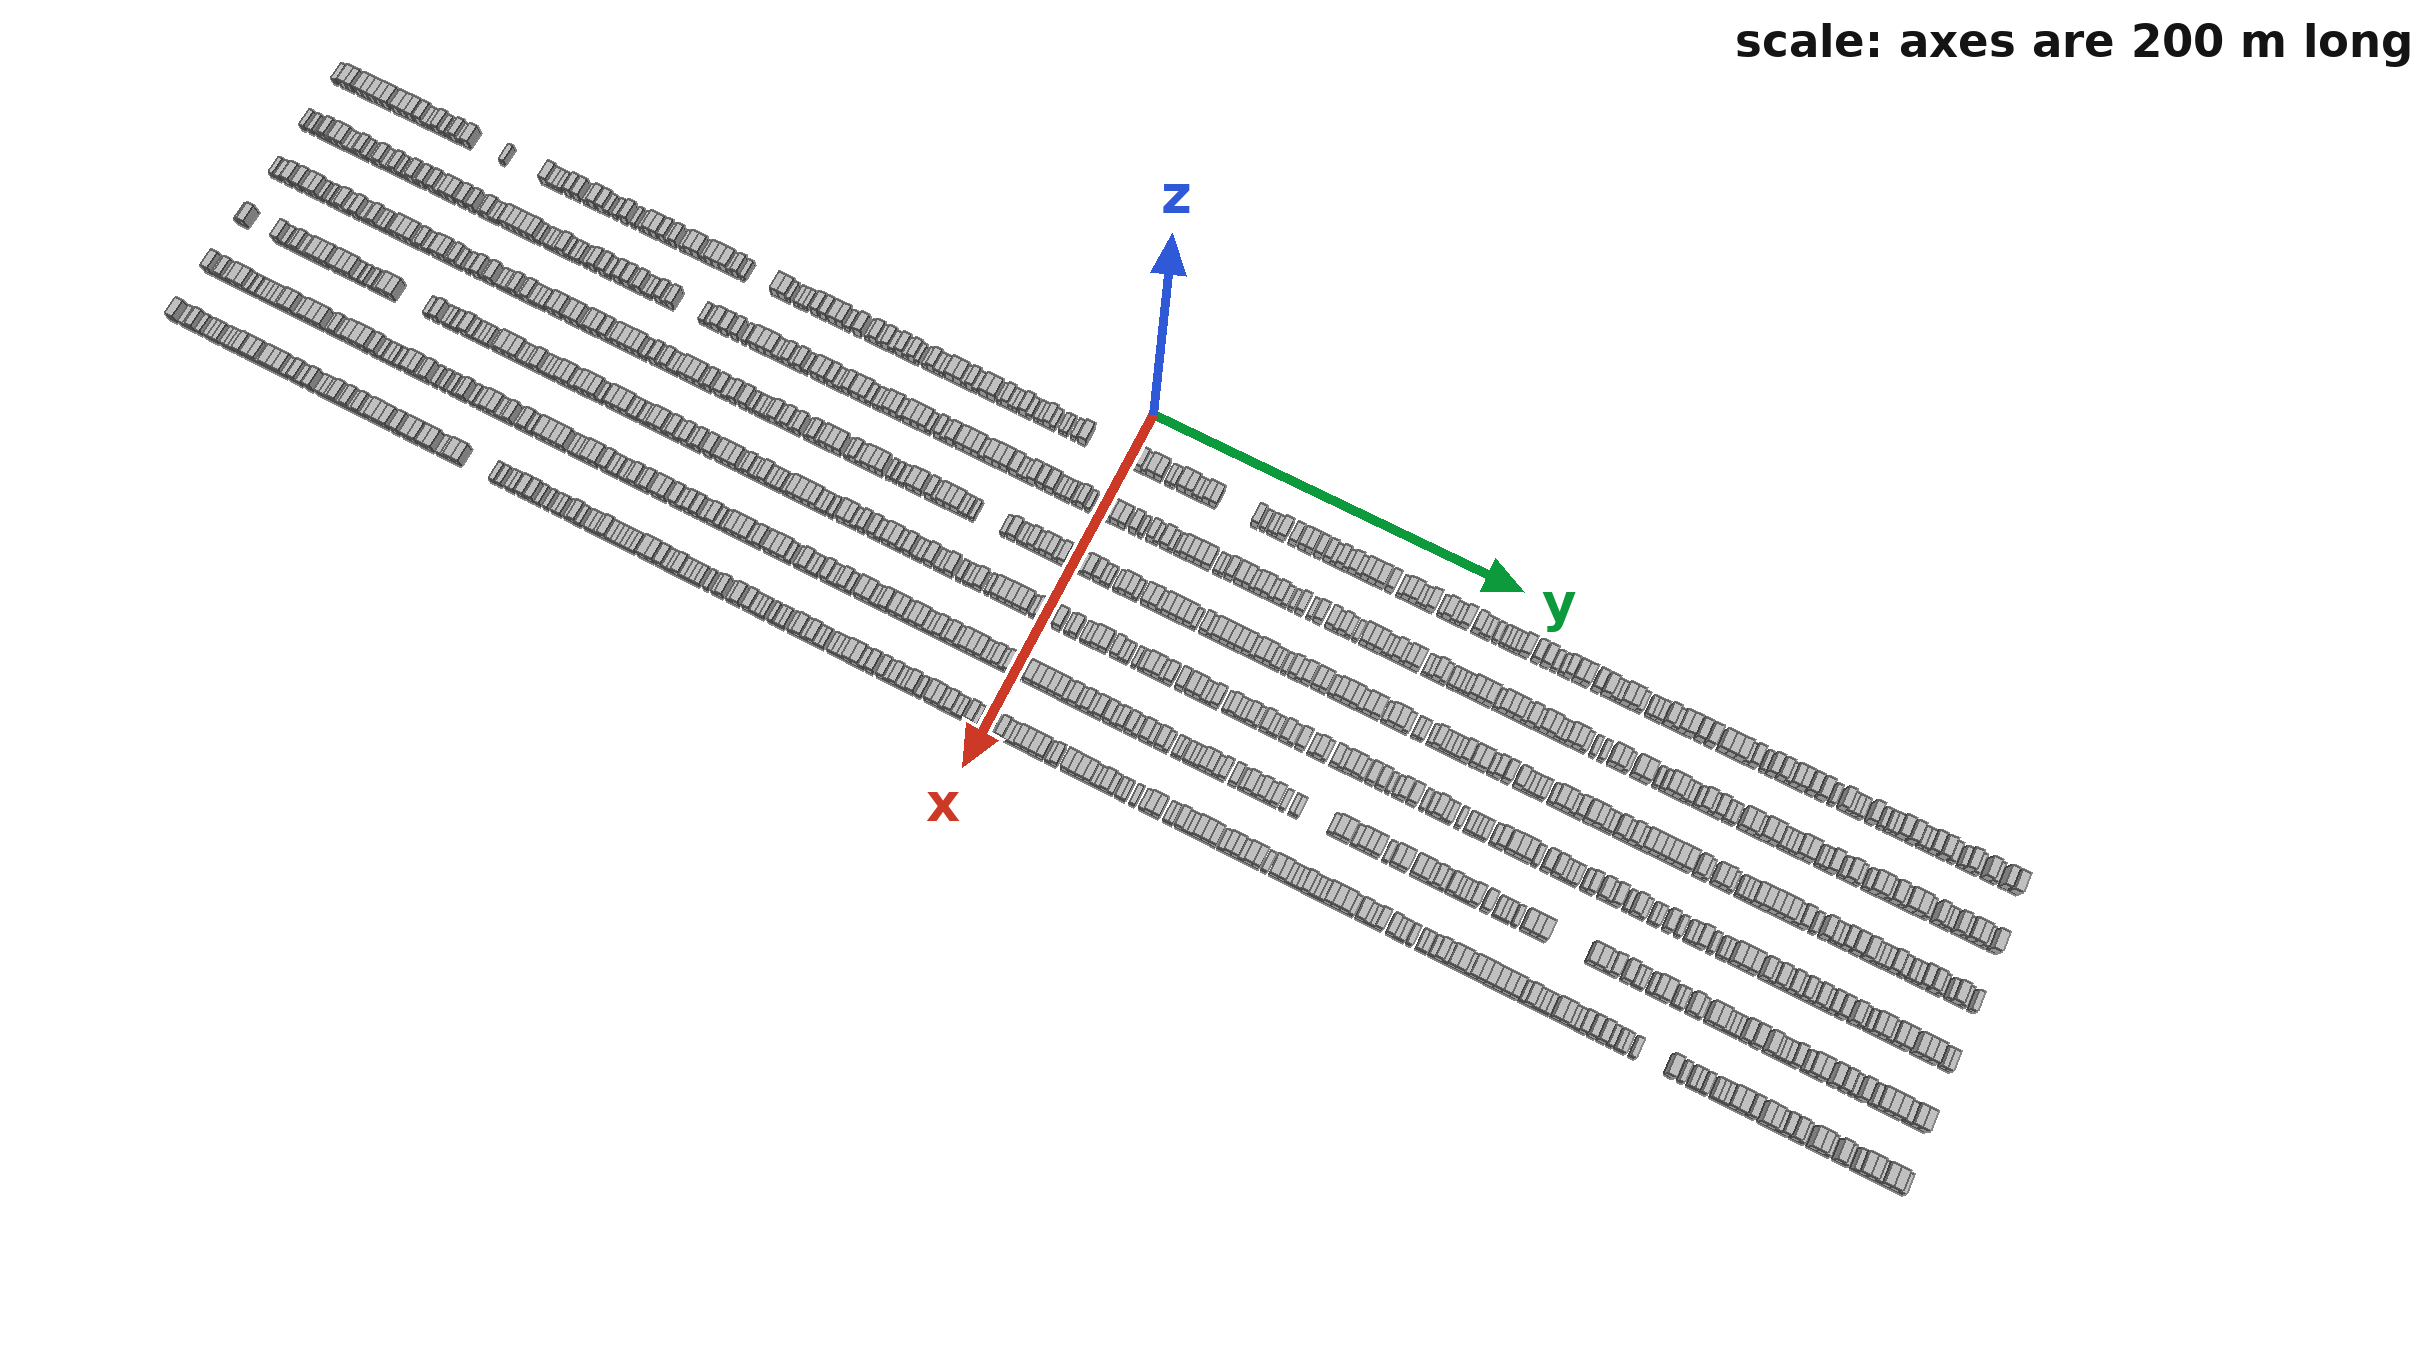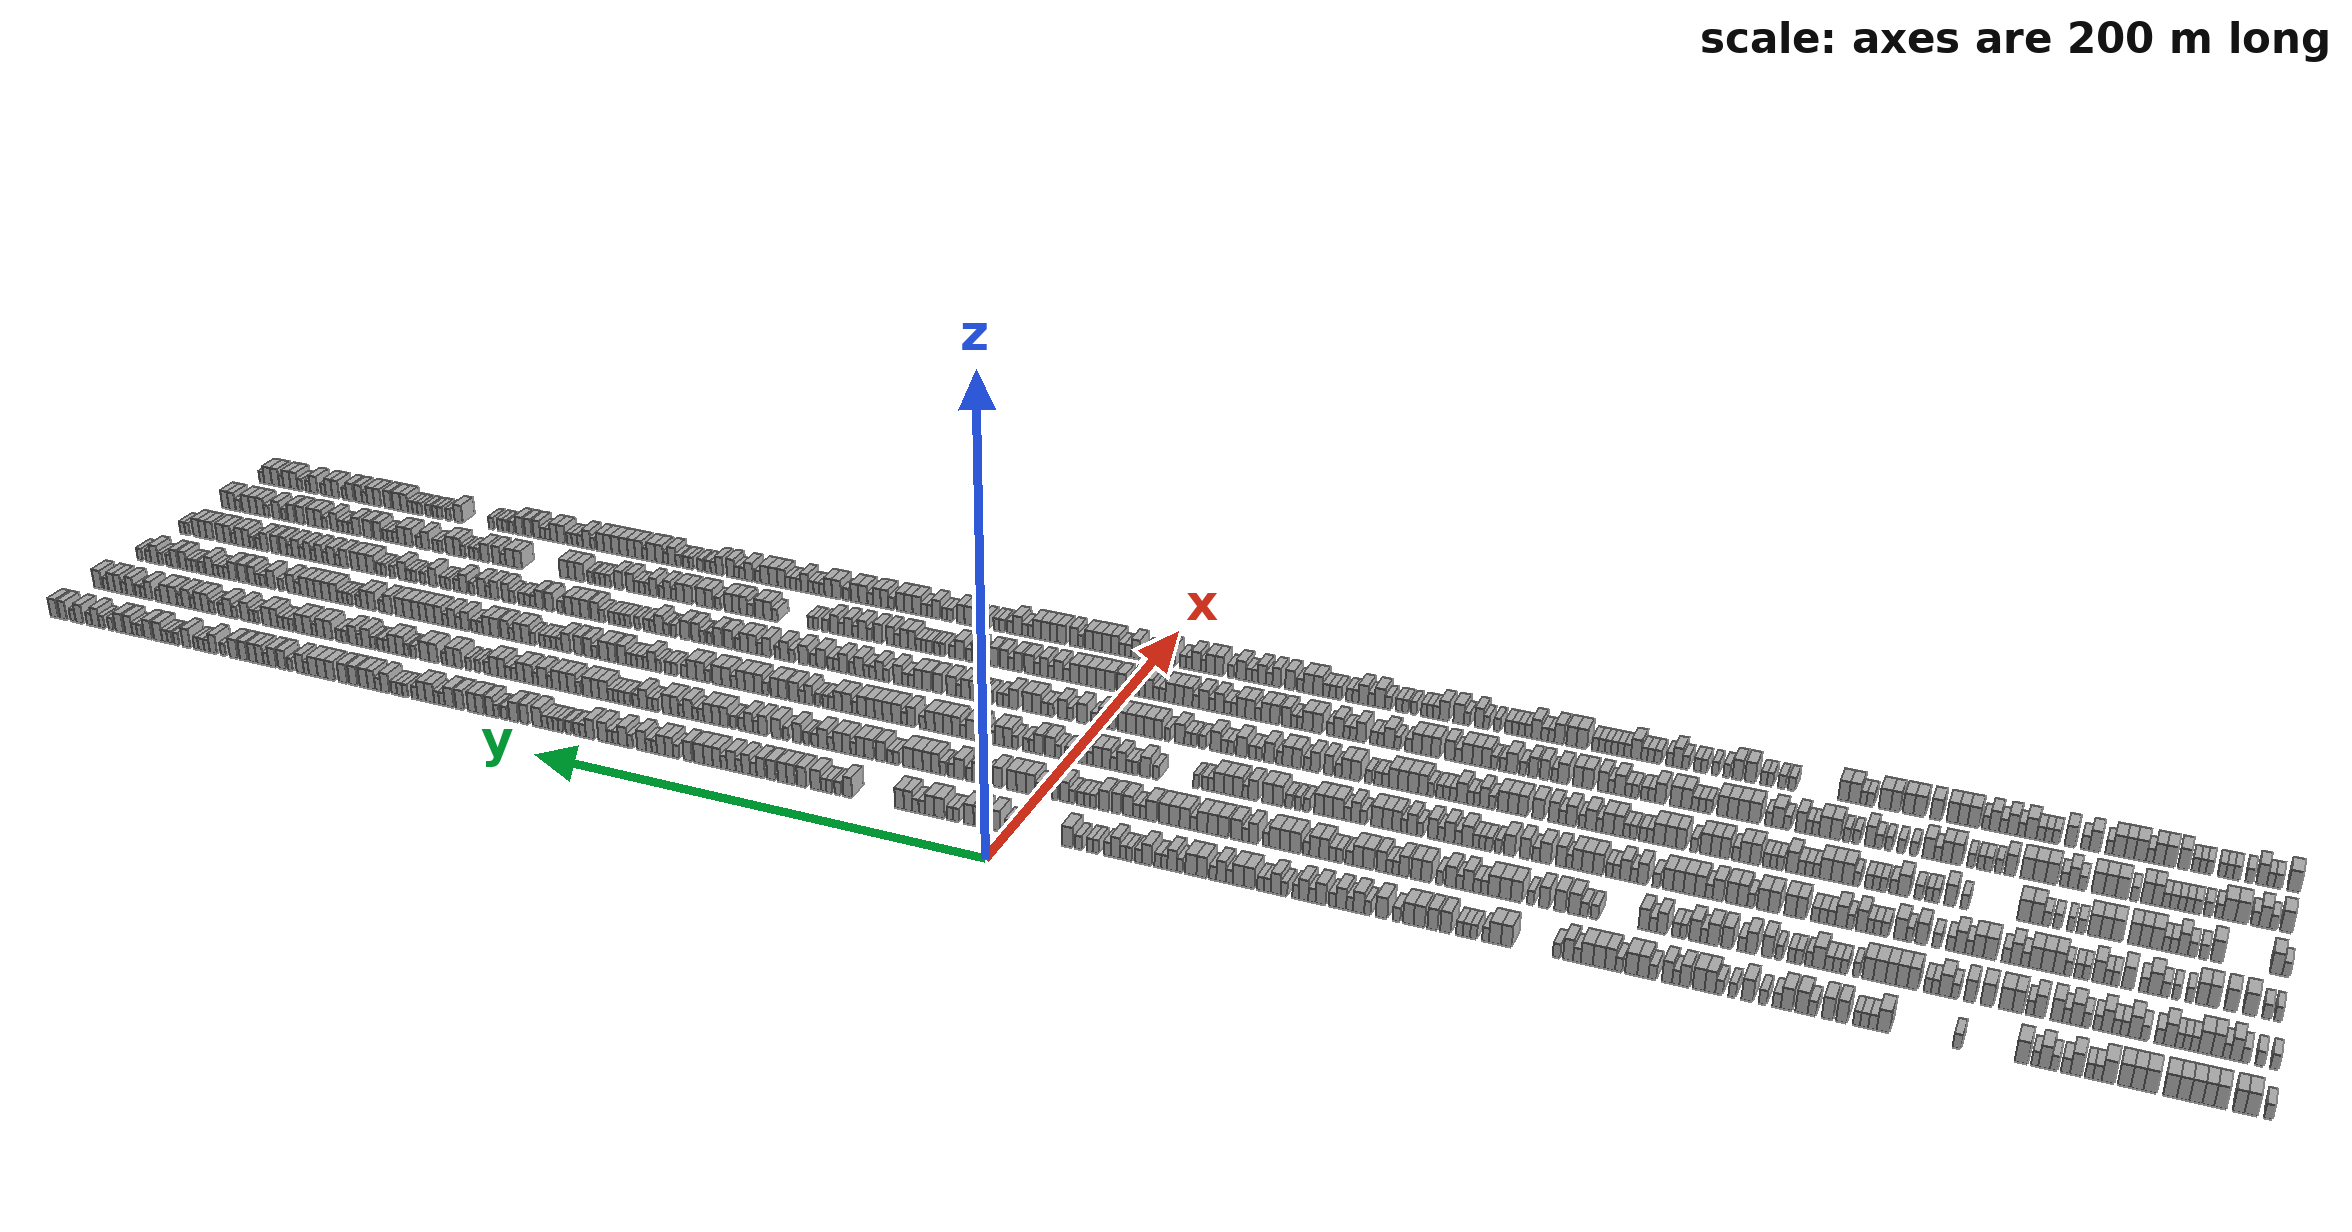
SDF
<sdf version="1.6">
 <world name="default">
  <scene>
   <sky><clouds><speed>12</speed></clouds></sky>
   <ambient>0.4 0.4 0.4 1</ambient>
   <background>0.7 0.7 0.7 1</background>
   <shadows>1</shadows>
  </scene>
  <gravity>0 0 -9.8066</gravity>
  <magnetic_field>6e-06 2.3e-05 -4.2e-05</magnetic_field>
  <physics default="0" name="default_physics" type="ode">
   <ode>
    <solver>
     <type>quick</type>
     <iters>10</iters>
     <sor>1.0</sor>
     <use_dynamic_moi_rescaling>0</use_dynamic_moi_rescaling>
    </solver>
    <constraints>
     <cfm>0</cfm>
     <erp>0.2</erp>
     <contact_max_correcting_vel>100</contact_max_correcting_vel>
     <contact_surface_layer>0.001</contact_surface_layer>
    </constraints>
   </ode>
   <max_step_size>0.004</max_step_size>
   <real_time_factor>1</real_time_factor>
   <real_time_update_rate>250</real_time_update_rate>
  </physics>
  <light name="sun" type="directional">
   <pose>0 0 10 0 0 0</pose>
   <diffuse>0.8 0.8 0.8 1</diffuse>
   <specular>0.2 0.2 0.2 1</specular>
   <attenuation>
    <range>1000</range>
    <constant>0.9</constant>
    <linear>0.01</linear>
    <quadratic>0.001</quadratic>
   </attenuation>
   <direction>-0.5 0.1 -0.9</direction>
  </light>
  <model name="building_1">
   <static>1</static>
   <pose>25.0000 -458.6161 0 0.000000 0.000000 0.000000</pose>
   <link name="link">
    <pose>0 0 3.00 0 0 0</pose>
    <collision name="collision"><geometry><box><size>10.0000 2.7677 6.0000</size></box></geometry></collision>
    <visual name="visual">
     <cast_shadows>0</cast_shadows>
     <geometry><box><size>10.0000 2.7677 6.0000</size></box></geometry>
     <material>
      <script>
       <uri>model://HANNAS_wall/materials/scripts</uri>
       <uri>model://HANNAS_wall/materials/textures</uri>
       <name>vrc/HANNAS_wall</name>
      </script>
     </material>
    </visual>
   </link>
  </model>
  <model name="building_2">
   <static>1</static>
   <pose>25.0000 -453.1422 0 0.000000 0.000000 0.000000</pose>
   <link name="link">
    <pose>0 0 4.50 0 0 0</pose>
    <collision name="collision"><geometry><box><size>10.0000 4.1801 9.0000</size></box></geometry></collision>
    <visual name="visual">
     <cast_shadows>0</cast_shadows>
     <geometry><box><size>10.0000 4.1801 9.0000</size></box></geometry>
     <material>
      <script>
       <uri>model://HANNAS_wall/materials/scripts</uri>
       <uri>model://HANNAS_wall/materials/textures</uri>
       <name>vrc/HANNAS_wall</name>
      </script>
     </material>
    </visual>
   </link>
  </model>
  <model name="building_3">
   <static>1</static>
   <pose>25.0000 -449.2247 0 0.000000 0.000000 0.000000</pose>
   <link name="link">
    <pose>0 0 4.50 0 0 0</pose>
    <collision name="collision"><geometry><box><size>10.0000 3.6550 9.0000</size></box></geometry></collision>
    <visual name="visual">
     <cast_shadows>0</cast_shadows>
     <geometry><box><size>10.0000 3.6550 9.0000</size></box></geometry>
     <material>
      <script>
       <uri>model://HANNAS_wall/materials/scripts</uri>
       <uri>model://HANNAS_wall/materials/textures</uri>
       <name>vrc/HANNAS_wall</name>
      </script>
     </material>
    </visual>
   </link>
  </model>
  <model name="building_4">
   <static>1</static>
   <pose>25.0000 -443.4356 0 0.000000 0.000000 0.000000</pose>
   <link name="link">
    <pose>0 0 4.50 0 0 0</pose>
    <collision name="collision"><geometry><box><size>10.0000 3.9232 9.0000</size></box></geometry></collision>
    <visual name="visual">
     <cast_shadows>0</cast_shadows>
     <geometry><box><size>10.0000 3.9232 9.0000</size></box></geometry>
     <material>
      <script>
       <uri>model://HANNAS_wall/materials/scripts</uri>
       <uri>model://HANNAS_wall/materials/textures</uri>
       <name>vrc/HANNAS_wall</name>
      </script>
     </material>
    </visual>
   </link>
  </model>
  <model name="building_5">
   <static>1</static>
   <pose>25.0000 -439.5945 0 0.000000 0.000000 0.000000</pose>
   <link name="link">
    <pose>0 0 4.50 0 0 0</pose>
    <collision name="collision"><geometry><box><size>10.0000 3.7590 9.0000</size></box></geometry></collision>
    <visual name="visual">
     <cast_shadows>0</cast_shadows>
     <geometry><box><size>10.0000 3.7590 9.0000</size></box></geometry>
     <material>
      <script>
       <uri>model://HANNAS_wall/materials/scripts</uri>
       <uri>model://HANNAS_wall/materials/textures</uri>
       <name>vrc/HANNAS_wall</name>
      </script>
     </material>
    </visual>
   </link>
  </model>
  <model name="building_6">
   <static>1</static>
   <pose>25.0000 -435.6475 0 0.000000 0.000000 0.000000</pose>
   <link name="link">
    <pose>0 0 4.50 0 0 0</pose>
    <collision name="collision"><geometry><box><size>10.0000 4.1350 9.0000</size></box></geometry></collision>
    <visual name="visual">
     <cast_shadows>0</cast_shadows>
     <geometry><box><size>10.0000 4.1350 9.0000</size></box></geometry>
     <material>
      <script>
       <uri>model://HANNAS_wall/materials/scripts</uri>
       <uri>model://HANNAS_wall/materials/textures</uri>
       <name>vrc/HANNAS_wall</name>
      </script>
     </material>
    </visual>
   </link>
  </model>
  <model name="building_7">
   <static>1</static>
   <pose>25.0000 -431.5682 0 0.000000 0.000000 0.000000</pose>
   <link name="link">
    <pose>0 0 4.50 0 0 0</pose>
    <collision name="collision"><geometry><box><size>10.0000 4.0237 9.0000</size></box></geometry></collision>
    <visual name="visual">
     <cast_shadows>0</cast_shadows>
     <geometry><box><size>10.0000 4.0237 9.0000</size></box></geometry>
     <material>
      <script>
       <uri>model://HANNAS_wall/materials/scripts</uri>
       <uri>model://HANNAS_wall/materials/textures</uri>
       <name>vrc/HANNAS_wall</name>
      </script>
     </material>
    </visual>
   </link>
  </model>
  <model name="building_8">
   <static>1</static>
   <pose>25.0000 -427.3816 0 0.000000 0.000000 0.000000</pose>
   <link name="link">
    <pose>0 0 4.50 0 0 0</pose>
    <collision name="collision"><geometry><box><size>10.0000 4.3495 9.0000</size></box></geometry></collision>
    <visual name="visual">
     <cast_shadows>0</cast_shadows>
     <geometry><box><size>10.0000 4.3495 9.0000</size></box></geometry>
     <material>
      <script>
       <uri>model://HANNAS_wall/materials/scripts</uri>
       <uri>model://HANNAS_wall/materials/textures</uri>
       <name>vrc/HANNAS_wall</name>
      </script>
     </material>
    </visual>
   </link>
  </model>
  <model name="building_9">
   <static>1</static>
   <pose>25.0000 -421.0056 0 0.000000 0.000000 0.000000</pose>
   <link name="link">
    <pose>0 0 4.50 0 0 0</pose>
    <collision name="collision"><geometry><box><size>10.0000 4.4024 9.0000</size></box></geometry></collision>
    <visual name="visual">
     <cast_shadows>0</cast_shadows>
     <geometry><box><size>10.0000 4.4024 9.0000</size></box></geometry>
     <material>
      <script>
       <uri>model://HANNAS_wall/materials/scripts</uri>
       <uri>model://HANNAS_wall/materials/textures</uri>
       <name>vrc/HANNAS_wall</name>
      </script>
     </material>
    </visual>
   </link>
  </model>
  <model name="building_10">
   <static>1</static>
   <pose>25.0000 -416.7751 0 0.000000 0.000000 0.000000</pose>
   <link name="link">
    <pose>0 0 4.50 0 0 0</pose>
    <collision name="collision"><geometry><box><size>10.0000 4.0587 9.0000</size></box></geometry></collision>
    <visual name="visual">
     <cast_shadows>0</cast_shadows>
     <geometry><box><size>10.0000 4.0587 9.0000</size></box></geometry>
     <material>
      <script>
       <uri>model://HANNAS_wall/materials/scripts</uri>
       <uri>model://HANNAS_wall/materials/textures</uri>
       <name>vrc/HANNAS_wall</name>
      </script>
     </material>
    </visual>
   </link>
  </model>
  <model name="building_11">
   <static>1</static>
   <pose>25.0000 -412.6336 0 0.000000 0.000000 0.000000</pose>
   <link name="link">
    <pose>0 0 4.50 0 0 0</pose>
    <collision name="collision"><geometry><box><size>10.0000 4.2243 9.0000</size></box></geometry></collision>
    <visual name="visual">
     <cast_shadows>0</cast_shadows>
     <geometry><box><size>10.0000 4.2243 9.0000</size></box></geometry>
     <material>
      <script>
       <uri>model://HANNAS_wall/materials/scripts</uri>
       <uri>model://HANNAS_wall/materials/textures</uri>
       <name>vrc/HANNAS_wall</name>
      </script>
     </material>
    </visual>
   </link>
  </model>
  <model name="building_12">
   <static>1</static>
   <pose>25.0000 -407.3977 0 0.000000 0.000000 0.000000</pose>
   <link name="link">
    <pose>0 0 4.50 0 0 0</pose>
    <collision name="collision"><geometry><box><size>10.0000 4.2476 9.0000</size></box></geometry></collision>
    <visual name="visual">
     <cast_shadows>0</cast_shadows>
     <geometry><box><size>10.0000 4.2476 9.0000</size></box></geometry>
     <material>
      <script>
       <uri>model://HANNAS_wall/materials/scripts</uri>
       <uri>model://HANNAS_wall/materials/textures</uri>
       <name>vrc/HANNAS_wall</name>
      </script>
     </material>
    </visual>
   </link>
  </model>
  <model name="building_13">
   <static>1</static>
   <pose>25.0000 -403.8219 0 0.000000 0.000000 0.000000</pose>
   <link name="link">
    <pose>0 0 3.00 0 0 0</pose>
    <collision name="collision"><geometry><box><size>10.0000 2.9038 6.0000</size></box></geometry></collision>
    <visual name="visual">
     <cast_shadows>0</cast_shadows>
     <geometry><box><size>10.0000 2.9038 6.0000</size></box></geometry>
     <material>
      <script>
       <uri>model://HANNAS_wall/materials/scripts</uri>
       <uri>model://HANNAS_wall/materials/textures</uri>
       <name>vrc/HANNAS_wall</name>
      </script>
     </material>
    </visual>
   </link>
  </model>
  <model name="building_14">
   <static>1</static>
   <pose>25.0000 -401.0797 0 0.000000 0.000000 0.000000</pose>
   <link name="link">
    <pose>0 0 3.00 0 0 0</pose>
    <collision name="collision"><geometry><box><size>10.0000 2.5807 6.0000</size></box></geometry></collision>
    <visual name="visual">
     <cast_shadows>0</cast_shadows>
     <geometry><box><size>10.0000 2.5807 6.0000</size></box></geometry>
     <material>
      <script>
       <uri>model://HANNAS_wall/materials/scripts</uri>
       <uri>model://HANNAS_wall/materials/textures</uri>
       <name>vrc/HANNAS_wall</name>
      </script>
     </material>
    </visual>
   </link>
  </model>
  <model name="building_15">
   <static>1</static>
   <pose>25.0000 -396.8624 0 0.000000 0.000000 0.000000</pose>
   <link name="link">
    <pose>0 0 4.50 0 0 0</pose>
    <collision name="collision"><geometry><box><size>10.0000 3.8540 9.0000</size></box></geometry></collision>
    <visual name="visual">
     <cast_shadows>0</cast_shadows>
     <geometry><box><size>10.0000 3.8540 9.0000</size></box></geometry>
     <material>
      <script>
       <uri>model://HANNAS_wall/materials/scripts</uri>
       <uri>model://HANNAS_wall/materials/textures</uri>
       <name>vrc/HANNAS_wall</name>
      </script>
     </material>
    </visual>
   </link>
  </model>
  <model name="building_16">
   <static>1</static>
   <pose>25.0000 -393.4373 0 0.000000 0.000000 0.000000</pose>
   <link name="link">
    <pose>0 0 3.00 0 0 0</pose>
    <collision name="collision"><geometry><box><size>10.0000 2.9962 6.0000</size></box></geometry></collision>
    <visual name="visual">
     <cast_shadows>0</cast_shadows>
     <geometry><box><size>10.0000 2.9962 6.0000</size></box></geometry>
     <material>
      <script>
       <uri>model://HANNAS_wall/materials/scripts</uri>
       <uri>model://HANNAS_wall/materials/textures</uri>
       <name>vrc/HANNAS_wall</name>
      </script>
     </material>
    </visual>
   </link>
  </model>
  <model name="building_17">
   <static>1</static>
   <pose>25.0000 -389.6744 0 0.000000 0.000000 0.000000</pose>
   <link name="link">
    <pose>0 0 3.00 0 0 0</pose>
    <collision name="collision"><geometry><box><size>10.0000 2.5295 6.0000</size></box></geometry></collision>
    <visual name="visual">
     <cast_shadows>0</cast_shadows>
     <geometry><box><size>10.0000 2.5295 6.0000</size></box></geometry>
     <material>
      <script>
       <uri>model://HANNAS_wall/materials/scripts</uri>
       <uri>model://HANNAS_wall/materials/textures</uri>
       <name>vrc/HANNAS_wall</name>
      </script>
     </material>
    </visual>
   </link>
  </model>
  <model name="building_18">
   <static>1</static>
   <pose>25.0000 -386.4665 0 0.000000 0.000000 0.000000</pose>
   <link name="link">
    <pose>0 0 4.50 0 0 0</pose>
    <collision name="collision"><geometry><box><size>10.0000 3.8864 9.0000</size></box></geometry></collision>
    <visual name="visual">
     <cast_shadows>0</cast_shadows>
     <geometry><box><size>10.0000 3.8864 9.0000</size></box></geometry>
     <material>
      <script>
       <uri>model://HANNAS_wall/materials/scripts</uri>
       <uri>model://HANNAS_wall/materials/textures</uri>
       <name>vrc/HANNAS_wall</name>
      </script>
     </material>
    </visual>
   </link>
  </model>
  <model name="building_19">
   <static>1</static>
   <pose>25.0000 -383.3175 0 0.000000 0.000000 0.000000</pose>
   <link name="link">
    <pose>0 0 3.00 0 0 0</pose>
    <collision name="collision"><geometry><box><size>10.0000 2.4115 6.0000</size></box></geometry></collision>
    <visual name="visual">
     <cast_shadows>0</cast_shadows>
     <geometry><box><size>10.0000 2.4115 6.0000</size></box></geometry>
     <material>
      <script>
       <uri>model://HANNAS_wall/materials/scripts</uri>
       <uri>model://HANNAS_wall/materials/textures</uri>
       <name>vrc/HANNAS_wall</name>
      </script>
     </material>
    </visual>
   </link>
  </model>
  <model name="building_20">
   <static>1</static>
   <pose>25.0000 -378.9247 0 0.000000 0.000000 0.000000</pose>
   <link name="link">
    <pose>0 0 4.50 0 0 0</pose>
    <collision name="collision"><geometry><box><size>10.0000 4.3742 9.0000</size></box></geometry></collision>
    <visual name="visual">
     <cast_shadows>0</cast_shadows>
     <geometry><box><size>10.0000 4.3742 9.0000</size></box></geometry>
     <material>
      <script>
       <uri>model://HANNAS_wall/materials/scripts</uri>
       <uri>model://HANNAS_wall/materials/textures</uri>
       <name>vrc/HANNAS_wall</name>
      </script>
     </material>
    </visual>
   </link>
  </model>
  <model name="building_21">
   <static>1</static>
   <pose>25.0000 -357.4171 0 0.000000 0.000000 0.000000</pose>
   <link name="link">
    <pose>0 0 3.00 0 0 0</pose>
    <collision name="collision"><geometry><box><size>10.0000 2.8803 6.0000</size></box></geometry></collision>
    <visual name="visual">
     <cast_shadows>0</cast_shadows>
     <geometry><box><size>10.0000 2.8803 6.0000</size></box></geometry>
     <material>
      <script>
       <uri>model://HANNAS_wall/materials/scripts</uri>
       <uri>model://HANNAS_wall/materials/textures</uri>
       <name>vrc/HANNAS_wall</name>
      </script>
     </material>
    </visual>
   </link>
  </model>
  <model name="building_22">
   <static>1</static>
   <pose>25.0000 -332.4077 0 0.000000 0.000000 0.000000</pose>
   <link name="link">
    <pose>0 0 4.50 0 0 0</pose>
    <collision name="collision"><geometry><box><size>10.0000 4.3794 9.0000</size></box></geometry></collision>
    <visual name="visual">
     <cast_shadows>0</cast_shadows>
     <geometry><box><size>10.0000 4.3794 9.0000</size></box></geometry>
     <material>
      <script>
       <uri>model://HANNAS_wall/materials/scripts</uri>
       <uri>model://HANNAS_wall/materials/textures</uri>
       <name>vrc/HANNAS_wall</name>
      </script>
     </material>
    </visual>
   </link>
  </model>
  <model name="building_23">
   <static>1</static>
   <pose>25.0000 -328.7465 0 0.000000 0.000000 0.000000</pose>
   <link name="link">
    <pose>0 0 3.00 0 0 0</pose>
    <collision name="collision"><geometry><box><size>10.0000 2.9431 6.0000</size></box></geometry></collision>
    <visual name="visual">
     <cast_shadows>0</cast_shadows>
     <geometry><box><size>10.0000 2.9431 6.0000</size></box></geometry>
     <material>
      <script>
       <uri>model://HANNAS_wall/materials/scripts</uri>
       <uri>model://HANNAS_wall/materials/textures</uri>
       <name>vrc/HANNAS_wall</name>
      </script>
     </material>
    </visual>
   </link>
  </model>
  <model name="building_24">
   <static>1</static>
   <pose>25.0000 -325.8399 0 0.000000 0.000000 0.000000</pose>
   <link name="link">
    <pose>0 0 3.00 0 0 0</pose>
    <collision name="collision"><geometry><box><size>10.0000 2.8702 6.0000</size></box></geometry></collision>
    <visual name="visual">
     <cast_shadows>0</cast_shadows>
     <geometry><box><size>10.0000 2.8702 6.0000</size></box></geometry>
     <material>
      <script>
       <uri>model://HANNAS_wall/materials/scripts</uri>
       <uri>model://HANNAS_wall/materials/textures</uri>
       <name>vrc/HANNAS_wall</name>
      </script>
     </material>
    </visual>
   </link>
  </model>
  <model name="building_25">
   <static>1</static>
   <pose>25.0000 -323.1905 0 0.000000 0.000000 0.000000</pose>
   <link name="link">
    <pose>0 0 3.00 0 0 0</pose>
    <collision name="collision"><geometry><box><size>10.0000 2.4285 6.0000</size></box></geometry></collision>
    <visual name="visual">
     <cast_shadows>0</cast_shadows>
     <geometry><box><size>10.0000 2.4285 6.0000</size></box></geometry>
     <material>
      <script>
       <uri>model://HANNAS_wall/materials/scripts</uri>
       <uri>model://HANNAS_wall/materials/textures</uri>
       <name>vrc/HANNAS_wall</name>
      </script>
     </material>
    </visual>
   </link>
  </model>
  <model name="building_26">
   <static>1</static>
   <pose>25.0000 -318.1049 0 0.000000 0.000000 0.000000</pose>
   <link name="link">
    <pose>0 0 4.50 0 0 0</pose>
    <collision name="collision"><geometry><box><size>10.0000 3.7427 9.0000</size></box></geometry></collision>
    <visual name="visual">
     <cast_shadows>0</cast_shadows>
     <geometry><box><size>10.0000 3.7427 9.0000</size></box></geometry>
     <material>
      <script>
       <uri>model://HANNAS_wall/materials/scripts</uri>
       <uri>model://HANNAS_wall/materials/textures</uri>
       <name>vrc/HANNAS_wall</name>
      </script>
     </material>
    </visual>
   </link>
  </model>
  <model name="building_27">
   <static>1</static>
   <pose>25.0000 -313.2380 0 0.000000 0.000000 0.000000</pose>
   <link name="link">
    <pose>0 0 4.50 0 0 0</pose>
    <collision name="collision"><geometry><box><size>10.0000 3.9911 9.0000</size></box></geometry></collision>
    <visual name="visual">
     <cast_shadows>0</cast_shadows>
     <geometry><box><size>10.0000 3.9911 9.0000</size></box></geometry>
     <material>
      <script>
       <uri>model://HANNAS_wall/materials/scripts</uri>
       <uri>model://HANNAS_wall/materials/textures</uri>
       <name>vrc/HANNAS_wall</name>
      </script>
     </material>
    </visual>
   </link>
  </model>
  <model name="building_28">
   <static>1</static>
   <pose>25.0000 -307.7797 0 0.000000 0.000000 0.000000</pose>
   <link name="link">
    <pose>0 0 3.00 0 0 0</pose>
    <collision name="collision"><geometry><box><size>10.0000 2.9255 6.0000</size></box></geometry></collision>
    <visual name="visual">
     <cast_shadows>0</cast_shadows>
     <geometry><box><size>10.0000 2.9255 6.0000</size></box></geometry>
     <material>
      <script>
       <uri>model://HANNAS_wall/materials/scripts</uri>
       <uri>model://HANNAS_wall/materials/textures</uri>
       <name>vrc/HANNAS_wall</name>
      </script>
     </material>
    </visual>
   </link>
  </model>
  <model name="building_29">
   <static>1</static>
   <pose>25.0000 -304.1932 0 0.000000 0.000000 0.000000</pose>
   <link name="link">
    <pose>0 0 4.50 0 0 0</pose>
    <collision name="collision"><geometry><box><size>10.0000 4.2475 9.0000</size></box></geometry></collision>
    <visual name="visual">
     <cast_shadows>0</cast_shadows>
     <geometry><box><size>10.0000 4.2475 9.0000</size></box></geometry>
     <material>
      <script>
       <uri>model://HANNAS_wall/materials/scripts</uri>
       <uri>model://HANNAS_wall/materials/textures</uri>
       <name>vrc/HANNAS_wall</name>
      </script>
     </material>
    </visual>
   </link>
  </model>
  <model name="building_30">
   <static>1</static>
   <pose>25.0000 -298.9964 0 0.000000 0.000000 0.000000</pose>
   <link name="link">
    <pose>0 0 4.50 0 0 0</pose>
    <collision name="collision"><geometry><box><size>10.0000 4.1460 9.0000</size></box></geometry></collision>
    <visual name="visual">
     <cast_shadows>0</cast_shadows>
     <geometry><box><size>10.0000 4.1460 9.0000</size></box></geometry>
     <material>
      <script>
       <uri>model://HANNAS_wall/materials/scripts</uri>
       <uri>model://HANNAS_wall/materials/textures</uri>
       <name>vrc/HANNAS_wall</name>
      </script>
     </material>
    </visual>
   </link>
  </model>
  <model name="building_31">
   <static>1</static>
   <pose>25.0000 -295.4681 0 0.000000 0.000000 0.000000</pose>
   <link name="link">
    <pose>0 0 3.00 0 0 0</pose>
    <collision name="collision"><geometry><box><size>10.0000 2.9106 6.0000</size></box></geometry></collision>
    <visual name="visual">
     <cast_shadows>0</cast_shadows>
     <geometry><box><size>10.0000 2.9106 6.0000</size></box></geometry>
     <material>
      <script>
       <uri>model://HANNAS_wall/materials/scripts</uri>
       <uri>model://HANNAS_wall/materials/textures</uri>
       <name>vrc/HANNAS_wall</name>
      </script>
     </material>
    </visual>
   </link>
  </model>
  <model name="building_32">
   <static>1</static>
   <pose>25.0000 -290.6160 0 0.000000 0.000000 0.000000</pose>
   <link name="link">
    <pose>0 0 3.00 0 0 0</pose>
    <collision name="collision"><geometry><box><size>10.0000 2.7937 6.0000</size></box></geometry></collision>
    <visual name="visual">
     <cast_shadows>0</cast_shadows>
     <geometry><box><size>10.0000 2.7937 6.0000</size></box></geometry>
     <material>
      <script>
       <uri>model://HANNAS_wall/materials/scripts</uri>
       <uri>model://HANNAS_wall/materials/textures</uri>
       <name>vrc/HANNAS_wall</name>
      </script>
     </material>
    </visual>
   </link>
  </model>
  <model name="building_33">
   <static>1</static>
   <pose>25.0000 -285.1777 0 0.000000 0.000000 0.000000</pose>
   <link name="link">
    <pose>0 0 4.50 0 0 0</pose>
    <collision name="collision"><geometry><box><size>10.0000 4.0829 9.0000</size></box></geometry></collision>
    <visual name="visual">
     <cast_shadows>0</cast_shadows>
     <geometry><box><size>10.0000 4.0829 9.0000</size></box></geometry>
     <material>
      <script>
       <uri>model://HANNAS_wall/materials/scripts</uri>
       <uri>model://HANNAS_wall/materials/textures</uri>
       <name>vrc/HANNAS_wall</name>
      </script>
     </material>
    </visual>
   </link>
  </model>
  <model name="building_34">
   <static>1</static>
   <pose>25.0000 -279.8225 0 0.000000 0.000000 0.000000</pose>
   <link name="link">
    <pose>0 0 3.00 0 0 0</pose>
    <collision name="collision"><geometry><box><size>10.0000 2.6276 6.0000</size></box></geometry></collision>
    <visual name="visual">
     <cast_shadows>0</cast_shadows>
     <geometry><box><size>10.0000 2.6276 6.0000</size></box></geometry>
     <material>
      <script>
       <uri>model://HANNAS_wall/materials/scripts</uri>
       <uri>model://HANNAS_wall/materials/textures</uri>
       <name>vrc/HANNAS_wall</name>
      </script>
     </material>
    </visual>
   </link>
  </model>
  <model name="building_35">
   <static>1</static>
   <pose>25.0000 -275.1801 0 0.000000 0.000000 0.000000</pose>
   <link name="link">
    <pose>0 0 3.00 0 0 0</pose>
    <collision name="collision"><geometry><box><size>10.0000 2.6573 6.0000</size></box></geometry></collision>
    <visual name="visual">
     <cast_shadows>0</cast_shadows>
     <geometry><box><size>10.0000 2.6573 6.0000</size></box></geometry>
     <material>
      <script>
       <uri>model://HANNAS_wall/materials/scripts</uri>
       <uri>model://HANNAS_wall/materials/textures</uri>
       <name>vrc/HANNAS_wall</name>
      </script>
     </material>
    </visual>
   </link>
  </model>
  <model name="building_36">
   <static>1</static>
   <pose>25.0000 -271.9345 0 0.000000 0.000000 0.000000</pose>
   <link name="link">
    <pose>0 0 4.50 0 0 0</pose>
    <collision name="collision"><geometry><box><size>10.0000 3.8339 9.0000</size></box></geometry></collision>
    <visual name="visual">
     <cast_shadows>0</cast_shadows>
     <geometry><box><size>10.0000 3.8339 9.0000</size></box></geometry>
     <material>
      <script>
       <uri>model://HANNAS_wall/materials/scripts</uri>
       <uri>model://HANNAS_wall/materials/textures</uri>
       <name>vrc/HANNAS_wall</name>
      </script>
     </material>
    </visual>
   </link>
  </model>
  <model name="building_37">
   <static>1</static>
   <pose>25.0000 -267.9023 0 0.000000 0.000000 0.000000</pose>
   <link name="link">
    <pose>0 0 4.50 0 0 0</pose>
    <collision name="collision"><geometry><box><size>10.0000 4.2304 9.0000</size></box></geometry></collision>
    <visual name="visual">
     <cast_shadows>0</cast_shadows>
     <geometry><box><size>10.0000 4.2304 9.0000</size></box></geometry>
     <material>
      <script>
       <uri>model://HANNAS_wall/materials/scripts</uri>
       <uri>model://HANNAS_wall/materials/textures</uri>
       <name>vrc/HANNAS_wall</name>
      </script>
     </material>
    </visual>
   </link>
  </model>
  <model name="building_38">
   <static>1</static>
   <pose>25.0000 -262.9214 0 0.000000 0.000000 0.000000</pose>
   <link name="link">
    <pose>0 0 4.50 0 0 0</pose>
    <collision name="collision"><geometry><box><size>10.0000 3.7315 9.0000</size></box></geometry></collision>
    <visual name="visual">
     <cast_shadows>0</cast_shadows>
     <geometry><box><size>10.0000 3.7315 9.0000</size></box></geometry>
     <material>
      <script>
       <uri>model://HANNAS_wall/materials/scripts</uri>
       <uri>model://HANNAS_wall/materials/textures</uri>
       <name>vrc/HANNAS_wall</name>
      </script>
     </material>
    </visual>
   </link>
  </model>
  <model name="building_39">
   <static>1</static>
   <pose>25.0000 -259.7239 0 0.000000 0.000000 0.000000</pose>
   <link name="link">
    <pose>0 0 3.00 0 0 0</pose>
    <collision name="collision"><geometry><box><size>10.0000 2.6636 6.0000</size></box></geometry></collision>
    <visual name="visual">
     <cast_shadows>0</cast_shadows>
     <geometry><box><size>10.0000 2.6636 6.0000</size></box></geometry>
     <material>
      <script>
       <uri>model://HANNAS_wall/materials/scripts</uri>
       <uri>model://HANNAS_wall/materials/textures</uri>
       <name>vrc/HANNAS_wall</name>
      </script>
     </material>
    </visual>
   </link>
  </model>
  <model name="building_40">
   <static>1</static>
   <pose>25.0000 -256.5775 0 0.000000 0.000000 0.000000</pose>
   <link name="link">
    <pose>0 0 4.50 0 0 0</pose>
    <collision name="collision"><geometry><box><size>10.0000 3.6291 9.0000</size></box></geometry></collision>
    <visual name="visual">
     <cast_shadows>0</cast_shadows>
     <geometry><box><size>10.0000 3.6291 9.0000</size></box></geometry>
     <material>
      <script>
       <uri>model://HANNAS_wall/materials/scripts</uri>
       <uri>model://HANNAS_wall/materials/textures</uri>
       <name>vrc/HANNAS_wall</name>
      </script>
     </material>
    </visual>
   </link>
  </model>
  <model name="building_41">
   <static>1</static>
   <pose>25.0000 -251.3099 0 0.000000 0.000000 0.000000</pose>
   <link name="link">
    <pose>0 0 3.00 0 0 0</pose>
    <collision name="collision"><geometry><box><size>10.0000 2.9061 6.0000</size></box></geometry></collision>
    <visual name="visual">
     <cast_shadows>0</cast_shadows>
     <geometry><box><size>10.0000 2.9061 6.0000</size></box></geometry>
     <material>
      <script>
       <uri>model://HANNAS_wall/materials/scripts</uri>
       <uri>model://HANNAS_wall/materials/textures</uri>
       <name>vrc/HANNAS_wall</name>
      </script>
     </material>
    </visual>
   </link>
  </model>
  <model name="building_42">
   <static>1</static>
   <pose>25.0000 -247.8543 0 0.000000 0.000000 0.000000</pose>
   <link name="link">
    <pose>0 0 4.50 0 0 0</pose>
    <collision name="collision"><geometry><box><size>10.0000 4.0052 9.0000</size></box></geometry></collision>
    <visual name="visual">
     <cast_shadows>0</cast_shadows>
     <geometry><box><size>10.0000 4.0052 9.0000</size></box></geometry>
     <material>
      <script>
       <uri>model://HANNAS_wall/materials/scripts</uri>
       <uri>model://HANNAS_wall/materials/textures</uri>
       <name>vrc/HANNAS_wall</name>
      </script>
     </material>
    </visual>
   </link>
  </model>
  <model name="building_43">
   <static>1</static>
   <pose>25.0000 -243.6501 0 0.000000 0.000000 0.000000</pose>
   <link name="link">
    <pose>0 0 4.50 0 0 0</pose>
    <collision name="collision"><geometry><box><size>10.0000 4.4032 9.0000</size></box></geometry></collision>
    <visual name="visual">
     <cast_shadows>0</cast_shadows>
     <geometry><box><size>10.0000 4.4032 9.0000</size></box></geometry>
     <material>
      <script>
       <uri>model://HANNAS_wall/materials/scripts</uri>
       <uri>model://HANNAS_wall/materials/textures</uri>
       <name>vrc/HANNAS_wall</name>
      </script>
     </material>
    </visual>
   </link>
  </model>
  <model name="building_44">
   <static>1</static>
   <pose>25.0000 -239.1411 0 0.000000 0.000000 0.000000</pose>
   <link name="link">
    <pose>0 0 3.00 0 0 0</pose>
    <collision name="collision"><geometry><box><size>10.0000 2.6146 6.0000</size></box></geometry></collision>
    <visual name="visual">
     <cast_shadows>0</cast_shadows>
     <geometry><box><size>10.0000 2.6146 6.0000</size></box></geometry>
     <material>
      <script>
       <uri>model://HANNAS_wall/materials/scripts</uri>
       <uri>model://HANNAS_wall/materials/textures</uri>
       <name>vrc/HANNAS_wall</name>
      </script>
     </material>
    </visual>
   </link>
  </model>
  <model name="building_45">
   <static>1</static>
   <pose>25.0000 -235.9345 0 0.000000 0.000000 0.000000</pose>
   <link name="link">
    <pose>0 0 4.50 0 0 0</pose>
    <collision name="collision"><geometry><box><size>10.0000 3.7987 9.0000</size></box></geometry></collision>
    <visual name="visual">
     <cast_shadows>0</cast_shadows>
     <geometry><box><size>10.0000 3.7987 9.0000</size></box></geometry>
     <material>
      <script>
       <uri>model://HANNAS_wall/materials/scripts</uri>
       <uri>model://HANNAS_wall/materials/textures</uri>
       <name>vrc/HANNAS_wall</name>
      </script>
     </material>
    </visual>
   </link>
  </model>
  <model name="building_46">
   <static>1</static>
   <pose>25.0000 -231.8485 0 0.000000 0.000000 0.000000</pose>
   <link name="link">
    <pose>0 0 4.50 0 0 0</pose>
    <collision name="collision"><geometry><box><size>10.0000 4.3732 9.0000</size></box></geometry></collision>
    <visual name="visual">
     <cast_shadows>0</cast_shadows>
     <geometry><box><size>10.0000 4.3732 9.0000</size></box></geometry>
     <material>
      <script>
       <uri>model://HANNAS_wall/materials/scripts</uri>
       <uri>model://HANNAS_wall/materials/textures</uri>
       <name>vrc/HANNAS_wall</name>
      </script>
     </material>
    </visual>
   </link>
  </model>
  <model name="building_47">
   <static>1</static>
   <pose>25.0000 -227.4448 0 0.000000 0.000000 0.000000</pose>
   <link name="link">
    <pose>0 0 4.50 0 0 0</pose>
    <collision name="collision"><geometry><box><size>10.0000 4.4342 9.0000</size></box></geometry></collision>
    <visual name="visual">
     <cast_shadows>0</cast_shadows>
     <geometry><box><size>10.0000 4.4342 9.0000</size></box></geometry>
     <material>
      <script>
       <uri>model://HANNAS_wall/materials/scripts</uri>
       <uri>model://HANNAS_wall/materials/textures</uri>
       <name>vrc/HANNAS_wall</name>
      </script>
     </material>
    </visual>
   </link>
  </model>
  <model name="building_48">
   <static>1</static>
   <pose>25.0000 -223.8152 0 0.000000 0.000000 0.000000</pose>
   <link name="link">
    <pose>0 0 3.00 0 0 0</pose>
    <collision name="collision"><geometry><box><size>10.0000 2.8250 6.0000</size></box></geometry></collision>
    <visual name="visual">
     <cast_shadows>0</cast_shadows>
     <geometry><box><size>10.0000 2.8250 6.0000</size></box></geometry>
     <material>
      <script>
       <uri>model://HANNAS_wall/materials/scripts</uri>
       <uri>model://HANNAS_wall/materials/textures</uri>
       <name>vrc/HANNAS_wall</name>
      </script>
     </material>
    </visual>
   </link>
  </model>
  <model name="building_49">
   <static>1</static>
   <pose>25.0000 -220.5800 0 0.000000 0.000000 0.000000</pose>
   <link name="link">
    <pose>0 0 4.50 0 0 0</pose>
    <collision name="collision"><geometry><box><size>10.0000 3.6453 9.0000</size></box></geometry></collision>
    <visual name="visual">
     <cast_shadows>0</cast_shadows>
     <geometry><box><size>10.0000 3.6453 9.0000</size></box></geometry>
     <material>
      <script>
       <uri>model://HANNAS_wall/materials/scripts</uri>
       <uri>model://HANNAS_wall/materials/textures</uri>
       <name>vrc/HANNAS_wall</name>
      </script>
     </material>
    </visual>
   </link>
  </model>
  <model name="building_50">
   <static>1</static>
   <pose>25.0000 -216.3403 0 0.000000 0.000000 0.000000</pose>
   <link name="link">
    <pose>0 0 3.00 0 0 0</pose>
    <collision name="collision"><geometry><box><size>10.0000 2.8340 6.0000</size></box></geometry></collision>
    <visual name="visual">
     <cast_shadows>0</cast_shadows>
     <geometry><box><size>10.0000 2.8340 6.0000</size></box></geometry>
     <material>
      <script>
       <uri>model://HANNAS_wall/materials/scripts</uri>
       <uri>model://HANNAS_wall/materials/textures</uri>
       <name>vrc/HANNAS_wall</name>
      </script>
     </material>
    </visual>
   </link>
  </model>
  <model name="building_51">
   <static>1</static>
   <pose>25.0000 -197.7260 0 0.000000 0.000000 0.000000</pose>
   <link name="link">
    <pose>0 0 4.50 0 0 0</pose>
    <collision name="collision"><geometry><box><size>10.0000 4.1316 9.0000</size></box></geometry></collision>
    <visual name="visual">
     <cast_shadows>0</cast_shadows>
     <geometry><box><size>10.0000 4.1316 9.0000</size></box></geometry>
     <material>
      <script>
       <uri>model://HANNAS_wall/materials/scripts</uri>
       <uri>model://HANNAS_wall/materials/textures</uri>
       <name>vrc/HANNAS_wall</name>
      </script>
     </material>
    </visual>
   </link>
  </model>
  <model name="building_52">
   <static>1</static>
   <pose>25.0000 -193.4386 0 0.000000 0.000000 0.000000</pose>
   <link name="link">
    <pose>0 0 4.50 0 0 0</pose>
    <collision name="collision"><geometry><box><size>10.0000 4.4432 9.0000</size></box></geometry></collision>
    <visual name="visual">
     <cast_shadows>0</cast_shadows>
     <geometry><box><size>10.0000 4.4432 9.0000</size></box></geometry>
     <material>
      <script>
       <uri>model://HANNAS_wall/materials/scripts</uri>
       <uri>model://HANNAS_wall/materials/textures</uri>
       <name>vrc/HANNAS_wall</name>
      </script>
     </material>
    </visual>
   </link>
  </model>
  <model name="building_53">
   <static>1</static>
   <pose>25.0000 -189.9382 0 0.000000 0.000000 0.000000</pose>
   <link name="link">
    <pose>0 0 3.00 0 0 0</pose>
    <collision name="collision"><geometry><box><size>10.0000 2.5575 6.0000</size></box></geometry></collision>
    <visual name="visual">
     <cast_shadows>0</cast_shadows>
     <geometry><box><size>10.0000 2.5575 6.0000</size></box></geometry>
     <material>
      <script>
       <uri>model://HANNAS_wall/materials/scripts</uri>
       <uri>model://HANNAS_wall/materials/textures</uri>
       <name>vrc/HANNAS_wall</name>
      </script>
     </material>
    </visual>
   </link>
  </model>
  <model name="building_54">
   <static>1</static>
   <pose>25.0000 -185.3896 0 0.000000 0.000000 0.000000</pose>
   <link name="link">
    <pose>0 0 3.00 0 0 0</pose>
    <collision name="collision"><geometry><box><size>10.0000 2.5398 6.0000</size></box></geometry></collision>
    <visual name="visual">
     <cast_shadows>0</cast_shadows>
     <geometry><box><size>10.0000 2.5398 6.0000</size></box></geometry>
     <material>
      <script>
       <uri>model://HANNAS_wall/materials/scripts</uri>
       <uri>model://HANNAS_wall/materials/textures</uri>
       <name>vrc/HANNAS_wall</name>
      </script>
     </material>
    </visual>
   </link>
  </model>
  <model name="building_55">
   <static>1</static>
   <pose>25.0000 -182.7442 0 0.000000 0.000000 0.000000</pose>
   <link name="link">
    <pose>0 0 3.00 0 0 0</pose>
    <collision name="collision"><geometry><box><size>10.0000 2.7509 6.0000</size></box></geometry></collision>
    <visual name="visual">
     <cast_shadows>0</cast_shadows>
     <geometry><box><size>10.0000 2.7509 6.0000</size></box></geometry>
     <material>
      <script>
       <uri>model://HANNAS_wall/materials/scripts</uri>
       <uri>model://HANNAS_wall/materials/textures</uri>
       <name>vrc/HANNAS_wall</name>
      </script>
     </material>
    </visual>
   </link>
  </model>
  <model name="building_56">
   <static>1</static>
   <pose>25.0000 -180.1014 0 0.000000 0.000000 0.000000</pose>
   <link name="link">
    <pose>0 0 3.00 0 0 0</pose>
    <collision name="collision"><geometry><box><size>10.0000 2.5346 6.0000</size></box></geometry></collision>
    <visual name="visual">
     <cast_shadows>0</cast_shadows>
     <geometry><box><size>10.0000 2.5346 6.0000</size></box></geometry>
     <material>
      <script>
       <uri>model://HANNAS_wall/materials/scripts</uri>
       <uri>model://HANNAS_wall/materials/textures</uri>
       <name>vrc/HANNAS_wall</name>
      </script>
     </material>
    </visual>
   </link>
  </model>
  <model name="building_57">
   <static>1</static>
   <pose>25.0000 -174.8258 0 0.000000 0.000000 0.000000</pose>
   <link name="link">
    <pose>0 0 4.50 0 0 0</pose>
    <collision name="collision"><geometry><box><size>10.0000 4.0165 9.0000</size></box></geometry></collision>
    <visual name="visual">
     <cast_shadows>0</cast_shadows>
     <geometry><box><size>10.0000 4.0165 9.0000</size></box></geometry>
     <material>
      <script>
       <uri>model://HANNAS_wall/materials/scripts</uri>
       <uri>model://HANNAS_wall/materials/textures</uri>
       <name>vrc/HANNAS_wall</name>
      </script>
     </material>
    </visual>
   </link>
  </model>
  <model name="building_58">
   <static>1</static>
   <pose>25.0000 -169.9000 0 0.000000 0.000000 0.000000</pose>
   <link name="link">
    <pose>0 0 4.50 0 0 0</pose>
    <collision name="collision"><geometry><box><size>10.0000 3.8351 9.0000</size></box></geometry></collision>
    <visual name="visual">
     <cast_shadows>0</cast_shadows>
     <geometry><box><size>10.0000 3.8351 9.0000</size></box></geometry>
     <material>
      <script>
       <uri>model://HANNAS_wall/materials/scripts</uri>
       <uri>model://HANNAS_wall/materials/textures</uri>
       <name>vrc/HANNAS_wall</name>
      </script>
     </material>
    </visual>
   </link>
  </model>
  <model name="building_59">
   <static>1</static>
   <pose>25.0000 -164.8351 0 0.000000 0.000000 0.000000</pose>
   <link name="link">
    <pose>0 0 4.50 0 0 0</pose>
    <collision name="collision"><geometry><box><size>10.0000 4.2946 9.0000</size></box></geometry></collision>
    <visual name="visual">
     <cast_shadows>0</cast_shadows>
     <geometry><box><size>10.0000 4.2946 9.0000</size></box></geometry>
     <material>
      <script>
       <uri>model://HANNAS_wall/materials/scripts</uri>
       <uri>model://HANNAS_wall/materials/textures</uri>
       <name>vrc/HANNAS_wall</name>
      </script>
     </material>
    </visual>
   </link>
  </model>
  <model name="building_60">
   <static>1</static>
   <pose>25.0000 -160.6506 0 0.000000 0.000000 0.000000</pose>
   <link name="link">
    <pose>0 0 4.50 0 0 0</pose>
    <collision name="collision"><geometry><box><size>10.0000 4.0743 9.0000</size></box></geometry></collision>
    <visual name="visual">
     <cast_shadows>0</cast_shadows>
     <geometry><box><size>10.0000 4.0743 9.0000</size></box></geometry>
     <material>
      <script>
       <uri>model://HANNAS_wall/materials/scripts</uri>
       <uri>model://HANNAS_wall/materials/textures</uri>
       <name>vrc/HANNAS_wall</name>
      </script>
     </material>
    </visual>
   </link>
  </model>
  <model name="building_61">
   <static>1</static>
   <pose>25.0000 -156.1294 0 0.000000 0.000000 0.000000</pose>
   <link name="link">
    <pose>0 0 3.00 0 0 0</pose>
    <collision name="collision"><geometry><box><size>10.0000 2.9680 6.0000</size></box></geometry></collision>
    <visual name="visual">
     <cast_shadows>0</cast_shadows>
     <geometry><box><size>10.0000 2.9680 6.0000</size></box></geometry>
     <material>
      <script>
       <uri>model://HANNAS_wall/materials/scripts</uri>
       <uri>model://HANNAS_wall/materials/textures</uri>
       <name>vrc/HANNAS_wall</name>
      </script>
     </material>
    </visual>
   </link>
  </model>
  <model name="building_62">
   <static>1</static>
   <pose>25.0000 -150.4250 0 0.000000 0.000000 0.000000</pose>
   <link name="link">
    <pose>0 0 4.50 0 0 0</pose>
    <collision name="collision"><geometry><box><size>10.0000 4.4408 9.0000</size></box></geometry></collision>
    <visual name="visual">
     <cast_shadows>0</cast_shadows>
     <geometry><box><size>10.0000 4.4408 9.0000</size></box></geometry>
     <material>
      <script>
       <uri>model://HANNAS_wall/materials/scripts</uri>
       <uri>model://HANNAS_wall/materials/textures</uri>
       <name>vrc/HANNAS_wall</name>
      </script>
     </material>
    </visual>
   </link>
  </model>
  <model name="building_63">
   <static>1</static>
   <pose>25.0000 -144.9564 0 0.000000 0.000000 0.000000</pose>
   <link name="link">
    <pose>0 0 3.00 0 0 0</pose>
    <collision name="collision"><geometry><box><size>10.0000 2.4964 6.0000</size></box></geometry></collision>
    <visual name="visual">
     <cast_shadows>0</cast_shadows>
     <geometry><box><size>10.0000 2.4964 6.0000</size></box></geometry>
     <material>
      <script>
       <uri>model://HANNAS_wall/materials/scripts</uri>
       <uri>model://HANNAS_wall/materials/textures</uri>
       <name>vrc/HANNAS_wall</name>
      </script>
     </material>
    </visual>
   </link>
  </model>
  <model name="building_64">
   <static>1</static>
   <pose>25.0000 -141.5577 0 0.000000 0.000000 0.000000</pose>
   <link name="link">
    <pose>0 0 4.50 0 0 0</pose>
    <collision name="collision"><geometry><box><size>10.0000 4.3011 9.0000</size></box></geometry></collision>
    <visual name="visual">
     <cast_shadows>0</cast_shadows>
     <geometry><box><size>10.0000 4.3011 9.0000</size></box></geometry>
     <material>
      <script>
       <uri>model://HANNAS_wall/materials/scripts</uri>
       <uri>model://HANNAS_wall/materials/textures</uri>
       <name>vrc/HANNAS_wall</name>
      </script>
     </material>
    </visual>
   </link>
  </model>
  <model name="building_65">
   <static>1</static>
   <pose>25.0000 -138.0696 0 0.000000 0.000000 0.000000</pose>
   <link name="link">
    <pose>0 0 3.00 0 0 0</pose>
    <collision name="collision"><geometry><box><size>10.0000 2.6751 6.0000</size></box></geometry></collision>
    <visual name="visual">
     <cast_shadows>0</cast_shadows>
     <geometry><box><size>10.0000 2.6751 6.0000</size></box></geometry>
     <material>
      <script>
       <uri>model://HANNAS_wall/materials/scripts</uri>
       <uri>model://HANNAS_wall/materials/textures</uri>
       <name>vrc/HANNAS_wall</name>
      </script>
     </material>
    </visual>
   </link>
  </model>
  <model name="building_66">
   <static>1</static>
   <pose>25.0000 -134.7465 0 0.000000 0.000000 0.000000</pose>
   <link name="link">
    <pose>0 0 4.50 0 0 0</pose>
    <collision name="collision"><geometry><box><size>10.0000 3.9710 9.0000</size></box></geometry></collision>
    <visual name="visual">
     <cast_shadows>0</cast_shadows>
     <geometry><box><size>10.0000 3.9710 9.0000</size></box></geometry>
     <material>
      <script>
       <uri>model://HANNAS_wall/materials/scripts</uri>
       <uri>model://HANNAS_wall/materials/textures</uri>
       <name>vrc/HANNAS_wall</name>
      </script>
     </material>
    </visual>
   </link>
  </model>
  <model name="building_67">
   <static>1</static>
   <pose>25.0000 -131.3175 0 0.000000 0.000000 0.000000</pose>
   <link name="link">
    <pose>0 0 3.00 0 0 0</pose>
    <collision name="collision"><geometry><box><size>10.0000 2.8872 6.0000</size></box></geometry></collision>
    <visual name="visual">
     <cast_shadows>0</cast_shadows>
     <geometry><box><size>10.0000 2.8872 6.0000</size></box></geometry>
     <material>
      <script>
       <uri>model://HANNAS_wall/materials/scripts</uri>
       <uri>model://HANNAS_wall/materials/textures</uri>
       <name>vrc/HANNAS_wall</name>
      </script>
     </material>
    </visual>
   </link>
  </model>
  <model name="building_68">
   <static>1</static>
   <pose>25.0000 -126.8277 0 0.000000 0.000000 0.000000</pose>
   <link name="link">
    <pose>0 0 4.50 0 0 0</pose>
    <collision name="collision"><geometry><box><size>10.0000 4.0923 9.0000</size></box></geometry></collision>
    <visual name="visual">
     <cast_shadows>0</cast_shadows>
     <geometry><box><size>10.0000 4.0923 9.0000</size></box></geometry>
     <material>
      <script>
       <uri>model://HANNAS_wall/materials/scripts</uri>
       <uri>model://HANNAS_wall/materials/textures</uri>
       <name>vrc/HANNAS_wall</name>
      </script>
     </material>
    </visual>
   </link>
  </model>
  <model name="building_69">
   <static>1</static>
   <pose>25.0000 -123.3642 0 0.000000 0.000000 0.000000</pose>
   <link name="link">
    <pose>0 0 3.00 0 0 0</pose>
    <collision name="collision"><geometry><box><size>10.0000 2.8347 6.0000</size></box></geometry></collision>
    <visual name="visual">
     <cast_shadows>0</cast_shadows>
     <geometry><box><size>10.0000 2.8347 6.0000</size></box></geometry>
     <material>
      <script>
       <uri>model://HANNAS_wall/materials/scripts</uri>
       <uri>model://HANNAS_wall/materials/textures</uri>
       <name>vrc/HANNAS_wall</name>
      </script>
     </material>
    </visual>
   </link>
  </model>
  <model name="building_70">
   <static>1</static>
   <pose>25.0000 -120.0395 0 0.000000 0.000000 0.000000</pose>
   <link name="link">
    <pose>0 0 4.50 0 0 0</pose>
    <collision name="collision"><geometry><box><size>10.0000 3.8146 9.0000</size></box></geometry></collision>
    <visual name="visual">
     <cast_shadows>0</cast_shadows>
     <geometry><box><size>10.0000 3.8146 9.0000</size></box></geometry>
     <material>
      <script>
       <uri>model://HANNAS_wall/materials/scripts</uri>
       <uri>model://HANNAS_wall/materials/textures</uri>
       <name>vrc/HANNAS_wall</name>
      </script>
     </material>
    </visual>
   </link>
  </model>
  <model name="building_71">
   <static>1</static>
   <pose>25.0000 -116.9184 0 0.000000 0.000000 0.000000</pose>
   <link name="link">
    <pose>0 0 3.00 0 0 0</pose>
    <collision name="collision"><geometry><box><size>10.0000 2.4276 6.0000</size></box></geometry></collision>
    <visual name="visual">
     <cast_shadows>0</cast_shadows>
     <geometry><box><size>10.0000 2.4276 6.0000</size></box></geometry>
     <material>
      <script>
       <uri>model://HANNAS_wall/materials/scripts</uri>
       <uri>model://HANNAS_wall/materials/textures</uri>
       <name>vrc/HANNAS_wall</name>
      </script>
     </material>
    </visual>
   </link>
  </model>
  <model name="building_72">
   <static>1</static>
   <pose>25.0000 -112.4256 0 0.000000 0.000000 0.000000</pose>
   <link name="link">
    <pose>0 0 3.00 0 0 0</pose>
    <collision name="collision"><geometry><box><size>10.0000 2.5580 6.0000</size></box></geometry></collision>
    <visual name="visual">
     <cast_shadows>0</cast_shadows>
     <geometry><box><size>10.0000 2.5580 6.0000</size></box></geometry>
     <material>
      <script>
       <uri>model://HANNAS_wall/materials/scripts</uri>
       <uri>model://HANNAS_wall/materials/textures</uri>
       <name>vrc/HANNAS_wall</name>
      </script>
     </material>
    </visual>
   </link>
  </model>
  <model name="building_73">
   <static>1</static>
   <pose>25.0000 -109.1934 0 0.000000 0.000000 0.000000</pose>
   <link name="link">
    <pose>0 0 4.50 0 0 0</pose>
    <collision name="collision"><geometry><box><size>10.0000 3.9063 9.0000</size></box></geometry></collision>
    <visual name="visual">
     <cast_shadows>0</cast_shadows>
     <geometry><box><size>10.0000 3.9063 9.0000</size></box></geometry>
     <material>
      <script>
       <uri>model://HANNAS_wall/materials/scripts</uri>
       <uri>model://HANNAS_wall/materials/textures</uri>
       <name>vrc/HANNAS_wall</name>
      </script>
     </material>
    </visual>
   </link>
  </model>
  <model name="building_74">
   <static>1</static>
   <pose>25.0000 -105.8034 0 0.000000 0.000000 0.000000</pose>
   <link name="link">
    <pose>0 0 3.00 0 0 0</pose>
    <collision name="collision"><geometry><box><size>10.0000 2.8739 6.0000</size></box></geometry></collision>
    <visual name="visual">
     <cast_shadows>0</cast_shadows>
     <geometry><box><size>10.0000 2.8739 6.0000</size></box></geometry>
     <material>
      <script>
       <uri>model://HANNAS_wall/materials/scripts</uri>
       <uri>model://HANNAS_wall/materials/textures</uri>
       <name>vrc/HANNAS_wall</name>
      </script>
     </material>
    </visual>
   </link>
  </model>
  <model name="building_75">
   <static>1</static>
   <pose>25.0000 -103.0933 0 0.000000 0.000000 0.000000</pose>
   <link name="link">
    <pose>0 0 3.00 0 0 0</pose>
    <collision name="collision"><geometry><box><size>10.0000 2.5462 6.0000</size></box></geometry></collision>
    <visual name="visual">
     <cast_shadows>0</cast_shadows>
     <geometry><box><size>10.0000 2.5462 6.0000</size></box></geometry>
     <material>
      <script>
       <uri>model://HANNAS_wall/materials/scripts</uri>
       <uri>model://HANNAS_wall/materials/textures</uri>
       <name>vrc/HANNAS_wall</name>
      </script>
     </material>
    </visual>
   </link>
  </model>
  <model name="building_76">
   <static>1</static>
   <pose>25.0000 -98.6434 0 0.000000 0.000000 0.000000</pose>
   <link name="link">
    <pose>0 0 4.50 0 0 0</pose>
    <collision name="collision"><geometry><box><size>10.0000 4.3537 9.0000</size></box></geometry></collision>
    <visual name="visual">
     <cast_shadows>0</cast_shadows>
     <geometry><box><size>10.0000 4.3537 9.0000</size></box></geometry>
     <material>
      <script>
       <uri>model://HANNAS_wall/materials/scripts</uri>
       <uri>model://HANNAS_wall/materials/textures</uri>
       <name>vrc/HANNAS_wall</name>
      </script>
     </material>
    </visual>
   </link>
  </model>
  <model name="building_77">
   <static>1</static>
   <pose>25.0000 -94.2335 0 0.000000 0.000000 0.000000</pose>
   <link name="link">
    <pose>0 0 4.50 0 0 0</pose>
    <collision name="collision"><geometry><box><size>10.0000 4.4661 9.0000</size></box></geometry></collision>
    <visual name="visual">
     <cast_shadows>0</cast_shadows>
     <geometry><box><size>10.0000 4.4661 9.0000</size></box></geometry>
     <material>
      <script>
       <uri>model://HANNAS_wall/materials/scripts</uri>
       <uri>model://HANNAS_wall/materials/textures</uri>
       <name>vrc/HANNAS_wall</name>
      </script>
     </material>
    </visual>
   </link>
  </model>
  <model name="building_78">
   <static>1</static>
   <pose>25.0000 -90.6782 0 0.000000 0.000000 0.000000</pose>
   <link name="link">
    <pose>0 0 3.00 0 0 0</pose>
    <collision name="collision"><geometry><box><size>10.0000 2.6446 6.0000</size></box></geometry></collision>
    <visual name="visual">
     <cast_shadows>0</cast_shadows>
     <geometry><box><size>10.0000 2.6446 6.0000</size></box></geometry>
     <material>
      <script>
       <uri>model://HANNAS_wall/materials/scripts</uri>
       <uri>model://HANNAS_wall/materials/textures</uri>
       <name>vrc/HANNAS_wall</name>
      </script>
     </material>
    </visual>
   </link>
  </model>
  <model name="building_79">
   <static>1</static>
   <pose>25.0000 -87.4452 0 0.000000 0.000000 0.000000</pose>
   <link name="link">
    <pose>0 0 4.50 0 0 0</pose>
    <collision name="collision"><geometry><box><size>10.0000 3.8213 9.0000</size></box></geometry></collision>
    <visual name="visual">
     <cast_shadows>0</cast_shadows>
     <geometry><box><size>10.0000 3.8213 9.0000</size></box></geometry>
     <material>
      <script>
       <uri>model://HANNAS_wall/materials/scripts</uri>
       <uri>model://HANNAS_wall/materials/textures</uri>
       <name>vrc/HANNAS_wall</name>
      </script>
     </material>
    </visual>
   </link>
  </model>
  <model name="building_80">
   <static>1</static>
   <pose>25.0000 -84.1160 0 0.000000 0.000000 0.000000</pose>
   <link name="link">
    <pose>0 0 3.00 0 0 0</pose>
    <collision name="collision"><geometry><box><size>10.0000 2.8373 6.0000</size></box></geometry></collision>
    <visual name="visual">
     <cast_shadows>0</cast_shadows>
     <geometry><box><size>10.0000 2.8373 6.0000</size></box></geometry>
     <material>
      <script>
       <uri>model://HANNAS_wall/materials/scripts</uri>
       <uri>model://HANNAS_wall/materials/textures</uri>
       <name>vrc/HANNAS_wall</name>
      </script>
     </material>
    </visual>
   </link>
  </model>
  <model name="building_81">
   <static>1</static>
   <pose>25.0000 -79.6131 0 0.000000 0.000000 0.000000</pose>
   <link name="link">
    <pose>0 0 4.50 0 0 0</pose>
    <collision name="collision"><geometry><box><size>10.0000 4.1684 9.0000</size></box></geometry></collision>
    <visual name="visual">
     <cast_shadows>0</cast_shadows>
     <geometry><box><size>10.0000 4.1684 9.0000</size></box></geometry>
     <material>
      <script>
       <uri>model://HANNAS_wall/materials/scripts</uri>
       <uri>model://HANNAS_wall/materials/textures</uri>
       <name>vrc/HANNAS_wall</name>
      </script>
     </material>
    </visual>
   </link>
  </model>
  <model name="building_82">
   <static>1</static>
   <pose>25.0000 -75.2812 0 0.000000 0.000000 0.000000</pose>
   <link name="link">
    <pose>0 0 4.50 0 0 0</pose>
    <collision name="collision"><geometry><box><size>10.0000 4.4954 9.0000</size></box></geometry></collision>
    <visual name="visual">
     <cast_shadows>0</cast_shadows>
     <geometry><box><size>10.0000 4.4954 9.0000</size></box></geometry>
     <material>
      <script>
       <uri>model://HANNAS_wall/materials/scripts</uri>
       <uri>model://HANNAS_wall/materials/textures</uri>
       <name>vrc/HANNAS_wall</name>
      </script>
     </material>
    </visual>
   </link>
  </model>
  <model name="building_83">
   <static>1</static>
   <pose>25.0000 -70.8143 0 0.000000 0.000000 0.000000</pose>
   <link name="link">
    <pose>0 0 3.00 0 0 0</pose>
    <collision name="collision"><geometry><box><size>10.0000 2.4383 6.0000</size></box></geometry></collision>
    <visual name="visual">
     <cast_shadows>0</cast_shadows>
     <geometry><box><size>10.0000 2.4383 6.0000</size></box></geometry>
     <material>
      <script>
       <uri>model://HANNAS_wall/materials/scripts</uri>
       <uri>model://HANNAS_wall/materials/textures</uri>
       <name>vrc/HANNAS_wall</name>
      </script>
     </material>
    </visual>
   </link>
  </model>
  <model name="building_84">
   <static>1</static>
   <pose>25.0000 -67.6810 0 0.000000 0.000000 0.000000</pose>
   <link name="link">
    <pose>0 0 4.50 0 0 0</pose>
    <collision name="collision"><geometry><box><size>10.0000 3.8284 9.0000</size></box></geometry></collision>
    <visual name="visual">
     <cast_shadows>0</cast_shadows>
     <geometry><box><size>10.0000 3.8284 9.0000</size></box></geometry>
     <material>
      <script>
       <uri>model://HANNAS_wall/materials/scripts</uri>
       <uri>model://HANNAS_wall/materials/textures</uri>
       <name>vrc/HANNAS_wall</name>
      </script>
     </material>
    </visual>
   </link>
  </model>
  <model name="building_85">
   <static>1</static>
   <pose>25.0000 -64.5476 0 0.000000 0.000000 0.000000</pose>
   <link name="link">
    <pose>0 0 3.00 0 0 0</pose>
    <collision name="collision"><geometry><box><size>10.0000 2.4383 6.0000</size></box></geometry></collision>
    <visual name="visual">
     <cast_shadows>0</cast_shadows>
     <geometry><box><size>10.0000 2.4383 6.0000</size></box></geometry>
     <material>
      <script>
       <uri>model://HANNAS_wall/materials/scripts</uri>
       <uri>model://HANNAS_wall/materials/textures</uri>
       <name>vrc/HANNAS_wall</name>
      </script>
     </material>
    </visual>
   </link>
  </model>
  <model name="building_86">
   <static>1</static>
   <pose>25.0000 -61.9254 0 0.000000 0.000000 0.000000</pose>
   <link name="link">
    <pose>0 0 3.00 0 0 0</pose>
    <collision name="collision"><geometry><box><size>10.0000 2.8062 6.0000</size></box></geometry></collision>
    <visual name="visual">
     <cast_shadows>0</cast_shadows>
     <geometry><box><size>10.0000 2.8062 6.0000</size></box></geometry>
     <material>
      <script>
       <uri>model://HANNAS_wall/materials/scripts</uri>
       <uri>model://HANNAS_wall/materials/textures</uri>
       <name>vrc/HANNAS_wall</name>
      </script>
     </material>
    </visual>
   </link>
  </model>
  <model name="building_87">
   <static>1</static>
   <pose>25.0000 -57.5002 0 0.000000 0.000000 0.000000</pose>
   <link name="link">
    <pose>0 0 4.50 0 0 0</pose>
    <collision name="collision"><geometry><box><size>10.0000 4.0442 9.0000</size></box></geometry></collision>
    <visual name="visual">
     <cast_shadows>0</cast_shadows>
     <geometry><box><size>10.0000 4.0442 9.0000</size></box></geometry>
     <material>
      <script>
       <uri>model://HANNAS_wall/materials/scripts</uri>
       <uri>model://HANNAS_wall/materials/textures</uri>
       <name>vrc/HANNAS_wall</name>
      </script>
     </material>
    </visual>
   </link>
  </model>
  <model name="building_88">
   <static>1</static>
   <pose>25.0000 -53.9953 0 0.000000 0.000000 0.000000</pose>
   <link name="link">
    <pose>0 0 3.00 0 0 0</pose>
    <collision name="collision"><geometry><box><size>10.0000 2.9656 6.0000</size></box></geometry></collision>
    <visual name="visual">
     <cast_shadows>0</cast_shadows>
     <geometry><box><size>10.0000 2.9656 6.0000</size></box></geometry>
     <material>
      <script>
       <uri>model://HANNAS_wall/materials/scripts</uri>
       <uri>model://HANNAS_wall/materials/textures</uri>
       <name>vrc/HANNAS_wall</name>
      </script>
     </material>
    </visual>
   </link>
  </model>
  <model name="building_89">
   <static>1</static>
   <pose>25.0000 -50.2899 0 0.000000 0.000000 0.000000</pose>
   <link name="link">
    <pose>0 0 3.00 0 0 0</pose>
    <collision name="collision"><geometry><box><size>10.0000 2.4452 6.0000</size></box></geometry></collision>
    <visual name="visual">
     <cast_shadows>0</cast_shadows>
     <geometry><box><size>10.0000 2.4452 6.0000</size></box></geometry>
     <material>
      <script>
       <uri>model://HANNAS_wall/materials/scripts</uri>
       <uri>model://HANNAS_wall/materials/textures</uri>
       <name>vrc/HANNAS_wall</name>
      </script>
     </material>
    </visual>
   </link>
  </model>
  <model name="building_90">
   <static>1</static>
   <pose>25.0000 -47.7141 0 0.000000 0.000000 0.000000</pose>
   <link name="link">
    <pose>0 0 3.00 0 0 0</pose>
    <collision name="collision"><geometry><box><size>10.0000 2.7063 6.0000</size></box></geometry></collision>
    <visual name="visual">
     <cast_shadows>0</cast_shadows>
     <geometry><box><size>10.0000 2.7063 6.0000</size></box></geometry>
     <material>
      <script>
       <uri>model://HANNAS_wall/materials/scripts</uri>
       <uri>model://HANNAS_wall/materials/textures</uri>
       <name>vrc/HANNAS_wall</name>
      </script>
     </material>
    </visual>
   </link>
  </model>
  <model name="building_91">
   <static>1</static>
   <pose>25.0000 -44.4974 0 0.000000 0.000000 0.000000</pose>
   <link name="link">
    <pose>0 0 4.50 0 0 0</pose>
    <collision name="collision"><geometry><box><size>10.0000 3.7271 9.0000</size></box></geometry></collision>
    <visual name="visual">
     <cast_shadows>0</cast_shadows>
     <geometry><box><size>10.0000 3.7271 9.0000</size></box></geometry>
     <material>
      <script>
       <uri>model://HANNAS_wall/materials/scripts</uri>
       <uri>model://HANNAS_wall/materials/textures</uri>
       <name>vrc/HANNAS_wall</name>
      </script>
     </material>
    </visual>
   </link>
  </model>
  <model name="building_92">
   <static>1</static>
   <pose>25.0000 -41.1567 0 0.000000 0.000000 0.000000</pose>
   <link name="link">
    <pose>0 0 3.00 0 0 0</pose>
    <collision name="collision"><geometry><box><size>10.0000 2.9543 6.0000</size></box></geometry></collision>
    <visual name="visual">
     <cast_shadows>0</cast_shadows>
     <geometry><box><size>10.0000 2.9543 6.0000</size></box></geometry>
     <material>
      <script>
       <uri>model://HANNAS_wall/materials/scripts</uri>
       <uri>model://HANNAS_wall/materials/textures</uri>
       <name>vrc/HANNAS_wall</name>
      </script>
     </material>
    </visual>
   </link>
  </model>
  <model name="building_93">
   <static>1</static>
   <pose>25.0000 -36.4481 0 0.000000 0.000000 0.000000</pose>
   <link name="link">
    <pose>0 0 3.00 0 0 0</pose>
    <collision name="collision"><geometry><box><size>10.0000 2.4631 6.0000</size></box></geometry></collision>
    <visual name="visual">
     <cast_shadows>0</cast_shadows>
     <geometry><box><size>10.0000 2.4631 6.0000</size></box></geometry>
     <material>
      <script>
       <uri>model://HANNAS_wall/materials/scripts</uri>
       <uri>model://HANNAS_wall/materials/textures</uri>
       <name>vrc/HANNAS_wall</name>
      </script>
     </material>
    </visual>
   </link>
  </model>
  <model name="building_94">
   <static>1</static>
   <pose>25.0000 -34.0037 0 0.000000 0.000000 0.000000</pose>
   <link name="link">
    <pose>0 0 3.00 0 0 0</pose>
    <collision name="collision"><geometry><box><size>10.0000 2.4257 6.0000</size></box></geometry></collision>
    <visual name="visual">
     <cast_shadows>0</cast_shadows>
     <geometry><box><size>10.0000 2.4257 6.0000</size></box></geometry>
     <material>
      <script>
       <uri>model://HANNAS_wall/materials/scripts</uri>
       <uri>model://HANNAS_wall/materials/textures</uri>
       <name>vrc/HANNAS_wall</name>
      </script>
     </material>
    </visual>
   </link>
  </model>
  <model name="building_95">
   <static>1</static>
   <pose>25.0000 -29.3532 0 0.000000 0.000000 0.000000</pose>
   <link name="link">
    <pose>0 0 3.00 0 0 0</pose>
    <collision name="collision"><geometry><box><size>10.0000 2.8752 6.0000</size></box></geometry></collision>
    <visual name="visual">
     <cast_shadows>0</cast_shadows>
     <geometry><box><size>10.0000 2.8752 6.0000</size></box></geometry>
     <material>
      <script>
       <uri>model://HANNAS_wall/materials/scripts</uri>
       <uri>model://HANNAS_wall/materials/textures</uri>
       <name>vrc/HANNAS_wall</name>
      </script>
     </material>
    </visual>
   </link>
  </model>
  <model name="building_96">
   <static>1</static>
   <pose>25.0000 -24.6713 0 0.000000 0.000000 0.000000</pose>
   <link name="link">
    <pose>0 0 4.50 0 0 0</pose>
    <collision name="collision"><geometry><box><size>10.0000 4.4886 9.0000</size></box></geometry></collision>
    <visual name="visual">
     <cast_shadows>0</cast_shadows>
     <geometry><box><size>10.0000 4.4886 9.0000</size></box></geometry>
     <material>
      <script>
       <uri>model://HANNAS_wall/materials/scripts</uri>
       <uri>model://HANNAS_wall/materials/textures</uri>
       <name>vrc/HANNAS_wall</name>
      </script>
     </material>
    </visual>
   </link>
  </model>
  <model name="building_97">
   <static>1</static>
   <pose>25.0000 0.2616 0 0.000000 0.000000 0.000000</pose>
   <link name="link">
    <pose>0 0 3.00 0 0 0</pose>
    <collision name="collision"><geometry><box><size>10.0000 2.4591 6.0000</size></box></geometry></collision>
    <visual name="visual">
     <cast_shadows>0</cast_shadows>
     <geometry><box><size>10.0000 2.4591 6.0000</size></box></geometry>
     <material>
      <script>
       <uri>model://HANNAS_wall/materials/scripts</uri>
       <uri>model://HANNAS_wall/materials/textures</uri>
       <name>vrc/HANNAS_wall</name>
      </script>
     </material>
    </visual>
   </link>
  </model>
  <model name="building_98">
   <static>1</static>
   <pose>25.0000 5.6486 0 0.000000 0.000000 0.000000</pose>
   <link name="link">
    <pose>0 0 4.50 0 0 0</pose>
    <collision name="collision"><geometry><box><size>10.0000 4.3149 9.0000</size></box></geometry></collision>
    <visual name="visual">
     <cast_shadows>0</cast_shadows>
     <geometry><box><size>10.0000 4.3149 9.0000</size></box></geometry>
     <material>
      <script>
       <uri>model://HANNAS_wall/materials/scripts</uri>
       <uri>model://HANNAS_wall/materials/textures</uri>
       <name>vrc/HANNAS_wall</name>
      </script>
     </material>
    </visual>
   </link>
  </model>
  <model name="building_99">
   <static>1</static>
   <pose>25.0000 9.0639 0 0.000000 0.000000 0.000000</pose>
   <link name="link">
    <pose>0 0 3.00 0 0 0</pose>
    <collision name="collision"><geometry><box><size>10.0000 2.5157 6.0000</size></box></geometry></collision>
    <visual name="visual">
     <cast_shadows>0</cast_shadows>
     <geometry><box><size>10.0000 2.5157 6.0000</size></box></geometry>
     <material>
      <script>
       <uri>model://HANNAS_wall/materials/scripts</uri>
       <uri>model://HANNAS_wall/materials/textures</uri>
       <name>vrc/HANNAS_wall</name>
      </script>
     </material>
    </visual>
   </link>
  </model>
  <model name="building_100">
   <static>1</static>
   <pose>25.0000 12.5320 0 0.000000 0.000000 0.000000</pose>
   <link name="link">
    <pose>0 0 4.50 0 0 0</pose>
    <collision name="collision"><geometry><box><size>10.0000 4.4206 9.0000</size></box></geometry></collision>
    <visual name="visual">
     <cast_shadows>0</cast_shadows>
     <geometry><box><size>10.0000 4.4206 9.0000</size></box></geometry>
     <material>
      <script>
       <uri>model://HANNAS_wall/materials/scripts</uri>
       <uri>model://HANNAS_wall/materials/textures</uri>
       <name>vrc/HANNAS_wall</name>
      </script>
     </material>
    </visual>
   </link>
  </model>
  <model name="building_101">
   <static>1</static>
   <pose>25.0000 16.8081 0 0.000000 0.000000 0.000000</pose>
   <link name="link">
    <pose>0 0 4.50 0 0 0</pose>
    <collision name="collision"><geometry><box><size>10.0000 4.1316 9.0000</size></box></geometry></collision>
    <visual name="visual">
     <cast_shadows>0</cast_shadows>
     <geometry><box><size>10.0000 4.1316 9.0000</size></box></geometry>
     <material>
      <script>
       <uri>model://HANNAS_wall/materials/scripts</uri>
       <uri>model://HANNAS_wall/materials/textures</uri>
       <name>vrc/HANNAS_wall</name>
      </script>
     </material>
    </visual>
   </link>
  </model>
  <model name="building_102">
   <static>1</static>
   <pose>25.0000 22.2005 0 0.000000 0.000000 0.000000</pose>
   <link name="link">
    <pose>0 0 3.00 0 0 0</pose>
    <collision name="collision"><geometry><box><size>10.0000 2.6532 6.0000</size></box></geometry></collision>
    <visual name="visual">
     <cast_shadows>0</cast_shadows>
     <geometry><box><size>10.0000 2.6532 6.0000</size></box></geometry>
     <material>
      <script>
       <uri>model://HANNAS_wall/materials/scripts</uri>
       <uri>model://HANNAS_wall/materials/textures</uri>
       <name>vrc/HANNAS_wall</name>
      </script>
     </material>
    </visual>
   </link>
  </model>
  <model name="building_103">
   <static>1</static>
   <pose>25.0000 24.8599 0 0.000000 0.000000 0.000000</pose>
   <link name="link">
    <pose>0 0 3.00 0 0 0</pose>
    <collision name="collision"><geometry><box><size>10.0000 2.6656 6.0000</size></box></geometry></collision>
    <visual name="visual">
     <cast_shadows>0</cast_shadows>
     <geometry><box><size>10.0000 2.6656 6.0000</size></box></geometry>
     <material>
      <script>
       <uri>model://HANNAS_wall/materials/scripts</uri>
       <uri>model://HANNAS_wall/materials/textures</uri>
       <name>vrc/HANNAS_wall</name>
      </script>
     </material>
    </visual>
   </link>
  </model>
  <model name="building_104">
   <static>1</static>
   <pose>25.0000 29.3678 0 0.000000 0.000000 0.000000</pose>
   <link name="link">
    <pose>0 0 4.50 0 0 0</pose>
    <collision name="collision"><geometry><box><size>10.0000 4.3503 9.0000</size></box></geometry></collision>
    <visual name="visual">
     <cast_shadows>0</cast_shadows>
     <geometry><box><size>10.0000 4.3503 9.0000</size></box></geometry>
     <material>
      <script>
       <uri>model://HANNAS_wall/materials/scripts</uri>
       <uri>model://HANNAS_wall/materials/textures</uri>
       <name>vrc/HANNAS_wall</name>
      </script>
     </material>
    </visual>
   </link>
  </model>
  <model name="building_105">
   <static>1</static>
   <pose>25.0000 33.5503 0 0.000000 0.000000 0.000000</pose>
   <link name="link">
    <pose>0 0 4.50 0 0 0</pose>
    <collision name="collision"><geometry><box><size>10.0000 4.0147 9.0000</size></box></geometry></collision>
    <visual name="visual">
     <cast_shadows>0</cast_shadows>
     <geometry><box><size>10.0000 4.0147 9.0000</size></box></geometry>
     <material>
      <script>
       <uri>model://HANNAS_wall/materials/scripts</uri>
       <uri>model://HANNAS_wall/materials/textures</uri>
       <name>vrc/HANNAS_wall</name>
      </script>
     </material>
    </visual>
   </link>
  </model>
  <model name="building_106">
   <static>1</static>
   <pose>25.0000 36.9479 0 0.000000 0.000000 0.000000</pose>
   <link name="link">
    <pose>0 0 3.00 0 0 0</pose>
    <collision name="collision"><geometry><box><size>10.0000 2.7805 6.0000</size></box></geometry></collision>
    <visual name="visual">
     <cast_shadows>0</cast_shadows>
     <geometry><box><size>10.0000 2.7805 6.0000</size></box></geometry>
     <material>
      <script>
       <uri>model://HANNAS_wall/materials/scripts</uri>
       <uri>model://HANNAS_wall/materials/textures</uri>
       <name>vrc/HANNAS_wall</name>
      </script>
     </material>
    </visual>
   </link>
  </model>
  <model name="building_107">
   <static>1</static>
   <pose>25.0000 39.7214 0 0.000000 0.000000 0.000000</pose>
   <link name="link">
    <pose>0 0 3.00 0 0 0</pose>
    <collision name="collision"><geometry><box><size>10.0000 2.7665 6.0000</size></box></geometry></collision>
    <visual name="visual">
     <cast_shadows>0</cast_shadows>
     <geometry><box><size>10.0000 2.7665 6.0000</size></box></geometry>
     <material>
      <script>
       <uri>model://HANNAS_wall/materials/scripts</uri>
       <uri>model://HANNAS_wall/materials/textures</uri>
       <name>vrc/HANNAS_wall</name>
      </script>
     </material>
    </visual>
   </link>
  </model>
  <model name="building_108">
   <static>1</static>
   <pose>25.0000 42.9335 0 0.000000 0.000000 0.000000</pose>
   <link name="link">
    <pose>0 0 4.50 0 0 0</pose>
    <collision name="collision"><geometry><box><size>10.0000 3.6577 9.0000</size></box></geometry></collision>
    <visual name="visual">
     <cast_shadows>0</cast_shadows>
     <geometry><box><size>10.0000 3.6577 9.0000</size></box></geometry>
     <material>
      <script>
       <uri>model://HANNAS_wall/materials/scripts</uri>
       <uri>model://HANNAS_wall/materials/textures</uri>
       <name>vrc/HANNAS_wall</name>
      </script>
     </material>
    </visual>
   </link>
  </model>
  <model name="building_109">
   <static>1</static>
   <pose>25.0000 46.6981 0 0.000000 0.000000 0.000000</pose>
   <link name="link">
    <pose>0 0 4.50 0 0 0</pose>
    <collision name="collision"><geometry><box><size>10.0000 3.8717 9.0000</size></box></geometry></collision>
    <visual name="visual">
     <cast_shadows>0</cast_shadows>
     <geometry><box><size>10.0000 3.8717 9.0000</size></box></geometry>
     <material>
      <script>
       <uri>model://HANNAS_wall/materials/scripts</uri>
       <uri>model://HANNAS_wall/materials/textures</uri>
       <name>vrc/HANNAS_wall</name>
      </script>
     </material>
    </visual>
   </link>
  </model>
  <model name="building_110">
   <static>1</static>
   <pose>25.0000 69.3242 0 0.000000 0.000000 0.000000</pose>
   <link name="link">
    <pose>0 0 4.50 0 0 0</pose>
    <collision name="collision"><geometry><box><size>10.0000 3.7935 9.0000</size></box></geometry></collision>
    <visual name="visual">
     <cast_shadows>0</cast_shadows>
     <geometry><box><size>10.0000 3.7935 9.0000</size></box></geometry>
     <material>
      <script>
       <uri>model://HANNAS_wall/materials/scripts</uri>
       <uri>model://HANNAS_wall/materials/textures</uri>
       <name>vrc/HANNAS_wall</name>
      </script>
     </material>
    </visual>
   </link>
  </model>
  <model name="building_111">
   <static>1</static>
   <pose>25.0000 73.6402 0 0.000000 0.000000 0.000000</pose>
   <link name="link">
    <pose>0 0 3.00 0 0 0</pose>
    <collision name="collision"><geometry><box><size>10.0000 2.8386 6.0000</size></box></geometry></collision>
    <visual name="visual">
     <cast_shadows>0</cast_shadows>
     <geometry><box><size>10.0000 2.8386 6.0000</size></box></geometry>
     <material>
      <script>
       <uri>model://HANNAS_wall/materials/scripts</uri>
       <uri>model://HANNAS_wall/materials/textures</uri>
       <name>vrc/HANNAS_wall</name>
      </script>
     </material>
    </visual>
   </link>
  </model>
  <model name="building_112">
   <static>1</static>
   <pose>25.0000 77.4121 0 0.000000 0.000000 0.000000</pose>
   <link name="link">
    <pose>0 0 3.00 0 0 0</pose>
    <collision name="collision"><geometry><box><size>10.0000 2.7052 6.0000</size></box></geometry></collision>
    <visual name="visual">
     <cast_shadows>0</cast_shadows>
     <geometry><box><size>10.0000 2.7052 6.0000</size></box></geometry>
     <material>
      <script>
       <uri>model://HANNAS_wall/materials/scripts</uri>
       <uri>model://HANNAS_wall/materials/textures</uri>
       <name>vrc/HANNAS_wall</name>
      </script>
     </material>
    </visual>
   </link>
  </model>
  <model name="building_113">
   <static>1</static>
   <pose>25.0000 79.9692 0 0.000000 0.000000 0.000000</pose>
   <link name="link">
    <pose>0 0 3.00 0 0 0</pose>
    <collision name="collision"><geometry><box><size>10.0000 2.4090 6.0000</size></box></geometry></collision>
    <visual name="visual">
     <cast_shadows>0</cast_shadows>
     <geometry><box><size>10.0000 2.4090 6.0000</size></box></geometry>
     <material>
      <script>
       <uri>model://HANNAS_wall/materials/scripts</uri>
       <uri>model://HANNAS_wall/materials/textures</uri>
       <name>vrc/HANNAS_wall</name>
      </script>
     </material>
    </visual>
   </link>
  </model>
  <model name="building_114">
   <static>1</static>
   <pose>25.0000 83.4187 0 0.000000 0.000000 0.000000</pose>
   <link name="link">
    <pose>0 0 4.50 0 0 0</pose>
    <collision name="collision"><geometry><box><size>10.0000 4.4901 9.0000</size></box></geometry></collision>
    <visual name="visual">
     <cast_shadows>0</cast_shadows>
     <geometry><box><size>10.0000 4.4901 9.0000</size></box></geometry>
     <material>
      <script>
       <uri>model://HANNAS_wall/materials/scripts</uri>
       <uri>model://HANNAS_wall/materials/textures</uri>
       <name>vrc/HANNAS_wall</name>
      </script>
     </material>
    </visual>
   </link>
  </model>
  <model name="building_115">
   <static>1</static>
   <pose>25.0000 89.6822 0 0.000000 0.000000 0.000000</pose>
   <link name="link">
    <pose>0 0 4.50 0 0 0</pose>
    <collision name="collision"><geometry><box><size>10.0000 4.0368 9.0000</size></box></geometry></collision>
    <visual name="visual">
     <cast_shadows>0</cast_shadows>
     <geometry><box><size>10.0000 4.0368 9.0000</size></box></geometry>
     <material>
      <script>
       <uri>model://HANNAS_wall/materials/scripts</uri>
       <uri>model://HANNAS_wall/materials/textures</uri>
       <name>vrc/HANNAS_wall</name>
      </script>
     </material>
    </visual>
   </link>
  </model>
  <model name="building_116">
   <static>1</static>
   <pose>25.0000 94.5310 0 0.000000 0.000000 0.000000</pose>
   <link name="link">
    <pose>0 0 4.50 0 0 0</pose>
    <collision name="collision"><geometry><box><size>10.0000 3.6609 9.0000</size></box></geometry></collision>
    <visual name="visual">
     <cast_shadows>0</cast_shadows>
     <geometry><box><size>10.0000 3.6609 9.0000</size></box></geometry>
     <material>
      <script>
       <uri>model://HANNAS_wall/materials/scripts</uri>
       <uri>model://HANNAS_wall/materials/textures</uri>
       <name>vrc/HANNAS_wall</name>
      </script>
     </material>
    </visual>
   </link>
  </model>
  <model name="building_117">
   <static>1</static>
   <pose>25.0000 98.3178 0 0.000000 0.000000 0.000000</pose>
   <link name="link">
    <pose>0 0 4.50 0 0 0</pose>
    <collision name="collision"><geometry><box><size>10.0000 3.9126 9.0000</size></box></geometry></collision>
    <visual name="visual">
     <cast_shadows>0</cast_shadows>
     <geometry><box><size>10.0000 3.9126 9.0000</size></box></geometry>
     <material>
      <script>
       <uri>model://HANNAS_wall/materials/scripts</uri>
       <uri>model://HANNAS_wall/materials/textures</uri>
       <name>vrc/HANNAS_wall</name>
      </script>
     </material>
    </visual>
   </link>
  </model>
  <model name="building_118">
   <static>1</static>
   <pose>25.0000 103.2134 0 0.000000 0.000000 0.000000</pose>
   <link name="link">
    <pose>0 0 4.50 0 0 0</pose>
    <collision name="collision"><geometry><box><size>10.0000 3.8786 9.0000</size></box></geometry></collision>
    <visual name="visual">
     <cast_shadows>0</cast_shadows>
     <geometry><box><size>10.0000 3.8786 9.0000</size></box></geometry>
     <material>
      <script>
       <uri>model://HANNAS_wall/materials/scripts</uri>
       <uri>model://HANNAS_wall/materials/textures</uri>
       <name>vrc/HANNAS_wall</name>
      </script>
     </material>
    </visual>
   </link>
  </model>
  <model name="building_119">
   <static>1</static>
   <pose>25.0000 108.0214 0 0.000000 0.000000 0.000000</pose>
   <link name="link">
    <pose>0 0 4.50 0 0 0</pose>
    <collision name="collision"><geometry><box><size>10.0000 3.7374 9.0000</size></box></geometry></collision>
    <visual name="visual">
     <cast_shadows>0</cast_shadows>
     <geometry><box><size>10.0000 3.7374 9.0000</size></box></geometry>
     <material>
      <script>
       <uri>model://HANNAS_wall/materials/scripts</uri>
       <uri>model://HANNAS_wall/materials/textures</uri>
       <name>vrc/HANNAS_wall</name>
      </script>
     </material>
    </visual>
   </link>
  </model>
  <model name="building_120">
   <static>1</static>
   <pose>25.0000 111.3132 0 0.000000 0.000000 0.000000</pose>
   <link name="link">
    <pose>0 0 3.00 0 0 0</pose>
    <collision name="collision"><geometry><box><size>10.0000 2.8462 6.0000</size></box></geometry></collision>
    <visual name="visual">
     <cast_shadows>0</cast_shadows>
     <geometry><box><size>10.0000 2.8462 6.0000</size></box></geometry>
     <material>
      <script>
       <uri>model://HANNAS_wall/materials/scripts</uri>
       <uri>model://HANNAS_wall/materials/textures</uri>
       <name>vrc/HANNAS_wall</name>
      </script>
     </material>
    </visual>
   </link>
  </model>
  <model name="building_121">
   <static>1</static>
   <pose>25.0000 114.6372 0 0.000000 0.000000 0.000000</pose>
   <link name="link">
    <pose>0 0 4.50 0 0 0</pose>
    <collision name="collision"><geometry><box><size>10.0000 3.8017 9.0000</size></box></geometry></collision>
    <visual name="visual">
     <cast_shadows>0</cast_shadows>
     <geometry><box><size>10.0000 3.8017 9.0000</size></box></geometry>
     <material>
      <script>
       <uri>model://HANNAS_wall/materials/scripts</uri>
       <uri>model://HANNAS_wall/materials/textures</uri>
       <name>vrc/HANNAS_wall</name>
      </script>
     </material>
    </visual>
   </link>
  </model>
  <model name="building_122">
   <static>1</static>
   <pose>25.0000 117.9324 0 0.000000 0.000000 0.000000</pose>
   <link name="link">
    <pose>0 0 3.00 0 0 0</pose>
    <collision name="collision"><geometry><box><size>10.0000 2.7888 6.0000</size></box></geometry></collision>
    <visual name="visual">
     <cast_shadows>0</cast_shadows>
     <geometry><box><size>10.0000 2.7888 6.0000</size></box></geometry>
     <material>
      <script>
       <uri>model://HANNAS_wall/materials/scripts</uri>
       <uri>model://HANNAS_wall/materials/textures</uri>
       <name>vrc/HANNAS_wall</name>
      </script>
     </material>
    </visual>
   </link>
  </model>
  <model name="building_123">
   <static>1</static>
   <pose>25.0000 121.3043 0 0.000000 0.000000 0.000000</pose>
   <link name="link">
    <pose>0 0 4.50 0 0 0</pose>
    <collision name="collision"><geometry><box><size>10.0000 3.9549 9.0000</size></box></geometry></collision>
    <visual name="visual">
     <cast_shadows>0</cast_shadows>
     <geometry><box><size>10.0000 3.9549 9.0000</size></box></geometry>
     <material>
      <script>
       <uri>model://HANNAS_wall/materials/scripts</uri>
       <uri>model://HANNAS_wall/materials/textures</uri>
       <name>vrc/HANNAS_wall</name>
      </script>
     </material>
    </visual>
   </link>
  </model>
  <model name="building_124">
   <static>1</static>
   <pose>25.0000 124.6850 0 0.000000 0.000000 0.000000</pose>
   <link name="link">
    <pose>0 0 3.00 0 0 0</pose>
    <collision name="collision"><geometry><box><size>10.0000 2.8064 6.0000</size></box></geometry></collision>
    <visual name="visual">
     <cast_shadows>0</cast_shadows>
     <geometry><box><size>10.0000 2.8064 6.0000</size></box></geometry>
     <material>
      <script>
       <uri>model://HANNAS_wall/materials/scripts</uri>
       <uri>model://HANNAS_wall/materials/textures</uri>
       <name>vrc/HANNAS_wall</name>
      </script>
     </material>
    </visual>
   </link>
  </model>
  <model name="building_125">
   <static>1</static>
   <pose>25.0000 127.9263 0 0.000000 0.000000 0.000000</pose>
   <link name="link">
    <pose>0 0 4.50 0 0 0</pose>
    <collision name="collision"><geometry><box><size>10.0000 3.6763 9.0000</size></box></geometry></collision>
    <visual name="visual">
     <cast_shadows>0</cast_shadows>
     <geometry><box><size>10.0000 3.6763 9.0000</size></box></geometry>
     <material>
      <script>
       <uri>model://HANNAS_wall/materials/scripts</uri>
       <uri>model://HANNAS_wall/materials/textures</uri>
       <name>vrc/HANNAS_wall</name>
      </script>
     </material>
    </visual>
   </link>
  </model>
  <model name="building_126">
   <static>1</static>
   <pose>25.0000 131.7962 0 0.000000 0.000000 0.000000</pose>
   <link name="link">
    <pose>0 0 4.50 0 0 0</pose>
    <collision name="collision"><geometry><box><size>10.0000 4.0636 9.0000</size></box></geometry></collision>
    <visual name="visual">
     <cast_shadows>0</cast_shadows>
     <geometry><box><size>10.0000 4.0636 9.0000</size></box></geometry>
     <material>
      <script>
       <uri>model://HANNAS_wall/materials/scripts</uri>
       <uri>model://HANNAS_wall/materials/textures</uri>
       <name>vrc/HANNAS_wall</name>
      </script>
     </material>
    </visual>
   </link>
  </model>
  <model name="building_127">
   <static>1</static>
   <pose>25.0000 136.0463 0 0.000000 0.000000 0.000000</pose>
   <link name="link">
    <pose>0 0 4.50 0 0 0</pose>
    <collision name="collision"><geometry><box><size>10.0000 4.4367 9.0000</size></box></geometry></collision>
    <visual name="visual">
     <cast_shadows>0</cast_shadows>
     <geometry><box><size>10.0000 4.4367 9.0000</size></box></geometry>
     <material>
      <script>
       <uri>model://HANNAS_wall/materials/scripts</uri>
       <uri>model://HANNAS_wall/materials/textures</uri>
       <name>vrc/HANNAS_wall</name>
      </script>
     </material>
    </visual>
   </link>
  </model>
  <model name="building_128">
   <static>1</static>
   <pose>25.0000 141.1790 0 0.000000 0.000000 0.000000</pose>
   <link name="link">
    <pose>0 0 4.50 0 0 0</pose>
    <collision name="collision"><geometry><box><size>10.0000 3.8285 9.0000</size></box></geometry></collision>
    <visual name="visual">
     <cast_shadows>0</cast_shadows>
     <geometry><box><size>10.0000 3.8285 9.0000</size></box></geometry>
     <material>
      <script>
       <uri>model://HANNAS_wall/materials/scripts</uri>
       <uri>model://HANNAS_wall/materials/textures</uri>
       <name>vrc/HANNAS_wall</name>
      </script>
     </material>
    </visual>
   </link>
  </model>
  <model name="building_129">
   <static>1</static>
   <pose>25.0000 146.4346 0 0.000000 0.000000 0.000000</pose>
   <link name="link">
    <pose>0 0 3.00 0 0 0</pose>
    <collision name="collision"><geometry><box><size>10.0000 2.6828 6.0000</size></box></geometry></collision>
    <visual name="visual">
     <cast_shadows>0</cast_shadows>
     <geometry><box><size>10.0000 2.6828 6.0000</size></box></geometry>
     <material>
      <script>
       <uri>model://HANNAS_wall/materials/scripts</uri>
       <uri>model://HANNAS_wall/materials/textures</uri>
       <name>vrc/HANNAS_wall</name>
      </script>
     </material>
    </visual>
   </link>
  </model>
  <model name="building_130">
   <static>1</static>
   <pose>25.0000 149.6611 0 0.000000 0.000000 0.000000</pose>
   <link name="link">
    <pose>0 0 4.50 0 0 0</pose>
    <collision name="collision"><geometry><box><size>10.0000 3.7701 9.0000</size></box></geometry></collision>
    <visual name="visual">
     <cast_shadows>0</cast_shadows>
     <geometry><box><size>10.0000 3.7701 9.0000</size></box></geometry>
     <material>
      <script>
       <uri>model://HANNAS_wall/materials/scripts</uri>
       <uri>model://HANNAS_wall/materials/textures</uri>
       <name>vrc/HANNAS_wall</name>
      </script>
     </material>
    </visual>
   </link>
  </model>
  <model name="building_131">
   <static>1</static>
   <pose>25.0000 153.4596 0 0.000000 0.000000 0.000000</pose>
   <link name="link">
    <pose>0 0 4.50 0 0 0</pose>
    <collision name="collision"><geometry><box><size>10.0000 3.8269 9.0000</size></box></geometry></collision>
    <visual name="visual">
     <cast_shadows>0</cast_shadows>
     <geometry><box><size>10.0000 3.8269 9.0000</size></box></geometry>
     <material>
      <script>
       <uri>model://HANNAS_wall/materials/scripts</uri>
       <uri>model://HANNAS_wall/materials/textures</uri>
       <name>vrc/HANNAS_wall</name>
      </script>
     </material>
    </visual>
   </link>
  </model>
  <model name="building_132">
   <static>1</static>
   <pose>25.0000 156.5823 0 0.000000 0.000000 0.000000</pose>
   <link name="link">
    <pose>0 0 3.00 0 0 0</pose>
    <collision name="collision"><geometry><box><size>10.0000 2.4185 6.0000</size></box></geometry></collision>
    <visual name="visual">
     <cast_shadows>0</cast_shadows>
     <geometry><box><size>10.0000 2.4185 6.0000</size></box></geometry>
     <material>
      <script>
       <uri>model://HANNAS_wall/materials/scripts</uri>
       <uri>model://HANNAS_wall/materials/textures</uri>
       <name>vrc/HANNAS_wall</name>
      </script>
     </material>
    </visual>
   </link>
  </model>
  <model name="building_133">
   <static>1</static>
   <pose>25.0000 159.1326 0 0.000000 0.000000 0.000000</pose>
   <link name="link">
    <pose>0 0 3.00 0 0 0</pose>
    <collision name="collision"><geometry><box><size>10.0000 2.6821 6.0000</size></box></geometry></collision>
    <visual name="visual">
     <cast_shadows>0</cast_shadows>
     <geometry><box><size>10.0000 2.6821 6.0000</size></box></geometry>
     <material>
      <script>
       <uri>model://HANNAS_wall/materials/scripts</uri>
       <uri>model://HANNAS_wall/materials/textures</uri>
       <name>vrc/HANNAS_wall</name>
      </script>
     </material>
    </visual>
   </link>
  </model>
  <model name="building_134">
   <static>1</static>
   <pose>25.0000 162.5015 0 0.000000 0.000000 0.000000</pose>
   <link name="link">
    <pose>0 0 4.50 0 0 0</pose>
    <collision name="collision"><geometry><box><size>10.0000 4.0558 9.0000</size></box></geometry></collision>
    <visual name="visual">
     <cast_shadows>0</cast_shadows>
     <geometry><box><size>10.0000 4.0558 9.0000</size></box></geometry>
     <material>
      <script>
       <uri>model://HANNAS_wall/materials/scripts</uri>
       <uri>model://HANNAS_wall/materials/textures</uri>
       <name>vrc/HANNAS_wall</name>
      </script>
     </material>
    </visual>
   </link>
  </model>
  <model name="building_135">
   <static>1</static>
   <pose>25.0000 167.8032 0 0.000000 0.000000 0.000000</pose>
   <link name="link">
    <pose>0 0 3.00 0 0 0</pose>
    <collision name="collision"><geometry><box><size>10.0000 2.5476 6.0000</size></box></geometry></collision>
    <visual name="visual">
     <cast_shadows>0</cast_shadows>
     <geometry><box><size>10.0000 2.5476 6.0000</size></box></geometry>
     <material>
      <script>
       <uri>model://HANNAS_wall/materials/scripts</uri>
       <uri>model://HANNAS_wall/materials/textures</uri>
       <name>vrc/HANNAS_wall</name>
      </script>
     </material>
    </visual>
   </link>
  </model>
  <model name="building_136">
   <static>1</static>
   <pose>25.0000 171.2039 0 0.000000 0.000000 0.000000</pose>
   <link name="link">
    <pose>0 0 4.50 0 0 0</pose>
    <collision name="collision"><geometry><box><size>10.0000 4.2538 9.0000</size></box></geometry></collision>
    <visual name="visual">
     <cast_shadows>0</cast_shadows>
     <geometry><box><size>10.0000 4.2538 9.0000</size></box></geometry>
     <material>
      <script>
       <uri>model://HANNAS_wall/materials/scripts</uri>
       <uri>model://HANNAS_wall/materials/textures</uri>
       <name>vrc/HANNAS_wall</name>
      </script>
     </material>
    </visual>
   </link>
  </model>
  <model name="building_137">
   <static>1</static>
   <pose>25.0000 174.6920 0 0.000000 0.000000 0.000000</pose>
   <link name="link">
    <pose>0 0 3.00 0 0 0</pose>
    <collision name="collision"><geometry><box><size>10.0000 2.7223 6.0000</size></box></geometry></collision>
    <visual name="visual">
     <cast_shadows>0</cast_shadows>
     <geometry><box><size>10.0000 2.7223 6.0000</size></box></geometry>
     <material>
      <script>
       <uri>model://HANNAS_wall/materials/scripts</uri>
       <uri>model://HANNAS_wall/materials/textures</uri>
       <name>vrc/HANNAS_wall</name>
      </script>
     </material>
    </visual>
   </link>
  </model>
  <model name="building_138">
   <static>1</static>
   <pose>25.0000 177.2878 0 0.000000 0.000000 0.000000</pose>
   <link name="link">
    <pose>0 0 3.00 0 0 0</pose>
    <collision name="collision"><geometry><box><size>10.0000 2.4693 6.0000</size></box></geometry></collision>
    <visual name="visual">
     <cast_shadows>0</cast_shadows>
     <geometry><box><size>10.0000 2.4693 6.0000</size></box></geometry>
     <material>
      <script>
       <uri>model://HANNAS_wall/materials/scripts</uri>
       <uri>model://HANNAS_wall/materials/textures</uri>
       <name>vrc/HANNAS_wall</name>
      </script>
     </material>
    </visual>
   </link>
  </model>
  <model name="building_139">
   <static>1</static>
   <pose>25.0000 180.6132 0 0.000000 0.000000 0.000000</pose>
   <link name="link">
    <pose>0 0 4.50 0 0 0</pose>
    <collision name="collision"><geometry><box><size>10.0000 4.1814 9.0000</size></box></geometry></collision>
    <visual name="visual">
     <cast_shadows>0</cast_shadows>
     <geometry><box><size>10.0000 4.1814 9.0000</size></box></geometry>
     <material>
      <script>
       <uri>model://HANNAS_wall/materials/scripts</uri>
       <uri>model://HANNAS_wall/materials/textures</uri>
       <name>vrc/HANNAS_wall</name>
      </script>
     </material>
    </visual>
   </link>
  </model>
  <model name="building_140">
   <static>1</static>
   <pose>25.0000 186.6657 0 0.000000 0.000000 0.000000</pose>
   <link name="link">
    <pose>0 0 4.50 0 0 0</pose>
    <collision name="collision"><geometry><box><size>10.0000 3.9235 9.0000</size></box></geometry></collision>
    <visual name="visual">
     <cast_shadows>0</cast_shadows>
     <geometry><box><size>10.0000 3.9235 9.0000</size></box></geometry>
     <material>
      <script>
       <uri>model://HANNAS_wall/materials/scripts</uri>
       <uri>model://HANNAS_wall/materials/textures</uri>
       <name>vrc/HANNAS_wall</name>
      </script>
     </material>
    </visual>
   </link>
  </model>
  <model name="building_141">
   <static>1</static>
   <pose>25.0000 190.0866 0 0.000000 0.000000 0.000000</pose>
   <link name="link">
    <pose>0 0 3.00 0 0 0</pose>
    <collision name="collision"><geometry><box><size>10.0000 2.9184 6.0000</size></box></geometry></collision>
    <visual name="visual">
     <cast_shadows>0</cast_shadows>
     <geometry><box><size>10.0000 2.9184 6.0000</size></box></geometry>
     <material>
      <script>
       <uri>model://HANNAS_wall/materials/scripts</uri>
       <uri>model://HANNAS_wall/materials/textures</uri>
       <name>vrc/HANNAS_wall</name>
      </script>
     </material>
    </visual>
   </link>
  </model>
  <model name="building_142">
   <static>1</static>
   <pose>25.0000 192.9263 0 0.000000 0.000000 0.000000</pose>
   <link name="link">
    <pose>0 0 3.00 0 0 0</pose>
    <collision name="collision"><geometry><box><size>10.0000 2.7609 6.0000</size></box></geometry></collision>
    <visual name="visual">
     <cast_shadows>0</cast_shadows>
     <geometry><box><size>10.0000 2.7609 6.0000</size></box></geometry>
     <material>
      <script>
       <uri>model://HANNAS_wall/materials/scripts</uri>
       <uri>model://HANNAS_wall/materials/textures</uri>
       <name>vrc/HANNAS_wall</name>
      </script>
     </material>
    </visual>
   </link>
  </model>
  <model name="building_143">
   <static>1</static>
   <pose>25.0000 196.7523 0 0.000000 0.000000 0.000000</pose>
   <link name="link">
    <pose>0 0 3.00 0 0 0</pose>
    <collision name="collision"><geometry><box><size>10.0000 2.8910 6.0000</size></box></geometry></collision>
    <visual name="visual">
     <cast_shadows>0</cast_shadows>
     <geometry><box><size>10.0000 2.8910 6.0000</size></box></geometry>
     <material>
      <script>
       <uri>model://HANNAS_wall/materials/scripts</uri>
       <uri>model://HANNAS_wall/materials/textures</uri>
       <name>vrc/HANNAS_wall</name>
      </script>
     </material>
    </visual>
   </link>
  </model>
  <model name="building_144">
   <static>1</static>
   <pose>25.0000 200.4100 0 0.000000 0.000000 0.000000</pose>
   <link name="link">
    <pose>0 0 3.00 0 0 0</pose>
    <collision name="collision"><geometry><box><size>10.0000 2.4245 6.0000</size></box></geometry></collision>
    <visual name="visual">
     <cast_shadows>0</cast_shadows>
     <geometry><box><size>10.0000 2.4245 6.0000</size></box></geometry>
     <material>
      <script>
       <uri>model://HANNAS_wall/materials/scripts</uri>
       <uri>model://HANNAS_wall/materials/textures</uri>
       <name>vrc/HANNAS_wall</name>
      </script>
     </material>
    </visual>
   </link>
  </model>
  <model name="building_145">
   <static>1</static>
   <pose>25.0000 202.8543 0 0.000000 0.000000 0.000000</pose>
   <link name="link">
    <pose>0 0 3.00 0 0 0</pose>
    <collision name="collision"><geometry><box><size>10.0000 2.4640 6.0000</size></box></geometry></collision>
    <visual name="visual">
     <cast_shadows>0</cast_shadows>
     <geometry><box><size>10.0000 2.4640 6.0000</size></box></geometry>
     <material>
      <script>
       <uri>model://HANNAS_wall/materials/scripts</uri>
       <uri>model://HANNAS_wall/materials/textures</uri>
       <name>vrc/HANNAS_wall</name>
      </script>
     </material>
    </visual>
   </link>
  </model>
  <model name="building_146">
   <static>1</static>
   <pose>25.0000 205.3553 0 0.000000 0.000000 0.000000</pose>
   <link name="link">
    <pose>0 0 3.00 0 0 0</pose>
    <collision name="collision"><geometry><box><size>10.0000 2.5381 6.0000</size></box></geometry></collision>
    <visual name="visual">
     <cast_shadows>0</cast_shadows>
     <geometry><box><size>10.0000 2.5381 6.0000</size></box></geometry>
     <material>
      <script>
       <uri>model://HANNAS_wall/materials/scripts</uri>
       <uri>model://HANNAS_wall/materials/textures</uri>
       <name>vrc/HANNAS_wall</name>
      </script>
     </material>
    </visual>
   </link>
  </model>
  <model name="building_147">
   <static>1</static>
   <pose>25.0000 208.0444 0 0.000000 0.000000 0.000000</pose>
   <link name="link">
    <pose>0 0 3.00 0 0 0</pose>
    <collision name="collision"><geometry><box><size>10.0000 2.8399 6.0000</size></box></geometry></collision>
    <visual name="visual">
     <cast_shadows>0</cast_shadows>
     <geometry><box><size>10.0000 2.8399 6.0000</size></box></geometry>
     <material>
      <script>
       <uri>model://HANNAS_wall/materials/scripts</uri>
       <uri>model://HANNAS_wall/materials/textures</uri>
       <name>vrc/HANNAS_wall</name>
      </script>
     </material>
    </visual>
   </link>
  </model>
  <model name="building_148">
   <static>1</static>
   <pose>25.0000 211.6745 0 0.000000 0.000000 0.000000</pose>
   <link name="link">
    <pose>0 0 4.50 0 0 0</pose>
    <collision name="collision"><geometry><box><size>10.0000 4.4203 9.0000</size></box></geometry></collision>
    <visual name="visual">
     <cast_shadows>0</cast_shadows>
     <geometry><box><size>10.0000 4.4203 9.0000</size></box></geometry>
     <material>
      <script>
       <uri>model://HANNAS_wall/materials/scripts</uri>
       <uri>model://HANNAS_wall/materials/textures</uri>
       <name>vrc/HANNAS_wall</name>
      </script>
     </material>
    </visual>
   </link>
  </model>
  <model name="building_149">
   <static>1</static>
   <pose>25.0000 217.8087 0 0.000000 0.000000 0.000000</pose>
   <link name="link">
    <pose>0 0 4.50 0 0 0</pose>
    <collision name="collision"><geometry><box><size>10.0000 3.8480 9.0000</size></box></geometry></collision>
    <visual name="visual">
     <cast_shadows>0</cast_shadows>
     <geometry><box><size>10.0000 3.8480 9.0000</size></box></geometry>
     <material>
      <script>
       <uri>model://HANNAS_wall/materials/scripts</uri>
       <uri>model://HANNAS_wall/materials/textures</uri>
       <name>vrc/HANNAS_wall</name>
      </script>
     </material>
    </visual>
   </link>
  </model>
  <model name="building_150">
   <static>1</static>
   <pose>25.0000 222.8629 0 0.000000 0.000000 0.000000</pose>
   <link name="link">
    <pose>0 0 4.50 0 0 0</pose>
    <collision name="collision"><geometry><box><size>10.0000 4.2605 9.0000</size></box></geometry></collision>
    <visual name="visual">
     <cast_shadows>0</cast_shadows>
     <geometry><box><size>10.0000 4.2605 9.0000</size></box></geometry>
     <material>
      <script>
       <uri>model://HANNAS_wall/materials/scripts</uri>
       <uri>model://HANNAS_wall/materials/textures</uri>
       <name>vrc/HANNAS_wall</name>
      </script>
     </material>
    </visual>
   </link>
  </model>
  <model name="building_151">
   <static>1</static>
   <pose>25.0000 227.4836 0 0.000000 0.000000 0.000000</pose>
   <link name="link">
    <pose>0 0 3.00 0 0 0</pose>
    <collision name="collision"><geometry><box><size>10.0000 2.9809 6.0000</size></box></geometry></collision>
    <visual name="visual">
     <cast_shadows>0</cast_shadows>
     <geometry><box><size>10.0000 2.9809 6.0000</size></box></geometry>
     <material>
      <script>
       <uri>model://HANNAS_wall/materials/scripts</uri>
       <uri>model://HANNAS_wall/materials/textures</uri>
       <name>vrc/HANNAS_wall</name>
      </script>
     </material>
    </visual>
   </link>
  </model>
  <model name="building_152">
   <static>1</static>
   <pose>25.0000 231.2204 0 0.000000 0.000000 0.000000</pose>
   <link name="link">
    <pose>0 0 3.00 0 0 0</pose>
    <collision name="collision"><geometry><box><size>10.0000 2.4926 6.0000</size></box></geometry></collision>
    <visual name="visual">
     <cast_shadows>0</cast_shadows>
     <geometry><box><size>10.0000 2.4926 6.0000</size></box></geometry>
     <material>
      <script>
       <uri>model://HANNAS_wall/materials/scripts</uri>
       <uri>model://HANNAS_wall/materials/textures</uri>
       <name>vrc/HANNAS_wall</name>
      </script>
     </material>
    </visual>
   </link>
  </model>
  <model name="building_153">
   <static>1</static>
   <pose>25.0000 234.3687 0 0.000000 0.000000 0.000000</pose>
   <link name="link">
    <pose>0 0 4.50 0 0 0</pose>
    <collision name="collision"><geometry><box><size>10.0000 3.8041 9.0000</size></box></geometry></collision>
    <visual name="visual">
     <cast_shadows>0</cast_shadows>
     <geometry><box><size>10.0000 3.8041 9.0000</size></box></geometry>
     <material>
      <script>
       <uri>model://HANNAS_wall/materials/scripts</uri>
       <uri>model://HANNAS_wall/materials/textures</uri>
       <name>vrc/HANNAS_wall</name>
      </script>
     </material>
    </visual>
   </link>
  </model>
  <model name="building_154">
   <static>1</static>
   <pose>25.0000 239.2609 0 0.000000 0.000000 0.000000</pose>
   <link name="link">
    <pose>0 0 4.50 0 0 0</pose>
    <collision name="collision"><geometry><box><size>10.0000 3.9802 9.0000</size></box></geometry></collision>
    <visual name="visual">
     <cast_shadows>0</cast_shadows>
     <geometry><box><size>10.0000 3.9802 9.0000</size></box></geometry>
     <material>
      <script>
       <uri>model://HANNAS_wall/materials/scripts</uri>
       <uri>model://HANNAS_wall/materials/textures</uri>
       <name>vrc/HANNAS_wall</name>
      </script>
     </material>
    </visual>
   </link>
  </model>
  <model name="building_155">
   <static>1</static>
   <pose>25.0000 243.1626 0 0.000000 0.000000 0.000000</pose>
   <link name="link">
    <pose>0 0 4.50 0 0 0</pose>
    <collision name="collision"><geometry><box><size>10.0000 3.8231 9.0000</size></box></geometry></collision>
    <visual name="visual">
     <cast_shadows>0</cast_shadows>
     <geometry><box><size>10.0000 3.8231 9.0000</size></box></geometry>
     <material>
      <script>
       <uri>model://HANNAS_wall/materials/scripts</uri>
       <uri>model://HANNAS_wall/materials/textures</uri>
       <name>vrc/HANNAS_wall</name>
      </script>
     </material>
    </visual>
   </link>
  </model>
  <model name="building_156">
   <static>1</static>
   <pose>25.0000 249.0395 0 0.000000 0.000000 0.000000</pose>
   <link name="link">
    <pose>0 0 4.50 0 0 0</pose>
    <collision name="collision"><geometry><box><size>10.0000 3.9307 9.0000</size></box></geometry></collision>
    <visual name="visual">
     <cast_shadows>0</cast_shadows>
     <geometry><box><size>10.0000 3.9307 9.0000</size></box></geometry>
     <material>
      <script>
       <uri>model://HANNAS_wall/materials/scripts</uri>
       <uri>model://HANNAS_wall/materials/textures</uri>
       <name>vrc/HANNAS_wall</name>
      </script>
     </material>
    </visual>
   </link>
  </model>
  <model name="building_157">
   <static>1</static>
   <pose>25.0000 254.2369 0 0.000000 0.000000 0.000000</pose>
   <link name="link">
    <pose>0 0 4.50 0 0 0</pose>
    <collision name="collision"><geometry><box><size>10.0000 4.4640 9.0000</size></box></geometry></collision>
    <visual name="visual">
     <cast_shadows>0</cast_shadows>
     <geometry><box><size>10.0000 4.4640 9.0000</size></box></geometry>
     <material>
      <script>
       <uri>model://HANNAS_wall/materials/scripts</uri>
       <uri>model://HANNAS_wall/materials/textures</uri>
       <name>vrc/HANNAS_wall</name>
      </script>
     </material>
    </visual>
   </link>
  </model>
  <model name="building_158">
   <static>1</static>
   <pose>25.0000 257.8265 0 0.000000 0.000000 0.000000</pose>
   <link name="link">
    <pose>0 0 3.00 0 0 0</pose>
    <collision name="collision"><geometry><box><size>10.0000 2.7153 6.0000</size></box></geometry></collision>
    <visual name="visual">
     <cast_shadows>0</cast_shadows>
     <geometry><box><size>10.0000 2.7153 6.0000</size></box></geometry>
     <material>
      <script>
       <uri>model://HANNAS_wall/materials/scripts</uri>
       <uri>model://HANNAS_wall/materials/textures</uri>
       <name>vrc/HANNAS_wall</name>
      </script>
     </material>
    </visual>
   </link>
  </model>
  <model name="building_159">
   <static>1</static>
   <pose>25.0000 260.4134 0 0.000000 0.000000 0.000000</pose>
   <link name="link">
    <pose>0 0 3.00 0 0 0</pose>
    <collision name="collision"><geometry><box><size>10.0000 2.4586 6.0000</size></box></geometry></collision>
    <visual name="visual">
     <cast_shadows>0</cast_shadows>
     <geometry><box><size>10.0000 2.4586 6.0000</size></box></geometry>
     <material>
      <script>
       <uri>model://HANNAS_wall/materials/scripts</uri>
       <uri>model://HANNAS_wall/materials/textures</uri>
       <name>vrc/HANNAS_wall</name>
      </script>
     </material>
    </visual>
   </link>
  </model>
  <model name="building_160">
   <static>1</static>
   <pose>25.0000 263.7593 0 0.000000 0.000000 0.000000</pose>
   <link name="link">
    <pose>0 0 4.50 0 0 0</pose>
    <collision name="collision"><geometry><box><size>10.0000 4.2332 9.0000</size></box></geometry></collision>
    <visual name="visual">
     <cast_shadows>0</cast_shadows>
     <geometry><box><size>10.0000 4.2332 9.0000</size></box></geometry>
     <material>
      <script>
       <uri>model://HANNAS_wall/materials/scripts</uri>
       <uri>model://HANNAS_wall/materials/textures</uri>
       <name>vrc/HANNAS_wall</name>
      </script>
     </material>
    </visual>
   </link>
  </model>
  <model name="building_161">
   <static>1</static>
   <pose>25.0000 267.7927 0 0.000000 0.000000 0.000000</pose>
   <link name="link">
    <pose>0 0 4.50 0 0 0</pose>
    <collision name="collision"><geometry><box><size>10.0000 3.8337 9.0000</size></box></geometry></collision>
    <visual name="visual">
     <cast_shadows>0</cast_shadows>
     <geometry><box><size>10.0000 3.8337 9.0000</size></box></geometry>
     <material>
      <script>
       <uri>model://HANNAS_wall/materials/scripts</uri>
       <uri>model://HANNAS_wall/materials/textures</uri>
       <name>vrc/HANNAS_wall</name>
      </script>
     </material>
    </visual>
   </link>
  </model>
  <model name="building_162">
   <static>1</static>
   <pose>25.0000 271.1417 0 0.000000 0.000000 0.000000</pose>
   <link name="link">
    <pose>0 0 3.00 0 0 0</pose>
    <collision name="collision"><geometry><box><size>10.0000 2.8642 6.0000</size></box></geometry></collision>
    <visual name="visual">
     <cast_shadows>0</cast_shadows>
     <geometry><box><size>10.0000 2.8642 6.0000</size></box></geometry>
     <material>
      <script>
       <uri>model://HANNAS_wall/materials/scripts</uri>
       <uri>model://HANNAS_wall/materials/textures</uri>
       <name>vrc/HANNAS_wall</name>
      </script>
     </material>
    </visual>
   </link>
  </model>
  <model name="building_163">
   <static>1</static>
   <pose>25.0000 275.9058 0 0.000000 0.000000 0.000000</pose>
   <link name="link">
    <pose>0 0 3.00 0 0 0</pose>
    <collision name="collision"><geometry><box><size>10.0000 2.6641 6.0000</size></box></geometry></collision>
    <visual name="visual">
     <cast_shadows>0</cast_shadows>
     <geometry><box><size>10.0000 2.6641 6.0000</size></box></geometry>
     <material>
      <script>
       <uri>model://HANNAS_wall/materials/scripts</uri>
       <uri>model://HANNAS_wall/materials/textures</uri>
       <name>vrc/HANNAS_wall</name>
      </script>
     </material>
    </visual>
   </link>
  </model>
  <model name="building_164">
   <static>1</static>
   <pose>25.0000 278.6231 0 0.000000 0.000000 0.000000</pose>
   <link name="link">
    <pose>0 0 3.00 0 0 0</pose>
    <collision name="collision"><geometry><box><size>10.0000 2.7704 6.0000</size></box></geometry></collision>
    <visual name="visual">
     <cast_shadows>0</cast_shadows>
     <geometry><box><size>10.0000 2.7704 6.0000</size></box></geometry>
     <material>
      <script>
       <uri>model://HANNAS_wall/materials/scripts</uri>
       <uri>model://HANNAS_wall/materials/textures</uri>
       <name>vrc/HANNAS_wall</name>
      </script>
     </material>
    </visual>
   </link>
  </model>
  <model name="building_165">
   <static>1</static>
   <pose>25.0000 281.4026 0 0.000000 0.000000 0.000000</pose>
   <link name="link">
    <pose>0 0 3.00 0 0 0</pose>
    <collision name="collision"><geometry><box><size>10.0000 2.7887 6.0000</size></box></geometry></collision>
    <visual name="visual">
     <cast_shadows>0</cast_shadows>
     <geometry><box><size>10.0000 2.7887 6.0000</size></box></geometry>
     <material>
      <script>
       <uri>model://HANNAS_wall/materials/scripts</uri>
       <uri>model://HANNAS_wall/materials/textures</uri>
       <name>vrc/HANNAS_wall</name>
      </script>
     </material>
    </visual>
   </link>
  </model>
  <model name="building_166">
   <static>1</static>
   <pose>25.0000 285.8721 0 0.000000 0.000000 0.000000</pose>
   <link name="link">
    <pose>0 0 4.50 0 0 0</pose>
    <collision name="collision"><geometry><box><size>10.0000 4.1503 9.0000</size></box></geometry></collision>
    <visual name="visual">
     <cast_shadows>0</cast_shadows>
     <geometry><box><size>10.0000 4.1503 9.0000</size></box></geometry>
     <material>
      <script>
       <uri>model://HANNAS_wall/materials/scripts</uri>
       <uri>model://HANNAS_wall/materials/textures</uri>
       <name>vrc/HANNAS_wall</name>
      </script>
     </material>
    </visual>
   </link>
  </model>
  <model name="building_167">
   <static>1</static>
   <pose>25.0000 289.4068 0 0.000000 0.000000 0.000000</pose>
   <link name="link">
    <pose>0 0 3.00 0 0 0</pose>
    <collision name="collision"><geometry><box><size>10.0000 2.9191 6.0000</size></box></geometry></collision>
    <visual name="visual">
     <cast_shadows>0</cast_shadows>
     <geometry><box><size>10.0000 2.9191 6.0000</size></box></geometry>
     <material>
      <script>
       <uri>model://HANNAS_wall/materials/scripts</uri>
       <uri>model://HANNAS_wall/materials/textures</uri>
       <name>vrc/HANNAS_wall</name>
      </script>
     </material>
    </visual>
   </link>
  </model>
  <model name="building_168">
   <static>1</static>
   <pose>25.0000 292.7083 0 0.000000 0.000000 0.000000</pose>
   <link name="link">
    <pose>0 0 4.50 0 0 0</pose>
    <collision name="collision"><geometry><box><size>10.0000 3.6837 9.0000</size></box></geometry></collision>
    <visual name="visual">
     <cast_shadows>0</cast_shadows>
     <geometry><box><size>10.0000 3.6837 9.0000</size></box></geometry>
     <material>
      <script>
       <uri>model://HANNAS_wall/materials/scripts</uri>
       <uri>model://HANNAS_wall/materials/textures</uri>
       <name>vrc/HANNAS_wall</name>
      </script>
     </material>
    </visual>
   </link>
  </model>
  <model name="building_169">
   <static>1</static>
   <pose>25.0000 296.6415 0 0.000000 0.000000 0.000000</pose>
   <link name="link">
    <pose>0 0 4.50 0 0 0</pose>
    <collision name="collision"><geometry><box><size>10.0000 4.1828 9.0000</size></box></geometry></collision>
    <visual name="visual">
     <cast_shadows>0</cast_shadows>
     <geometry><box><size>10.0000 4.1828 9.0000</size></box></geometry>
     <material>
      <script>
       <uri>model://HANNAS_wall/materials/scripts</uri>
       <uri>model://HANNAS_wall/materials/textures</uri>
       <name>vrc/HANNAS_wall</name>
      </script>
     </material>
    </visual>
   </link>
  </model>
  <model name="building_170">
   <static>1</static>
   <pose>25.0000 301.8199 0 0.000000 0.000000 0.000000</pose>
   <link name="link">
    <pose>0 0 4.50 0 0 0</pose>
    <collision name="collision"><geometry><box><size>10.0000 4.1740 9.0000</size></box></geometry></collision>
    <visual name="visual">
     <cast_shadows>0</cast_shadows>
     <geometry><box><size>10.0000 4.1740 9.0000</size></box></geometry>
     <material>
      <script>
       <uri>model://HANNAS_wall/materials/scripts</uri>
       <uri>model://HANNAS_wall/materials/textures</uri>
       <name>vrc/HANNAS_wall</name>
      </script>
     </material>
    </visual>
   </link>
  </model>
  <model name="building_171">
   <static>1</static>
   <pose>25.0000 307.0449 0 0.000000 0.000000 0.000000</pose>
   <link name="link">
    <pose>0 0 4.50 0 0 0</pose>
    <collision name="collision"><geometry><box><size>10.0000 4.2760 9.0000</size></box></geometry></collision>
    <visual name="visual">
     <cast_shadows>0</cast_shadows>
     <geometry><box><size>10.0000 4.2760 9.0000</size></box></geometry>
     <material>
      <script>
       <uri>model://HANNAS_wall/materials/scripts</uri>
       <uri>model://HANNAS_wall/materials/textures</uri>
       <name>vrc/HANNAS_wall</name>
      </script>
     </material>
    </visual>
   </link>
  </model>
  <model name="building_172">
   <static>1</static>
   <pose>25.0000 313.3371 0 0.000000 0.000000 0.000000</pose>
   <link name="link">
    <pose>0 0 4.50 0 0 0</pose>
    <collision name="collision"><geometry><box><size>10.0000 4.3084 9.0000</size></box></geometry></collision>
    <visual name="visual">
     <cast_shadows>0</cast_shadows>
     <geometry><box><size>10.0000 4.3084 9.0000</size></box></geometry>
     <material>
      <script>
       <uri>model://HANNAS_wall/materials/scripts</uri>
       <uri>model://HANNAS_wall/materials/textures</uri>
       <name>vrc/HANNAS_wall</name>
      </script>
     </material>
    </visual>
   </link>
  </model>
  <model name="building_173">
   <static>1</static>
   <pose>25.0000 317.6659 0 0.000000 0.000000 0.000000</pose>
   <link name="link">
    <pose>0 0 4.50 0 0 0</pose>
    <collision name="collision"><geometry><box><size>10.0000 4.3493 9.0000</size></box></geometry></collision>
    <visual name="visual">
     <cast_shadows>0</cast_shadows>
     <geometry><box><size>10.0000 4.3493 9.0000</size></box></geometry>
     <material>
      <script>
       <uri>model://HANNAS_wall/materials/scripts</uri>
       <uri>model://HANNAS_wall/materials/textures</uri>
       <name>vrc/HANNAS_wall</name>
      </script>
     </material>
    </visual>
   </link>
  </model>
  <model name="building_174">
   <static>1</static>
   <pose>25.0000 322.0855 0 0.000000 0.000000 0.000000</pose>
   <link name="link">
    <pose>0 0 4.50 0 0 0</pose>
    <collision name="collision"><geometry><box><size>10.0000 4.4899 9.0000</size></box></geometry></collision>
    <visual name="visual">
     <cast_shadows>0</cast_shadows>
     <geometry><box><size>10.0000 4.4899 9.0000</size></box></geometry>
     <material>
      <script>
       <uri>model://HANNAS_wall/materials/scripts</uri>
       <uri>model://HANNAS_wall/materials/textures</uri>
       <name>vrc/HANNAS_wall</name>
      </script>
     </material>
    </visual>
   </link>
  </model>
  <model name="building_175">
   <static>1</static>
   <pose>25.0000 325.5803 0 0.000000 0.000000 0.000000</pose>
   <link name="link">
    <pose>0 0 3.00 0 0 0</pose>
    <collision name="collision"><geometry><box><size>10.0000 2.4997 6.0000</size></box></geometry></collision>
    <visual name="visual">
     <cast_shadows>0</cast_shadows>
     <geometry><box><size>10.0000 2.4997 6.0000</size></box></geometry>
     <material>
      <script>
       <uri>model://HANNAS_wall/materials/scripts</uri>
       <uri>model://HANNAS_wall/materials/textures</uri>
       <name>vrc/HANNAS_wall</name>
      </script>
     </material>
    </visual>
   </link>
  </model>
  <model name="building_176">
   <static>1</static>
   <pose>25.0000 328.7298 0 0.000000 0.000000 0.000000</pose>
   <link name="link">
    <pose>0 0 4.50 0 0 0</pose>
    <collision name="collision"><geometry><box><size>10.0000 3.7992 9.0000</size></box></geometry></collision>
    <visual name="visual">
     <cast_shadows>0</cast_shadows>
     <geometry><box><size>10.0000 3.7992 9.0000</size></box></geometry>
     <material>
      <script>
       <uri>model://HANNAS_wall/materials/scripts</uri>
       <uri>model://HANNAS_wall/materials/textures</uri>
       <name>vrc/HANNAS_wall</name>
      </script>
     </material>
    </visual>
   </link>
  </model>
  <model name="building_177">
   <static>1</static>
   <pose>25.0000 333.8471 0 0.000000 0.000000 0.000000</pose>
   <link name="link">
    <pose>0 0 3.00 0 0 0</pose>
    <collision name="collision"><geometry><box><size>10.0000 2.4356 6.0000</size></box></geometry></collision>
    <visual name="visual">
     <cast_shadows>0</cast_shadows>
     <geometry><box><size>10.0000 2.4356 6.0000</size></box></geometry>
     <material>
      <script>
       <uri>model://HANNAS_wall/materials/scripts</uri>
       <uri>model://HANNAS_wall/materials/textures</uri>
       <name>vrc/HANNAS_wall</name>
      </script>
     </material>
    </visual>
   </link>
  </model>
  <model name="building_178">
   <static>1</static>
   <pose>25.0000 338.0268 0 0.000000 0.000000 0.000000</pose>
   <link name="link">
    <pose>0 0 4.50 0 0 0</pose>
    <collision name="collision"><geometry><box><size>10.0000 3.9238 9.0000</size></box></geometry></collision>
    <visual name="visual">
     <cast_shadows>0</cast_shadows>
     <geometry><box><size>10.0000 3.9238 9.0000</size></box></geometry>
     <material>
      <script>
       <uri>model://HANNAS_wall/materials/scripts</uri>
       <uri>model://HANNAS_wall/materials/textures</uri>
       <name>vrc/HANNAS_wall</name>
      </script>
     </material>
    </visual>
   </link>
  </model>
  <model name="building_179">
   <static>1</static>
   <pose>25.0000 342.9497 0 0.000000 0.000000 0.000000</pose>
   <link name="link">
    <pose>0 0 4.50 0 0 0</pose>
    <collision name="collision"><geometry><box><size>10.0000 3.9221 9.0000</size></box></geometry></collision>
    <visual name="visual">
     <cast_shadows>0</cast_shadows>
     <geometry><box><size>10.0000 3.9221 9.0000</size></box></geometry>
     <material>
      <script>
       <uri>model://HANNAS_wall/materials/scripts</uri>
       <uri>model://HANNAS_wall/materials/textures</uri>
       <name>vrc/HANNAS_wall</name>
      </script>
     </material>
    </visual>
   </link>
  </model>
  <model name="building_180">
   <static>1</static>
   <pose>25.0000 346.2119 0 0.000000 0.000000 0.000000</pose>
   <link name="link">
    <pose>0 0 3.00 0 0 0</pose>
    <collision name="collision"><geometry><box><size>10.0000 2.6023 6.0000</size></box></geometry></collision>
    <visual name="visual">
     <cast_shadows>0</cast_shadows>
     <geometry><box><size>10.0000 2.6023 6.0000</size></box></geometry>
     <material>
      <script>
       <uri>model://HANNAS_wall/materials/scripts</uri>
       <uri>model://HANNAS_wall/materials/textures</uri>
       <name>vrc/HANNAS_wall</name>
      </script>
     </material>
    </visual>
   </link>
  </model>
  <model name="building_181">
   <static>1</static>
   <pose>25.0000 349.3515 0 0.000000 0.000000 0.000000</pose>
   <link name="link">
    <pose>0 0 4.50 0 0 0</pose>
    <collision name="collision"><geometry><box><size>10.0000 3.6768 9.0000</size></box></geometry></collision>
    <visual name="visual">
     <cast_shadows>0</cast_shadows>
     <geometry><box><size>10.0000 3.6768 9.0000</size></box></geometry>
     <material>
      <script>
       <uri>model://HANNAS_wall/materials/scripts</uri>
       <uri>model://HANNAS_wall/materials/textures</uri>
       <name>vrc/HANNAS_wall</name>
      </script>
     </material>
    </visual>
   </link>
  </model>
  <model name="building_182">
   <static>1</static>
   <pose>25.0000 353.0642 0 0.000000 0.000000 0.000000</pose>
   <link name="link">
    <pose>0 0 4.50 0 0 0</pose>
    <collision name="collision"><geometry><box><size>10.0000 3.7486 9.0000</size></box></geometry></collision>
    <visual name="visual">
     <cast_shadows>0</cast_shadows>
     <geometry><box><size>10.0000 3.7486 9.0000</size></box></geometry>
     <material>
      <script>
       <uri>model://HANNAS_wall/materials/scripts</uri>
       <uri>model://HANNAS_wall/materials/textures</uri>
       <name>vrc/HANNAS_wall</name>
      </script>
     </material>
    </visual>
   </link>
  </model>
  <model name="building_183">
   <static>1</static>
   <pose>25.0000 357.9284 0 0.000000 0.000000 0.000000</pose>
   <link name="link">
    <pose>0 0 4.50 0 0 0</pose>
    <collision name="collision"><geometry><box><size>10.0000 3.9799 9.0000</size></box></geometry></collision>
    <visual name="visual">
     <cast_shadows>0</cast_shadows>
     <geometry><box><size>10.0000 3.9799 9.0000</size></box></geometry>
     <material>
      <script>
       <uri>model://HANNAS_wall/materials/scripts</uri>
       <uri>model://HANNAS_wall/materials/textures</uri>
       <name>vrc/HANNAS_wall</name>
      </script>
     </material>
    </visual>
   </link>
  </model>
  <model name="building_184">
   <static>1</static>
   <pose>25.0000 363.0372 0 0.000000 0.000000 0.000000</pose>
   <link name="link">
    <pose>0 0 4.50 0 0 0</pose>
    <collision name="collision"><geometry><box><size>10.0000 4.2378 9.0000</size></box></geometry></collision>
    <visual name="visual">
     <cast_shadows>0</cast_shadows>
     <geometry><box><size>10.0000 4.2378 9.0000</size></box></geometry>
     <material>
      <script>
       <uri>model://HANNAS_wall/materials/scripts</uri>
       <uri>model://HANNAS_wall/materials/textures</uri>
       <name>vrc/HANNAS_wall</name>
      </script>
     </material>
    </visual>
   </link>
  </model>
  <model name="building_185">
   <static>1</static>
   <pose>25.0000 368.4719 0 0.000000 0.000000 0.000000</pose>
   <link name="link">
    <pose>0 0 3.00 0 0 0</pose>
    <collision name="collision"><geometry><box><size>10.0000 2.6317 6.0000</size></box></geometry></collision>
    <visual name="visual">
     <cast_shadows>0</cast_shadows>
     <geometry><box><size>10.0000 2.6317 6.0000</size></box></geometry>
     <material>
      <script>
       <uri>model://HANNAS_wall/materials/scripts</uri>
       <uri>model://HANNAS_wall/materials/textures</uri>
       <name>vrc/HANNAS_wall</name>
      </script>
     </material>
    </visual>
   </link>
  </model>
  <model name="building_186">
   <static>1</static>
   <pose>25.0000 373.6817 0 0.000000 0.000000 0.000000</pose>
   <link name="link">
    <pose>0 0 4.50 0 0 0</pose>
    <collision name="collision"><geometry><box><size>10.0000 3.7877 9.0000</size></box></geometry></collision>
    <visual name="visual">
     <cast_shadows>0</cast_shadows>
     <geometry><box><size>10.0000 3.7877 9.0000</size></box></geometry>
     <material>
      <script>
       <uri>model://HANNAS_wall/materials/scripts</uri>
       <uri>model://HANNAS_wall/materials/textures</uri>
       <name>vrc/HANNAS_wall</name>
      </script>
     </material>
    </visual>
   </link>
  </model>
  <model name="building_187">
   <static>1</static>
   <pose>25.0000 376.9540 0 0.000000 0.000000 0.000000</pose>
   <link name="link">
    <pose>0 0 3.00 0 0 0</pose>
    <collision name="collision"><geometry><box><size>10.0000 2.7570 6.0000</size></box></geometry></collision>
    <visual name="visual">
     <cast_shadows>0</cast_shadows>
     <geometry><box><size>10.0000 2.7570 6.0000</size></box></geometry>
     <material>
      <script>
       <uri>model://HANNAS_wall/materials/scripts</uri>
       <uri>model://HANNAS_wall/materials/textures</uri>
       <name>vrc/HANNAS_wall</name>
      </script>
     </material>
    </visual>
   </link>
  </model>
  <model name="building_188">
   <static>1</static>
   <pose>25.0000 379.8238 0 0.000000 0.000000 0.000000</pose>
   <link name="link">
    <pose>0 0 3.00 0 0 0</pose>
    <collision name="collision"><geometry><box><size>10.0000 2.9827 6.0000</size></box></geometry></collision>
    <visual name="visual">
     <cast_shadows>0</cast_shadows>
     <geometry><box><size>10.0000 2.9827 6.0000</size></box></geometry>
     <material>
      <script>
       <uri>model://HANNAS_wall/materials/scripts</uri>
       <uri>model://HANNAS_wall/materials/textures</uri>
       <name>vrc/HANNAS_wall</name>
      </script>
     </material>
    </visual>
   </link>
  </model>
  <model name="building_189">
   <static>1</static>
   <pose>25.0000 382.5248 0 0.000000 0.000000 0.000000</pose>
   <link name="link">
    <pose>0 0 3.00 0 0 0</pose>
    <collision name="collision"><geometry><box><size>10.0000 2.4192 6.0000</size></box></geometry></collision>
    <visual name="visual">
     <cast_shadows>0</cast_shadows>
     <geometry><box><size>10.0000 2.4192 6.0000</size></box></geometry>
     <material>
      <script>
       <uri>model://HANNAS_wall/materials/scripts</uri>
       <uri>model://HANNAS_wall/materials/textures</uri>
       <name>vrc/HANNAS_wall</name>
      </script>
     </material>
    </visual>
   </link>
  </model>
  <model name="building_190">
   <static>1</static>
   <pose>25.0000 387.6649 0 0.000000 0.000000 0.000000</pose>
   <link name="link">
    <pose>0 0 4.50 0 0 0</pose>
    <collision name="collision"><geometry><box><size>10.0000 3.8609 9.0000</size></box></geometry></collision>
    <visual name="visual">
     <cast_shadows>0</cast_shadows>
     <geometry><box><size>10.0000 3.8609 9.0000</size></box></geometry>
     <material>
      <script>
       <uri>model://HANNAS_wall/materials/scripts</uri>
       <uri>model://HANNAS_wall/materials/textures</uri>
       <name>vrc/HANNAS_wall</name>
      </script>
     </material>
    </visual>
   </link>
  </model>
  <model name="building_191">
   <static>1</static>
   <pose>25.0000 392.9015 0 0.000000 0.000000 0.000000</pose>
   <link name="link">
    <pose>0 0 3.00 0 0 0</pose>
    <collision name="collision"><geometry><box><size>10.0000 2.6124 6.0000</size></box></geometry></collision>
    <visual name="visual">
     <cast_shadows>0</cast_shadows>
     <geometry><box><size>10.0000 2.6124 6.0000</size></box></geometry>
     <material>
      <script>
       <uri>model://HANNAS_wall/materials/scripts</uri>
       <uri>model://HANNAS_wall/materials/textures</uri>
       <name>vrc/HANNAS_wall</name>
      </script>
     </material>
    </visual>
   </link>
  </model>
  <model name="building_192">
   <static>1</static>
   <pose>25.0000 396.4502 0 0.000000 0.000000 0.000000</pose>
   <link name="link">
    <pose>0 0 3.00 0 0 0</pose>
    <collision name="collision"><geometry><box><size>10.0000 2.4850 6.0000</size></box></geometry></collision>
    <visual name="visual">
     <cast_shadows>0</cast_shadows>
     <geometry><box><size>10.0000 2.4850 6.0000</size></box></geometry>
     <material>
      <script>
       <uri>model://HANNAS_wall/materials/scripts</uri>
       <uri>model://HANNAS_wall/materials/textures</uri>
       <name>vrc/HANNAS_wall</name>
      </script>
     </material>
    </visual>
   </link>
  </model>
  <model name="building_193">
   <static>1</static>
   <pose>25.0000 399.1308 0 0.000000 0.000000 0.000000</pose>
   <link name="link">
    <pose>0 0 3.00 0 0 0</pose>
    <collision name="collision"><geometry><box><size>10.0000 2.8762 6.0000</size></box></geometry></collision>
    <visual name="visual">
     <cast_shadows>0</cast_shadows>
     <geometry><box><size>10.0000 2.8762 6.0000</size></box></geometry>
     <material>
      <script>
       <uri>model://HANNAS_wall/materials/scripts</uri>
       <uri>model://HANNAS_wall/materials/textures</uri>
       <name>vrc/HANNAS_wall</name>
      </script>
     </material>
    </visual>
   </link>
  </model>
  <model name="building_194">
   <static>1</static>
   <pose>25.0000 402.7705 0 0.000000 0.000000 0.000000</pose>
   <link name="link">
    <pose>0 0 4.50 0 0 0</pose>
    <collision name="collision"><geometry><box><size>10.0000 4.4032 9.0000</size></box></geometry></collision>
    <visual name="visual">
     <cast_shadows>0</cast_shadows>
     <geometry><box><size>10.0000 4.4032 9.0000</size></box></geometry>
     <material>
      <script>
       <uri>model://HANNAS_wall/materials/scripts</uri>
       <uri>model://HANNAS_wall/materials/textures</uri>
       <name>vrc/HANNAS_wall</name>
      </script>
     </material>
    </visual>
   </link>
  </model>
  <model name="building_195">
   <static>1</static>
   <pose>25.0000 408.0443 0 0.000000 0.000000 0.000000</pose>
   <link name="link">
    <pose>0 0 4.50 0 0 0</pose>
    <collision name="collision"><geometry><box><size>10.0000 4.1444 9.0000</size></box></geometry></collision>
    <visual name="visual">
     <cast_shadows>0</cast_shadows>
     <geometry><box><size>10.0000 4.1444 9.0000</size></box></geometry>
     <material>
      <script>
       <uri>model://HANNAS_wall/materials/scripts</uri>
       <uri>model://HANNAS_wall/materials/textures</uri>
       <name>vrc/HANNAS_wall</name>
      </script>
     </material>
    </visual>
   </link>
  </model>
  <model name="building_196">
   <static>1</static>
   <pose>25.0000 412.4544 0 0.000000 0.000000 0.000000</pose>
   <link name="link">
    <pose>0 0 3.00 0 0 0</pose>
    <collision name="collision"><geometry><box><size>10.0000 2.6759 6.0000</size></box></geometry></collision>
    <visual name="visual">
     <cast_shadows>0</cast_shadows>
     <geometry><box><size>10.0000 2.6759 6.0000</size></box></geometry>
     <material>
      <script>
       <uri>model://HANNAS_wall/materials/scripts</uri>
       <uri>model://HANNAS_wall/materials/textures</uri>
       <name>vrc/HANNAS_wall</name>
      </script>
     </material>
    </visual>
   </link>
  </model>
  <model name="building_197">
   <static>1</static>
   <pose>25.0000 415.1013 0 0.000000 0.000000 0.000000</pose>
   <link name="link">
    <pose>0 0 3.00 0 0 0</pose>
    <collision name="collision"><geometry><box><size>10.0000 2.6178 6.0000</size></box></geometry></collision>
    <visual name="visual">
     <cast_shadows>0</cast_shadows>
     <geometry><box><size>10.0000 2.6178 6.0000</size></box></geometry>
     <material>
      <script>
       <uri>model://HANNAS_wall/materials/scripts</uri>
       <uri>model://HANNAS_wall/materials/textures</uri>
       <name>vrc/HANNAS_wall</name>
      </script>
     </material>
    </visual>
   </link>
  </model>
  <model name="building_198">
   <static>1</static>
   <pose>25.0000 418.3592 0 0.000000 0.000000 0.000000</pose>
   <link name="link">
    <pose>0 0 4.50 0 0 0</pose>
    <collision name="collision"><geometry><box><size>10.0000 3.8979 9.0000</size></box></geometry></collision>
    <visual name="visual">
     <cast_shadows>0</cast_shadows>
     <geometry><box><size>10.0000 3.8979 9.0000</size></box></geometry>
     <material>
      <script>
       <uri>model://HANNAS_wall/materials/scripts</uri>
       <uri>model://HANNAS_wall/materials/textures</uri>
       <name>vrc/HANNAS_wall</name>
      </script>
     </material>
    </visual>
   </link>
  </model>
  <model name="building_199">
   <static>1</static>
   <pose>25.0000 423.4031 0 0.000000 0.000000 0.000000</pose>
   <link name="link">
    <pose>0 0 4.50 0 0 0</pose>
    <collision name="collision"><geometry><box><size>10.0000 4.1899 9.0000</size></box></geometry></collision>
    <visual name="visual">
     <cast_shadows>0</cast_shadows>
     <geometry><box><size>10.0000 4.1899 9.0000</size></box></geometry>
     <material>
      <script>
       <uri>model://HANNAS_wall/materials/scripts</uri>
       <uri>model://HANNAS_wall/materials/textures</uri>
       <name>vrc/HANNAS_wall</name>
      </script>
     </material>
    </visual>
   </link>
  </model>
  <model name="building_200">
   <static>1</static>
   <pose>25.0000 427.8955 0 0.000000 0.000000 0.000000</pose>
   <link name="link">
    <pose>0 0 3.00 0 0 0</pose>
    <collision name="collision"><geometry><box><size>10.0000 2.7950 6.0000</size></box></geometry></collision>
    <visual name="visual">
     <cast_shadows>0</cast_shadows>
     <geometry><box><size>10.0000 2.7950 6.0000</size></box></geometry>
     <material>
      <script>
       <uri>model://HANNAS_wall/materials/scripts</uri>
       <uri>model://HANNAS_wall/materials/textures</uri>
       <name>vrc/HANNAS_wall</name>
      </script>
     </material>
    </visual>
   </link>
  </model>
  <model name="building_201">
   <static>1</static>
   <pose>25.0000 432.7157 0 0.000000 0.000000 0.000000</pose>
   <link name="link">
    <pose>0 0 3.00 0 0 0</pose>
    <collision name="collision"><geometry><box><size>10.0000 2.8453 6.0000</size></box></geometry></collision>
    <visual name="visual">
     <cast_shadows>0</cast_shadows>
     <geometry><box><size>10.0000 2.8453 6.0000</size></box></geometry>
     <material>
      <script>
       <uri>model://HANNAS_wall/materials/scripts</uri>
       <uri>model://HANNAS_wall/materials/textures</uri>
       <name>vrc/HANNAS_wall</name>
      </script>
     </material>
    </visual>
   </link>
  </model>
  <model name="building_202">
   <static>1</static>
   <pose>25.0000 436.1262 0 0.000000 0.000000 0.000000</pose>
   <link name="link">
    <pose>0 0 4.50 0 0 0</pose>
    <collision name="collision"><geometry><box><size>10.0000 3.9758 9.0000</size></box></geometry></collision>
    <visual name="visual">
     <cast_shadows>0</cast_shadows>
     <geometry><box><size>10.0000 3.9758 9.0000</size></box></geometry>
     <material>
      <script>
       <uri>model://HANNAS_wall/materials/scripts</uri>
       <uri>model://HANNAS_wall/materials/textures</uri>
       <name>vrc/HANNAS_wall</name>
      </script>
     </material>
    </visual>
   </link>
  </model>
  <model name="building_203">
   <static>1</static>
   <pose>25.0000 439.5477 0 0.000000 0.000000 0.000000</pose>
   <link name="link">
    <pose>0 0 3.00 0 0 0</pose>
    <collision name="collision"><geometry><box><size>10.0000 2.8670 6.0000</size></box></geometry></collision>
    <visual name="visual">
     <cast_shadows>0</cast_shadows>
     <geometry><box><size>10.0000 2.8670 6.0000</size></box></geometry>
     <material>
      <script>
       <uri>model://HANNAS_wall/materials/scripts</uri>
       <uri>model://HANNAS_wall/materials/textures</uri>
       <name>vrc/HANNAS_wall</name>
      </script>
     </material>
    </visual>
   </link>
  </model>
  <model name="building_204">
   <static>1</static>
   <pose>25.0000 445.0369 0 0.000000 0.000000 0.000000</pose>
   <link name="link">
    <pose>0 0 4.50 0 0 0</pose>
    <collision name="collision"><geometry><box><size>10.0000 4.1113 9.0000</size></box></geometry></collision>
    <visual name="visual">
     <cast_shadows>0</cast_shadows>
     <geometry><box><size>10.0000 4.1113 9.0000</size></box></geometry>
     <material>
      <script>
       <uri>model://HANNAS_wall/materials/scripts</uri>
       <uri>model://HANNAS_wall/materials/textures</uri>
       <name>vrc/HANNAS_wall</name>
      </script>
     </material>
    </visual>
   </link>
  </model>
  <model name="building_205">
   <static>1</static>
   <pose>25.0000 448.4899 0 0.000000 0.000000 0.000000</pose>
   <link name="link">
    <pose>0 0 3.00 0 0 0</pose>
    <collision name="collision"><geometry><box><size>10.0000 2.7947 6.0000</size></box></geometry></collision>
    <visual name="visual">
     <cast_shadows>0</cast_shadows>
     <geometry><box><size>10.0000 2.7947 6.0000</size></box></geometry>
     <material>
      <script>
       <uri>model://HANNAS_wall/materials/scripts</uri>
       <uri>model://HANNAS_wall/materials/textures</uri>
       <name>vrc/HANNAS_wall</name>
      </script>
     </material>
    </visual>
   </link>
  </model>
  <model name="building_206">
   <static>1</static>
   <pose>25.0000 453.7785 0 0.000000 0.000000 0.000000</pose>
   <link name="link">
    <pose>0 0 4.50 0 0 0</pose>
    <collision name="collision"><geometry><box><size>10.0000 3.7824 9.0000</size></box></geometry></collision>
    <visual name="visual">
     <cast_shadows>0</cast_shadows>
     <geometry><box><size>10.0000 3.7824 9.0000</size></box></geometry>
     <material>
      <script>
       <uri>model://HANNAS_wall/materials/scripts</uri>
       <uri>model://HANNAS_wall/materials/textures</uri>
       <name>vrc/HANNAS_wall</name>
      </script>
     </material>
    </visual>
   </link>
  </model>
  <model name="building_207">
   <static>1</static>
   <pose>25.0000 458.7390 0 0.000000 0.000000 0.000000</pose>
   <link name="link">
    <pose>0 0 4.50 0 0 0</pose>
    <collision name="collision"><geometry><box><size>10.0000 4.1386 9.0000</size></box></geometry></collision>
    <visual name="visual">
     <cast_shadows>0</cast_shadows>
     <geometry><box><size>10.0000 4.1386 9.0000</size></box></geometry>
     <material>
      <script>
       <uri>model://HANNAS_wall/materials/scripts</uri>
       <uri>model://HANNAS_wall/materials/textures</uri>
       <name>vrc/HANNAS_wall</name>
      </script>
     </material>
    </visual>
   </link>
  </model>
  <model name="building_208">
   <static>1</static>
   <pose>55.0000 -458.6232 0 0.000000 0.000000 0.000000</pose>
   <link name="link">
    <pose>0 0 3.00 0 0 0</pose>
    <collision name="collision"><geometry><box><size>10.0000 2.7536 6.0000</size></box></geometry></collision>
    <visual name="visual">
     <cast_shadows>0</cast_shadows>
     <geometry><box><size>10.0000 2.7536 6.0000</size></box></geometry>
     <material>
      <script>
       <uri>model://HANNAS_wall/materials/scripts</uri>
       <uri>model://HANNAS_wall/materials/textures</uri>
       <name>vrc/HANNAS_wall</name>
      </script>
     </material>
    </visual>
   </link>
  </model>
  <model name="building_209">
   <static>1</static>
   <pose>55.0000 -453.8382 0 0.000000 0.000000 0.000000</pose>
   <link name="link">
    <pose>0 0 3.00 0 0 0</pose>
    <collision name="collision"><geometry><box><size>10.0000 2.8163 6.0000</size></box></geometry></collision>
    <visual name="visual">
     <cast_shadows>0</cast_shadows>
     <geometry><box><size>10.0000 2.8163 6.0000</size></box></geometry>
     <material>
      <script>
       <uri>model://HANNAS_wall/materials/scripts</uri>
       <uri>model://HANNAS_wall/materials/textures</uri>
       <name>vrc/HANNAS_wall</name>
      </script>
     </material>
    </visual>
   </link>
  </model>
  <model name="building_210">
   <static>1</static>
   <pose>55.0000 -449.1211 0 0.000000 0.000000 0.000000</pose>
   <link name="link">
    <pose>0 0 3.00 0 0 0</pose>
    <collision name="collision"><geometry><box><size>10.0000 2.6180 6.0000</size></box></geometry></collision>
    <visual name="visual">
     <cast_shadows>0</cast_shadows>
     <geometry><box><size>10.0000 2.6180 6.0000</size></box></geometry>
     <material>
      <script>
       <uri>model://HANNAS_wall/materials/scripts</uri>
       <uri>model://HANNAS_wall/materials/textures</uri>
       <name>vrc/HANNAS_wall</name>
      </script>
     </material>
    </visual>
   </link>
  </model>
  <model name="building_211">
   <static>1</static>
   <pose>55.0000 -445.9911 0 0.000000 0.000000 0.000000</pose>
   <link name="link">
    <pose>0 0 4.50 0 0 0</pose>
    <collision name="collision"><geometry><box><size>10.0000 3.6418 9.0000</size></box></geometry></collision>
    <visual name="visual">
     <cast_shadows>0</cast_shadows>
     <geometry><box><size>10.0000 3.6418 9.0000</size></box></geometry>
     <material>
      <script>
       <uri>model://HANNAS_wall/materials/scripts</uri>
       <uri>model://HANNAS_wall/materials/textures</uri>
       <name>vrc/HANNAS_wall</name>
      </script>
     </material>
    </visual>
   </link>
  </model>
  <model name="building_212">
   <static>1</static>
   <pose>55.0000 -442.9572 0 0.000000 0.000000 0.000000</pose>
   <link name="link">
    <pose>0 0 3.00 0 0 0</pose>
    <collision name="collision"><geometry><box><size>10.0000 2.4260 6.0000</size></box></geometry></collision>
    <visual name="visual">
     <cast_shadows>0</cast_shadows>
     <geometry><box><size>10.0000 2.4260 6.0000</size></box></geometry>
     <material>
      <script>
       <uri>model://HANNAS_wall/materials/scripts</uri>
       <uri>model://HANNAS_wall/materials/textures</uri>
       <name>vrc/HANNAS_wall</name>
      </script>
     </material>
    </visual>
   </link>
  </model>
  <model name="building_213">
   <static>1</static>
   <pose>55.0000 -439.8711 0 0.000000 0.000000 0.000000</pose>
   <link name="link">
    <pose>0 0 4.50 0 0 0</pose>
    <collision name="collision"><geometry><box><size>10.0000 3.7462 9.0000</size></box></geometry></collision>
    <visual name="visual">
     <cast_shadows>0</cast_shadows>
     <geometry><box><size>10.0000 3.7462 9.0000</size></box></geometry>
     <material>
      <script>
       <uri>model://HANNAS_wall/materials/scripts</uri>
       <uri>model://HANNAS_wall/materials/textures</uri>
       <name>vrc/HANNAS_wall</name>
      </script>
     </material>
    </visual>
   </link>
  </model>
  <model name="building_214">
   <static>1</static>
   <pose>55.0000 -435.9100 0 0.000000 0.000000 0.000000</pose>
   <link name="link">
    <pose>0 0 4.50 0 0 0</pose>
    <collision name="collision"><geometry><box><size>10.0000 4.1759 9.0000</size></box></geometry></collision>
    <visual name="visual">
     <cast_shadows>0</cast_shadows>
     <geometry><box><size>10.0000 4.1759 9.0000</size></box></geometry>
     <material>
      <script>
       <uri>model://HANNAS_wall/materials/scripts</uri>
       <uri>model://HANNAS_wall/materials/textures</uri>
       <name>vrc/HANNAS_wall</name>
      </script>
     </material>
    </visual>
   </link>
  </model>
  <model name="building_215">
   <static>1</static>
   <pose>55.0000 -432.5032 0 0.000000 0.000000 0.000000</pose>
   <link name="link">
    <pose>0 0 3.00 0 0 0</pose>
    <collision name="collision"><geometry><box><size>10.0000 2.6378 6.0000</size></box></geometry></collision>
    <visual name="visual">
     <cast_shadows>0</cast_shadows>
     <geometry><box><size>10.0000 2.6378 6.0000</size></box></geometry>
     <material>
      <script>
       <uri>model://HANNAS_wall/materials/scripts</uri>
       <uri>model://HANNAS_wall/materials/textures</uri>
       <name>vrc/HANNAS_wall</name>
      </script>
     </material>
    </visual>
   </link>
  </model>
  <model name="building_216">
   <static>1</static>
   <pose>55.0000 -429.9304 0 0.000000 0.000000 0.000000</pose>
   <link name="link">
    <pose>0 0 3.00 0 0 0</pose>
    <collision name="collision"><geometry><box><size>10.0000 2.5078 6.0000</size></box></geometry></collision>
    <visual name="visual">
     <cast_shadows>0</cast_shadows>
     <geometry><box><size>10.0000 2.5078 6.0000</size></box></geometry>
     <material>
      <script>
       <uri>model://HANNAS_wall/materials/scripts</uri>
       <uri>model://HANNAS_wall/materials/textures</uri>
       <name>vrc/HANNAS_wall</name>
      </script>
     </material>
    </visual>
   </link>
  </model>
  <model name="building_217">
   <static>1</static>
   <pose>55.0000 -427.4491 0 0.000000 0.000000 0.000000</pose>
   <link name="link">
    <pose>0 0 3.00 0 0 0</pose>
    <collision name="collision"><geometry><box><size>10.0000 2.4548 6.0000</size></box></geometry></collision>
    <visual name="visual">
     <cast_shadows>0</cast_shadows>
     <geometry><box><size>10.0000 2.4548 6.0000</size></box></geometry>
     <material>
      <script>
       <uri>model://HANNAS_wall/materials/scripts</uri>
       <uri>model://HANNAS_wall/materials/textures</uri>
       <name>vrc/HANNAS_wall</name>
      </script>
     </material>
    </visual>
   </link>
  </model>
  <model name="building_218">
   <static>1</static>
   <pose>55.0000 -424.2969 0 0.000000 0.000000 0.000000</pose>
   <link name="link">
    <pose>0 0 4.50 0 0 0</pose>
    <collision name="collision"><geometry><box><size>10.0000 3.8495 9.0000</size></box></geometry></collision>
    <visual name="visual">
     <cast_shadows>0</cast_shadows>
     <geometry><box><size>10.0000 3.8495 9.0000</size></box></geometry>
     <material>
      <script>
       <uri>model://HANNAS_wall/materials/scripts</uri>
       <uri>model://HANNAS_wall/materials/textures</uri>
       <name>vrc/HANNAS_wall</name>
      </script>
     </material>
    </visual>
   </link>
  </model>
  <model name="building_219">
   <static>1</static>
   <pose>55.0000 -420.9403 0 0.000000 0.000000 0.000000</pose>
   <link name="link">
    <pose>0 0 3.00 0 0 0</pose>
    <collision name="collision"><geometry><box><size>10.0000 2.8637 6.0000</size></box></geometry></collision>
    <visual name="visual">
     <cast_shadows>0</cast_shadows>
     <geometry><box><size>10.0000 2.8637 6.0000</size></box></geometry>
     <material>
      <script>
       <uri>model://HANNAS_wall/materials/scripts</uri>
       <uri>model://HANNAS_wall/materials/textures</uri>
       <name>vrc/HANNAS_wall</name>
      </script>
     </material>
    </visual>
   </link>
  </model>
  <model name="building_220">
   <static>1</static>
   <pose>55.0000 -416.1556 0 0.000000 0.000000 0.000000</pose>
   <link name="link">
    <pose>0 0 3.00 0 0 0</pose>
    <collision name="collision"><geometry><box><size>10.0000 2.7057 6.0000</size></box></geometry></collision>
    <visual name="visual">
     <cast_shadows>0</cast_shadows>
     <geometry><box><size>10.0000 2.7057 6.0000</size></box></geometry>
     <material>
      <script>
       <uri>model://HANNAS_wall/materials/scripts</uri>
       <uri>model://HANNAS_wall/materials/textures</uri>
       <name>vrc/HANNAS_wall</name>
      </script>
     </material>
    </visual>
   </link>
  </model>
  <model name="building_221">
   <static>1</static>
   <pose>55.0000 -412.7733 0 0.000000 0.000000 0.000000</pose>
   <link name="link">
    <pose>0 0 4.50 0 0 0</pose>
    <collision name="collision"><geometry><box><size>10.0000 4.0590 9.0000</size></box></geometry></collision>
    <visual name="visual">
     <cast_shadows>0</cast_shadows>
     <geometry><box><size>10.0000 4.0590 9.0000</size></box></geometry>
     <material>
      <script>
       <uri>model://HANNAS_wall/materials/scripts</uri>
       <uri>model://HANNAS_wall/materials/textures</uri>
       <name>vrc/HANNAS_wall</name>
      </script>
     </material>
    </visual>
   </link>
  </model>
  <model name="building_222">
   <static>1</static>
   <pose>55.0000 -409.3810 0 0.000000 0.000000 0.000000</pose>
   <link name="link">
    <pose>0 0 3.00 0 0 0</pose>
    <collision name="collision"><geometry><box><size>10.0000 2.7257 6.0000</size></box></geometry></collision>
    <visual name="visual">
     <cast_shadows>0</cast_shadows>
     <geometry><box><size>10.0000 2.7257 6.0000</size></box></geometry>
     <material>
      <script>
       <uri>model://HANNAS_wall/materials/scripts</uri>
       <uri>model://HANNAS_wall/materials/textures</uri>
       <name>vrc/HANNAS_wall</name>
      </script>
     </material>
    </visual>
   </link>
  </model>
  <model name="building_223">
   <static>1</static>
   <pose>55.0000 -406.6662 0 0.000000 0.000000 0.000000</pose>
   <link name="link">
    <pose>0 0 3.00 0 0 0</pose>
    <collision name="collision"><geometry><box><size>10.0000 2.7038 6.0000</size></box></geometry></collision>
    <visual name="visual">
     <cast_shadows>0</cast_shadows>
     <geometry><box><size>10.0000 2.7038 6.0000</size></box></geometry>
     <material>
      <script>
       <uri>model://HANNAS_wall/materials/scripts</uri>
       <uri>model://HANNAS_wall/materials/textures</uri>
       <name>vrc/HANNAS_wall</name>
      </script>
     </material>
    </visual>
   </link>
  </model>
  <model name="building_224">
   <static>1</static>
   <pose>55.0000 -403.5092 0 0.000000 0.000000 0.000000</pose>
   <link name="link">
    <pose>0 0 4.50 0 0 0</pose>
    <collision name="collision"><geometry><box><size>10.0000 3.6102 9.0000</size></box></geometry></collision>
    <visual name="visual">
     <cast_shadows>0</cast_shadows>
     <geometry><box><size>10.0000 3.6102 9.0000</size></box></geometry>
     <material>
      <script>
       <uri>model://HANNAS_wall/materials/scripts</uri>
       <uri>model://HANNAS_wall/materials/textures</uri>
       <name>vrc/HANNAS_wall</name>
      </script>
     </material>
    </visual>
   </link>
  </model>
  <model name="building_225">
   <static>1</static>
   <pose>55.0000 -400.4007 0 0.000000 0.000000 0.000000</pose>
   <link name="link">
    <pose>0 0 3.00 0 0 0</pose>
    <collision name="collision"><geometry><box><size>10.0000 2.6067 6.0000</size></box></geometry></collision>
    <visual name="visual">
     <cast_shadows>0</cast_shadows>
     <geometry><box><size>10.0000 2.6067 6.0000</size></box></geometry>
     <material>
      <script>
       <uri>model://HANNAS_wall/materials/scripts</uri>
       <uri>model://HANNAS_wall/materials/textures</uri>
       <name>vrc/HANNAS_wall</name>
      </script>
     </material>
    </visual>
   </link>
  </model>
  <model name="building_226">
   <static>1</static>
   <pose>55.0000 -396.7456 0 0.000000 0.000000 0.000000</pose>
   <link name="link">
    <pose>0 0 3.00 0 0 0</pose>
    <collision name="collision"><geometry><box><size>10.0000 2.7034 6.0000</size></box></geometry></collision>
    <visual name="visual">
     <cast_shadows>0</cast_shadows>
     <geometry><box><size>10.0000 2.7034 6.0000</size></box></geometry>
     <material>
      <script>
       <uri>model://HANNAS_wall/materials/scripts</uri>
       <uri>model://HANNAS_wall/materials/textures</uri>
       <name>vrc/HANNAS_wall</name>
      </script>
     </material>
    </visual>
   </link>
  </model>
  <model name="building_227">
   <static>1</static>
   <pose>55.0000 -393.3171 0 0.000000 0.000000 0.000000</pose>
   <link name="link">
    <pose>0 0 4.50 0 0 0</pose>
    <collision name="collision"><geometry><box><size>10.0000 4.1537 9.0000</size></box></geometry></collision>
    <visual name="visual">
     <cast_shadows>0</cast_shadows>
     <geometry><box><size>10.0000 4.1537 9.0000</size></box></geometry>
     <material>
      <script>
       <uri>model://HANNAS_wall/materials/scripts</uri>
       <uri>model://HANNAS_wall/materials/textures</uri>
       <name>vrc/HANNAS_wall</name>
      </script>
     </material>
    </visual>
   </link>
  </model>
  <model name="building_228">
   <static>1</static>
   <pose>55.0000 -389.9852 0 0.000000 0.000000 0.000000</pose>
   <link name="link">
    <pose>0 0 3.00 0 0 0</pose>
    <collision name="collision"><geometry><box><size>10.0000 2.5101 6.0000</size></box></geometry></collision>
    <visual name="visual">
     <cast_shadows>0</cast_shadows>
     <geometry><box><size>10.0000 2.5101 6.0000</size></box></geometry>
     <material>
      <script>
       <uri>model://HANNAS_wall/materials/scripts</uri>
       <uri>model://HANNAS_wall/materials/textures</uri>
       <name>vrc/HANNAS_wall</name>
      </script>
     </material>
    </visual>
   </link>
  </model>
  <model name="building_229">
   <static>1</static>
   <pose>55.0000 -386.7702 0 0.000000 0.000000 0.000000</pose>
   <link name="link">
    <pose>0 0 4.50 0 0 0</pose>
    <collision name="collision"><geometry><box><size>10.0000 3.9197 9.0000</size></box></geometry></collision>
    <visual name="visual">
     <cast_shadows>0</cast_shadows>
     <geometry><box><size>10.0000 3.9197 9.0000</size></box></geometry>
     <material>
      <script>
       <uri>model://HANNAS_wall/materials/scripts</uri>
       <uri>model://HANNAS_wall/materials/textures</uri>
       <name>vrc/HANNAS_wall</name>
      </script>
     </material>
    </visual>
   </link>
  </model>
  <model name="building_230">
   <static>1</static>
   <pose>55.0000 -380.9174 0 0.000000 0.000000 0.000000</pose>
   <link name="link">
    <pose>0 0 4.50 0 0 0</pose>
    <collision name="collision"><geometry><box><size>10.0000 3.7859 9.0000</size></box></geometry></collision>
    <visual name="visual">
     <cast_shadows>0</cast_shadows>
     <geometry><box><size>10.0000 3.7859 9.0000</size></box></geometry>
     <material>
      <script>
       <uri>model://HANNAS_wall/materials/scripts</uri>
       <uri>model://HANNAS_wall/materials/textures</uri>
       <name>vrc/HANNAS_wall</name>
      </script>
     </material>
    </visual>
   </link>
  </model>
  <model name="building_231">
   <static>1</static>
   <pose>55.0000 -377.7548 0 0.000000 0.000000 0.000000</pose>
   <link name="link">
    <pose>0 0 3.00 0 0 0</pose>
    <collision name="collision"><geometry><box><size>10.0000 2.5393 6.0000</size></box></geometry></collision>
    <visual name="visual">
     <cast_shadows>0</cast_shadows>
     <geometry><box><size>10.0000 2.5393 6.0000</size></box></geometry>
     <material>
      <script>
       <uri>model://HANNAS_wall/materials/scripts</uri>
       <uri>model://HANNAS_wall/materials/textures</uri>
       <name>vrc/HANNAS_wall</name>
      </script>
     </material>
    </visual>
   </link>
  </model>
  <model name="building_232">
   <static>1</static>
   <pose>55.0000 -373.6490 0 0.000000 0.000000 0.000000</pose>
   <link name="link">
    <pose>0 0 4.50 0 0 0</pose>
    <collision name="collision"><geometry><box><size>10.0000 3.6722 9.0000</size></box></geometry></collision>
    <visual name="visual">
     <cast_shadows>0</cast_shadows>
     <geometry><box><size>10.0000 3.6722 9.0000</size></box></geometry>
     <material>
      <script>
       <uri>model://HANNAS_wall/materials/scripts</uri>
       <uri>model://HANNAS_wall/materials/textures</uri>
       <name>vrc/HANNAS_wall</name>
      </script>
     </material>
    </visual>
   </link>
  </model>
  <model name="building_233">
   <static>1</static>
   <pose>55.0000 -369.5667 0 0.000000 0.000000 0.000000</pose>
   <link name="link">
    <pose>0 0 4.50 0 0 0</pose>
    <collision name="collision"><geometry><box><size>10.0000 4.4925 9.0000</size></box></geometry></collision>
    <visual name="visual">
     <cast_shadows>0</cast_shadows>
     <geometry><box><size>10.0000 4.4925 9.0000</size></box></geometry>
     <material>
      <script>
       <uri>model://HANNAS_wall/materials/scripts</uri>
       <uri>model://HANNAS_wall/materials/textures</uri>
       <name>vrc/HANNAS_wall</name>
      </script>
     </material>
    </visual>
   </link>
  </model>
  <model name="building_234">
   <static>1</static>
   <pose>55.0000 -363.1708 0 0.000000 0.000000 0.000000</pose>
   <link name="link">
    <pose>0 0 4.50 0 0 0</pose>
    <collision name="collision"><geometry><box><size>10.0000 4.2992 9.0000</size></box></geometry></collision>
    <visual name="visual">
     <cast_shadows>0</cast_shadows>
     <geometry><box><size>10.0000 4.2992 9.0000</size></box></geometry>
     <material>
      <script>
       <uri>model://HANNAS_wall/materials/scripts</uri>
       <uri>model://HANNAS_wall/materials/textures</uri>
       <name>vrc/HANNAS_wall</name>
      </script>
     </material>
    </visual>
   </link>
  </model>
  <model name="building_235">
   <static>1</static>
   <pose>55.0000 -357.1866 0 0.000000 0.000000 0.000000</pose>
   <link name="link">
    <pose>0 0 4.50 0 0 0</pose>
    <collision name="collision"><geometry><box><size>10.0000 3.6692 9.0000</size></box></geometry></collision>
    <visual name="visual">
     <cast_shadows>0</cast_shadows>
     <geometry><box><size>10.0000 3.6692 9.0000</size></box></geometry>
     <material>
      <script>
       <uri>model://HANNAS_wall/materials/scripts</uri>
       <uri>model://HANNAS_wall/materials/textures</uri>
       <name>vrc/HANNAS_wall</name>
      </script>
     </material>
    </visual>
   </link>
  </model>
  <model name="building_236">
   <static>1</static>
   <pose>55.0000 -352.0828 0 0.000000 0.000000 0.000000</pose>
   <link name="link">
    <pose>0 0 3.00 0 0 0</pose>
    <collision name="collision"><geometry><box><size>10.0000 2.5383 6.0000</size></box></geometry></collision>
    <visual name="visual">
     <cast_shadows>0</cast_shadows>
     <geometry><box><size>10.0000 2.5383 6.0000</size></box></geometry>
     <material>
      <script>
       <uri>model://HANNAS_wall/materials/scripts</uri>
       <uri>model://HANNAS_wall/materials/textures</uri>
       <name>vrc/HANNAS_wall</name>
      </script>
     </material>
    </visual>
   </link>
  </model>
  <model name="building_237">
   <static>1</static>
   <pose>55.0000 -348.6517 0 0.000000 0.000000 0.000000</pose>
   <link name="link">
    <pose>0 0 4.50 0 0 0</pose>
    <collision name="collision"><geometry><box><size>10.0000 4.3240 9.0000</size></box></geometry></collision>
    <visual name="visual">
     <cast_shadows>0</cast_shadows>
     <geometry><box><size>10.0000 4.3240 9.0000</size></box></geometry>
     <material>
      <script>
       <uri>model://HANNAS_wall/materials/scripts</uri>
       <uri>model://HANNAS_wall/materials/textures</uri>
       <name>vrc/HANNAS_wall</name>
      </script>
     </material>
    </visual>
   </link>
  </model>
  <model name="building_238">
   <static>1</static>
   <pose>55.0000 -345.2005 0 0.000000 0.000000 0.000000</pose>
   <link name="link">
    <pose>0 0 3.00 0 0 0</pose>
    <collision name="collision"><geometry><box><size>10.0000 2.5784 6.0000</size></box></geometry></collision>
    <visual name="visual">
     <cast_shadows>0</cast_shadows>
     <geometry><box><size>10.0000 2.5784 6.0000</size></box></geometry>
     <material>
      <script>
       <uri>model://HANNAS_wall/materials/scripts</uri>
       <uri>model://HANNAS_wall/materials/textures</uri>
       <name>vrc/HANNAS_wall</name>
      </script>
     </material>
    </visual>
   </link>
  </model>
  <model name="building_239">
   <static>1</static>
   <pose>55.0000 -342.6469 0 0.000000 0.000000 0.000000</pose>
   <link name="link">
    <pose>0 0 3.00 0 0 0</pose>
    <collision name="collision"><geometry><box><size>10.0000 2.5287 6.0000</size></box></geometry></collision>
    <visual name="visual">
     <cast_shadows>0</cast_shadows>
     <geometry><box><size>10.0000 2.5287 6.0000</size></box></geometry>
     <material>
      <script>
       <uri>model://HANNAS_wall/materials/scripts</uri>
       <uri>model://HANNAS_wall/materials/textures</uri>
       <name>vrc/HANNAS_wall</name>
      </script>
     </material>
    </visual>
   </link>
  </model>
  <model name="building_240">
   <static>1</static>
   <pose>55.0000 -337.5148 0 0.000000 0.000000 0.000000</pose>
   <link name="link">
    <pose>0 0 4.50 0 0 0</pose>
    <collision name="collision"><geometry><box><size>10.0000 3.7356 9.0000</size></box></geometry></collision>
    <visual name="visual">
     <cast_shadows>0</cast_shadows>
     <geometry><box><size>10.0000 3.7356 9.0000</size></box></geometry>
     <material>
      <script>
       <uri>model://HANNAS_wall/materials/scripts</uri>
       <uri>model://HANNAS_wall/materials/textures</uri>
       <name>vrc/HANNAS_wall</name>
      </script>
     </material>
    </visual>
   </link>
  </model>
  <model name="building_241">
   <static>1</static>
   <pose>55.0000 -333.6295 0 0.000000 0.000000 0.000000</pose>
   <link name="link">
    <pose>0 0 4.50 0 0 0</pose>
    <collision name="collision"><geometry><box><size>10.0000 4.0349 9.0000</size></box></geometry></collision>
    <visual name="visual">
     <cast_shadows>0</cast_shadows>
     <geometry><box><size>10.0000 4.0349 9.0000</size></box></geometry>
     <material>
      <script>
       <uri>model://HANNAS_wall/materials/scripts</uri>
       <uri>model://HANNAS_wall/materials/textures</uri>
       <name>vrc/HANNAS_wall</name>
      </script>
     </material>
    </visual>
   </link>
  </model>
  <model name="building_242">
   <static>1</static>
   <pose>55.0000 -329.7769 0 0.000000 0.000000 0.000000</pose>
   <link name="link">
    <pose>0 0 4.50 0 0 0</pose>
    <collision name="collision"><geometry><box><size>10.0000 3.6704 9.0000</size></box></geometry></collision>
    <visual name="visual">
     <cast_shadows>0</cast_shadows>
     <geometry><box><size>10.0000 3.6704 9.0000</size></box></geometry>
     <material>
      <script>
       <uri>model://HANNAS_wall/materials/scripts</uri>
       <uri>model://HANNAS_wall/materials/textures</uri>
       <name>vrc/HANNAS_wall</name>
      </script>
     </material>
    </visual>
   </link>
  </model>
  <model name="building_243">
   <static>1</static>
   <pose>55.0000 -325.8154 0 0.000000 0.000000 0.000000</pose>
   <link name="link">
    <pose>0 0 4.50 0 0 0</pose>
    <collision name="collision"><geometry><box><size>10.0000 4.2526 9.0000</size></box></geometry></collision>
    <visual name="visual">
     <cast_shadows>0</cast_shadows>
     <geometry><box><size>10.0000 4.2526 9.0000</size></box></geometry>
     <material>
      <script>
       <uri>model://HANNAS_wall/materials/scripts</uri>
       <uri>model://HANNAS_wall/materials/textures</uri>
       <name>vrc/HANNAS_wall</name>
      </script>
     </material>
    </visual>
   </link>
  </model>
  <model name="building_244">
   <static>1</static>
   <pose>55.0000 -321.8098 0 0.000000 0.000000 0.000000</pose>
   <link name="link">
    <pose>0 0 4.50 0 0 0</pose>
    <collision name="collision"><geometry><box><size>10.0000 3.7587 9.0000</size></box></geometry></collision>
    <visual name="visual">
     <cast_shadows>0</cast_shadows>
     <geometry><box><size>10.0000 3.7587 9.0000</size></box></geometry>
     <material>
      <script>
       <uri>model://HANNAS_wall/materials/scripts</uri>
       <uri>model://HANNAS_wall/materials/textures</uri>
       <name>vrc/HANNAS_wall</name>
      </script>
     </material>
    </visual>
   </link>
  </model>
  <model name="building_245">
   <static>1</static>
   <pose>55.0000 -317.7284 0 0.000000 0.000000 0.000000</pose>
   <link name="link">
    <pose>0 0 3.00 0 0 0</pose>
    <collision name="collision"><geometry><box><size>10.0000 2.4040 6.0000</size></box></geometry></collision>
    <visual name="visual">
     <cast_shadows>0</cast_shadows>
     <geometry><box><size>10.0000 2.4040 6.0000</size></box></geometry>
     <material>
      <script>
       <uri>model://HANNAS_wall/materials/scripts</uri>
       <uri>model://HANNAS_wall/materials/textures</uri>
       <name>vrc/HANNAS_wall</name>
      </script>
     </material>
    </visual>
   </link>
  </model>
  <model name="building_246">
   <static>1</static>
   <pose>55.0000 -313.2908 0 0.000000 0.000000 0.000000</pose>
   <link name="link">
    <pose>0 0 3.00 0 0 0</pose>
    <collision name="collision"><geometry><box><size>10.0000 2.4712 6.0000</size></box></geometry></collision>
    <visual name="visual">
     <cast_shadows>0</cast_shadows>
     <geometry><box><size>10.0000 2.4712 6.0000</size></box></geometry>
     <material>
      <script>
       <uri>model://HANNAS_wall/materials/scripts</uri>
       <uri>model://HANNAS_wall/materials/textures</uri>
       <name>vrc/HANNAS_wall</name>
      </script>
     </material>
    </visual>
   </link>
  </model>
  <model name="building_247">
   <static>1</static>
   <pose>55.0000 -310.6925 0 0.000000 0.000000 0.000000</pose>
   <link name="link">
    <pose>0 0 3.00 0 0 0</pose>
    <collision name="collision"><geometry><box><size>10.0000 2.7253 6.0000</size></box></geometry></collision>
    <visual name="visual">
     <cast_shadows>0</cast_shadows>
     <geometry><box><size>10.0000 2.7253 6.0000</size></box></geometry>
     <material>
      <script>
       <uri>model://HANNAS_wall/materials/scripts</uri>
       <uri>model://HANNAS_wall/materials/textures</uri>
       <name>vrc/HANNAS_wall</name>
      </script>
     </material>
    </visual>
   </link>
  </model>
  <model name="building_248">
   <static>1</static>
   <pose>55.0000 -307.8720 0 0.000000 0.000000 0.000000</pose>
   <link name="link">
    <pose>0 0 3.00 0 0 0</pose>
    <collision name="collision"><geometry><box><size>10.0000 2.9159 6.0000</size></box></geometry></collision>
    <visual name="visual">
     <cast_shadows>0</cast_shadows>
     <geometry><box><size>10.0000 2.9159 6.0000</size></box></geometry>
     <material>
      <script>
       <uri>model://HANNAS_wall/materials/scripts</uri>
       <uri>model://HANNAS_wall/materials/textures</uri>
       <name>vrc/HANNAS_wall</name>
      </script>
     </material>
    </visual>
   </link>
  </model>
  <model name="building_249">
   <static>1</static>
   <pose>55.0000 -304.2131 0 0.000000 0.000000 0.000000</pose>
   <link name="link">
    <pose>0 0 4.50 0 0 0</pose>
    <collision name="collision"><geometry><box><size>10.0000 4.4018 9.0000</size></box></geometry></collision>
    <visual name="visual">
     <cast_shadows>0</cast_shadows>
     <geometry><box><size>10.0000 4.4018 9.0000</size></box></geometry>
     <material>
      <script>
       <uri>model://HANNAS_wall/materials/scripts</uri>
       <uri>model://HANNAS_wall/materials/textures</uri>
       <name>vrc/HANNAS_wall</name>
      </script>
     </material>
    </visual>
   </link>
  </model>
  <model name="building_250">
   <static>1</static>
   <pose>55.0000 -300.7984 0 0.000000 0.000000 0.000000</pose>
   <link name="link">
    <pose>0 0 3.00 0 0 0</pose>
    <collision name="collision"><geometry><box><size>10.0000 2.4277 6.0000</size></box></geometry></collision>
    <visual name="visual">
     <cast_shadows>0</cast_shadows>
     <geometry><box><size>10.0000 2.4277 6.0000</size></box></geometry>
     <material>
      <script>
       <uri>model://HANNAS_wall/materials/scripts</uri>
       <uri>model://HANNAS_wall/materials/textures</uri>
       <name>vrc/HANNAS_wall</name>
      </script>
     </material>
    </visual>
   </link>
  </model>
  <model name="building_251">
   <static>1</static>
   <pose>55.0000 -297.2077 0 0.000000 0.000000 0.000000</pose>
   <link name="link">
    <pose>0 0 3.00 0 0 0</pose>
    <collision name="collision"><geometry><box><size>10.0000 2.7535 6.0000</size></box></geometry></collision>
    <visual name="visual">
     <cast_shadows>0</cast_shadows>
     <geometry><box><size>10.0000 2.7535 6.0000</size></box></geometry>
     <material>
      <script>
       <uri>model://HANNAS_wall/materials/scripts</uri>
       <uri>model://HANNAS_wall/materials/textures</uri>
       <name>vrc/HANNAS_wall</name>
      </script>
     </material>
    </visual>
   </link>
  </model>
  <model name="building_252">
   <static>1</static>
   <pose>55.0000 -294.5745 0 0.000000 0.000000 0.000000</pose>
   <link name="link">
    <pose>0 0 3.00 0 0 0</pose>
    <collision name="collision"><geometry><box><size>10.0000 2.5130 6.0000</size></box></geometry></collision>
    <visual name="visual">
     <cast_shadows>0</cast_shadows>
     <geometry><box><size>10.0000 2.5130 6.0000</size></box></geometry>
     <material>
      <script>
       <uri>model://HANNAS_wall/materials/scripts</uri>
       <uri>model://HANNAS_wall/materials/textures</uri>
       <name>vrc/HANNAS_wall</name>
      </script>
     </material>
    </visual>
   </link>
  </model>
  <model name="building_253">
   <static>1</static>
   <pose>55.0000 -290.1171 0 0.000000 0.000000 0.000000</pose>
   <link name="link">
    <pose>0 0 3.00 0 0 0</pose>
    <collision name="collision"><geometry><box><size>10.0000 2.4018 6.0000</size></box></geometry></collision>
    <visual name="visual">
     <cast_shadows>0</cast_shadows>
     <geometry><box><size>10.0000 2.4018 6.0000</size></box></geometry>
     <material>
      <script>
       <uri>model://HANNAS_wall/materials/scripts</uri>
       <uri>model://HANNAS_wall/materials/textures</uri>
       <name>vrc/HANNAS_wall</name>
      </script>
     </material>
    </visual>
   </link>
  </model>
  <model name="building_254">
   <static>1</static>
   <pose>55.0000 -285.9679 0 0.000000 0.000000 0.000000</pose>
   <link name="link">
    <pose>0 0 4.50 0 0 0</pose>
    <collision name="collision"><geometry><box><size>10.0000 3.8965 9.0000</size></box></geometry></collision>
    <visual name="visual">
     <cast_shadows>0</cast_shadows>
     <geometry><box><size>10.0000 3.8965 9.0000</size></box></geometry>
     <material>
      <script>
       <uri>model://HANNAS_wall/materials/scripts</uri>
       <uri>model://HANNAS_wall/materials/textures</uri>
       <name>vrc/HANNAS_wall</name>
      </script>
     </material>
    </visual>
   </link>
  </model>
  <model name="building_255">
   <static>1</static>
   <pose>55.0000 -280.1066 0 0.000000 0.000000 0.000000</pose>
   <link name="link">
    <pose>0 0 4.50 0 0 0</pose>
    <collision name="collision"><geometry><box><size>10.0000 3.8262 9.0000</size></box></geometry></collision>
    <visual name="visual">
     <cast_shadows>0</cast_shadows>
     <geometry><box><size>10.0000 3.8262 9.0000</size></box></geometry>
     <material>
      <script>
       <uri>model://HANNAS_wall/materials/scripts</uri>
       <uri>model://HANNAS_wall/materials/textures</uri>
       <name>vrc/HANNAS_wall</name>
      </script>
     </material>
    </visual>
   </link>
  </model>
  <model name="building_256">
   <static>1</static>
   <pose>55.0000 -276.7613 0 0.000000 0.000000 0.000000</pose>
   <link name="link">
    <pose>0 0 3.00 0 0 0</pose>
    <collision name="collision"><geometry><box><size>10.0000 2.8644 6.0000</size></box></geometry></collision>
    <visual name="visual">
     <cast_shadows>0</cast_shadows>
     <geometry><box><size>10.0000 2.8644 6.0000</size></box></geometry>
     <material>
      <script>
       <uri>model://HANNAS_wall/materials/scripts</uri>
       <uri>model://HANNAS_wall/materials/textures</uri>
       <name>vrc/HANNAS_wall</name>
      </script>
     </material>
    </visual>
   </link>
  </model>
  <model name="building_257">
   <static>1</static>
   <pose>55.0000 -271.3697 0 0.000000 0.000000 0.000000</pose>
   <link name="link">
    <pose>0 0 4.50 0 0 0</pose>
    <collision name="collision"><geometry><box><size>10.0000 3.9187 9.0000</size></box></geometry></collision>
    <visual name="visual">
     <cast_shadows>0</cast_shadows>
     <geometry><box><size>10.0000 3.9187 9.0000</size></box></geometry>
     <material>
      <script>
       <uri>model://HANNAS_wall/materials/scripts</uri>
       <uri>model://HANNAS_wall/materials/textures</uri>
       <name>vrc/HANNAS_wall</name>
      </script>
     </material>
    </visual>
   </link>
  </model>
  <model name="building_258">
   <static>1</static>
   <pose>55.0000 -266.2897 0 0.000000 0.000000 0.000000</pose>
   <link name="link">
    <pose>0 0 4.50 0 0 0</pose>
    <collision name="collision"><geometry><box><size>10.0000 4.2413 9.0000</size></box></geometry></collision>
    <visual name="visual">
     <cast_shadows>0</cast_shadows>
     <geometry><box><size>10.0000 4.2413 9.0000</size></box></geometry>
     <material>
      <script>
       <uri>model://HANNAS_wall/materials/scripts</uri>
       <uri>model://HANNAS_wall/materials/textures</uri>
       <name>vrc/HANNAS_wall</name>
      </script>
     </material>
    </visual>
   </link>
  </model>
  <model name="building_259">
   <static>1</static>
   <pose>55.0000 -262.8922 0 0.000000 0.000000 0.000000</pose>
   <link name="link">
    <pose>0 0 3.00 0 0 0</pose>
    <collision name="collision"><geometry><box><size>10.0000 2.5537 6.0000</size></box></geometry></collision>
    <visual name="visual">
     <cast_shadows>0</cast_shadows>
     <geometry><box><size>10.0000 2.5537 6.0000</size></box></geometry>
     <material>
      <script>
       <uri>model://HANNAS_wall/materials/scripts</uri>
       <uri>model://HANNAS_wall/materials/textures</uri>
       <name>vrc/HANNAS_wall</name>
      </script>
     </material>
    </visual>
   </link>
  </model>
  <model name="building_260">
   <static>1</static>
   <pose>55.0000 -259.6027 0 0.000000 0.000000 0.000000</pose>
   <link name="link">
    <pose>0 0 4.50 0 0 0</pose>
    <collision name="collision"><geometry><box><size>10.0000 4.0253 9.0000</size></box></geometry></collision>
    <visual name="visual">
     <cast_shadows>0</cast_shadows>
     <geometry><box><size>10.0000 4.0253 9.0000</size></box></geometry>
     <material>
      <script>
       <uri>model://HANNAS_wall/materials/scripts</uri>
       <uri>model://HANNAS_wall/materials/textures</uri>
       <name>vrc/HANNAS_wall</name>
      </script>
     </material>
    </visual>
   </link>
  </model>
  <model name="building_261">
   <static>1</static>
   <pose>55.0000 -255.3676 0 0.000000 0.000000 0.000000</pose>
   <link name="link">
    <pose>0 0 3.00 0 0 0</pose>
    <collision name="collision"><geometry><box><size>10.0000 2.4451 6.0000</size></box></geometry></collision>
    <visual name="visual">
     <cast_shadows>0</cast_shadows>
     <geometry><box><size>10.0000 2.4451 6.0000</size></box></geometry>
     <material>
      <script>
       <uri>model://HANNAS_wall/materials/scripts</uri>
       <uri>model://HANNAS_wall/materials/textures</uri>
       <name>vrc/HANNAS_wall</name>
      </script>
     </material>
    </visual>
   </link>
  </model>
  <model name="building_262">
   <static>1</static>
   <pose>55.0000 -252.7216 0 0.000000 0.000000 0.000000</pose>
   <link name="link">
    <pose>0 0 3.00 0 0 0</pose>
    <collision name="collision"><geometry><box><size>10.0000 2.8469 6.0000</size></box></geometry></collision>
    <visual name="visual">
     <cast_shadows>0</cast_shadows>
     <geometry><box><size>10.0000 2.8469 6.0000</size></box></geometry>
     <material>
      <script>
       <uri>model://HANNAS_wall/materials/scripts</uri>
       <uri>model://HANNAS_wall/materials/textures</uri>
       <name>vrc/HANNAS_wall</name>
      </script>
     </material>
    </visual>
   </link>
  </model>
  <model name="building_263">
   <static>1</static>
   <pose>55.0000 -247.4791 0 0.000000 0.000000 0.000000</pose>
   <link name="link">
    <pose>0 0 4.50 0 0 0</pose>
    <collision name="collision"><geometry><box><size>10.0000 3.6380 9.0000</size></box></geometry></collision>
    <visual name="visual">
     <cast_shadows>0</cast_shadows>
     <geometry><box><size>10.0000 3.6380 9.0000</size></box></geometry>
     <material>
      <script>
       <uri>model://HANNAS_wall/materials/scripts</uri>
       <uri>model://HANNAS_wall/materials/textures</uri>
       <name>vrc/HANNAS_wall</name>
      </script>
     </material>
    </visual>
   </link>
  </model>
  <model name="building_264">
   <static>1</static>
   <pose>55.0000 -244.2243 0 0.000000 0.000000 0.000000</pose>
   <link name="link">
    <pose>0 0 3.00 0 0 0</pose>
    <collision name="collision"><geometry><box><size>10.0000 2.8717 6.0000</size></box></geometry></collision>
    <visual name="visual">
     <cast_shadows>0</cast_shadows>
     <geometry><box><size>10.0000 2.8717 6.0000</size></box></geometry>
     <material>
      <script>
       <uri>model://HANNAS_wall/materials/scripts</uri>
       <uri>model://HANNAS_wall/materials/textures</uri>
       <name>vrc/HANNAS_wall</name>
      </script>
     </material>
    </visual>
   </link>
  </model>
  <model name="building_265">
   <static>1</static>
   <pose>55.0000 -240.8677 0 0.000000 0.000000 0.000000</pose>
   <link name="link">
    <pose>0 0 4.50 0 0 0</pose>
    <collision name="collision"><geometry><box><size>10.0000 3.8416 9.0000</size></box></geometry></collision>
    <visual name="visual">
     <cast_shadows>0</cast_shadows>
     <geometry><box><size>10.0000 3.8416 9.0000</size></box></geometry>
     <material>
      <script>
       <uri>model://HANNAS_wall/materials/scripts</uri>
       <uri>model://HANNAS_wall/materials/textures</uri>
       <name>vrc/HANNAS_wall</name>
      </script>
     </material>
    </visual>
   </link>
  </model>
  <model name="building_266">
   <static>1</static>
   <pose>55.0000 -222.5348 0 0.000000 0.000000 0.000000</pose>
   <link name="link">
    <pose>0 0 3.00 0 0 0</pose>
    <collision name="collision"><geometry><box><size>10.0000 2.9414 6.0000</size></box></geometry></collision>
    <visual name="visual">
     <cast_shadows>0</cast_shadows>
     <geometry><box><size>10.0000 2.9414 6.0000</size></box></geometry>
     <material>
      <script>
       <uri>model://HANNAS_wall/materials/scripts</uri>
       <uri>model://HANNAS_wall/materials/textures</uri>
       <name>vrc/HANNAS_wall</name>
      </script>
     </material>
    </visual>
   </link>
  </model>
  <model name="building_267">
   <static>1</static>
   <pose>55.0000 -218.5814 0 0.000000 0.000000 0.000000</pose>
   <link name="link">
    <pose>0 0 3.00 0 0 0</pose>
    <collision name="collision"><geometry><box><size>10.0000 2.9654 6.0000</size></box></geometry></collision>
    <visual name="visual">
     <cast_shadows>0</cast_shadows>
     <geometry><box><size>10.0000 2.9654 6.0000</size></box></geometry>
     <material>
      <script>
       <uri>model://HANNAS_wall/materials/scripts</uri>
       <uri>model://HANNAS_wall/materials/textures</uri>
       <name>vrc/HANNAS_wall</name>
      </script>
     </material>
    </visual>
   </link>
  </model>
  <model name="building_268">
   <static>1</static>
   <pose>55.0000 -214.8758 0 0.000000 0.000000 0.000000</pose>
   <link name="link">
    <pose>0 0 4.50 0 0 0</pose>
    <collision name="collision"><geometry><box><size>10.0000 4.4458 9.0000</size></box></geometry></collision>
    <visual name="visual">
     <cast_shadows>0</cast_shadows>
     <geometry><box><size>10.0000 4.4458 9.0000</size></box></geometry>
     <material>
      <script>
       <uri>model://HANNAS_wall/materials/scripts</uri>
       <uri>model://HANNAS_wall/materials/textures</uri>
       <name>vrc/HANNAS_wall</name>
      </script>
     </material>
    </visual>
   </link>
  </model>
  <model name="building_269">
   <static>1</static>
   <pose>55.0000 -209.5305 0 0.000000 0.000000 0.000000</pose>
   <link name="link">
    <pose>0 0 4.50 0 0 0</pose>
    <collision name="collision"><geometry><box><size>10.0000 4.2449 9.0000</size></box></geometry></collision>
    <visual name="visual">
     <cast_shadows>0</cast_shadows>
     <geometry><box><size>10.0000 4.2449 9.0000</size></box></geometry>
     <material>
      <script>
       <uri>model://HANNAS_wall/materials/scripts</uri>
       <uri>model://HANNAS_wall/materials/textures</uri>
       <name>vrc/HANNAS_wall</name>
      </script>
     </material>
    </visual>
   </link>
  </model>
  <model name="building_270">
   <static>1</static>
   <pose>55.0000 -203.5032 0 0.000000 0.000000 0.000000</pose>
   <link name="link">
    <pose>0 0 4.50 0 0 0</pose>
    <collision name="collision"><geometry><box><size>10.0000 3.8096 9.0000</size></box></geometry></collision>
    <visual name="visual">
     <cast_shadows>0</cast_shadows>
     <geometry><box><size>10.0000 3.8096 9.0000</size></box></geometry>
     <material>
      <script>
       <uri>model://HANNAS_wall/materials/scripts</uri>
       <uri>model://HANNAS_wall/materials/textures</uri>
       <name>vrc/HANNAS_wall</name>
      </script>
     </material>
    </visual>
   </link>
  </model>
  <model name="building_271">
   <static>1</static>
   <pose>55.0000 -198.3209 0 0.000000 0.000000 0.000000</pose>
   <link name="link">
    <pose>0 0 3.00 0 0 0</pose>
    <collision name="collision"><geometry><box><size>10.0000 2.5552 6.0000</size></box></geometry></collision>
    <visual name="visual">
     <cast_shadows>0</cast_shadows>
     <geometry><box><size>10.0000 2.5552 6.0000</size></box></geometry>
     <material>
      <script>
       <uri>model://HANNAS_wall/materials/scripts</uri>
       <uri>model://HANNAS_wall/materials/textures</uri>
       <name>vrc/HANNAS_wall</name>
      </script>
     </material>
    </visual>
   </link>
  </model>
  <model name="building_272">
   <static>1</static>
   <pose>55.0000 -192.8851 0 0.000000 0.000000 0.000000</pose>
   <link name="link">
    <pose>0 0 4.50 0 0 0</pose>
    <collision name="collision"><geometry><box><size>10.0000 4.3162 9.0000</size></box></geometry></collision>
    <visual name="visual">
     <cast_shadows>0</cast_shadows>
     <geometry><box><size>10.0000 4.3162 9.0000</size></box></geometry>
     <material>
      <script>
       <uri>model://HANNAS_wall/materials/scripts</uri>
       <uri>model://HANNAS_wall/materials/textures</uri>
       <name>vrc/HANNAS_wall</name>
      </script>
     </material>
    </visual>
   </link>
  </model>
  <model name="building_273">
   <static>1</static>
   <pose>55.0000 -188.5932 0 0.000000 0.000000 0.000000</pose>
   <link name="link">
    <pose>0 0 4.50 0 0 0</pose>
    <collision name="collision"><geometry><box><size>10.0000 4.2675 9.0000</size></box></geometry></collision>
    <visual name="visual">
     <cast_shadows>0</cast_shadows>
     <geometry><box><size>10.0000 4.2675 9.0000</size></box></geometry>
     <material>
      <script>
       <uri>model://HANNAS_wall/materials/scripts</uri>
       <uri>model://HANNAS_wall/materials/textures</uri>
       <name>vrc/HANNAS_wall</name>
      </script>
     </material>
    </visual>
   </link>
  </model>
  <model name="building_274">
   <static>1</static>
   <pose>55.0000 -184.2405 0 0.000000 0.000000 0.000000</pose>
   <link name="link">
    <pose>0 0 4.50 0 0 0</pose>
    <collision name="collision"><geometry><box><size>10.0000 4.4379 9.0000</size></box></geometry></collision>
    <visual name="visual">
     <cast_shadows>0</cast_shadows>
     <geometry><box><size>10.0000 4.4379 9.0000</size></box></geometry>
     <material>
      <script>
       <uri>model://HANNAS_wall/materials/scripts</uri>
       <uri>model://HANNAS_wall/materials/textures</uri>
       <name>vrc/HANNAS_wall</name>
      </script>
     </material>
    </visual>
   </link>
  </model>
  <model name="building_275">
   <static>1</static>
   <pose>55.0000 -180.6247 0 0.000000 0.000000 0.000000</pose>
   <link name="link">
    <pose>0 0 3.00 0 0 0</pose>
    <collision name="collision"><geometry><box><size>10.0000 2.7938 6.0000</size></box></geometry></collision>
    <visual name="visual">
     <cast_shadows>0</cast_shadows>
     <geometry><box><size>10.0000 2.7938 6.0000</size></box></geometry>
     <material>
      <script>
       <uri>model://HANNAS_wall/materials/scripts</uri>
       <uri>model://HANNAS_wall/materials/textures</uri>
       <name>vrc/HANNAS_wall</name>
      </script>
     </material>
    </visual>
   </link>
  </model>
  <model name="building_276">
   <static>1</static>
   <pose>55.0000 -177.7705 0 0.000000 0.000000 0.000000</pose>
   <link name="link">
    <pose>0 0 3.00 0 0 0</pose>
    <collision name="collision"><geometry><box><size>10.0000 2.9147 6.0000</size></box></geometry></collision>
    <visual name="visual">
     <cast_shadows>0</cast_shadows>
     <geometry><box><size>10.0000 2.9147 6.0000</size></box></geometry>
     <material>
      <script>
       <uri>model://HANNAS_wall/materials/scripts</uri>
       <uri>model://HANNAS_wall/materials/textures</uri>
       <name>vrc/HANNAS_wall</name>
      </script>
     </material>
    </visual>
   </link>
  </model>
  <model name="building_277">
   <static>1</static>
   <pose>55.0000 -174.3769 0 0.000000 0.000000 0.000000</pose>
   <link name="link">
    <pose>0 0 4.50 0 0 0</pose>
    <collision name="collision"><geometry><box><size>10.0000 3.8724 9.0000</size></box></geometry></collision>
    <visual name="visual">
     <cast_shadows>0</cast_shadows>
     <geometry><box><size>10.0000 3.8724 9.0000</size></box></geometry>
     <material>
      <script>
       <uri>model://HANNAS_wall/materials/scripts</uri>
       <uri>model://HANNAS_wall/materials/textures</uri>
       <name>vrc/HANNAS_wall</name>
      </script>
     </material>
    </visual>
   </link>
  </model>
  <model name="building_278">
   <static>1</static>
   <pose>55.0000 -171.0667 0 0.000000 0.000000 0.000000</pose>
   <link name="link">
    <pose>0 0 3.00 0 0 0</pose>
    <collision name="collision"><geometry><box><size>10.0000 2.7481 6.0000</size></box></geometry></collision>
    <visual name="visual">
     <cast_shadows>0</cast_shadows>
     <geometry><box><size>10.0000 2.7481 6.0000</size></box></geometry>
     <material>
      <script>
       <uri>model://HANNAS_wall/materials/scripts</uri>
       <uri>model://HANNAS_wall/materials/textures</uri>
       <name>vrc/HANNAS_wall</name>
      </script>
     </material>
    </visual>
   </link>
  </model>
  <model name="building_279">
   <static>1</static>
   <pose>55.0000 -167.6219 0 0.000000 0.000000 0.000000</pose>
   <link name="link">
    <pose>0 0 4.50 0 0 0</pose>
    <collision name="collision"><geometry><box><size>10.0000 4.1414 9.0000</size></box></geometry></collision>
    <visual name="visual">
     <cast_shadows>0</cast_shadows>
     <geometry><box><size>10.0000 4.1414 9.0000</size></box></geometry>
     <material>
      <script>
       <uri>model://HANNAS_wall/materials/scripts</uri>
       <uri>model://HANNAS_wall/materials/textures</uri>
       <name>vrc/HANNAS_wall</name>
      </script>
     </material>
    </visual>
   </link>
  </model>
  <model name="building_280">
   <static>1</static>
   <pose>55.0000 -163.3008 0 0.000000 0.000000 0.000000</pose>
   <link name="link">
    <pose>0 0 3.00 0 0 0</pose>
    <collision name="collision"><geometry><box><size>10.0000 2.5007 6.0000</size></box></geometry></collision>
    <visual name="visual">
     <cast_shadows>0</cast_shadows>
     <geometry><box><size>10.0000 2.5007 6.0000</size></box></geometry>
     <material>
      <script>
       <uri>model://HANNAS_wall/materials/scripts</uri>
       <uri>model://HANNAS_wall/materials/textures</uri>
       <name>vrc/HANNAS_wall</name>
      </script>
     </material>
    </visual>
   </link>
  </model>
  <model name="building_281">
   <static>1</static>
   <pose>55.0000 -158.0625 0 0.000000 0.000000 0.000000</pose>
   <link name="link">
    <pose>0 0 4.50 0 0 0</pose>
    <collision name="collision"><geometry><box><size>10.0000 3.9760 9.0000</size></box></geometry></collision>
    <visual name="visual">
     <cast_shadows>0</cast_shadows>
     <geometry><box><size>10.0000 3.9760 9.0000</size></box></geometry>
     <material>
      <script>
       <uri>model://HANNAS_wall/materials/scripts</uri>
       <uri>model://HANNAS_wall/materials/textures</uri>
       <name>vrc/HANNAS_wall</name>
      </script>
     </material>
    </visual>
   </link>
  </model>
  <model name="building_282">
   <static>1</static>
   <pose>55.0000 -154.1525 0 0.000000 0.000000 0.000000</pose>
   <link name="link">
    <pose>0 0 4.50 0 0 0</pose>
    <collision name="collision"><geometry><box><size>10.0000 3.8440 9.0000</size></box></geometry></collision>
    <visual name="visual">
     <cast_shadows>0</cast_shadows>
     <geometry><box><size>10.0000 3.8440 9.0000</size></box></geometry>
     <material>
      <script>
       <uri>model://HANNAS_wall/materials/scripts</uri>
       <uri>model://HANNAS_wall/materials/textures</uri>
       <name>vrc/HANNAS_wall</name>
      </script>
     </material>
    </visual>
   </link>
  </model>
  <model name="building_283">
   <static>1</static>
   <pose>55.0000 -149.3492 0 0.000000 0.000000 0.000000</pose>
   <link name="link">
    <pose>0 0 4.50 0 0 0</pose>
    <collision name="collision"><geometry><box><size>10.0000 3.7626 9.0000</size></box></geometry></collision>
    <visual name="visual">
     <cast_shadows>0</cast_shadows>
     <geometry><box><size>10.0000 3.7626 9.0000</size></box></geometry>
     <material>
      <script>
       <uri>model://HANNAS_wall/materials/scripts</uri>
       <uri>model://HANNAS_wall/materials/textures</uri>
       <name>vrc/HANNAS_wall</name>
      </script>
     </material>
    </visual>
   </link>
  </model>
  <model name="building_284">
   <static>1</static>
   <pose>55.0000 -146.1577 0 0.000000 0.000000 0.000000</pose>
   <link name="link">
    <pose>0 0 3.00 0 0 0</pose>
    <collision name="collision"><geometry><box><size>10.0000 2.6203 6.0000</size></box></geometry></collision>
    <visual name="visual">
     <cast_shadows>0</cast_shadows>
     <geometry><box><size>10.0000 2.6203 6.0000</size></box></geometry>
     <material>
      <script>
       <uri>model://HANNAS_wall/materials/scripts</uri>
       <uri>model://HANNAS_wall/materials/textures</uri>
       <name>vrc/HANNAS_wall</name>
      </script>
     </material>
    </visual>
   </link>
  </model>
  <model name="building_285">
   <static>1</static>
   <pose>55.0000 -143.5954 0 0.000000 0.000000 0.000000</pose>
   <link name="link">
    <pose>0 0 3.00 0 0 0</pose>
    <collision name="collision"><geometry><box><size>10.0000 2.5044 6.0000</size></box></geometry></collision>
    <visual name="visual">
     <cast_shadows>0</cast_shadows>
     <geometry><box><size>10.0000 2.5044 6.0000</size></box></geometry>
     <material>
      <script>
       <uri>model://HANNAS_wall/materials/scripts</uri>
       <uri>model://HANNAS_wall/materials/textures</uri>
       <name>vrc/HANNAS_wall</name>
      </script>
     </material>
    </visual>
   </link>
  </model>
  <model name="building_286">
   <static>1</static>
   <pose>55.0000 -140.4882 0 0.000000 0.000000 0.000000</pose>
   <link name="link">
    <pose>0 0 4.50 0 0 0</pose>
    <collision name="collision"><geometry><box><size>10.0000 3.7100 9.0000</size></box></geometry></collision>
    <visual name="visual">
     <cast_shadows>0</cast_shadows>
     <geometry><box><size>10.0000 3.7100 9.0000</size></box></geometry>
     <material>
      <script>
       <uri>model://HANNAS_wall/materials/scripts</uri>
       <uri>model://HANNAS_wall/materials/textures</uri>
       <name>vrc/HANNAS_wall</name>
      </script>
     </material>
    </visual>
   </link>
  </model>
  <model name="building_287">
   <static>1</static>
   <pose>55.0000 -135.3972 0 0.000000 0.000000 0.000000</pose>
   <link name="link">
    <pose>0 0 4.50 0 0 0</pose>
    <collision name="collision"><geometry><box><size>10.0000 4.4721 9.0000</size></box></geometry></collision>
    <visual name="visual">
     <cast_shadows>0</cast_shadows>
     <geometry><box><size>10.0000 4.4721 9.0000</size></box></geometry>
     <material>
      <script>
       <uri>model://HANNAS_wall/materials/scripts</uri>
       <uri>model://HANNAS_wall/materials/textures</uri>
       <name>vrc/HANNAS_wall</name>
      </script>
     </material>
    </visual>
   </link>
  </model>
  <model name="building_288">
   <static>1</static>
   <pose>55.0000 -131.2111 0 0.000000 0.000000 0.000000</pose>
   <link name="link">
    <pose>0 0 4.50 0 0 0</pose>
    <collision name="collision"><geometry><box><size>10.0000 3.9000 9.0000</size></box></geometry></collision>
    <visual name="visual">
     <cast_shadows>0</cast_shadows>
     <geometry><box><size>10.0000 3.9000 9.0000</size></box></geometry>
     <material>
      <script>
       <uri>model://HANNAS_wall/materials/scripts</uri>
       <uri>model://HANNAS_wall/materials/textures</uri>
       <name>vrc/HANNAS_wall</name>
      </script>
     </material>
    </visual>
   </link>
  </model>
  <model name="building_289">
   <static>1</static>
   <pose>55.0000 -127.7800 0 0.000000 0.000000 0.000000</pose>
   <link name="link">
    <pose>0 0 3.00 0 0 0</pose>
    <collision name="collision"><geometry><box><size>10.0000 2.9624 6.0000</size></box></geometry></collision>
    <visual name="visual">
     <cast_shadows>0</cast_shadows>
     <geometry><box><size>10.0000 2.9624 6.0000</size></box></geometry>
     <material>
      <script>
       <uri>model://HANNAS_wall/materials/scripts</uri>
       <uri>model://HANNAS_wall/materials/textures</uri>
       <name>vrc/HANNAS_wall</name>
      </script>
     </material>
    </visual>
   </link>
  </model>
  <model name="building_290">
   <static>1</static>
   <pose>55.0000 -123.8946 0 0.000000 0.000000 0.000000</pose>
   <link name="link">
    <pose>0 0 3.00 0 0 0</pose>
    <collision name="collision"><geometry><box><size>10.0000 2.8083 6.0000</size></box></geometry></collision>
    <visual name="visual">
     <cast_shadows>0</cast_shadows>
     <geometry><box><size>10.0000 2.8083 6.0000</size></box></geometry>
     <material>
      <script>
       <uri>model://HANNAS_wall/materials/scripts</uri>
       <uri>model://HANNAS_wall/materials/textures</uri>
       <name>vrc/HANNAS_wall</name>
      </script>
     </material>
    </visual>
   </link>
  </model>
  <model name="building_291">
   <static>1</static>
   <pose>55.0000 -121.0653 0 0.000000 0.000000 0.000000</pose>
   <link name="link">
    <pose>0 0 3.00 0 0 0</pose>
    <collision name="collision"><geometry><box><size>10.0000 2.8504 6.0000</size></box></geometry></collision>
    <visual name="visual">
     <cast_shadows>0</cast_shadows>
     <geometry><box><size>10.0000 2.8504 6.0000</size></box></geometry>
     <material>
      <script>
       <uri>model://HANNAS_wall/materials/scripts</uri>
       <uri>model://HANNAS_wall/materials/textures</uri>
       <name>vrc/HANNAS_wall</name>
      </script>
     </material>
    </visual>
   </link>
  </model>
  <model name="building_292">
   <static>1</static>
   <pose>55.0000 -117.7236 0 0.000000 0.000000 0.000000</pose>
   <link name="link">
    <pose>0 0 4.50 0 0 0</pose>
    <collision name="collision"><geometry><box><size>10.0000 3.8330 9.0000</size></box></geometry></collision>
    <visual name="visual">
     <cast_shadows>0</cast_shadows>
     <geometry><box><size>10.0000 3.8330 9.0000</size></box></geometry>
     <material>
      <script>
       <uri>model://HANNAS_wall/materials/scripts</uri>
       <uri>model://HANNAS_wall/materials/textures</uri>
       <name>vrc/HANNAS_wall</name>
      </script>
     </material>
    </visual>
   </link>
  </model>
  <model name="building_293">
   <static>1</static>
   <pose>55.0000 -113.8417 0 0.000000 0.000000 0.000000</pose>
   <link name="link">
    <pose>0 0 4.50 0 0 0</pose>
    <collision name="collision"><geometry><box><size>10.0000 3.9307 9.0000</size></box></geometry></collision>
    <visual name="visual">
     <cast_shadows>0</cast_shadows>
     <geometry><box><size>10.0000 3.9307 9.0000</size></box></geometry>
     <material>
      <script>
       <uri>model://HANNAS_wall/materials/scripts</uri>
       <uri>model://HANNAS_wall/materials/textures</uri>
       <name>vrc/HANNAS_wall</name>
      </script>
     </material>
    </visual>
   </link>
  </model>
  <model name="building_294">
   <static>1</static>
   <pose>55.0000 -110.6162 0 0.000000 0.000000 0.000000</pose>
   <link name="link">
    <pose>0 0 3.00 0 0 0</pose>
    <collision name="collision"><geometry><box><size>10.0000 2.5203 6.0000</size></box></geometry></collision>
    <visual name="visual">
     <cast_shadows>0</cast_shadows>
     <geometry><box><size>10.0000 2.5203 6.0000</size></box></geometry>
     <material>
      <script>
       <uri>model://HANNAS_wall/materials/scripts</uri>
       <uri>model://HANNAS_wall/materials/textures</uri>
       <name>vrc/HANNAS_wall</name>
      </script>
     </material>
    </visual>
   </link>
  </model>
  <model name="building_295">
   <static>1</static>
   <pose>55.0000 -106.1667 0 0.000000 0.000000 0.000000</pose>
   <link name="link">
    <pose>0 0 4.50 0 0 0</pose>
    <collision name="collision"><geometry><box><size>10.0000 4.3788 9.0000</size></box></geometry></collision>
    <visual name="visual">
     <cast_shadows>0</cast_shadows>
     <geometry><box><size>10.0000 4.3788 9.0000</size></box></geometry>
     <material>
      <script>
       <uri>model://HANNAS_wall/materials/scripts</uri>
       <uri>model://HANNAS_wall/materials/textures</uri>
       <name>vrc/HANNAS_wall</name>
      </script>
     </material>
    </visual>
   </link>
  </model>
  <model name="building_296">
   <static>1</static>
   <pose>55.0000 -101.9454 0 0.000000 0.000000 0.000000</pose>
   <link name="link">
    <pose>0 0 4.50 0 0 0</pose>
    <collision name="collision"><geometry><box><size>10.0000 4.0638 9.0000</size></box></geometry></collision>
    <visual name="visual">
     <cast_shadows>0</cast_shadows>
     <geometry><box><size>10.0000 4.0638 9.0000</size></box></geometry>
     <material>
      <script>
       <uri>model://HANNAS_wall/materials/scripts</uri>
       <uri>model://HANNAS_wall/materials/textures</uri>
       <name>vrc/HANNAS_wall</name>
      </script>
     </material>
    </visual>
   </link>
  </model>
  <model name="building_297">
   <static>1</static>
   <pose>55.0000 -97.7588 0 0.000000 0.000000 0.000000</pose>
   <link name="link">
    <pose>0 0 4.50 0 0 0</pose>
    <collision name="collision"><geometry><box><size>10.0000 4.3094 9.0000</size></box></geometry></collision>
    <visual name="visual">
     <cast_shadows>0</cast_shadows>
     <geometry><box><size>10.0000 4.3094 9.0000</size></box></geometry>
     <material>
      <script>
       <uri>model://HANNAS_wall/materials/scripts</uri>
       <uri>model://HANNAS_wall/materials/textures</uri>
       <name>vrc/HANNAS_wall</name>
      </script>
     </material>
    </visual>
   </link>
  </model>
  <model name="building_298">
   <static>1</static>
   <pose>55.0000 -94.2918 0 0.000000 0.000000 0.000000</pose>
   <link name="link">
    <pose>0 0 3.00 0 0 0</pose>
    <collision name="collision"><geometry><box><size>10.0000 2.6247 6.0000</size></box></geometry></collision>
    <visual name="visual">
     <cast_shadows>0</cast_shadows>
     <geometry><box><size>10.0000 2.6247 6.0000</size></box></geometry>
     <material>
      <script>
       <uri>model://HANNAS_wall/materials/scripts</uri>
       <uri>model://HANNAS_wall/materials/textures</uri>
       <name>vrc/HANNAS_wall</name>
      </script>
     </material>
    </visual>
   </link>
  </model>
  <model name="building_299">
   <static>1</static>
   <pose>55.0000 -89.1544 0 0.000000 0.000000 0.000000</pose>
   <link name="link">
    <pose>0 0 4.50 0 0 0</pose>
    <collision name="collision"><geometry><box><size>10.0000 3.6501 9.0000</size></box></geometry></collision>
    <visual name="visual">
     <cast_shadows>0</cast_shadows>
     <geometry><box><size>10.0000 3.6501 9.0000</size></box></geometry>
     <material>
      <script>
       <uri>model://HANNAS_wall/materials/scripts</uri>
       <uri>model://HANNAS_wall/materials/textures</uri>
       <name>vrc/HANNAS_wall</name>
      </script>
     </material>
    </visual>
   </link>
  </model>
  <model name="building_300">
   <static>1</static>
   <pose>55.0000 -85.8887 0 0.000000 0.000000 0.000000</pose>
   <link name="link">
    <pose>0 0 3.00 0 0 0</pose>
    <collision name="collision"><geometry><box><size>10.0000 2.8813 6.0000</size></box></geometry></collision>
    <visual name="visual">
     <cast_shadows>0</cast_shadows>
     <geometry><box><size>10.0000 2.8813 6.0000</size></box></geometry>
     <material>
      <script>
       <uri>model://HANNAS_wall/materials/scripts</uri>
       <uri>model://HANNAS_wall/materials/textures</uri>
       <name>vrc/HANNAS_wall</name>
      </script>
     </material>
    </visual>
   </link>
  </model>
  <model name="building_301">
   <static>1</static>
   <pose>55.0000 -82.2482 0 0.000000 0.000000 0.000000</pose>
   <link name="link">
    <pose>0 0 4.50 0 0 0</pose>
    <collision name="collision"><geometry><box><size>10.0000 4.3996 9.0000</size></box></geometry></collision>
    <visual name="visual">
     <cast_shadows>0</cast_shadows>
     <geometry><box><size>10.0000 4.3996 9.0000</size></box></geometry>
     <material>
      <script>
       <uri>model://HANNAS_wall/materials/scripts</uri>
       <uri>model://HANNAS_wall/materials/textures</uri>
       <name>vrc/HANNAS_wall</name>
      </script>
     </material>
    </visual>
   </link>
  </model>
  <model name="building_302">
   <static>1</static>
   <pose>55.0000 -76.9195 0 0.000000 0.000000 0.000000</pose>
   <link name="link">
    <pose>0 0 4.50 0 0 0</pose>
    <collision name="collision"><geometry><box><size>10.0000 4.2577 9.0000</size></box></geometry></collision>
    <visual name="visual">
     <cast_shadows>0</cast_shadows>
     <geometry><box><size>10.0000 4.2577 9.0000</size></box></geometry>
     <material>
      <script>
       <uri>model://HANNAS_wall/materials/scripts</uri>
       <uri>model://HANNAS_wall/materials/textures</uri>
       <name>vrc/HANNAS_wall</name>
      </script>
     </material>
    </visual>
   </link>
  </model>
  <model name="building_303">
   <static>1</static>
   <pose>55.0000 -72.5848 0 0.000000 0.000000 0.000000</pose>
   <link name="link">
    <pose>0 0 4.50 0 0 0</pose>
    <collision name="collision"><geometry><box><size>10.0000 4.4117 9.0000</size></box></geometry></collision>
    <visual name="visual">
     <cast_shadows>0</cast_shadows>
     <geometry><box><size>10.0000 4.4117 9.0000</size></box></geometry>
     <material>
      <script>
       <uri>model://HANNAS_wall/materials/scripts</uri>
       <uri>model://HANNAS_wall/materials/textures</uri>
       <name>vrc/HANNAS_wall</name>
      </script>
     </material>
    </visual>
   </link>
  </model>
  <model name="building_304">
   <static>1</static>
   <pose>55.0000 -68.2902 0 0.000000 0.000000 0.000000</pose>
   <link name="link">
    <pose>0 0 4.50 0 0 0</pose>
    <collision name="collision"><geometry><box><size>10.0000 4.1777 9.0000</size></box></geometry></collision>
    <visual name="visual">
     <cast_shadows>0</cast_shadows>
     <geometry><box><size>10.0000 4.1777 9.0000</size></box></geometry>
     <material>
      <script>
       <uri>model://HANNAS_wall/materials/scripts</uri>
       <uri>model://HANNAS_wall/materials/textures</uri>
       <name>vrc/HANNAS_wall</name>
      </script>
     </material>
    </visual>
   </link>
  </model>
  <model name="building_305">
   <static>1</static>
   <pose>55.0000 -64.7321 0 0.000000 0.000000 0.000000</pose>
   <link name="link">
    <pose>0 0 3.00 0 0 0</pose>
    <collision name="collision"><geometry><box><size>10.0000 2.9386 6.0000</size></box></geometry></collision>
    <visual name="visual">
     <cast_shadows>0</cast_shadows>
     <geometry><box><size>10.0000 2.9386 6.0000</size></box></geometry>
     <material>
      <script>
       <uri>model://HANNAS_wall/materials/scripts</uri>
       <uri>model://HANNAS_wall/materials/textures</uri>
       <name>vrc/HANNAS_wall</name>
      </script>
     </material>
    </visual>
   </link>
  </model>
  <model name="building_306">
   <static>1</static>
   <pose>55.0000 -61.0533 0 0.000000 0.000000 0.000000</pose>
   <link name="link">
    <pose>0 0 4.50 0 0 0</pose>
    <collision name="collision"><geometry><box><size>10.0000 4.4190 9.0000</size></box></geometry></collision>
    <visual name="visual">
     <cast_shadows>0</cast_shadows>
     <geometry><box><size>10.0000 4.4190 9.0000</size></box></geometry>
     <material>
      <script>
       <uri>model://HANNAS_wall/materials/scripts</uri>
       <uri>model://HANNAS_wall/materials/textures</uri>
       <name>vrc/HANNAS_wall</name>
      </script>
     </material>
    </visual>
   </link>
  </model>
  <model name="building_307">
   <static>1</static>
   <pose>55.0000 -56.7287 0 0.000000 0.000000 0.000000</pose>
   <link name="link">
    <pose>0 0 4.50 0 0 0</pose>
    <collision name="collision"><geometry><box><size>10.0000 4.2302 9.0000</size></box></geometry></collision>
    <visual name="visual">
     <cast_shadows>0</cast_shadows>
     <geometry><box><size>10.0000 4.2302 9.0000</size></box></geometry>
     <material>
      <script>
       <uri>model://HANNAS_wall/materials/scripts</uri>
       <uri>model://HANNAS_wall/materials/textures</uri>
       <name>vrc/HANNAS_wall</name>
      </script>
     </material>
    </visual>
   </link>
  </model>
  <model name="building_308">
   <static>1</static>
   <pose>55.0000 -52.5028 0 0.000000 0.000000 0.000000</pose>
   <link name="link">
    <pose>0 0 4.50 0 0 0</pose>
    <collision name="collision"><geometry><box><size>10.0000 4.2215 9.0000</size></box></geometry></collision>
    <visual name="visual">
     <cast_shadows>0</cast_shadows>
     <geometry><box><size>10.0000 4.2215 9.0000</size></box></geometry>
     <material>
      <script>
       <uri>model://HANNAS_wall/materials/scripts</uri>
       <uri>model://HANNAS_wall/materials/textures</uri>
       <name>vrc/HANNAS_wall</name>
      </script>
     </material>
    </visual>
   </link>
  </model>
  <model name="building_309">
   <static>1</static>
   <pose>55.0000 -47.1692 0 0.000000 0.000000 0.000000</pose>
   <link name="link">
    <pose>0 0 4.50 0 0 0</pose>
    <collision name="collision"><geometry><box><size>10.0000 4.4458 9.0000</size></box></geometry></collision>
    <visual name="visual">
     <cast_shadows>0</cast_shadows>
     <geometry><box><size>10.0000 4.4458 9.0000</size></box></geometry>
     <material>
      <script>
       <uri>model://HANNAS_wall/materials/scripts</uri>
       <uri>model://HANNAS_wall/materials/textures</uri>
       <name>vrc/HANNAS_wall</name>
      </script>
     </material>
    </visual>
   </link>
  </model>
  <model name="building_310">
   <static>1</static>
   <pose>55.0000 -43.5794 0 0.000000 0.000000 0.000000</pose>
   <link name="link">
    <pose>0 0 3.00 0 0 0</pose>
    <collision name="collision"><geometry><box><size>10.0000 2.7338 6.0000</size></box></geometry></collision>
    <visual name="visual">
     <cast_shadows>0</cast_shadows>
     <geometry><box><size>10.0000 2.7338 6.0000</size></box></geometry>
     <material>
      <script>
       <uri>model://HANNAS_wall/materials/scripts</uri>
       <uri>model://HANNAS_wall/materials/textures</uri>
       <name>vrc/HANNAS_wall</name>
      </script>
     </material>
    </visual>
   </link>
  </model>
  <model name="building_311">
   <static>1</static>
   <pose>55.0000 -40.8485 0 0.000000 0.000000 0.000000</pose>
   <link name="link">
    <pose>0 0 3.00 0 0 0</pose>
    <collision name="collision"><geometry><box><size>10.0000 2.7279 6.0000</size></box></geometry></collision>
    <visual name="visual">
     <cast_shadows>0</cast_shadows>
     <geometry><box><size>10.0000 2.7279 6.0000</size></box></geometry>
     <material>
      <script>
       <uri>model://HANNAS_wall/materials/scripts</uri>
       <uri>model://HANNAS_wall/materials/textures</uri>
       <name>vrc/HANNAS_wall</name>
      </script>
     </material>
    </visual>
   </link>
  </model>
  <model name="building_312">
   <static>1</static>
   <pose>55.0000 -37.3839 0 0.000000 0.000000 0.000000</pose>
   <link name="link">
    <pose>0 0 4.50 0 0 0</pose>
    <collision name="collision"><geometry><box><size>10.0000 4.2014 9.0000</size></box></geometry></collision>
    <visual name="visual">
     <cast_shadows>0</cast_shadows>
     <geometry><box><size>10.0000 4.2014 9.0000</size></box></geometry>
     <material>
      <script>
       <uri>model://HANNAS_wall/materials/scripts</uri>
       <uri>model://HANNAS_wall/materials/textures</uri>
       <name>vrc/HANNAS_wall</name>
      </script>
     </material>
    </visual>
   </link>
  </model>
  <model name="building_313">
   <static>1</static>
   <pose>55.0000 -32.3929 0 0.000000 0.000000 0.000000</pose>
   <link name="link">
    <pose>0 0 4.50 0 0 0</pose>
    <collision name="collision"><geometry><box><size>10.0000 3.7806 9.0000</size></box></geometry></collision>
    <visual name="visual">
     <cast_shadows>0</cast_shadows>
     <geometry><box><size>10.0000 3.7806 9.0000</size></box></geometry>
     <material>
      <script>
       <uri>model://HANNAS_wall/materials/scripts</uri>
       <uri>model://HANNAS_wall/materials/textures</uri>
       <name>vrc/HANNAS_wall</name>
      </script>
     </material>
    </visual>
   </link>
  </model>
  <model name="building_314">
   <static>1</static>
   <pose>55.0000 -27.2620 0 0.000000 0.000000 0.000000</pose>
   <link name="link">
    <pose>0 0 4.50 0 0 0</pose>
    <collision name="collision"><geometry><box><size>10.0000 4.4811 9.0000</size></box></geometry></collision>
    <visual name="visual">
     <cast_shadows>0</cast_shadows>
     <geometry><box><size>10.0000 4.4811 9.0000</size></box></geometry>
     <material>
      <script>
       <uri>model://HANNAS_wall/materials/scripts</uri>
       <uri>model://HANNAS_wall/materials/textures</uri>
       <name>vrc/HANNAS_wall</name>
      </script>
     </material>
    </visual>
   </link>
  </model>
  <model name="building_315">
   <static>1</static>
   <pose>55.0000 -22.6058 0 0.000000 0.000000 0.000000</pose>
   <link name="link">
    <pose>0 0 3.00 0 0 0</pose>
    <collision name="collision"><geometry><box><size>10.0000 2.8314 6.0000</size></box></geometry></collision>
    <visual name="visual">
     <cast_shadows>0</cast_shadows>
     <geometry><box><size>10.0000 2.8314 6.0000</size></box></geometry>
     <material>
      <script>
       <uri>model://HANNAS_wall/materials/scripts</uri>
       <uri>model://HANNAS_wall/materials/textures</uri>
       <name>vrc/HANNAS_wall</name>
      </script>
     </material>
    </visual>
   </link>
  </model>
  <model name="building_316">
   <static>1</static>
   <pose>55.0000 -19.9096 0 0.000000 0.000000 0.000000</pose>
   <link name="link">
    <pose>0 0 3.00 0 0 0</pose>
    <collision name="collision"><geometry><box><size>10.0000 2.5610 6.0000</size></box></geometry></collision>
    <visual name="visual">
     <cast_shadows>0</cast_shadows>
     <geometry><box><size>10.0000 2.5610 6.0000</size></box></geometry>
     <material>
      <script>
       <uri>model://HANNAS_wall/materials/scripts</uri>
       <uri>model://HANNAS_wall/materials/textures</uri>
       <name>vrc/HANNAS_wall</name>
      </script>
     </material>
    </visual>
   </link>
  </model>
  <model name="building_317">
   <static>1</static>
   <pose>55.0000 -17.2335 0 0.000000 0.000000 0.000000</pose>
   <link name="link">
    <pose>0 0 3.00 0 0 0</pose>
    <collision name="collision"><geometry><box><size>10.0000 2.7913 6.0000</size></box></geometry></collision>
    <visual name="visual">
     <cast_shadows>0</cast_shadows>
     <geometry><box><size>10.0000 2.7913 6.0000</size></box></geometry>
     <material>
      <script>
       <uri>model://HANNAS_wall/materials/scripts</uri>
       <uri>model://HANNAS_wall/materials/textures</uri>
       <name>vrc/HANNAS_wall</name>
      </script>
     </material>
    </visual>
   </link>
  </model>
  <model name="building_318">
   <static>1</static>
   <pose>55.0000 -13.6308 0 0.000000 0.000000 0.000000</pose>
   <link name="link">
    <pose>0 0 3.00 0 0 0</pose>
    <collision name="collision"><geometry><box><size>10.0000 2.4141 6.0000</size></box></geometry></collision>
    <visual name="visual">
     <cast_shadows>0</cast_shadows>
     <geometry><box><size>10.0000 2.4141 6.0000</size></box></geometry>
     <material>
      <script>
       <uri>model://HANNAS_wall/materials/scripts</uri>
       <uri>model://HANNAS_wall/materials/textures</uri>
       <name>vrc/HANNAS_wall</name>
      </script>
     </material>
    </visual>
   </link>
  </model>
  <model name="building_319">
   <static>1</static>
   <pose>55.0000 -10.5659 0 0.000000 0.000000 0.000000</pose>
   <link name="link">
    <pose>0 0 4.50 0 0 0</pose>
    <collision name="collision"><geometry><box><size>10.0000 3.7156 9.0000</size></box></geometry></collision>
    <visual name="visual">
     <cast_shadows>0</cast_shadows>
     <geometry><box><size>10.0000 3.7156 9.0000</size></box></geometry>
     <material>
      <script>
       <uri>model://HANNAS_wall/materials/scripts</uri>
       <uri>model://HANNAS_wall/materials/textures</uri>
       <name>vrc/HANNAS_wall</name>
      </script>
     </material>
    </visual>
   </link>
  </model>
  <model name="building_320">
   <static>1</static>
   <pose>55.0000 -6.3694 0 0.000000 0.000000 0.000000</pose>
   <link name="link">
    <pose>0 0 3.00 0 0 0</pose>
    <collision name="collision"><geometry><box><size>10.0000 2.6775 6.0000</size></box></geometry></collision>
    <visual name="visual">
     <cast_shadows>0</cast_shadows>
     <geometry><box><size>10.0000 2.6775 6.0000</size></box></geometry>
     <material>
      <script>
       <uri>model://HANNAS_wall/materials/scripts</uri>
       <uri>model://HANNAS_wall/materials/textures</uri>
       <name>vrc/HANNAS_wall</name>
      </script>
     </material>
    </visual>
   </link>
  </model>
  <model name="building_321">
   <static>1</static>
   <pose>55.0000 -1.7694 0 0.000000 0.000000 0.000000</pose>
   <link name="link">
    <pose>0 0 3.00 0 0 0</pose>
    <collision name="collision"><geometry><box><size>10.0000 2.5225 6.0000</size></box></geometry></collision>
    <visual name="visual">
     <cast_shadows>0</cast_shadows>
     <geometry><box><size>10.0000 2.5225 6.0000</size></box></geometry>
     <material>
      <script>
       <uri>model://HANNAS_wall/materials/scripts</uri>
       <uri>model://HANNAS_wall/materials/textures</uri>
       <name>vrc/HANNAS_wall</name>
      </script>
     </material>
    </visual>
   </link>
  </model>
  <model name="building_322">
   <static>1</static>
   <pose>55.0000 0.7311 0 0.000000 0.000000 0.000000</pose>
   <link name="link">
    <pose>0 0 3.00 0 0 0</pose>
    <collision name="collision"><geometry><box><size>10.0000 2.4786 6.0000</size></box></geometry></collision>
    <visual name="visual">
     <cast_shadows>0</cast_shadows>
     <geometry><box><size>10.0000 2.4786 6.0000</size></box></geometry>
     <material>
      <script>
       <uri>model://HANNAS_wall/materials/scripts</uri>
       <uri>model://HANNAS_wall/materials/textures</uri>
       <name>vrc/HANNAS_wall</name>
      </script>
     </material>
    </visual>
   </link>
  </model>
  <model name="building_323">
   <static>1</static>
   <pose>55.0000 4.0510 0 0.000000 0.000000 0.000000</pose>
   <link name="link">
    <pose>0 0 4.50 0 0 0</pose>
    <collision name="collision"><geometry><box><size>10.0000 4.1611 9.0000</size></box></geometry></collision>
    <visual name="visual">
     <cast_shadows>0</cast_shadows>
     <geometry><box><size>10.0000 4.1611 9.0000</size></box></geometry>
     <material>
      <script>
       <uri>model://HANNAS_wall/materials/scripts</uri>
       <uri>model://HANNAS_wall/materials/textures</uri>
       <name>vrc/HANNAS_wall</name>
      </script>
     </material>
    </visual>
   </link>
  </model>
  <model name="building_324">
   <static>1</static>
   <pose>55.0000 8.1205 0 0.000000 0.000000 0.000000</pose>
   <link name="link">
    <pose>0 0 4.50 0 0 0</pose>
    <collision name="collision"><geometry><box><size>10.0000 3.9779 9.0000</size></box></geometry></collision>
    <visual name="visual">
     <cast_shadows>0</cast_shadows>
     <geometry><box><size>10.0000 3.9779 9.0000</size></box></geometry>
     <material>
      <script>
       <uri>model://HANNAS_wall/materials/scripts</uri>
       <uri>model://HANNAS_wall/materials/textures</uri>
       <name>vrc/HANNAS_wall</name>
      </script>
     </material>
    </visual>
   </link>
  </model>
  <model name="building_325">
   <static>1</static>
   <pose>55.0000 12.1557 0 0.000000 0.000000 0.000000</pose>
   <link name="link">
    <pose>0 0 4.50 0 0 0</pose>
    <collision name="collision"><geometry><box><size>10.0000 4.0927 9.0000</size></box></geometry></collision>
    <visual name="visual">
     <cast_shadows>0</cast_shadows>
     <geometry><box><size>10.0000 4.0927 9.0000</size></box></geometry>
     <material>
      <script>
       <uri>model://HANNAS_wall/materials/scripts</uri>
       <uri>model://HANNAS_wall/materials/textures</uri>
       <name>vrc/HANNAS_wall</name>
      </script>
     </material>
    </visual>
   </link>
  </model>
  <model name="building_326">
   <static>1</static>
   <pose>55.0000 18.2205 0 0.000000 0.000000 0.000000</pose>
   <link name="link">
    <pose>0 0 4.50 0 0 0</pose>
    <collision name="collision"><geometry><box><size>10.0000 4.0369 9.0000</size></box></geometry></collision>
    <visual name="visual">
     <cast_shadows>0</cast_shadows>
     <geometry><box><size>10.0000 4.0369 9.0000</size></box></geometry>
     <material>
      <script>
       <uri>model://HANNAS_wall/materials/scripts</uri>
       <uri>model://HANNAS_wall/materials/textures</uri>
       <name>vrc/HANNAS_wall</name>
      </script>
     </material>
    </visual>
   </link>
  </model>
  <model name="building_327">
   <static>1</static>
   <pose>55.0000 22.4683 0 0.000000 0.000000 0.000000</pose>
   <link name="link">
    <pose>0 0 3.00 0 0 0</pose>
    <collision name="collision"><geometry><box><size>10.0000 2.4587 6.0000</size></box></geometry></collision>
    <visual name="visual">
     <cast_shadows>0</cast_shadows>
     <geometry><box><size>10.0000 2.4587 6.0000</size></box></geometry>
     <material>
      <script>
       <uri>model://HANNAS_wall/materials/scripts</uri>
       <uri>model://HANNAS_wall/materials/textures</uri>
       <name>vrc/HANNAS_wall</name>
      </script>
     </material>
    </visual>
   </link>
  </model>
  <model name="building_328">
   <static>1</static>
   <pose>55.0000 27.5744 0 0.000000 0.000000 0.000000</pose>
   <link name="link">
    <pose>0 0 4.50 0 0 0</pose>
    <collision name="collision"><geometry><box><size>10.0000 3.7535 9.0000</size></box></geometry></collision>
    <visual name="visual">
     <cast_shadows>0</cast_shadows>
     <geometry><box><size>10.0000 3.7535 9.0000</size></box></geometry>
     <material>
      <script>
       <uri>model://HANNAS_wall/materials/scripts</uri>
       <uri>model://HANNAS_wall/materials/textures</uri>
       <name>vrc/HANNAS_wall</name>
      </script>
     </material>
    </visual>
   </link>
  </model>
  <model name="building_329">
   <static>1</static>
   <pose>55.0000 30.6943 0 0.000000 0.000000 0.000000</pose>
   <link name="link">
    <pose>0 0 3.00 0 0 0</pose>
    <collision name="collision"><geometry><box><size>10.0000 2.4864 6.0000</size></box></geometry></collision>
    <visual name="visual">
     <cast_shadows>0</cast_shadows>
     <geometry><box><size>10.0000 2.4864 6.0000</size></box></geometry>
     <material>
      <script>
       <uri>model://HANNAS_wall/materials/scripts</uri>
       <uri>model://HANNAS_wall/materials/textures</uri>
       <name>vrc/HANNAS_wall</name>
      </script>
     </material>
    </visual>
   </link>
  </model>
  <model name="building_330">
   <static>1</static>
   <pose>55.0000 35.1027 0 0.000000 0.000000 0.000000</pose>
   <link name="link">
    <pose>0 0 4.50 0 0 0</pose>
    <collision name="collision"><geometry><box><size>10.0000 4.3304 9.0000</size></box></geometry></collision>
    <visual name="visual">
     <cast_shadows>0</cast_shadows>
     <geometry><box><size>10.0000 4.3304 9.0000</size></box></geometry>
     <material>
      <script>
       <uri>model://HANNAS_wall/materials/scripts</uri>
       <uri>model://HANNAS_wall/materials/textures</uri>
       <name>vrc/HANNAS_wall</name>
      </script>
     </material>
    </visual>
   </link>
  </model>
  <model name="building_331">
   <static>1</static>
   <pose>55.0000 38.5984 0 0.000000 0.000000 0.000000</pose>
   <link name="link">
    <pose>0 0 3.00 0 0 0</pose>
    <collision name="collision"><geometry><box><size>10.0000 2.6610 6.0000</size></box></geometry></collision>
    <visual name="visual">
     <cast_shadows>0</cast_shadows>
     <geometry><box><size>10.0000 2.6610 6.0000</size></box></geometry>
     <material>
      <script>
       <uri>model://HANNAS_wall/materials/scripts</uri>
       <uri>model://HANNAS_wall/materials/textures</uri>
       <name>vrc/HANNAS_wall</name>
      </script>
     </material>
    </visual>
   </link>
  </model>
  <model name="building_332">
   <static>1</static>
   <pose>55.0000 42.2958 0 0.000000 0.000000 0.000000</pose>
   <link name="link">
    <pose>0 0 3.00 0 0 0</pose>
    <collision name="collision"><geometry><box><size>10.0000 2.7339 6.0000</size></box></geometry></collision>
    <visual name="visual">
     <cast_shadows>0</cast_shadows>
     <geometry><box><size>10.0000 2.7339 6.0000</size></box></geometry>
     <material>
      <script>
       <uri>model://HANNAS_wall/materials/scripts</uri>
       <uri>model://HANNAS_wall/materials/textures</uri>
       <name>vrc/HANNAS_wall</name>
      </script>
     </material>
    </visual>
   </link>
  </model>
  <model name="building_333">
   <static>1</static>
   <pose>55.0000 45.4675 0 0.000000 0.000000 0.000000</pose>
   <link name="link">
    <pose>0 0 4.50 0 0 0</pose>
    <collision name="collision"><geometry><box><size>10.0000 3.6093 9.0000</size></box></geometry></collision>
    <visual name="visual">
     <cast_shadows>0</cast_shadows>
     <geometry><box><size>10.0000 3.6093 9.0000</size></box></geometry>
     <material>
      <script>
       <uri>model://HANNAS_wall/materials/scripts</uri>
       <uri>model://HANNAS_wall/materials/textures</uri>
       <name>vrc/HANNAS_wall</name>
      </script>
     </material>
    </visual>
   </link>
  </model>
  <model name="building_334">
   <static>1</static>
   <pose>55.0000 49.2082 0 0.000000 0.000000 0.000000</pose>
   <link name="link">
    <pose>0 0 4.50 0 0 0</pose>
    <collision name="collision"><geometry><box><size>10.0000 3.8721 9.0000</size></box></geometry></collision>
    <visual name="visual">
     <cast_shadows>0</cast_shadows>
     <geometry><box><size>10.0000 3.8721 9.0000</size></box></geometry>
     <material>
      <script>
       <uri>model://HANNAS_wall/materials/scripts</uri>
       <uri>model://HANNAS_wall/materials/textures</uri>
       <name>vrc/HANNAS_wall</name>
      </script>
     </material>
    </visual>
   </link>
  </model>
  <model name="building_335">
   <static>1</static>
   <pose>55.0000 53.1935 0 0.000000 0.000000 0.000000</pose>
   <link name="link">
    <pose>0 0 4.50 0 0 0</pose>
    <collision name="collision"><geometry><box><size>10.0000 4.0985 9.0000</size></box></geometry></collision>
    <visual name="visual">
     <cast_shadows>0</cast_shadows>
     <geometry><box><size>10.0000 4.0985 9.0000</size></box></geometry>
     <material>
      <script>
       <uri>model://HANNAS_wall/materials/scripts</uri>
       <uri>model://HANNAS_wall/materials/textures</uri>
       <name>vrc/HANNAS_wall</name>
      </script>
     </material>
    </visual>
   </link>
  </model>
  <model name="building_336">
   <static>1</static>
   <pose>55.0000 57.4901 0 0.000000 0.000000 0.000000</pose>
   <link name="link">
    <pose>0 0 4.50 0 0 0</pose>
    <collision name="collision"><geometry><box><size>10.0000 4.4948 9.0000</size></box></geometry></collision>
    <visual name="visual">
     <cast_shadows>0</cast_shadows>
     <geometry><box><size>10.0000 4.4948 9.0000</size></box></geometry>
     <material>
      <script>
       <uri>model://HANNAS_wall/materials/scripts</uri>
       <uri>model://HANNAS_wall/materials/textures</uri>
       <name>vrc/HANNAS_wall</name>
      </script>
     </material>
    </visual>
   </link>
  </model>
  <model name="building_337">
   <static>1</static>
   <pose>55.0000 63.0893 0 0.000000 0.000000 0.000000</pose>
   <link name="link">
    <pose>0 0 3.00 0 0 0</pose>
    <collision name="collision"><geometry><box><size>10.0000 2.7036 6.0000</size></box></geometry></collision>
    <visual name="visual">
     <cast_shadows>0</cast_shadows>
     <geometry><box><size>10.0000 2.7036 6.0000</size></box></geometry>
     <material>
      <script>
       <uri>model://HANNAS_wall/materials/scripts</uri>
       <uri>model://HANNAS_wall/materials/textures</uri>
       <name>vrc/HANNAS_wall</name>
      </script>
     </material>
    </visual>
   </link>
  </model>
  <model name="building_338">
   <static>1</static>
   <pose>55.0000 65.6422 0 0.000000 0.000000 0.000000</pose>
   <link name="link">
    <pose>0 0 3.00 0 0 0</pose>
    <collision name="collision"><geometry><box><size>10.0000 2.4022 6.0000</size></box></geometry></collision>
    <visual name="visual">
     <cast_shadows>0</cast_shadows>
     <geometry><box><size>10.0000 2.4022 6.0000</size></box></geometry>
     <material>
      <script>
       <uri>model://HANNAS_wall/materials/scripts</uri>
       <uri>model://HANNAS_wall/materials/textures</uri>
       <name>vrc/HANNAS_wall</name>
      </script>
     </material>
    </visual>
   </link>
  </model>
  <model name="building_339">
   <static>1</static>
   <pose>55.0000 69.8674 0 0.000000 0.000000 0.000000</pose>
   <link name="link">
    <pose>0 0 4.50 0 0 0</pose>
    <collision name="collision"><geometry><box><size>10.0000 4.0483 9.0000</size></box></geometry></collision>
    <visual name="visual">
     <cast_shadows>0</cast_shadows>
     <geometry><box><size>10.0000 4.0483 9.0000</size></box></geometry>
     <material>
      <script>
       <uri>model://HANNAS_wall/materials/scripts</uri>
       <uri>model://HANNAS_wall/materials/textures</uri>
       <name>vrc/HANNAS_wall</name>
      </script>
     </material>
    </visual>
   </link>
  </model>
  <model name="building_340">
   <static>1</static>
   <pose>55.0000 74.9980 0 0.000000 0.000000 0.000000</pose>
   <link name="link">
    <pose>0 0 4.50 0 0 0</pose>
    <collision name="collision"><geometry><box><size>10.0000 4.2129 9.0000</size></box></geometry></collision>
    <visual name="visual">
     <cast_shadows>0</cast_shadows>
     <geometry><box><size>10.0000 4.2129 9.0000</size></box></geometry>
     <material>
      <script>
       <uri>model://HANNAS_wall/materials/scripts</uri>
       <uri>model://HANNAS_wall/materials/textures</uri>
       <name>vrc/HANNAS_wall</name>
      </script>
     </material>
    </visual>
   </link>
  </model>
  <model name="building_341">
   <static>1</static>
   <pose>55.0000 78.9836 0 0.000000 0.000000 0.000000</pose>
   <link name="link">
    <pose>0 0 4.50 0 0 0</pose>
    <collision name="collision"><geometry><box><size>10.0000 3.7583 9.0000</size></box></geometry></collision>
    <visual name="visual">
     <cast_shadows>0</cast_shadows>
     <geometry><box><size>10.0000 3.7583 9.0000</size></box></geometry>
     <material>
      <script>
       <uri>model://HANNAS_wall/materials/scripts</uri>
       <uri>model://HANNAS_wall/materials/textures</uri>
       <name>vrc/HANNAS_wall</name>
      </script>
     </material>
    </visual>
   </link>
  </model>
  <model name="building_342">
   <static>1</static>
   <pose>55.0000 82.1033 0 0.000000 0.000000 0.000000</pose>
   <link name="link">
    <pose>0 0 3.00 0 0 0</pose>
    <collision name="collision"><geometry><box><size>10.0000 2.4813 6.0000</size></box></geometry></collision>
    <visual name="visual">
     <cast_shadows>0</cast_shadows>
     <geometry><box><size>10.0000 2.4813 6.0000</size></box></geometry>
     <material>
      <script>
       <uri>model://HANNAS_wall/materials/scripts</uri>
       <uri>model://HANNAS_wall/materials/textures</uri>
       <name>vrc/HANNAS_wall</name>
      </script>
     </material>
    </visual>
   </link>
  </model>
  <model name="building_343">
   <static>1</static>
   <pose>55.0000 85.2197 0 0.000000 0.000000 0.000000</pose>
   <link name="link">
    <pose>0 0 4.50 0 0 0</pose>
    <collision name="collision"><geometry><box><size>10.0000 3.7514 9.0000</size></box></geometry></collision>
    <visual name="visual">
     <cast_shadows>0</cast_shadows>
     <geometry><box><size>10.0000 3.7514 9.0000</size></box></geometry>
     <material>
      <script>
       <uri>model://HANNAS_wall/materials/scripts</uri>
       <uri>model://HANNAS_wall/materials/textures</uri>
       <name>vrc/HANNAS_wall</name>
      </script>
     </material>
    </visual>
   </link>
  </model>
  <model name="building_344">
   <static>1</static>
   <pose>55.0000 89.0306 0 0.000000 0.000000 0.000000</pose>
   <link name="link">
    <pose>0 0 4.50 0 0 0</pose>
    <collision name="collision"><geometry><box><size>10.0000 3.8705 9.0000</size></box></geometry></collision>
    <visual name="visual">
     <cast_shadows>0</cast_shadows>
     <geometry><box><size>10.0000 3.8705 9.0000</size></box></geometry>
     <material>
      <script>
       <uri>model://HANNAS_wall/materials/scripts</uri>
       <uri>model://HANNAS_wall/materials/textures</uri>
       <name>vrc/HANNAS_wall</name>
      </script>
     </material>
    </visual>
   </link>
  </model>
  <model name="building_345">
   <static>1</static>
   <pose>55.0000 92.3552 0 0.000000 0.000000 0.000000</pose>
   <link name="link">
    <pose>0 0 3.00 0 0 0</pose>
    <collision name="collision"><geometry><box><size>10.0000 2.7786 6.0000</size></box></geometry></collision>
    <visual name="visual">
     <cast_shadows>0</cast_shadows>
     <geometry><box><size>10.0000 2.7786 6.0000</size></box></geometry>
     <material>
      <script>
       <uri>model://HANNAS_wall/materials/scripts</uri>
       <uri>model://HANNAS_wall/materials/textures</uri>
       <name>vrc/HANNAS_wall</name>
      </script>
     </material>
    </visual>
   </link>
  </model>
  <model name="building_346">
   <static>1</static>
   <pose>55.0000 95.9352 0 0.000000 0.000000 0.000000</pose>
   <link name="link">
    <pose>0 0 4.50 0 0 0</pose>
    <collision name="collision"><geometry><box><size>10.0000 4.3813 9.0000</size></box></geometry></collision>
    <visual name="visual">
     <cast_shadows>0</cast_shadows>
     <geometry><box><size>10.0000 4.3813 9.0000</size></box></geometry>
     <material>
      <script>
       <uri>model://HANNAS_wall/materials/scripts</uri>
       <uri>model://HANNAS_wall/materials/textures</uri>
       <name>vrc/HANNAS_wall</name>
      </script>
     </material>
    </visual>
   </link>
  </model>
  <model name="building_347">
   <static>1</static>
   <pose>55.0000 99.6043 0 0.000000 0.000000 0.000000</pose>
   <link name="link">
    <pose>0 0 3.00 0 0 0</pose>
    <collision name="collision"><geometry><box><size>10.0000 2.9569 6.0000</size></box></geometry></collision>
    <visual name="visual">
     <cast_shadows>0</cast_shadows>
     <geometry><box><size>10.0000 2.9569 6.0000</size></box></geometry>
     <material>
      <script>
       <uri>model://HANNAS_wall/materials/scripts</uri>
       <uri>model://HANNAS_wall/materials/textures</uri>
       <name>vrc/HANNAS_wall</name>
      </script>
     </material>
    </visual>
   </link>
  </model>
  <model name="building_348">
   <static>1</static>
   <pose>55.0000 103.3990 0 0.000000 0.000000 0.000000</pose>
   <link name="link">
    <pose>0 0 3.00 0 0 0</pose>
    <collision name="collision"><geometry><box><size>10.0000 2.6324 6.0000</size></box></geometry></collision>
    <visual name="visual">
     <cast_shadows>0</cast_shadows>
     <geometry><box><size>10.0000 2.6324 6.0000</size></box></geometry>
     <material>
      <script>
       <uri>model://HANNAS_wall/materials/scripts</uri>
       <uri>model://HANNAS_wall/materials/textures</uri>
       <name>vrc/HANNAS_wall</name>
      </script>
     </material>
    </visual>
   </link>
  </model>
  <model name="building_349">
   <static>1</static>
   <pose>55.0000 107.6074 0 0.000000 0.000000 0.000000</pose>
   <link name="link">
    <pose>0 0 4.50 0 0 0</pose>
    <collision name="collision"><geometry><box><size>10.0000 3.7843 9.0000</size></box></geometry></collision>
    <visual name="visual">
     <cast_shadows>0</cast_shadows>
     <geometry><box><size>10.0000 3.7843 9.0000</size></box></geometry>
     <material>
      <script>
       <uri>model://HANNAS_wall/materials/scripts</uri>
       <uri>model://HANNAS_wall/materials/textures</uri>
       <name>vrc/HANNAS_wall</name>
      </script>
     </material>
    </visual>
   </link>
  </model>
  <model name="building_350">
   <static>1</static>
   <pose>55.0000 112.7838 0 0.000000 0.000000 0.000000</pose>
   <link name="link">
    <pose>0 0 3.00 0 0 0</pose>
    <collision name="collision"><geometry><box><size>10.0000 2.5685 6.0000</size></box></geometry></collision>
    <visual name="visual">
     <cast_shadows>0</cast_shadows>
     <geometry><box><size>10.0000 2.5685 6.0000</size></box></geometry>
     <material>
      <script>
       <uri>model://HANNAS_wall/materials/scripts</uri>
       <uri>model://HANNAS_wall/materials/textures</uri>
       <name>vrc/HANNAS_wall</name>
      </script>
     </material>
    </visual>
   </link>
  </model>
  <model name="building_351">
   <static>1</static>
   <pose>55.0000 117.2135 0 0.000000 0.000000 0.000000</pose>
   <link name="link">
    <pose>0 0 4.50 0 0 0</pose>
    <collision name="collision"><geometry><box><size>10.0000 4.2909 9.0000</size></box></geometry></collision>
    <visual name="visual">
     <cast_shadows>0</cast_shadows>
     <geometry><box><size>10.0000 4.2909 9.0000</size></box></geometry>
     <material>
      <script>
       <uri>model://HANNAS_wall/materials/scripts</uri>
       <uri>model://HANNAS_wall/materials/textures</uri>
       <name>vrc/HANNAS_wall</name>
      </script>
     </material>
    </visual>
   </link>
  </model>
  <model name="building_352">
   <static>1</static>
   <pose>55.0000 123.3904 0 0.000000 0.000000 0.000000</pose>
   <link name="link">
    <pose>0 0 4.50 0 0 0</pose>
    <collision name="collision"><geometry><box><size>10.0000 4.0629 9.0000</size></box></geometry></collision>
    <visual name="visual">
     <cast_shadows>0</cast_shadows>
     <geometry><box><size>10.0000 4.0629 9.0000</size></box></geometry>
     <material>
      <script>
       <uri>model://HANNAS_wall/materials/scripts</uri>
       <uri>model://HANNAS_wall/materials/textures</uri>
       <name>vrc/HANNAS_wall</name>
      </script>
     </material>
    </visual>
   </link>
  </model>
  <model name="building_353">
   <static>1</static>
   <pose>55.0000 126.6519 0 0.000000 0.000000 0.000000</pose>
   <link name="link">
    <pose>0 0 3.00 0 0 0</pose>
    <collision name="collision"><geometry><box><size>10.0000 2.4602 6.0000</size></box></geometry></collision>
    <visual name="visual">
     <cast_shadows>0</cast_shadows>
     <geometry><box><size>10.0000 2.4602 6.0000</size></box></geometry>
     <material>
      <script>
       <uri>model://HANNAS_wall/materials/scripts</uri>
       <uri>model://HANNAS_wall/materials/textures</uri>
       <name>vrc/HANNAS_wall</name>
      </script>
     </material>
    </visual>
   </link>
  </model>
  <model name="building_354">
   <static>1</static>
   <pose>55.0000 129.8359 0 0.000000 0.000000 0.000000</pose>
   <link name="link">
    <pose>0 0 4.50 0 0 0</pose>
    <collision name="collision"><geometry><box><size>10.0000 3.9076 9.0000</size></box></geometry></collision>
    <visual name="visual">
     <cast_shadows>0</cast_shadows>
     <geometry><box><size>10.0000 3.9076 9.0000</size></box></geometry>
     <material>
      <script>
       <uri>model://HANNAS_wall/materials/scripts</uri>
       <uri>model://HANNAS_wall/materials/textures</uri>
       <name>vrc/HANNAS_wall</name>
      </script>
     </material>
    </visual>
   </link>
  </model>
  <model name="building_355">
   <static>1</static>
   <pose>55.0000 133.2449 0 0.000000 0.000000 0.000000</pose>
   <link name="link">
    <pose>0 0 3.00 0 0 0</pose>
    <collision name="collision"><geometry><box><size>10.0000 2.9103 6.0000</size></box></geometry></collision>
    <visual name="visual">
     <cast_shadows>0</cast_shadows>
     <geometry><box><size>10.0000 2.9103 6.0000</size></box></geometry>
     <material>
      <script>
       <uri>model://HANNAS_wall/materials/scripts</uri>
       <uri>model://HANNAS_wall/materials/textures</uri>
       <name>vrc/HANNAS_wall</name>
      </script>
     </material>
    </visual>
   </link>
  </model>
  <model name="building_356">
   <static>1</static>
   <pose>55.0000 137.0693 0 0.000000 0.000000 0.000000</pose>
   <link name="link">
    <pose>0 0 3.00 0 0 0</pose>
    <collision name="collision"><geometry><box><size>10.0000 2.7386 6.0000</size></box></geometry></collision>
    <visual name="visual">
     <cast_shadows>0</cast_shadows>
     <geometry><box><size>10.0000 2.7386 6.0000</size></box></geometry>
     <material>
      <script>
       <uri>model://HANNAS_wall/materials/scripts</uri>
       <uri>model://HANNAS_wall/materials/textures</uri>
       <name>vrc/HANNAS_wall</name>
      </script>
     </material>
    </visual>
   </link>
  </model>
  <model name="building_357">
   <static>1</static>
   <pose>55.0000 141.2831 0 0.000000 0.000000 0.000000</pose>
   <link name="link">
    <pose>0 0 4.50 0 0 0</pose>
    <collision name="collision"><geometry><box><size>10.0000 3.6889 9.0000</size></box></geometry></collision>
    <visual name="visual">
     <cast_shadows>0</cast_shadows>
     <geometry><box><size>10.0000 3.6889 9.0000</size></box></geometry>
     <material>
      <script>
       <uri>model://HANNAS_wall/materials/scripts</uri>
       <uri>model://HANNAS_wall/materials/textures</uri>
       <name>vrc/HANNAS_wall</name>
      </script>
     </material>
    </visual>
   </link>
  </model>
  <model name="building_358">
   <static>1</static>
   <pose>55.0000 145.0310 0 0.000000 0.000000 0.000000</pose>
   <link name="link">
    <pose>0 0 4.50 0 0 0</pose>
    <collision name="collision"><geometry><box><size>10.0000 3.8070 9.0000</size></box></geometry></collision>
    <visual name="visual">
     <cast_shadows>0</cast_shadows>
     <geometry><box><size>10.0000 3.8070 9.0000</size></box></geometry>
     <material>
      <script>
       <uri>model://HANNAS_wall/materials/scripts</uri>
       <uri>model://HANNAS_wall/materials/textures</uri>
       <name>vrc/HANNAS_wall</name>
      </script>
     </material>
    </visual>
   </link>
  </model>
  <model name="building_359">
   <static>1</static>
   <pose>55.0000 148.9000 0 0.000000 0.000000 0.000000</pose>
   <link name="link">
    <pose>0 0 4.50 0 0 0</pose>
    <collision name="collision"><geometry><box><size>10.0000 3.9310 9.0000</size></box></geometry></collision>
    <visual name="visual">
     <cast_shadows>0</cast_shadows>
     <geometry><box><size>10.0000 3.9310 9.0000</size></box></geometry>
     <material>
      <script>
       <uri>model://HANNAS_wall/materials/scripts</uri>
       <uri>model://HANNAS_wall/materials/textures</uri>
       <name>vrc/HANNAS_wall</name>
      </script>
     </material>
    </visual>
   </link>
  </model>
  <model name="building_360">
   <static>1</static>
   <pose>55.0000 152.2350 0 0.000000 0.000000 0.000000</pose>
   <link name="link">
    <pose>0 0 3.00 0 0 0</pose>
    <collision name="collision"><geometry><box><size>10.0000 2.7392 6.0000</size></box></geometry></collision>
    <visual name="visual">
     <cast_shadows>0</cast_shadows>
     <geometry><box><size>10.0000 2.7392 6.0000</size></box></geometry>
     <material>
      <script>
       <uri>model://HANNAS_wall/materials/scripts</uri>
       <uri>model://HANNAS_wall/materials/textures</uri>
       <name>vrc/HANNAS_wall</name>
      </script>
     </material>
    </visual>
   </link>
  </model>
  <model name="building_361">
   <static>1</static>
   <pose>55.0000 154.8631 0 0.000000 0.000000 0.000000</pose>
   <link name="link">
    <pose>0 0 3.00 0 0 0</pose>
    <collision name="collision"><geometry><box><size>10.0000 2.5170 6.0000</size></box></geometry></collision>
    <visual name="visual">
     <cast_shadows>0</cast_shadows>
     <geometry><box><size>10.0000 2.5170 6.0000</size></box></geometry>
     <material>
      <script>
       <uri>model://HANNAS_wall/materials/scripts</uri>
       <uri>model://HANNAS_wall/materials/textures</uri>
       <name>vrc/HANNAS_wall</name>
      </script>
     </material>
    </visual>
   </link>
  </model>
  <model name="building_362">
   <static>1</static>
   <pose>55.0000 158.2064 0 0.000000 0.000000 0.000000</pose>
   <link name="link">
    <pose>0 0 4.50 0 0 0</pose>
    <collision name="collision"><geometry><box><size>10.0000 4.1695 9.0000</size></box></geometry></collision>
    <visual name="visual">
     <cast_shadows>0</cast_shadows>
     <geometry><box><size>10.0000 4.1695 9.0000</size></box></geometry>
     <material>
      <script>
       <uri>model://HANNAS_wall/materials/scripts</uri>
       <uri>model://HANNAS_wall/materials/textures</uri>
       <name>vrc/HANNAS_wall</name>
      </script>
     </material>
    </visual>
   </link>
  </model>
  <model name="building_363">
   <static>1</static>
   <pose>55.0000 161.5004 0 0.000000 0.000000 0.000000</pose>
   <link name="link">
    <pose>0 0 3.00 0 0 0</pose>
    <collision name="collision"><geometry><box><size>10.0000 2.4185 6.0000</size></box></geometry></collision>
    <visual name="visual">
     <cast_shadows>0</cast_shadows>
     <geometry><box><size>10.0000 2.4185 6.0000</size></box></geometry>
     <material>
      <script>
       <uri>model://HANNAS_wall/materials/scripts</uri>
       <uri>model://HANNAS_wall/materials/textures</uri>
       <name>vrc/HANNAS_wall</name>
      </script>
     </material>
    </visual>
   </link>
  </model>
  <model name="building_364">
   <static>1</static>
   <pose>55.0000 164.5312 0 0.000000 0.000000 0.000000</pose>
   <link name="link">
    <pose>0 0 4.50 0 0 0</pose>
    <collision name="collision"><geometry><box><size>10.0000 3.6432 9.0000</size></box></geometry></collision>
    <visual name="visual">
     <cast_shadows>0</cast_shadows>
     <geometry><box><size>10.0000 3.6432 9.0000</size></box></geometry>
     <material>
      <script>
       <uri>model://HANNAS_wall/materials/scripts</uri>
       <uri>model://HANNAS_wall/materials/textures</uri>
       <name>vrc/HANNAS_wall</name>
      </script>
     </material>
    </visual>
   </link>
  </model>
  <model name="building_365">
   <static>1</static>
   <pose>55.0000 168.2884 0 0.000000 0.000000 0.000000</pose>
   <link name="link">
    <pose>0 0 4.50 0 0 0</pose>
    <collision name="collision"><geometry><box><size>10.0000 3.8711 9.0000</size></box></geometry></collision>
    <visual name="visual">
     <cast_shadows>0</cast_shadows>
     <geometry><box><size>10.0000 3.8711 9.0000</size></box></geometry>
     <material>
      <script>
       <uri>model://HANNAS_wall/materials/scripts</uri>
       <uri>model://HANNAS_wall/materials/textures</uri>
       <name>vrc/HANNAS_wall</name>
      </script>
     </material>
    </visual>
   </link>
  </model>
  <model name="building_366">
   <static>1</static>
   <pose>55.0000 173.5911 0 0.000000 0.000000 0.000000</pose>
   <link name="link">
    <pose>0 0 3.00 0 0 0</pose>
    <collision name="collision"><geometry><box><size>10.0000 2.7344 6.0000</size></box></geometry></collision>
    <visual name="visual">
     <cast_shadows>0</cast_shadows>
     <geometry><box><size>10.0000 2.7344 6.0000</size></box></geometry>
     <material>
      <script>
       <uri>model://HANNAS_wall/materials/scripts</uri>
       <uri>model://HANNAS_wall/materials/textures</uri>
       <name>vrc/HANNAS_wall</name>
      </script>
     </material>
    </visual>
   </link>
  </model>
  <model name="building_367">
   <static>1</static>
   <pose>55.0000 176.2046 0 0.000000 0.000000 0.000000</pose>
   <link name="link">
    <pose>0 0 3.00 0 0 0</pose>
    <collision name="collision"><geometry><box><size>10.0000 2.4925 6.0000</size></box></geometry></collision>
    <visual name="visual">
     <cast_shadows>0</cast_shadows>
     <geometry><box><size>10.0000 2.4925 6.0000</size></box></geometry>
     <material>
      <script>
       <uri>model://HANNAS_wall/materials/scripts</uri>
       <uri>model://HANNAS_wall/materials/textures</uri>
       <name>vrc/HANNAS_wall</name>
      </script>
     </material>
    </visual>
   </link>
  </model>
  <model name="building_368">
   <static>1</static>
   <pose>55.0000 179.4544 0 0.000000 0.000000 0.000000</pose>
   <link name="link">
    <pose>0 0 4.50 0 0 0</pose>
    <collision name="collision"><geometry><box><size>10.0000 4.0072 9.0000</size></box></geometry></collision>
    <visual name="visual">
     <cast_shadows>0</cast_shadows>
     <geometry><box><size>10.0000 4.0072 9.0000</size></box></geometry>
     <material>
      <script>
       <uri>model://HANNAS_wall/materials/scripts</uri>
       <uri>model://HANNAS_wall/materials/textures</uri>
       <name>vrc/HANNAS_wall</name>
      </script>
     </material>
    </visual>
   </link>
  </model>
  <model name="building_369">
   <static>1</static>
   <pose>55.0000 182.9432 0 0.000000 0.000000 0.000000</pose>
   <link name="link">
    <pose>0 0 3.00 0 0 0</pose>
    <collision name="collision"><geometry><box><size>10.0000 2.9705 6.0000</size></box></geometry></collision>
    <visual name="visual">
     <cast_shadows>0</cast_shadows>
     <geometry><box><size>10.0000 2.9705 6.0000</size></box></geometry>
     <material>
      <script>
       <uri>model://HANNAS_wall/materials/scripts</uri>
       <uri>model://HANNAS_wall/materials/textures</uri>
       <name>vrc/HANNAS_wall</name>
      </script>
     </material>
    </visual>
   </link>
  </model>
  <model name="building_370">
   <static>1</static>
   <pose>55.0000 186.8947 0 0.000000 0.000000 0.000000</pose>
   <link name="link">
    <pose>0 0 3.00 0 0 0</pose>
    <collision name="collision"><geometry><box><size>10.0000 2.9324 6.0000</size></box></geometry></collision>
    <visual name="visual">
     <cast_shadows>0</cast_shadows>
     <geometry><box><size>10.0000 2.9324 6.0000</size></box></geometry>
     <material>
      <script>
       <uri>model://HANNAS_wall/materials/scripts</uri>
       <uri>model://HANNAS_wall/materials/textures</uri>
       <name>vrc/HANNAS_wall</name>
      </script>
     </material>
    </visual>
   </link>
  </model>
  <model name="building_371">
   <static>1</static>
   <pose>55.0000 189.8254 0 0.000000 0.000000 0.000000</pose>
   <link name="link">
    <pose>0 0 3.00 0 0 0</pose>
    <collision name="collision"><geometry><box><size>10.0000 2.9291 6.0000</size></box></geometry></collision>
    <visual name="visual">
     <cast_shadows>0</cast_shadows>
     <geometry><box><size>10.0000 2.9291 6.0000</size></box></geometry>
     <material>
      <script>
       <uri>model://HANNAS_wall/materials/scripts</uri>
       <uri>model://HANNAS_wall/materials/textures</uri>
       <name>vrc/HANNAS_wall</name>
      </script>
     </material>
    </visual>
   </link>
  </model>
  <model name="building_372">
   <static>1</static>
   <pose>55.0000 192.4957 0 0.000000 0.000000 0.000000</pose>
   <link name="link">
    <pose>0 0 3.00 0 0 0</pose>
    <collision name="collision"><geometry><box><size>10.0000 2.4115 6.0000</size></box></geometry></collision>
    <visual name="visual">
     <cast_shadows>0</cast_shadows>
     <geometry><box><size>10.0000 2.4115 6.0000</size></box></geometry>
     <material>
      <script>
       <uri>model://HANNAS_wall/materials/scripts</uri>
       <uri>model://HANNAS_wall/materials/textures</uri>
       <name>vrc/HANNAS_wall</name>
      </script>
     </material>
    </visual>
   </link>
  </model>
  <model name="building_373">
   <static>1</static>
   <pose>55.0000 195.0047 0 0.000000 0.000000 0.000000</pose>
   <link name="link">
    <pose>0 0 3.00 0 0 0</pose>
    <collision name="collision"><geometry><box><size>10.0000 2.6065 6.0000</size></box></geometry></collision>
    <visual name="visual">
     <cast_shadows>0</cast_shadows>
     <geometry><box><size>10.0000 2.6065 6.0000</size></box></geometry>
     <material>
      <script>
       <uri>model://HANNAS_wall/materials/scripts</uri>
       <uri>model://HANNAS_wall/materials/textures</uri>
       <name>vrc/HANNAS_wall</name>
      </script>
     </material>
    </visual>
   </link>
  </model>
  <model name="building_374">
   <static>1</static>
   <pose>55.0000 198.4223 0 0.000000 0.000000 0.000000</pose>
   <link name="link">
    <pose>0 0 4.50 0 0 0</pose>
    <collision name="collision"><geometry><box><size>10.0000 4.2286 9.0000</size></box></geometry></collision>
    <visual name="visual">
     <cast_shadows>0</cast_shadows>
     <geometry><box><size>10.0000 4.2286 9.0000</size></box></geometry>
     <material>
      <script>
       <uri>model://HANNAS_wall/materials/scripts</uri>
       <uri>model://HANNAS_wall/materials/textures</uri>
       <name>vrc/HANNAS_wall</name>
      </script>
     </material>
    </visual>
   </link>
  </model>
  <model name="building_375">
   <static>1</static>
   <pose>55.0000 202.3372 0 0.000000 0.000000 0.000000</pose>
   <link name="link">
    <pose>0 0 4.50 0 0 0</pose>
    <collision name="collision"><geometry><box><size>10.0000 3.6012 9.0000</size></box></geometry></collision>
    <visual name="visual">
     <cast_shadows>0</cast_shadows>
     <geometry><box><size>10.0000 3.6012 9.0000</size></box></geometry>
     <material>
      <script>
       <uri>model://HANNAS_wall/materials/scripts</uri>
       <uri>model://HANNAS_wall/materials/textures</uri>
       <name>vrc/HANNAS_wall</name>
      </script>
     </material>
    </visual>
   </link>
  </model>
  <model name="building_376">
   <static>1</static>
   <pose>55.0000 206.2107 0 0.000000 0.000000 0.000000</pose>
   <link name="link">
    <pose>0 0 4.50 0 0 0</pose>
    <collision name="collision"><geometry><box><size>10.0000 4.1460 9.0000</size></box></geometry></collision>
    <visual name="visual">
     <cast_shadows>0</cast_shadows>
     <geometry><box><size>10.0000 4.1460 9.0000</size></box></geometry>
     <material>
      <script>
       <uri>model://HANNAS_wall/materials/scripts</uri>
       <uri>model://HANNAS_wall/materials/textures</uri>
       <name>vrc/HANNAS_wall</name>
      </script>
     </material>
    </visual>
   </link>
  </model>
  <model name="building_377">
   <static>1</static>
   <pose>55.0000 210.5247 0 0.000000 0.000000 0.000000</pose>
   <link name="link">
    <pose>0 0 3.00 0 0 0</pose>
    <collision name="collision"><geometry><box><size>10.0000 2.4818 6.0000</size></box></geometry></collision>
    <visual name="visual">
     <cast_shadows>0</cast_shadows>
     <geometry><box><size>10.0000 2.4818 6.0000</size></box></geometry>
     <material>
      <script>
       <uri>model://HANNAS_wall/materials/scripts</uri>
       <uri>model://HANNAS_wall/materials/textures</uri>
       <name>vrc/HANNAS_wall</name>
      </script>
     </material>
    </visual>
   </link>
  </model>
  <model name="building_378">
   <static>1</static>
   <pose>55.0000 213.7793 0 0.000000 0.000000 0.000000</pose>
   <link name="link">
    <pose>0 0 4.50 0 0 0</pose>
    <collision name="collision"><geometry><box><size>10.0000 4.0275 9.0000</size></box></geometry></collision>
    <visual name="visual">
     <cast_shadows>0</cast_shadows>
     <geometry><box><size>10.0000 4.0275 9.0000</size></box></geometry>
     <material>
      <script>
       <uri>model://HANNAS_wall/materials/scripts</uri>
       <uri>model://HANNAS_wall/materials/textures</uri>
       <name>vrc/HANNAS_wall</name>
      </script>
     </material>
    </visual>
   </link>
  </model>
  <model name="building_379">
   <static>1</static>
   <pose>55.0000 217.6467 0 0.000000 0.000000 0.000000</pose>
   <link name="link">
    <pose>0 0 4.50 0 0 0</pose>
    <collision name="collision"><geometry><box><size>10.0000 3.7073 9.0000</size></box></geometry></collision>
    <visual name="visual">
     <cast_shadows>0</cast_shadows>
     <geometry><box><size>10.0000 3.7073 9.0000</size></box></geometry>
     <material>
      <script>
       <uri>model://HANNAS_wall/materials/scripts</uri>
       <uri>model://HANNAS_wall/materials/textures</uri>
       <name>vrc/HANNAS_wall</name>
      </script>
     </material>
    </visual>
   </link>
  </model>
  <model name="building_380">
   <static>1</static>
   <pose>55.0000 221.4509 0 0.000000 0.000000 0.000000</pose>
   <link name="link">
    <pose>0 0 4.50 0 0 0</pose>
    <collision name="collision"><geometry><box><size>10.0000 3.9010 9.0000</size></box></geometry></collision>
    <visual name="visual">
     <cast_shadows>0</cast_shadows>
     <geometry><box><size>10.0000 3.9010 9.0000</size></box></geometry>
     <material>
      <script>
       <uri>model://HANNAS_wall/materials/scripts</uri>
       <uri>model://HANNAS_wall/materials/textures</uri>
       <name>vrc/HANNAS_wall</name>
      </script>
     </material>
    </visual>
   </link>
  </model>
  <model name="building_381">
   <static>1</static>
   <pose>55.0000 224.6089 0 0.000000 0.000000 0.000000</pose>
   <link name="link">
    <pose>0 0 3.00 0 0 0</pose>
    <collision name="collision"><geometry><box><size>10.0000 2.4150 6.0000</size></box></geometry></collision>
    <visual name="visual">
     <cast_shadows>0</cast_shadows>
     <geometry><box><size>10.0000 2.4150 6.0000</size></box></geometry>
     <material>
      <script>
       <uri>model://HANNAS_wall/materials/scripts</uri>
       <uri>model://HANNAS_wall/materials/textures</uri>
       <name>vrc/HANNAS_wall</name>
      </script>
     </material>
    </visual>
   </link>
  </model>
  <model name="building_382">
   <static>1</static>
   <pose>55.0000 228.0401 0 0.000000 0.000000 0.000000</pose>
   <link name="link">
    <pose>0 0 4.50 0 0 0</pose>
    <collision name="collision"><geometry><box><size>10.0000 4.4473 9.0000</size></box></geometry></collision>
    <visual name="visual">
     <cast_shadows>0</cast_shadows>
     <geometry><box><size>10.0000 4.4473 9.0000</size></box></geometry>
     <material>
      <script>
       <uri>model://HANNAS_wall/materials/scripts</uri>
       <uri>model://HANNAS_wall/materials/textures</uri>
       <name>vrc/HANNAS_wall</name>
      </script>
     </material>
    </visual>
   </link>
  </model>
  <model name="building_383">
   <static>1</static>
   <pose>55.0000 231.4915 0 0.000000 0.000000 0.000000</pose>
   <link name="link">
    <pose>0 0 3.00 0 0 0</pose>
    <collision name="collision"><geometry><box><size>10.0000 2.4556 6.0000</size></box></geometry></collision>
    <visual name="visual">
     <cast_shadows>0</cast_shadows>
     <geometry><box><size>10.0000 2.4556 6.0000</size></box></geometry>
     <material>
      <script>
       <uri>model://HANNAS_wall/materials/scripts</uri>
       <uri>model://HANNAS_wall/materials/textures</uri>
       <name>vrc/HANNAS_wall</name>
      </script>
     </material>
    </visual>
   </link>
  </model>
  <model name="building_384">
   <static>1</static>
   <pose>55.0000 234.8037 0 0.000000 0.000000 0.000000</pose>
   <link name="link">
    <pose>0 0 4.50 0 0 0</pose>
    <collision name="collision"><geometry><box><size>10.0000 4.1688 9.0000</size></box></geometry></collision>
    <visual name="visual">
     <cast_shadows>0</cast_shadows>
     <geometry><box><size>10.0000 4.1688 9.0000</size></box></geometry>
     <material>
      <script>
       <uri>model://HANNAS_wall/materials/scripts</uri>
       <uri>model://HANNAS_wall/materials/textures</uri>
       <name>vrc/HANNAS_wall</name>
      </script>
     </material>
    </visual>
   </link>
  </model>
  <model name="building_385">
   <static>1</static>
   <pose>55.0000 238.7515 0 0.000000 0.000000 0.000000</pose>
   <link name="link">
    <pose>0 0 4.50 0 0 0</pose>
    <collision name="collision"><geometry><box><size>10.0000 3.7267 9.0000</size></box></geometry></collision>
    <visual name="visual">
     <cast_shadows>0</cast_shadows>
     <geometry><box><size>10.0000 3.7267 9.0000</size></box></geometry>
     <material>
      <script>
       <uri>model://HANNAS_wall/materials/scripts</uri>
       <uri>model://HANNAS_wall/materials/textures</uri>
       <name>vrc/HANNAS_wall</name>
      </script>
     </material>
    </visual>
   </link>
  </model>
  <model name="building_386">
   <static>1</static>
   <pose>55.0000 242.0440 0 0.000000 0.000000 0.000000</pose>
   <link name="link">
    <pose>0 0 3.00 0 0 0</pose>
    <collision name="collision"><geometry><box><size>10.0000 2.8584 6.0000</size></box></geometry></collision>
    <visual name="visual">
     <cast_shadows>0</cast_shadows>
     <geometry><box><size>10.0000 2.8584 6.0000</size></box></geometry>
     <material>
      <script>
       <uri>model://HANNAS_wall/materials/scripts</uri>
       <uri>model://HANNAS_wall/materials/textures</uri>
       <name>vrc/HANNAS_wall</name>
      </script>
     </material>
    </visual>
   </link>
  </model>
  <model name="building_387">
   <static>1</static>
   <pose>55.0000 244.8909 0 0.000000 0.000000 0.000000</pose>
   <link name="link">
    <pose>0 0 3.00 0 0 0</pose>
    <collision name="collision"><geometry><box><size>10.0000 2.8355 6.0000</size></box></geometry></collision>
    <visual name="visual">
     <cast_shadows>0</cast_shadows>
     <geometry><box><size>10.0000 2.8355 6.0000</size></box></geometry>
     <material>
      <script>
       <uri>model://HANNAS_wall/materials/scripts</uri>
       <uri>model://HANNAS_wall/materials/textures</uri>
       <name>vrc/HANNAS_wall</name>
      </script>
     </material>
    </visual>
   </link>
  </model>
  <model name="building_388">
   <static>1</static>
   <pose>55.0000 248.1203 0 0.000000 0.000000 0.000000</pose>
   <link name="link">
    <pose>0 0 4.50 0 0 0</pose>
    <collision name="collision"><geometry><box><size>10.0000 3.6233 9.0000</size></box></geometry></collision>
    <visual name="visual">
     <cast_shadows>0</cast_shadows>
     <geometry><box><size>10.0000 3.6233 9.0000</size></box></geometry>
     <material>
      <script>
       <uri>model://HANNAS_wall/materials/scripts</uri>
       <uri>model://HANNAS_wall/materials/textures</uri>
       <name>vrc/HANNAS_wall</name>
      </script>
     </material>
    </visual>
   </link>
  </model>
  <model name="building_389">
   <static>1</static>
   <pose>55.0000 251.9669 0 0.000000 0.000000 0.000000</pose>
   <link name="link">
    <pose>0 0 4.50 0 0 0</pose>
    <collision name="collision"><geometry><box><size>10.0000 4.0700 9.0000</size></box></geometry></collision>
    <visual name="visual">
     <cast_shadows>0</cast_shadows>
     <geometry><box><size>10.0000 4.0700 9.0000</size></box></geometry>
     <material>
      <script>
       <uri>model://HANNAS_wall/materials/scripts</uri>
       <uri>model://HANNAS_wall/materials/textures</uri>
       <name>vrc/HANNAS_wall</name>
      </script>
     </material>
    </visual>
   </link>
  </model>
  <model name="building_390">
   <static>1</static>
   <pose>55.0000 255.3913 0 0.000000 0.000000 0.000000</pose>
   <link name="link">
    <pose>0 0 3.00 0 0 0</pose>
    <collision name="collision"><geometry><box><size>10.0000 2.7787 6.0000</size></box></geometry></collision>
    <visual name="visual">
     <cast_shadows>0</cast_shadows>
     <geometry><box><size>10.0000 2.7787 6.0000</size></box></geometry>
     <material>
      <script>
       <uri>model://HANNAS_wall/materials/scripts</uri>
       <uri>model://HANNAS_wall/materials/textures</uri>
       <name>vrc/HANNAS_wall</name>
      </script>
     </material>
    </visual>
   </link>
  </model>
  <model name="building_391">
   <static>1</static>
   <pose>55.0000 260.0381 0 0.000000 0.000000 0.000000</pose>
   <link name="link">
    <pose>0 0 3.00 0 0 0</pose>
    <collision name="collision"><geometry><box><size>10.0000 2.5150 6.0000</size></box></geometry></collision>
    <visual name="visual">
     <cast_shadows>0</cast_shadows>
     <geometry><box><size>10.0000 2.5150 6.0000</size></box></geometry>
     <material>
      <script>
       <uri>model://HANNAS_wall/materials/scripts</uri>
       <uri>model://HANNAS_wall/materials/textures</uri>
       <name>vrc/HANNAS_wall</name>
      </script>
     </material>
    </visual>
   </link>
  </model>
  <model name="building_392">
   <static>1</static>
   <pose>55.0000 264.5997 0 0.000000 0.000000 0.000000</pose>
   <link name="link">
    <pose>0 0 3.00 0 0 0</pose>
    <collision name="collision"><geometry><box><size>10.0000 2.6081 6.0000</size></box></geometry></collision>
    <visual name="visual">
     <cast_shadows>0</cast_shadows>
     <geometry><box><size>10.0000 2.6081 6.0000</size></box></geometry>
     <material>
      <script>
       <uri>model://HANNAS_wall/materials/scripts</uri>
       <uri>model://HANNAS_wall/materials/textures</uri>
       <name>vrc/HANNAS_wall</name>
      </script>
     </material>
    </visual>
   </link>
  </model>
  <model name="building_393">
   <static>1</static>
   <pose>55.0000 269.7732 0 0.000000 0.000000 0.000000</pose>
   <link name="link">
    <pose>0 0 4.50 0 0 0</pose>
    <collision name="collision"><geometry><box><size>10.0000 3.7389 9.0000</size></box></geometry></collision>
    <visual name="visual">
     <cast_shadows>0</cast_shadows>
     <geometry><box><size>10.0000 3.7389 9.0000</size></box></geometry>
     <material>
      <script>
       <uri>model://HANNAS_wall/materials/scripts</uri>
       <uri>model://HANNAS_wall/materials/textures</uri>
       <name>vrc/HANNAS_wall</name>
      </script>
     </material>
    </visual>
   </link>
  </model>
  <model name="building_394">
   <static>1</static>
   <pose>55.0000 273.5979 0 0.000000 0.000000 0.000000</pose>
   <link name="link">
    <pose>0 0 4.50 0 0 0</pose>
    <collision name="collision"><geometry><box><size>10.0000 3.9105 9.0000</size></box></geometry></collision>
    <visual name="visual">
     <cast_shadows>0</cast_shadows>
     <geometry><box><size>10.0000 3.9105 9.0000</size></box></geometry>
     <material>
      <script>
       <uri>model://HANNAS_wall/materials/scripts</uri>
       <uri>model://HANNAS_wall/materials/textures</uri>
       <name>vrc/HANNAS_wall</name>
      </script>
     </material>
    </visual>
   </link>
  </model>
  <model name="building_395">
   <static>1</static>
   <pose>55.0000 276.7687 0 0.000000 0.000000 0.000000</pose>
   <link name="link">
    <pose>0 0 3.00 0 0 0</pose>
    <collision name="collision"><geometry><box><size>10.0000 2.4310 6.0000</size></box></geometry></collision>
    <visual name="visual">
     <cast_shadows>0</cast_shadows>
     <geometry><box><size>10.0000 2.4310 6.0000</size></box></geometry>
     <material>
      <script>
       <uri>model://HANNAS_wall/materials/scripts</uri>
       <uri>model://HANNAS_wall/materials/textures</uri>
       <name>vrc/HANNAS_wall</name>
      </script>
     </material>
    </visual>
   </link>
  </model>
  <model name="building_396">
   <static>1</static>
   <pose>55.0000 282.1970 0 0.000000 0.000000 0.000000</pose>
   <link name="link">
    <pose>0 0 4.50 0 0 0</pose>
    <collision name="collision"><geometry><box><size>10.0000 4.4257 9.0000</size></box></geometry></collision>
    <visual name="visual">
     <cast_shadows>0</cast_shadows>
     <geometry><box><size>10.0000 4.4257 9.0000</size></box></geometry>
     <material>
      <script>
       <uri>model://HANNAS_wall/materials/scripts</uri>
       <uri>model://HANNAS_wall/materials/textures</uri>
       <name>vrc/HANNAS_wall</name>
      </script>
     </material>
    </visual>
   </link>
  </model>
  <model name="building_397">
   <static>1</static>
   <pose>55.0000 286.6593 0 0.000000 0.000000 0.000000</pose>
   <link name="link">
    <pose>0 0 4.50 0 0 0</pose>
    <collision name="collision"><geometry><box><size>10.0000 4.4989 9.0000</size></box></geometry></collision>
    <visual name="visual">
     <cast_shadows>0</cast_shadows>
     <geometry><box><size>10.0000 4.4989 9.0000</size></box></geometry>
     <material>
      <script>
       <uri>model://HANNAS_wall/materials/scripts</uri>
       <uri>model://HANNAS_wall/materials/textures</uri>
       <name>vrc/HANNAS_wall</name>
      </script>
     </material>
    </visual>
   </link>
  </model>
  <model name="building_398">
   <static>1</static>
   <pose>55.0000 292.2225 0 0.000000 0.000000 0.000000</pose>
   <link name="link">
    <pose>0 0 3.00 0 0 0</pose>
    <collision name="collision"><geometry><box><size>10.0000 2.6274 6.0000</size></box></geometry></collision>
    <visual name="visual">
     <cast_shadows>0</cast_shadows>
     <geometry><box><size>10.0000 2.6274 6.0000</size></box></geometry>
     <material>
      <script>
       <uri>model://HANNAS_wall/materials/scripts</uri>
       <uri>model://HANNAS_wall/materials/textures</uri>
       <name>vrc/HANNAS_wall</name>
      </script>
     </material>
    </visual>
   </link>
  </model>
  <model name="building_399">
   <static>1</static>
   <pose>55.0000 295.7476 0 0.000000 0.000000 0.000000</pose>
   <link name="link">
    <pose>0 0 3.00 0 0 0</pose>
    <collision name="collision"><geometry><box><size>10.0000 2.4227 6.0000</size></box></geometry></collision>
    <visual name="visual">
     <cast_shadows>0</cast_shadows>
     <geometry><box><size>10.0000 2.4227 6.0000</size></box></geometry>
     <material>
      <script>
       <uri>model://HANNAS_wall/materials/scripts</uri>
       <uri>model://HANNAS_wall/materials/textures</uri>
       <name>vrc/HANNAS_wall</name>
      </script>
     </material>
    </visual>
   </link>
  </model>
  <model name="building_400">
   <static>1</static>
   <pose>55.0000 298.9763 0 0.000000 0.000000 0.000000</pose>
   <link name="link">
    <pose>0 0 4.50 0 0 0</pose>
    <collision name="collision"><geometry><box><size>10.0000 4.0347 9.0000</size></box></geometry></collision>
    <visual name="visual">
     <cast_shadows>0</cast_shadows>
     <geometry><box><size>10.0000 4.0347 9.0000</size></box></geometry>
     <material>
      <script>
       <uri>model://HANNAS_wall/materials/scripts</uri>
       <uri>model://HANNAS_wall/materials/textures</uri>
       <name>vrc/HANNAS_wall</name>
      </script>
     </material>
    </visual>
   </link>
  </model>
  <model name="building_401">
   <static>1</static>
   <pose>55.0000 302.9331 0 0.000000 0.000000 0.000000</pose>
   <link name="link">
    <pose>0 0 4.50 0 0 0</pose>
    <collision name="collision"><geometry><box><size>10.0000 3.8789 9.0000</size></box></geometry></collision>
    <visual name="visual">
     <cast_shadows>0</cast_shadows>
     <geometry><box><size>10.0000 3.8789 9.0000</size></box></geometry>
     <material>
      <script>
       <uri>model://HANNAS_wall/materials/scripts</uri>
       <uri>model://HANNAS_wall/materials/textures</uri>
       <name>vrc/HANNAS_wall</name>
      </script>
     </material>
    </visual>
   </link>
  </model>
  <model name="building_402">
   <static>1</static>
   <pose>55.0000 306.2040 0 0.000000 0.000000 0.000000</pose>
   <link name="link">
    <pose>0 0 3.00 0 0 0</pose>
    <collision name="collision"><geometry><box><size>10.0000 2.6629 6.0000</size></box></geometry></collision>
    <visual name="visual">
     <cast_shadows>0</cast_shadows>
     <geometry><box><size>10.0000 2.6629 6.0000</size></box></geometry>
     <material>
      <script>
       <uri>model://HANNAS_wall/materials/scripts</uri>
       <uri>model://HANNAS_wall/materials/textures</uri>
       <name>vrc/HANNAS_wall</name>
      </script>
     </material>
    </visual>
   </link>
  </model>
  <model name="building_403">
   <static>1</static>
   <pose>55.0000 309.0290 0 0.000000 0.000000 0.000000</pose>
   <link name="link">
    <pose>0 0 3.00 0 0 0</pose>
    <collision name="collision"><geometry><box><size>10.0000 2.9870 6.0000</size></box></geometry></collision>
    <visual name="visual">
     <cast_shadows>0</cast_shadows>
     <geometry><box><size>10.0000 2.9870 6.0000</size></box></geometry>
     <material>
      <script>
       <uri>model://HANNAS_wall/materials/scripts</uri>
       <uri>model://HANNAS_wall/materials/textures</uri>
       <name>vrc/HANNAS_wall</name>
      </script>
     </material>
    </visual>
   </link>
  </model>
  <model name="building_404">
   <static>1</static>
   <pose>55.0000 312.8581 0 0.000000 0.000000 0.000000</pose>
   <link name="link">
    <pose>0 0 3.00 0 0 0</pose>
    <collision name="collision"><geometry><box><size>10.0000 2.6712 6.0000</size></box></geometry></collision>
    <visual name="visual">
     <cast_shadows>0</cast_shadows>
     <geometry><box><size>10.0000 2.6712 6.0000</size></box></geometry>
     <material>
      <script>
       <uri>model://HANNAS_wall/materials/scripts</uri>
       <uri>model://HANNAS_wall/materials/textures</uri>
       <name>vrc/HANNAS_wall</name>
      </script>
     </material>
    </visual>
   </link>
  </model>
  <model name="building_405">
   <static>1</static>
   <pose>55.0000 316.3804 0 0.000000 0.000000 0.000000</pose>
   <link name="link">
    <pose>0 0 4.50 0 0 0</pose>
    <collision name="collision"><geometry><box><size>10.0000 4.3735 9.0000</size></box></geometry></collision>
    <visual name="visual">
     <cast_shadows>0</cast_shadows>
     <geometry><box><size>10.0000 4.3735 9.0000</size></box></geometry>
     <material>
      <script>
       <uri>model://HANNAS_wall/materials/scripts</uri>
       <uri>model://HANNAS_wall/materials/textures</uri>
       <name>vrc/HANNAS_wall</name>
      </script>
     </material>
    </visual>
   </link>
  </model>
  <model name="building_406">
   <static>1</static>
   <pose>55.0000 319.8456 0 0.000000 0.000000 0.000000</pose>
   <link name="link">
    <pose>0 0 3.00 0 0 0</pose>
    <collision name="collision"><geometry><box><size>10.0000 2.5569 6.0000</size></box></geometry></collision>
    <visual name="visual">
     <cast_shadows>0</cast_shadows>
     <geometry><box><size>10.0000 2.5569 6.0000</size></box></geometry>
     <material>
      <script>
       <uri>model://HANNAS_wall/materials/scripts</uri>
       <uri>model://HANNAS_wall/materials/textures</uri>
       <name>vrc/HANNAS_wall</name>
      </script>
     </material>
    </visual>
   </link>
  </model>
  <model name="building_407">
   <static>1</static>
   <pose>55.0000 323.1867 0 0.000000 0.000000 0.000000</pose>
   <link name="link">
    <pose>0 0 4.50 0 0 0</pose>
    <collision name="collision"><geometry><box><size>10.0000 4.1251 9.0000</size></box></geometry></collision>
    <visual name="visual">
     <cast_shadows>0</cast_shadows>
     <geometry><box><size>10.0000 4.1251 9.0000</size></box></geometry>
     <material>
      <script>
       <uri>model://HANNAS_wall/materials/scripts</uri>
       <uri>model://HANNAS_wall/materials/textures</uri>
       <name>vrc/HANNAS_wall</name>
      </script>
     </material>
    </visual>
   </link>
  </model>
  <model name="building_408">
   <static>1</static>
   <pose>55.0000 327.6268 0 0.000000 0.000000 0.000000</pose>
   <link name="link">
    <pose>0 0 3.00 0 0 0</pose>
    <collision name="collision"><geometry><box><size>10.0000 2.7550 6.0000</size></box></geometry></collision>
    <visual name="visual">
     <cast_shadows>0</cast_shadows>
     <geometry><box><size>10.0000 2.7550 6.0000</size></box></geometry>
     <material>
      <script>
       <uri>model://HANNAS_wall/materials/scripts</uri>
       <uri>model://HANNAS_wall/materials/textures</uri>
       <name>vrc/HANNAS_wall</name>
      </script>
     </material>
    </visual>
   </link>
  </model>
  <model name="building_409">
   <static>1</static>
   <pose>55.0000 330.4496 0 0.000000 0.000000 0.000000</pose>
   <link name="link">
    <pose>0 0 3.00 0 0 0</pose>
    <collision name="collision"><geometry><box><size>10.0000 2.8907 6.0000</size></box></geometry></collision>
    <visual name="visual">
     <cast_shadows>0</cast_shadows>
     <geometry><box><size>10.0000 2.8907 6.0000</size></box></geometry>
     <material>
      <script>
       <uri>model://HANNAS_wall/materials/scripts</uri>
       <uri>model://HANNAS_wall/materials/textures</uri>
       <name>vrc/HANNAS_wall</name>
      </script>
     </material>
    </visual>
   </link>
  </model>
  <model name="building_410">
   <static>1</static>
   <pose>55.0000 335.9337 0 0.000000 0.000000 0.000000</pose>
   <link name="link">
    <pose>0 0 4.50 0 0 0</pose>
    <collision name="collision"><geometry><box><size>10.0000 4.0775 9.0000</size></box></geometry></collision>
    <visual name="visual">
     <cast_shadows>0</cast_shadows>
     <geometry><box><size>10.0000 4.0775 9.0000</size></box></geometry>
     <material>
      <script>
       <uri>model://HANNAS_wall/materials/scripts</uri>
       <uri>model://HANNAS_wall/materials/textures</uri>
       <name>vrc/HANNAS_wall</name>
      </script>
     </material>
    </visual>
   </link>
  </model>
  <model name="building_411">
   <static>1</static>
   <pose>55.0000 339.9815 0 0.000000 0.000000 0.000000</pose>
   <link name="link">
    <pose>0 0 4.50 0 0 0</pose>
    <collision name="collision"><geometry><box><size>10.0000 4.0181 9.0000</size></box></geometry></collision>
    <visual name="visual">
     <cast_shadows>0</cast_shadows>
     <geometry><box><size>10.0000 4.0181 9.0000</size></box></geometry>
     <material>
      <script>
       <uri>model://HANNAS_wall/materials/scripts</uri>
       <uri>model://HANNAS_wall/materials/textures</uri>
       <name>vrc/HANNAS_wall</name>
      </script>
     </material>
    </visual>
   </link>
  </model>
  <model name="building_412">
   <static>1</static>
   <pose>55.0000 343.2136 0 0.000000 0.000000 0.000000</pose>
   <link name="link">
    <pose>0 0 3.00 0 0 0</pose>
    <collision name="collision"><geometry><box><size>10.0000 2.4461 6.0000</size></box></geometry></collision>
    <visual name="visual">
     <cast_shadows>0</cast_shadows>
     <geometry><box><size>10.0000 2.4461 6.0000</size></box></geometry>
     <material>
      <script>
       <uri>model://HANNAS_wall/materials/scripts</uri>
       <uri>model://HANNAS_wall/materials/textures</uri>
       <name>vrc/HANNAS_wall</name>
      </script>
     </material>
    </visual>
   </link>
  </model>
  <model name="building_413">
   <static>1</static>
   <pose>55.0000 346.6819 0 0.000000 0.000000 0.000000</pose>
   <link name="link">
    <pose>0 0 4.50 0 0 0</pose>
    <collision name="collision"><geometry><box><size>10.0000 4.4905 9.0000</size></box></geometry></collision>
    <visual name="visual">
     <cast_shadows>0</cast_shadows>
     <geometry><box><size>10.0000 4.4905 9.0000</size></box></geometry>
     <material>
      <script>
       <uri>model://HANNAS_wall/materials/scripts</uri>
       <uri>model://HANNAS_wall/materials/textures</uri>
       <name>vrc/HANNAS_wall</name>
      </script>
     </material>
    </visual>
   </link>
  </model>
  <model name="building_414">
   <static>1</static>
   <pose>55.0000 350.8985 0 0.000000 0.000000 0.000000</pose>
   <link name="link">
    <pose>0 0 4.50 0 0 0</pose>
    <collision name="collision"><geometry><box><size>10.0000 3.9427 9.0000</size></box></geometry></collision>
    <visual name="visual">
     <cast_shadows>0</cast_shadows>
     <geometry><box><size>10.0000 3.9427 9.0000</size></box></geometry>
     <material>
      <script>
       <uri>model://HANNAS_wall/materials/scripts</uri>
       <uri>model://HANNAS_wall/materials/textures</uri>
       <name>vrc/HANNAS_wall</name>
      </script>
     </material>
    </visual>
   </link>
  </model>
  <model name="building_415">
   <static>1</static>
   <pose>55.0000 355.1957 0 0.000000 0.000000 0.000000</pose>
   <link name="link">
    <pose>0 0 3.00 0 0 0</pose>
    <collision name="collision"><geometry><box><size>10.0000 2.6518 6.0000</size></box></geometry></collision>
    <visual name="visual">
     <cast_shadows>0</cast_shadows>
     <geometry><box><size>10.0000 2.6518 6.0000</size></box></geometry>
     <material>
      <script>
       <uri>model://HANNAS_wall/materials/scripts</uri>
       <uri>model://HANNAS_wall/materials/textures</uri>
       <name>vrc/HANNAS_wall</name>
      </script>
     </material>
    </visual>
   </link>
  </model>
  <model name="building_416">
   <static>1</static>
   <pose>55.0000 357.9934 0 0.000000 0.000000 0.000000</pose>
   <link name="link">
    <pose>0 0 3.00 0 0 0</pose>
    <collision name="collision"><geometry><box><size>10.0000 2.9436 6.0000</size></box></geometry></collision>
    <visual name="visual">
     <cast_shadows>0</cast_shadows>
     <geometry><box><size>10.0000 2.9436 6.0000</size></box></geometry>
     <material>
      <script>
       <uri>model://HANNAS_wall/materials/scripts</uri>
       <uri>model://HANNAS_wall/materials/textures</uri>
       <name>vrc/HANNAS_wall</name>
      </script>
     </material>
    </visual>
   </link>
  </model>
  <model name="building_417">
   <static>1</static>
   <pose>55.0000 360.8861 0 0.000000 0.000000 0.000000</pose>
   <link name="link">
    <pose>0 0 3.00 0 0 0</pose>
    <collision name="collision"><geometry><box><size>10.0000 2.8417 6.0000</size></box></geometry></collision>
    <visual name="visual">
     <cast_shadows>0</cast_shadows>
     <geometry><box><size>10.0000 2.8417 6.0000</size></box></geometry>
     <material>
      <script>
       <uri>model://HANNAS_wall/materials/scripts</uri>
       <uri>model://HANNAS_wall/materials/textures</uri>
       <name>vrc/HANNAS_wall</name>
      </script>
     </material>
    </visual>
   </link>
  </model>
  <model name="building_418">
   <static>1</static>
   <pose>55.0000 364.1110 0 0.000000 0.000000 0.000000</pose>
   <link name="link">
    <pose>0 0 4.50 0 0 0</pose>
    <collision name="collision"><geometry><box><size>10.0000 3.6082 9.0000</size></box></geometry></collision>
    <visual name="visual">
     <cast_shadows>0</cast_shadows>
     <geometry><box><size>10.0000 3.6082 9.0000</size></box></geometry>
     <material>
      <script>
       <uri>model://HANNAS_wall/materials/scripts</uri>
       <uri>model://HANNAS_wall/materials/textures</uri>
       <name>vrc/HANNAS_wall</name>
      </script>
     </material>
    </visual>
   </link>
  </model>
  <model name="building_419">
   <static>1</static>
   <pose>55.0000 368.1293 0 0.000000 0.000000 0.000000</pose>
   <link name="link">
    <pose>0 0 4.50 0 0 0</pose>
    <collision name="collision"><geometry><box><size>10.0000 4.4283 9.0000</size></box></geometry></collision>
    <visual name="visual">
     <cast_shadows>0</cast_shadows>
     <geometry><box><size>10.0000 4.4283 9.0000</size></box></geometry>
     <material>
      <script>
       <uri>model://HANNAS_wall/materials/scripts</uri>
       <uri>model://HANNAS_wall/materials/textures</uri>
       <name>vrc/HANNAS_wall</name>
      </script>
     </material>
    </visual>
   </link>
  </model>
  <model name="building_420">
   <static>1</static>
   <pose>55.0000 373.5608 0 0.000000 0.000000 0.000000</pose>
   <link name="link">
    <pose>0 0 3.00 0 0 0</pose>
    <collision name="collision"><geometry><box><size>10.0000 2.4349 6.0000</size></box></geometry></collision>
    <visual name="visual">
     <cast_shadows>0</cast_shadows>
     <geometry><box><size>10.0000 2.4349 6.0000</size></box></geometry>
     <material>
      <script>
       <uri>model://HANNAS_wall/materials/scripts</uri>
       <uri>model://HANNAS_wall/materials/textures</uri>
       <name>vrc/HANNAS_wall</name>
      </script>
     </material>
    </visual>
   </link>
  </model>
  <model name="building_421">
   <static>1</static>
   <pose>55.0000 376.1167 0 0.000000 0.000000 0.000000</pose>
   <link name="link">
    <pose>0 0 3.00 0 0 0</pose>
    <collision name="collision"><geometry><box><size>10.0000 2.6769 6.0000</size></box></geometry></collision>
    <visual name="visual">
     <cast_shadows>0</cast_shadows>
     <geometry><box><size>10.0000 2.6769 6.0000</size></box></geometry>
     <material>
      <script>
       <uri>model://HANNAS_wall/materials/scripts</uri>
       <uri>model://HANNAS_wall/materials/textures</uri>
       <name>vrc/HANNAS_wall</name>
      </script>
     </material>
    </visual>
   </link>
  </model>
  <model name="building_422">
   <static>1</static>
   <pose>55.0000 379.6149 0 0.000000 0.000000 0.000000</pose>
   <link name="link">
    <pose>0 0 4.50 0 0 0</pose>
    <collision name="collision"><geometry><box><size>10.0000 4.3194 9.0000</size></box></geometry></collision>
    <visual name="visual">
     <cast_shadows>0</cast_shadows>
     <geometry><box><size>10.0000 4.3194 9.0000</size></box></geometry>
     <material>
      <script>
       <uri>model://HANNAS_wall/materials/scripts</uri>
       <uri>model://HANNAS_wall/materials/textures</uri>
       <name>vrc/HANNAS_wall</name>
      </script>
     </material>
    </visual>
   </link>
  </model>
  <model name="building_423">
   <static>1</static>
   <pose>55.0000 385.1810 0 0.000000 0.000000 0.000000</pose>
   <link name="link">
    <pose>0 0 3.00 0 0 0</pose>
    <collision name="collision"><geometry><box><size>10.0000 2.8127 6.0000</size></box></geometry></collision>
    <visual name="visual">
     <cast_shadows>0</cast_shadows>
     <geometry><box><size>10.0000 2.8127 6.0000</size></box></geometry>
     <material>
      <script>
       <uri>model://HANNAS_wall/materials/scripts</uri>
       <uri>model://HANNAS_wall/materials/textures</uri>
       <name>vrc/HANNAS_wall</name>
      </script>
     </material>
    </visual>
   </link>
  </model>
  <model name="building_424">
   <static>1</static>
   <pose>55.0000 388.7812 0 0.000000 0.000000 0.000000</pose>
   <link name="link">
    <pose>0 0 4.50 0 0 0</pose>
    <collision name="collision"><geometry><box><size>10.0000 4.3877 9.0000</size></box></geometry></collision>
    <visual name="visual">
     <cast_shadows>0</cast_shadows>
     <geometry><box><size>10.0000 4.3877 9.0000</size></box></geometry>
     <material>
      <script>
       <uri>model://HANNAS_wall/materials/scripts</uri>
       <uri>model://HANNAS_wall/materials/textures</uri>
       <name>vrc/HANNAS_wall</name>
      </script>
     </material>
    </visual>
   </link>
  </model>
  <model name="building_425">
   <static>1</static>
   <pose>55.0000 392.4083 0 0.000000 0.000000 0.000000</pose>
   <link name="link">
    <pose>0 0 3.00 0 0 0</pose>
    <collision name="collision"><geometry><box><size>10.0000 2.8664 6.0000</size></box></geometry></collision>
    <visual name="visual">
     <cast_shadows>0</cast_shadows>
     <geometry><box><size>10.0000 2.8664 6.0000</size></box></geometry>
     <material>
      <script>
       <uri>model://HANNAS_wall/materials/scripts</uri>
       <uri>model://HANNAS_wall/materials/textures</uri>
       <name>vrc/HANNAS_wall</name>
      </script>
     </material>
    </visual>
   </link>
  </model>
  <model name="building_426">
   <static>1</static>
   <pose>55.0000 397.2962 0 0.000000 0.000000 0.000000</pose>
   <link name="link">
    <pose>0 0 3.00 0 0 0</pose>
    <collision name="collision"><geometry><box><size>10.0000 2.9095 6.0000</size></box></geometry></collision>
    <visual name="visual">
     <cast_shadows>0</cast_shadows>
     <geometry><box><size>10.0000 2.9095 6.0000</size></box></geometry>
     <material>
      <script>
       <uri>model://HANNAS_wall/materials/scripts</uri>
       <uri>model://HANNAS_wall/materials/textures</uri>
       <name>vrc/HANNAS_wall</name>
      </script>
     </material>
    </visual>
   </link>
  </model>
  <model name="building_427">
   <static>1</static>
   <pose>55.0000 400.7409 0 0.000000 0.000000 0.000000</pose>
   <link name="link">
    <pose>0 0 4.50 0 0 0</pose>
    <collision name="collision"><geometry><box><size>10.0000 3.9798 9.0000</size></box></geometry></collision>
    <visual name="visual">
     <cast_shadows>0</cast_shadows>
     <geometry><box><size>10.0000 3.9798 9.0000</size></box></geometry>
     <material>
      <script>
       <uri>model://HANNAS_wall/materials/scripts</uri>
       <uri>model://HANNAS_wall/materials/textures</uri>
       <name>vrc/HANNAS_wall</name>
      </script>
     </material>
    </visual>
   </link>
  </model>
  <model name="building_428">
   <static>1</static>
   <pose>55.0000 404.5978 0 0.000000 0.000000 0.000000</pose>
   <link name="link">
    <pose>0 0 4.50 0 0 0</pose>
    <collision name="collision"><geometry><box><size>10.0000 3.7340 9.0000</size></box></geometry></collision>
    <visual name="visual">
     <cast_shadows>0</cast_shadows>
     <geometry><box><size>10.0000 3.7340 9.0000</size></box></geometry>
     <material>
      <script>
       <uri>model://HANNAS_wall/materials/scripts</uri>
       <uri>model://HANNAS_wall/materials/textures</uri>
       <name>vrc/HANNAS_wall</name>
      </script>
     </material>
    </visual>
   </link>
  </model>
  <model name="building_429">
   <static>1</static>
   <pose>55.0000 407.6778 0 0.000000 0.000000 0.000000</pose>
   <link name="link">
    <pose>0 0 3.00 0 0 0</pose>
    <collision name="collision"><geometry><box><size>10.0000 2.4259 6.0000</size></box></geometry></collision>
    <visual name="visual">
     <cast_shadows>0</cast_shadows>
     <geometry><box><size>10.0000 2.4259 6.0000</size></box></geometry>
     <material>
      <script>
       <uri>model://HANNAS_wall/materials/scripts</uri>
       <uri>model://HANNAS_wall/materials/textures</uri>
       <name>vrc/HANNAS_wall</name>
      </script>
     </material>
    </visual>
   </link>
  </model>
  <model name="building_430">
   <static>1</static>
   <pose>55.0000 411.0859 0 0.000000 0.000000 0.000000</pose>
   <link name="link">
    <pose>0 0 4.50 0 0 0</pose>
    <collision name="collision"><geometry><box><size>10.0000 4.3903 9.0000</size></box></geometry></collision>
    <visual name="visual">
     <cast_shadows>0</cast_shadows>
     <geometry><box><size>10.0000 4.3903 9.0000</size></box></geometry>
     <material>
      <script>
       <uri>model://HANNAS_wall/materials/scripts</uri>
       <uri>model://HANNAS_wall/materials/textures</uri>
       <name>vrc/HANNAS_wall</name>
      </script>
     </material>
    </visual>
   </link>
  </model>
  <model name="building_431">
   <static>1</static>
   <pose>55.0000 414.6365 0 0.000000 0.000000 0.000000</pose>
   <link name="link">
    <pose>0 0 3.00 0 0 0</pose>
    <collision name="collision"><geometry><box><size>10.0000 2.7110 6.0000</size></box></geometry></collision>
    <visual name="visual">
     <cast_shadows>0</cast_shadows>
     <geometry><box><size>10.0000 2.7110 6.0000</size></box></geometry>
     <material>
      <script>
       <uri>model://HANNAS_wall/materials/scripts</uri>
       <uri>model://HANNAS_wall/materials/textures</uri>
       <name>vrc/HANNAS_wall</name>
      </script>
     </material>
    </visual>
   </link>
  </model>
  <model name="building_432">
   <static>1</static>
   <pose>55.0000 418.2327 0 0.000000 0.000000 0.000000</pose>
   <link name="link">
    <pose>0 0 4.50 0 0 0</pose>
    <collision name="collision"><geometry><box><size>10.0000 4.4814 9.0000</size></box></geometry></collision>
    <visual name="visual">
     <cast_shadows>0</cast_shadows>
     <geometry><box><size>10.0000 4.4814 9.0000</size></box></geometry>
     <material>
      <script>
       <uri>model://HANNAS_wall/materials/scripts</uri>
       <uri>model://HANNAS_wall/materials/textures</uri>
       <name>vrc/HANNAS_wall</name>
      </script>
     </material>
    </visual>
   </link>
  </model>
  <model name="building_433">
   <static>1</static>
   <pose>55.0000 422.6799 0 0.000000 0.000000 0.000000</pose>
   <link name="link">
    <pose>0 0 4.50 0 0 0</pose>
    <collision name="collision"><geometry><box><size>10.0000 4.4131 9.0000</size></box></geometry></collision>
    <visual name="visual">
     <cast_shadows>0</cast_shadows>
     <geometry><box><size>10.0000 4.4131 9.0000</size></box></geometry>
     <material>
      <script>
       <uri>model://HANNAS_wall/materials/scripts</uri>
       <uri>model://HANNAS_wall/materials/textures</uri>
       <name>vrc/HANNAS_wall</name>
      </script>
     </material>
    </visual>
   </link>
  </model>
  <model name="building_434">
   <static>1</static>
   <pose>55.0000 426.2723 0 0.000000 0.000000 0.000000</pose>
   <link name="link">
    <pose>0 0 3.00 0 0 0</pose>
    <collision name="collision"><geometry><box><size>10.0000 2.7718 6.0000</size></box></geometry></collision>
    <visual name="visual">
     <cast_shadows>0</cast_shadows>
     <geometry><box><size>10.0000 2.7718 6.0000</size></box></geometry>
     <material>
      <script>
       <uri>model://HANNAS_wall/materials/scripts</uri>
       <uri>model://HANNAS_wall/materials/textures</uri>
       <name>vrc/HANNAS_wall</name>
      </script>
     </material>
    </visual>
   </link>
  </model>
  <model name="building_435">
   <static>1</static>
   <pose>55.0000 431.4642 0 0.000000 0.000000 0.000000</pose>
   <link name="link">
    <pose>0 0 4.50 0 0 0</pose>
    <collision name="collision"><geometry><box><size>10.0000 3.6121 9.0000</size></box></geometry></collision>
    <visual name="visual">
     <cast_shadows>0</cast_shadows>
     <geometry><box><size>10.0000 3.6121 9.0000</size></box></geometry>
     <material>
      <script>
       <uri>model://HANNAS_wall/materials/scripts</uri>
       <uri>model://HANNAS_wall/materials/textures</uri>
       <name>vrc/HANNAS_wall</name>
      </script>
     </material>
    </visual>
   </link>
  </model>
  <model name="building_436">
   <static>1</static>
   <pose>55.0000 434.5933 0 0.000000 0.000000 0.000000</pose>
   <link name="link">
    <pose>0 0 3.00 0 0 0</pose>
    <collision name="collision"><geometry><box><size>10.0000 2.6460 6.0000</size></box></geometry></collision>
    <visual name="visual">
     <cast_shadows>0</cast_shadows>
     <geometry><box><size>10.0000 2.6460 6.0000</size></box></geometry>
     <material>
      <script>
       <uri>model://HANNAS_wall/materials/scripts</uri>
       <uri>model://HANNAS_wall/materials/textures</uri>
       <name>vrc/HANNAS_wall</name>
      </script>
     </material>
    </visual>
   </link>
  </model>
  <model name="building_437">
   <static>1</static>
   <pose>55.0000 437.3329 0 0.000000 0.000000 0.000000</pose>
   <link name="link">
    <pose>0 0 3.00 0 0 0</pose>
    <collision name="collision"><geometry><box><size>10.0000 2.8333 6.0000</size></box></geometry></collision>
    <visual name="visual">
     <cast_shadows>0</cast_shadows>
     <geometry><box><size>10.0000 2.8333 6.0000</size></box></geometry>
     <material>
      <script>
       <uri>model://HANNAS_wall/materials/scripts</uri>
       <uri>model://HANNAS_wall/materials/textures</uri>
       <name>vrc/HANNAS_wall</name>
      </script>
     </material>
    </visual>
   </link>
  </model>
  <model name="building_438">
   <static>1</static>
   <pose>55.0000 441.6892 0 0.000000 0.000000 0.000000</pose>
   <link name="link">
    <pose>0 0 4.50 0 0 0</pose>
    <collision name="collision"><geometry><box><size>10.0000 3.8792 9.0000</size></box></geometry></collision>
    <visual name="visual">
     <cast_shadows>0</cast_shadows>
     <geometry><box><size>10.0000 3.8792 9.0000</size></box></geometry>
     <material>
      <script>
       <uri>model://HANNAS_wall/materials/scripts</uri>
       <uri>model://HANNAS_wall/materials/textures</uri>
       <name>vrc/HANNAS_wall</name>
      </script>
     </material>
    </visual>
   </link>
  </model>
  <model name="building_439">
   <static>1</static>
   <pose>55.0000 445.0221 0 0.000000 0.000000 0.000000</pose>
   <link name="link">
    <pose>0 0 3.00 0 0 0</pose>
    <collision name="collision"><geometry><box><size>10.0000 2.7865 6.0000</size></box></geometry></collision>
    <visual name="visual">
     <cast_shadows>0</cast_shadows>
     <geometry><box><size>10.0000 2.7865 6.0000</size></box></geometry>
     <material>
      <script>
       <uri>model://HANNAS_wall/materials/scripts</uri>
       <uri>model://HANNAS_wall/materials/textures</uri>
       <name>vrc/HANNAS_wall</name>
      </script>
     </material>
    </visual>
   </link>
  </model>
  <model name="building_440">
   <static>1</static>
   <pose>55.0000 448.2748 0 0.000000 0.000000 0.000000</pose>
   <link name="link">
    <pose>0 0 4.50 0 0 0</pose>
    <collision name="collision"><geometry><box><size>10.0000 3.7190 9.0000</size></box></geometry></collision>
    <visual name="visual">
     <cast_shadows>0</cast_shadows>
     <geometry><box><size>10.0000 3.7190 9.0000</size></box></geometry>
     <material>
      <script>
       <uri>model://HANNAS_wall/materials/scripts</uri>
       <uri>model://HANNAS_wall/materials/textures</uri>
       <name>vrc/HANNAS_wall</name>
      </script>
     </material>
    </visual>
   </link>
  </model>
  <model name="building_441">
   <static>1</static>
   <pose>55.0000 451.9637 0 0.000000 0.000000 0.000000</pose>
   <link name="link">
    <pose>0 0 4.50 0 0 0</pose>
    <collision name="collision"><geometry><box><size>10.0000 3.6588 9.0000</size></box></geometry></collision>
    <visual name="visual">
     <cast_shadows>0</cast_shadows>
     <geometry><box><size>10.0000 3.6588 9.0000</size></box></geometry>
     <material>
      <script>
       <uri>model://HANNAS_wall/materials/scripts</uri>
       <uri>model://HANNAS_wall/materials/textures</uri>
       <name>vrc/HANNAS_wall</name>
      </script>
     </material>
    </visual>
   </link>
  </model>
  <model name="building_442">
   <static>1</static>
   <pose>55.0000 455.1010 0 0.000000 0.000000 0.000000</pose>
   <link name="link">
    <pose>0 0 3.00 0 0 0</pose>
    <collision name="collision"><geometry><box><size>10.0000 2.6158 6.0000</size></box></geometry></collision>
    <visual name="visual">
     <cast_shadows>0</cast_shadows>
     <geometry><box><size>10.0000 2.6158 6.0000</size></box></geometry>
     <material>
      <script>
       <uri>model://HANNAS_wall/materials/scripts</uri>
       <uri>model://HANNAS_wall/materials/textures</uri>
       <name>vrc/HANNAS_wall</name>
      </script>
     </material>
    </visual>
   </link>
  </model>
  <model name="building_443">
   <static>1</static>
   <pose>55.0000 459.5647 0 0.000000 0.000000 0.000000</pose>
   <link name="link">
    <pose>0 0 4.50 0 0 0</pose>
    <collision name="collision"><geometry><box><size>10.0000 4.3116 9.0000</size></box></geometry></collision>
    <visual name="visual">
     <cast_shadows>0</cast_shadows>
     <geometry><box><size>10.0000 4.3116 9.0000</size></box></geometry>
     <material>
      <script>
       <uri>model://HANNAS_wall/materials/scripts</uri>
       <uri>model://HANNAS_wall/materials/textures</uri>
       <name>vrc/HANNAS_wall</name>
      </script>
     </material>
    </visual>
   </link>
  </model>
  <model name="building_444">
   <static>1</static>
   <pose>85.0000 -457.7904 0 0.000000 0.000000 0.000000</pose>
   <link name="link">
    <pose>0 0 3.00 0 0 0</pose>
    <collision name="collision"><geometry><box><size>10.0000 2.4193 6.0000</size></box></geometry></collision>
    <visual name="visual">
     <cast_shadows>0</cast_shadows>
     <geometry><box><size>10.0000 2.4193 6.0000</size></box></geometry>
     <material>
      <script>
       <uri>model://HANNAS_wall/materials/scripts</uri>
       <uri>model://HANNAS_wall/materials/textures</uri>
       <name>vrc/HANNAS_wall</name>
      </script>
     </material>
    </visual>
   </link>
  </model>
  <model name="building_445">
   <static>1</static>
   <pose>85.0000 -454.1094 0 0.000000 0.000000 0.000000</pose>
   <link name="link">
    <pose>0 0 3.00 0 0 0</pose>
    <collision name="collision"><geometry><box><size>10.0000 2.9428 6.0000</size></box></geometry></collision>
    <visual name="visual">
     <cast_shadows>0</cast_shadows>
     <geometry><box><size>10.0000 2.9428 6.0000</size></box></geometry>
     <material>
      <script>
       <uri>model://HANNAS_wall/materials/scripts</uri>
       <uri>model://HANNAS_wall/materials/textures</uri>
       <name>vrc/HANNAS_wall</name>
      </script>
     </material>
    </visual>
   </link>
  </model>
  <model name="building_446">
   <static>1</static>
   <pose>85.0000 -448.4097 0 0.000000 0.000000 0.000000</pose>
   <link name="link">
    <pose>0 0 4.50 0 0 0</pose>
    <collision name="collision"><geometry><box><size>10.0000 4.4565 9.0000</size></box></geometry></collision>
    <visual name="visual">
     <cast_shadows>0</cast_shadows>
     <geometry><box><size>10.0000 4.4565 9.0000</size></box></geometry>
     <material>
      <script>
       <uri>model://HANNAS_wall/materials/scripts</uri>
       <uri>model://HANNAS_wall/materials/textures</uri>
       <name>vrc/HANNAS_wall</name>
      </script>
     </material>
    </visual>
   </link>
  </model>
  <model name="building_447">
   <static>1</static>
   <pose>85.0000 -442.1291 0 0.000000 0.000000 0.000000</pose>
   <link name="link">
    <pose>0 0 4.50 0 0 0</pose>
    <collision name="collision"><geometry><box><size>10.0000 4.1046 9.0000</size></box></geometry></collision>
    <visual name="visual">
     <cast_shadows>0</cast_shadows>
     <geometry><box><size>10.0000 4.1046 9.0000</size></box></geometry>
     <material>
      <script>
       <uri>model://HANNAS_wall/materials/scripts</uri>
       <uri>model://HANNAS_wall/materials/textures</uri>
       <name>vrc/HANNAS_wall</name>
      </script>
     </material>
    </visual>
   </link>
  </model>
  <model name="building_448">
   <static>1</static>
   <pose>85.0000 -436.2049 0 0.000000 0.000000 0.000000</pose>
   <link name="link">
    <pose>0 0 4.50 0 0 0</pose>
    <collision name="collision"><geometry><box><size>10.0000 3.7438 9.0000</size></box></geometry></collision>
    <visual name="visual">
     <cast_shadows>0</cast_shadows>
     <geometry><box><size>10.0000 3.7438 9.0000</size></box></geometry>
     <material>
      <script>
       <uri>model://HANNAS_wall/materials/scripts</uri>
       <uri>model://HANNAS_wall/materials/textures</uri>
       <name>vrc/HANNAS_wall</name>
      </script>
     </material>
    </visual>
   </link>
  </model>
  <model name="building_449">
   <static>1</static>
   <pose>85.0000 -432.4294 0 0.000000 0.000000 0.000000</pose>
   <link name="link">
    <pose>0 0 4.50 0 0 0</pose>
    <collision name="collision"><geometry><box><size>10.0000 3.8073 9.0000</size></box></geometry></collision>
    <visual name="visual">
     <cast_shadows>0</cast_shadows>
     <geometry><box><size>10.0000 3.8073 9.0000</size></box></geometry>
     <material>
      <script>
       <uri>model://HANNAS_wall/materials/scripts</uri>
       <uri>model://HANNAS_wall/materials/textures</uri>
       <name>vrc/HANNAS_wall</name>
      </script>
     </material>
    </visual>
   </link>
  </model>
  <model name="building_450">
   <static>1</static>
   <pose>85.0000 -428.2981 0 0.000000 0.000000 0.000000</pose>
   <link name="link">
    <pose>0 0 3.00 0 0 0</pose>
    <collision name="collision"><geometry><box><size>10.0000 2.4552 6.0000</size></box></geometry></collision>
    <visual name="visual">
     <cast_shadows>0</cast_shadows>
     <geometry><box><size>10.0000 2.4552 6.0000</size></box></geometry>
     <material>
      <script>
       <uri>model://HANNAS_wall/materials/scripts</uri>
       <uri>model://HANNAS_wall/materials/textures</uri>
       <name>vrc/HANNAS_wall</name>
      </script>
     </material>
    </visual>
   </link>
  </model>
  <model name="building_451">
   <static>1</static>
   <pose>85.0000 -423.8178 0 0.000000 0.000000 0.000000</pose>
   <link name="link">
    <pose>0 0 3.00 0 0 0</pose>
    <collision name="collision"><geometry><box><size>10.0000 2.5053 6.0000</size></box></geometry></collision>
    <visual name="visual">
     <cast_shadows>0</cast_shadows>
     <geometry><box><size>10.0000 2.5053 6.0000</size></box></geometry>
     <material>
      <script>
       <uri>model://HANNAS_wall/materials/scripts</uri>
       <uri>model://HANNAS_wall/materials/textures</uri>
       <name>vrc/HANNAS_wall</name>
      </script>
     </material>
    </visual>
   </link>
  </model>
  <model name="building_452">
   <static>1</static>
   <pose>85.0000 -420.1102 0 0.000000 0.000000 0.000000</pose>
   <link name="link">
    <pose>0 0 3.00 0 0 0</pose>
    <collision name="collision"><geometry><box><size>10.0000 2.9099 6.0000</size></box></geometry></collision>
    <visual name="visual">
     <cast_shadows>0</cast_shadows>
     <geometry><box><size>10.0000 2.9099 6.0000</size></box></geometry>
     <material>
      <script>
       <uri>model://HANNAS_wall/materials/scripts</uri>
       <uri>model://HANNAS_wall/materials/textures</uri>
       <name>vrc/HANNAS_wall</name>
      </script>
     </material>
    </visual>
   </link>
  </model>
  <model name="building_453">
   <static>1</static>
   <pose>85.0000 -416.4602 0 0.000000 0.000000 0.000000</pose>
   <link name="link">
    <pose>0 0 4.50 0 0 0</pose>
    <collision name="collision"><geometry><box><size>10.0000 4.3902 9.0000</size></box></geometry></collision>
    <visual name="visual">
     <cast_shadows>0</cast_shadows>
     <geometry><box><size>10.0000 4.3902 9.0000</size></box></geometry>
     <material>
      <script>
       <uri>model://HANNAS_wall/materials/scripts</uri>
       <uri>model://HANNAS_wall/materials/textures</uri>
       <name>vrc/HANNAS_wall</name>
      </script>
     </material>
    </visual>
   </link>
  </model>
  <model name="building_454">
   <static>1</static>
   <pose>85.0000 -412.8390 0 0.000000 0.000000 0.000000</pose>
   <link name="link">
    <pose>0 0 3.00 0 0 0</pose>
    <collision name="collision"><geometry><box><size>10.0000 2.8522 6.0000</size></box></geometry></collision>
    <visual name="visual">
     <cast_shadows>0</cast_shadows>
     <geometry><box><size>10.0000 2.8522 6.0000</size></box></geometry>
     <material>
      <script>
       <uri>model://HANNAS_wall/materials/scripts</uri>
       <uri>model://HANNAS_wall/materials/textures</uri>
       <name>vrc/HANNAS_wall</name>
      </script>
     </material>
    </visual>
   </link>
  </model>
  <model name="building_455">
   <static>1</static>
   <pose>85.0000 -407.4444 0 0.000000 0.000000 0.000000</pose>
   <link name="link">
    <pose>0 0 4.50 0 0 0</pose>
    <collision name="collision"><geometry><box><size>10.0000 3.9371 9.0000</size></box></geometry></collision>
    <visual name="visual">
     <cast_shadows>0</cast_shadows>
     <geometry><box><size>10.0000 3.9371 9.0000</size></box></geometry>
     <material>
      <script>
       <uri>model://HANNAS_wall/materials/scripts</uri>
       <uri>model://HANNAS_wall/materials/textures</uri>
       <name>vrc/HANNAS_wall</name>
      </script>
     </material>
    </visual>
   </link>
  </model>
  <model name="building_456">
   <static>1</static>
   <pose>85.0000 -403.1580 0 0.000000 0.000000 0.000000</pose>
   <link name="link">
    <pose>0 0 3.00 0 0 0</pose>
    <collision name="collision"><geometry><box><size>10.0000 2.6357 6.0000</size></box></geometry></collision>
    <visual name="visual">
     <cast_shadows>0</cast_shadows>
     <geometry><box><size>10.0000 2.6357 6.0000</size></box></geometry>
     <material>
      <script>
       <uri>model://HANNAS_wall/materials/scripts</uri>
       <uri>model://HANNAS_wall/materials/textures</uri>
       <name>vrc/HANNAS_wall</name>
      </script>
     </material>
    </visual>
   </link>
  </model>
  <model name="building_457">
   <static>1</static>
   <pose>85.0000 -400.5656 0 0.000000 0.000000 0.000000</pose>
   <link name="link">
    <pose>0 0 3.00 0 0 0</pose>
    <collision name="collision"><geometry><box><size>10.0000 2.5492 6.0000</size></box></geometry></collision>
    <visual name="visual">
     <cast_shadows>0</cast_shadows>
     <geometry><box><size>10.0000 2.5492 6.0000</size></box></geometry>
     <material>
      <script>
       <uri>model://HANNAS_wall/materials/scripts</uri>
       <uri>model://HANNAS_wall/materials/textures</uri>
       <name>vrc/HANNAS_wall</name>
      </script>
     </material>
    </visual>
   </link>
  </model>
  <model name="building_458">
   <static>1</static>
   <pose>85.0000 -397.3807 0 0.000000 0.000000 0.000000</pose>
   <link name="link">
    <pose>0 0 4.50 0 0 0</pose>
    <collision name="collision"><geometry><box><size>10.0000 3.8207 9.0000</size></box></geometry></collision>
    <visual name="visual">
     <cast_shadows>0</cast_shadows>
     <geometry><box><size>10.0000 3.8207 9.0000</size></box></geometry>
     <material>
      <script>
       <uri>model://HANNAS_wall/materials/scripts</uri>
       <uri>model://HANNAS_wall/materials/textures</uri>
       <name>vrc/HANNAS_wall</name>
      </script>
     </material>
    </visual>
   </link>
  </model>
  <model name="building_459">
   <static>1</static>
   <pose>85.0000 -393.2320 0 0.000000 0.000000 0.000000</pose>
   <link name="link">
    <pose>0 0 3.00 0 0 0</pose>
    <collision name="collision"><geometry><box><size>10.0000 2.4767 6.0000</size></box></geometry></collision>
    <visual name="visual">
     <cast_shadows>0</cast_shadows>
     <geometry><box><size>10.0000 2.4767 6.0000</size></box></geometry>
     <material>
      <script>
       <uri>model://HANNAS_wall/materials/scripts</uri>
       <uri>model://HANNAS_wall/materials/textures</uri>
       <name>vrc/HANNAS_wall</name>
      </script>
     </material>
    </visual>
   </link>
  </model>
  <model name="building_460">
   <static>1</static>
   <pose>85.0000 -390.6006 0 0.000000 0.000000 0.000000</pose>
   <link name="link">
    <pose>0 0 3.00 0 0 0</pose>
    <collision name="collision"><geometry><box><size>10.0000 2.7862 6.0000</size></box></geometry></collision>
    <visual name="visual">
     <cast_shadows>0</cast_shadows>
     <geometry><box><size>10.0000 2.7862 6.0000</size></box></geometry>
     <material>
      <script>
       <uri>model://HANNAS_wall/materials/scripts</uri>
       <uri>model://HANNAS_wall/materials/textures</uri>
       <name>vrc/HANNAS_wall</name>
      </script>
     </material>
    </visual>
   </link>
  </model>
  <model name="building_461">
   <static>1</static>
   <pose>85.0000 -386.9667 0 0.000000 0.000000 0.000000</pose>
   <link name="link">
    <pose>0 0 3.00 0 0 0</pose>
    <collision name="collision"><geometry><box><size>10.0000 2.4815 6.0000</size></box></geometry></collision>
    <visual name="visual">
     <cast_shadows>0</cast_shadows>
     <geometry><box><size>10.0000 2.4815 6.0000</size></box></geometry>
     <material>
      <script>
       <uri>model://HANNAS_wall/materials/scripts</uri>
       <uri>model://HANNAS_wall/materials/textures</uri>
       <name>vrc/HANNAS_wall</name>
      </script>
     </material>
    </visual>
   </link>
  </model>
  <model name="building_462">
   <static>1</static>
   <pose>85.0000 -383.8089 0 0.000000 0.000000 0.000000</pose>
   <link name="link">
    <pose>0 0 4.50 0 0 0</pose>
    <collision name="collision"><geometry><box><size>10.0000 3.8342 9.0000</size></box></geometry></collision>
    <visual name="visual">
     <cast_shadows>0</cast_shadows>
     <geometry><box><size>10.0000 3.8342 9.0000</size></box></geometry>
     <material>
      <script>
       <uri>model://HANNAS_wall/materials/scripts</uri>
       <uri>model://HANNAS_wall/materials/textures</uri>
       <name>vrc/HANNAS_wall</name>
      </script>
     </material>
    </visual>
   </link>
  </model>
  <model name="building_463">
   <static>1</static>
   <pose>85.0000 -379.7467 0 0.000000 0.000000 0.000000</pose>
   <link name="link">
    <pose>0 0 4.50 0 0 0</pose>
    <collision name="collision"><geometry><box><size>10.0000 4.2901 9.0000</size></box></geometry></collision>
    <visual name="visual">
     <cast_shadows>0</cast_shadows>
     <geometry><box><size>10.0000 4.2901 9.0000</size></box></geometry>
     <material>
      <script>
       <uri>model://HANNAS_wall/materials/scripts</uri>
       <uri>model://HANNAS_wall/materials/textures</uri>
       <name>vrc/HANNAS_wall</name>
      </script>
     </material>
    </visual>
   </link>
  </model>
  <model name="building_464">
   <static>1</static>
   <pose>85.0000 -375.5596 0 0.000000 0.000000 0.000000</pose>
   <link name="link">
    <pose>0 0 4.50 0 0 0</pose>
    <collision name="collision"><geometry><box><size>10.0000 4.0841 9.0000</size></box></geometry></collision>
    <visual name="visual">
     <cast_shadows>0</cast_shadows>
     <geometry><box><size>10.0000 4.0841 9.0000</size></box></geometry>
     <material>
      <script>
       <uri>model://HANNAS_wall/materials/scripts</uri>
       <uri>model://HANNAS_wall/materials/textures</uri>
       <name>vrc/HANNAS_wall</name>
      </script>
     </material>
    </visual>
   </link>
  </model>
  <model name="building_465">
   <static>1</static>
   <pose>85.0000 -372.0933 0 0.000000 0.000000 0.000000</pose>
   <link name="link">
    <pose>0 0 3.00 0 0 0</pose>
    <collision name="collision"><geometry><box><size>10.0000 2.8485 6.0000</size></box></geometry></collision>
    <visual name="visual">
     <cast_shadows>0</cast_shadows>
     <geometry><box><size>10.0000 2.8485 6.0000</size></box></geometry>
     <material>
      <script>
       <uri>model://HANNAS_wall/materials/scripts</uri>
       <uri>model://HANNAS_wall/materials/textures</uri>
       <name>vrc/HANNAS_wall</name>
      </script>
     </material>
    </visual>
   </link>
  </model>
  <model name="building_466">
   <static>1</static>
   <pose>85.0000 -368.8019 0 0.000000 0.000000 0.000000</pose>
   <link name="link">
    <pose>0 0 4.50 0 0 0</pose>
    <collision name="collision"><geometry><box><size>10.0000 3.7343 9.0000</size></box></geometry></collision>
    <visual name="visual">
     <cast_shadows>0</cast_shadows>
     <geometry><box><size>10.0000 3.7343 9.0000</size></box></geometry>
     <material>
      <script>
       <uri>model://HANNAS_wall/materials/scripts</uri>
       <uri>model://HANNAS_wall/materials/textures</uri>
       <name>vrc/HANNAS_wall</name>
      </script>
     </material>
    </visual>
   </link>
  </model>
  <model name="building_467">
   <static>1</static>
   <pose>85.0000 -365.4811 0 0.000000 0.000000 0.000000</pose>
   <link name="link">
    <pose>0 0 3.00 0 0 0</pose>
    <collision name="collision"><geometry><box><size>10.0000 2.9074 6.0000</size></box></geometry></collision>
    <visual name="visual">
     <cast_shadows>0</cast_shadows>
     <geometry><box><size>10.0000 2.9074 6.0000</size></box></geometry>
     <material>
      <script>
       <uri>model://HANNAS_wall/materials/scripts</uri>
       <uri>model://HANNAS_wall/materials/textures</uri>
       <name>vrc/HANNAS_wall</name>
      </script>
     </material>
    </visual>
   </link>
  </model>
  <model name="building_468">
   <static>1</static>
   <pose>85.0000 -359.8302 0 0.000000 0.000000 0.000000</pose>
   <link name="link">
    <pose>0 0 4.50 0 0 0</pose>
    <collision name="collision"><geometry><box><size>10.0000 4.3945 9.0000</size></box></geometry></collision>
    <visual name="visual">
     <cast_shadows>0</cast_shadows>
     <geometry><box><size>10.0000 4.3945 9.0000</size></box></geometry>
     <material>
      <script>
       <uri>model://HANNAS_wall/materials/scripts</uri>
       <uri>model://HANNAS_wall/materials/textures</uri>
       <name>vrc/HANNAS_wall</name>
      </script>
     </material>
    </visual>
   </link>
  </model>
  <model name="building_469">
   <static>1</static>
   <pose>85.0000 -355.6983 0 0.000000 0.000000 0.000000</pose>
   <link name="link">
    <pose>0 0 4.50 0 0 0</pose>
    <collision name="collision"><geometry><box><size>10.0000 3.8692 9.0000</size></box></geometry></collision>
    <visual name="visual">
     <cast_shadows>0</cast_shadows>
     <geometry><box><size>10.0000 3.8692 9.0000</size></box></geometry>
     <material>
      <script>
       <uri>model://HANNAS_wall/materials/scripts</uri>
       <uri>model://HANNAS_wall/materials/textures</uri>
       <name>vrc/HANNAS_wall</name>
      </script>
     </material>
    </visual>
   </link>
  </model>
  <model name="building_470">
   <static>1</static>
   <pose>85.0000 -352.4698 0 0.000000 0.000000 0.000000</pose>
   <link name="link">
    <pose>0 0 3.00 0 0 0</pose>
    <collision name="collision"><geometry><box><size>10.0000 2.5878 6.0000</size></box></geometry></collision>
    <visual name="visual">
     <cast_shadows>0</cast_shadows>
     <geometry><box><size>10.0000 2.5878 6.0000</size></box></geometry>
     <material>
      <script>
       <uri>model://HANNAS_wall/materials/scripts</uri>
       <uri>model://HANNAS_wall/materials/textures</uri>
       <name>vrc/HANNAS_wall</name>
      </script>
     </material>
    </visual>
   </link>
  </model>
  <model name="building_471">
   <static>1</static>
   <pose>85.0000 -349.2790 0 0.000000 0.000000 0.000000</pose>
   <link name="link">
    <pose>0 0 4.50 0 0 0</pose>
    <collision name="collision"><geometry><box><size>10.0000 3.7938 9.0000</size></box></geometry></collision>
    <visual name="visual">
     <cast_shadows>0</cast_shadows>
     <geometry><box><size>10.0000 3.7938 9.0000</size></box></geometry>
     <material>
      <script>
       <uri>model://HANNAS_wall/materials/scripts</uri>
       <uri>model://HANNAS_wall/materials/textures</uri>
       <name>vrc/HANNAS_wall</name>
      </script>
     </material>
    </visual>
   </link>
  </model>
  <model name="building_472">
   <static>1</static>
   <pose>85.0000 -345.9546 0 0.000000 0.000000 0.000000</pose>
   <link name="link">
    <pose>0 0 3.00 0 0 0</pose>
    <collision name="collision"><geometry><box><size>10.0000 2.8549 6.0000</size></box></geometry></collision>
    <visual name="visual">
     <cast_shadows>0</cast_shadows>
     <geometry><box><size>10.0000 2.8549 6.0000</size></box></geometry>
     <material>
      <script>
       <uri>model://HANNAS_wall/materials/scripts</uri>
       <uri>model://HANNAS_wall/materials/textures</uri>
       <name>vrc/HANNAS_wall</name>
      </script>
     </material>
    </visual>
   </link>
  </model>
  <model name="building_473">
   <static>1</static>
   <pose>85.0000 -341.0548 0 0.000000 0.000000 0.000000</pose>
   <link name="link">
    <pose>0 0 3.00 0 0 0</pose>
    <collision name="collision"><geometry><box><size>10.0000 2.9446 6.0000</size></box></geometry></collision>
    <visual name="visual">
     <cast_shadows>0</cast_shadows>
     <geometry><box><size>10.0000 2.9446 6.0000</size></box></geometry>
     <material>
      <script>
       <uri>model://HANNAS_wall/materials/scripts</uri>
       <uri>model://HANNAS_wall/materials/textures</uri>
       <name>vrc/HANNAS_wall</name>
      </script>
     </material>
    </visual>
   </link>
  </model>
  <model name="building_474">
   <static>1</static>
   <pose>85.0000 -335.5613 0 0.000000 0.000000 0.000000</pose>
   <link name="link">
    <pose>0 0 4.50 0 0 0</pose>
    <collision name="collision"><geometry><box><size>10.0000 4.0424 9.0000</size></box></geometry></collision>
    <visual name="visual">
     <cast_shadows>0</cast_shadows>
     <geometry><box><size>10.0000 4.0424 9.0000</size></box></geometry>
     <material>
      <script>
       <uri>model://HANNAS_wall/materials/scripts</uri>
       <uri>model://HANNAS_wall/materials/textures</uri>
       <name>vrc/HANNAS_wall</name>
      </script>
     </material>
    </visual>
   </link>
  </model>
  <model name="building_475">
   <static>1</static>
   <pose>85.0000 -331.3227 0 0.000000 0.000000 0.000000</pose>
   <link name="link">
    <pose>0 0 3.00 0 0 0</pose>
    <collision name="collision"><geometry><box><size>10.0000 2.4349 6.0000</size></box></geometry></collision>
    <visual name="visual">
     <cast_shadows>0</cast_shadows>
     <geometry><box><size>10.0000 2.4349 6.0000</size></box></geometry>
     <material>
      <script>
       <uri>model://HANNAS_wall/materials/scripts</uri>
       <uri>model://HANNAS_wall/materials/textures</uri>
       <name>vrc/HANNAS_wall</name>
      </script>
     </material>
    </visual>
   </link>
  </model>
  <model name="building_476">
   <static>1</static>
   <pose>85.0000 -328.0037 0 0.000000 0.000000 0.000000</pose>
   <link name="link">
    <pose>0 0 4.50 0 0 0</pose>
    <collision name="collision"><geometry><box><size>10.0000 4.2031 9.0000</size></box></geometry></collision>
    <visual name="visual">
     <cast_shadows>0</cast_shadows>
     <geometry><box><size>10.0000 4.2031 9.0000</size></box></geometry>
     <material>
      <script>
       <uri>model://HANNAS_wall/materials/scripts</uri>
       <uri>model://HANNAS_wall/materials/textures</uri>
       <name>vrc/HANNAS_wall</name>
      </script>
     </material>
    </visual>
   </link>
  </model>
  <model name="building_477">
   <static>1</static>
   <pose>85.0000 -322.5182 0 0.000000 0.000000 0.000000</pose>
   <link name="link">
    <pose>0 0 3.00 0 0 0</pose>
    <collision name="collision"><geometry><box><size>10.0000 2.7679 6.0000</size></box></geometry></collision>
    <visual name="visual">
     <cast_shadows>0</cast_shadows>
     <geometry><box><size>10.0000 2.7679 6.0000</size></box></geometry>
     <material>
      <script>
       <uri>model://HANNAS_wall/materials/scripts</uri>
       <uri>model://HANNAS_wall/materials/textures</uri>
       <name>vrc/HANNAS_wall</name>
      </script>
     </material>
    </visual>
   </link>
  </model>
  <model name="building_478">
   <static>1</static>
   <pose>85.0000 -319.7849 0 0.000000 0.000000 0.000000</pose>
   <link name="link">
    <pose>0 0 3.00 0 0 0</pose>
    <collision name="collision"><geometry><box><size>10.0000 2.6987 6.0000</size></box></geometry></collision>
    <visual name="visual">
     <cast_shadows>0</cast_shadows>
     <geometry><box><size>10.0000 2.6987 6.0000</size></box></geometry>
     <material>
      <script>
       <uri>model://HANNAS_wall/materials/scripts</uri>
       <uri>model://HANNAS_wall/materials/textures</uri>
       <name>vrc/HANNAS_wall</name>
      </script>
     </material>
    </visual>
   </link>
  </model>
  <model name="building_479">
   <static>1</static>
   <pose>85.0000 -317.2337 0 0.000000 0.000000 0.000000</pose>
   <link name="link">
    <pose>0 0 3.00 0 0 0</pose>
    <collision name="collision"><geometry><box><size>10.0000 2.4037 6.0000</size></box></geometry></collision>
    <visual name="visual">
     <cast_shadows>0</cast_shadows>
     <geometry><box><size>10.0000 2.4037 6.0000</size></box></geometry>
     <material>
      <script>
       <uri>model://HANNAS_wall/materials/scripts</uri>
       <uri>model://HANNAS_wall/materials/textures</uri>
       <name>vrc/HANNAS_wall</name>
      </script>
     </material>
    </visual>
   </link>
  </model>
  <model name="building_480">
   <static>1</static>
   <pose>85.0000 -314.1340 0 0.000000 0.000000 0.000000</pose>
   <link name="link">
    <pose>0 0 4.50 0 0 0</pose>
    <collision name="collision"><geometry><box><size>10.0000 3.7957 9.0000</size></box></geometry></collision>
    <visual name="visual">
     <cast_shadows>0</cast_shadows>
     <geometry><box><size>10.0000 3.7957 9.0000</size></box></geometry>
     <material>
      <script>
       <uri>model://HANNAS_wall/materials/scripts</uri>
       <uri>model://HANNAS_wall/materials/textures</uri>
       <name>vrc/HANNAS_wall</name>
      </script>
     </material>
    </visual>
   </link>
  </model>
  <model name="building_481">
   <static>1</static>
   <pose>85.0000 -310.0223 0 0.000000 0.000000 0.000000</pose>
   <link name="link">
    <pose>0 0 3.00 0 0 0</pose>
    <collision name="collision"><geometry><box><size>10.0000 2.4278 6.0000</size></box></geometry></collision>
    <visual name="visual">
     <cast_shadows>0</cast_shadows>
     <geometry><box><size>10.0000 2.4278 6.0000</size></box></geometry>
     <material>
      <script>
       <uri>model://HANNAS_wall/materials/scripts</uri>
       <uri>model://HANNAS_wall/materials/textures</uri>
       <name>vrc/HANNAS_wall</name>
      </script>
     </material>
    </visual>
   </link>
  </model>
  <model name="building_482">
   <static>1</static>
   <pose>85.0000 -306.7299 0 0.000000 0.000000 0.000000</pose>
   <link name="link">
    <pose>0 0 4.50 0 0 0</pose>
    <collision name="collision"><geometry><box><size>10.0000 4.1570 9.0000</size></box></geometry></collision>
    <visual name="visual">
     <cast_shadows>0</cast_shadows>
     <geometry><box><size>10.0000 4.1570 9.0000</size></box></geometry>
     <material>
      <script>
       <uri>model://HANNAS_wall/materials/scripts</uri>
       <uri>model://HANNAS_wall/materials/textures</uri>
       <name>vrc/HANNAS_wall</name>
      </script>
     </material>
    </visual>
   </link>
  </model>
  <model name="building_483">
   <static>1</static>
   <pose>85.0000 -303.1634 0 0.000000 0.000000 0.000000</pose>
   <link name="link">
    <pose>0 0 3.00 0 0 0</pose>
    <collision name="collision"><geometry><box><size>10.0000 2.9759 6.0000</size></box></geometry></collision>
    <visual name="visual">
     <cast_shadows>0</cast_shadows>
     <geometry><box><size>10.0000 2.9759 6.0000</size></box></geometry>
     <material>
      <script>
       <uri>model://HANNAS_wall/materials/scripts</uri>
       <uri>model://HANNAS_wall/materials/textures</uri>
       <name>vrc/HANNAS_wall</name>
      </script>
     </material>
    </visual>
   </link>
  </model>
  <model name="building_484">
   <static>1</static>
   <pose>85.0000 -300.1897 0 0.000000 0.000000 0.000000</pose>
   <link name="link">
    <pose>0 0 3.00 0 0 0</pose>
    <collision name="collision"><geometry><box><size>10.0000 2.9716 6.0000</size></box></geometry></collision>
    <visual name="visual">
     <cast_shadows>0</cast_shadows>
     <geometry><box><size>10.0000 2.9716 6.0000</size></box></geometry>
     <material>
      <script>
       <uri>model://HANNAS_wall/materials/scripts</uri>
       <uri>model://HANNAS_wall/materials/textures</uri>
       <name>vrc/HANNAS_wall</name>
      </script>
     </material>
    </visual>
   </link>
  </model>
  <model name="building_485">
   <static>1</static>
   <pose>85.0000 -297.3269 0 0.000000 0.000000 0.000000</pose>
   <link name="link">
    <pose>0 0 3.00 0 0 0</pose>
    <collision name="collision"><geometry><box><size>10.0000 2.7540 6.0000</size></box></geometry></collision>
    <visual name="visual">
     <cast_shadows>0</cast_shadows>
     <geometry><box><size>10.0000 2.7540 6.0000</size></box></geometry>
     <material>
      <script>
       <uri>model://HANNAS_wall/materials/scripts</uri>
       <uri>model://HANNAS_wall/materials/textures</uri>
       <name>vrc/HANNAS_wall</name>
      </script>
     </material>
    </visual>
   </link>
  </model>
  <model name="building_486">
   <static>1</static>
   <pose>85.0000 -292.1125 0 0.000000 0.000000 0.000000</pose>
   <link name="link">
    <pose>0 0 4.50 0 0 0</pose>
    <collision name="collision"><geometry><box><size>10.0000 3.6746 9.0000</size></box></geometry></collision>
    <visual name="visual">
     <cast_shadows>0</cast_shadows>
     <geometry><box><size>10.0000 3.6746 9.0000</size></box></geometry>
     <material>
      <script>
       <uri>model://HANNAS_wall/materials/scripts</uri>
       <uri>model://HANNAS_wall/materials/textures</uri>
       <name>vrc/HANNAS_wall</name>
      </script>
     </material>
    </visual>
   </link>
  </model>
  <model name="building_487">
   <static>1</static>
   <pose>85.0000 -288.2060 0 0.000000 0.000000 0.000000</pose>
   <link name="link">
    <pose>0 0 4.50 0 0 0</pose>
    <collision name="collision"><geometry><box><size>10.0000 4.1384 9.0000</size></box></geometry></collision>
    <visual name="visual">
     <cast_shadows>0</cast_shadows>
     <geometry><box><size>10.0000 4.1384 9.0000</size></box></geometry>
     <material>
      <script>
       <uri>model://HANNAS_wall/materials/scripts</uri>
       <uri>model://HANNAS_wall/materials/textures</uri>
       <name>vrc/HANNAS_wall</name>
      </script>
     </material>
    </visual>
   </link>
  </model>
  <model name="building_488">
   <static>1</static>
   <pose>85.0000 -282.1505 0 0.000000 0.000000 0.000000</pose>
   <link name="link">
    <pose>0 0 4.50 0 0 0</pose>
    <collision name="collision"><geometry><box><size>10.0000 3.9728 9.0000</size></box></geometry></collision>
    <visual name="visual">
     <cast_shadows>0</cast_shadows>
     <geometry><box><size>10.0000 3.9728 9.0000</size></box></geometry>
     <material>
      <script>
       <uri>model://HANNAS_wall/materials/scripts</uri>
       <uri>model://HANNAS_wall/materials/textures</uri>
       <name>vrc/HANNAS_wall</name>
      </script>
     </material>
    </visual>
   </link>
  </model>
  <model name="building_489">
   <static>1</static>
   <pose>85.0000 -278.0979 0 0.000000 0.000000 0.000000</pose>
   <link name="link">
    <pose>0 0 4.50 0 0 0</pose>
    <collision name="collision"><geometry><box><size>10.0000 4.1324 9.0000</size></box></geometry></collision>
    <visual name="visual">
     <cast_shadows>0</cast_shadows>
     <geometry><box><size>10.0000 4.1324 9.0000</size></box></geometry>
     <material>
      <script>
       <uri>model://HANNAS_wall/materials/scripts</uri>
       <uri>model://HANNAS_wall/materials/textures</uri>
       <name>vrc/HANNAS_wall</name>
      </script>
     </material>
    </visual>
   </link>
  </model>
  <model name="building_490">
   <static>1</static>
   <pose>85.0000 -273.7410 0 0.000000 0.000000 0.000000</pose>
   <link name="link">
    <pose>0 0 3.00 0 0 0</pose>
    <collision name="collision"><geometry><box><size>10.0000 2.5814 6.0000</size></box></geometry></collision>
    <visual name="visual">
     <cast_shadows>0</cast_shadows>
     <geometry><box><size>10.0000 2.5814 6.0000</size></box></geometry>
     <material>
      <script>
       <uri>model://HANNAS_wall/materials/scripts</uri>
       <uri>model://HANNAS_wall/materials/textures</uri>
       <name>vrc/HANNAS_wall</name>
      </script>
     </material>
    </visual>
   </link>
  </model>
  <model name="building_491">
   <static>1</static>
   <pose>85.0000 -270.5177 0 0.000000 0.000000 0.000000</pose>
   <link name="link">
    <pose>0 0 4.50 0 0 0</pose>
    <collision name="collision"><geometry><box><size>10.0000 3.8653 9.0000</size></box></geometry></collision>
    <visual name="visual">
     <cast_shadows>0</cast_shadows>
     <geometry><box><size>10.0000 3.8653 9.0000</size></box></geometry>
     <material>
      <script>
       <uri>model://HANNAS_wall/materials/scripts</uri>
       <uri>model://HANNAS_wall/materials/textures</uri>
       <name>vrc/HANNAS_wall</name>
      </script>
     </material>
    </visual>
   </link>
  </model>
  <model name="building_492">
   <static>1</static>
   <pose>85.0000 -266.5628 0 0.000000 0.000000 0.000000</pose>
   <link name="link">
    <pose>0 0 4.50 0 0 0</pose>
    <collision name="collision"><geometry><box><size>10.0000 4.0444 9.0000</size></box></geometry></collision>
    <visual name="visual">
     <cast_shadows>0</cast_shadows>
     <geometry><box><size>10.0000 4.0444 9.0000</size></box></geometry>
     <material>
      <script>
       <uri>model://HANNAS_wall/materials/scripts</uri>
       <uri>model://HANNAS_wall/materials/textures</uri>
       <name>vrc/HANNAS_wall</name>
      </script>
     </material>
    </visual>
   </link>
  </model>
  <model name="building_493">
   <static>1</static>
   <pose>85.0000 -261.5096 0 0.000000 0.000000 0.000000</pose>
   <link name="link">
    <pose>0 0 4.50 0 0 0</pose>
    <collision name="collision"><geometry><box><size>10.0000 4.0621 9.0000</size></box></geometry></collision>
    <visual name="visual">
     <cast_shadows>0</cast_shadows>
     <geometry><box><size>10.0000 4.0621 9.0000</size></box></geometry>
     <material>
      <script>
       <uri>model://HANNAS_wall/materials/scripts</uri>
       <uri>model://HANNAS_wall/materials/textures</uri>
       <name>vrc/HANNAS_wall</name>
      </script>
     </material>
    </visual>
   </link>
  </model>
  <model name="building_494">
   <static>1</static>
   <pose>85.0000 -258.1029 0 0.000000 0.000000 0.000000</pose>
   <link name="link">
    <pose>0 0 3.00 0 0 0</pose>
    <collision name="collision"><geometry><box><size>10.0000 2.7513 6.0000</size></box></geometry></collision>
    <visual name="visual">
     <cast_shadows>0</cast_shadows>
     <geometry><box><size>10.0000 2.7513 6.0000</size></box></geometry>
     <material>
      <script>
       <uri>model://HANNAS_wall/materials/scripts</uri>
       <uri>model://HANNAS_wall/materials/textures</uri>
       <name>vrc/HANNAS_wall</name>
      </script>
     </material>
    </visual>
   </link>
  </model>
  <model name="building_495">
   <static>1</static>
   <pose>85.0000 -254.7269 0 0.000000 0.000000 0.000000</pose>
   <link name="link">
    <pose>0 0 4.50 0 0 0</pose>
    <collision name="collision"><geometry><box><size>10.0000 4.0008 9.0000</size></box></geometry></collision>
    <visual name="visual">
     <cast_shadows>0</cast_shadows>
     <geometry><box><size>10.0000 4.0008 9.0000</size></box></geometry>
     <material>
      <script>
       <uri>model://HANNAS_wall/materials/scripts</uri>
       <uri>model://HANNAS_wall/materials/textures</uri>
       <name>vrc/HANNAS_wall</name>
      </script>
     </material>
    </visual>
   </link>
  </model>
  <model name="building_496">
   <static>1</static>
   <pose>85.0000 -250.6471 0 0.000000 0.000000 0.000000</pose>
   <link name="link">
    <pose>0 0 4.50 0 0 0</pose>
    <collision name="collision"><geometry><box><size>10.0000 4.1588 9.0000</size></box></geometry></collision>
    <visual name="visual">
     <cast_shadows>0</cast_shadows>
     <geometry><box><size>10.0000 4.1588 9.0000</size></box></geometry>
     <material>
      <script>
       <uri>model://HANNAS_wall/materials/scripts</uri>
       <uri>model://HANNAS_wall/materials/textures</uri>
       <name>vrc/HANNAS_wall</name>
      </script>
     </material>
    </visual>
   </link>
  </model>
  <model name="building_497">
   <static>1</static>
   <pose>85.0000 -246.5773 0 0.000000 0.000000 0.000000</pose>
   <link name="link">
    <pose>0 0 4.50 0 0 0</pose>
    <collision name="collision"><geometry><box><size>10.0000 3.9807 9.0000</size></box></geometry></collision>
    <visual name="visual">
     <cast_shadows>0</cast_shadows>
     <geometry><box><size>10.0000 3.9807 9.0000</size></box></geometry>
     <material>
      <script>
       <uri>model://HANNAS_wall/materials/scripts</uri>
       <uri>model://HANNAS_wall/materials/textures</uri>
       <name>vrc/HANNAS_wall</name>
      </script>
     </material>
    </visual>
   </link>
  </model>
  <model name="building_498">
   <static>1</static>
   <pose>85.0000 -242.6879 0 0.000000 0.000000 0.000000</pose>
   <link name="link">
    <pose>0 0 4.50 0 0 0</pose>
    <collision name="collision"><geometry><box><size>10.0000 3.7982 9.0000</size></box></geometry></collision>
    <visual name="visual">
     <cast_shadows>0</cast_shadows>
     <geometry><box><size>10.0000 3.7982 9.0000</size></box></geometry>
     <material>
      <script>
       <uri>model://HANNAS_wall/materials/scripts</uri>
       <uri>model://HANNAS_wall/materials/textures</uri>
       <name>vrc/HANNAS_wall</name>
      </script>
     </material>
    </visual>
   </link>
  </model>
  <model name="building_499">
   <static>1</static>
   <pose>85.0000 -238.3603 0 0.000000 0.000000 0.000000</pose>
   <link name="link">
    <pose>0 0 3.00 0 0 0</pose>
    <collision name="collision"><geometry><box><size>10.0000 2.8569 6.0000</size></box></geometry></collision>
    <visual name="visual">
     <cast_shadows>0</cast_shadows>
     <geometry><box><size>10.0000 2.8569 6.0000</size></box></geometry>
     <material>
      <script>
       <uri>model://HANNAS_wall/materials/scripts</uri>
       <uri>model://HANNAS_wall/materials/textures</uri>
       <name>vrc/HANNAS_wall</name>
      </script>
     </material>
    </visual>
   </link>
  </model>
  <model name="building_500">
   <static>1</static>
   <pose>85.0000 -233.0256 0 0.000000 0.000000 0.000000</pose>
   <link name="link">
    <pose>0 0 4.50 0 0 0</pose>
    <collision name="collision"><geometry><box><size>10.0000 3.8125 9.0000</size></box></geometry></collision>
    <visual name="visual">
     <cast_shadows>0</cast_shadows>
     <geometry><box><size>10.0000 3.8125 9.0000</size></box></geometry>
     <material>
      <script>
       <uri>model://HANNAS_wall/materials/scripts</uri>
       <uri>model://HANNAS_wall/materials/textures</uri>
       <name>vrc/HANNAS_wall</name>
      </script>
     </material>
    </visual>
   </link>
  </model>
  <model name="building_501">
   <static>1</static>
   <pose>85.0000 -229.7668 0 0.000000 0.000000 0.000000</pose>
   <link name="link">
    <pose>0 0 3.00 0 0 0</pose>
    <collision name="collision"><geometry><box><size>10.0000 2.7052 6.0000</size></box></geometry></collision>
    <visual name="visual">
     <cast_shadows>0</cast_shadows>
     <geometry><box><size>10.0000 2.7052 6.0000</size></box></geometry>
     <material>
      <script>
       <uri>model://HANNAS_wall/materials/scripts</uri>
       <uri>model://HANNAS_wall/materials/textures</uri>
       <name>vrc/HANNAS_wall</name>
      </script>
     </material>
    </visual>
   </link>
  </model>
  <model name="building_502">
   <static>1</static>
   <pose>85.0000 -226.4442 0 0.000000 0.000000 0.000000</pose>
   <link name="link">
    <pose>0 0 4.50 0 0 0</pose>
    <collision name="collision"><geometry><box><size>10.0000 3.9400 9.0000</size></box></geometry></collision>
    <visual name="visual">
     <cast_shadows>0</cast_shadows>
     <geometry><box><size>10.0000 3.9400 9.0000</size></box></geometry>
     <material>
      <script>
       <uri>model://HANNAS_wall/materials/scripts</uri>
       <uri>model://HANNAS_wall/materials/textures</uri>
       <name>vrc/HANNAS_wall</name>
      </script>
     </material>
    </visual>
   </link>
  </model>
  <model name="building_503">
   <static>1</static>
   <pose>85.0000 -223.0495 0 0.000000 0.000000 0.000000</pose>
   <link name="link">
    <pose>0 0 3.00 0 0 0</pose>
    <collision name="collision"><geometry><box><size>10.0000 2.8493 6.0000</size></box></geometry></collision>
    <visual name="visual">
     <cast_shadows>0</cast_shadows>
     <geometry><box><size>10.0000 2.8493 6.0000</size></box></geometry>
     <material>
      <script>
       <uri>model://HANNAS_wall/materials/scripts</uri>
       <uri>model://HANNAS_wall/materials/textures</uri>
       <name>vrc/HANNAS_wall</name>
      </script>
     </material>
    </visual>
   </link>
  </model>
  <model name="building_504">
   <static>1</static>
   <pose>85.0000 -220.3419 0 0.000000 0.000000 0.000000</pose>
   <link name="link">
    <pose>0 0 3.00 0 0 0</pose>
    <collision name="collision"><geometry><box><size>10.0000 2.5659 6.0000</size></box></geometry></collision>
    <visual name="visual">
     <cast_shadows>0</cast_shadows>
     <geometry><box><size>10.0000 2.5659 6.0000</size></box></geometry>
     <material>
      <script>
       <uri>model://HANNAS_wall/materials/scripts</uri>
       <uri>model://HANNAS_wall/materials/textures</uri>
       <name>vrc/HANNAS_wall</name>
      </script>
     </material>
    </visual>
   </link>
  </model>
  <model name="building_505">
   <static>1</static>
   <pose>85.0000 -216.0453 0 0.000000 0.000000 0.000000</pose>
   <link name="link">
    <pose>0 0 4.50 0 0 0</pose>
    <collision name="collision"><geometry><box><size>10.0000 4.0273 9.0000</size></box></geometry></collision>
    <visual name="visual">
     <cast_shadows>0</cast_shadows>
     <geometry><box><size>10.0000 4.0273 9.0000</size></box></geometry>
     <material>
      <script>
       <uri>model://HANNAS_wall/materials/scripts</uri>
       <uri>model://HANNAS_wall/materials/textures</uri>
       <name>vrc/HANNAS_wall</name>
      </script>
     </material>
    </visual>
   </link>
  </model>
  <model name="building_506">
   <static>1</static>
   <pose>85.0000 -211.8914 0 0.000000 0.000000 0.000000</pose>
   <link name="link">
    <pose>0 0 4.50 0 0 0</pose>
    <collision name="collision"><geometry><box><size>10.0000 4.2804 9.0000</size></box></geometry></collision>
    <visual name="visual">
     <cast_shadows>0</cast_shadows>
     <geometry><box><size>10.0000 4.2804 9.0000</size></box></geometry>
     <material>
      <script>
       <uri>model://HANNAS_wall/materials/scripts</uri>
       <uri>model://HANNAS_wall/materials/textures</uri>
       <name>vrc/HANNAS_wall</name>
      </script>
     </material>
    </visual>
   </link>
  </model>
  <model name="building_507">
   <static>1</static>
   <pose>85.0000 -207.9424 0 0.000000 0.000000 0.000000</pose>
   <link name="link">
    <pose>0 0 4.50 0 0 0</pose>
    <collision name="collision"><geometry><box><size>10.0000 3.6177 9.0000</size></box></geometry></collision>
    <visual name="visual">
     <cast_shadows>0</cast_shadows>
     <geometry><box><size>10.0000 3.6177 9.0000</size></box></geometry>
     <material>
      <script>
       <uri>model://HANNAS_wall/materials/scripts</uri>
       <uri>model://HANNAS_wall/materials/textures</uri>
       <name>vrc/HANNAS_wall</name>
      </script>
     </material>
    </visual>
   </link>
  </model>
  <model name="building_508">
   <static>1</static>
   <pose>85.0000 -204.9290 0 0.000000 0.000000 0.000000</pose>
   <link name="link">
    <pose>0 0 3.00 0 0 0</pose>
    <collision name="collision"><geometry><box><size>10.0000 2.4089 6.0000</size></box></geometry></collision>
    <visual name="visual">
     <cast_shadows>0</cast_shadows>
     <geometry><box><size>10.0000 2.4089 6.0000</size></box></geometry>
     <material>
      <script>
       <uri>model://HANNAS_wall/materials/scripts</uri>
       <uri>model://HANNAS_wall/materials/textures</uri>
       <name>vrc/HANNAS_wall</name>
      </script>
     </material>
    </visual>
   </link>
  </model>
  <model name="building_509">
   <static>1</static>
   <pose>85.0000 -201.8042 0 0.000000 0.000000 0.000000</pose>
   <link name="link">
    <pose>0 0 4.50 0 0 0</pose>
    <collision name="collision"><geometry><box><size>10.0000 3.8407 9.0000</size></box></geometry></collision>
    <visual name="visual">
     <cast_shadows>0</cast_shadows>
     <geometry><box><size>10.0000 3.8407 9.0000</size></box></geometry>
     <material>
      <script>
       <uri>model://HANNAS_wall/materials/scripts</uri>
       <uri>model://HANNAS_wall/materials/textures</uri>
       <name>vrc/HANNAS_wall</name>
      </script>
     </material>
    </visual>
   </link>
  </model>
  <model name="building_510">
   <static>1</static>
   <pose>85.0000 -195.7280 0 0.000000 0.000000 0.000000</pose>
   <link name="link">
    <pose>0 0 4.50 0 0 0</pose>
    <collision name="collision"><geometry><box><size>10.0000 4.3118 9.0000</size></box></geometry></collision>
    <visual name="visual">
     <cast_shadows>0</cast_shadows>
     <geometry><box><size>10.0000 4.3118 9.0000</size></box></geometry>
     <material>
      <script>
       <uri>model://HANNAS_wall/materials/scripts</uri>
       <uri>model://HANNAS_wall/materials/textures</uri>
       <name>vrc/HANNAS_wall</name>
      </script>
     </material>
    </visual>
   </link>
  </model>
  <model name="building_511">
   <static>1</static>
   <pose>85.0000 -192.1177 0 0.000000 0.000000 0.000000</pose>
   <link name="link">
    <pose>0 0 3.00 0 0 0</pose>
    <collision name="collision"><geometry><box><size>10.0000 2.9087 6.0000</size></box></geometry></collision>
    <visual name="visual">
     <cast_shadows>0</cast_shadows>
     <geometry><box><size>10.0000 2.9087 6.0000</size></box></geometry>
     <material>
      <script>
       <uri>model://HANNAS_wall/materials/scripts</uri>
       <uri>model://HANNAS_wall/materials/textures</uri>
       <name>vrc/HANNAS_wall</name>
      </script>
     </material>
    </visual>
   </link>
  </model>
  <model name="building_512">
   <static>1</static>
   <pose>85.0000 -187.7554 0 0.000000 0.000000 0.000000</pose>
   <link name="link">
    <pose>0 0 4.50 0 0 0</pose>
    <collision name="collision"><geometry><box><size>10.0000 3.8158 9.0000</size></box></geometry></collision>
    <visual name="visual">
     <cast_shadows>0</cast_shadows>
     <geometry><box><size>10.0000 3.8158 9.0000</size></box></geometry>
     <material>
      <script>
       <uri>model://HANNAS_wall/materials/scripts</uri>
       <uri>model://HANNAS_wall/materials/textures</uri>
       <name>vrc/HANNAS_wall</name>
      </script>
     </material>
    </visual>
   </link>
  </model>
  <model name="building_513">
   <static>1</static>
   <pose>85.0000 -181.6792 0 0.000000 0.000000 0.000000</pose>
   <link name="link">
    <pose>0 0 4.50 0 0 0</pose>
    <collision name="collision"><geometry><box><size>10.0000 4.3366 9.0000</size></box></geometry></collision>
    <visual name="visual">
     <cast_shadows>0</cast_shadows>
     <geometry><box><size>10.0000 4.3366 9.0000</size></box></geometry>
     <material>
      <script>
       <uri>model://HANNAS_wall/materials/scripts</uri>
       <uri>model://HANNAS_wall/materials/textures</uri>
       <name>vrc/HANNAS_wall</name>
      </script>
     </material>
    </visual>
   </link>
  </model>
  <model name="building_514">
   <static>1</static>
   <pose>85.0000 -177.2588 0 0.000000 0.000000 0.000000</pose>
   <link name="link">
    <pose>0 0 3.00 0 0 0</pose>
    <collision name="collision"><geometry><box><size>10.0000 2.5043 6.0000</size></box></geometry></collision>
    <visual name="visual">
     <cast_shadows>0</cast_shadows>
     <geometry><box><size>10.0000 2.5043 6.0000</size></box></geometry>
     <material>
      <script>
       <uri>model://HANNAS_wall/materials/scripts</uri>
       <uri>model://HANNAS_wall/materials/textures</uri>
       <name>vrc/HANNAS_wall</name>
      </script>
     </material>
    </visual>
   </link>
  </model>
  <model name="building_515">
   <static>1</static>
   <pose>85.0000 -173.5991 0 0.000000 0.000000 0.000000</pose>
   <link name="link">
    <pose>0 0 3.00 0 0 0</pose>
    <collision name="collision"><geometry><box><size>10.0000 2.8150 6.0000</size></box></geometry></collision>
    <visual name="visual">
     <cast_shadows>0</cast_shadows>
     <geometry><box><size>10.0000 2.8150 6.0000</size></box></geometry>
     <material>
      <script>
       <uri>model://HANNAS_wall/materials/scripts</uri>
       <uri>model://HANNAS_wall/materials/textures</uri>
       <name>vrc/HANNAS_wall</name>
      </script>
     </material>
    </visual>
   </link>
  </model>
  <model name="building_516">
   <static>1</static>
   <pose>85.0000 -170.9908 0 0.000000 0.000000 0.000000</pose>
   <link name="link">
    <pose>0 0 3.00 0 0 0</pose>
    <collision name="collision"><geometry><box><size>10.0000 2.4016 6.0000</size></box></geometry></collision>
    <visual name="visual">
     <cast_shadows>0</cast_shadows>
     <geometry><box><size>10.0000 2.4016 6.0000</size></box></geometry>
     <material>
      <script>
       <uri>model://HANNAS_wall/materials/scripts</uri>
       <uri>model://HANNAS_wall/materials/textures</uri>
       <name>vrc/HANNAS_wall</name>
      </script>
     </material>
    </visual>
   </link>
  </model>
  <model name="building_517">
   <static>1</static>
   <pose>85.0000 -168.5285 0 0.000000 0.000000 0.000000</pose>
   <link name="link">
    <pose>0 0 3.00 0 0 0</pose>
    <collision name="collision"><geometry><box><size>10.0000 2.5229 6.0000</size></box></geometry></collision>
    <visual name="visual">
     <cast_shadows>0</cast_shadows>
     <geometry><box><size>10.0000 2.5229 6.0000</size></box></geometry>
     <material>
      <script>
       <uri>model://HANNAS_wall/materials/scripts</uri>
       <uri>model://HANNAS_wall/materials/textures</uri>
       <name>vrc/HANNAS_wall</name>
      </script>
     </material>
    </visual>
   </link>
  </model>
  <model name="building_518">
   <static>1</static>
   <pose>85.0000 -165.0788 0 0.000000 0.000000 0.000000</pose>
   <link name="link">
    <pose>0 0 4.50 0 0 0</pose>
    <collision name="collision"><geometry><box><size>10.0000 4.3767 9.0000</size></box></geometry></collision>
    <visual name="visual">
     <cast_shadows>0</cast_shadows>
     <geometry><box><size>10.0000 4.3767 9.0000</size></box></geometry>
     <material>
      <script>
       <uri>model://HANNAS_wall/materials/scripts</uri>
       <uri>model://HANNAS_wall/materials/textures</uri>
       <name>vrc/HANNAS_wall</name>
      </script>
     </material>
    </visual>
   </link>
  </model>
  <model name="building_519">
   <static>1</static>
   <pose>85.0000 -161.4766 0 0.000000 0.000000 0.000000</pose>
   <link name="link">
    <pose>0 0 3.00 0 0 0</pose>
    <collision name="collision"><geometry><box><size>10.0000 2.8278 6.0000</size></box></geometry></collision>
    <visual name="visual">
     <cast_shadows>0</cast_shadows>
     <geometry><box><size>10.0000 2.8278 6.0000</size></box></geometry>
     <material>
      <script>
       <uri>model://HANNAS_wall/materials/scripts</uri>
       <uri>model://HANNAS_wall/materials/textures</uri>
       <name>vrc/HANNAS_wall</name>
      </script>
     </material>
    </visual>
   </link>
  </model>
  <model name="building_520">
   <static>1</static>
   <pose>85.0000 -158.0649 0 0.000000 0.000000 0.000000</pose>
   <link name="link">
    <pose>0 0 4.50 0 0 0</pose>
    <collision name="collision"><geometry><box><size>10.0000 3.9955 9.0000</size></box></geometry></collision>
    <visual name="visual">
     <cast_shadows>0</cast_shadows>
     <geometry><box><size>10.0000 3.9955 9.0000</size></box></geometry>
     <material>
      <script>
       <uri>model://HANNAS_wall/materials/scripts</uri>
       <uri>model://HANNAS_wall/materials/textures</uri>
       <name>vrc/HANNAS_wall</name>
      </script>
     </material>
    </visual>
   </link>
  </model>
  <model name="building_521">
   <static>1</static>
   <pose>85.0000 -154.6689 0 0.000000 0.000000 0.000000</pose>
   <link name="link">
    <pose>0 0 3.00 0 0 0</pose>
    <collision name="collision"><geometry><box><size>10.0000 2.7966 6.0000</size></box></geometry></collision>
    <visual name="visual">
     <cast_shadows>0</cast_shadows>
     <geometry><box><size>10.0000 2.7966 6.0000</size></box></geometry>
     <material>
      <script>
       <uri>model://HANNAS_wall/materials/scripts</uri>
       <uri>model://HANNAS_wall/materials/textures</uri>
       <name>vrc/HANNAS_wall</name>
      </script>
     </material>
    </visual>
   </link>
  </model>
  <model name="building_522">
   <static>1</static>
   <pose>85.0000 -151.3631 0 0.000000 0.000000 0.000000</pose>
   <link name="link">
    <pose>0 0 4.50 0 0 0</pose>
    <collision name="collision"><geometry><box><size>10.0000 3.8148 9.0000</size></box></geometry></collision>
    <visual name="visual">
     <cast_shadows>0</cast_shadows>
     <geometry><box><size>10.0000 3.8148 9.0000</size></box></geometry>
     <material>
      <script>
       <uri>model://HANNAS_wall/materials/scripts</uri>
       <uri>model://HANNAS_wall/materials/textures</uri>
       <name>vrc/HANNAS_wall</name>
      </script>
     </material>
    </visual>
   </link>
  </model>
  <model name="building_523">
   <static>1</static>
   <pose>85.0000 -146.2067 0 0.000000 0.000000 0.000000</pose>
   <link name="link">
    <pose>0 0 3.00 0 0 0</pose>
    <collision name="collision"><geometry><box><size>10.0000 2.4981 6.0000</size></box></geometry></collision>
    <visual name="visual">
     <cast_shadows>0</cast_shadows>
     <geometry><box><size>10.0000 2.4981 6.0000</size></box></geometry>
     <material>
      <script>
       <uri>model://HANNAS_wall/materials/scripts</uri>
       <uri>model://HANNAS_wall/materials/textures</uri>
       <name>vrc/HANNAS_wall</name>
      </script>
     </material>
    </visual>
   </link>
  </model>
  <model name="building_524">
   <static>1</static>
   <pose>85.0000 -143.0126 0 0.000000 0.000000 0.000000</pose>
   <link name="link">
    <pose>0 0 4.50 0 0 0</pose>
    <collision name="collision"><geometry><box><size>10.0000 3.8899 9.0000</size></box></geometry></collision>
    <visual name="visual">
     <cast_shadows>0</cast_shadows>
     <geometry><box><size>10.0000 3.8899 9.0000</size></box></geometry>
     <material>
      <script>
       <uri>model://HANNAS_wall/materials/scripts</uri>
       <uri>model://HANNAS_wall/materials/textures</uri>
       <name>vrc/HANNAS_wall</name>
      </script>
     </material>
    </visual>
   </link>
  </model>
  <model name="building_525">
   <static>1</static>
   <pose>85.0000 -139.8485 0 0.000000 0.000000 0.000000</pose>
   <link name="link">
    <pose>0 0 3.00 0 0 0</pose>
    <collision name="collision"><geometry><box><size>10.0000 2.4385 6.0000</size></box></geometry></collision>
    <visual name="visual">
     <cast_shadows>0</cast_shadows>
     <geometry><box><size>10.0000 2.4385 6.0000</size></box></geometry>
     <material>
      <script>
       <uri>model://HANNAS_wall/materials/scripts</uri>
       <uri>model://HANNAS_wall/materials/textures</uri>
       <name>vrc/HANNAS_wall</name>
      </script>
     </material>
    </visual>
   </link>
  </model>
  <model name="building_526">
   <static>1</static>
   <pose>85.0000 -136.8250 0 0.000000 0.000000 0.000000</pose>
   <link name="link">
    <pose>0 0 4.50 0 0 0</pose>
    <collision name="collision"><geometry><box><size>10.0000 3.6083 9.0000</size></box></geometry></collision>
    <visual name="visual">
     <cast_shadows>0</cast_shadows>
     <geometry><box><size>10.0000 3.6083 9.0000</size></box></geometry>
     <material>
      <script>
       <uri>model://HANNAS_wall/materials/scripts</uri>
       <uri>model://HANNAS_wall/materials/textures</uri>
       <name>vrc/HANNAS_wall</name>
      </script>
     </material>
    </visual>
   </link>
  </model>
  <model name="building_527">
   <static>1</static>
   <pose>85.0000 -133.0406 0 0.000000 0.000000 0.000000</pose>
   <link name="link">
    <pose>0 0 4.50 0 0 0</pose>
    <collision name="collision"><geometry><box><size>10.0000 3.9606 9.0000</size></box></geometry></collision>
    <visual name="visual">
     <cast_shadows>0</cast_shadows>
     <geometry><box><size>10.0000 3.9606 9.0000</size></box></geometry>
     <material>
      <script>
       <uri>model://HANNAS_wall/materials/scripts</uri>
       <uri>model://HANNAS_wall/materials/textures</uri>
       <name>vrc/HANNAS_wall</name>
      </script>
     </material>
    </visual>
   </link>
  </model>
  <model name="building_528">
   <static>1</static>
   <pose>85.0000 -128.8823 0 0.000000 0.000000 0.000000</pose>
   <link name="link">
    <pose>0 0 4.50 0 0 0</pose>
    <collision name="collision"><geometry><box><size>10.0000 4.3559 9.0000</size></box></geometry></collision>
    <visual name="visual">
     <cast_shadows>0</cast_shadows>
     <geometry><box><size>10.0000 4.3559 9.0000</size></box></geometry>
     <material>
      <script>
       <uri>model://HANNAS_wall/materials/scripts</uri>
       <uri>model://HANNAS_wall/materials/textures</uri>
       <name>vrc/HANNAS_wall</name>
      </script>
     </material>
    </visual>
   </link>
  </model>
  <model name="building_529">
   <static>1</static>
   <pose>85.0000 -123.4022 0 0.000000 0.000000 0.000000</pose>
   <link name="link">
    <pose>0 0 3.00 0 0 0</pose>
    <collision name="collision"><geometry><box><size>10.0000 2.6042 6.0000</size></box></geometry></collision>
    <visual name="visual">
     <cast_shadows>0</cast_shadows>
     <geometry><box><size>10.0000 2.6042 6.0000</size></box></geometry>
     <material>
      <script>
       <uri>model://HANNAS_wall/materials/scripts</uri>
       <uri>model://HANNAS_wall/materials/textures</uri>
       <name>vrc/HANNAS_wall</name>
      </script>
     </material>
    </visual>
   </link>
  </model>
  <model name="building_530">
   <static>1</static>
   <pose>85.0000 -120.2660 0 0.000000 0.000000 0.000000</pose>
   <link name="link">
    <pose>0 0 4.50 0 0 0</pose>
    <collision name="collision"><geometry><box><size>10.0000 3.6681 9.0000</size></box></geometry></collision>
    <visual name="visual">
     <cast_shadows>0</cast_shadows>
     <geometry><box><size>10.0000 3.6681 9.0000</size></box></geometry>
     <material>
      <script>
       <uri>model://HANNAS_wall/materials/scripts</uri>
       <uri>model://HANNAS_wall/materials/textures</uri>
       <name>vrc/HANNAS_wall</name>
      </script>
     </material>
    </visual>
   </link>
  </model>
  <model name="building_531">
   <static>1</static>
   <pose>85.0000 -116.9334 0 0.000000 0.000000 0.000000</pose>
   <link name="link">
    <pose>0 0 3.00 0 0 0</pose>
    <collision name="collision"><geometry><box><size>10.0000 2.9970 6.0000</size></box></geometry></collision>
    <visual name="visual">
     <cast_shadows>0</cast_shadows>
     <geometry><box><size>10.0000 2.9970 6.0000</size></box></geometry>
     <material>
      <script>
       <uri>model://HANNAS_wall/materials/scripts</uri>
       <uri>model://HANNAS_wall/materials/textures</uri>
       <name>vrc/HANNAS_wall</name>
      </script>
     </material>
    </visual>
   </link>
  </model>
  <model name="building_532">
   <static>1</static>
   <pose>85.0000 -113.2058 0 0.000000 0.000000 0.000000</pose>
   <link name="link">
    <pose>0 0 4.50 0 0 0</pose>
    <collision name="collision"><geometry><box><size>10.0000 4.4582 9.0000</size></box></geometry></collision>
    <visual name="visual">
     <cast_shadows>0</cast_shadows>
     <geometry><box><size>10.0000 4.4582 9.0000</size></box></geometry>
     <material>
      <script>
       <uri>model://HANNAS_wall/materials/scripts</uri>
       <uri>model://HANNAS_wall/materials/textures</uri>
       <name>vrc/HANNAS_wall</name>
      </script>
     </material>
    </visual>
   </link>
  </model>
  <model name="building_533">
   <static>1</static>
   <pose>85.0000 -109.1233 0 0.000000 0.000000 0.000000</pose>
   <link name="link">
    <pose>0 0 4.50 0 0 0</pose>
    <collision name="collision"><geometry><box><size>10.0000 3.7070 9.0000</size></box></geometry></collision>
    <visual name="visual">
     <cast_shadows>0</cast_shadows>
     <geometry><box><size>10.0000 3.7070 9.0000</size></box></geometry>
     <material>
      <script>
       <uri>model://HANNAS_wall/materials/scripts</uri>
       <uri>model://HANNAS_wall/materials/textures</uri>
       <name>vrc/HANNAS_wall</name>
      </script>
     </material>
    </visual>
   </link>
  </model>
  <model name="building_534">
   <static>1</static>
   <pose>85.0000 -105.3576 0 0.000000 0.000000 0.000000</pose>
   <link name="link">
    <pose>0 0 4.50 0 0 0</pose>
    <collision name="collision"><geometry><box><size>10.0000 3.8244 9.0000</size></box></geometry></collision>
    <visual name="visual">
     <cast_shadows>0</cast_shadows>
     <geometry><box><size>10.0000 3.8244 9.0000</size></box></geometry>
     <material>
      <script>
       <uri>model://HANNAS_wall/materials/scripts</uri>
       <uri>model://HANNAS_wall/materials/textures</uri>
       <name>vrc/HANNAS_wall</name>
      </script>
     </material>
    </visual>
   </link>
  </model>
  <model name="building_535">
   <static>1</static>
   <pose>85.0000 -100.1749 0 0.000000 0.000000 0.000000</pose>
   <link name="link">
    <pose>0 0 3.00 0 0 0</pose>
    <collision name="collision"><geometry><box><size>10.0000 2.5411 6.0000</size></box></geometry></collision>
    <visual name="visual">
     <cast_shadows>0</cast_shadows>
     <geometry><box><size>10.0000 2.5411 6.0000</size></box></geometry>
     <material>
      <script>
       <uri>model://HANNAS_wall/materials/scripts</uri>
       <uri>model://HANNAS_wall/materials/textures</uri>
       <name>vrc/HANNAS_wall</name>
      </script>
     </material>
    </visual>
   </link>
  </model>
  <model name="building_536">
   <static>1</static>
   <pose>85.0000 -96.6365 0 0.000000 0.000000 0.000000</pose>
   <link name="link">
    <pose>0 0 3.00 0 0 0</pose>
    <collision name="collision"><geometry><box><size>10.0000 2.5357 6.0000</size></box></geometry></collision>
    <visual name="visual">
     <cast_shadows>0</cast_shadows>
     <geometry><box><size>10.0000 2.5357 6.0000</size></box></geometry>
     <material>
      <script>
       <uri>model://HANNAS_wall/materials/scripts</uri>
       <uri>model://HANNAS_wall/materials/textures</uri>
       <name>vrc/HANNAS_wall</name>
      </script>
     </material>
    </visual>
   </link>
  </model>
  <model name="building_537">
   <static>1</static>
   <pose>85.0000 -92.9179 0 0.000000 0.000000 0.000000</pose>
   <link name="link">
    <pose>0 0 3.00 0 0 0</pose>
    <collision name="collision"><geometry><box><size>10.0000 2.9013 6.0000</size></box></geometry></collision>
    <visual name="visual">
     <cast_shadows>0</cast_shadows>
     <geometry><box><size>10.0000 2.9013 6.0000</size></box></geometry>
     <material>
      <script>
       <uri>model://HANNAS_wall/materials/scripts</uri>
       <uri>model://HANNAS_wall/materials/textures</uri>
       <name>vrc/HANNAS_wall</name>
      </script>
     </material>
    </visual>
   </link>
  </model>
  <model name="building_538">
   <static>1</static>
   <pose>85.0000 -88.3654 0 0.000000 0.000000 0.000000</pose>
   <link name="link">
    <pose>0 0 4.50 0 0 0</pose>
    <collision name="collision"><geometry><box><size>10.0000 4.2038 9.0000</size></box></geometry></collision>
    <visual name="visual">
     <cast_shadows>0</cast_shadows>
     <geometry><box><size>10.0000 4.2038 9.0000</size></box></geometry>
     <material>
      <script>
       <uri>model://HANNAS_wall/materials/scripts</uri>
       <uri>model://HANNAS_wall/materials/textures</uri>
       <name>vrc/HANNAS_wall</name>
      </script>
     </material>
    </visual>
   </link>
  </model>
  <model name="building_539">
   <static>1</static>
   <pose>85.0000 -84.1213 0 0.000000 0.000000 0.000000</pose>
   <link name="link">
    <pose>0 0 4.50 0 0 0</pose>
    <collision name="collision"><geometry><box><size>10.0000 4.2843 9.0000</size></box></geometry></collision>
    <visual name="visual">
     <cast_shadows>0</cast_shadows>
     <geometry><box><size>10.0000 4.2843 9.0000</size></box></geometry>
     <material>
      <script>
       <uri>model://HANNAS_wall/materials/scripts</uri>
       <uri>model://HANNAS_wall/materials/textures</uri>
       <name>vrc/HANNAS_wall</name>
      </script>
     </material>
    </visual>
   </link>
  </model>
  <model name="building_540">
   <static>1</static>
   <pose>85.0000 -78.0076 0 0.000000 0.000000 0.000000</pose>
   <link name="link">
    <pose>0 0 4.50 0 0 0</pose>
    <collision name="collision"><geometry><box><size>10.0000 3.9432 9.0000</size></box></geometry></collision>
    <visual name="visual">
     <cast_shadows>0</cast_shadows>
     <geometry><box><size>10.0000 3.9432 9.0000</size></box></geometry>
     <material>
      <script>
       <uri>model://HANNAS_wall/materials/scripts</uri>
       <uri>model://HANNAS_wall/materials/textures</uri>
       <name>vrc/HANNAS_wall</name>
      </script>
     </material>
    </visual>
   </link>
  </model>
  <model name="building_541">
   <static>1</static>
   <pose>85.0000 -74.8191 0 0.000000 0.000000 0.000000</pose>
   <link name="link">
    <pose>0 0 3.00 0 0 0</pose>
    <collision name="collision"><geometry><box><size>10.0000 2.4337 6.0000</size></box></geometry></collision>
    <visual name="visual">
     <cast_shadows>0</cast_shadows>
     <geometry><box><size>10.0000 2.4337 6.0000</size></box></geometry>
     <material>
      <script>
       <uri>model://HANNAS_wall/materials/scripts</uri>
       <uri>model://HANNAS_wall/materials/textures</uri>
       <name>vrc/HANNAS_wall</name>
      </script>
     </material>
    </visual>
   </link>
  </model>
  <model name="building_542">
   <static>1</static>
   <pose>85.0000 -71.5946 0 0.000000 0.000000 0.000000</pose>
   <link name="link">
    <pose>0 0 4.50 0 0 0</pose>
    <collision name="collision"><geometry><box><size>10.0000 4.0153 9.0000</size></box></geometry></collision>
    <visual name="visual">
     <cast_shadows>0</cast_shadows>
     <geometry><box><size>10.0000 4.0153 9.0000</size></box></geometry>
     <material>
      <script>
       <uri>model://HANNAS_wall/materials/scripts</uri>
       <uri>model://HANNAS_wall/materials/textures</uri>
       <name>vrc/HANNAS_wall</name>
      </script>
     </material>
    </visual>
   </link>
  </model>
  <model name="building_543">
   <static>1</static>
   <pose>85.0000 -67.7592 0 0.000000 0.000000 0.000000</pose>
   <link name="link">
    <pose>0 0 4.50 0 0 0</pose>
    <collision name="collision"><geometry><box><size>10.0000 3.6556 9.0000</size></box></geometry></collision>
    <visual name="visual">
     <cast_shadows>0</cast_shadows>
     <geometry><box><size>10.0000 3.6556 9.0000</size></box></geometry>
     <material>
      <script>
       <uri>model://HANNAS_wall/materials/scripts</uri>
       <uri>model://HANNAS_wall/materials/textures</uri>
       <name>vrc/HANNAS_wall</name>
      </script>
     </material>
    </visual>
   </link>
  </model>
  <model name="building_544">
   <static>1</static>
   <pose>85.0000 -63.7354 0 0.000000 0.000000 0.000000</pose>
   <link name="link">
    <pose>0 0 4.50 0 0 0</pose>
    <collision name="collision"><geometry><box><size>10.0000 4.3919 9.0000</size></box></geometry></collision>
    <visual name="visual">
     <cast_shadows>0</cast_shadows>
     <geometry><box><size>10.0000 4.3919 9.0000</size></box></geometry>
     <material>
      <script>
       <uri>model://HANNAS_wall/materials/scripts</uri>
       <uri>model://HANNAS_wall/materials/textures</uri>
       <name>vrc/HANNAS_wall</name>
      </script>
     </material>
    </visual>
   </link>
  </model>
  <model name="building_545">
   <static>1</static>
   <pose>85.0000 -60.2716 0 0.000000 0.000000 0.000000</pose>
   <link name="link">
    <pose>0 0 3.00 0 0 0</pose>
    <collision name="collision"><geometry><box><size>10.0000 2.5357 6.0000</size></box></geometry></collision>
    <visual name="visual">
     <cast_shadows>0</cast_shadows>
     <geometry><box><size>10.0000 2.5357 6.0000</size></box></geometry>
     <material>
      <script>
       <uri>model://HANNAS_wall/materials/scripts</uri>
       <uri>model://HANNAS_wall/materials/textures</uri>
       <name>vrc/HANNAS_wall</name>
      </script>
     </material>
    </visual>
   </link>
  </model>
  <model name="building_546">
   <static>1</static>
   <pose>85.0000 -57.7233 0 0.000000 0.000000 0.000000</pose>
   <link name="link">
    <pose>0 0 3.00 0 0 0</pose>
    <collision name="collision"><geometry><box><size>10.0000 2.5609 6.0000</size></box></geometry></collision>
    <visual name="visual">
     <cast_shadows>0</cast_shadows>
     <geometry><box><size>10.0000 2.5609 6.0000</size></box></geometry>
     <material>
      <script>
       <uri>model://HANNAS_wall/materials/scripts</uri>
       <uri>model://HANNAS_wall/materials/textures</uri>
       <name>vrc/HANNAS_wall</name>
      </script>
     </material>
    </visual>
   </link>
  </model>
  <model name="building_547">
   <static>1</static>
   <pose>85.0000 -54.2110 0 0.000000 0.000000 0.000000</pose>
   <link name="link">
    <pose>0 0 3.00 0 0 0</pose>
    <collision name="collision"><geometry><box><size>10.0000 2.4637 6.0000</size></box></geometry></collision>
    <visual name="visual">
     <cast_shadows>0</cast_shadows>
     <geometry><box><size>10.0000 2.4637 6.0000</size></box></geometry>
     <material>
      <script>
       <uri>model://HANNAS_wall/materials/scripts</uri>
       <uri>model://HANNAS_wall/materials/textures</uri>
       <name>vrc/HANNAS_wall</name>
      </script>
     </material>
    </visual>
   </link>
  </model>
  <model name="building_548">
   <static>1</static>
   <pose>85.0000 -36.9810 0 0.000000 0.000000 0.000000</pose>
   <link name="link">
    <pose>0 0 3.00 0 0 0</pose>
    <collision name="collision"><geometry><box><size>10.0000 2.6655 6.0000</size></box></geometry></collision>
    <visual name="visual">
     <cast_shadows>0</cast_shadows>
     <geometry><box><size>10.0000 2.6655 6.0000</size></box></geometry>
     <material>
      <script>
       <uri>model://HANNAS_wall/materials/scripts</uri>
       <uri>model://HANNAS_wall/materials/textures</uri>
       <name>vrc/HANNAS_wall</name>
      </script>
     </material>
    </visual>
   </link>
  </model>
  <model name="building_549">
   <static>1</static>
   <pose>85.0000 -32.5104 0 0.000000 0.000000 0.000000</pose>
   <link name="link">
    <pose>0 0 4.50 0 0 0</pose>
    <collision name="collision"><geometry><box><size>10.0000 4.2758 9.0000</size></box></geometry></collision>
    <visual name="visual">
     <cast_shadows>0</cast_shadows>
     <geometry><box><size>10.0000 4.2758 9.0000</size></box></geometry>
     <material>
      <script>
       <uri>model://HANNAS_wall/materials/scripts</uri>
       <uri>model://HANNAS_wall/materials/textures</uri>
       <name>vrc/HANNAS_wall</name>
      </script>
     </material>
    </visual>
   </link>
  </model>
  <model name="building_550">
   <static>1</static>
   <pose>85.0000 -27.9882 0 0.000000 0.000000 0.000000</pose>
   <link name="link">
    <pose>0 0 3.00 0 0 0</pose>
    <collision name="collision"><geometry><box><size>10.0000 2.7686 6.0000</size></box></geometry></collision>
    <visual name="visual">
     <cast_shadows>0</cast_shadows>
     <geometry><box><size>10.0000 2.7686 6.0000</size></box></geometry>
     <material>
      <script>
       <uri>model://HANNAS_wall/materials/scripts</uri>
       <uri>model://HANNAS_wall/materials/textures</uri>
       <name>vrc/HANNAS_wall</name>
      </script>
     </material>
    </visual>
   </link>
  </model>
  <model name="building_551">
   <static>1</static>
   <pose>85.0000 -25.3144 0 0.000000 0.000000 0.000000</pose>
   <link name="link">
    <pose>0 0 3.00 0 0 0</pose>
    <collision name="collision"><geometry><box><size>10.0000 2.5789 6.0000</size></box></geometry></collision>
    <visual name="visual">
     <cast_shadows>0</cast_shadows>
     <geometry><box><size>10.0000 2.5789 6.0000</size></box></geometry>
     <material>
      <script>
       <uri>model://HANNAS_wall/materials/scripts</uri>
       <uri>model://HANNAS_wall/materials/textures</uri>
       <name>vrc/HANNAS_wall</name>
      </script>
     </material>
    </visual>
   </link>
  </model>
  <model name="building_552">
   <static>1</static>
   <pose>85.0000 -22.1097 0 0.000000 0.000000 0.000000</pose>
   <link name="link">
    <pose>0 0 4.50 0 0 0</pose>
    <collision name="collision"><geometry><box><size>10.0000 3.8306 9.0000</size></box></geometry></collision>
    <visual name="visual">
     <cast_shadows>0</cast_shadows>
     <geometry><box><size>10.0000 3.8306 9.0000</size></box></geometry>
     <material>
      <script>
       <uri>model://HANNAS_wall/materials/scripts</uri>
       <uri>model://HANNAS_wall/materials/textures</uri>
       <name>vrc/HANNAS_wall</name>
      </script>
     </material>
    </visual>
   </link>
  </model>
  <model name="building_553">
   <static>1</static>
   <pose>85.0000 -18.8378 0 0.000000 0.000000 0.000000</pose>
   <link name="link">
    <pose>0 0 3.00 0 0 0</pose>
    <collision name="collision"><geometry><box><size>10.0000 2.7131 6.0000</size></box></geometry></collision>
    <visual name="visual">
     <cast_shadows>0</cast_shadows>
     <geometry><box><size>10.0000 2.7131 6.0000</size></box></geometry>
     <material>
      <script>
       <uri>model://HANNAS_wall/materials/scripts</uri>
       <uri>model://HANNAS_wall/materials/textures</uri>
       <name>vrc/HANNAS_wall</name>
      </script>
     </material>
    </visual>
   </link>
  </model>
  <model name="building_554">
   <static>1</static>
   <pose>85.0000 -15.6357 0 0.000000 0.000000 0.000000</pose>
   <link name="link">
    <pose>0 0 4.50 0 0 0</pose>
    <collision name="collision"><geometry><box><size>10.0000 3.6910 9.0000</size></box></geometry></collision>
    <visual name="visual">
     <cast_shadows>0</cast_shadows>
     <geometry><box><size>10.0000 3.6910 9.0000</size></box></geometry>
     <material>
      <script>
       <uri>model://HANNAS_wall/materials/scripts</uri>
       <uri>model://HANNAS_wall/materials/textures</uri>
       <name>vrc/HANNAS_wall</name>
      </script>
     </material>
    </visual>
   </link>
  </model>
  <model name="building_555">
   <static>1</static>
   <pose>85.0000 -11.8846 0 0.000000 0.000000 0.000000</pose>
   <link name="link">
    <pose>0 0 4.50 0 0 0</pose>
    <collision name="collision"><geometry><box><size>10.0000 3.8113 9.0000</size></box></geometry></collision>
    <visual name="visual">
     <cast_shadows>0</cast_shadows>
     <geometry><box><size>10.0000 3.8113 9.0000</size></box></geometry>
     <material>
      <script>
       <uri>model://HANNAS_wall/materials/scripts</uri>
       <uri>model://HANNAS_wall/materials/textures</uri>
       <name>vrc/HANNAS_wall</name>
      </script>
     </material>
    </visual>
   </link>
  </model>
  <model name="building_556">
   <static>1</static>
   <pose>85.0000 -8.6473 0 0.000000 0.000000 0.000000</pose>
   <link name="link">
    <pose>0 0 3.00 0 0 0</pose>
    <collision name="collision"><geometry><box><size>10.0000 2.6631 6.0000</size></box></geometry></collision>
    <visual name="visual">
     <cast_shadows>0</cast_shadows>
     <geometry><box><size>10.0000 2.6631 6.0000</size></box></geometry>
     <material>
      <script>
       <uri>model://HANNAS_wall/materials/scripts</uri>
       <uri>model://HANNAS_wall/materials/textures</uri>
       <name>vrc/HANNAS_wall</name>
      </script>
     </material>
    </visual>
   </link>
  </model>
  <model name="building_557">
   <static>1</static>
   <pose>85.0000 -5.3428 0 0.000000 0.000000 0.000000</pose>
   <link name="link">
    <pose>0 0 4.50 0 0 0</pose>
    <collision name="collision"><geometry><box><size>10.0000 3.9460 9.0000</size></box></geometry></collision>
    <visual name="visual">
     <cast_shadows>0</cast_shadows>
     <geometry><box><size>10.0000 3.9460 9.0000</size></box></geometry>
     <material>
      <script>
       <uri>model://HANNAS_wall/materials/scripts</uri>
       <uri>model://HANNAS_wall/materials/textures</uri>
       <name>vrc/HANNAS_wall</name>
      </script>
     </material>
    </visual>
   </link>
  </model>
  <model name="building_558">
   <static>1</static>
   <pose>85.0000 -2.0113 0 0.000000 0.000000 0.000000</pose>
   <link name="link">
    <pose>0 0 3.00 0 0 0</pose>
    <collision name="collision"><geometry><box><size>10.0000 2.7171 6.0000</size></box></geometry></collision>
    <visual name="visual">
     <cast_shadows>0</cast_shadows>
     <geometry><box><size>10.0000 2.7171 6.0000</size></box></geometry>
     <material>
      <script>
       <uri>model://HANNAS_wall/materials/scripts</uri>
       <uri>model://HANNAS_wall/materials/textures</uri>
       <name>vrc/HANNAS_wall</name>
      </script>
     </material>
    </visual>
   </link>
  </model>
  <model name="building_559">
   <static>1</static>
   <pose>85.0000 0.7391 0 0.000000 0.000000 0.000000</pose>
   <link name="link">
    <pose>0 0 3.00 0 0 0</pose>
    <collision name="collision"><geometry><box><size>10.0000 2.7837 6.0000</size></box></geometry></collision>
    <visual name="visual">
     <cast_shadows>0</cast_shadows>
     <geometry><box><size>10.0000 2.7837 6.0000</size></box></geometry>
     <material>
      <script>
       <uri>model://HANNAS_wall/materials/scripts</uri>
       <uri>model://HANNAS_wall/materials/textures</uri>
       <name>vrc/HANNAS_wall</name>
      </script>
     </material>
    </visual>
   </link>
  </model>
  <model name="building_560">
   <static>1</static>
   <pose>85.0000 5.3861 0 0.000000 0.000000 0.000000</pose>
   <link name="link">
    <pose>0 0 3.00 0 0 0</pose>
    <collision name="collision"><geometry><box><size>10.0000 2.5101 6.0000</size></box></geometry></collision>
    <visual name="visual">
     <cast_shadows>0</cast_shadows>
     <geometry><box><size>10.0000 2.5101 6.0000</size></box></geometry>
     <material>
      <script>
       <uri>model://HANNAS_wall/materials/scripts</uri>
       <uri>model://HANNAS_wall/materials/textures</uri>
       <name>vrc/HANNAS_wall</name>
      </script>
     </material>
    </visual>
   </link>
  </model>
  <model name="building_561">
   <static>1</static>
   <pose>85.0000 8.7787 0 0.000000 0.000000 0.000000</pose>
   <link name="link">
    <pose>0 0 4.50 0 0 0</pose>
    <collision name="collision"><geometry><box><size>10.0000 4.2752 9.0000</size></box></geometry></collision>
    <visual name="visual">
     <cast_shadows>0</cast_shadows>
     <geometry><box><size>10.0000 4.2752 9.0000</size></box></geometry>
     <material>
      <script>
       <uri>model://HANNAS_wall/materials/scripts</uri>
       <uri>model://HANNAS_wall/materials/textures</uri>
       <name>vrc/HANNAS_wall</name>
      </script>
     </material>
    </visual>
   </link>
  </model>
  <model name="building_562">
   <static>1</static>
   <pose>85.0000 13.8075 0 0.000000 0.000000 0.000000</pose>
   <link name="link">
    <pose>0 0 4.50 0 0 0</pose>
    <collision name="collision"><geometry><box><size>10.0000 3.7823 9.0000</size></box></geometry></collision>
    <visual name="visual">
     <cast_shadows>0</cast_shadows>
     <geometry><box><size>10.0000 3.7823 9.0000</size></box></geometry>
     <material>
      <script>
       <uri>model://HANNAS_wall/materials/scripts</uri>
       <uri>model://HANNAS_wall/materials/textures</uri>
       <name>vrc/HANNAS_wall</name>
      </script>
     </material>
    </visual>
   </link>
  </model>
  <model name="building_563">
   <static>1</static>
   <pose>85.0000 16.9971 0 0.000000 0.000000 0.000000</pose>
   <link name="link">
    <pose>0 0 3.00 0 0 0</pose>
    <collision name="collision"><geometry><box><size>10.0000 2.5970 6.0000</size></box></geometry></collision>
    <visual name="visual">
     <cast_shadows>0</cast_shadows>
     <geometry><box><size>10.0000 2.5970 6.0000</size></box></geometry>
     <material>
      <script>
       <uri>model://HANNAS_wall/materials/scripts</uri>
       <uri>model://HANNAS_wall/materials/textures</uri>
       <name>vrc/HANNAS_wall</name>
      </script>
     </material>
    </visual>
   </link>
  </model>
  <model name="building_564">
   <static>1</static>
   <pose>85.0000 19.5962 0 0.000000 0.000000 0.000000</pose>
   <link name="link">
    <pose>0 0 3.00 0 0 0</pose>
    <collision name="collision"><geometry><box><size>10.0000 2.6013 6.0000</size></box></geometry></collision>
    <visual name="visual">
     <cast_shadows>0</cast_shadows>
     <geometry><box><size>10.0000 2.6013 6.0000</size></box></geometry>
     <material>
      <script>
       <uri>model://HANNAS_wall/materials/scripts</uri>
       <uri>model://HANNAS_wall/materials/textures</uri>
       <name>vrc/HANNAS_wall</name>
      </script>
     </material>
    </visual>
   </link>
  </model>
  <model name="building_565">
   <static>1</static>
   <pose>85.0000 24.2092 0 0.000000 0.000000 0.000000</pose>
   <link name="link">
    <pose>0 0 3.00 0 0 0</pose>
    <collision name="collision"><geometry><box><size>10.0000 2.6248 6.0000</size></box></geometry></collision>
    <visual name="visual">
     <cast_shadows>0</cast_shadows>
     <geometry><box><size>10.0000 2.6248 6.0000</size></box></geometry>
     <material>
      <script>
       <uri>model://HANNAS_wall/materials/scripts</uri>
       <uri>model://HANNAS_wall/materials/textures</uri>
       <name>vrc/HANNAS_wall</name>
      </script>
     </material>
    </visual>
   </link>
  </model>
  <model name="building_566">
   <static>1</static>
   <pose>85.0000 27.4385 0 0.000000 0.000000 0.000000</pose>
   <link name="link">
    <pose>0 0 4.50 0 0 0</pose>
    <collision name="collision"><geometry><box><size>10.0000 3.8337 9.0000</size></box></geometry></collision>
    <visual name="visual">
     <cast_shadows>0</cast_shadows>
     <geometry><box><size>10.0000 3.8337 9.0000</size></box></geometry>
     <material>
      <script>
       <uri>model://HANNAS_wall/materials/scripts</uri>
       <uri>model://HANNAS_wall/materials/textures</uri>
       <name>vrc/HANNAS_wall</name>
      </script>
     </material>
    </visual>
   </link>
  </model>
  <model name="building_567">
   <static>1</static>
   <pose>85.0000 31.2760 0 0.000000 0.000000 0.000000</pose>
   <link name="link">
    <pose>0 0 4.50 0 0 0</pose>
    <collision name="collision"><geometry><box><size>10.0000 3.8413 9.0000</size></box></geometry></collision>
    <visual name="visual">
     <cast_shadows>0</cast_shadows>
     <geometry><box><size>10.0000 3.8413 9.0000</size></box></geometry>
     <material>
      <script>
       <uri>model://HANNAS_wall/materials/scripts</uri>
       <uri>model://HANNAS_wall/materials/textures</uri>
       <name>vrc/HANNAS_wall</name>
      </script>
     </material>
    </visual>
   </link>
  </model>
  <model name="building_568">
   <static>1</static>
   <pose>85.0000 34.5524 0 0.000000 0.000000 0.000000</pose>
   <link name="link">
    <pose>0 0 3.00 0 0 0</pose>
    <collision name="collision"><geometry><box><size>10.0000 2.7116 6.0000</size></box></geometry></collision>
    <visual name="visual">
     <cast_shadows>0</cast_shadows>
     <geometry><box><size>10.0000 2.7116 6.0000</size></box></geometry>
     <material>
      <script>
       <uri>model://HANNAS_wall/materials/scripts</uri>
       <uri>model://HANNAS_wall/materials/textures</uri>
       <name>vrc/HANNAS_wall</name>
      </script>
     </material>
    </visual>
   </link>
  </model>
  <model name="building_569">
   <static>1</static>
   <pose>85.0000 39.8368 0 0.000000 0.000000 0.000000</pose>
   <link name="link">
    <pose>0 0 4.50 0 0 0</pose>
    <collision name="collision"><geometry><box><size>10.0000 3.8573 9.0000</size></box></geometry></collision>
    <visual name="visual">
     <cast_shadows>0</cast_shadows>
     <geometry><box><size>10.0000 3.8573 9.0000</size></box></geometry>
     <material>
      <script>
       <uri>model://HANNAS_wall/materials/scripts</uri>
       <uri>model://HANNAS_wall/materials/textures</uri>
       <name>vrc/HANNAS_wall</name>
      </script>
     </material>
    </visual>
   </link>
  </model>
  <model name="building_570">
   <static>1</static>
   <pose>85.0000 43.8719 0 0.000000 0.000000 0.000000</pose>
   <link name="link">
    <pose>0 0 4.50 0 0 0</pose>
    <collision name="collision"><geometry><box><size>10.0000 4.2129 9.0000</size></box></geometry></collision>
    <visual name="visual">
     <cast_shadows>0</cast_shadows>
     <geometry><box><size>10.0000 4.2129 9.0000</size></box></geometry>
     <material>
      <script>
       <uri>model://HANNAS_wall/materials/scripts</uri>
       <uri>model://HANNAS_wall/materials/textures</uri>
       <name>vrc/HANNAS_wall</name>
      </script>
     </material>
    </visual>
   </link>
  </model>
  <model name="building_571">
   <static>1</static>
   <pose>85.0000 47.3168 0 0.000000 0.000000 0.000000</pose>
   <link name="link">
    <pose>0 0 3.00 0 0 0</pose>
    <collision name="collision"><geometry><box><size>10.0000 2.6769 6.0000</size></box></geometry></collision>
    <visual name="visual">
     <cast_shadows>0</cast_shadows>
     <geometry><box><size>10.0000 2.6769 6.0000</size></box></geometry>
     <material>
      <script>
       <uri>model://HANNAS_wall/materials/scripts</uri>
       <uri>model://HANNAS_wall/materials/textures</uri>
       <name>vrc/HANNAS_wall</name>
      </script>
     </material>
    </visual>
   </link>
  </model>
  <model name="building_572">
   <static>1</static>
   <pose>85.0000 50.5932 0 0.000000 0.000000 0.000000</pose>
   <link name="link">
    <pose>0 0 4.50 0 0 0</pose>
    <collision name="collision"><geometry><box><size>10.0000 3.8759 9.0000</size></box></geometry></collision>
    <visual name="visual">
     <cast_shadows>0</cast_shadows>
     <geometry><box><size>10.0000 3.8759 9.0000</size></box></geometry>
     <material>
      <script>
       <uri>model://HANNAS_wall/materials/scripts</uri>
       <uri>model://HANNAS_wall/materials/textures</uri>
       <name>vrc/HANNAS_wall</name>
      </script>
     </material>
    </visual>
   </link>
  </model>
  <model name="building_573">
   <static>1</static>
   <pose>85.0000 54.4969 0 0.000000 0.000000 0.000000</pose>
   <link name="link">
    <pose>0 0 4.50 0 0 0</pose>
    <collision name="collision"><geometry><box><size>10.0000 3.9316 9.0000</size></box></geometry></collision>
    <visual name="visual">
     <cast_shadows>0</cast_shadows>
     <geometry><box><size>10.0000 3.9316 9.0000</size></box></geometry>
     <material>
      <script>
       <uri>model://HANNAS_wall/materials/scripts</uri>
       <uri>model://HANNAS_wall/materials/textures</uri>
       <name>vrc/HANNAS_wall</name>
      </script>
     </material>
    </visual>
   </link>
  </model>
  <model name="building_574">
   <static>1</static>
   <pose>85.0000 58.3591 0 0.000000 0.000000 0.000000</pose>
   <link name="link">
    <pose>0 0 4.50 0 0 0</pose>
    <collision name="collision"><geometry><box><size>10.0000 3.7928 9.0000</size></box></geometry></collision>
    <visual name="visual">
     <cast_shadows>0</cast_shadows>
     <geometry><box><size>10.0000 3.7928 9.0000</size></box></geometry>
     <material>
      <script>
       <uri>model://HANNAS_wall/materials/scripts</uri>
       <uri>model://HANNAS_wall/materials/textures</uri>
       <name>vrc/HANNAS_wall</name>
      </script>
     </material>
    </visual>
   </link>
  </model>
  <model name="building_575">
   <static>1</static>
   <pose>85.0000 62.2961 0 0.000000 0.000000 0.000000</pose>
   <link name="link">
    <pose>0 0 4.50 0 0 0</pose>
    <collision name="collision"><geometry><box><size>10.0000 4.0812 9.0000</size></box></geometry></collision>
    <visual name="visual">
     <cast_shadows>0</cast_shadows>
     <geometry><box><size>10.0000 4.0812 9.0000</size></box></geometry>
     <material>
      <script>
       <uri>model://HANNAS_wall/materials/scripts</uri>
       <uri>model://HANNAS_wall/materials/textures</uri>
       <name>vrc/HANNAS_wall</name>
      </script>
     </material>
    </visual>
   </link>
  </model>
  <model name="building_576">
   <static>1</static>
   <pose>85.0000 65.7232 0 0.000000 0.000000 0.000000</pose>
   <link name="link">
    <pose>0 0 3.00 0 0 0</pose>
    <collision name="collision"><geometry><box><size>10.0000 2.7729 6.0000</size></box></geometry></collision>
    <visual name="visual">
     <cast_shadows>0</cast_shadows>
     <geometry><box><size>10.0000 2.7729 6.0000</size></box></geometry>
     <material>
      <script>
       <uri>model://HANNAS_wall/materials/scripts</uri>
       <uri>model://HANNAS_wall/materials/textures</uri>
       <name>vrc/HANNAS_wall</name>
      </script>
     </material>
    </visual>
   </link>
  </model>
  <model name="building_577">
   <static>1</static>
   <pose>85.0000 70.9784 0 0.000000 0.000000 0.000000</pose>
   <link name="link">
    <pose>0 0 4.50 0 0 0</pose>
    <collision name="collision"><geometry><box><size>10.0000 3.7375 9.0000</size></box></geometry></collision>
    <visual name="visual">
     <cast_shadows>0</cast_shadows>
     <geometry><box><size>10.0000 3.7375 9.0000</size></box></geometry>
     <material>
      <script>
       <uri>model://HANNAS_wall/materials/scripts</uri>
       <uri>model://HANNAS_wall/materials/textures</uri>
       <name>vrc/HANNAS_wall</name>
      </script>
     </material>
    </visual>
   </link>
  </model>
  <model name="building_578">
   <static>1</static>
   <pose>85.0000 74.0819 0 0.000000 0.000000 0.000000</pose>
   <link name="link">
    <pose>0 0 3.00 0 0 0</pose>
    <collision name="collision"><geometry><box><size>10.0000 2.4696 6.0000</size></box></geometry></collision>
    <visual name="visual">
     <cast_shadows>0</cast_shadows>
     <geometry><box><size>10.0000 2.4696 6.0000</size></box></geometry>
     <material>
      <script>
       <uri>model://HANNAS_wall/materials/scripts</uri>
       <uri>model://HANNAS_wall/materials/textures</uri>
       <name>vrc/HANNAS_wall</name>
      </script>
     </material>
    </visual>
   </link>
  </model>
  <model name="building_579">
   <static>1</static>
   <pose>85.0000 77.5531 0 0.000000 0.000000 0.000000</pose>
   <link name="link">
    <pose>0 0 4.50 0 0 0</pose>
    <collision name="collision"><geometry><box><size>10.0000 4.4727 9.0000</size></box></geometry></collision>
    <visual name="visual">
     <cast_shadows>0</cast_shadows>
     <geometry><box><size>10.0000 4.4727 9.0000</size></box></geometry>
     <material>
      <script>
       <uri>model://HANNAS_wall/materials/scripts</uri>
       <uri>model://HANNAS_wall/materials/textures</uri>
       <name>vrc/HANNAS_wall</name>
      </script>
     </material>
    </visual>
   </link>
  </model>
  <model name="building_580">
   <static>1</static>
   <pose>85.0000 81.8679 0 0.000000 0.000000 0.000000</pose>
   <link name="link">
    <pose>0 0 4.50 0 0 0</pose>
    <collision name="collision"><geometry><box><size>10.0000 4.1571 9.0000</size></box></geometry></collision>
    <visual name="visual">
     <cast_shadows>0</cast_shadows>
     <geometry><box><size>10.0000 4.1571 9.0000</size></box></geometry>
     <material>
      <script>
       <uri>model://HANNAS_wall/materials/scripts</uri>
       <uri>model://HANNAS_wall/materials/textures</uri>
       <name>vrc/HANNAS_wall</name>
      </script>
     </material>
    </visual>
   </link>
  </model>
  <model name="building_581">
   <static>1</static>
   <pose>85.0000 85.7623 0 0.000000 0.000000 0.000000</pose>
   <link name="link">
    <pose>0 0 4.50 0 0 0</pose>
    <collision name="collision"><geometry><box><size>10.0000 3.6317 9.0000</size></box></geometry></collision>
    <visual name="visual">
     <cast_shadows>0</cast_shadows>
     <geometry><box><size>10.0000 3.6317 9.0000</size></box></geometry>
     <material>
      <script>
       <uri>model://HANNAS_wall/materials/scripts</uri>
       <uri>model://HANNAS_wall/materials/textures</uri>
       <name>vrc/HANNAS_wall</name>
      </script>
     </material>
    </visual>
   </link>
  </model>
  <model name="building_582">
   <static>1</static>
   <pose>85.0000 89.5626 0 0.000000 0.000000 0.000000</pose>
   <link name="link">
    <pose>0 0 4.50 0 0 0</pose>
    <collision name="collision"><geometry><box><size>10.0000 3.9690 9.0000</size></box></geometry></collision>
    <visual name="visual">
     <cast_shadows>0</cast_shadows>
     <geometry><box><size>10.0000 3.9690 9.0000</size></box></geometry>
     <material>
      <script>
       <uri>model://HANNAS_wall/materials/scripts</uri>
       <uri>model://HANNAS_wall/materials/textures</uri>
       <name>vrc/HANNAS_wall</name>
      </script>
     </material>
    </visual>
   </link>
  </model>
  <model name="building_583">
   <static>1</static>
   <pose>85.0000 93.5191 0 0.000000 0.000000 0.000000</pose>
   <link name="link">
    <pose>0 0 4.50 0 0 0</pose>
    <collision name="collision"><geometry><box><size>10.0000 3.9439 9.0000</size></box></geometry></collision>
    <visual name="visual">
     <cast_shadows>0</cast_shadows>
     <geometry><box><size>10.0000 3.9439 9.0000</size></box></geometry>
     <material>
      <script>
       <uri>model://HANNAS_wall/materials/scripts</uri>
       <uri>model://HANNAS_wall/materials/textures</uri>
       <name>vrc/HANNAS_wall</name>
      </script>
     </material>
    </visual>
   </link>
  </model>
  <model name="building_584">
   <static>1</static>
   <pose>85.0000 96.8110 0 0.000000 0.000000 0.000000</pose>
   <link name="link">
    <pose>0 0 3.00 0 0 0</pose>
    <collision name="collision"><geometry><box><size>10.0000 2.6399 6.0000</size></box></geometry></collision>
    <visual name="visual">
     <cast_shadows>0</cast_shadows>
     <geometry><box><size>10.0000 2.6399 6.0000</size></box></geometry>
     <material>
      <script>
       <uri>model://HANNAS_wall/materials/scripts</uri>
       <uri>model://HANNAS_wall/materials/textures</uri>
       <name>vrc/HANNAS_wall</name>
      </script>
     </material>
    </visual>
   </link>
  </model>
  <model name="building_585">
   <static>1</static>
   <pose>85.0000 100.3733 0 0.000000 0.000000 0.000000</pose>
   <link name="link">
    <pose>0 0 4.50 0 0 0</pose>
    <collision name="collision"><geometry><box><size>10.0000 4.4847 9.0000</size></box></geometry></collision>
    <visual name="visual">
     <cast_shadows>0</cast_shadows>
     <geometry><box><size>10.0000 4.4847 9.0000</size></box></geometry>
     <material>
      <script>
       <uri>model://HANNAS_wall/materials/scripts</uri>
       <uri>model://HANNAS_wall/materials/textures</uri>
       <name>vrc/HANNAS_wall</name>
      </script>
     </material>
    </visual>
   </link>
  </model>
  <model name="building_586">
   <static>1</static>
   <pose>85.0000 104.4873 0 0.000000 0.000000 0.000000</pose>
   <link name="link">
    <pose>0 0 4.50 0 0 0</pose>
    <collision name="collision"><geometry><box><size>10.0000 3.7434 9.0000</size></box></geometry></collision>
    <visual name="visual">
     <cast_shadows>0</cast_shadows>
     <geometry><box><size>10.0000 3.7434 9.0000</size></box></geometry>
     <material>
      <script>
       <uri>model://HANNAS_wall/materials/scripts</uri>
       <uri>model://HANNAS_wall/materials/textures</uri>
       <name>vrc/HANNAS_wall</name>
      </script>
     </material>
    </visual>
   </link>
  </model>
  <model name="building_587">
   <static>1</static>
   <pose>85.0000 107.6906 0 0.000000 0.000000 0.000000</pose>
   <link name="link">
    <pose>0 0 3.00 0 0 0</pose>
    <collision name="collision"><geometry><box><size>10.0000 2.6631 6.0000</size></box></geometry></collision>
    <visual name="visual">
     <cast_shadows>0</cast_shadows>
     <geometry><box><size>10.0000 2.6631 6.0000</size></box></geometry>
     <material>
      <script>
       <uri>model://HANNAS_wall/materials/scripts</uri>
       <uri>model://HANNAS_wall/materials/textures</uri>
       <name>vrc/HANNAS_wall</name>
      </script>
     </material>
    </visual>
   </link>
  </model>
  <model name="building_588">
   <static>1</static>
   <pose>85.0000 110.3034 0 0.000000 0.000000 0.000000</pose>
   <link name="link">
    <pose>0 0 3.00 0 0 0</pose>
    <collision name="collision"><geometry><box><size>10.0000 2.5625 6.0000</size></box></geometry></collision>
    <visual name="visual">
     <cast_shadows>0</cast_shadows>
     <geometry><box><size>10.0000 2.5625 6.0000</size></box></geometry>
     <material>
      <script>
       <uri>model://HANNAS_wall/materials/scripts</uri>
       <uri>model://HANNAS_wall/materials/textures</uri>
       <name>vrc/HANNAS_wall</name>
      </script>
     </material>
    </visual>
   </link>
  </model>
  <model name="building_589">
   <static>1</static>
   <pose>85.0000 113.8896 0 0.000000 0.000000 0.000000</pose>
   <link name="link">
    <pose>0 0 3.00 0 0 0</pose>
    <collision name="collision"><geometry><box><size>10.0000 2.6100 6.0000</size></box></geometry></collision>
    <visual name="visual">
     <cast_shadows>0</cast_shadows>
     <geometry><box><size>10.0000 2.6100 6.0000</size></box></geometry>
     <material>
      <script>
       <uri>model://HANNAS_wall/materials/scripts</uri>
       <uri>model://HANNAS_wall/materials/textures</uri>
       <name>vrc/HANNAS_wall</name>
      </script>
     </material>
    </visual>
   </link>
  </model>
  <model name="building_590">
   <static>1</static>
   <pose>85.0000 118.0367 0 0.000000 0.000000 0.000000</pose>
   <link name="link">
    <pose>0 0 4.50 0 0 0</pose>
    <collision name="collision"><geometry><box><size>10.0000 3.6842 9.0000</size></box></geometry></collision>
    <visual name="visual">
     <cast_shadows>0</cast_shadows>
     <geometry><box><size>10.0000 3.6842 9.0000</size></box></geometry>
     <material>
      <script>
       <uri>model://HANNAS_wall/materials/scripts</uri>
       <uri>model://HANNAS_wall/materials/textures</uri>
       <name>vrc/HANNAS_wall</name>
      </script>
     </material>
    </visual>
   </link>
  </model>
  <model name="building_591">
   <static>1</static>
   <pose>85.0000 121.3583 0 0.000000 0.000000 0.000000</pose>
   <link name="link">
    <pose>0 0 3.00 0 0 0</pose>
    <collision name="collision"><geometry><box><size>10.0000 2.9589 6.0000</size></box></geometry></collision>
    <visual name="visual">
     <cast_shadows>0</cast_shadows>
     <geometry><box><size>10.0000 2.9589 6.0000</size></box></geometry>
     <material>
      <script>
       <uri>model://HANNAS_wall/materials/scripts</uri>
       <uri>model://HANNAS_wall/materials/textures</uri>
       <name>vrc/HANNAS_wall</name>
      </script>
     </material>
    </visual>
   </link>
  </model>
  <model name="building_592">
   <static>1</static>
   <pose>85.0000 125.0795 0 0.000000 0.000000 0.000000</pose>
   <link name="link">
    <pose>0 0 4.50 0 0 0</pose>
    <collision name="collision"><geometry><box><size>10.0000 4.4836 9.0000</size></box></geometry></collision>
    <visual name="visual">
     <cast_shadows>0</cast_shadows>
     <geometry><box><size>10.0000 4.4836 9.0000</size></box></geometry>
     <material>
      <script>
       <uri>model://HANNAS_wall/materials/scripts</uri>
       <uri>model://HANNAS_wall/materials/textures</uri>
       <name>vrc/HANNAS_wall</name>
      </script>
     </material>
    </visual>
   </link>
  </model>
  <model name="building_593">
   <static>1</static>
   <pose>85.0000 130.3272 0 0.000000 0.000000 0.000000</pose>
   <link name="link">
    <pose>0 0 4.50 0 0 0</pose>
    <collision name="collision"><geometry><box><size>10.0000 4.0117 9.0000</size></box></geometry></collision>
    <visual name="visual">
     <cast_shadows>0</cast_shadows>
     <geometry><box><size>10.0000 4.0117 9.0000</size></box></geometry>
     <material>
      <script>
       <uri>model://HANNAS_wall/materials/scripts</uri>
       <uri>model://HANNAS_wall/materials/textures</uri>
       <name>vrc/HANNAS_wall</name>
      </script>
     </material>
    </visual>
   </link>
  </model>
  <model name="building_594">
   <static>1</static>
   <pose>85.0000 134.1462 0 0.000000 0.000000 0.000000</pose>
   <link name="link">
    <pose>0 0 4.50 0 0 0</pose>
    <collision name="collision"><geometry><box><size>10.0000 3.6263 9.0000</size></box></geometry></collision>
    <visual name="visual">
     <cast_shadows>0</cast_shadows>
     <geometry><box><size>10.0000 3.6263 9.0000</size></box></geometry>
     <material>
      <script>
       <uri>model://HANNAS_wall/materials/scripts</uri>
       <uri>model://HANNAS_wall/materials/textures</uri>
       <name>vrc/HANNAS_wall</name>
      </script>
     </material>
    </visual>
   </link>
  </model>
  <model name="building_595">
   <static>1</static>
   <pose>85.0000 138.4075 0 0.000000 0.000000 0.000000</pose>
   <link name="link">
    <pose>0 0 3.00 0 0 0</pose>
    <collision name="collision"><geometry><box><size>10.0000 2.8963 6.0000</size></box></geometry></collision>
    <visual name="visual">
     <cast_shadows>0</cast_shadows>
     <geometry><box><size>10.0000 2.8963 6.0000</size></box></geometry>
     <material>
      <script>
       <uri>model://HANNAS_wall/materials/scripts</uri>
       <uri>model://HANNAS_wall/materials/textures</uri>
       <name>vrc/HANNAS_wall</name>
      </script>
     </material>
    </visual>
   </link>
  </model>
  <model name="building_596">
   <static>1</static>
   <pose>85.0000 141.7978 0 0.000000 0.000000 0.000000</pose>
   <link name="link">
    <pose>0 0 4.50 0 0 0</pose>
    <collision name="collision"><geometry><box><size>10.0000 3.8843 9.0000</size></box></geometry></collision>
    <visual name="visual">
     <cast_shadows>0</cast_shadows>
     <geometry><box><size>10.0000 3.8843 9.0000</size></box></geometry>
     <material>
      <script>
       <uri>model://HANNAS_wall/materials/scripts</uri>
       <uri>model://HANNAS_wall/materials/textures</uri>
       <name>vrc/HANNAS_wall</name>
      </script>
     </material>
    </visual>
   </link>
  </model>
  <model name="building_597">
   <static>1</static>
   <pose>85.0000 145.9642 0 0.000000 0.000000 0.000000</pose>
   <link name="link">
    <pose>0 0 4.50 0 0 0</pose>
    <collision name="collision"><geometry><box><size>10.0000 4.4486 9.0000</size></box></geometry></collision>
    <visual name="visual">
     <cast_shadows>0</cast_shadows>
     <geometry><box><size>10.0000 4.4486 9.0000</size></box></geometry>
     <material>
      <script>
       <uri>model://HANNAS_wall/materials/scripts</uri>
       <uri>model://HANNAS_wall/materials/textures</uri>
       <name>vrc/HANNAS_wall</name>
      </script>
     </material>
    </visual>
   </link>
  </model>
  <model name="building_598">
   <static>1</static>
   <pose>85.0000 150.0785 0 0.000000 0.000000 0.000000</pose>
   <link name="link">
    <pose>0 0 4.50 0 0 0</pose>
    <collision name="collision"><geometry><box><size>10.0000 3.7799 9.0000</size></box></geometry></collision>
    <visual name="visual">
     <cast_shadows>0</cast_shadows>
     <geometry><box><size>10.0000 3.7799 9.0000</size></box></geometry>
     <material>
      <script>
       <uri>model://HANNAS_wall/materials/scripts</uri>
       <uri>model://HANNAS_wall/materials/textures</uri>
       <name>vrc/HANNAS_wall</name>
      </script>
     </material>
    </visual>
   </link>
  </model>
  <model name="building_599">
   <static>1</static>
   <pose>85.0000 153.4374 0 0.000000 0.000000 0.000000</pose>
   <link name="link">
    <pose>0 0 3.00 0 0 0</pose>
    <collision name="collision"><geometry><box><size>10.0000 2.9381 6.0000</size></box></geometry></collision>
    <visual name="visual">
     <cast_shadows>0</cast_shadows>
     <geometry><box><size>10.0000 2.9381 6.0000</size></box></geometry>
     <material>
      <script>
       <uri>model://HANNAS_wall/materials/scripts</uri>
       <uri>model://HANNAS_wall/materials/textures</uri>
       <name>vrc/HANNAS_wall</name>
      </script>
     </material>
    </visual>
   </link>
  </model>
  <model name="building_600">
   <static>1</static>
   <pose>85.0000 157.0739 0 0.000000 0.000000 0.000000</pose>
   <link name="link">
    <pose>0 0 4.50 0 0 0</pose>
    <collision name="collision"><geometry><box><size>10.0000 4.3348 9.0000</size></box></geometry></collision>
    <visual name="visual">
     <cast_shadows>0</cast_shadows>
     <geometry><box><size>10.0000 4.3348 9.0000</size></box></geometry>
     <material>
      <script>
       <uri>model://HANNAS_wall/materials/scripts</uri>
       <uri>model://HANNAS_wall/materials/textures</uri>
       <name>vrc/HANNAS_wall</name>
      </script>
     </material>
    </visual>
   </link>
  </model>
  <model name="building_601">
   <static>1</static>
   <pose>85.0000 161.4794 0 0.000000 0.000000 0.000000</pose>
   <link name="link">
    <pose>0 0 4.50 0 0 0</pose>
    <collision name="collision"><geometry><box><size>10.0000 4.4761 9.0000</size></box></geometry></collision>
    <visual name="visual">
     <cast_shadows>0</cast_shadows>
     <geometry><box><size>10.0000 4.4761 9.0000</size></box></geometry>
     <material>
      <script>
       <uri>model://HANNAS_wall/materials/scripts</uri>
       <uri>model://HANNAS_wall/materials/textures</uri>
       <name>vrc/HANNAS_wall</name>
      </script>
     </material>
    </visual>
   </link>
  </model>
  <model name="building_602">
   <static>1</static>
   <pose>85.0000 166.0016 0 0.000000 0.000000 0.000000</pose>
   <link name="link">
    <pose>0 0 3.00 0 0 0</pose>
    <collision name="collision"><geometry><box><size>10.0000 2.5684 6.0000</size></box></geometry></collision>
    <visual name="visual">
     <cast_shadows>0</cast_shadows>
     <geometry><box><size>10.0000 2.5684 6.0000</size></box></geometry>
     <material>
      <script>
       <uri>model://HANNAS_wall/materials/scripts</uri>
       <uri>model://HANNAS_wall/materials/textures</uri>
       <name>vrc/HANNAS_wall</name>
      </script>
     </material>
    </visual>
   </link>
  </model>
  <model name="building_603">
   <static>1</static>
   <pose>85.0000 169.3496 0 0.000000 0.000000 0.000000</pose>
   <link name="link">
    <pose>0 0 4.50 0 0 0</pose>
    <collision name="collision"><geometry><box><size>10.0000 4.1277 9.0000</size></box></geometry></collision>
    <visual name="visual">
     <cast_shadows>0</cast_shadows>
     <geometry><box><size>10.0000 4.1277 9.0000</size></box></geometry>
     <material>
      <script>
       <uri>model://HANNAS_wall/materials/scripts</uri>
       <uri>model://HANNAS_wall/materials/textures</uri>
       <name>vrc/HANNAS_wall</name>
      </script>
     </material>
    </visual>
   </link>
  </model>
  <model name="building_604">
   <static>1</static>
   <pose>85.0000 173.5848 0 0.000000 0.000000 0.000000</pose>
   <link name="link">
    <pose>0 0 4.50 0 0 0</pose>
    <collision name="collision"><geometry><box><size>10.0000 4.3427 9.0000</size></box></geometry></collision>
    <visual name="visual">
     <cast_shadows>0</cast_shadows>
     <geometry><box><size>10.0000 4.3427 9.0000</size></box></geometry>
     <material>
      <script>
       <uri>model://HANNAS_wall/materials/scripts</uri>
       <uri>model://HANNAS_wall/materials/textures</uri>
       <name>vrc/HANNAS_wall</name>
      </script>
     </material>
    </visual>
   </link>
  </model>
  <model name="building_605">
   <static>1</static>
   <pose>85.0000 177.2299 0 0.000000 0.000000 0.000000</pose>
   <link name="link">
    <pose>0 0 3.00 0 0 0</pose>
    <collision name="collision"><geometry><box><size>10.0000 2.9476 6.0000</size></box></geometry></collision>
    <visual name="visual">
     <cast_shadows>0</cast_shadows>
     <geometry><box><size>10.0000 2.9476 6.0000</size></box></geometry>
     <material>
      <script>
       <uri>model://HANNAS_wall/materials/scripts</uri>
       <uri>model://HANNAS_wall/materials/textures</uri>
       <name>vrc/HANNAS_wall</name>
      </script>
     </material>
    </visual>
   </link>
  </model>
  <model name="building_606">
   <static>1</static>
   <pose>85.0000 182.1564 0 0.000000 0.000000 0.000000</pose>
   <link name="link">
    <pose>0 0 3.00 0 0 0</pose>
    <collision name="collision"><geometry><box><size>10.0000 2.9053 6.0000</size></box></geometry></collision>
    <visual name="visual">
     <cast_shadows>0</cast_shadows>
     <geometry><box><size>10.0000 2.9053 6.0000</size></box></geometry>
     <material>
      <script>
       <uri>model://HANNAS_wall/materials/scripts</uri>
       <uri>model://HANNAS_wall/materials/textures</uri>
       <name>vrc/HANNAS_wall</name>
      </script>
     </material>
    </visual>
   </link>
  </model>
  <model name="building_607">
   <static>1</static>
   <pose>85.0000 185.0451 0 0.000000 0.000000 0.000000</pose>
   <link name="link">
    <pose>0 0 3.00 0 0 0</pose>
    <collision name="collision"><geometry><box><size>10.0000 2.8722 6.0000</size></box></geometry></collision>
    <visual name="visual">
     <cast_shadows>0</cast_shadows>
     <geometry><box><size>10.0000 2.8722 6.0000</size></box></geometry>
     <material>
      <script>
       <uri>model://HANNAS_wall/materials/scripts</uri>
       <uri>model://HANNAS_wall/materials/textures</uri>
       <name>vrc/HANNAS_wall</name>
      </script>
     </material>
    </visual>
   </link>
  </model>
  <model name="building_608">
   <static>1</static>
   <pose>85.0000 189.6989 0 0.000000 0.000000 0.000000</pose>
   <link name="link">
    <pose>0 0 3.00 0 0 0</pose>
    <collision name="collision"><geometry><box><size>10.0000 2.4354 6.0000</size></box></geometry></collision>
    <visual name="visual">
     <cast_shadows>0</cast_shadows>
     <geometry><box><size>10.0000 2.4354 6.0000</size></box></geometry>
     <material>
      <script>
       <uri>model://HANNAS_wall/materials/scripts</uri>
       <uri>model://HANNAS_wall/materials/textures</uri>
       <name>vrc/HANNAS_wall</name>
      </script>
     </material>
    </visual>
   </link>
  </model>
  <model name="building_609">
   <static>1</static>
   <pose>85.0000 192.8748 0 0.000000 0.000000 0.000000</pose>
   <link name="link">
    <pose>0 0 4.50 0 0 0</pose>
    <collision name="collision"><geometry><box><size>10.0000 3.9165 9.0000</size></box></geometry></collision>
    <visual name="visual">
     <cast_shadows>0</cast_shadows>
     <geometry><box><size>10.0000 3.9165 9.0000</size></box></geometry>
     <material>
      <script>
       <uri>model://HANNAS_wall/materials/scripts</uri>
       <uri>model://HANNAS_wall/materials/textures</uri>
       <name>vrc/HANNAS_wall</name>
      </script>
     </material>
    </visual>
   </link>
  </model>
  <model name="building_610">
   <static>1</static>
   <pose>85.0000 196.0333 0 0.000000 0.000000 0.000000</pose>
   <link name="link">
    <pose>0 0 3.00 0 0 0</pose>
    <collision name="collision"><geometry><box><size>10.0000 2.4005 6.0000</size></box></geometry></collision>
    <visual name="visual">
     <cast_shadows>0</cast_shadows>
     <geometry><box><size>10.0000 2.4005 6.0000</size></box></geometry>
     <material>
      <script>
       <uri>model://HANNAS_wall/materials/scripts</uri>
       <uri>model://HANNAS_wall/materials/textures</uri>
       <name>vrc/HANNAS_wall</name>
      </script>
     </material>
    </visual>
   </link>
  </model>
  <model name="building_611">
   <static>1</static>
   <pose>85.0000 198.7253 0 0.000000 0.000000 0.000000</pose>
   <link name="link">
    <pose>0 0 3.00 0 0 0</pose>
    <collision name="collision"><geometry><box><size>10.0000 2.9834 6.0000</size></box></geometry></collision>
    <visual name="visual">
     <cast_shadows>0</cast_shadows>
     <geometry><box><size>10.0000 2.9834 6.0000</size></box></geometry>
     <material>
      <script>
       <uri>model://HANNAS_wall/materials/scripts</uri>
       <uri>model://HANNAS_wall/materials/textures</uri>
       <name>vrc/HANNAS_wall</name>
      </script>
     </material>
    </visual>
   </link>
  </model>
  <model name="building_612">
   <static>1</static>
   <pose>85.0000 201.5936 0 0.000000 0.000000 0.000000</pose>
   <link name="link">
    <pose>0 0 3.00 0 0 0</pose>
    <collision name="collision"><geometry><box><size>10.0000 2.7533 6.0000</size></box></geometry></collision>
    <visual name="visual">
     <cast_shadows>0</cast_shadows>
     <geometry><box><size>10.0000 2.7533 6.0000</size></box></geometry>
     <material>
      <script>
       <uri>model://HANNAS_wall/materials/scripts</uri>
       <uri>model://HANNAS_wall/materials/textures</uri>
       <name>vrc/HANNAS_wall</name>
      </script>
     </material>
    </visual>
   </link>
  </model>
  <model name="building_613">
   <static>1</static>
   <pose>85.0000 204.2564 0 0.000000 0.000000 0.000000</pose>
   <link name="link">
    <pose>0 0 3.00 0 0 0</pose>
    <collision name="collision"><geometry><box><size>10.0000 2.5725 6.0000</size></box></geometry></collision>
    <visual name="visual">
     <cast_shadows>0</cast_shadows>
     <geometry><box><size>10.0000 2.5725 6.0000</size></box></geometry>
     <material>
      <script>
       <uri>model://HANNAS_wall/materials/scripts</uri>
       <uri>model://HANNAS_wall/materials/textures</uri>
       <name>vrc/HANNAS_wall</name>
      </script>
     </material>
    </visual>
   </link>
  </model>
  <model name="building_614">
   <static>1</static>
   <pose>85.0000 207.5692 0 0.000000 0.000000 0.000000</pose>
   <link name="link">
    <pose>0 0 4.50 0 0 0</pose>
    <collision name="collision"><geometry><box><size>10.0000 4.0530 9.0000</size></box></geometry></collision>
    <visual name="visual">
     <cast_shadows>0</cast_shadows>
     <geometry><box><size>10.0000 4.0530 9.0000</size></box></geometry>
     <material>
      <script>
       <uri>model://HANNAS_wall/materials/scripts</uri>
       <uri>model://HANNAS_wall/materials/textures</uri>
       <name>vrc/HANNAS_wall</name>
      </script>
     </material>
    </visual>
   </link>
  </model>
  <model name="building_615">
   <static>1</static>
   <pose>85.0000 212.3995 0 0.000000 0.000000 0.000000</pose>
   <link name="link">
    <pose>0 0 4.50 0 0 0</pose>
    <collision name="collision"><geometry><box><size>10.0000 3.6077 9.0000</size></box></geometry></collision>
    <visual name="visual">
     <cast_shadows>0</cast_shadows>
     <geometry><box><size>10.0000 3.6077 9.0000</size></box></geometry>
     <material>
      <script>
       <uri>model://HANNAS_wall/materials/scripts</uri>
       <uri>model://HANNAS_wall/materials/textures</uri>
       <name>vrc/HANNAS_wall</name>
      </script>
     </material>
    </visual>
   </link>
  </model>
  <model name="building_616">
   <static>1</static>
   <pose>85.0000 216.4337 0 0.000000 0.000000 0.000000</pose>
   <link name="link">
    <pose>0 0 4.50 0 0 0</pose>
    <collision name="collision"><geometry><box><size>10.0000 4.4605 9.0000</size></box></geometry></collision>
    <visual name="visual">
     <cast_shadows>0</cast_shadows>
     <geometry><box><size>10.0000 4.4605 9.0000</size></box></geometry>
     <material>
      <script>
       <uri>model://HANNAS_wall/materials/scripts</uri>
       <uri>model://HANNAS_wall/materials/textures</uri>
       <name>vrc/HANNAS_wall</name>
      </script>
     </material>
    </visual>
   </link>
  </model>
  <model name="building_617">
   <static>1</static>
   <pose>85.0000 221.0137 0 0.000000 0.000000 0.000000</pose>
   <link name="link">
    <pose>0 0 3.00 0 0 0</pose>
    <collision name="collision"><geometry><box><size>10.0000 2.6995 6.0000</size></box></geometry></collision>
    <visual name="visual">
     <cast_shadows>0</cast_shadows>
     <geometry><box><size>10.0000 2.6995 6.0000</size></box></geometry>
     <material>
      <script>
       <uri>model://HANNAS_wall/materials/scripts</uri>
       <uri>model://HANNAS_wall/materials/textures</uri>
       <name>vrc/HANNAS_wall</name>
      </script>
     </material>
    </visual>
   </link>
  </model>
  <model name="building_618">
   <static>1</static>
   <pose>85.0000 224.2528 0 0.000000 0.000000 0.000000</pose>
   <link name="link">
    <pose>0 0 4.50 0 0 0</pose>
    <collision name="collision"><geometry><box><size>10.0000 3.7789 9.0000</size></box></geometry></collision>
    <visual name="visual">
     <cast_shadows>0</cast_shadows>
     <geometry><box><size>10.0000 3.7789 9.0000</size></box></geometry>
     <material>
      <script>
       <uri>model://HANNAS_wall/materials/scripts</uri>
       <uri>model://HANNAS_wall/materials/textures</uri>
       <name>vrc/HANNAS_wall</name>
      </script>
     </material>
    </visual>
   </link>
  </model>
  <model name="building_619">
   <static>1</static>
   <pose>85.0000 229.0721 0 0.000000 0.000000 0.000000</pose>
   <link name="link">
    <pose>0 0 4.50 0 0 0</pose>
    <collision name="collision"><geometry><box><size>10.0000 3.8597 9.0000</size></box></geometry></collision>
    <visual name="visual">
     <cast_shadows>0</cast_shadows>
     <geometry><box><size>10.0000 3.8597 9.0000</size></box></geometry>
     <material>
      <script>
       <uri>model://HANNAS_wall/materials/scripts</uri>
       <uri>model://HANNAS_wall/materials/textures</uri>
       <name>vrc/HANNAS_wall</name>
      </script>
     </material>
    </visual>
   </link>
  </model>
  <model name="building_620">
   <static>1</static>
   <pose>85.0000 235.1444 0 0.000000 0.000000 0.000000</pose>
   <link name="link">
    <pose>0 0 4.50 0 0 0</pose>
    <collision name="collision"><geometry><box><size>10.0000 4.2848 9.0000</size></box></geometry></collision>
    <visual name="visual">
     <cast_shadows>0</cast_shadows>
     <geometry><box><size>10.0000 4.2848 9.0000</size></box></geometry>
     <material>
      <script>
       <uri>model://HANNAS_wall/materials/scripts</uri>
       <uri>model://HANNAS_wall/materials/textures</uri>
       <name>vrc/HANNAS_wall</name>
      </script>
     </material>
    </visual>
   </link>
  </model>
  <model name="building_621">
   <static>1</static>
   <pose>85.0000 238.6307 0 0.000000 0.000000 0.000000</pose>
   <link name="link">
    <pose>0 0 3.00 0 0 0</pose>
    <collision name="collision"><geometry><box><size>10.0000 2.6877 6.0000</size></box></geometry></collision>
    <visual name="visual">
     <cast_shadows>0</cast_shadows>
     <geometry><box><size>10.0000 2.6877 6.0000</size></box></geometry>
     <material>
      <script>
       <uri>model://HANNAS_wall/materials/scripts</uri>
       <uri>model://HANNAS_wall/materials/textures</uri>
       <name>vrc/HANNAS_wall</name>
      </script>
     </material>
    </visual>
   </link>
  </model>
  <model name="building_622">
   <static>1</static>
   <pose>85.0000 241.3642 0 0.000000 0.000000 0.000000</pose>
   <link name="link">
    <pose>0 0 3.00 0 0 0</pose>
    <collision name="collision"><geometry><box><size>10.0000 2.7793 6.0000</size></box></geometry></collision>
    <visual name="visual">
     <cast_shadows>0</cast_shadows>
     <geometry><box><size>10.0000 2.7793 6.0000</size></box></geometry>
     <material>
      <script>
       <uri>model://HANNAS_wall/materials/scripts</uri>
       <uri>model://HANNAS_wall/materials/textures</uri>
       <name>vrc/HANNAS_wall</name>
      </script>
     </material>
    </visual>
   </link>
  </model>
  <model name="building_623">
   <static>1</static>
   <pose>85.0000 244.2480 0 0.000000 0.000000 0.000000</pose>
   <link name="link">
    <pose>0 0 3.00 0 0 0</pose>
    <collision name="collision"><geometry><box><size>10.0000 2.9884 6.0000</size></box></geometry></collision>
    <visual name="visual">
     <cast_shadows>0</cast_shadows>
     <geometry><box><size>10.0000 2.9884 6.0000</size></box></geometry>
     <material>
      <script>
       <uri>model://HANNAS_wall/materials/scripts</uri>
       <uri>model://HANNAS_wall/materials/textures</uri>
       <name>vrc/HANNAS_wall</name>
      </script>
     </material>
    </visual>
   </link>
  </model>
  <model name="building_624">
   <static>1</static>
   <pose>85.0000 247.1139 0 0.000000 0.000000 0.000000</pose>
   <link name="link">
    <pose>0 0 3.00 0 0 0</pose>
    <collision name="collision"><geometry><box><size>10.0000 2.7433 6.0000</size></box></geometry></collision>
    <visual name="visual">
     <cast_shadows>0</cast_shadows>
     <geometry><box><size>10.0000 2.7433 6.0000</size></box></geometry>
     <material>
      <script>
       <uri>model://HANNAS_wall/materials/scripts</uri>
       <uri>model://HANNAS_wall/materials/textures</uri>
       <name>vrc/HANNAS_wall</name>
      </script>
     </material>
    </visual>
   </link>
  </model>
  <model name="building_625">
   <static>1</static>
   <pose>85.0000 251.8263 0 0.000000 0.000000 0.000000</pose>
   <link name="link">
    <pose>0 0 3.00 0 0 0</pose>
    <collision name="collision"><geometry><box><size>10.0000 2.6816 6.0000</size></box></geometry></collision>
    <visual name="visual">
     <cast_shadows>0</cast_shadows>
     <geometry><box><size>10.0000 2.6816 6.0000</size></box></geometry>
     <material>
      <script>
       <uri>model://HANNAS_wall/materials/scripts</uri>
       <uri>model://HANNAS_wall/materials/textures</uri>
       <name>vrc/HANNAS_wall</name>
      </script>
     </material>
    </visual>
   </link>
  </model>
  <model name="building_626">
   <static>1</static>
   <pose>85.0000 255.3271 0 0.000000 0.000000 0.000000</pose>
   <link name="link">
    <pose>0 0 4.50 0 0 0</pose>
    <collision name="collision"><geometry><box><size>10.0000 4.3200 9.0000</size></box></geometry></collision>
    <visual name="visual">
     <cast_shadows>0</cast_shadows>
     <geometry><box><size>10.0000 4.3200 9.0000</size></box></geometry>
     <material>
      <script>
       <uri>model://HANNAS_wall/materials/scripts</uri>
       <uri>model://HANNAS_wall/materials/textures</uri>
       <name>vrc/HANNAS_wall</name>
      </script>
     </material>
    </visual>
   </link>
  </model>
  <model name="building_627">
   <static>1</static>
   <pose>85.0000 259.3647 0 0.000000 0.000000 0.000000</pose>
   <link name="link">
    <pose>0 0 4.50 0 0 0</pose>
    <collision name="collision"><geometry><box><size>10.0000 3.7553 9.0000</size></box></geometry></collision>
    <visual name="visual">
     <cast_shadows>0</cast_shadows>
     <geometry><box><size>10.0000 3.7553 9.0000</size></box></geometry>
     <material>
      <script>
       <uri>model://HANNAS_wall/materials/scripts</uri>
       <uri>model://HANNAS_wall/materials/textures</uri>
       <name>vrc/HANNAS_wall</name>
      </script>
     </material>
    </visual>
   </link>
  </model>
  <model name="building_628">
   <static>1</static>
   <pose>85.0000 262.5730 0 0.000000 0.000000 0.000000</pose>
   <link name="link">
    <pose>0 0 3.00 0 0 0</pose>
    <collision name="collision"><geometry><box><size>10.0000 2.6613 6.0000</size></box></geometry></collision>
    <visual name="visual">
     <cast_shadows>0</cast_shadows>
     <geometry><box><size>10.0000 2.6613 6.0000</size></box></geometry>
     <material>
      <script>
       <uri>model://HANNAS_wall/materials/scripts</uri>
       <uri>model://HANNAS_wall/materials/textures</uri>
       <name>vrc/HANNAS_wall</name>
      </script>
     </material>
    </visual>
   </link>
  </model>
  <model name="building_629">
   <static>1</static>
   <pose>85.0000 265.8632 0 0.000000 0.000000 0.000000</pose>
   <link name="link">
    <pose>0 0 4.50 0 0 0</pose>
    <collision name="collision"><geometry><box><size>10.0000 3.9191 9.0000</size></box></geometry></collision>
    <visual name="visual">
     <cast_shadows>0</cast_shadows>
     <geometry><box><size>10.0000 3.9191 9.0000</size></box></geometry>
     <material>
      <script>
       <uri>model://HANNAS_wall/materials/scripts</uri>
       <uri>model://HANNAS_wall/materials/textures</uri>
       <name>vrc/HANNAS_wall</name>
      </script>
     </material>
    </visual>
   </link>
  </model>
  <model name="building_630">
   <static>1</static>
   <pose>85.0000 271.0400 0 0.000000 0.000000 0.000000</pose>
   <link name="link">
    <pose>0 0 4.50 0 0 0</pose>
    <collision name="collision"><geometry><box><size>10.0000 4.4344 9.0000</size></box></geometry></collision>
    <visual name="visual">
     <cast_shadows>0</cast_shadows>
     <geometry><box><size>10.0000 4.4344 9.0000</size></box></geometry>
     <material>
      <script>
       <uri>model://HANNAS_wall/materials/scripts</uri>
       <uri>model://HANNAS_wall/materials/textures</uri>
       <name>vrc/HANNAS_wall</name>
      </script>
     </material>
    </visual>
   </link>
  </model>
  <model name="building_631">
   <static>1</static>
   <pose>85.0000 275.1628 0 0.000000 0.000000 0.000000</pose>
   <link name="link">
    <pose>0 0 4.50 0 0 0</pose>
    <collision name="collision"><geometry><box><size>10.0000 3.8112 9.0000</size></box></geometry></collision>
    <visual name="visual">
     <cast_shadows>0</cast_shadows>
     <geometry><box><size>10.0000 3.8112 9.0000</size></box></geometry>
     <material>
      <script>
       <uri>model://HANNAS_wall/materials/scripts</uri>
       <uri>model://HANNAS_wall/materials/textures</uri>
       <name>vrc/HANNAS_wall</name>
      </script>
     </material>
    </visual>
   </link>
  </model>
  <model name="building_632">
   <static>1</static>
   <pose>85.0000 278.5542 0 0.000000 0.000000 0.000000</pose>
   <link name="link">
    <pose>0 0 3.00 0 0 0</pose>
    <collision name="collision"><geometry><box><size>10.0000 2.9716 6.0000</size></box></geometry></collision>
    <visual name="visual">
     <cast_shadows>0</cast_shadows>
     <geometry><box><size>10.0000 2.9716 6.0000</size></box></geometry>
     <material>
      <script>
       <uri>model://HANNAS_wall/materials/scripts</uri>
       <uri>model://HANNAS_wall/materials/textures</uri>
       <name>vrc/HANNAS_wall</name>
      </script>
     </material>
    </visual>
   </link>
  </model>
  <model name="building_633">
   <static>1</static>
   <pose>85.0000 281.5081 0 0.000000 0.000000 0.000000</pose>
   <link name="link">
    <pose>0 0 3.00 0 0 0</pose>
    <collision name="collision"><geometry><box><size>10.0000 2.9363 6.0000</size></box></geometry></collision>
    <visual name="visual">
     <cast_shadows>0</cast_shadows>
     <geometry><box><size>10.0000 2.9363 6.0000</size></box></geometry>
     <material>
      <script>
       <uri>model://HANNAS_wall/materials/scripts</uri>
       <uri>model://HANNAS_wall/materials/textures</uri>
       <name>vrc/HANNAS_wall</name>
      </script>
     </material>
    </visual>
   </link>
  </model>
  <model name="building_634">
   <static>1</static>
   <pose>85.0000 286.0580 0 0.000000 0.000000 0.000000</pose>
   <link name="link">
    <pose>0 0 4.50 0 0 0</pose>
    <collision name="collision"><geometry><box><size>10.0000 4.1634 9.0000</size></box></geometry></collision>
    <visual name="visual">
     <cast_shadows>0</cast_shadows>
     <geometry><box><size>10.0000 4.1634 9.0000</size></box></geometry>
     <material>
      <script>
       <uri>model://HANNAS_wall/materials/scripts</uri>
       <uri>model://HANNAS_wall/materials/textures</uri>
       <name>vrc/HANNAS_wall</name>
      </script>
     </material>
    </visual>
   </link>
  </model>
  <model name="building_635">
   <static>1</static>
   <pose>85.0000 289.5922 0 0.000000 0.000000 0.000000</pose>
   <link name="link">
    <pose>0 0 3.00 0 0 0</pose>
    <collision name="collision"><geometry><box><size>10.0000 2.9050 6.0000</size></box></geometry></collision>
    <visual name="visual">
     <cast_shadows>0</cast_shadows>
     <geometry><box><size>10.0000 2.9050 6.0000</size></box></geometry>
     <material>
      <script>
       <uri>model://HANNAS_wall/materials/scripts</uri>
       <uri>model://HANNAS_wall/materials/textures</uri>
       <name>vrc/HANNAS_wall</name>
      </script>
     </material>
    </visual>
   </link>
  </model>
  <model name="building_636">
   <static>1</static>
   <pose>85.0000 292.9752 0 0.000000 0.000000 0.000000</pose>
   <link name="link">
    <pose>0 0 4.50 0 0 0</pose>
    <collision name="collision"><geometry><box><size>10.0000 3.8610 9.0000</size></box></geometry></collision>
    <visual name="visual">
     <cast_shadows>0</cast_shadows>
     <geometry><box><size>10.0000 3.8610 9.0000</size></box></geometry>
     <material>
      <script>
       <uri>model://HANNAS_wall/materials/scripts</uri>
       <uri>model://HANNAS_wall/materials/textures</uri>
       <name>vrc/HANNAS_wall</name>
      </script>
     </material>
    </visual>
   </link>
  </model>
  <model name="building_637">
   <static>1</static>
   <pose>85.0000 296.2991 0 0.000000 0.000000 0.000000</pose>
   <link name="link">
    <pose>0 0 3.00 0 0 0</pose>
    <collision name="collision"><geometry><box><size>10.0000 2.7867 6.0000</size></box></geometry></collision>
    <visual name="visual">
     <cast_shadows>0</cast_shadows>
     <geometry><box><size>10.0000 2.7867 6.0000</size></box></geometry>
     <material>
      <script>
       <uri>model://HANNAS_wall/materials/scripts</uri>
       <uri>model://HANNAS_wall/materials/textures</uri>
       <name>vrc/HANNAS_wall</name>
      </script>
     </material>
    </visual>
   </link>
  </model>
  <model name="building_638">
   <static>1</static>
   <pose>85.0000 299.6859 0 0.000000 0.000000 0.000000</pose>
   <link name="link">
    <pose>0 0 4.50 0 0 0</pose>
    <collision name="collision"><geometry><box><size>10.0000 3.9869 9.0000</size></box></geometry></collision>
    <visual name="visual">
     <cast_shadows>0</cast_shadows>
     <geometry><box><size>10.0000 3.9869 9.0000</size></box></geometry>
     <material>
      <script>
       <uri>model://HANNAS_wall/materials/scripts</uri>
       <uri>model://HANNAS_wall/materials/textures</uri>
       <name>vrc/HANNAS_wall</name>
      </script>
     </material>
    </visual>
   </link>
  </model>
  <model name="building_639">
   <static>1</static>
   <pose>85.0000 303.8067 0 0.000000 0.000000 0.000000</pose>
   <link name="link">
    <pose>0 0 4.50 0 0 0</pose>
    <collision name="collision"><geometry><box><size>10.0000 4.2547 9.0000</size></box></geometry></collision>
    <visual name="visual">
     <cast_shadows>0</cast_shadows>
     <geometry><box><size>10.0000 4.2547 9.0000</size></box></geometry>
     <material>
      <script>
       <uri>model://HANNAS_wall/materials/scripts</uri>
       <uri>model://HANNAS_wall/materials/textures</uri>
       <name>vrc/HANNAS_wall</name>
      </script>
     </material>
    </visual>
   </link>
  </model>
  <model name="building_640">
   <static>1</static>
   <pose>85.0000 307.7470 0 0.000000 0.000000 0.000000</pose>
   <link name="link">
    <pose>0 0 4.50 0 0 0</pose>
    <collision name="collision"><geometry><box><size>10.0000 3.6260 9.0000</size></box></geometry></collision>
    <visual name="visual">
     <cast_shadows>0</cast_shadows>
     <geometry><box><size>10.0000 3.6260 9.0000</size></box></geometry>
     <material>
      <script>
       <uri>model://HANNAS_wall/materials/scripts</uri>
       <uri>model://HANNAS_wall/materials/textures</uri>
       <name>vrc/HANNAS_wall</name>
      </script>
     </material>
    </visual>
   </link>
  </model>
  <model name="building_641">
   <static>1</static>
   <pose>85.0000 311.5146 0 0.000000 0.000000 0.000000</pose>
   <link name="link">
    <pose>0 0 4.50 0 0 0</pose>
    <collision name="collision"><geometry><box><size>10.0000 3.9091 9.0000</size></box></geometry></collision>
    <visual name="visual">
     <cast_shadows>0</cast_shadows>
     <geometry><box><size>10.0000 3.9091 9.0000</size></box></geometry>
     <material>
      <script>
       <uri>model://HANNAS_wall/materials/scripts</uri>
       <uri>model://HANNAS_wall/materials/textures</uri>
       <name>vrc/HANNAS_wall</name>
      </script>
     </material>
    </visual>
   </link>
  </model>
  <model name="building_642">
   <static>1</static>
   <pose>85.0000 315.6790 0 0.000000 0.000000 0.000000</pose>
   <link name="link">
    <pose>0 0 4.50 0 0 0</pose>
    <collision name="collision"><geometry><box><size>10.0000 4.4197 9.0000</size></box></geometry></collision>
    <visual name="visual">
     <cast_shadows>0</cast_shadows>
     <geometry><box><size>10.0000 4.4197 9.0000</size></box></geometry>
     <material>
      <script>
       <uri>model://HANNAS_wall/materials/scripts</uri>
       <uri>model://HANNAS_wall/materials/textures</uri>
       <name>vrc/HANNAS_wall</name>
      </script>
     </material>
    </visual>
   </link>
  </model>
  <model name="building_643">
   <static>1</static>
   <pose>85.0000 319.9103 0 0.000000 0.000000 0.000000</pose>
   <link name="link">
    <pose>0 0 4.50 0 0 0</pose>
    <collision name="collision"><geometry><box><size>10.0000 4.0431 9.0000</size></box></geometry></collision>
    <visual name="visual">
     <cast_shadows>0</cast_shadows>
     <geometry><box><size>10.0000 4.0431 9.0000</size></box></geometry>
     <material>
      <script>
       <uri>model://HANNAS_wall/materials/scripts</uri>
       <uri>model://HANNAS_wall/materials/textures</uri>
       <name>vrc/HANNAS_wall</name>
      </script>
     </material>
    </visual>
   </link>
  </model>
  <model name="building_644">
   <static>1</static>
   <pose>85.0000 325.9961 0 0.000000 0.000000 0.000000</pose>
   <link name="link">
    <pose>0 0 4.50 0 0 0</pose>
    <collision name="collision"><geometry><box><size>10.0000 4.1285 9.0000</size></box></geometry></collision>
    <visual name="visual">
     <cast_shadows>0</cast_shadows>
     <geometry><box><size>10.0000 4.1285 9.0000</size></box></geometry>
     <material>
      <script>
       <uri>model://HANNAS_wall/materials/scripts</uri>
       <uri>model://HANNAS_wall/materials/textures</uri>
       <name>vrc/HANNAS_wall</name>
      </script>
     </material>
    </visual>
   </link>
  </model>
  <model name="building_645">
   <static>1</static>
   <pose>85.0000 329.3809 0 0.000000 0.000000 0.000000</pose>
   <link name="link">
    <pose>0 0 3.00 0 0 0</pose>
    <collision name="collision"><geometry><box><size>10.0000 2.6412 6.0000</size></box></geometry></collision>
    <visual name="visual">
     <cast_shadows>0</cast_shadows>
     <geometry><box><size>10.0000 2.6412 6.0000</size></box></geometry>
     <material>
      <script>
       <uri>model://HANNAS_wall/materials/scripts</uri>
       <uri>model://HANNAS_wall/materials/textures</uri>
       <name>vrc/HANNAS_wall</name>
      </script>
     </material>
    </visual>
   </link>
  </model>
  <model name="building_646">
   <static>1</static>
   <pose>85.0000 334.6647 0 0.000000 0.000000 0.000000</pose>
   <link name="link">
    <pose>0 0 4.50 0 0 0</pose>
    <collision name="collision"><geometry><box><size>10.0000 3.9263 9.0000</size></box></geometry></collision>
    <visual name="visual">
     <cast_shadows>0</cast_shadows>
     <geometry><box><size>10.0000 3.9263 9.0000</size></box></geometry>
     <material>
      <script>
       <uri>model://HANNAS_wall/materials/scripts</uri>
       <uri>model://HANNAS_wall/materials/textures</uri>
       <name>vrc/HANNAS_wall</name>
      </script>
     </material>
    </visual>
   </link>
  </model>
  <model name="building_647">
   <static>1</static>
   <pose>85.0000 338.4344 0 0.000000 0.000000 0.000000</pose>
   <link name="link">
    <pose>0 0 4.50 0 0 0</pose>
    <collision name="collision"><geometry><box><size>10.0000 3.6131 9.0000</size></box></geometry></collision>
    <visual name="visual">
     <cast_shadows>0</cast_shadows>
     <geometry><box><size>10.0000 3.6131 9.0000</size></box></geometry>
     <material>
      <script>
       <uri>model://HANNAS_wall/materials/scripts</uri>
       <uri>model://HANNAS_wall/materials/textures</uri>
       <name>vrc/HANNAS_wall</name>
      </script>
     </material>
    </visual>
   </link>
  </model>
  <model name="building_648">
   <static>1</static>
   <pose>85.0000 341.5403 0 0.000000 0.000000 0.000000</pose>
   <link name="link">
    <pose>0 0 3.00 0 0 0</pose>
    <collision name="collision"><geometry><box><size>10.0000 2.5987 6.0000</size></box></geometry></collision>
    <visual name="visual">
     <cast_shadows>0</cast_shadows>
     <geometry><box><size>10.0000 2.5987 6.0000</size></box></geometry>
     <material>
      <script>
       <uri>model://HANNAS_wall/materials/scripts</uri>
       <uri>model://HANNAS_wall/materials/textures</uri>
       <name>vrc/HANNAS_wall</name>
      </script>
     </material>
    </visual>
   </link>
  </model>
  <model name="building_649">
   <static>1</static>
   <pose>85.0000 346.0572 0 0.000000 0.000000 0.000000</pose>
   <link name="link">
    <pose>0 0 3.00 0 0 0</pose>
    <collision name="collision"><geometry><box><size>10.0000 2.4350 6.0000</size></box></geometry></collision>
    <visual name="visual">
     <cast_shadows>0</cast_shadows>
     <geometry><box><size>10.0000 2.4350 6.0000</size></box></geometry>
     <material>
      <script>
       <uri>model://HANNAS_wall/materials/scripts</uri>
       <uri>model://HANNAS_wall/materials/textures</uri>
       <name>vrc/HANNAS_wall</name>
      </script>
     </material>
    </visual>
   </link>
  </model>
  <model name="building_650">
   <static>1</static>
   <pose>85.0000 348.5784 0 0.000000 0.000000 0.000000</pose>
   <link name="link">
    <pose>0 0 3.00 0 0 0</pose>
    <collision name="collision"><geometry><box><size>10.0000 2.6075 6.0000</size></box></geometry></collision>
    <visual name="visual">
     <cast_shadows>0</cast_shadows>
     <geometry><box><size>10.0000 2.6075 6.0000</size></box></geometry>
     <material>
      <script>
       <uri>model://HANNAS_wall/materials/scripts</uri>
       <uri>model://HANNAS_wall/materials/textures</uri>
       <name>vrc/HANNAS_wall</name>
      </script>
     </material>
    </visual>
   </link>
  </model>
  <model name="building_651">
   <static>1</static>
   <pose>85.0000 351.2582 0 0.000000 0.000000 0.000000</pose>
   <link name="link">
    <pose>0 0 3.00 0 0 0</pose>
    <collision name="collision"><geometry><box><size>10.0000 2.7520 6.0000</size></box></geometry></collision>
    <visual name="visual">
     <cast_shadows>0</cast_shadows>
     <geometry><box><size>10.0000 2.7520 6.0000</size></box></geometry>
     <material>
      <script>
       <uri>model://HANNAS_wall/materials/scripts</uri>
       <uri>model://HANNAS_wall/materials/textures</uri>
       <name>vrc/HANNAS_wall</name>
      </script>
     </material>
    </visual>
   </link>
  </model>
  <model name="building_652">
   <static>1</static>
   <pose>85.0000 354.6231 0 0.000000 0.000000 0.000000</pose>
   <link name="link">
    <pose>0 0 4.50 0 0 0</pose>
    <collision name="collision"><geometry><box><size>10.0000 3.9779 9.0000</size></box></geometry></collision>
    <visual name="visual">
     <cast_shadows>0</cast_shadows>
     <geometry><box><size>10.0000 3.9779 9.0000</size></box></geometry>
     <material>
      <script>
       <uri>model://HANNAS_wall/materials/scripts</uri>
       <uri>model://HANNAS_wall/materials/textures</uri>
       <name>vrc/HANNAS_wall</name>
      </script>
     </material>
    </visual>
   </link>
  </model>
  <model name="building_653">
   <static>1</static>
   <pose>85.0000 358.7332 0 0.000000 0.000000 0.000000</pose>
   <link name="link">
    <pose>0 0 4.50 0 0 0</pose>
    <collision name="collision"><geometry><box><size>10.0000 4.2423 9.0000</size></box></geometry></collision>
    <visual name="visual">
     <cast_shadows>0</cast_shadows>
     <geometry><box><size>10.0000 4.2423 9.0000</size></box></geometry>
     <material>
      <script>
       <uri>model://HANNAS_wall/materials/scripts</uri>
       <uri>model://HANNAS_wall/materials/textures</uri>
       <name>vrc/HANNAS_wall</name>
      </script>
     </material>
    </visual>
   </link>
  </model>
  <model name="building_654">
   <static>1</static>
   <pose>85.0000 362.7655 0 0.000000 0.000000 0.000000</pose>
   <link name="link">
    <pose>0 0 4.50 0 0 0</pose>
    <collision name="collision"><geometry><box><size>10.0000 3.8223 9.0000</size></box></geometry></collision>
    <visual name="visual">
     <cast_shadows>0</cast_shadows>
     <geometry><box><size>10.0000 3.8223 9.0000</size></box></geometry>
     <material>
      <script>
       <uri>model://HANNAS_wall/materials/scripts</uri>
       <uri>model://HANNAS_wall/materials/textures</uri>
       <name>vrc/HANNAS_wall</name>
      </script>
     </material>
    </visual>
   </link>
  </model>
  <model name="building_655">
   <static>1</static>
   <pose>85.0000 366.5242 0 0.000000 0.000000 0.000000</pose>
   <link name="link">
    <pose>0 0 4.50 0 0 0</pose>
    <collision name="collision"><geometry><box><size>10.0000 3.6950 9.0000</size></box></geometry></collision>
    <visual name="visual">
     <cast_shadows>0</cast_shadows>
     <geometry><box><size>10.0000 3.6950 9.0000</size></box></geometry>
     <material>
      <script>
       <uri>model://HANNAS_wall/materials/scripts</uri>
       <uri>model://HANNAS_wall/materials/textures</uri>
       <name>vrc/HANNAS_wall</name>
      </script>
     </material>
    </visual>
   </link>
  </model>
  <model name="building_656">
   <static>1</static>
   <pose>85.0000 370.4353 0 0.000000 0.000000 0.000000</pose>
   <link name="link">
    <pose>0 0 4.50 0 0 0</pose>
    <collision name="collision"><geometry><box><size>10.0000 4.1272 9.0000</size></box></geometry></collision>
    <visual name="visual">
     <cast_shadows>0</cast_shadows>
     <geometry><box><size>10.0000 4.1272 9.0000</size></box></geometry>
     <material>
      <script>
       <uri>model://HANNAS_wall/materials/scripts</uri>
       <uri>model://HANNAS_wall/materials/textures</uri>
       <name>vrc/HANNAS_wall</name>
      </script>
     </material>
    </visual>
   </link>
  </model>
  <model name="building_657">
   <static>1</static>
   <pose>85.0000 373.9904 0 0.000000 0.000000 0.000000</pose>
   <link name="link">
    <pose>0 0 3.00 0 0 0</pose>
    <collision name="collision"><geometry><box><size>10.0000 2.9829 6.0000</size></box></geometry></collision>
    <visual name="visual">
     <cast_shadows>0</cast_shadows>
     <geometry><box><size>10.0000 2.9829 6.0000</size></box></geometry>
     <material>
      <script>
       <uri>model://HANNAS_wall/materials/scripts</uri>
       <uri>model://HANNAS_wall/materials/textures</uri>
       <name>vrc/HANNAS_wall</name>
      </script>
     </material>
    </visual>
   </link>
  </model>
  <model name="building_658">
   <static>1</static>
   <pose>85.0000 377.5121 0 0.000000 0.000000 0.000000</pose>
   <link name="link">
    <pose>0 0 4.50 0 0 0</pose>
    <collision name="collision"><geometry><box><size>10.0000 4.0607 9.0000</size></box></geometry></collision>
    <visual name="visual">
     <cast_shadows>0</cast_shadows>
     <geometry><box><size>10.0000 4.0607 9.0000</size></box></geometry>
     <material>
      <script>
       <uri>model://HANNAS_wall/materials/scripts</uri>
       <uri>model://HANNAS_wall/materials/textures</uri>
       <name>vrc/HANNAS_wall</name>
      </script>
     </material>
    </visual>
   </link>
  </model>
  <model name="building_659">
   <static>1</static>
   <pose>85.0000 382.8527 0 0.000000 0.000000 0.000000</pose>
   <link name="link">
    <pose>0 0 3.00 0 0 0</pose>
    <collision name="collision"><geometry><box><size>10.0000 2.6204 6.0000</size></box></geometry></collision>
    <visual name="visual">
     <cast_shadows>0</cast_shadows>
     <geometry><box><size>10.0000 2.6204 6.0000</size></box></geometry>
     <material>
      <script>
       <uri>model://HANNAS_wall/materials/scripts</uri>
       <uri>model://HANNAS_wall/materials/textures</uri>
       <name>vrc/HANNAS_wall</name>
      </script>
     </material>
    </visual>
   </link>
  </model>
  <model name="building_660">
   <static>1</static>
   <pose>85.0000 388.1898 0 0.000000 0.000000 0.000000</pose>
   <link name="link">
    <pose>0 0 4.50 0 0 0</pose>
    <collision name="collision"><geometry><box><size>10.0000 4.0538 9.0000</size></box></geometry></collision>
    <visual name="visual">
     <cast_shadows>0</cast_shadows>
     <geometry><box><size>10.0000 4.0538 9.0000</size></box></geometry>
     <material>
      <script>
       <uri>model://HANNAS_wall/materials/scripts</uri>
       <uri>model://HANNAS_wall/materials/textures</uri>
       <name>vrc/HANNAS_wall</name>
      </script>
     </material>
    </visual>
   </link>
  </model>
  <model name="building_661">
   <static>1</static>
   <pose>85.0000 392.6674 0 0.000000 0.000000 0.000000</pose>
   <link name="link">
    <pose>0 0 3.00 0 0 0</pose>
    <collision name="collision"><geometry><box><size>10.0000 2.9014 6.0000</size></box></geometry></collision>
    <visual name="visual">
     <cast_shadows>0</cast_shadows>
     <geometry><box><size>10.0000 2.9014 6.0000</size></box></geometry>
     <material>
      <script>
       <uri>model://HANNAS_wall/materials/scripts</uri>
       <uri>model://HANNAS_wall/materials/textures</uri>
       <name>vrc/HANNAS_wall</name>
      </script>
     </material>
    </visual>
   </link>
  </model>
  <model name="building_662">
   <static>1</static>
   <pose>85.0000 395.3619 0 0.000000 0.000000 0.000000</pose>
   <link name="link">
    <pose>0 0 3.00 0 0 0</pose>
    <collision name="collision"><geometry><box><size>10.0000 2.4877 6.0000</size></box></geometry></collision>
    <visual name="visual">
     <cast_shadows>0</cast_shadows>
     <geometry><box><size>10.0000 2.4877 6.0000</size></box></geometry>
     <material>
      <script>
       <uri>model://HANNAS_wall/materials/scripts</uri>
       <uri>model://HANNAS_wall/materials/textures</uri>
       <name>vrc/HANNAS_wall</name>
      </script>
     </material>
    </visual>
   </link>
  </model>
  <model name="building_663">
   <static>1</static>
   <pose>85.0000 398.5430 0 0.000000 0.000000 0.000000</pose>
   <link name="link">
    <pose>0 0 4.50 0 0 0</pose>
    <collision name="collision"><geometry><box><size>10.0000 3.8745 9.0000</size></box></geometry></collision>
    <visual name="visual">
     <cast_shadows>0</cast_shadows>
     <geometry><box><size>10.0000 3.8745 9.0000</size></box></geometry>
     <material>
      <script>
       <uri>model://HANNAS_wall/materials/scripts</uri>
       <uri>model://HANNAS_wall/materials/textures</uri>
       <name>vrc/HANNAS_wall</name>
      </script>
     </material>
    </visual>
   </link>
  </model>
  <model name="building_664">
   <static>1</static>
   <pose>85.0000 403.7124 0 0.000000 0.000000 0.000000</pose>
   <link name="link">
    <pose>0 0 4.50 0 0 0</pose>
    <collision name="collision"><geometry><box><size>10.0000 4.4644 9.0000</size></box></geometry></collision>
    <visual name="visual">
     <cast_shadows>0</cast_shadows>
     <geometry><box><size>10.0000 4.4644 9.0000</size></box></geometry>
     <material>
      <script>
       <uri>model://HANNAS_wall/materials/scripts</uri>
       <uri>model://HANNAS_wall/materials/textures</uri>
       <name>vrc/HANNAS_wall</name>
      </script>
     </material>
    </visual>
   </link>
  </model>
  <model name="building_665">
   <static>1</static>
   <pose>85.0000 409.0161 0 0.000000 0.000000 0.000000</pose>
   <link name="link">
    <pose>0 0 4.50 0 0 0</pose>
    <collision name="collision"><geometry><box><size>10.0000 4.1429 9.0000</size></box></geometry></collision>
    <visual name="visual">
     <cast_shadows>0</cast_shadows>
     <geometry><box><size>10.0000 4.1429 9.0000</size></box></geometry>
     <material>
      <script>
       <uri>model://HANNAS_wall/materials/scripts</uri>
       <uri>model://HANNAS_wall/materials/textures</uri>
       <name>vrc/HANNAS_wall</name>
      </script>
     </material>
    </visual>
   </link>
  </model>
  <model name="building_666">
   <static>1</static>
   <pose>85.0000 412.5430 0 0.000000 0.000000 0.000000</pose>
   <link name="link">
    <pose>0 0 3.00 0 0 0</pose>
    <collision name="collision"><geometry><box><size>10.0000 2.9109 6.0000</size></box></geometry></collision>
    <visual name="visual">
     <cast_shadows>0</cast_shadows>
     <geometry><box><size>10.0000 2.9109 6.0000</size></box></geometry>
     <material>
      <script>
       <uri>model://HANNAS_wall/materials/scripts</uri>
       <uri>model://HANNAS_wall/materials/textures</uri>
       <name>vrc/HANNAS_wall</name>
      </script>
     </material>
    </visual>
   </link>
  </model>
  <model name="building_667">
   <static>1</static>
   <pose>85.0000 415.4427 0 0.000000 0.000000 0.000000</pose>
   <link name="link">
    <pose>0 0 3.00 0 0 0</pose>
    <collision name="collision"><geometry><box><size>10.0000 2.8886 6.0000</size></box></geometry></collision>
    <visual name="visual">
     <cast_shadows>0</cast_shadows>
     <geometry><box><size>10.0000 2.8886 6.0000</size></box></geometry>
     <material>
      <script>
       <uri>model://HANNAS_wall/materials/scripts</uri>
       <uri>model://HANNAS_wall/materials/textures</uri>
       <name>vrc/HANNAS_wall</name>
      </script>
     </material>
    </visual>
   </link>
  </model>
  <model name="building_668">
   <static>1</static>
   <pose>85.0000 418.3026 0 0.000000 0.000000 0.000000</pose>
   <link name="link">
    <pose>0 0 3.00 0 0 0</pose>
    <collision name="collision"><geometry><box><size>10.0000 2.8311 6.0000</size></box></geometry></collision>
    <visual name="visual">
     <cast_shadows>0</cast_shadows>
     <geometry><box><size>10.0000 2.8311 6.0000</size></box></geometry>
     <material>
      <script>
       <uri>model://HANNAS_wall/materials/scripts</uri>
       <uri>model://HANNAS_wall/materials/textures</uri>
       <name>vrc/HANNAS_wall</name>
      </script>
     </material>
    </visual>
   </link>
  </model>
  <model name="building_669">
   <static>1</static>
   <pose>85.0000 421.7716 0 0.000000 0.000000 0.000000</pose>
   <link name="link">
    <pose>0 0 4.50 0 0 0</pose>
    <collision name="collision"><geometry><box><size>10.0000 4.1070 9.0000</size></box></geometry></collision>
    <visual name="visual">
     <cast_shadows>0</cast_shadows>
     <geometry><box><size>10.0000 4.1070 9.0000</size></box></geometry>
     <material>
      <script>
       <uri>model://HANNAS_wall/materials/scripts</uri>
       <uri>model://HANNAS_wall/materials/textures</uri>
       <name>vrc/HANNAS_wall</name>
      </script>
     </material>
    </visual>
   </link>
  </model>
  <model name="building_670">
   <static>1</static>
   <pose>85.0000 426.2476 0 0.000000 0.000000 0.000000</pose>
   <link name="link">
    <pose>0 0 3.00 0 0 0</pose>
    <collision name="collision"><geometry><box><size>10.0000 2.8450 6.0000</size></box></geometry></collision>
    <visual name="visual">
     <cast_shadows>0</cast_shadows>
     <geometry><box><size>10.0000 2.8450 6.0000</size></box></geometry>
     <material>
      <script>
       <uri>model://HANNAS_wall/materials/scripts</uri>
       <uri>model://HANNAS_wall/materials/textures</uri>
       <name>vrc/HANNAS_wall</name>
      </script>
     </material>
    </visual>
   </link>
  </model>
  <model name="building_671">
   <static>1</static>
   <pose>85.0000 430.1347 0 0.000000 0.000000 0.000000</pose>
   <link name="link">
    <pose>0 0 3.00 0 0 0</pose>
    <collision name="collision"><geometry><box><size>10.0000 2.9293 6.0000</size></box></geometry></collision>
    <visual name="visual">
     <cast_shadows>0</cast_shadows>
     <geometry><box><size>10.0000 2.9293 6.0000</size></box></geometry>
     <material>
      <script>
       <uri>model://HANNAS_wall/materials/scripts</uri>
       <uri>model://HANNAS_wall/materials/textures</uri>
       <name>vrc/HANNAS_wall</name>
      </script>
     </material>
    </visual>
   </link>
  </model>
  <model name="building_672">
   <static>1</static>
   <pose>85.0000 432.9992 0 0.000000 0.000000 0.000000</pose>
   <link name="link">
    <pose>0 0 3.00 0 0 0</pose>
    <collision name="collision"><geometry><box><size>10.0000 2.7996 6.0000</size></box></geometry></collision>
    <visual name="visual">
     <cast_shadows>0</cast_shadows>
     <geometry><box><size>10.0000 2.7996 6.0000</size></box></geometry>
     <material>
      <script>
       <uri>model://HANNAS_wall/materials/scripts</uri>
       <uri>model://HANNAS_wall/materials/textures</uri>
       <name>vrc/HANNAS_wall</name>
      </script>
     </material>
    </visual>
   </link>
  </model>
  <model name="building_673">
   <static>1</static>
   <pose>85.0000 436.3059 0 0.000000 0.000000 0.000000</pose>
   <link name="link">
    <pose>0 0 4.50 0 0 0</pose>
    <collision name="collision"><geometry><box><size>10.0000 3.8138 9.0000</size></box></geometry></collision>
    <visual name="visual">
     <cast_shadows>0</cast_shadows>
     <geometry><box><size>10.0000 3.8138 9.0000</size></box></geometry>
     <material>
      <script>
       <uri>model://HANNAS_wall/materials/scripts</uri>
       <uri>model://HANNAS_wall/materials/textures</uri>
       <name>vrc/HANNAS_wall</name>
      </script>
     </material>
    </visual>
   </link>
  </model>
  <model name="building_674">
   <static>1</static>
   <pose>85.0000 441.1035 0 0.000000 0.000000 0.000000</pose>
   <link name="link">
    <pose>0 0 4.50 0 0 0</pose>
    <collision name="collision"><geometry><box><size>10.0000 3.7814 9.0000</size></box></geometry></collision>
    <visual name="visual">
     <cast_shadows>0</cast_shadows>
     <geometry><box><size>10.0000 3.7814 9.0000</size></box></geometry>
     <material>
      <script>
       <uri>model://HANNAS_wall/materials/scripts</uri>
       <uri>model://HANNAS_wall/materials/textures</uri>
       <name>vrc/HANNAS_wall</name>
      </script>
     </material>
    </visual>
   </link>
  </model>
  <model name="building_675">
   <static>1</static>
   <pose>85.0000 444.2789 0 0.000000 0.000000 0.000000</pose>
   <link name="link">
    <pose>0 0 3.00 0 0 0</pose>
    <collision name="collision"><geometry><box><size>10.0000 2.5695 6.0000</size></box></geometry></collision>
    <visual name="visual">
     <cast_shadows>0</cast_shadows>
     <geometry><box><size>10.0000 2.5695 6.0000</size></box></geometry>
     <material>
      <script>
       <uri>model://HANNAS_wall/materials/scripts</uri>
       <uri>model://HANNAS_wall/materials/textures</uri>
       <name>vrc/HANNAS_wall</name>
      </script>
     </material>
    </visual>
   </link>
  </model>
  <model name="building_676">
   <static>1</static>
   <pose>85.0000 448.8478 0 0.000000 0.000000 0.000000</pose>
   <link name="link">
    <pose>0 0 3.00 0 0 0</pose>
    <collision name="collision"><geometry><box><size>10.0000 2.5683 6.0000</size></box></geometry></collision>
    <visual name="visual">
     <cast_shadows>0</cast_shadows>
     <geometry><box><size>10.0000 2.5683 6.0000</size></box></geometry>
     <material>
      <script>
       <uri>model://HANNAS_wall/materials/scripts</uri>
       <uri>model://HANNAS_wall/materials/textures</uri>
       <name>vrc/HANNAS_wall</name>
      </script>
     </material>
    </visual>
   </link>
  </model>
  <model name="building_677">
   <static>1</static>
   <pose>85.0000 452.2426 0 0.000000 0.000000 0.000000</pose>
   <link name="link">
    <pose>0 0 4.50 0 0 0</pose>
    <collision name="collision"><geometry><box><size>10.0000 4.2213 9.0000</size></box></geometry></collision>
    <visual name="visual">
     <cast_shadows>0</cast_shadows>
     <geometry><box><size>10.0000 4.2213 9.0000</size></box></geometry>
     <material>
      <script>
       <uri>model://HANNAS_wall/materials/scripts</uri>
       <uri>model://HANNAS_wall/materials/textures</uri>
       <name>vrc/HANNAS_wall</name>
      </script>
     </material>
    </visual>
   </link>
  </model>
  <model name="building_678">
   <static>1</static>
   <pose>85.0000 455.6998 0 0.000000 0.000000 0.000000</pose>
   <link name="link">
    <pose>0 0 3.00 0 0 0</pose>
    <collision name="collision"><geometry><box><size>10.0000 2.6931 6.0000</size></box></geometry></collision>
    <visual name="visual">
     <cast_shadows>0</cast_shadows>
     <geometry><box><size>10.0000 2.6931 6.0000</size></box></geometry>
     <material>
      <script>
       <uri>model://HANNAS_wall/materials/scripts</uri>
       <uri>model://HANNAS_wall/materials/textures</uri>
       <name>vrc/HANNAS_wall</name>
      </script>
     </material>
    </visual>
   </link>
  </model>
  <model name="building_679">
   <static>1</static>
   <pose>85.0000 460.4785 0 0.000000 0.000000 0.000000</pose>
   <link name="link">
    <pose>0 0 3.00 0 0 0</pose>
    <collision name="collision"><geometry><box><size>10.0000 2.8643 6.0000</size></box></geometry></collision>
    <visual name="visual">
     <cast_shadows>0</cast_shadows>
     <geometry><box><size>10.0000 2.8643 6.0000</size></box></geometry>
     <material>
      <script>
       <uri>model://HANNAS_wall/materials/scripts</uri>
       <uri>model://HANNAS_wall/materials/textures</uri>
       <name>vrc/HANNAS_wall</name>
      </script>
     </material>
    </visual>
   </link>
  </model>
  <model name="building_680">
   <static>1</static>
   <pose>115.0000 -458.6556 0 0.000000 0.000000 0.000000</pose>
   <link name="link">
    <pose>0 0 3.00 0 0 0</pose>
    <collision name="collision"><geometry><box><size>10.0000 2.6889 6.0000</size></box></geometry></collision>
    <visual name="visual">
     <cast_shadows>0</cast_shadows>
     <geometry><box><size>10.0000 2.6889 6.0000</size></box></geometry>
     <material>
      <script>
       <uri>model://HANNAS_wall/materials/scripts</uri>
       <uri>model://HANNAS_wall/materials/textures</uri>
       <name>vrc/HANNAS_wall</name>
      </script>
     </material>
    </visual>
   </link>
  </model>
  <model name="building_681">
   <static>1</static>
   <pose>115.0000 -455.2811 0 0.000000 0.000000 0.000000</pose>
   <link name="link">
    <pose>0 0 4.50 0 0 0</pose>
    <collision name="collision"><geometry><box><size>10.0000 4.0601 9.0000</size></box></geometry></collision>
    <visual name="visual">
     <cast_shadows>0</cast_shadows>
     <geometry><box><size>10.0000 4.0601 9.0000</size></box></geometry>
     <material>
      <script>
       <uri>model://HANNAS_wall/materials/scripts</uri>
       <uri>model://HANNAS_wall/materials/textures</uri>
       <name>vrc/HANNAS_wall</name>
      </script>
     </material>
    </visual>
   </link>
  </model>
  <model name="building_682">
   <static>1</static>
   <pose>115.0000 -435.1572 0 0.000000 0.000000 0.000000</pose>
   <link name="link">
    <pose>0 0 4.50 0 0 0</pose>
    <collision name="collision"><geometry><box><size>10.0000 4.0626 9.0000</size></box></geometry></collision>
    <visual name="visual">
     <cast_shadows>0</cast_shadows>
     <geometry><box><size>10.0000 4.0626 9.0000</size></box></geometry>
     <material>
      <script>
       <uri>model://HANNAS_wall/materials/scripts</uri>
       <uri>model://HANNAS_wall/materials/textures</uri>
       <name>vrc/HANNAS_wall</name>
      </script>
     </material>
    </visual>
   </link>
  </model>
  <model name="building_683">
   <static>1</static>
   <pose>115.0000 -430.6680 0 0.000000 0.000000 0.000000</pose>
   <link name="link">
    <pose>0 0 3.00 0 0 0</pose>
    <collision name="collision"><geometry><box><size>10.0000 2.9157 6.0000</size></box></geometry></collision>
    <visual name="visual">
     <cast_shadows>0</cast_shadows>
     <geometry><box><size>10.0000 2.9157 6.0000</size></box></geometry>
     <material>
      <script>
       <uri>model://HANNAS_wall/materials/scripts</uri>
       <uri>model://HANNAS_wall/materials/textures</uri>
       <name>vrc/HANNAS_wall</name>
      </script>
     </material>
    </visual>
   </link>
  </model>
  <model name="building_684">
   <static>1</static>
   <pose>115.0000 -426.7165 0 0.000000 0.000000 0.000000</pose>
   <link name="link">
    <pose>0 0 3.00 0 0 0</pose>
    <collision name="collision"><geometry><box><size>10.0000 2.9874 6.0000</size></box></geometry></collision>
    <visual name="visual">
     <cast_shadows>0</cast_shadows>
     <geometry><box><size>10.0000 2.9874 6.0000</size></box></geometry>
     <material>
      <script>
       <uri>model://HANNAS_wall/materials/scripts</uri>
       <uri>model://HANNAS_wall/materials/textures</uri>
       <name>vrc/HANNAS_wall</name>
      </script>
     </material>
    </visual>
   </link>
  </model>
  <model name="building_685">
   <static>1</static>
   <pose>115.0000 -423.4122 0 0.000000 0.000000 0.000000</pose>
   <link name="link">
    <pose>0 0 4.50 0 0 0</pose>
    <collision name="collision"><geometry><box><size>10.0000 3.6212 9.0000</size></box></geometry></collision>
    <visual name="visual">
     <cast_shadows>0</cast_shadows>
     <geometry><box><size>10.0000 3.6212 9.0000</size></box></geometry>
     <material>
      <script>
       <uri>model://HANNAS_wall/materials/scripts</uri>
       <uri>model://HANNAS_wall/materials/textures</uri>
       <name>vrc/HANNAS_wall</name>
      </script>
     </material>
    </visual>
   </link>
  </model>
  <model name="building_686">
   <static>1</static>
   <pose>115.0000 -420.2289 0 0.000000 0.000000 0.000000</pose>
   <link name="link">
    <pose>0 0 3.00 0 0 0</pose>
    <collision name="collision"><geometry><box><size>10.0000 2.7454 6.0000</size></box></geometry></collision>
    <visual name="visual">
     <cast_shadows>0</cast_shadows>
     <geometry><box><size>10.0000 2.7454 6.0000</size></box></geometry>
     <material>
      <script>
       <uri>model://HANNAS_wall/materials/scripts</uri>
       <uri>model://HANNAS_wall/materials/textures</uri>
       <name>vrc/HANNAS_wall</name>
      </script>
     </material>
    </visual>
   </link>
  </model>
  <model name="building_687">
   <static>1</static>
   <pose>115.0000 -417.6222 0 0.000000 0.000000 0.000000</pose>
   <link name="link">
    <pose>0 0 3.00 0 0 0</pose>
    <collision name="collision"><geometry><box><size>10.0000 2.4681 6.0000</size></box></geometry></collision>
    <visual name="visual">
     <cast_shadows>0</cast_shadows>
     <geometry><box><size>10.0000 2.4681 6.0000</size></box></geometry>
     <material>
      <script>
       <uri>model://HANNAS_wall/materials/scripts</uri>
       <uri>model://HANNAS_wall/materials/textures</uri>
       <name>vrc/HANNAS_wall</name>
      </script>
     </material>
    </visual>
   </link>
  </model>
  <model name="building_688">
   <static>1</static>
   <pose>115.0000 -414.2495 0 0.000000 0.000000 0.000000</pose>
   <link name="link">
    <pose>0 0 4.50 0 0 0</pose>
    <collision name="collision"><geometry><box><size>10.0000 4.2773 9.0000</size></box></geometry></collision>
    <visual name="visual">
     <cast_shadows>0</cast_shadows>
     <geometry><box><size>10.0000 4.2773 9.0000</size></box></geometry>
     <material>
      <script>
       <uri>model://HANNAS_wall/materials/scripts</uri>
       <uri>model://HANNAS_wall/materials/textures</uri>
       <name>vrc/HANNAS_wall</name>
      </script>
     </material>
    </visual>
   </link>
  </model>
  <model name="building_689">
   <static>1</static>
   <pose>115.0000 -410.2379 0 0.000000 0.000000 0.000000</pose>
   <link name="link">
    <pose>0 0 4.50 0 0 0</pose>
    <collision name="collision"><geometry><box><size>10.0000 3.7459 9.0000</size></box></geometry></collision>
    <visual name="visual">
     <cast_shadows>0</cast_shadows>
     <geometry><box><size>10.0000 3.7459 9.0000</size></box></geometry>
     <material>
      <script>
       <uri>model://HANNAS_wall/materials/scripts</uri>
       <uri>model://HANNAS_wall/materials/textures</uri>
       <name>vrc/HANNAS_wall</name>
      </script>
     </material>
    </visual>
   </link>
  </model>
  <model name="building_690">
   <static>1</static>
   <pose>115.0000 -406.4873 0 0.000000 0.000000 0.000000</pose>
   <link name="link">
    <pose>0 0 4.50 0 0 0</pose>
    <collision name="collision"><geometry><box><size>10.0000 3.7553 9.0000</size></box></geometry></collision>
    <visual name="visual">
     <cast_shadows>0</cast_shadows>
     <geometry><box><size>10.0000 3.7553 9.0000</size></box></geometry>
     <material>
      <script>
       <uri>model://HANNAS_wall/materials/scripts</uri>
       <uri>model://HANNAS_wall/materials/textures</uri>
       <name>vrc/HANNAS_wall</name>
      </script>
     </material>
    </visual>
   </link>
  </model>
  <model name="building_691">
   <static>1</static>
   <pose>115.0000 -400.5688 0 0.000000 0.000000 0.000000</pose>
   <link name="link">
    <pose>0 0 4.50 0 0 0</pose>
    <collision name="collision"><geometry><box><size>10.0000 4.0818 9.0000</size></box></geometry></collision>
    <visual name="visual">
     <cast_shadows>0</cast_shadows>
     <geometry><box><size>10.0000 4.0818 9.0000</size></box></geometry>
     <material>
      <script>
       <uri>model://HANNAS_wall/materials/scripts</uri>
       <uri>model://HANNAS_wall/materials/textures</uri>
       <name>vrc/HANNAS_wall</name>
      </script>
     </material>
    </visual>
   </link>
  </model>
  <model name="building_692">
   <static>1</static>
   <pose>115.0000 -396.5639 0 0.000000 0.000000 0.000000</pose>
   <link name="link">
    <pose>0 0 4.50 0 0 0</pose>
    <collision name="collision"><geometry><box><size>10.0000 3.9280 9.0000</size></box></geometry></collision>
    <visual name="visual">
     <cast_shadows>0</cast_shadows>
     <geometry><box><size>10.0000 3.9280 9.0000</size></box></geometry>
     <material>
      <script>
       <uri>model://HANNAS_wall/materials/scripts</uri>
       <uri>model://HANNAS_wall/materials/textures</uri>
       <name>vrc/HANNAS_wall</name>
      </script>
     </material>
    </visual>
   </link>
  </model>
  <model name="building_693">
   <static>1</static>
   <pose>115.0000 -392.5798 0 0.000000 0.000000 0.000000</pose>
   <link name="link">
    <pose>0 0 4.50 0 0 0</pose>
    <collision name="collision"><geometry><box><size>10.0000 4.0402 9.0000</size></box></geometry></collision>
    <visual name="visual">
     <cast_shadows>0</cast_shadows>
     <geometry><box><size>10.0000 4.0402 9.0000</size></box></geometry>
     <material>
      <script>
       <uri>model://HANNAS_wall/materials/scripts</uri>
       <uri>model://HANNAS_wall/materials/textures</uri>
       <name>vrc/HANNAS_wall</name>
      </script>
     </material>
    </visual>
   </link>
  </model>
  <model name="building_694">
   <static>1</static>
   <pose>115.0000 -388.0655 0 0.000000 0.000000 0.000000</pose>
   <link name="link">
    <pose>0 0 3.00 0 0 0</pose>
    <collision name="collision"><geometry><box><size>10.0000 2.9882 6.0000</size></box></geometry></collision>
    <visual name="visual">
     <cast_shadows>0</cast_shadows>
     <geometry><box><size>10.0000 2.9882 6.0000</size></box></geometry>
     <material>
      <script>
       <uri>model://HANNAS_wall/materials/scripts</uri>
       <uri>model://HANNAS_wall/materials/textures</uri>
       <name>vrc/HANNAS_wall</name>
      </script>
     </material>
    </visual>
   </link>
  </model>
  <model name="building_695">
   <static>1</static>
   <pose>115.0000 -384.3551 0 0.000000 0.000000 0.000000</pose>
   <link name="link">
    <pose>0 0 3.00 0 0 0</pose>
    <collision name="collision"><geometry><box><size>10.0000 2.4326 6.0000</size></box></geometry></collision>
    <visual name="visual">
     <cast_shadows>0</cast_shadows>
     <geometry><box><size>10.0000 2.4326 6.0000</size></box></geometry>
     <material>
      <script>
       <uri>model://HANNAS_wall/materials/scripts</uri>
       <uri>model://HANNAS_wall/materials/textures</uri>
       <name>vrc/HANNAS_wall</name>
      </script>
     </material>
    </visual>
   </link>
  </model>
  <model name="building_696">
   <static>1</static>
   <pose>115.0000 -379.6970 0 0.000000 0.000000 0.000000</pose>
   <link name="link">
    <pose>0 0 3.00 0 0 0</pose>
    <collision name="collision"><geometry><box><size>10.0000 2.8836 6.0000</size></box></geometry></collision>
    <visual name="visual">
     <cast_shadows>0</cast_shadows>
     <geometry><box><size>10.0000 2.8836 6.0000</size></box></geometry>
     <material>
      <script>
       <uri>model://HANNAS_wall/materials/scripts</uri>
       <uri>model://HANNAS_wall/materials/textures</uri>
       <name>vrc/HANNAS_wall</name>
      </script>
     </material>
    </visual>
   </link>
  </model>
  <model name="building_697">
   <static>1</static>
   <pose>115.0000 -375.8244 0 0.000000 0.000000 0.000000</pose>
   <link name="link">
    <pose>0 0 3.00 0 0 0</pose>
    <collision name="collision"><geometry><box><size>10.0000 2.8615 6.0000</size></box></geometry></collision>
    <visual name="visual">
     <cast_shadows>0</cast_shadows>
     <geometry><box><size>10.0000 2.8615 6.0000</size></box></geometry>
     <material>
      <script>
       <uri>model://HANNAS_wall/materials/scripts</uri>
       <uri>model://HANNAS_wall/materials/textures</uri>
       <name>vrc/HANNAS_wall</name>
      </script>
     </material>
    </visual>
   </link>
  </model>
  <model name="building_698">
   <static>1</static>
   <pose>115.0000 -372.1917 0 0.000000 0.000000 0.000000</pose>
   <link name="link">
    <pose>0 0 4.50 0 0 0</pose>
    <collision name="collision"><geometry><box><size>10.0000 4.4039 9.0000</size></box></geometry></collision>
    <visual name="visual">
     <cast_shadows>0</cast_shadows>
     <geometry><box><size>10.0000 4.4039 9.0000</size></box></geometry>
     <material>
      <script>
       <uri>model://HANNAS_wall/materials/scripts</uri>
       <uri>model://HANNAS_wall/materials/textures</uri>
       <name>vrc/HANNAS_wall</name>
      </script>
     </material>
    </visual>
   </link>
  </model>
  <model name="building_699">
   <static>1</static>
   <pose>115.0000 -367.7457 0 0.000000 0.000000 0.000000</pose>
   <link name="link">
    <pose>0 0 4.50 0 0 0</pose>
    <collision name="collision"><geometry><box><size>10.0000 4.4881 9.0000</size></box></geometry></collision>
    <visual name="visual">
     <cast_shadows>0</cast_shadows>
     <geometry><box><size>10.0000 4.4881 9.0000</size></box></geometry>
     <material>
      <script>
       <uri>model://HANNAS_wall/materials/scripts</uri>
       <uri>model://HANNAS_wall/materials/textures</uri>
       <name>vrc/HANNAS_wall</name>
      </script>
     </material>
    </visual>
   </link>
  </model>
  <model name="building_700">
   <static>1</static>
   <pose>115.0000 -346.4816 0 0.000000 0.000000 0.000000</pose>
   <link name="link">
    <pose>0 0 3.00 0 0 0</pose>
    <collision name="collision"><geometry><box><size>10.0000 2.6800 6.0000</size></box></geometry></collision>
    <visual name="visual">
     <cast_shadows>0</cast_shadows>
     <geometry><box><size>10.0000 2.6800 6.0000</size></box></geometry>
     <material>
      <script>
       <uri>model://HANNAS_wall/materials/scripts</uri>
       <uri>model://HANNAS_wall/materials/textures</uri>
       <name>vrc/HANNAS_wall</name>
      </script>
     </material>
    </visual>
   </link>
  </model>
  <model name="building_701">
   <static>1</static>
   <pose>115.0000 -341.1954 0 0.000000 0.000000 0.000000</pose>
   <link name="link">
    <pose>0 0 4.50 0 0 0</pose>
    <collision name="collision"><geometry><box><size>10.0000 3.8925 9.0000</size></box></geometry></collision>
    <visual name="visual">
     <cast_shadows>0</cast_shadows>
     <geometry><box><size>10.0000 3.8925 9.0000</size></box></geometry>
     <material>
      <script>
       <uri>model://HANNAS_wall/materials/scripts</uri>
       <uri>model://HANNAS_wall/materials/textures</uri>
       <name>vrc/HANNAS_wall</name>
      </script>
     </material>
    </visual>
   </link>
  </model>
  <model name="building_702">
   <static>1</static>
   <pose>115.0000 -336.0176 0 0.000000 0.000000 0.000000</pose>
   <link name="link">
    <pose>0 0 3.00 0 0 0</pose>
    <collision name="collision"><geometry><box><size>10.0000 2.4629 6.0000</size></box></geometry></collision>
    <visual name="visual">
     <cast_shadows>0</cast_shadows>
     <geometry><box><size>10.0000 2.4629 6.0000</size></box></geometry>
     <material>
      <script>
       <uri>model://HANNAS_wall/materials/scripts</uri>
       <uri>model://HANNAS_wall/materials/textures</uri>
       <name>vrc/HANNAS_wall</name>
      </script>
     </material>
    </visual>
   </link>
  </model>
  <model name="building_703">
   <static>1</static>
   <pose>115.0000 -333.5544 0 0.000000 0.000000 0.000000</pose>
   <link name="link">
    <pose>0 0 3.00 0 0 0</pose>
    <collision name="collision"><geometry><box><size>10.0000 2.4635 6.0000</size></box></geometry></collision>
    <visual name="visual">
     <cast_shadows>0</cast_shadows>
     <geometry><box><size>10.0000 2.4635 6.0000</size></box></geometry>
     <material>
      <script>
       <uri>model://HANNAS_wall/materials/scripts</uri>
       <uri>model://HANNAS_wall/materials/textures</uri>
       <name>vrc/HANNAS_wall</name>
      </script>
     </material>
    </visual>
   </link>
  </model>
  <model name="building_704">
   <static>1</static>
   <pose>115.0000 -329.8451 0 0.000000 0.000000 0.000000</pose>
   <link name="link">
    <pose>0 0 3.00 0 0 0</pose>
    <collision name="collision"><geometry><box><size>10.0000 2.9552 6.0000</size></box></geometry></collision>
    <visual name="visual">
     <cast_shadows>0</cast_shadows>
     <geometry><box><size>10.0000 2.9552 6.0000</size></box></geometry>
     <material>
      <script>
       <uri>model://HANNAS_wall/materials/scripts</uri>
       <uri>model://HANNAS_wall/materials/textures</uri>
       <name>vrc/HANNAS_wall</name>
      </script>
     </material>
    </visual>
   </link>
  </model>
  <model name="building_705">
   <static>1</static>
   <pose>115.0000 -324.1973 0 0.000000 0.000000 0.000000</pose>
   <link name="link">
    <pose>0 0 4.50 0 0 0</pose>
    <collision name="collision"><geometry><box><size>10.0000 4.3404 9.0000</size></box></geometry></collision>
    <visual name="visual">
     <cast_shadows>0</cast_shadows>
     <geometry><box><size>10.0000 4.3404 9.0000</size></box></geometry>
     <material>
      <script>
       <uri>model://HANNAS_wall/materials/scripts</uri>
       <uri>model://HANNAS_wall/materials/textures</uri>
       <name>vrc/HANNAS_wall</name>
      </script>
     </material>
    </visual>
   </link>
  </model>
  <model name="building_706">
   <static>1</static>
   <pose>115.0000 -320.5890 0 0.000000 0.000000 0.000000</pose>
   <link name="link">
    <pose>0 0 3.00 0 0 0</pose>
    <collision name="collision"><geometry><box><size>10.0000 2.8761 6.0000</size></box></geometry></collision>
    <visual name="visual">
     <cast_shadows>0</cast_shadows>
     <geometry><box><size>10.0000 2.8761 6.0000</size></box></geometry>
     <material>
      <script>
       <uri>model://HANNAS_wall/materials/scripts</uri>
       <uri>model://HANNAS_wall/materials/textures</uri>
       <name>vrc/HANNAS_wall</name>
      </script>
     </material>
    </visual>
   </link>
  </model>
  <model name="building_707">
   <static>1</static>
   <pose>115.0000 -316.8461 0 0.000000 0.000000 0.000000</pose>
   <link name="link">
    <pose>0 0 3.00 0 0 0</pose>
    <collision name="collision"><geometry><box><size>10.0000 2.6098 6.0000</size></box></geometry></collision>
    <visual name="visual">
     <cast_shadows>0</cast_shadows>
     <geometry><box><size>10.0000 2.6098 6.0000</size></box></geometry>
     <material>
      <script>
       <uri>model://HANNAS_wall/materials/scripts</uri>
       <uri>model://HANNAS_wall/materials/textures</uri>
       <name>vrc/HANNAS_wall</name>
      </script>
     </material>
    </visual>
   </link>
  </model>
  <model name="building_708">
   <static>1</static>
   <pose>115.0000 -314.2224 0 0.000000 0.000000 0.000000</pose>
   <link name="link">
    <pose>0 0 3.00 0 0 0</pose>
    <collision name="collision"><geometry><box><size>10.0000 2.6375 6.0000</size></box></geometry></collision>
    <visual name="visual">
     <cast_shadows>0</cast_shadows>
     <geometry><box><size>10.0000 2.6375 6.0000</size></box></geometry>
     <material>
      <script>
       <uri>model://HANNAS_wall/materials/scripts</uri>
       <uri>model://HANNAS_wall/materials/textures</uri>
       <name>vrc/HANNAS_wall</name>
      </script>
     </material>
    </visual>
   </link>
  </model>
  <model name="building_709">
   <static>1</static>
   <pose>115.0000 -311.5417 0 0.000000 0.000000 0.000000</pose>
   <link name="link">
    <pose>0 0 3.00 0 0 0</pose>
    <collision name="collision"><geometry><box><size>10.0000 2.7240 6.0000</size></box></geometry></collision>
    <visual name="visual">
     <cast_shadows>0</cast_shadows>
     <geometry><box><size>10.0000 2.7240 6.0000</size></box></geometry>
     <material>
      <script>
       <uri>model://HANNAS_wall/materials/scripts</uri>
       <uri>model://HANNAS_wall/materials/textures</uri>
       <name>vrc/HANNAS_wall</name>
      </script>
     </material>
    </visual>
   </link>
  </model>
  <model name="building_710">
   <static>1</static>
   <pose>115.0000 -306.9786 0 0.000000 0.000000 0.000000</pose>
   <link name="link">
    <pose>0 0 3.00 0 0 0</pose>
    <collision name="collision"><geometry><box><size>10.0000 2.4021 6.0000</size></box></geometry></collision>
    <visual name="visual">
     <cast_shadows>0</cast_shadows>
     <geometry><box><size>10.0000 2.4021 6.0000</size></box></geometry>
     <material>
      <script>
       <uri>model://HANNAS_wall/materials/scripts</uri>
       <uri>model://HANNAS_wall/materials/textures</uri>
       <name>vrc/HANNAS_wall</name>
      </script>
     </material>
    </visual>
   </link>
  </model>
  <model name="building_711">
   <static>1</static>
   <pose>115.0000 -303.6596 0 0.000000 0.000000 0.000000</pose>
   <link name="link">
    <pose>0 0 4.50 0 0 0</pose>
    <collision name="collision"><geometry><box><size>10.0000 4.2360 9.0000</size></box></geometry></collision>
    <visual name="visual">
     <cast_shadows>0</cast_shadows>
     <geometry><box><size>10.0000 4.2360 9.0000</size></box></geometry>
     <material>
      <script>
       <uri>model://HANNAS_wall/materials/scripts</uri>
       <uri>model://HANNAS_wall/materials/textures</uri>
       <name>vrc/HANNAS_wall</name>
      </script>
     </material>
    </visual>
   </link>
  </model>
  <model name="building_712">
   <static>1</static>
   <pose>115.0000 -299.5201 0 0.000000 0.000000 0.000000</pose>
   <link name="link">
    <pose>0 0 4.50 0 0 0</pose>
    <collision name="collision"><geometry><box><size>10.0000 4.0430 9.0000</size></box></geometry></collision>
    <visual name="visual">
     <cast_shadows>0</cast_shadows>
     <geometry><box><size>10.0000 4.0430 9.0000</size></box></geometry>
     <material>
      <script>
       <uri>model://HANNAS_wall/materials/scripts</uri>
       <uri>model://HANNAS_wall/materials/textures</uri>
       <name>vrc/HANNAS_wall</name>
      </script>
     </material>
    </visual>
   </link>
  </model>
  <model name="building_713">
   <static>1</static>
   <pose>115.0000 -295.3763 0 0.000000 0.000000 0.000000</pose>
   <link name="link">
    <pose>0 0 4.50 0 0 0</pose>
    <collision name="collision"><geometry><box><size>10.0000 4.2446 9.0000</size></box></geometry></collision>
    <visual name="visual">
     <cast_shadows>0</cast_shadows>
     <geometry><box><size>10.0000 4.2446 9.0000</size></box></geometry>
     <material>
      <script>
       <uri>model://HANNAS_wall/materials/scripts</uri>
       <uri>model://HANNAS_wall/materials/textures</uri>
       <name>vrc/HANNAS_wall</name>
      </script>
     </material>
    </visual>
   </link>
  </model>
  <model name="building_714">
   <static>1</static>
   <pose>115.0000 -291.9671 0 0.000000 0.000000 0.000000</pose>
   <link name="link">
    <pose>0 0 3.00 0 0 0</pose>
    <collision name="collision"><geometry><box><size>10.0000 2.5739 6.0000</size></box></geometry></collision>
    <visual name="visual">
     <cast_shadows>0</cast_shadows>
     <geometry><box><size>10.0000 2.5739 6.0000</size></box></geometry>
     <material>
      <script>
       <uri>model://HANNAS_wall/materials/scripts</uri>
       <uri>model://HANNAS_wall/materials/textures</uri>
       <name>vrc/HANNAS_wall</name>
      </script>
     </material>
    </visual>
   </link>
  </model>
  <model name="building_715">
   <static>1</static>
   <pose>115.0000 -289.2328 0 0.000000 0.000000 0.000000</pose>
   <link name="link">
    <pose>0 0 3.00 0 0 0</pose>
    <collision name="collision"><geometry><box><size>10.0000 2.8945 6.0000</size></box></geometry></collision>
    <visual name="visual">
     <cast_shadows>0</cast_shadows>
     <geometry><box><size>10.0000 2.8945 6.0000</size></box></geometry>
     <material>
      <script>
       <uri>model://HANNAS_wall/materials/scripts</uri>
       <uri>model://HANNAS_wall/materials/textures</uri>
       <name>vrc/HANNAS_wall</name>
      </script>
     </material>
    </visual>
   </link>
  </model>
  <model name="building_716">
   <static>1</static>
   <pose>115.0000 -286.4056 0 0.000000 0.000000 0.000000</pose>
   <link name="link">
    <pose>0 0 3.00 0 0 0</pose>
    <collision name="collision"><geometry><box><size>10.0000 2.7599 6.0000</size></box></geometry></collision>
    <visual name="visual">
     <cast_shadows>0</cast_shadows>
     <geometry><box><size>10.0000 2.7599 6.0000</size></box></geometry>
     <material>
      <script>
       <uri>model://HANNAS_wall/materials/scripts</uri>
       <uri>model://HANNAS_wall/materials/textures</uri>
       <name>vrc/HANNAS_wall</name>
      </script>
     </material>
    </visual>
   </link>
  </model>
  <model name="building_717">
   <static>1</static>
   <pose>115.0000 -282.8698 0 0.000000 0.000000 0.000000</pose>
   <link name="link">
    <pose>0 0 4.50 0 0 0</pose>
    <collision name="collision"><geometry><box><size>10.0000 4.3117 9.0000</size></box></geometry></collision>
    <visual name="visual">
     <cast_shadows>0</cast_shadows>
     <geometry><box><size>10.0000 4.3117 9.0000</size></box></geometry>
     <material>
      <script>
       <uri>model://HANNAS_wall/materials/scripts</uri>
       <uri>model://HANNAS_wall/materials/textures</uri>
       <name>vrc/HANNAS_wall</name>
      </script>
     </material>
    </visual>
   </link>
  </model>
  <model name="building_718">
   <static>1</static>
   <pose>115.0000 -278.4261 0 0.000000 0.000000 0.000000</pose>
   <link name="link">
    <pose>0 0 3.00 0 0 0</pose>
    <collision name="collision"><geometry><box><size>10.0000 2.5756 6.0000</size></box></geometry></collision>
    <visual name="visual">
     <cast_shadows>0</cast_shadows>
     <geometry><box><size>10.0000 2.5756 6.0000</size></box></geometry>
     <material>
      <script>
       <uri>model://HANNAS_wall/materials/scripts</uri>
       <uri>model://HANNAS_wall/materials/textures</uri>
       <name>vrc/HANNAS_wall</name>
      </script>
     </material>
    </visual>
   </link>
  </model>
  <model name="building_719">
   <static>1</static>
   <pose>115.0000 -275.8918 0 0.000000 0.000000 0.000000</pose>
   <link name="link">
    <pose>0 0 3.00 0 0 0</pose>
    <collision name="collision"><geometry><box><size>10.0000 2.4929 6.0000</size></box></geometry></collision>
    <visual name="visual">
     <cast_shadows>0</cast_shadows>
     <geometry><box><size>10.0000 2.4929 6.0000</size></box></geometry>
     <material>
      <script>
       <uri>model://HANNAS_wall/materials/scripts</uri>
       <uri>model://HANNAS_wall/materials/textures</uri>
       <name>vrc/HANNAS_wall</name>
      </script>
     </material>
    </visual>
   </link>
  </model>
  <model name="building_720">
   <static>1</static>
   <pose>115.0000 -273.2881 0 0.000000 0.000000 0.000000</pose>
   <link name="link">
    <pose>0 0 3.00 0 0 0</pose>
    <collision name="collision"><geometry><box><size>10.0000 2.7146 6.0000</size></box></geometry></collision>
    <visual name="visual">
     <cast_shadows>0</cast_shadows>
     <geometry><box><size>10.0000 2.7146 6.0000</size></box></geometry>
     <material>
      <script>
       <uri>model://HANNAS_wall/materials/scripts</uri>
       <uri>model://HANNAS_wall/materials/textures</uri>
       <name>vrc/HANNAS_wall</name>
      </script>
     </material>
    </visual>
   </link>
  </model>
  <model name="building_721">
   <static>1</static>
   <pose>115.0000 -268.9814 0 0.000000 0.000000 0.000000</pose>
   <link name="link">
    <pose>0 0 4.50 0 0 0</pose>
    <collision name="collision"><geometry><box><size>10.0000 3.8988 9.0000</size></box></geometry></collision>
    <visual name="visual">
     <cast_shadows>0</cast_shadows>
     <geometry><box><size>10.0000 3.8988 9.0000</size></box></geometry>
     <material>
      <script>
       <uri>model://HANNAS_wall/materials/scripts</uri>
       <uri>model://HANNAS_wall/materials/textures</uri>
       <name>vrc/HANNAS_wall</name>
      </script>
     </material>
    </visual>
   </link>
  </model>
  <model name="building_722">
   <static>1</static>
   <pose>115.0000 -265.0662 0 0.000000 0.000000 0.000000</pose>
   <link name="link">
    <pose>0 0 4.50 0 0 0</pose>
    <collision name="collision"><geometry><box><size>10.0000 3.9314 9.0000</size></box></geometry></collision>
    <visual name="visual">
     <cast_shadows>0</cast_shadows>
     <geometry><box><size>10.0000 3.9314 9.0000</size></box></geometry>
     <material>
      <script>
       <uri>model://HANNAS_wall/materials/scripts</uri>
       <uri>model://HANNAS_wall/materials/textures</uri>
       <name>vrc/HANNAS_wall</name>
      </script>
     </material>
    </visual>
   </link>
  </model>
  <model name="building_723">
   <static>1</static>
   <pose>115.0000 -261.7064 0 0.000000 0.000000 0.000000</pose>
   <link name="link">
    <pose>0 0 3.00 0 0 0</pose>
    <collision name="collision"><geometry><box><size>10.0000 2.7883 6.0000</size></box></geometry></collision>
    <visual name="visual">
     <cast_shadows>0</cast_shadows>
     <geometry><box><size>10.0000 2.7883 6.0000</size></box></geometry>
     <material>
      <script>
       <uri>model://HANNAS_wall/materials/scripts</uri>
       <uri>model://HANNAS_wall/materials/textures</uri>
       <name>vrc/HANNAS_wall</name>
      </script>
     </material>
    </visual>
   </link>
  </model>
  <model name="building_724">
   <static>1</static>
   <pose>115.0000 -257.5041 0 0.000000 0.000000 0.000000</pose>
   <link name="link">
    <pose>0 0 4.50 0 0 0</pose>
    <collision name="collision"><geometry><box><size>10.0000 3.6162 9.0000</size></box></geometry></collision>
    <visual name="visual">
     <cast_shadows>0</cast_shadows>
     <geometry><box><size>10.0000 3.6162 9.0000</size></box></geometry>
     <material>
      <script>
       <uri>model://HANNAS_wall/materials/scripts</uri>
       <uri>model://HANNAS_wall/materials/textures</uri>
       <name>vrc/HANNAS_wall</name>
      </script>
     </material>
    </visual>
   </link>
  </model>
  <model name="building_725">
   <static>1</static>
   <pose>115.0000 -253.8675 0 0.000000 0.000000 0.000000</pose>
   <link name="link">
    <pose>0 0 4.50 0 0 0</pose>
    <collision name="collision"><geometry><box><size>10.0000 3.6569 9.0000</size></box></geometry></collision>
    <visual name="visual">
     <cast_shadows>0</cast_shadows>
     <geometry><box><size>10.0000 3.6569 9.0000</size></box></geometry>
     <material>
      <script>
       <uri>model://HANNAS_wall/materials/scripts</uri>
       <uri>model://HANNAS_wall/materials/textures</uri>
       <name>vrc/HANNAS_wall</name>
      </script>
     </material>
    </visual>
   </link>
  </model>
  <model name="building_726">
   <static>1</static>
   <pose>115.0000 -250.0213 0 0.000000 0.000000 0.000000</pose>
   <link name="link">
    <pose>0 0 4.50 0 0 0</pose>
    <collision name="collision"><geometry><box><size>10.0000 4.0356 9.0000</size></box></geometry></collision>
    <visual name="visual">
     <cast_shadows>0</cast_shadows>
     <geometry><box><size>10.0000 4.0356 9.0000</size></box></geometry>
     <material>
      <script>
       <uri>model://HANNAS_wall/materials/scripts</uri>
       <uri>model://HANNAS_wall/materials/textures</uri>
       <name>vrc/HANNAS_wall</name>
      </script>
     </material>
    </visual>
   </link>
  </model>
  <model name="building_727">
   <static>1</static>
   <pose>115.0000 -245.7046 0 0.000000 0.000000 0.000000</pose>
   <link name="link">
    <pose>0 0 3.00 0 0 0</pose>
    <collision name="collision"><geometry><box><size>10.0000 2.5979 6.0000</size></box></geometry></collision>
    <visual name="visual">
     <cast_shadows>0</cast_shadows>
     <geometry><box><size>10.0000 2.5979 6.0000</size></box></geometry>
     <material>
      <script>
       <uri>model://HANNAS_wall/materials/scripts</uri>
       <uri>model://HANNAS_wall/materials/textures</uri>
       <name>vrc/HANNAS_wall</name>
      </script>
     </material>
    </visual>
   </link>
  </model>
  <model name="building_728">
   <static>1</static>
   <pose>115.0000 -240.5566 0 0.000000 0.000000 0.000000</pose>
   <link name="link">
    <pose>0 0 4.50 0 0 0</pose>
    <collision name="collision"><geometry><box><size>10.0000 3.6980 9.0000</size></box></geometry></collision>
    <visual name="visual">
     <cast_shadows>0</cast_shadows>
     <geometry><box><size>10.0000 3.6980 9.0000</size></box></geometry>
     <material>
      <script>
       <uri>model://HANNAS_wall/materials/scripts</uri>
       <uri>model://HANNAS_wall/materials/textures</uri>
       <name>vrc/HANNAS_wall</name>
      </script>
     </material>
    </visual>
   </link>
  </model>
  <model name="building_729">
   <static>1</static>
   <pose>115.0000 -236.5276 0 0.000000 0.000000 0.000000</pose>
   <link name="link">
    <pose>0 0 4.50 0 0 0</pose>
    <collision name="collision"><geometry><box><size>10.0000 4.3598 9.0000</size></box></geometry></collision>
    <visual name="visual">
     <cast_shadows>0</cast_shadows>
     <geometry><box><size>10.0000 4.3598 9.0000</size></box></geometry>
     <material>
      <script>
       <uri>model://HANNAS_wall/materials/scripts</uri>
       <uri>model://HANNAS_wall/materials/textures</uri>
       <name>vrc/HANNAS_wall</name>
      </script>
     </material>
    </visual>
   </link>
  </model>
  <model name="building_730">
   <static>1</static>
   <pose>115.0000 -232.1379 0 0.000000 0.000000 0.000000</pose>
   <link name="link">
    <pose>0 0 4.50 0 0 0</pose>
    <collision name="collision"><geometry><box><size>10.0000 4.4196 9.0000</size></box></geometry></collision>
    <visual name="visual">
     <cast_shadows>0</cast_shadows>
     <geometry><box><size>10.0000 4.4196 9.0000</size></box></geometry>
     <material>
      <script>
       <uri>model://HANNAS_wall/materials/scripts</uri>
       <uri>model://HANNAS_wall/materials/textures</uri>
       <name>vrc/HANNAS_wall</name>
      </script>
     </material>
    </visual>
   </link>
  </model>
  <model name="building_731">
   <static>1</static>
   <pose>115.0000 -228.6393 0 0.000000 0.000000 0.000000</pose>
   <link name="link">
    <pose>0 0 3.00 0 0 0</pose>
    <collision name="collision"><geometry><box><size>10.0000 2.5775 6.0000</size></box></geometry></collision>
    <visual name="visual">
     <cast_shadows>0</cast_shadows>
     <geometry><box><size>10.0000 2.5775 6.0000</size></box></geometry>
     <material>
      <script>
       <uri>model://HANNAS_wall/materials/scripts</uri>
       <uri>model://HANNAS_wall/materials/textures</uri>
       <name>vrc/HANNAS_wall</name>
      </script>
     </material>
    </visual>
   </link>
  </model>
  <model name="building_732">
   <static>1</static>
   <pose>115.0000 -225.9281 0 0.000000 0.000000 0.000000</pose>
   <link name="link">
    <pose>0 0 3.00 0 0 0</pose>
    <collision name="collision"><geometry><box><size>10.0000 2.8450 6.0000</size></box></geometry></collision>
    <visual name="visual">
     <cast_shadows>0</cast_shadows>
     <geometry><box><size>10.0000 2.8450 6.0000</size></box></geometry>
     <material>
      <script>
       <uri>model://HANNAS_wall/materials/scripts</uri>
       <uri>model://HANNAS_wall/materials/textures</uri>
       <name>vrc/HANNAS_wall</name>
      </script>
     </material>
    </visual>
   </link>
  </model>
  <model name="building_733">
   <static>1</static>
   <pose>115.0000 -222.1396 0 0.000000 0.000000 0.000000</pose>
   <link name="link">
    <pose>0 0 3.00 0 0 0</pose>
    <collision name="collision"><geometry><box><size>10.0000 2.7319 6.0000</size></box></geometry></collision>
    <visual name="visual">
     <cast_shadows>0</cast_shadows>
     <geometry><box><size>10.0000 2.7319 6.0000</size></box></geometry>
     <material>
      <script>
       <uri>model://HANNAS_wall/materials/scripts</uri>
       <uri>model://HANNAS_wall/materials/textures</uri>
       <name>vrc/HANNAS_wall</name>
      </script>
     </material>
    </visual>
   </link>
  </model>
  <model name="building_734">
   <static>1</static>
   <pose>115.0000 -219.5051 0 0.000000 0.000000 0.000000</pose>
   <link name="link">
    <pose>0 0 3.00 0 0 0</pose>
    <collision name="collision"><geometry><box><size>10.0000 2.5371 6.0000</size></box></geometry></collision>
    <visual name="visual">
     <cast_shadows>0</cast_shadows>
     <geometry><box><size>10.0000 2.5371 6.0000</size></box></geometry>
     <material>
      <script>
       <uri>model://HANNAS_wall/materials/scripts</uri>
       <uri>model://HANNAS_wall/materials/textures</uri>
       <name>vrc/HANNAS_wall</name>
      </script>
     </material>
    </visual>
   </link>
  </model>
  <model name="building_735">
   <static>1</static>
   <pose>115.0000 -216.3260 0 0.000000 0.000000 0.000000</pose>
   <link name="link">
    <pose>0 0 4.50 0 0 0</pose>
    <collision name="collision"><geometry><box><size>10.0000 3.8211 9.0000</size></box></geometry></collision>
    <visual name="visual">
     <cast_shadows>0</cast_shadows>
     <geometry><box><size>10.0000 3.8211 9.0000</size></box></geometry>
     <material>
      <script>
       <uri>model://HANNAS_wall/materials/scripts</uri>
       <uri>model://HANNAS_wall/materials/textures</uri>
       <name>vrc/HANNAS_wall</name>
      </script>
     </material>
    </visual>
   </link>
  </model>
  <model name="building_736">
   <static>1</static>
   <pose>115.0000 -212.2448 0 0.000000 0.000000 0.000000</pose>
   <link name="link">
    <pose>0 0 4.50 0 0 0</pose>
    <collision name="collision"><geometry><box><size>10.0000 4.3413 9.0000</size></box></geometry></collision>
    <visual name="visual">
     <cast_shadows>0</cast_shadows>
     <geometry><box><size>10.0000 4.3413 9.0000</size></box></geometry>
     <material>
      <script>
       <uri>model://HANNAS_wall/materials/scripts</uri>
       <uri>model://HANNAS_wall/materials/textures</uri>
       <name>vrc/HANNAS_wall</name>
      </script>
     </material>
    </visual>
   </link>
  </model>
  <model name="building_737">
   <static>1</static>
   <pose>115.0000 -208.8425 0 0.000000 0.000000 0.000000</pose>
   <link name="link">
    <pose>0 0 3.00 0 0 0</pose>
    <collision name="collision"><geometry><box><size>10.0000 2.4634 6.0000</size></box></geometry></collision>
    <visual name="visual">
     <cast_shadows>0</cast_shadows>
     <geometry><box><size>10.0000 2.4634 6.0000</size></box></geometry>
     <material>
      <script>
       <uri>model://HANNAS_wall/materials/scripts</uri>
       <uri>model://HANNAS_wall/materials/textures</uri>
       <name>vrc/HANNAS_wall</name>
      </script>
     </material>
    </visual>
   </link>
  </model>
  <model name="building_738">
   <static>1</static>
   <pose>115.0000 -205.4782 0 0.000000 0.000000 0.000000</pose>
   <link name="link">
    <pose>0 0 4.50 0 0 0</pose>
    <collision name="collision"><geometry><box><size>10.0000 4.2651 9.0000</size></box></geometry></collision>
    <visual name="visual">
     <cast_shadows>0</cast_shadows>
     <geometry><box><size>10.0000 4.2651 9.0000</size></box></geometry>
     <material>
      <script>
       <uri>model://HANNAS_wall/materials/scripts</uri>
       <uri>model://HANNAS_wall/materials/textures</uri>
       <name>vrc/HANNAS_wall</name>
      </script>
     </material>
    </visual>
   </link>
  </model>
  <model name="building_739">
   <static>1</static>
   <pose>115.0000 -202.0649 0 0.000000 0.000000 0.000000</pose>
   <link name="link">
    <pose>0 0 3.00 0 0 0</pose>
    <collision name="collision"><geometry><box><size>10.0000 2.5614 6.0000</size></box></geometry></collision>
    <visual name="visual">
     <cast_shadows>0</cast_shadows>
     <geometry><box><size>10.0000 2.5614 6.0000</size></box></geometry>
     <material>
      <script>
       <uri>model://HANNAS_wall/materials/scripts</uri>
       <uri>model://HANNAS_wall/materials/textures</uri>
       <name>vrc/HANNAS_wall</name>
      </script>
     </material>
    </visual>
   </link>
  </model>
  <model name="building_740">
   <static>1</static>
   <pose>115.0000 -197.7378 0 0.000000 0.000000 0.000000</pose>
   <link name="link">
    <pose>0 0 4.50 0 0 0</pose>
    <collision name="collision"><geometry><box><size>10.0000 4.0928 9.0000</size></box></geometry></collision>
    <visual name="visual">
     <cast_shadows>0</cast_shadows>
     <geometry><box><size>10.0000 4.0928 9.0000</size></box></geometry>
     <material>
      <script>
       <uri>model://HANNAS_wall/materials/scripts</uri>
       <uri>model://HANNAS_wall/materials/textures</uri>
       <name>vrc/HANNAS_wall</name>
      </script>
     </material>
    </visual>
   </link>
  </model>
  <model name="building_741">
   <static>1</static>
   <pose>115.0000 -194.2360 0 0.000000 0.000000 0.000000</pose>
   <link name="link">
    <pose>0 0 3.00 0 0 0</pose>
    <collision name="collision"><geometry><box><size>10.0000 2.9108 6.0000</size></box></geometry></collision>
    <visual name="visual">
     <cast_shadows>0</cast_shadows>
     <geometry><box><size>10.0000 2.9108 6.0000</size></box></geometry>
     <material>
      <script>
       <uri>model://HANNAS_wall/materials/scripts</uri>
       <uri>model://HANNAS_wall/materials/textures</uri>
       <name>vrc/HANNAS_wall</name>
      </script>
     </material>
    </visual>
   </link>
  </model>
  <model name="building_742">
   <static>1</static>
   <pose>115.0000 -190.8063 0 0.000000 0.000000 0.000000</pose>
   <link name="link">
    <pose>0 0 4.50 0 0 0</pose>
    <collision name="collision"><geometry><box><size>10.0000 3.9486 9.0000</size></box></geometry></collision>
    <visual name="visual">
     <cast_shadows>0</cast_shadows>
     <geometry><box><size>10.0000 3.9486 9.0000</size></box></geometry>
     <material>
      <script>
       <uri>model://HANNAS_wall/materials/scripts</uri>
       <uri>model://HANNAS_wall/materials/textures</uri>
       <name>vrc/HANNAS_wall</name>
      </script>
     </material>
    </visual>
   </link>
  </model>
  <model name="building_743">
   <static>1</static>
   <pose>115.0000 -184.6106 0 0.000000 0.000000 0.000000</pose>
   <link name="link">
    <pose>0 0 4.50 0 0 0</pose>
    <collision name="collision"><geometry><box><size>10.0000 4.4428 9.0000</size></box></geometry></collision>
    <visual name="visual">
     <cast_shadows>0</cast_shadows>
     <geometry><box><size>10.0000 4.4428 9.0000</size></box></geometry>
     <material>
      <script>
       <uri>model://HANNAS_wall/materials/scripts</uri>
       <uri>model://HANNAS_wall/materials/textures</uri>
       <name>vrc/HANNAS_wall</name>
      </script>
     </material>
    </visual>
   </link>
  </model>
  <model name="building_744">
   <static>1</static>
   <pose>115.0000 -178.4883 0 0.000000 0.000000 0.000000</pose>
   <link name="link">
    <pose>0 0 4.50 0 0 0</pose>
    <collision name="collision"><geometry><box><size>10.0000 3.8018 9.0000</size></box></geometry></collision>
    <visual name="visual">
     <cast_shadows>0</cast_shadows>
     <geometry><box><size>10.0000 3.8018 9.0000</size></box></geometry>
     <material>
      <script>
       <uri>model://HANNAS_wall/materials/scripts</uri>
       <uri>model://HANNAS_wall/materials/textures</uri>
       <name>vrc/HANNAS_wall</name>
      </script>
     </material>
    </visual>
   </link>
  </model>
  <model name="building_745">
   <static>1</static>
   <pose>115.0000 -174.5412 0 0.000000 0.000000 0.000000</pose>
   <link name="link">
    <pose>0 0 4.50 0 0 0</pose>
    <collision name="collision"><geometry><box><size>10.0000 4.0923 9.0000</size></box></geometry></collision>
    <visual name="visual">
     <cast_shadows>0</cast_shadows>
     <geometry><box><size>10.0000 4.0923 9.0000</size></box></geometry>
     <material>
      <script>
       <uri>model://HANNAS_wall/materials/scripts</uri>
       <uri>model://HANNAS_wall/materials/textures</uri>
       <name>vrc/HANNAS_wall</name>
      </script>
     </material>
    </visual>
   </link>
  </model>
  <model name="building_746">
   <static>1</static>
   <pose>115.0000 -170.4857 0 0.000000 0.000000 0.000000</pose>
   <link name="link">
    <pose>0 0 4.50 0 0 0</pose>
    <collision name="collision"><geometry><box><size>10.0000 4.0188 9.0000</size></box></geometry></collision>
    <visual name="visual">
     <cast_shadows>0</cast_shadows>
     <geometry><box><size>10.0000 4.0188 9.0000</size></box></geometry>
     <material>
      <script>
       <uri>model://HANNAS_wall/materials/scripts</uri>
       <uri>model://HANNAS_wall/materials/textures</uri>
       <name>vrc/HANNAS_wall</name>
      </script>
     </material>
    </visual>
   </link>
  </model>
  <model name="building_747">
   <static>1</static>
   <pose>115.0000 -166.1455 0 0.000000 0.000000 0.000000</pose>
   <link name="link">
    <pose>0 0 3.00 0 0 0</pose>
    <collision name="collision"><geometry><box><size>10.0000 2.6617 6.0000</size></box></geometry></collision>
    <visual name="visual">
     <cast_shadows>0</cast_shadows>
     <geometry><box><size>10.0000 2.6617 6.0000</size></box></geometry>
     <material>
      <script>
       <uri>model://HANNAS_wall/materials/scripts</uri>
       <uri>model://HANNAS_wall/materials/textures</uri>
       <name>vrc/HANNAS_wall</name>
      </script>
     </material>
    </visual>
   </link>
  </model>
  <model name="building_748">
   <static>1</static>
   <pose>115.0000 -162.9969 0 0.000000 0.000000 0.000000</pose>
   <link name="link">
    <pose>0 0 4.50 0 0 0</pose>
    <collision name="collision"><geometry><box><size>10.0000 3.6353 9.0000</size></box></geometry></collision>
    <visual name="visual">
     <cast_shadows>0</cast_shadows>
     <geometry><box><size>10.0000 3.6353 9.0000</size></box></geometry>
     <material>
      <script>
       <uri>model://HANNAS_wall/materials/scripts</uri>
       <uri>model://HANNAS_wall/materials/textures</uri>
       <name>vrc/HANNAS_wall</name>
      </script>
     </material>
    </visual>
   </link>
  </model>
  <model name="building_749">
   <static>1</static>
   <pose>115.0000 -159.9671 0 0.000000 0.000000 0.000000</pose>
   <link name="link">
    <pose>0 0 3.00 0 0 0</pose>
    <collision name="collision"><geometry><box><size>10.0000 2.4243 6.0000</size></box></geometry></collision>
    <visual name="visual">
     <cast_shadows>0</cast_shadows>
     <geometry><box><size>10.0000 2.4243 6.0000</size></box></geometry>
     <material>
      <script>
       <uri>model://HANNAS_wall/materials/scripts</uri>
       <uri>model://HANNAS_wall/materials/textures</uri>
       <name>vrc/HANNAS_wall</name>
      </script>
     </material>
    </visual>
   </link>
  </model>
  <model name="building_750">
   <static>1</static>
   <pose>115.0000 -157.4065 0 0.000000 0.000000 0.000000</pose>
   <link name="link">
    <pose>0 0 3.00 0 0 0</pose>
    <collision name="collision"><geometry><box><size>10.0000 2.6969 6.0000</size></box></geometry></collision>
    <visual name="visual">
     <cast_shadows>0</cast_shadows>
     <geometry><box><size>10.0000 2.6969 6.0000</size></box></geometry>
     <material>
      <script>
       <uri>model://HANNAS_wall/materials/scripts</uri>
       <uri>model://HANNAS_wall/materials/textures</uri>
       <name>vrc/HANNAS_wall</name>
      </script>
     </material>
    </visual>
   </link>
  </model>
  <model name="building_751">
   <static>1</static>
   <pose>115.0000 -153.9230 0 0.000000 0.000000 0.000000</pose>
   <link name="link">
    <pose>0 0 4.50 0 0 0</pose>
    <collision name="collision"><geometry><box><size>10.0000 4.2702 9.0000</size></box></geometry></collision>
    <visual name="visual">
     <cast_shadows>0</cast_shadows>
     <geometry><box><size>10.0000 4.2702 9.0000</size></box></geometry>
     <material>
      <script>
       <uri>model://HANNAS_wall/materials/scripts</uri>
       <uri>model://HANNAS_wall/materials/textures</uri>
       <name>vrc/HANNAS_wall</name>
      </script>
     </material>
    </visual>
   </link>
  </model>
  <model name="building_752">
   <static>1</static>
   <pose>115.0000 -150.3738 0 0.000000 0.000000 0.000000</pose>
   <link name="link">
    <pose>0 0 3.00 0 0 0</pose>
    <collision name="collision"><geometry><box><size>10.0000 2.8281 6.0000</size></box></geometry></collision>
    <visual name="visual">
     <cast_shadows>0</cast_shadows>
     <geometry><box><size>10.0000 2.8281 6.0000</size></box></geometry>
     <material>
      <script>
       <uri>model://HANNAS_wall/materials/scripts</uri>
       <uri>model://HANNAS_wall/materials/textures</uri>
       <name>vrc/HANNAS_wall</name>
      </script>
     </material>
    </visual>
   </link>
  </model>
  <model name="building_753">
   <static>1</static>
   <pose>115.0000 -147.5938 0 0.000000 0.000000 0.000000</pose>
   <link name="link">
    <pose>0 0 3.00 0 0 0</pose>
    <collision name="collision"><geometry><box><size>10.0000 2.7320 6.0000</size></box></geometry></collision>
    <visual name="visual">
     <cast_shadows>0</cast_shadows>
     <geometry><box><size>10.0000 2.7320 6.0000</size></box></geometry>
     <material>
      <script>
       <uri>model://HANNAS_wall/materials/scripts</uri>
       <uri>model://HANNAS_wall/materials/textures</uri>
       <name>vrc/HANNAS_wall</name>
      </script>
     </material>
    </visual>
   </link>
  </model>
  <model name="building_754">
   <static>1</static>
   <pose>115.0000 -144.8966 0 0.000000 0.000000 0.000000</pose>
   <link name="link">
    <pose>0 0 3.00 0 0 0</pose>
    <collision name="collision"><geometry><box><size>10.0000 2.6626 6.0000</size></box></geometry></collision>
    <visual name="visual">
     <cast_shadows>0</cast_shadows>
     <geometry><box><size>10.0000 2.6626 6.0000</size></box></geometry>
     <material>
      <script>
       <uri>model://HANNAS_wall/materials/scripts</uri>
       <uri>model://HANNAS_wall/materials/textures</uri>
       <name>vrc/HANNAS_wall</name>
      </script>
     </material>
    </visual>
   </link>
  </model>
  <model name="building_755">
   <static>1</static>
   <pose>115.0000 -141.2707 0 0.000000 0.000000 0.000000</pose>
   <link name="link">
    <pose>0 0 3.00 0 0 0</pose>
    <collision name="collision"><geometry><box><size>10.0000 2.5890 6.0000</size></box></geometry></collision>
    <visual name="visual">
     <cast_shadows>0</cast_shadows>
     <geometry><box><size>10.0000 2.5890 6.0000</size></box></geometry>
     <material>
      <script>
       <uri>model://HANNAS_wall/materials/scripts</uri>
       <uri>model://HANNAS_wall/materials/textures</uri>
       <name>vrc/HANNAS_wall</name>
      </script>
     </material>
    </visual>
   </link>
  </model>
  <model name="building_756">
   <static>1</static>
   <pose>115.0000 -138.0910 0 0.000000 0.000000 0.000000</pose>
   <link name="link">
    <pose>0 0 4.50 0 0 0</pose>
    <collision name="collision"><geometry><box><size>10.0000 3.7706 9.0000</size></box></geometry></collision>
    <visual name="visual">
     <cast_shadows>0</cast_shadows>
     <geometry><box><size>10.0000 3.7706 9.0000</size></box></geometry>
     <material>
      <script>
       <uri>model://HANNAS_wall/materials/scripts</uri>
       <uri>model://HANNAS_wall/materials/textures</uri>
       <name>vrc/HANNAS_wall</name>
      </script>
     </material>
    </visual>
   </link>
  </model>
  <model name="building_757">
   <static>1</static>
   <pose>115.0000 -134.0444 0 0.000000 0.000000 0.000000</pose>
   <link name="link">
    <pose>0 0 4.50 0 0 0</pose>
    <collision name="collision"><geometry><box><size>10.0000 4.3225 9.0000</size></box></geometry></collision>
    <visual name="visual">
     <cast_shadows>0</cast_shadows>
     <geometry><box><size>10.0000 4.3225 9.0000</size></box></geometry>
     <material>
      <script>
       <uri>model://HANNAS_wall/materials/scripts</uri>
       <uri>model://HANNAS_wall/materials/textures</uri>
       <name>vrc/HANNAS_wall</name>
      </script>
     </material>
    </visual>
   </link>
  </model>
  <model name="building_758">
   <static>1</static>
   <pose>115.0000 -129.8395 0 0.000000 0.000000 0.000000</pose>
   <link name="link">
    <pose>0 0 4.50 0 0 0</pose>
    <collision name="collision"><geometry><box><size>10.0000 4.0874 9.0000</size></box></geometry></collision>
    <visual name="visual">
     <cast_shadows>0</cast_shadows>
     <geometry><box><size>10.0000 4.0874 9.0000</size></box></geometry>
     <material>
      <script>
       <uri>model://HANNAS_wall/materials/scripts</uri>
       <uri>model://HANNAS_wall/materials/textures</uri>
       <name>vrc/HANNAS_wall</name>
      </script>
     </material>
    </visual>
   </link>
  </model>
  <model name="building_759">
   <static>1</static>
   <pose>115.0000 -125.9115 0 0.000000 0.000000 0.000000</pose>
   <link name="link">
    <pose>0 0 4.50 0 0 0</pose>
    <collision name="collision"><geometry><box><size>10.0000 3.7687 9.0000</size></box></geometry></collision>
    <visual name="visual">
     <cast_shadows>0</cast_shadows>
     <geometry><box><size>10.0000 3.7687 9.0000</size></box></geometry>
     <material>
      <script>
       <uri>model://HANNAS_wall/materials/scripts</uri>
       <uri>model://HANNAS_wall/materials/textures</uri>
       <name>vrc/HANNAS_wall</name>
      </script>
     </material>
    </visual>
   </link>
  </model>
  <model name="building_760">
   <static>1</static>
   <pose>115.0000 -122.5497 0 0.000000 0.000000 0.000000</pose>
   <link name="link">
    <pose>0 0 3.00 0 0 0</pose>
    <collision name="collision"><geometry><box><size>10.0000 2.9549 6.0000</size></box></geometry></collision>
    <visual name="visual">
     <cast_shadows>0</cast_shadows>
     <geometry><box><size>10.0000 2.9549 6.0000</size></box></geometry>
     <material>
      <script>
       <uri>model://HANNAS_wall/materials/scripts</uri>
       <uri>model://HANNAS_wall/materials/textures</uri>
       <name>vrc/HANNAS_wall</name>
      </script>
     </material>
    </visual>
   </link>
  </model>
  <model name="building_761">
   <static>1</static>
   <pose>115.0000 -119.5809 0 0.000000 0.000000 0.000000</pose>
   <link name="link">
    <pose>0 0 3.00 0 0 0</pose>
    <collision name="collision"><geometry><box><size>10.0000 2.9825 6.0000</size></box></geometry></collision>
    <visual name="visual">
     <cast_shadows>0</cast_shadows>
     <geometry><box><size>10.0000 2.9825 6.0000</size></box></geometry>
     <material>
      <script>
       <uri>model://HANNAS_wall/materials/scripts</uri>
       <uri>model://HANNAS_wall/materials/textures</uri>
       <name>vrc/HANNAS_wall</name>
      </script>
     </material>
    </visual>
   </link>
  </model>
  <model name="building_762">
   <static>1</static>
   <pose>115.0000 -115.6846 0 0.000000 0.000000 0.000000</pose>
   <link name="link">
    <pose>0 0 3.00 0 0 0</pose>
    <collision name="collision"><geometry><box><size>10.0000 2.8101 6.0000</size></box></geometry></collision>
    <visual name="visual">
     <cast_shadows>0</cast_shadows>
     <geometry><box><size>10.0000 2.8101 6.0000</size></box></geometry>
     <material>
      <script>
       <uri>model://HANNAS_wall/materials/scripts</uri>
       <uri>model://HANNAS_wall/materials/textures</uri>
       <name>vrc/HANNAS_wall</name>
      </script>
     </material>
    </visual>
   </link>
  </model>
  <model name="building_763">
   <static>1</static>
   <pose>115.0000 -110.1991 0 0.000000 0.000000 0.000000</pose>
   <link name="link">
    <pose>0 0 4.50 0 0 0</pose>
    <collision name="collision"><geometry><box><size>10.0000 4.1610 9.0000</size></box></geometry></collision>
    <visual name="visual">
     <cast_shadows>0</cast_shadows>
     <geometry><box><size>10.0000 4.1610 9.0000</size></box></geometry>
     <material>
      <script>
       <uri>model://HANNAS_wall/materials/scripts</uri>
       <uri>model://HANNAS_wall/materials/textures</uri>
       <name>vrc/HANNAS_wall</name>
      </script>
     </material>
    </visual>
   </link>
  </model>
  <model name="building_764">
   <static>1</static>
   <pose>115.0000 -106.2601 0 0.000000 0.000000 0.000000</pose>
   <link name="link">
    <pose>0 0 4.50 0 0 0</pose>
    <collision name="collision"><geometry><box><size>10.0000 3.7169 9.0000</size></box></geometry></collision>
    <visual name="visual">
     <cast_shadows>0</cast_shadows>
     <geometry><box><size>10.0000 3.7169 9.0000</size></box></geometry>
     <material>
      <script>
       <uri>model://HANNAS_wall/materials/scripts</uri>
       <uri>model://HANNAS_wall/materials/textures</uri>
       <name>vrc/HANNAS_wall</name>
      </script>
     </material>
    </visual>
   </link>
  </model>
  <model name="building_765">
   <static>1</static>
   <pose>115.0000 -103.0785 0 0.000000 0.000000 0.000000</pose>
   <link name="link">
    <pose>0 0 3.00 0 0 0</pose>
    <collision name="collision"><geometry><box><size>10.0000 2.6465 6.0000</size></box></geometry></collision>
    <visual name="visual">
     <cast_shadows>0</cast_shadows>
     <geometry><box><size>10.0000 2.6465 6.0000</size></box></geometry>
     <material>
      <script>
       <uri>model://HANNAS_wall/materials/scripts</uri>
       <uri>model://HANNAS_wall/materials/textures</uri>
       <name>vrc/HANNAS_wall</name>
      </script>
     </material>
    </visual>
   </link>
  </model>
  <model name="building_766">
   <static>1</static>
   <pose>115.0000 -98.9481 0 0.000000 0.000000 0.000000</pose>
   <link name="link">
    <pose>0 0 4.50 0 0 0</pose>
    <collision name="collision"><geometry><box><size>10.0000 3.6141 9.0000</size></box></geometry></collision>
    <visual name="visual">
     <cast_shadows>0</cast_shadows>
     <geometry><box><size>10.0000 3.6141 9.0000</size></box></geometry>
     <material>
      <script>
       <uri>model://HANNAS_wall/materials/scripts</uri>
       <uri>model://HANNAS_wall/materials/textures</uri>
       <name>vrc/HANNAS_wall</name>
      </script>
     </material>
    </visual>
   </link>
  </model>
  <model name="building_767">
   <static>1</static>
   <pose>115.0000 -93.2434 0 0.000000 0.000000 0.000000</pose>
   <link name="link">
    <pose>0 0 4.50 0 0 0</pose>
    <collision name="collision"><geometry><box><size>10.0000 3.7954 9.0000</size></box></geometry></collision>
    <visual name="visual">
     <cast_shadows>0</cast_shadows>
     <geometry><box><size>10.0000 3.7954 9.0000</size></box></geometry>
     <material>
      <script>
       <uri>model://HANNAS_wall/materials/scripts</uri>
       <uri>model://HANNAS_wall/materials/textures</uri>
       <name>vrc/HANNAS_wall</name>
      </script>
     </material>
    </visual>
   </link>
  </model>
  <model name="building_768">
   <static>1</static>
   <pose>115.0000 -89.8817 0 0.000000 0.000000 0.000000</pose>
   <link name="link">
    <pose>0 0 3.00 0 0 0</pose>
    <collision name="collision"><geometry><box><size>10.0000 2.9279 6.0000</size></box></geometry></collision>
    <visual name="visual">
     <cast_shadows>0</cast_shadows>
     <geometry><box><size>10.0000 2.9279 6.0000</size></box></geometry>
     <material>
      <script>
       <uri>model://HANNAS_wall/materials/scripts</uri>
       <uri>model://HANNAS_wall/materials/textures</uri>
       <name>vrc/HANNAS_wall</name>
      </script>
     </material>
    </visual>
   </link>
  </model>
  <model name="building_769">
   <static>1</static>
   <pose>115.0000 -85.5222 0 0.000000 0.000000 0.000000</pose>
   <link name="link">
    <pose>0 0 4.50 0 0 0</pose>
    <collision name="collision"><geometry><box><size>10.0000 3.7910 9.0000</size></box></geometry></collision>
    <visual name="visual">
     <cast_shadows>0</cast_shadows>
     <geometry><box><size>10.0000 3.7910 9.0000</size></box></geometry>
     <material>
      <script>
       <uri>model://HANNAS_wall/materials/scripts</uri>
       <uri>model://HANNAS_wall/materials/textures</uri>
       <name>vrc/HANNAS_wall</name>
      </script>
     </material>
    </visual>
   </link>
  </model>
  <model name="building_770">
   <static>1</static>
   <pose>115.0000 -81.5356 0 0.000000 0.000000 0.000000</pose>
   <link name="link">
    <pose>0 0 4.50 0 0 0</pose>
    <collision name="collision"><geometry><box><size>10.0000 4.1824 9.0000</size></box></geometry></collision>
    <visual name="visual">
     <cast_shadows>0</cast_shadows>
     <geometry><box><size>10.0000 4.1824 9.0000</size></box></geometry>
     <material>
      <script>
       <uri>model://HANNAS_wall/materials/scripts</uri>
       <uri>model://HANNAS_wall/materials/textures</uri>
       <name>vrc/HANNAS_wall</name>
      </script>
     </material>
    </visual>
   </link>
  </model>
  <model name="building_771">
   <static>1</static>
   <pose>115.0000 -78.1927 0 0.000000 0.000000 0.000000</pose>
   <link name="link">
    <pose>0 0 3.00 0 0 0</pose>
    <collision name="collision"><geometry><box><size>10.0000 2.5033 6.0000</size></box></geometry></collision>
    <visual name="visual">
     <cast_shadows>0</cast_shadows>
     <geometry><box><size>10.0000 2.5033 6.0000</size></box></geometry>
     <material>
      <script>
       <uri>model://HANNAS_wall/materials/scripts</uri>
       <uri>model://HANNAS_wall/materials/textures</uri>
       <name>vrc/HANNAS_wall</name>
      </script>
     </material>
    </visual>
   </link>
  </model>
  <model name="building_772">
   <static>1</static>
   <pose>115.0000 -73.8792 0 0.000000 0.000000 0.000000</pose>
   <link name="link">
    <pose>0 0 4.50 0 0 0</pose>
    <collision name="collision"><geometry><box><size>10.0000 4.1237 9.0000</size></box></geometry></collision>
    <visual name="visual">
     <cast_shadows>0</cast_shadows>
     <geometry><box><size>10.0000 4.1237 9.0000</size></box></geometry>
     <material>
      <script>
       <uri>model://HANNAS_wall/materials/scripts</uri>
       <uri>model://HANNAS_wall/materials/textures</uri>
       <name>vrc/HANNAS_wall</name>
      </script>
     </material>
    </visual>
   </link>
  </model>
  <model name="building_773">
   <static>1</static>
   <pose>115.0000 -69.4951 0 0.000000 0.000000 0.000000</pose>
   <link name="link">
    <pose>0 0 3.00 0 0 0</pose>
    <collision name="collision"><geometry><box><size>10.0000 2.6445 6.0000</size></box></geometry></collision>
    <visual name="visual">
     <cast_shadows>0</cast_shadows>
     <geometry><box><size>10.0000 2.6445 6.0000</size></box></geometry>
     <material>
      <script>
       <uri>model://HANNAS_wall/materials/scripts</uri>
       <uri>model://HANNAS_wall/materials/textures</uri>
       <name>vrc/HANNAS_wall</name>
      </script>
     </material>
    </visual>
   </link>
  </model>
  <model name="building_774">
   <static>1</static>
   <pose>115.0000 -66.7379 0 0.000000 0.000000 0.000000</pose>
   <link name="link">
    <pose>0 0 3.00 0 0 0</pose>
    <collision name="collision"><geometry><box><size>10.0000 2.8700 6.0000</size></box></geometry></collision>
    <visual name="visual">
     <cast_shadows>0</cast_shadows>
     <geometry><box><size>10.0000 2.8700 6.0000</size></box></geometry>
     <material>
      <script>
       <uri>model://HANNAS_wall/materials/scripts</uri>
       <uri>model://HANNAS_wall/materials/textures</uri>
       <name>vrc/HANNAS_wall</name>
      </script>
     </material>
    </visual>
   </link>
  </model>
  <model name="building_775">
   <static>1</static>
   <pose>115.0000 -62.0714 0 0.000000 0.000000 0.000000</pose>
   <link name="link">
    <pose>0 0 4.50 0 0 0</pose>
    <collision name="collision"><geometry><box><size>10.0000 4.4628 9.0000</size></box></geometry></collision>
    <visual name="visual">
     <cast_shadows>0</cast_shadows>
     <geometry><box><size>10.0000 4.4628 9.0000</size></box></geometry>
     <material>
      <script>
       <uri>model://HANNAS_wall/materials/scripts</uri>
       <uri>model://HANNAS_wall/materials/textures</uri>
       <name>vrc/HANNAS_wall</name>
      </script>
     </material>
    </visual>
   </link>
  </model>
  <model name="building_776">
   <static>1</static>
   <pose>115.0000 -57.4232 0 0.000000 0.000000 0.000000</pose>
   <link name="link">
    <pose>0 0 3.00 0 0 0</pose>
    <collision name="collision"><geometry><box><size>10.0000 2.8337 6.0000</size></box></geometry></collision>
    <visual name="visual">
     <cast_shadows>0</cast_shadows>
     <geometry><box><size>10.0000 2.8337 6.0000</size></box></geometry>
     <material>
      <script>
       <uri>model://HANNAS_wall/materials/scripts</uri>
       <uri>model://HANNAS_wall/materials/textures</uri>
       <name>vrc/HANNAS_wall</name>
      </script>
     </material>
    </visual>
   </link>
  </model>
  <model name="building_777">
   <static>1</static>
   <pose>115.0000 -54.5972 0 0.000000 0.000000 0.000000</pose>
   <link name="link">
    <pose>0 0 3.00 0 0 0</pose>
    <collision name="collision"><geometry><box><size>10.0000 2.8182 6.0000</size></box></geometry></collision>
    <visual name="visual">
     <cast_shadows>0</cast_shadows>
     <geometry><box><size>10.0000 2.8182 6.0000</size></box></geometry>
     <material>
      <script>
       <uri>model://HANNAS_wall/materials/scripts</uri>
       <uri>model://HANNAS_wall/materials/textures</uri>
       <name>vrc/HANNAS_wall</name>
      </script>
     </material>
    </visual>
   </link>
  </model>
  <model name="building_778">
   <static>1</static>
   <pose>115.0000 -50.9412 0 0.000000 0.000000 0.000000</pose>
   <link name="link">
    <pose>0 0 4.50 0 0 0</pose>
    <collision name="collision"><geometry><box><size>10.0000 4.4937 9.0000</size></box></geometry></collision>
    <visual name="visual">
     <cast_shadows>0</cast_shadows>
     <geometry><box><size>10.0000 4.4937 9.0000</size></box></geometry>
     <material>
      <script>
       <uri>model://HANNAS_wall/materials/scripts</uri>
       <uri>model://HANNAS_wall/materials/textures</uri>
       <name>vrc/HANNAS_wall</name>
      </script>
     </material>
    </visual>
   </link>
  </model>
  <model name="building_779">
   <static>1</static>
   <pose>115.0000 -45.2568 0 0.000000 0.000000 0.000000</pose>
   <link name="link">
    <pose>0 0 3.00 0 0 0</pose>
    <collision name="collision"><geometry><box><size>10.0000 2.8752 6.0000</size></box></geometry></collision>
    <visual name="visual">
     <cast_shadows>0</cast_shadows>
     <geometry><box><size>10.0000 2.8752 6.0000</size></box></geometry>
     <material>
      <script>
       <uri>model://HANNAS_wall/materials/scripts</uri>
       <uri>model://HANNAS_wall/materials/textures</uri>
       <name>vrc/HANNAS_wall</name>
      </script>
     </material>
    </visual>
   </link>
  </model>
  <model name="building_780">
   <static>1</static>
   <pose>115.0000 -41.5961 0 0.000000 0.000000 0.000000</pose>
   <link name="link">
    <pose>0 0 3.00 0 0 0</pose>
    <collision name="collision"><geometry><box><size>10.0000 2.4462 6.0000</size></box></geometry></collision>
    <visual name="visual">
     <cast_shadows>0</cast_shadows>
     <geometry><box><size>10.0000 2.4462 6.0000</size></box></geometry>
     <material>
      <script>
       <uri>model://HANNAS_wall/materials/scripts</uri>
       <uri>model://HANNAS_wall/materials/textures</uri>
       <name>vrc/HANNAS_wall</name>
      </script>
     </material>
    </visual>
   </link>
  </model>
  <model name="building_781">
   <static>1</static>
   <pose>115.0000 -38.8940 0 0.000000 0.000000 0.000000</pose>
   <link name="link">
    <pose>0 0 3.00 0 0 0</pose>
    <collision name="collision"><geometry><box><size>10.0000 2.9580 6.0000</size></box></geometry></collision>
    <visual name="visual">
     <cast_shadows>0</cast_shadows>
     <geometry><box><size>10.0000 2.9580 6.0000</size></box></geometry>
     <material>
      <script>
       <uri>model://HANNAS_wall/materials/scripts</uri>
       <uri>model://HANNAS_wall/materials/textures</uri>
       <name>vrc/HANNAS_wall</name>
      </script>
     </material>
    </visual>
   </link>
  </model>
  <model name="building_782">
   <static>1</static>
   <pose>115.0000 -35.3016 0 0.000000 0.000000 0.000000</pose>
   <link name="link">
    <pose>0 0 4.50 0 0 0</pose>
    <collision name="collision"><geometry><box><size>10.0000 4.2269 9.0000</size></box></geometry></collision>
    <visual name="visual">
     <cast_shadows>0</cast_shadows>
     <geometry><box><size>10.0000 4.2269 9.0000</size></box></geometry>
     <material>
      <script>
       <uri>model://HANNAS_wall/materials/scripts</uri>
       <uri>model://HANNAS_wall/materials/textures</uri>
       <name>vrc/HANNAS_wall</name>
      </script>
     </material>
    </visual>
   </link>
  </model>
  <model name="building_783">
   <static>1</static>
   <pose>115.0000 -29.9799 0 0.000000 0.000000 0.000000</pose>
   <link name="link">
    <pose>0 0 3.00 0 0 0</pose>
    <collision name="collision"><geometry><box><size>10.0000 2.4165 6.0000</size></box></geometry></collision>
    <visual name="visual">
     <cast_shadows>0</cast_shadows>
     <geometry><box><size>10.0000 2.4165 6.0000</size></box></geometry>
     <material>
      <script>
       <uri>model://HANNAS_wall/materials/scripts</uri>
       <uri>model://HANNAS_wall/materials/textures</uri>
       <name>vrc/HANNAS_wall</name>
      </script>
     </material>
    </visual>
   </link>
  </model>
  <model name="building_784">
   <static>1</static>
   <pose>115.0000 -25.9625 0 0.000000 0.000000 0.000000</pose>
   <link name="link">
    <pose>0 0 4.50 0 0 0</pose>
    <collision name="collision"><geometry><box><size>10.0000 3.6182 9.0000</size></box></geometry></collision>
    <visual name="visual">
     <cast_shadows>0</cast_shadows>
     <geometry><box><size>10.0000 3.6182 9.0000</size></box></geometry>
     <material>
      <script>
       <uri>model://HANNAS_wall/materials/scripts</uri>
       <uri>model://HANNAS_wall/materials/textures</uri>
       <name>vrc/HANNAS_wall</name>
      </script>
     </material>
    </visual>
   </link>
  </model>
  <model name="building_785">
   <static>1</static>
   <pose>115.0000 -22.0261 0 0.000000 0.000000 0.000000</pose>
   <link name="link">
    <pose>0 0 4.50 0 0 0</pose>
    <collision name="collision"><geometry><box><size>10.0000 4.2546 9.0000</size></box></geometry></collision>
    <visual name="visual">
     <cast_shadows>0</cast_shadows>
     <geometry><box><size>10.0000 4.2546 9.0000</size></box></geometry>
     <material>
      <script>
       <uri>model://HANNAS_wall/materials/scripts</uri>
       <uri>model://HANNAS_wall/materials/textures</uri>
       <name>vrc/HANNAS_wall</name>
      </script>
     </material>
    </visual>
   </link>
  </model>
  <model name="building_786">
   <static>1</static>
   <pose>115.0000 -17.9835 0 0.000000 0.000000 0.000000</pose>
   <link name="link">
    <pose>0 0 4.50 0 0 0</pose>
    <collision name="collision"><geometry><box><size>10.0000 3.8308 9.0000</size></box></geometry></collision>
    <visual name="visual">
     <cast_shadows>0</cast_shadows>
     <geometry><box><size>10.0000 3.8308 9.0000</size></box></geometry>
     <material>
      <script>
       <uri>model://HANNAS_wall/materials/scripts</uri>
       <uri>model://HANNAS_wall/materials/textures</uri>
       <name>vrc/HANNAS_wall</name>
      </script>
     </material>
    </visual>
   </link>
  </model>
  <model name="building_787">
   <static>1</static>
   <pose>115.0000 -13.9643 0 0.000000 0.000000 0.000000</pose>
   <link name="link">
    <pose>0 0 4.50 0 0 0</pose>
    <collision name="collision"><geometry><box><size>10.0000 4.2076 9.0000</size></box></geometry></collision>
    <visual name="visual">
     <cast_shadows>0</cast_shadows>
     <geometry><box><size>10.0000 4.2076 9.0000</size></box></geometry>
     <material>
      <script>
       <uri>model://HANNAS_wall/materials/scripts</uri>
       <uri>model://HANNAS_wall/materials/textures</uri>
       <name>vrc/HANNAS_wall</name>
      </script>
     </material>
    </visual>
   </link>
  </model>
  <model name="building_788">
   <static>1</static>
   <pose>115.0000 -10.0604 0 0.000000 0.000000 0.000000</pose>
   <link name="link">
    <pose>0 0 4.50 0 0 0</pose>
    <collision name="collision"><geometry><box><size>10.0000 3.6001 9.0000</size></box></geometry></collision>
    <visual name="visual">
     <cast_shadows>0</cast_shadows>
     <geometry><box><size>10.0000 3.6001 9.0000</size></box></geometry>
     <material>
      <script>
       <uri>model://HANNAS_wall/materials/scripts</uri>
       <uri>model://HANNAS_wall/materials/textures</uri>
       <name>vrc/HANNAS_wall</name>
      </script>
     </material>
    </visual>
   </link>
  </model>
  <model name="building_789">
   <static>1</static>
   <pose>115.0000 -5.8484 0 0.000000 0.000000 0.000000</pose>
   <link name="link">
    <pose>0 0 3.00 0 0 0</pose>
    <collision name="collision"><geometry><box><size>10.0000 2.8240 6.0000</size></box></geometry></collision>
    <visual name="visual">
     <cast_shadows>0</cast_shadows>
     <geometry><box><size>10.0000 2.8240 6.0000</size></box></geometry>
     <material>
      <script>
       <uri>model://HANNAS_wall/materials/scripts</uri>
       <uri>model://HANNAS_wall/materials/textures</uri>
       <name>vrc/HANNAS_wall</name>
      </script>
     </material>
    </visual>
   </link>
  </model>
  <model name="building_790">
   <static>1</static>
   <pose>115.0000 -2.2010 0 0.000000 0.000000 0.000000</pose>
   <link name="link">
    <pose>0 0 4.50 0 0 0</pose>
    <collision name="collision"><geometry><box><size>10.0000 4.4708 9.0000</size></box></geometry></collision>
    <visual name="visual">
     <cast_shadows>0</cast_shadows>
     <geometry><box><size>10.0000 4.4708 9.0000</size></box></geometry>
     <material>
      <script>
       <uri>model://HANNAS_wall/materials/scripts</uri>
       <uri>model://HANNAS_wall/materials/textures</uri>
       <name>vrc/HANNAS_wall</name>
      </script>
     </material>
    </visual>
   </link>
  </model>
  <model name="building_791">
   <static>1</static>
   <pose>115.0000 2.2759 0 0.000000 0.000000 0.000000</pose>
   <link name="link">
    <pose>0 0 3.00 0 0 0</pose>
    <collision name="collision"><geometry><box><size>10.0000 2.4830 6.0000</size></box></geometry></collision>
    <visual name="visual">
     <cast_shadows>0</cast_shadows>
     <geometry><box><size>10.0000 2.4830 6.0000</size></box></geometry>
     <material>
      <script>
       <uri>model://HANNAS_wall/materials/scripts</uri>
       <uri>model://HANNAS_wall/materials/textures</uri>
       <name>vrc/HANNAS_wall</name>
      </script>
     </material>
    </visual>
   </link>
  </model>
  <model name="building_792">
   <static>1</static>
   <pose>115.0000 7.6860 0 0.000000 0.000000 0.000000</pose>
   <link name="link">
    <pose>0 0 4.50 0 0 0</pose>
    <collision name="collision"><geometry><box><size>10.0000 4.3371 9.0000</size></box></geometry></collision>
    <visual name="visual">
     <cast_shadows>0</cast_shadows>
     <geometry><box><size>10.0000 4.3371 9.0000</size></box></geometry>
     <material>
      <script>
       <uri>model://HANNAS_wall/materials/scripts</uri>
       <uri>model://HANNAS_wall/materials/textures</uri>
       <name>vrc/HANNAS_wall</name>
      </script>
     </material>
    </visual>
   </link>
  </model>
  <model name="building_793">
   <static>1</static>
   <pose>115.0000 13.1247 0 0.000000 0.000000 0.000000</pose>
   <link name="link">
    <pose>0 0 3.00 0 0 0</pose>
    <collision name="collision"><geometry><box><size>10.0000 2.5404 6.0000</size></box></geometry></collision>
    <visual name="visual">
     <cast_shadows>0</cast_shadows>
     <geometry><box><size>10.0000 2.5404 6.0000</size></box></geometry>
     <material>
      <script>
       <uri>model://HANNAS_wall/materials/scripts</uri>
       <uri>model://HANNAS_wall/materials/textures</uri>
       <name>vrc/HANNAS_wall</name>
      </script>
     </material>
    </visual>
   </link>
  </model>
  <model name="building_794">
   <static>1</static>
   <pose>115.0000 16.4111 0 0.000000 0.000000 0.000000</pose>
   <link name="link">
    <pose>0 0 4.50 0 0 0</pose>
    <collision name="collision"><geometry><box><size>10.0000 4.0324 9.0000</size></box></geometry></collision>
    <visual name="visual">
     <cast_shadows>0</cast_shadows>
     <geometry><box><size>10.0000 4.0324 9.0000</size></box></geometry>
     <material>
      <script>
       <uri>model://HANNAS_wall/materials/scripts</uri>
       <uri>model://HANNAS_wall/materials/textures</uri>
       <name>vrc/HANNAS_wall</name>
      </script>
     </material>
    </visual>
   </link>
  </model>
  <model name="building_795">
   <static>1</static>
   <pose>115.0000 21.7420 0 0.000000 0.000000 0.000000</pose>
   <link name="link">
    <pose>0 0 3.00 0 0 0</pose>
    <collision name="collision"><geometry><box><size>10.0000 2.6294 6.0000</size></box></geometry></collision>
    <visual name="visual">
     <cast_shadows>0</cast_shadows>
     <geometry><box><size>10.0000 2.6294 6.0000</size></box></geometry>
     <material>
      <script>
       <uri>model://HANNAS_wall/materials/scripts</uri>
       <uri>model://HANNAS_wall/materials/textures</uri>
       <name>vrc/HANNAS_wall</name>
      </script>
     </material>
    </visual>
   </link>
  </model>
  <model name="building_796">
   <static>1</static>
   <pose>115.0000 24.4873 0 0.000000 0.000000 0.000000</pose>
   <link name="link">
    <pose>0 0 3.00 0 0 0</pose>
    <collision name="collision"><geometry><box><size>10.0000 2.8611 6.0000</size></box></geometry></collision>
    <visual name="visual">
     <cast_shadows>0</cast_shadows>
     <geometry><box><size>10.0000 2.8611 6.0000</size></box></geometry>
     <material>
      <script>
       <uri>model://HANNAS_wall/materials/scripts</uri>
       <uri>model://HANNAS_wall/materials/textures</uri>
       <name>vrc/HANNAS_wall</name>
      </script>
     </material>
    </visual>
   </link>
  </model>
  <model name="building_797">
   <static>1</static>
   <pose>115.0000 27.9825 0 0.000000 0.000000 0.000000</pose>
   <link name="link">
    <pose>0 0 4.50 0 0 0</pose>
    <collision name="collision"><geometry><box><size>10.0000 4.1294 9.0000</size></box></geometry></collision>
    <visual name="visual">
     <cast_shadows>0</cast_shadows>
     <geometry><box><size>10.0000 4.1294 9.0000</size></box></geometry>
     <material>
      <script>
       <uri>model://HANNAS_wall/materials/scripts</uri>
       <uri>model://HANNAS_wall/materials/textures</uri>
       <name>vrc/HANNAS_wall</name>
      </script>
     </material>
    </visual>
   </link>
  </model>
  <model name="building_798">
   <static>1</static>
   <pose>115.0000 32.2029 0 0.000000 0.000000 0.000000</pose>
   <link name="link">
    <pose>0 0 4.50 0 0 0</pose>
    <collision name="collision"><geometry><box><size>10.0000 4.3115 9.0000</size></box></geometry></collision>
    <visual name="visual">
     <cast_shadows>0</cast_shadows>
     <geometry><box><size>10.0000 4.3115 9.0000</size></box></geometry>
     <material>
      <script>
       <uri>model://HANNAS_wall/materials/scripts</uri>
       <uri>model://HANNAS_wall/materials/textures</uri>
       <name>vrc/HANNAS_wall</name>
      </script>
     </material>
    </visual>
   </link>
  </model>
  <model name="building_799">
   <static>1</static>
   <pose>115.0000 38.4328 0 0.000000 0.000000 0.000000</pose>
   <link name="link">
    <pose>0 0 4.50 0 0 0</pose>
    <collision name="collision"><geometry><box><size>10.0000 4.1482 9.0000</size></box></geometry></collision>
    <visual name="visual">
     <cast_shadows>0</cast_shadows>
     <geometry><box><size>10.0000 4.1482 9.0000</size></box></geometry>
     <material>
      <script>
       <uri>model://HANNAS_wall/materials/scripts</uri>
       <uri>model://HANNAS_wall/materials/textures</uri>
       <name>vrc/HANNAS_wall</name>
      </script>
     </material>
    </visual>
   </link>
  </model>
  <model name="building_800">
   <static>1</static>
   <pose>115.0000 41.8564 0 0.000000 0.000000 0.000000</pose>
   <link name="link">
    <pose>0 0 3.00 0 0 0</pose>
    <collision name="collision"><geometry><box><size>10.0000 2.6991 6.0000</size></box></geometry></collision>
    <visual name="visual">
     <cast_shadows>0</cast_shadows>
     <geometry><box><size>10.0000 2.6991 6.0000</size></box></geometry>
     <material>
      <script>
       <uri>model://HANNAS_wall/materials/scripts</uri>
       <uri>model://HANNAS_wall/materials/textures</uri>
       <name>vrc/HANNAS_wall</name>
      </script>
     </material>
    </visual>
   </link>
  </model>
  <model name="building_801">
   <static>1</static>
   <pose>115.0000 44.5406 0 0.000000 0.000000 0.000000</pose>
   <link name="link">
    <pose>0 0 3.00 0 0 0</pose>
    <collision name="collision"><geometry><box><size>10.0000 2.6692 6.0000</size></box></geometry></collision>
    <visual name="visual">
     <cast_shadows>0</cast_shadows>
     <geometry><box><size>10.0000 2.6692 6.0000</size></box></geometry>
     <material>
      <script>
       <uri>model://HANNAS_wall/materials/scripts</uri>
       <uri>model://HANNAS_wall/materials/textures</uri>
       <name>vrc/HANNAS_wall</name>
      </script>
     </material>
    </visual>
   </link>
  </model>
  <model name="building_802">
   <static>1</static>
   <pose>115.0000 49.1078 0 0.000000 0.000000 0.000000</pose>
   <link name="link">
    <pose>0 0 3.00 0 0 0</pose>
    <collision name="collision"><geometry><box><size>10.0000 2.4652 6.0000</size></box></geometry></collision>
    <visual name="visual">
     <cast_shadows>0</cast_shadows>
     <geometry><box><size>10.0000 2.4652 6.0000</size></box></geometry>
     <material>
      <script>
       <uri>model://HANNAS_wall/materials/scripts</uri>
       <uri>model://HANNAS_wall/materials/textures</uri>
       <name>vrc/HANNAS_wall</name>
      </script>
     </material>
    </visual>
   </link>
  </model>
  <model name="building_803">
   <static>1</static>
   <pose>115.0000 52.6654 0 0.000000 0.000000 0.000000</pose>
   <link name="link">
    <pose>0 0 3.00 0 0 0</pose>
    <collision name="collision"><geometry><box><size>10.0000 2.6500 6.0000</size></box></geometry></collision>
    <visual name="visual">
     <cast_shadows>0</cast_shadows>
     <geometry><box><size>10.0000 2.6500 6.0000</size></box></geometry>
     <material>
      <script>
       <uri>model://HANNAS_wall/materials/scripts</uri>
       <uri>model://HANNAS_wall/materials/textures</uri>
       <name>vrc/HANNAS_wall</name>
      </script>
     </material>
    </visual>
   </link>
  </model>
  <model name="building_804">
   <static>1</static>
   <pose>115.0000 56.2390 0 0.000000 0.000000 0.000000</pose>
   <link name="link">
    <pose>0 0 4.50 0 0 0</pose>
    <collision name="collision"><geometry><box><size>10.0000 4.4972 9.0000</size></box></geometry></collision>
    <visual name="visual">
     <cast_shadows>0</cast_shadows>
     <geometry><box><size>10.0000 4.4972 9.0000</size></box></geometry>
     <material>
      <script>
       <uri>model://HANNAS_wall/materials/scripts</uri>
       <uri>model://HANNAS_wall/materials/textures</uri>
       <name>vrc/HANNAS_wall</name>
      </script>
     </material>
    </visual>
   </link>
  </model>
  <model name="building_805">
   <static>1</static>
   <pose>115.0000 60.3884 0 0.000000 0.000000 0.000000</pose>
   <link name="link">
    <pose>0 0 4.50 0 0 0</pose>
    <collision name="collision"><geometry><box><size>10.0000 3.8016 9.0000</size></box></geometry></collision>
    <visual name="visual">
     <cast_shadows>0</cast_shadows>
     <geometry><box><size>10.0000 3.8016 9.0000</size></box></geometry>
     <material>
      <script>
       <uri>model://HANNAS_wall/materials/scripts</uri>
       <uri>model://HANNAS_wall/materials/textures</uri>
       <name>vrc/HANNAS_wall</name>
      </script>
     </material>
    </visual>
   </link>
  </model>
  <model name="building_806">
   <static>1</static>
   <pose>115.0000 63.5414 0 0.000000 0.000000 0.000000</pose>
   <link name="link">
    <pose>0 0 3.00 0 0 0</pose>
    <collision name="collision"><geometry><box><size>10.0000 2.5044 6.0000</size></box></geometry></collision>
    <visual name="visual">
     <cast_shadows>0</cast_shadows>
     <geometry><box><size>10.0000 2.5044 6.0000</size></box></geometry>
     <material>
      <script>
       <uri>model://HANNAS_wall/materials/scripts</uri>
       <uri>model://HANNAS_wall/materials/textures</uri>
       <name>vrc/HANNAS_wall</name>
      </script>
     </material>
    </visual>
   </link>
  </model>
  <model name="building_807">
   <static>1</static>
   <pose>115.0000 66.9385 0 0.000000 0.000000 0.000000</pose>
   <link name="link">
    <pose>0 0 4.50 0 0 0</pose>
    <collision name="collision"><geometry><box><size>10.0000 4.2898 9.0000</size></box></geometry></collision>
    <visual name="visual">
     <cast_shadows>0</cast_shadows>
     <geometry><box><size>10.0000 4.2898 9.0000</size></box></geometry>
     <material>
      <script>
       <uri>model://HANNAS_wall/materials/scripts</uri>
       <uri>model://HANNAS_wall/materials/textures</uri>
       <name>vrc/HANNAS_wall</name>
      </script>
     </material>
    </visual>
   </link>
  </model>
  <model name="building_808">
   <static>1</static>
   <pose>115.0000 73.1602 0 0.000000 0.000000 0.000000</pose>
   <link name="link">
    <pose>0 0 4.50 0 0 0</pose>
    <collision name="collision"><geometry><box><size>10.0000 4.1535 9.0000</size></box></geometry></collision>
    <visual name="visual">
     <cast_shadows>0</cast_shadows>
     <geometry><box><size>10.0000 4.1535 9.0000</size></box></geometry>
     <material>
      <script>
       <uri>model://HANNAS_wall/materials/scripts</uri>
       <uri>model://HANNAS_wall/materials/textures</uri>
       <name>vrc/HANNAS_wall</name>
      </script>
     </material>
    </visual>
   </link>
  </model>
  <model name="building_809">
   <static>1</static>
   <pose>115.0000 78.3030 0 0.000000 0.000000 0.000000</pose>
   <link name="link">
    <pose>0 0 4.50 0 0 0</pose>
    <collision name="collision"><geometry><box><size>10.0000 4.1321 9.0000</size></box></geometry></collision>
    <visual name="visual">
     <cast_shadows>0</cast_shadows>
     <geometry><box><size>10.0000 4.1321 9.0000</size></box></geometry>
     <material>
      <script>
       <uri>model://HANNAS_wall/materials/scripts</uri>
       <uri>model://HANNAS_wall/materials/textures</uri>
       <name>vrc/HANNAS_wall</name>
      </script>
     </material>
    </visual>
   </link>
  </model>
  <model name="building_810">
   <static>1</static>
   <pose>115.0000 82.2868 0 0.000000 0.000000 0.000000</pose>
   <link name="link">
    <pose>0 0 4.50 0 0 0</pose>
    <collision name="collision"><geometry><box><size>10.0000 3.8354 9.0000</size></box></geometry></collision>
    <visual name="visual">
     <cast_shadows>0</cast_shadows>
     <geometry><box><size>10.0000 3.8354 9.0000</size></box></geometry>
     <material>
      <script>
       <uri>model://HANNAS_wall/materials/scripts</uri>
       <uri>model://HANNAS_wall/materials/textures</uri>
       <name>vrc/HANNAS_wall</name>
      </script>
     </material>
    </visual>
   </link>
  </model>
  <model name="building_811">
   <static>1</static>
   <pose>115.0000 85.5262 0 0.000000 0.000000 0.000000</pose>
   <link name="link">
    <pose>0 0 3.00 0 0 0</pose>
    <collision name="collision"><geometry><box><size>10.0000 2.6434 6.0000</size></box></geometry></collision>
    <visual name="visual">
     <cast_shadows>0</cast_shadows>
     <geometry><box><size>10.0000 2.6434 6.0000</size></box></geometry>
     <material>
      <script>
       <uri>model://HANNAS_wall/materials/scripts</uri>
       <uri>model://HANNAS_wall/materials/textures</uri>
       <name>vrc/HANNAS_wall</name>
      </script>
     </material>
    </visual>
   </link>
  </model>
  <model name="building_812">
   <static>1</static>
   <pose>115.0000 88.2572 0 0.000000 0.000000 0.000000</pose>
   <link name="link">
    <pose>0 0 3.00 0 0 0</pose>
    <collision name="collision"><geometry><box><size>10.0000 2.8187 6.0000</size></box></geometry></collision>
    <visual name="visual">
     <cast_shadows>0</cast_shadows>
     <geometry><box><size>10.0000 2.8187 6.0000</size></box></geometry>
     <material>
      <script>
       <uri>model://HANNAS_wall/materials/scripts</uri>
       <uri>model://HANNAS_wall/materials/textures</uri>
       <name>vrc/HANNAS_wall</name>
      </script>
     </material>
    </visual>
   </link>
  </model>
  <model name="building_813">
   <static>1</static>
   <pose>115.0000 91.6901 0 0.000000 0.000000 0.000000</pose>
   <link name="link">
    <pose>0 0 4.50 0 0 0</pose>
    <collision name="collision"><geometry><box><size>10.0000 4.0471 9.0000</size></box></geometry></collision>
    <visual name="visual">
     <cast_shadows>0</cast_shadows>
     <geometry><box><size>10.0000 4.0471 9.0000</size></box></geometry>
     <material>
      <script>
       <uri>model://HANNAS_wall/materials/scripts</uri>
       <uri>model://HANNAS_wall/materials/textures</uri>
       <name>vrc/HANNAS_wall</name>
      </script>
     </material>
    </visual>
   </link>
  </model>
  <model name="building_814">
   <static>1</static>
   <pose>115.0000 97.1139 0 0.000000 0.000000 0.000000</pose>
   <link name="link">
    <pose>0 0 3.00 0 0 0</pose>
    <collision name="collision"><geometry><box><size>10.0000 2.8004 6.0000</size></box></geometry></collision>
    <visual name="visual">
     <cast_shadows>0</cast_shadows>
     <geometry><box><size>10.0000 2.8004 6.0000</size></box></geometry>
     <material>
      <script>
       <uri>model://HANNAS_wall/materials/scripts</uri>
       <uri>model://HANNAS_wall/materials/textures</uri>
       <name>vrc/HANNAS_wall</name>
      </script>
     </material>
    </visual>
   </link>
  </model>
  <model name="building_815">
   <static>1</static>
   <pose>115.0000 100.3317 0 0.000000 0.000000 0.000000</pose>
   <link name="link">
    <pose>0 0 4.50 0 0 0</pose>
    <collision name="collision"><geometry><box><size>10.0000 3.6353 9.0000</size></box></geometry></collision>
    <visual name="visual">
     <cast_shadows>0</cast_shadows>
     <geometry><box><size>10.0000 3.6353 9.0000</size></box></geometry>
     <material>
      <script>
       <uri>model://HANNAS_wall/materials/scripts</uri>
       <uri>model://HANNAS_wall/materials/textures</uri>
       <name>vrc/HANNAS_wall</name>
      </script>
     </material>
    </visual>
   </link>
  </model>
  <model name="building_816">
   <static>1</static>
   <pose>115.0000 103.6343 0 0.000000 0.000000 0.000000</pose>
   <link name="link">
    <pose>0 0 3.00 0 0 0</pose>
    <collision name="collision"><geometry><box><size>10.0000 2.9698 6.0000</size></box></geometry></collision>
    <visual name="visual">
     <cast_shadows>0</cast_shadows>
     <geometry><box><size>10.0000 2.9698 6.0000</size></box></geometry>
     <material>
      <script>
       <uri>model://HANNAS_wall/materials/scripts</uri>
       <uri>model://HANNAS_wall/materials/textures</uri>
       <name>vrc/HANNAS_wall</name>
      </script>
     </material>
    </visual>
   </link>
  </model>
  <model name="building_817">
   <static>1</static>
   <pose>115.0000 106.4729 0 0.000000 0.000000 0.000000</pose>
   <link name="link">
    <pose>0 0 3.00 0 0 0</pose>
    <collision name="collision"><geometry><box><size>10.0000 2.7075 6.0000</size></box></geometry></collision>
    <visual name="visual">
     <cast_shadows>0</cast_shadows>
     <geometry><box><size>10.0000 2.7075 6.0000</size></box></geometry>
     <material>
      <script>
       <uri>model://HANNAS_wall/materials/scripts</uri>
       <uri>model://HANNAS_wall/materials/textures</uri>
       <name>vrc/HANNAS_wall</name>
      </script>
     </material>
    </visual>
   </link>
  </model>
  <model name="building_818">
   <static>1</static>
   <pose>115.0000 109.9469 0 0.000000 0.000000 0.000000</pose>
   <link name="link">
    <pose>0 0 4.50 0 0 0</pose>
    <collision name="collision"><geometry><box><size>10.0000 4.2403 9.0000</size></box></geometry></collision>
    <visual name="visual">
     <cast_shadows>0</cast_shadows>
     <geometry><box><size>10.0000 4.2403 9.0000</size></box></geometry>
     <material>
      <script>
       <uri>model://HANNAS_wall/materials/scripts</uri>
       <uri>model://HANNAS_wall/materials/textures</uri>
       <name>vrc/HANNAS_wall</name>
      </script>
     </material>
    </visual>
   </link>
  </model>
  <model name="building_819">
   <static>1</static>
   <pose>115.0000 113.3374 0 0.000000 0.000000 0.000000</pose>
   <link name="link">
    <pose>0 0 3.00 0 0 0</pose>
    <collision name="collision"><geometry><box><size>10.0000 2.5407 6.0000</size></box></geometry></collision>
    <visual name="visual">
     <cast_shadows>0</cast_shadows>
     <geometry><box><size>10.0000 2.5407 6.0000</size></box></geometry>
     <material>
      <script>
       <uri>model://HANNAS_wall/materials/scripts</uri>
       <uri>model://HANNAS_wall/materials/textures</uri>
       <name>vrc/HANNAS_wall</name>
      </script>
     </material>
    </visual>
   </link>
  </model>
  <model name="building_820">
   <static>1</static>
   <pose>115.0000 117.5552 0 0.000000 0.000000 0.000000</pose>
   <link name="link">
    <pose>0 0 4.50 0 0 0</pose>
    <collision name="collision"><geometry><box><size>10.0000 3.8949 9.0000</size></box></geometry></collision>
    <visual name="visual">
     <cast_shadows>0</cast_shadows>
     <geometry><box><size>10.0000 3.8949 9.0000</size></box></geometry>
     <material>
      <script>
       <uri>model://HANNAS_wall/materials/scripts</uri>
       <uri>model://HANNAS_wall/materials/textures</uri>
       <name>vrc/HANNAS_wall</name>
      </script>
     </material>
    </visual>
   </link>
  </model>
  <model name="building_821">
   <static>1</static>
   <pose>115.0000 120.8131 0 0.000000 0.000000 0.000000</pose>
   <link name="link">
    <pose>0 0 3.00 0 0 0</pose>
    <collision name="collision"><geometry><box><size>10.0000 2.6207 6.0000</size></box></geometry></collision>
    <visual name="visual">
     <cast_shadows>0</cast_shadows>
     <geometry><box><size>10.0000 2.6207 6.0000</size></box></geometry>
     <material>
      <script>
       <uri>model://HANNAS_wall/materials/scripts</uri>
       <uri>model://HANNAS_wall/materials/textures</uri>
       <name>vrc/HANNAS_wall</name>
      </script>
     </material>
    </visual>
   </link>
  </model>
  <model name="building_822">
   <static>1</static>
   <pose>115.0000 123.5461 0 0.000000 0.000000 0.000000</pose>
   <link name="link">
    <pose>0 0 3.00 0 0 0</pose>
    <collision name="collision"><geometry><box><size>10.0000 2.8453 6.0000</size></box></geometry></collision>
    <visual name="visual">
     <cast_shadows>0</cast_shadows>
     <geometry><box><size>10.0000 2.8453 6.0000</size></box></geometry>
     <material>
      <script>
       <uri>model://HANNAS_wall/materials/scripts</uri>
       <uri>model://HANNAS_wall/materials/textures</uri>
       <name>vrc/HANNAS_wall</name>
      </script>
     </material>
    </visual>
   </link>
  </model>
  <model name="building_823">
   <static>1</static>
   <pose>115.0000 128.0946 0 0.000000 0.000000 0.000000</pose>
   <link name="link">
    <pose>0 0 4.50 0 0 0</pose>
    <collision name="collision"><geometry><box><size>10.0000 4.2518 9.0000</size></box></geometry></collision>
    <visual name="visual">
     <cast_shadows>0</cast_shadows>
     <geometry><box><size>10.0000 4.2518 9.0000</size></box></geometry>
     <material>
      <script>
       <uri>model://HANNAS_wall/materials/scripts</uri>
       <uri>model://HANNAS_wall/materials/textures</uri>
       <name>vrc/HANNAS_wall</name>
      </script>
     </material>
    </visual>
   </link>
  </model>
  <model name="building_824">
   <static>1</static>
   <pose>115.0000 131.7114 0 0.000000 0.000000 0.000000</pose>
   <link name="link">
    <pose>0 0 3.00 0 0 0</pose>
    <collision name="collision"><geometry><box><size>10.0000 2.9817 6.0000</size></box></geometry></collision>
    <visual name="visual">
     <cast_shadows>0</cast_shadows>
     <geometry><box><size>10.0000 2.9817 6.0000</size></box></geometry>
     <material>
      <script>
       <uri>model://HANNAS_wall/materials/scripts</uri>
       <uri>model://HANNAS_wall/materials/textures</uri>
       <name>vrc/HANNAS_wall</name>
      </script>
     </material>
    </visual>
   </link>
  </model>
  <model name="building_825">
   <static>1</static>
   <pose>115.0000 136.4063 0 0.000000 0.000000 0.000000</pose>
   <link name="link">
    <pose>0 0 4.50 0 0 0</pose>
    <collision name="collision"><geometry><box><size>10.0000 4.4081 9.0000</size></box></geometry></collision>
    <visual name="visual">
     <cast_shadows>0</cast_shadows>
     <geometry><box><size>10.0000 4.4081 9.0000</size></box></geometry>
     <material>
      <script>
       <uri>model://HANNAS_wall/materials/scripts</uri>
       <uri>model://HANNAS_wall/materials/textures</uri>
       <name>vrc/HANNAS_wall</name>
      </script>
     </material>
    </visual>
   </link>
  </model>
  <model name="building_826">
   <static>1</static>
   <pose>115.0000 142.0508 0 0.000000 0.000000 0.000000</pose>
   <link name="link">
    <pose>0 0 3.00 0 0 0</pose>
    <collision name="collision"><geometry><box><size>10.0000 2.8809 6.0000</size></box></geometry></collision>
    <visual name="visual">
     <cast_shadows>0</cast_shadows>
     <geometry><box><size>10.0000 2.8809 6.0000</size></box></geometry>
     <material>
      <script>
       <uri>model://HANNAS_wall/materials/scripts</uri>
       <uri>model://HANNAS_wall/materials/textures</uri>
       <name>vrc/HANNAS_wall</name>
      </script>
     </material>
    </visual>
   </link>
  </model>
  <model name="building_827">
   <static>1</static>
   <pose>115.0000 145.6184 0 0.000000 0.000000 0.000000</pose>
   <link name="link">
    <pose>0 0 4.50 0 0 0</pose>
    <collision name="collision"><geometry><box><size>10.0000 4.2543 9.0000</size></box></geometry></collision>
    <visual name="visual">
     <cast_shadows>0</cast_shadows>
     <geometry><box><size>10.0000 4.2543 9.0000</size></box></geometry>
     <material>
      <script>
       <uri>model://HANNAS_wall/materials/scripts</uri>
       <uri>model://HANNAS_wall/materials/textures</uri>
       <name>vrc/HANNAS_wall</name>
      </script>
     </material>
    </visual>
   </link>
  </model>
  <model name="building_828">
   <static>1</static>
   <pose>115.0000 148.9648 0 0.000000 0.000000 0.000000</pose>
   <link name="link">
    <pose>0 0 3.00 0 0 0</pose>
    <collision name="collision"><geometry><box><size>10.0000 2.4385 6.0000</size></box></geometry></collision>
    <visual name="visual">
     <cast_shadows>0</cast_shadows>
     <geometry><box><size>10.0000 2.4385 6.0000</size></box></geometry>
     <material>
      <script>
       <uri>model://HANNAS_wall/materials/scripts</uri>
       <uri>model://HANNAS_wall/materials/textures</uri>
       <name>vrc/HANNAS_wall</name>
      </script>
     </material>
    </visual>
   </link>
  </model>
  <model name="building_829">
   <static>1</static>
   <pose>115.0000 154.1954 0 0.000000 0.000000 0.000000</pose>
   <link name="link">
    <pose>0 0 4.50 0 0 0</pose>
    <collision name="collision"><geometry><box><size>10.0000 4.0228 9.0000</size></box></geometry></collision>
    <visual name="visual">
     <cast_shadows>0</cast_shadows>
     <geometry><box><size>10.0000 4.0228 9.0000</size></box></geometry>
     <material>
      <script>
       <uri>model://HANNAS_wall/materials/scripts</uri>
       <uri>model://HANNAS_wall/materials/textures</uri>
       <name>vrc/HANNAS_wall</name>
      </script>
     </material>
    </visual>
   </link>
  </model>
  <model name="building_830">
   <static>1</static>
   <pose>115.0000 157.5429 0 0.000000 0.000000 0.000000</pose>
   <link name="link">
    <pose>0 0 3.00 0 0 0</pose>
    <collision name="collision"><geometry><box><size>10.0000 2.6722 6.0000</size></box></geometry></collision>
    <visual name="visual">
     <cast_shadows>0</cast_shadows>
     <geometry><box><size>10.0000 2.6722 6.0000</size></box></geometry>
     <material>
      <script>
       <uri>model://HANNAS_wall/materials/scripts</uri>
       <uri>model://HANNAS_wall/materials/textures</uri>
       <name>vrc/HANNAS_wall</name>
      </script>
     </material>
    </visual>
   </link>
  </model>
  <model name="building_831">
   <static>1</static>
   <pose>115.0000 160.9917 0 0.000000 0.000000 0.000000</pose>
   <link name="link">
    <pose>0 0 4.50 0 0 0</pose>
    <collision name="collision"><geometry><box><size>10.0000 4.2254 9.0000</size></box></geometry></collision>
    <visual name="visual">
     <cast_shadows>0</cast_shadows>
     <geometry><box><size>10.0000 4.2254 9.0000</size></box></geometry>
     <material>
      <script>
       <uri>model://HANNAS_wall/materials/scripts</uri>
       <uri>model://HANNAS_wall/materials/textures</uri>
       <name>vrc/HANNAS_wall</name>
      </script>
     </material>
    </visual>
   </link>
  </model>
  <model name="building_832">
   <static>1</static>
   <pose>115.0000 165.0558 0 0.000000 0.000000 0.000000</pose>
   <link name="link">
    <pose>0 0 4.50 0 0 0</pose>
    <collision name="collision"><geometry><box><size>10.0000 3.9028 9.0000</size></box></geometry></collision>
    <visual name="visual">
     <cast_shadows>0</cast_shadows>
     <geometry><box><size>10.0000 3.9028 9.0000</size></box></geometry>
     <material>
      <script>
       <uri>model://HANNAS_wall/materials/scripts</uri>
       <uri>model://HANNAS_wall/materials/textures</uri>
       <name>vrc/HANNAS_wall</name>
      </script>
     </material>
    </visual>
   </link>
  </model>
  <model name="building_833">
   <static>1</static>
   <pose>115.0000 168.2707 0 0.000000 0.000000 0.000000</pose>
   <link name="link">
    <pose>0 0 3.00 0 0 0</pose>
    <collision name="collision"><geometry><box><size>10.0000 2.5271 6.0000</size></box></geometry></collision>
    <visual name="visual">
     <cast_shadows>0</cast_shadows>
     <geometry><box><size>10.0000 2.5271 6.0000</size></box></geometry>
     <material>
      <script>
       <uri>model://HANNAS_wall/materials/scripts</uri>
       <uri>model://HANNAS_wall/materials/textures</uri>
       <name>vrc/HANNAS_wall</name>
      </script>
     </material>
    </visual>
   </link>
  </model>
  <model name="building_834">
   <static>1</static>
   <pose>115.0000 172.6425 0 0.000000 0.000000 0.000000</pose>
   <link name="link">
    <pose>0 0 4.50 0 0 0</pose>
    <collision name="collision"><geometry><box><size>10.0000 4.2163 9.0000</size></box></geometry></collision>
    <visual name="visual">
     <cast_shadows>0</cast_shadows>
     <geometry><box><size>10.0000 4.2163 9.0000</size></box></geometry>
     <material>
      <script>
       <uri>model://HANNAS_wall/materials/scripts</uri>
       <uri>model://HANNAS_wall/materials/textures</uri>
       <name>vrc/HANNAS_wall</name>
      </script>
     </material>
    </visual>
   </link>
  </model>
  <model name="building_835">
   <static>1</static>
   <pose>115.0000 177.8009 0 0.000000 0.000000 0.000000</pose>
   <link name="link">
    <pose>0 0 4.50 0 0 0</pose>
    <collision name="collision"><geometry><box><size>10.0000 4.1006 9.0000</size></box></geometry></collision>
    <visual name="visual">
     <cast_shadows>0</cast_shadows>
     <geometry><box><size>10.0000 4.1006 9.0000</size></box></geometry>
     <material>
      <script>
       <uri>model://HANNAS_wall/materials/scripts</uri>
       <uri>model://HANNAS_wall/materials/textures</uri>
       <name>vrc/HANNAS_wall</name>
      </script>
     </material>
    </visual>
   </link>
  </model>
  <model name="building_836">
   <static>1</static>
   <pose>115.0000 182.0591 0 0.000000 0.000000 0.000000</pose>
   <link name="link">
    <pose>0 0 3.00 0 0 0</pose>
    <collision name="collision"><geometry><box><size>10.0000 2.4159 6.0000</size></box></geometry></collision>
    <visual name="visual">
     <cast_shadows>0</cast_shadows>
     <geometry><box><size>10.0000 2.4159 6.0000</size></box></geometry>
     <material>
      <script>
       <uri>model://HANNAS_wall/materials/scripts</uri>
       <uri>model://HANNAS_wall/materials/textures</uri>
       <name>vrc/HANNAS_wall</name>
      </script>
     </material>
    </visual>
   </link>
  </model>
  <model name="building_837">
   <static>1</static>
   <pose>115.0000 185.5472 0 0.000000 0.000000 0.000000</pose>
   <link name="link">
    <pose>0 0 3.00 0 0 0</pose>
    <collision name="collision"><geometry><box><size>10.0000 2.5602 6.0000</size></box></geometry></collision>
    <visual name="visual">
     <cast_shadows>0</cast_shadows>
     <geometry><box><size>10.0000 2.5602 6.0000</size></box></geometry>
     <material>
      <script>
       <uri>model://HANNAS_wall/materials/scripts</uri>
       <uri>model://HANNAS_wall/materials/textures</uri>
       <name>vrc/HANNAS_wall</name>
      </script>
     </material>
    </visual>
   </link>
  </model>
  <model name="building_838">
   <static>1</static>
   <pose>115.0000 188.8322 0 0.000000 0.000000 0.000000</pose>
   <link name="link">
    <pose>0 0 4.50 0 0 0</pose>
    <collision name="collision"><geometry><box><size>10.0000 4.0099 9.0000</size></box></geometry></collision>
    <visual name="visual">
     <cast_shadows>0</cast_shadows>
     <geometry><box><size>10.0000 4.0099 9.0000</size></box></geometry>
     <material>
      <script>
       <uri>model://HANNAS_wall/materials/scripts</uri>
       <uri>model://HANNAS_wall/materials/textures</uri>
       <name>vrc/HANNAS_wall</name>
      </script>
     </material>
    </visual>
   </link>
  </model>
  <model name="building_839">
   <static>1</static>
   <pose>115.0000 194.0826 0 0.000000 0.000000 0.000000</pose>
   <link name="link">
    <pose>0 0 4.50 0 0 0</pose>
    <collision name="collision"><geometry><box><size>10.0000 4.4908 9.0000</size></box></geometry></collision>
    <visual name="visual">
     <cast_shadows>0</cast_shadows>
     <geometry><box><size>10.0000 4.4908 9.0000</size></box></geometry>
     <material>
      <script>
       <uri>model://HANNAS_wall/materials/scripts</uri>
       <uri>model://HANNAS_wall/materials/textures</uri>
       <name>vrc/HANNAS_wall</name>
      </script>
     </material>
    </visual>
   </link>
  </model>
  <model name="building_840">
   <static>1</static>
   <pose>115.0000 199.6449 0 0.000000 0.000000 0.000000</pose>
   <link name="link">
    <pose>0 0 3.00 0 0 0</pose>
    <collision name="collision"><geometry><box><size>10.0000 2.6338 6.0000</size></box></geometry></collision>
    <visual name="visual">
     <cast_shadows>0</cast_shadows>
     <geometry><box><size>10.0000 2.6338 6.0000</size></box></geometry>
     <material>
      <script>
       <uri>model://HANNAS_wall/materials/scripts</uri>
       <uri>model://HANNAS_wall/materials/textures</uri>
       <name>vrc/HANNAS_wall</name>
      </script>
     </material>
    </visual>
   </link>
  </model>
  <model name="building_841">
   <static>1</static>
   <pose>115.0000 203.3313 0 0.000000 0.000000 0.000000</pose>
   <link name="link">
    <pose>0 0 3.00 0 0 0</pose>
    <collision name="collision"><geometry><box><size>10.0000 2.7391 6.0000</size></box></geometry></collision>
    <visual name="visual">
     <cast_shadows>0</cast_shadows>
     <geometry><box><size>10.0000 2.7391 6.0000</size></box></geometry>
     <material>
      <script>
       <uri>model://HANNAS_wall/materials/scripts</uri>
       <uri>model://HANNAS_wall/materials/textures</uri>
       <name>vrc/HANNAS_wall</name>
      </script>
     </material>
    </visual>
   </link>
  </model>
  <model name="building_842">
   <static>1</static>
   <pose>115.0000 206.8647 0 0.000000 0.000000 0.000000</pose>
   <link name="link">
    <pose>0 0 4.50 0 0 0</pose>
    <collision name="collision"><geometry><box><size>10.0000 4.3277 9.0000</size></box></geometry></collision>
    <visual name="visual">
     <cast_shadows>0</cast_shadows>
     <geometry><box><size>10.0000 4.3277 9.0000</size></box></geometry>
     <material>
      <script>
       <uri>model://HANNAS_wall/materials/scripts</uri>
       <uri>model://HANNAS_wall/materials/textures</uri>
       <name>vrc/HANNAS_wall</name>
      </script>
     </material>
    </visual>
   </link>
  </model>
  <model name="building_843">
   <static>1</static>
   <pose>115.0000 210.3379 0 0.000000 0.000000 0.000000</pose>
   <link name="link">
    <pose>0 0 3.00 0 0 0</pose>
    <collision name="collision"><geometry><box><size>10.0000 2.6187 6.0000</size></box></geometry></collision>
    <visual name="visual">
     <cast_shadows>0</cast_shadows>
     <geometry><box><size>10.0000 2.6187 6.0000</size></box></geometry>
     <material>
      <script>
       <uri>model://HANNAS_wall/materials/scripts</uri>
       <uri>model://HANNAS_wall/materials/textures</uri>
       <name>vrc/HANNAS_wall</name>
      </script>
     </material>
    </visual>
   </link>
  </model>
  <model name="building_844">
   <static>1</static>
   <pose>115.0000 213.1191 0 0.000000 0.000000 0.000000</pose>
   <link name="link">
    <pose>0 0 3.00 0 0 0</pose>
    <collision name="collision"><geometry><box><size>10.0000 2.9436 6.0000</size></box></geometry></collision>
    <visual name="visual">
     <cast_shadows>0</cast_shadows>
     <geometry><box><size>10.0000 2.9436 6.0000</size></box></geometry>
     <material>
      <script>
       <uri>model://HANNAS_wall/materials/scripts</uri>
       <uri>model://HANNAS_wall/materials/textures</uri>
       <name>vrc/HANNAS_wall</name>
      </script>
     </material>
    </visual>
   </link>
  </model>
  <model name="building_845">
   <static>1</static>
   <pose>115.0000 217.8775 0 0.000000 0.000000 0.000000</pose>
   <link name="link">
    <pose>0 0 3.00 0 0 0</pose>
    <collision name="collision"><geometry><box><size>10.0000 2.5733 6.0000</size></box></geometry></collision>
    <visual name="visual">
     <cast_shadows>0</cast_shadows>
     <geometry><box><size>10.0000 2.5733 6.0000</size></box></geometry>
     <material>
      <script>
       <uri>model://HANNAS_wall/materials/scripts</uri>
       <uri>model://HANNAS_wall/materials/textures</uri>
       <name>vrc/HANNAS_wall</name>
      </script>
     </material>
    </visual>
   </link>
  </model>
  <model name="building_846">
   <static>1</static>
   <pose>115.0000 222.6279 0 0.000000 0.000000 0.000000</pose>
   <link name="link">
    <pose>0 0 3.00 0 0 0</pose>
    <collision name="collision"><geometry><box><size>10.0000 2.9274 6.0000</size></box></geometry></collision>
    <visual name="visual">
     <cast_shadows>0</cast_shadows>
     <geometry><box><size>10.0000 2.9274 6.0000</size></box></geometry>
     <material>
      <script>
       <uri>model://HANNAS_wall/materials/scripts</uri>
       <uri>model://HANNAS_wall/materials/textures</uri>
       <name>vrc/HANNAS_wall</name>
      </script>
     </material>
    </visual>
   </link>
  </model>
  <model name="building_847">
   <static>1</static>
   <pose>115.0000 225.3380 0 0.000000 0.000000 0.000000</pose>
   <link name="link">
    <pose>0 0 3.00 0 0 0</pose>
    <collision name="collision"><geometry><box><size>10.0000 2.4930 6.0000</size></box></geometry></collision>
    <visual name="visual">
     <cast_shadows>0</cast_shadows>
     <geometry><box><size>10.0000 2.4930 6.0000</size></box></geometry>
     <material>
      <script>
       <uri>model://HANNAS_wall/materials/scripts</uri>
       <uri>model://HANNAS_wall/materials/textures</uri>
       <name>vrc/HANNAS_wall</name>
      </script>
     </material>
    </visual>
   </link>
  </model>
  <model name="building_848">
   <static>1</static>
   <pose>115.0000 227.9159 0 0.000000 0.000000 0.000000</pose>
   <link name="link">
    <pose>0 0 3.00 0 0 0</pose>
    <collision name="collision"><geometry><box><size>10.0000 2.6627 6.0000</size></box></geometry></collision>
    <visual name="visual">
     <cast_shadows>0</cast_shadows>
     <geometry><box><size>10.0000 2.6627 6.0000</size></box></geometry>
     <material>
      <script>
       <uri>model://HANNAS_wall/materials/scripts</uri>
       <uri>model://HANNAS_wall/materials/textures</uri>
       <name>vrc/HANNAS_wall</name>
      </script>
     </material>
    </visual>
   </link>
  </model>
  <model name="building_849">
   <static>1</static>
   <pose>115.0000 230.7033 0 0.000000 0.000000 0.000000</pose>
   <link name="link">
    <pose>0 0 3.00 0 0 0</pose>
    <collision name="collision"><geometry><box><size>10.0000 2.9122 6.0000</size></box></geometry></collision>
    <visual name="visual">
     <cast_shadows>0</cast_shadows>
     <geometry><box><size>10.0000 2.9122 6.0000</size></box></geometry>
     <material>
      <script>
       <uri>model://HANNAS_wall/materials/scripts</uri>
       <uri>model://HANNAS_wall/materials/textures</uri>
       <name>vrc/HANNAS_wall</name>
      </script>
     </material>
    </visual>
   </link>
  </model>
  <model name="building_850">
   <static>1</static>
   <pose>115.0000 235.6266 0 0.000000 0.000000 0.000000</pose>
   <link name="link">
    <pose>0 0 3.00 0 0 0</pose>
    <collision name="collision"><geometry><box><size>10.0000 2.9344 6.0000</size></box></geometry></collision>
    <visual name="visual">
     <cast_shadows>0</cast_shadows>
     <geometry><box><size>10.0000 2.9344 6.0000</size></box></geometry>
     <material>
      <script>
       <uri>model://HANNAS_wall/materials/scripts</uri>
       <uri>model://HANNAS_wall/materials/textures</uri>
       <name>vrc/HANNAS_wall</name>
      </script>
     </material>
    </visual>
   </link>
  </model>
  <model name="building_851">
   <static>1</static>
   <pose>115.0000 239.0777 0 0.000000 0.000000 0.000000</pose>
   <link name="link">
    <pose>0 0 4.50 0 0 0</pose>
    <collision name="collision"><geometry><box><size>10.0000 3.9678 9.0000</size></box></geometry></collision>
    <visual name="visual">
     <cast_shadows>0</cast_shadows>
     <geometry><box><size>10.0000 3.9678 9.0000</size></box></geometry>
     <material>
      <script>
       <uri>model://HANNAS_wall/materials/scripts</uri>
       <uri>model://HANNAS_wall/materials/textures</uri>
       <name>vrc/HANNAS_wall</name>
      </script>
     </material>
    </visual>
   </link>
  </model>
  <model name="building_852">
   <static>1</static>
   <pose>115.0000 244.2660 0 0.000000 0.000000 0.000000</pose>
   <link name="link">
    <pose>0 0 4.50 0 0 0</pose>
    <collision name="collision"><geometry><box><size>10.0000 4.4089 9.0000</size></box></geometry></collision>
    <visual name="visual">
     <cast_shadows>0</cast_shadows>
     <geometry><box><size>10.0000 4.4089 9.0000</size></box></geometry>
     <material>
      <script>
       <uri>model://HANNAS_wall/materials/scripts</uri>
       <uri>model://HANNAS_wall/materials/textures</uri>
       <name>vrc/HANNAS_wall</name>
      </script>
     </material>
    </visual>
   </link>
  </model>
  <model name="building_853">
   <static>1</static>
   <pose>115.0000 248.5259 0 0.000000 0.000000 0.000000</pose>
   <link name="link">
    <pose>0 0 4.50 0 0 0</pose>
    <collision name="collision"><geometry><box><size>10.0000 4.1110 9.0000</size></box></geometry></collision>
    <visual name="visual">
     <cast_shadows>0</cast_shadows>
     <geometry><box><size>10.0000 4.1110 9.0000</size></box></geometry>
     <material>
      <script>
       <uri>model://HANNAS_wall/materials/scripts</uri>
       <uri>model://HANNAS_wall/materials/textures</uri>
       <name>vrc/HANNAS_wall</name>
      </script>
     </material>
    </visual>
   </link>
  </model>
  <model name="building_854">
   <static>1</static>
   <pose>115.0000 252.5371 0 0.000000 0.000000 0.000000</pose>
   <link name="link">
    <pose>0 0 4.50 0 0 0</pose>
    <collision name="collision"><geometry><box><size>10.0000 3.9114 9.0000</size></box></geometry></collision>
    <visual name="visual">
     <cast_shadows>0</cast_shadows>
     <geometry><box><size>10.0000 3.9114 9.0000</size></box></geometry>
     <material>
      <script>
       <uri>model://HANNAS_wall/materials/scripts</uri>
       <uri>model://HANNAS_wall/materials/textures</uri>
       <name>vrc/HANNAS_wall</name>
      </script>
     </material>
    </visual>
   </link>
  </model>
  <model name="building_855">
   <static>1</static>
   <pose>115.0000 256.8716 0 0.000000 0.000000 0.000000</pose>
   <link name="link">
    <pose>0 0 3.00 0 0 0</pose>
    <collision name="collision"><geometry><box><size>10.0000 2.7575 6.0000</size></box></geometry></collision>
    <visual name="visual">
     <cast_shadows>0</cast_shadows>
     <geometry><box><size>10.0000 2.7575 6.0000</size></box></geometry>
     <material>
      <script>
       <uri>model://HANNAS_wall/materials/scripts</uri>
       <uri>model://HANNAS_wall/materials/textures</uri>
       <name>vrc/HANNAS_wall</name>
      </script>
     </material>
    </visual>
   </link>
  </model>
  <model name="building_856">
   <static>1</static>
   <pose>115.0000 262.3448 0 0.000000 0.000000 0.000000</pose>
   <link name="link">
    <pose>0 0 4.50 0 0 0</pose>
    <collision name="collision"><geometry><box><size>10.0000 4.1890 9.0000</size></box></geometry></collision>
    <visual name="visual">
     <cast_shadows>0</cast_shadows>
     <geometry><box><size>10.0000 4.1890 9.0000</size></box></geometry>
     <material>
      <script>
       <uri>model://HANNAS_wall/materials/scripts</uri>
       <uri>model://HANNAS_wall/materials/textures</uri>
       <name>vrc/HANNAS_wall</name>
      </script>
     </material>
    </visual>
   </link>
  </model>
  <model name="building_857">
   <static>1</static>
   <pose>115.0000 267.4469 0 0.000000 0.000000 0.000000</pose>
   <link name="link">
    <pose>0 0 4.50 0 0 0</pose>
    <collision name="collision"><geometry><box><size>10.0000 4.0153 9.0000</size></box></geometry></collision>
    <visual name="visual">
     <cast_shadows>0</cast_shadows>
     <geometry><box><size>10.0000 4.0153 9.0000</size></box></geometry>
     <material>
      <script>
       <uri>model://HANNAS_wall/materials/scripts</uri>
       <uri>model://HANNAS_wall/materials/textures</uri>
       <name>vrc/HANNAS_wall</name>
      </script>
     </material>
    </visual>
   </link>
  </model>
  <model name="building_858">
   <static>1</static>
   <pose>115.0000 270.8145 0 0.000000 0.000000 0.000000</pose>
   <link name="link">
    <pose>0 0 3.00 0 0 0</pose>
    <collision name="collision"><geometry><box><size>10.0000 2.7198 6.0000</size></box></geometry></collision>
    <visual name="visual">
     <cast_shadows>0</cast_shadows>
     <geometry><box><size>10.0000 2.7198 6.0000</size></box></geometry>
     <material>
      <script>
       <uri>model://HANNAS_wall/materials/scripts</uri>
       <uri>model://HANNAS_wall/materials/textures</uri>
       <name>vrc/HANNAS_wall</name>
      </script>
     </material>
    </visual>
   </link>
  </model>
  <model name="building_859">
   <static>1</static>
   <pose>115.0000 273.6566 0 0.000000 0.000000 0.000000</pose>
   <link name="link">
    <pose>0 0 3.00 0 0 0</pose>
    <collision name="collision"><geometry><box><size>10.0000 2.9644 6.0000</size></box></geometry></collision>
    <visual name="visual">
     <cast_shadows>0</cast_shadows>
     <geometry><box><size>10.0000 2.9644 6.0000</size></box></geometry>
     <material>
      <script>
       <uri>model://HANNAS_wall/materials/scripts</uri>
       <uri>model://HANNAS_wall/materials/textures</uri>
       <name>vrc/HANNAS_wall</name>
      </script>
     </material>
    </visual>
   </link>
  </model>
  <model name="building_860">
   <static>1</static>
   <pose>115.0000 276.6313 0 0.000000 0.000000 0.000000</pose>
   <link name="link">
    <pose>0 0 3.00 0 0 0</pose>
    <collision name="collision"><geometry><box><size>10.0000 2.9850 6.0000</size></box></geometry></collision>
    <visual name="visual">
     <cast_shadows>0</cast_shadows>
     <geometry><box><size>10.0000 2.9850 6.0000</size></box></geometry>
     <material>
      <script>
       <uri>model://HANNAS_wall/materials/scripts</uri>
       <uri>model://HANNAS_wall/materials/textures</uri>
       <name>vrc/HANNAS_wall</name>
      </script>
     </material>
    </visual>
   </link>
  </model>
  <model name="building_861">
   <static>1</static>
   <pose>115.0000 281.5331 0 0.000000 0.000000 0.000000</pose>
   <link name="link">
    <pose>0 0 3.00 0 0 0</pose>
    <collision name="collision"><geometry><box><size>10.0000 2.8186 6.0000</size></box></geometry></collision>
    <visual name="visual">
     <cast_shadows>0</cast_shadows>
     <geometry><box><size>10.0000 2.8186 6.0000</size></box></geometry>
     <material>
      <script>
       <uri>model://HANNAS_wall/materials/scripts</uri>
       <uri>model://HANNAS_wall/materials/textures</uri>
       <name>vrc/HANNAS_wall</name>
      </script>
     </material>
    </visual>
   </link>
  </model>
  <model name="building_862">
   <static>1</static>
   <pose>115.0000 284.7804 0 0.000000 0.000000 0.000000</pose>
   <link name="link">
    <pose>0 0 4.50 0 0 0</pose>
    <collision name="collision"><geometry><box><size>10.0000 3.6760 9.0000</size></box></geometry></collision>
    <visual name="visual">
     <cast_shadows>0</cast_shadows>
     <geometry><box><size>10.0000 3.6760 9.0000</size></box></geometry>
     <material>
      <script>
       <uri>model://HANNAS_wall/materials/scripts</uri>
       <uri>model://HANNAS_wall/materials/textures</uri>
       <name>vrc/HANNAS_wall</name>
      </script>
     </material>
    </visual>
   </link>
  </model>
  <model name="building_863">
   <static>1</static>
   <pose>115.0000 290.6549 0 0.000000 0.000000 0.000000</pose>
   <link name="link">
    <pose>0 0 4.50 0 0 0</pose>
    <collision name="collision"><geometry><box><size>10.0000 4.0729 9.0000</size></box></geometry></collision>
    <visual name="visual">
     <cast_shadows>0</cast_shadows>
     <geometry><box><size>10.0000 4.0729 9.0000</size></box></geometry>
     <material>
      <script>
       <uri>model://HANNAS_wall/materials/scripts</uri>
       <uri>model://HANNAS_wall/materials/textures</uri>
       <name>vrc/HANNAS_wall</name>
      </script>
     </material>
    </visual>
   </link>
  </model>
  <model name="building_864">
   <static>1</static>
   <pose>115.0000 293.9522 0 0.000000 0.000000 0.000000</pose>
   <link name="link">
    <pose>0 0 3.00 0 0 0</pose>
    <collision name="collision"><geometry><box><size>10.0000 2.5218 6.0000</size></box></geometry></collision>
    <visual name="visual">
     <cast_shadows>0</cast_shadows>
     <geometry><box><size>10.0000 2.5218 6.0000</size></box></geometry>
     <material>
      <script>
       <uri>model://HANNAS_wall/materials/scripts</uri>
       <uri>model://HANNAS_wall/materials/textures</uri>
       <name>vrc/HANNAS_wall</name>
      </script>
     </material>
    </visual>
   </link>
  </model>
  <model name="building_865">
   <static>1</static>
   <pose>115.0000 297.2625 0 0.000000 0.000000 0.000000</pose>
   <link name="link">
    <pose>0 0 4.50 0 0 0</pose>
    <collision name="collision"><geometry><box><size>10.0000 4.0987 9.0000</size></box></geometry></collision>
    <visual name="visual">
     <cast_shadows>0</cast_shadows>
     <geometry><box><size>10.0000 4.0987 9.0000</size></box></geometry>
     <material>
      <script>
       <uri>model://HANNAS_wall/materials/scripts</uri>
       <uri>model://HANNAS_wall/materials/textures</uri>
       <name>vrc/HANNAS_wall</name>
      </script>
     </material>
    </visual>
   </link>
  </model>
  <model name="building_866">
   <static>1</static>
   <pose>115.0000 302.5664 0 0.000000 0.000000 0.000000</pose>
   <link name="link">
    <pose>0 0 3.00 0 0 0</pose>
    <collision name="collision"><geometry><box><size>10.0000 2.5090 6.0000</size></box></geometry></collision>
    <visual name="visual">
     <cast_shadows>0</cast_shadows>
     <geometry><box><size>10.0000 2.5090 6.0000</size></box></geometry>
     <material>
      <script>
       <uri>model://HANNAS_wall/materials/scripts</uri>
       <uri>model://HANNAS_wall/materials/textures</uri>
       <name>vrc/HANNAS_wall</name>
      </script>
     </material>
    </visual>
   </link>
  </model>
  <model name="building_867">
   <static>1</static>
   <pose>115.0000 306.8798 0 0.000000 0.000000 0.000000</pose>
   <link name="link">
    <pose>0 0 4.50 0 0 0</pose>
    <collision name="collision"><geometry><box><size>10.0000 4.1178 9.0000</size></box></geometry></collision>
    <visual name="visual">
     <cast_shadows>0</cast_shadows>
     <geometry><box><size>10.0000 4.1178 9.0000</size></box></geometry>
     <material>
      <script>
       <uri>model://HANNAS_wall/materials/scripts</uri>
       <uri>model://HANNAS_wall/materials/textures</uri>
       <name>vrc/HANNAS_wall</name>
      </script>
     </material>
    </visual>
   </link>
  </model>
  <model name="building_868">
   <static>1</static>
   <pose>115.0000 310.3991 0 0.000000 0.000000 0.000000</pose>
   <link name="link">
    <pose>0 0 3.00 0 0 0</pose>
    <collision name="collision"><geometry><box><size>10.0000 2.9208 6.0000</size></box></geometry></collision>
    <visual name="visual">
     <cast_shadows>0</cast_shadows>
     <geometry><box><size>10.0000 2.9208 6.0000</size></box></geometry>
     <material>
      <script>
       <uri>model://HANNAS_wall/materials/scripts</uri>
       <uri>model://HANNAS_wall/materials/textures</uri>
       <name>vrc/HANNAS_wall</name>
      </script>
     </material>
    </visual>
   </link>
  </model>
  <model name="building_869">
   <static>1</static>
   <pose>115.0000 315.0721 0 0.000000 0.000000 0.000000</pose>
   <link name="link">
    <pose>0 0 3.00 0 0 0</pose>
    <collision name="collision"><geometry><box><size>10.0000 2.4251 6.0000</size></box></geometry></collision>
    <visual name="visual">
     <cast_shadows>0</cast_shadows>
     <geometry><box><size>10.0000 2.4251 6.0000</size></box></geometry>
     <material>
      <script>
       <uri>model://HANNAS_wall/materials/scripts</uri>
       <uri>model://HANNAS_wall/materials/textures</uri>
       <name>vrc/HANNAS_wall</name>
      </script>
     </material>
    </visual>
   </link>
  </model>
  <model name="building_870">
   <static>1</static>
   <pose>115.0000 317.6694 0 0.000000 0.000000 0.000000</pose>
   <link name="link">
    <pose>0 0 3.00 0 0 0</pose>
    <collision name="collision"><geometry><box><size>10.0000 2.7696 6.0000</size></box></geometry></collision>
    <visual name="visual">
     <cast_shadows>0</cast_shadows>
     <geometry><box><size>10.0000 2.7696 6.0000</size></box></geometry>
     <material>
      <script>
       <uri>model://HANNAS_wall/materials/scripts</uri>
       <uri>model://HANNAS_wall/materials/textures</uri>
       <name>vrc/HANNAS_wall</name>
      </script>
     </material>
    </visual>
   </link>
  </model>
  <model name="building_871">
   <static>1</static>
   <pose>115.0000 323.0190 0 0.000000 0.000000 0.000000</pose>
   <link name="link">
    <pose>0 0 4.50 0 0 0</pose>
    <collision name="collision"><geometry><box><size>10.0000 3.9295 9.0000</size></box></geometry></collision>
    <visual name="visual">
     <cast_shadows>0</cast_shadows>
     <geometry><box><size>10.0000 3.9295 9.0000</size></box></geometry>
     <material>
      <script>
       <uri>model://HANNAS_wall/materials/scripts</uri>
       <uri>model://HANNAS_wall/materials/textures</uri>
       <name>vrc/HANNAS_wall</name>
      </script>
     </material>
    </visual>
   </link>
  </model>
  <model name="building_872">
   <static>1</static>
   <pose>115.0000 328.3545 0 0.000000 0.000000 0.000000</pose>
   <link name="link">
    <pose>0 0 3.00 0 0 0</pose>
    <collision name="collision"><geometry><box><size>10.0000 2.7415 6.0000</size></box></geometry></collision>
    <visual name="visual">
     <cast_shadows>0</cast_shadows>
     <geometry><box><size>10.0000 2.7415 6.0000</size></box></geometry>
     <material>
      <script>
       <uri>model://HANNAS_wall/materials/scripts</uri>
       <uri>model://HANNAS_wall/materials/textures</uri>
       <name>vrc/HANNAS_wall</name>
      </script>
     </material>
    </visual>
   </link>
  </model>
  <model name="building_873">
   <static>1</static>
   <pose>115.0000 333.1225 0 0.000000 0.000000 0.000000</pose>
   <link name="link">
    <pose>0 0 3.00 0 0 0</pose>
    <collision name="collision"><geometry><box><size>10.0000 2.7944 6.0000</size></box></geometry></collision>
    <visual name="visual">
     <cast_shadows>0</cast_shadows>
     <geometry><box><size>10.0000 2.7944 6.0000</size></box></geometry>
     <material>
      <script>
       <uri>model://HANNAS_wall/materials/scripts</uri>
       <uri>model://HANNAS_wall/materials/textures</uri>
       <name>vrc/HANNAS_wall</name>
      </script>
     </material>
    </visual>
   </link>
  </model>
  <model name="building_874">
   <static>1</static>
   <pose>115.0000 335.8273 0 0.000000 0.000000 0.000000</pose>
   <link name="link">
    <pose>0 0 3.00 0 0 0</pose>
    <collision name="collision"><geometry><box><size>10.0000 2.6154 6.0000</size></box></geometry></collision>
    <visual name="visual">
     <cast_shadows>0</cast_shadows>
     <geometry><box><size>10.0000 2.6154 6.0000</size></box></geometry>
     <material>
      <script>
       <uri>model://HANNAS_wall/materials/scripts</uri>
       <uri>model://HANNAS_wall/materials/textures</uri>
       <name>vrc/HANNAS_wall</name>
      </script>
     </material>
    </visual>
   </link>
  </model>
  <model name="building_875">
   <static>1</static>
   <pose>115.0000 339.2314 0 0.000000 0.000000 0.000000</pose>
   <link name="link">
    <pose>0 0 4.50 0 0 0</pose>
    <collision name="collision"><geometry><box><size>10.0000 4.1929 9.0000</size></box></geometry></collision>
    <visual name="visual">
     <cast_shadows>0</cast_shadows>
     <geometry><box><size>10.0000 4.1929 9.0000</size></box></geometry>
     <material>
      <script>
       <uri>model://HANNAS_wall/materials/scripts</uri>
       <uri>model://HANNAS_wall/materials/textures</uri>
       <name>vrc/HANNAS_wall</name>
      </script>
     </material>
    </visual>
   </link>
  </model>
  <model name="building_876">
   <static>1</static>
   <pose>115.0000 344.5932 0 0.000000 0.000000 0.000000</pose>
   <link name="link">
    <pose>0 0 3.00 0 0 0</pose>
    <collision name="collision"><geometry><box><size>10.0000 2.5306 6.0000</size></box></geometry></collision>
    <visual name="visual">
     <cast_shadows>0</cast_shadows>
     <geometry><box><size>10.0000 2.5306 6.0000</size></box></geometry>
     <material>
      <script>
       <uri>model://HANNAS_wall/materials/scripts</uri>
       <uri>model://HANNAS_wall/materials/textures</uri>
       <name>vrc/HANNAS_wall</name>
      </script>
     </material>
    </visual>
   </link>
  </model>
  <model name="building_877">
   <static>1</static>
   <pose>115.0000 349.1530 0 0.000000 0.000000 0.000000</pose>
   <link name="link">
    <pose>0 0 3.00 0 0 0</pose>
    <collision name="collision"><geometry><box><size>10.0000 2.5890 6.0000</size></box></geometry></collision>
    <visual name="visual">
     <cast_shadows>0</cast_shadows>
     <geometry><box><size>10.0000 2.5890 6.0000</size></box></geometry>
     <material>
      <script>
       <uri>model://HANNAS_wall/materials/scripts</uri>
       <uri>model://HANNAS_wall/materials/textures</uri>
       <name>vrc/HANNAS_wall</name>
      </script>
     </material>
    </visual>
   </link>
  </model>
  <model name="building_878">
   <static>1</static>
   <pose>115.0000 351.7486 0 0.000000 0.000000 0.000000</pose>
   <link name="link">
    <pose>0 0 3.00 0 0 0</pose>
    <collision name="collision"><geometry><box><size>10.0000 2.6023 6.0000</size></box></geometry></collision>
    <visual name="visual">
     <cast_shadows>0</cast_shadows>
     <geometry><box><size>10.0000 2.6023 6.0000</size></box></geometry>
     <material>
      <script>
       <uri>model://HANNAS_wall/materials/scripts</uri>
       <uri>model://HANNAS_wall/materials/textures</uri>
       <name>vrc/HANNAS_wall</name>
      </script>
     </material>
    </visual>
   </link>
  </model>
  <model name="building_879">
   <static>1</static>
   <pose>115.0000 356.1386 0 0.000000 0.000000 0.000000</pose>
   <link name="link">
    <pose>0 0 4.50 0 0 0</pose>
    <collision name="collision"><geometry><box><size>10.0000 4.1776 9.0000</size></box></geometry></collision>
    <visual name="visual">
     <cast_shadows>0</cast_shadows>
     <geometry><box><size>10.0000 4.1776 9.0000</size></box></geometry>
     <material>
      <script>
       <uri>model://HANNAS_wall/materials/scripts</uri>
       <uri>model://HANNAS_wall/materials/textures</uri>
       <name>vrc/HANNAS_wall</name>
      </script>
     </material>
    </visual>
   </link>
  </model>
  <model name="building_880">
   <static>1</static>
   <pose>115.0000 360.4554 0 0.000000 0.000000 0.000000</pose>
   <link name="link">
    <pose>0 0 4.50 0 0 0</pose>
    <collision name="collision"><geometry><box><size>10.0000 4.4561 9.0000</size></box></geometry></collision>
    <visual name="visual">
     <cast_shadows>0</cast_shadows>
     <geometry><box><size>10.0000 4.4561 9.0000</size></box></geometry>
     <material>
      <script>
       <uri>model://HANNAS_wall/materials/scripts</uri>
       <uri>model://HANNAS_wall/materials/textures</uri>
       <name>vrc/HANNAS_wall</name>
      </script>
     </material>
    </visual>
   </link>
  </model>
  <model name="building_881">
   <static>1</static>
   <pose>115.0000 364.6772 0 0.000000 0.000000 0.000000</pose>
   <link name="link">
    <pose>0 0 4.50 0 0 0</pose>
    <collision name="collision"><geometry><box><size>10.0000 3.9874 9.0000</size></box></geometry></collision>
    <visual name="visual">
     <cast_shadows>0</cast_shadows>
     <geometry><box><size>10.0000 3.9874 9.0000</size></box></geometry>
     <material>
      <script>
       <uri>model://HANNAS_wall/materials/scripts</uri>
       <uri>model://HANNAS_wall/materials/textures</uri>
       <name>vrc/HANNAS_wall</name>
      </script>
     </material>
    </visual>
   </link>
  </model>
  <model name="building_882">
   <static>1</static>
   <pose>115.0000 370.6687 0 0.000000 0.000000 0.000000</pose>
   <link name="link">
    <pose>0 0 4.50 0 0 0</pose>
    <collision name="collision"><geometry><box><size>10.0000 3.9956 9.0000</size></box></geometry></collision>
    <visual name="visual">
     <cast_shadows>0</cast_shadows>
     <geometry><box><size>10.0000 3.9956 9.0000</size></box></geometry>
     <material>
      <script>
       <uri>model://HANNAS_wall/materials/scripts</uri>
       <uri>model://HANNAS_wall/materials/textures</uri>
       <name>vrc/HANNAS_wall</name>
      </script>
     </material>
    </visual>
   </link>
  </model>
  <model name="building_883">
   <static>1</static>
   <pose>115.0000 374.0204 0 0.000000 0.000000 0.000000</pose>
   <link name="link">
    <pose>0 0 3.00 0 0 0</pose>
    <collision name="collision"><geometry><box><size>10.0000 2.7079 6.0000</size></box></geometry></collision>
    <visual name="visual">
     <cast_shadows>0</cast_shadows>
     <geometry><box><size>10.0000 2.7079 6.0000</size></box></geometry>
     <material>
      <script>
       <uri>model://HANNAS_wall/materials/scripts</uri>
       <uri>model://HANNAS_wall/materials/textures</uri>
       <name>vrc/HANNAS_wall</name>
      </script>
     </material>
    </visual>
   </link>
  </model>
  <model name="building_884">
   <static>1</static>
   <pose>115.0000 377.4581 0 0.000000 0.000000 0.000000</pose>
   <link name="link">
    <pose>0 0 4.50 0 0 0</pose>
    <collision name="collision"><geometry><box><size>10.0000 4.1674 9.0000</size></box></geometry></collision>
    <visual name="visual">
     <cast_shadows>0</cast_shadows>
     <geometry><box><size>10.0000 4.1674 9.0000</size></box></geometry>
     <material>
      <script>
       <uri>model://HANNAS_wall/materials/scripts</uri>
       <uri>model://HANNAS_wall/materials/textures</uri>
       <name>vrc/HANNAS_wall</name>
      </script>
     </material>
    </visual>
   </link>
  </model>
  <model name="building_885">
   <static>1</static>
   <pose>115.0000 380.8173 0 0.000000 0.000000 0.000000</pose>
   <link name="link">
    <pose>0 0 3.00 0 0 0</pose>
    <collision name="collision"><geometry><box><size>10.0000 2.5510 6.0000</size></box></geometry></collision>
    <visual name="visual">
     <cast_shadows>0</cast_shadows>
     <geometry><box><size>10.0000 2.5510 6.0000</size></box></geometry>
     <material>
      <script>
       <uri>model://HANNAS_wall/materials/scripts</uri>
       <uri>model://HANNAS_wall/materials/textures</uri>
       <name>vrc/HANNAS_wall</name>
      </script>
     </material>
    </visual>
   </link>
  </model>
  <model name="building_886">
   <static>1</static>
   <pose>115.0000 384.0284 0 0.000000 0.000000 0.000000</pose>
   <link name="link">
    <pose>0 0 4.50 0 0 0</pose>
    <collision name="collision"><geometry><box><size>10.0000 3.8713 9.0000</size></box></geometry></collision>
    <visual name="visual">
     <cast_shadows>0</cast_shadows>
     <geometry><box><size>10.0000 3.8713 9.0000</size></box></geometry>
     <material>
      <script>
       <uri>model://HANNAS_wall/materials/scripts</uri>
       <uri>model://HANNAS_wall/materials/textures</uri>
       <name>vrc/HANNAS_wall</name>
      </script>
     </material>
    </visual>
   </link>
  </model>
  <model name="building_887">
   <static>1</static>
   <pose>115.0000 387.2712 0 0.000000 0.000000 0.000000</pose>
   <link name="link">
    <pose>0 0 3.00 0 0 0</pose>
    <collision name="collision"><geometry><box><size>10.0000 2.6143 6.0000</size></box></geometry></collision>
    <visual name="visual">
     <cast_shadows>0</cast_shadows>
     <geometry><box><size>10.0000 2.6143 6.0000</size></box></geometry>
     <material>
      <script>
       <uri>model://HANNAS_wall/materials/scripts</uri>
       <uri>model://HANNAS_wall/materials/textures</uri>
       <name>vrc/HANNAS_wall</name>
      </script>
     </material>
    </visual>
   </link>
  </model>
  <model name="building_888">
   <static>1</static>
   <pose>115.0000 390.3950 0 0.000000 0.000000 0.000000</pose>
   <link name="link">
    <pose>0 0 4.50 0 0 0</pose>
    <collision name="collision"><geometry><box><size>10.0000 3.6334 9.0000</size></box></geometry></collision>
    <visual name="visual">
     <cast_shadows>0</cast_shadows>
     <geometry><box><size>10.0000 3.6334 9.0000</size></box></geometry>
     <material>
      <script>
       <uri>model://HANNAS_wall/materials/scripts</uri>
       <uri>model://HANNAS_wall/materials/textures</uri>
       <name>vrc/HANNAS_wall</name>
      </script>
     </material>
    </visual>
   </link>
  </model>
  <model name="building_889">
   <static>1</static>
   <pose>115.0000 393.5553 0 0.000000 0.000000 0.000000</pose>
   <link name="link">
    <pose>0 0 3.00 0 0 0</pose>
    <collision name="collision"><geometry><box><size>10.0000 2.6871 6.0000</size></box></geometry></collision>
    <visual name="visual">
     <cast_shadows>0</cast_shadows>
     <geometry><box><size>10.0000 2.6871 6.0000</size></box></geometry>
     <material>
      <script>
       <uri>model://HANNAS_wall/materials/scripts</uri>
       <uri>model://HANNAS_wall/materials/textures</uri>
       <name>vrc/HANNAS_wall</name>
      </script>
     </material>
    </visual>
   </link>
  </model>
  <model name="building_890">
   <static>1</static>
   <pose>115.0000 396.8811 0 0.000000 0.000000 0.000000</pose>
   <link name="link">
    <pose>0 0 4.50 0 0 0</pose>
    <collision name="collision"><geometry><box><size>10.0000 3.9644 9.0000</size></box></geometry></collision>
    <visual name="visual">
     <cast_shadows>0</cast_shadows>
     <geometry><box><size>10.0000 3.9644 9.0000</size></box></geometry>
     <material>
      <script>
       <uri>model://HANNAS_wall/materials/scripts</uri>
       <uri>model://HANNAS_wall/materials/textures</uri>
       <name>vrc/HANNAS_wall</name>
      </script>
     </material>
    </visual>
   </link>
  </model>
  <model name="building_891">
   <static>1</static>
   <pose>115.0000 400.2628 0 0.000000 0.000000 0.000000</pose>
   <link name="link">
    <pose>0 0 3.00 0 0 0</pose>
    <collision name="collision"><geometry><box><size>10.0000 2.7990 6.0000</size></box></geometry></collision>
    <visual name="visual">
     <cast_shadows>0</cast_shadows>
     <geometry><box><size>10.0000 2.7990 6.0000</size></box></geometry>
     <material>
      <script>
       <uri>model://HANNAS_wall/materials/scripts</uri>
       <uri>model://HANNAS_wall/materials/textures</uri>
       <name>vrc/HANNAS_wall</name>
      </script>
     </material>
    </visual>
   </link>
  </model>
  <model name="building_892">
   <static>1</static>
   <pose>115.0000 403.5293 0 0.000000 0.000000 0.000000</pose>
   <link name="link">
    <pose>0 0 4.50 0 0 0</pose>
    <collision name="collision"><geometry><box><size>10.0000 3.7340 9.0000</size></box></geometry></collision>
    <visual name="visual">
     <cast_shadows>0</cast_shadows>
     <geometry><box><size>10.0000 3.7340 9.0000</size></box></geometry>
     <material>
      <script>
       <uri>model://HANNAS_wall/materials/scripts</uri>
       <uri>model://HANNAS_wall/materials/textures</uri>
       <name>vrc/HANNAS_wall</name>
      </script>
     </material>
    </visual>
   </link>
  </model>
  <model name="building_893">
   <static>1</static>
   <pose>115.0000 408.3250 0 0.000000 0.000000 0.000000</pose>
   <link name="link">
    <pose>0 0 4.50 0 0 0</pose>
    <collision name="collision"><geometry><box><size>10.0000 3.8573 9.0000</size></box></geometry></collision>
    <visual name="visual">
     <cast_shadows>0</cast_shadows>
     <geometry><box><size>10.0000 3.8573 9.0000</size></box></geometry>
     <material>
      <script>
       <uri>model://HANNAS_wall/materials/scripts</uri>
       <uri>model://HANNAS_wall/materials/textures</uri>
       <name>vrc/HANNAS_wall</name>
      </script>
     </material>
    </visual>
   </link>
  </model>
  <model name="building_894">
   <static>1</static>
   <pose>115.0000 414.2347 0 0.000000 0.000000 0.000000</pose>
   <link name="link">
    <pose>0 0 4.50 0 0 0</pose>
    <collision name="collision"><geometry><box><size>10.0000 3.9620 9.0000</size></box></geometry></collision>
    <visual name="visual">
     <cast_shadows>0</cast_shadows>
     <geometry><box><size>10.0000 3.9620 9.0000</size></box></geometry>
     <material>
      <script>
       <uri>model://HANNAS_wall/materials/scripts</uri>
       <uri>model://HANNAS_wall/materials/textures</uri>
       <name>vrc/HANNAS_wall</name>
      </script>
     </material>
    </visual>
   </link>
  </model>
  <model name="building_895">
   <static>1</static>
   <pose>115.0000 417.5488 0 0.000000 0.000000 0.000000</pose>
   <link name="link">
    <pose>0 0 3.00 0 0 0</pose>
    <collision name="collision"><geometry><box><size>10.0000 2.6662 6.0000</size></box></geometry></collision>
    <visual name="visual">
     <cast_shadows>0</cast_shadows>
     <geometry><box><size>10.0000 2.6662 6.0000</size></box></geometry>
     <material>
      <script>
       <uri>model://HANNAS_wall/materials/scripts</uri>
       <uri>model://HANNAS_wall/materials/textures</uri>
       <name>vrc/HANNAS_wall</name>
      </script>
     </material>
    </visual>
   </link>
  </model>
  <model name="building_896">
   <static>1</static>
   <pose>115.0000 421.1404 0 0.000000 0.000000 0.000000</pose>
   <link name="link">
    <pose>0 0 3.00 0 0 0</pose>
    <collision name="collision"><geometry><box><size>10.0000 2.5169 6.0000</size></box></geometry></collision>
    <visual name="visual">
     <cast_shadows>0</cast_shadows>
     <geometry><box><size>10.0000 2.5169 6.0000</size></box></geometry>
     <material>
      <script>
       <uri>model://HANNAS_wall/materials/scripts</uri>
       <uri>model://HANNAS_wall/materials/textures</uri>
       <name>vrc/HANNAS_wall</name>
      </script>
     </material>
    </visual>
   </link>
  </model>
  <model name="building_897">
   <static>1</static>
   <pose>115.0000 424.2608 0 0.000000 0.000000 0.000000</pose>
   <link name="link">
    <pose>0 0 4.50 0 0 0</pose>
    <collision name="collision"><geometry><box><size>10.0000 3.7238 9.0000</size></box></geometry></collision>
    <visual name="visual">
     <cast_shadows>0</cast_shadows>
     <geometry><box><size>10.0000 3.7238 9.0000</size></box></geometry>
     <material>
      <script>
       <uri>model://HANNAS_wall/materials/scripts</uri>
       <uri>model://HANNAS_wall/materials/textures</uri>
       <name>vrc/HANNAS_wall</name>
      </script>
     </material>
    </visual>
   </link>
  </model>
  <model name="building_898">
   <static>1</static>
   <pose>115.0000 428.1082 0 0.000000 0.000000 0.000000</pose>
   <link name="link">
    <pose>0 0 4.50 0 0 0</pose>
    <collision name="collision"><geometry><box><size>10.0000 3.9711 9.0000</size></box></geometry></collision>
    <visual name="visual">
     <cast_shadows>0</cast_shadows>
     <geometry><box><size>10.0000 3.9711 9.0000</size></box></geometry>
     <material>
      <script>
       <uri>model://HANNAS_wall/materials/scripts</uri>
       <uri>model://HANNAS_wall/materials/textures</uri>
       <name>vrc/HANNAS_wall</name>
      </script>
     </material>
    </visual>
   </link>
  </model>
  <model name="building_899">
   <static>1</static>
   <pose>115.0000 431.3966 0 0.000000 0.000000 0.000000</pose>
   <link name="link">
    <pose>0 0 3.00 0 0 0</pose>
    <collision name="collision"><geometry><box><size>10.0000 2.6055 6.0000</size></box></geometry></collision>
    <visual name="visual">
     <cast_shadows>0</cast_shadows>
     <geometry><box><size>10.0000 2.6055 6.0000</size></box></geometry>
     <material>
      <script>
       <uri>model://HANNAS_wall/materials/scripts</uri>
       <uri>model://HANNAS_wall/materials/textures</uri>
       <name>vrc/HANNAS_wall</name>
      </script>
     </material>
    </visual>
   </link>
  </model>
  <model name="building_900">
   <static>1</static>
   <pose>115.0000 434.6352 0 0.000000 0.000000 0.000000</pose>
   <link name="link">
    <pose>0 0 4.50 0 0 0</pose>
    <collision name="collision"><geometry><box><size>10.0000 3.8718 9.0000</size></box></geometry></collision>
    <visual name="visual">
     <cast_shadows>0</cast_shadows>
     <geometry><box><size>10.0000 3.8718 9.0000</size></box></geometry>
     <material>
      <script>
       <uri>model://HANNAS_wall/materials/scripts</uri>
       <uri>model://HANNAS_wall/materials/textures</uri>
       <name>vrc/HANNAS_wall</name>
      </script>
     </material>
    </visual>
   </link>
  </model>
  <model name="building_901">
   <static>1</static>
   <pose>115.0000 438.6558 0 0.000000 0.000000 0.000000</pose>
   <link name="link">
    <pose>0 0 4.50 0 0 0</pose>
    <collision name="collision"><geometry><box><size>10.0000 4.1694 9.0000</size></box></geometry></collision>
    <visual name="visual">
     <cast_shadows>0</cast_shadows>
     <geometry><box><size>10.0000 4.1694 9.0000</size></box></geometry>
     <material>
      <script>
       <uri>model://HANNAS_wall/materials/scripts</uri>
       <uri>model://HANNAS_wall/materials/textures</uri>
       <name>vrc/HANNAS_wall</name>
      </script>
     </material>
    </visual>
   </link>
  </model>
  <model name="building_902">
   <static>1</static>
   <pose>115.0000 444.7355 0 0.000000 0.000000 0.000000</pose>
   <link name="link">
    <pose>0 0 4.50 0 0 0</pose>
    <collision name="collision"><geometry><box><size>10.0000 3.9899 9.0000</size></box></geometry></collision>
    <visual name="visual">
     <cast_shadows>0</cast_shadows>
     <geometry><box><size>10.0000 3.9899 9.0000</size></box></geometry>
     <material>
      <script>
       <uri>model://HANNAS_wall/materials/scripts</uri>
       <uri>model://HANNAS_wall/materials/textures</uri>
       <name>vrc/HANNAS_wall</name>
      </script>
     </material>
    </visual>
   </link>
  </model>
  <model name="building_903">
   <static>1</static>
   <pose>115.0000 448.5829 0 0.000000 0.000000 0.000000</pose>
   <link name="link">
    <pose>0 0 4.50 0 0 0</pose>
    <collision name="collision"><geometry><box><size>10.0000 3.7051 9.0000</size></box></geometry></collision>
    <visual name="visual">
     <cast_shadows>0</cast_shadows>
     <geometry><box><size>10.0000 3.7051 9.0000</size></box></geometry>
     <material>
      <script>
       <uri>model://HANNAS_wall/materials/scripts</uri>
       <uri>model://HANNAS_wall/materials/textures</uri>
       <name>vrc/HANNAS_wall</name>
      </script>
     </material>
    </visual>
   </link>
  </model>
  <model name="building_904">
   <static>1</static>
   <pose>115.0000 452.3053 0 0.000000 0.000000 0.000000</pose>
   <link name="link">
    <pose>0 0 4.50 0 0 0</pose>
    <collision name="collision"><geometry><box><size>10.0000 3.7396 9.0000</size></box></geometry></collision>
    <visual name="visual">
     <cast_shadows>0</cast_shadows>
     <geometry><box><size>10.0000 3.7396 9.0000</size></box></geometry>
     <material>
      <script>
       <uri>model://HANNAS_wall/materials/scripts</uri>
       <uri>model://HANNAS_wall/materials/textures</uri>
       <name>vrc/HANNAS_wall</name>
      </script>
     </material>
    </visual>
   </link>
  </model>
  <model name="building_905">
   <static>1</static>
   <pose>115.0000 457.4669 0 0.000000 0.000000 0.000000</pose>
   <link name="link">
    <pose>0 0 3.00 0 0 0</pose>
    <collision name="collision"><geometry><box><size>10.0000 2.5836 6.0000</size></box></geometry></collision>
    <visual name="visual">
     <cast_shadows>0</cast_shadows>
     <geometry><box><size>10.0000 2.5836 6.0000</size></box></geometry>
     <material>
      <script>
       <uri>model://HANNAS_wall/materials/scripts</uri>
       <uri>model://HANNAS_wall/materials/textures</uri>
       <name>vrc/HANNAS_wall</name>
      </script>
     </material>
    </visual>
   </link>
  </model>
  <model name="building_906">
   <static>1</static>
   <pose>115.0000 460.1709 0 0.000000 0.000000 0.000000</pose>
   <link name="link">
    <pose>0 0 3.00 0 0 0</pose>
    <collision name="collision"><geometry><box><size>10.0000 2.8246 6.0000</size></box></geometry></collision>
    <visual name="visual">
     <cast_shadows>0</cast_shadows>
     <geometry><box><size>10.0000 2.8246 6.0000</size></box></geometry>
     <material>
      <script>
       <uri>model://HANNAS_wall/materials/scripts</uri>
       <uri>model://HANNAS_wall/materials/textures</uri>
       <name>vrc/HANNAS_wall</name>
      </script>
     </material>
    </visual>
   </link>
  </model>
  <model name="building_907">
   <static>1</static>
   <pose>145.0000 -456.9401 0 0.000000 0.000000 0.000000</pose>
   <link name="link">
    <pose>0 0 4.50 0 0 0</pose>
    <collision name="collision"><geometry><box><size>10.0000 4.1198 9.0000</size></box></geometry></collision>
    <visual name="visual">
     <cast_shadows>0</cast_shadows>
     <geometry><box><size>10.0000 4.1198 9.0000</size></box></geometry>
     <material>
      <script>
       <uri>model://HANNAS_wall/materials/scripts</uri>
       <uri>model://HANNAS_wall/materials/textures</uri>
       <name>vrc/HANNAS_wall</name>
      </script>
     </material>
    </visual>
   </link>
  </model>
  <model name="building_908">
   <static>1</static>
   <pose>145.0000 -452.5057 0 0.000000 0.000000 0.000000</pose>
   <link name="link">
    <pose>0 0 3.00 0 0 0</pose>
    <collision name="collision"><geometry><box><size>10.0000 2.7491 6.0000</size></box></geometry></collision>
    <visual name="visual">
     <cast_shadows>0</cast_shadows>
     <geometry><box><size>10.0000 2.7491 6.0000</size></box></geometry>
     <material>
      <script>
       <uri>model://HANNAS_wall/materials/scripts</uri>
       <uri>model://HANNAS_wall/materials/textures</uri>
       <name>vrc/HANNAS_wall</name>
      </script>
     </material>
    </visual>
   </link>
  </model>
  <model name="building_909">
   <static>1</static>
   <pose>145.0000 -449.2464 0 0.000000 0.000000 0.000000</pose>
   <link name="link">
    <pose>0 0 4.50 0 0 0</pose>
    <collision name="collision"><geometry><box><size>10.0000 3.7694 9.0000</size></box></geometry></collision>
    <visual name="visual">
     <cast_shadows>0</cast_shadows>
     <geometry><box><size>10.0000 3.7694 9.0000</size></box></geometry>
     <material>
      <script>
       <uri>model://HANNAS_wall/materials/scripts</uri>
       <uri>model://HANNAS_wall/materials/textures</uri>
       <name>vrc/HANNAS_wall</name>
      </script>
     </material>
    </visual>
   </link>
  </model>
  <model name="building_910">
   <static>1</static>
   <pose>145.0000 -446.0082 0 0.000000 0.000000 0.000000</pose>
   <link name="link">
    <pose>0 0 3.00 0 0 0</pose>
    <collision name="collision"><geometry><box><size>10.0000 2.7070 6.0000</size></box></geometry></collision>
    <visual name="visual">
     <cast_shadows>0</cast_shadows>
     <geometry><box><size>10.0000 2.7070 6.0000</size></box></geometry>
     <material>
      <script>
       <uri>model://HANNAS_wall/materials/scripts</uri>
       <uri>model://HANNAS_wall/materials/textures</uri>
       <name>vrc/HANNAS_wall</name>
      </script>
     </material>
    </visual>
   </link>
  </model>
  <model name="building_911">
   <static>1</static>
   <pose>145.0000 -441.4121 0 0.000000 0.000000 0.000000</pose>
   <link name="link">
    <pose>0 0 4.50 0 0 0</pose>
    <collision name="collision"><geometry><box><size>10.0000 4.4851 9.0000</size></box></geometry></collision>
    <visual name="visual">
     <cast_shadows>0</cast_shadows>
     <geometry><box><size>10.0000 4.4851 9.0000</size></box></geometry>
     <material>
      <script>
       <uri>model://HANNAS_wall/materials/scripts</uri>
       <uri>model://HANNAS_wall/materials/textures</uri>
       <name>vrc/HANNAS_wall</name>
      </script>
     </material>
    </visual>
   </link>
  </model>
  <model name="building_912">
   <static>1</static>
   <pose>145.0000 -436.9407 0 0.000000 0.000000 0.000000</pose>
   <link name="link">
    <pose>0 0 4.50 0 0 0</pose>
    <collision name="collision"><geometry><box><size>10.0000 4.4576 9.0000</size></box></geometry></collision>
    <visual name="visual">
     <cast_shadows>0</cast_shadows>
     <geometry><box><size>10.0000 4.4576 9.0000</size></box></geometry>
     <material>
      <script>
       <uri>model://HANNAS_wall/materials/scripts</uri>
       <uri>model://HANNAS_wall/materials/textures</uri>
       <name>vrc/HANNAS_wall</name>
      </script>
     </material>
    </visual>
   </link>
  </model>
  <model name="building_913">
   <static>1</static>
   <pose>145.0000 -433.4244 0 0.000000 0.000000 0.000000</pose>
   <link name="link">
    <pose>0 0 3.00 0 0 0</pose>
    <collision name="collision"><geometry><box><size>10.0000 2.5751 6.0000</size></box></geometry></collision>
    <visual name="visual">
     <cast_shadows>0</cast_shadows>
     <geometry><box><size>10.0000 2.5751 6.0000</size></box></geometry>
     <material>
      <script>
       <uri>model://HANNAS_wall/materials/scripts</uri>
       <uri>model://HANNAS_wall/materials/textures</uri>
       <name>vrc/HANNAS_wall</name>
      </script>
     </material>
    </visual>
   </link>
  </model>
  <model name="building_914">
   <static>1</static>
   <pose>145.0000 -429.6894 0 0.000000 0.000000 0.000000</pose>
   <link name="link">
    <pose>0 0 3.00 0 0 0</pose>
    <collision name="collision"><geometry><box><size>10.0000 2.8951 6.0000</size></box></geometry></collision>
    <visual name="visual">
     <cast_shadows>0</cast_shadows>
     <geometry><box><size>10.0000 2.8951 6.0000</size></box></geometry>
     <material>
      <script>
       <uri>model://HANNAS_wall/materials/scripts</uri>
       <uri>model://HANNAS_wall/materials/textures</uri>
       <name>vrc/HANNAS_wall</name>
      </script>
     </material>
    </visual>
   </link>
  </model>
  <model name="building_915">
   <static>1</static>
   <pose>145.0000 -425.8674 0 0.000000 0.000000 0.000000</pose>
   <link name="link">
    <pose>0 0 3.00 0 0 0</pose>
    <collision name="collision"><geometry><box><size>10.0000 2.7489 6.0000</size></box></geometry></collision>
    <visual name="visual">
     <cast_shadows>0</cast_shadows>
     <geometry><box><size>10.0000 2.7489 6.0000</size></box></geometry>
     <material>
      <script>
       <uri>model://HANNAS_wall/materials/scripts</uri>
       <uri>model://HANNAS_wall/materials/textures</uri>
       <name>vrc/HANNAS_wall</name>
      </script>
     </material>
    </visual>
   </link>
  </model>
  <model name="building_916">
   <static>1</static>
   <pose>145.0000 -423.0957 0 0.000000 0.000000 0.000000</pose>
   <link name="link">
    <pose>0 0 3.00 0 0 0</pose>
    <collision name="collision"><geometry><box><size>10.0000 2.7945 6.0000</size></box></geometry></collision>
    <visual name="visual">
     <cast_shadows>0</cast_shadows>
     <geometry><box><size>10.0000 2.7945 6.0000</size></box></geometry>
     <material>
      <script>
       <uri>model://HANNAS_wall/materials/scripts</uri>
       <uri>model://HANNAS_wall/materials/textures</uri>
       <name>vrc/HANNAS_wall</name>
      </script>
     </material>
    </visual>
   </link>
  </model>
  <model name="building_917">
   <static>1</static>
   <pose>145.0000 -420.4078 0 0.000000 0.000000 0.000000</pose>
   <link name="link">
    <pose>0 0 3.00 0 0 0</pose>
    <collision name="collision"><geometry><box><size>10.0000 2.5813 6.0000</size></box></geometry></collision>
    <visual name="visual">
     <cast_shadows>0</cast_shadows>
     <geometry><box><size>10.0000 2.5813 6.0000</size></box></geometry>
     <material>
      <script>
       <uri>model://HANNAS_wall/materials/scripts</uri>
       <uri>model://HANNAS_wall/materials/textures</uri>
       <name>vrc/HANNAS_wall</name>
      </script>
     </material>
    </visual>
   </link>
  </model>
  <model name="building_918">
   <static>1</static>
   <pose>145.0000 -417.6397 0 0.000000 0.000000 0.000000</pose>
   <link name="link">
    <pose>0 0 3.00 0 0 0</pose>
    <collision name="collision"><geometry><box><size>10.0000 2.9550 6.0000</size></box></geometry></collision>
    <visual name="visual">
     <cast_shadows>0</cast_shadows>
     <geometry><box><size>10.0000 2.9550 6.0000</size></box></geometry>
     <material>
      <script>
       <uri>model://HANNAS_wall/materials/scripts</uri>
       <uri>model://HANNAS_wall/materials/textures</uri>
       <name>vrc/HANNAS_wall</name>
      </script>
     </material>
    </visual>
   </link>
  </model>
  <model name="building_919">
   <static>1</static>
   <pose>145.0000 -414.8452 0 0.000000 0.000000 0.000000</pose>
   <link name="link">
    <pose>0 0 3.00 0 0 0</pose>
    <collision name="collision"><geometry><box><size>10.0000 2.6340 6.0000</size></box></geometry></collision>
    <visual name="visual">
     <cast_shadows>0</cast_shadows>
     <geometry><box><size>10.0000 2.6340 6.0000</size></box></geometry>
     <material>
      <script>
       <uri>model://HANNAS_wall/materials/scripts</uri>
       <uri>model://HANNAS_wall/materials/textures</uri>
       <name>vrc/HANNAS_wall</name>
      </script>
     </material>
    </visual>
   </link>
  </model>
  <model name="building_920">
   <static>1</static>
   <pose>145.0000 -411.7252 0 0.000000 0.000000 0.000000</pose>
   <link name="link">
    <pose>0 0 4.50 0 0 0</pose>
    <collision name="collision"><geometry><box><size>10.0000 3.6062 9.0000</size></box></geometry></collision>
    <visual name="visual">
     <cast_shadows>0</cast_shadows>
     <geometry><box><size>10.0000 3.6062 9.0000</size></box></geometry>
     <material>
      <script>
       <uri>model://HANNAS_wall/materials/scripts</uri>
       <uri>model://HANNAS_wall/materials/textures</uri>
       <name>vrc/HANNAS_wall</name>
      </script>
     </material>
    </visual>
   </link>
  </model>
  <model name="building_921">
   <static>1</static>
   <pose>145.0000 -407.9986 0 0.000000 0.000000 0.000000</pose>
   <link name="link">
    <pose>0 0 4.50 0 0 0</pose>
    <collision name="collision"><geometry><box><size>10.0000 3.8470 9.0000</size></box></geometry></collision>
    <visual name="visual">
     <cast_shadows>0</cast_shadows>
     <geometry><box><size>10.0000 3.8470 9.0000</size></box></geometry>
     <material>
      <script>
       <uri>model://HANNAS_wall/materials/scripts</uri>
       <uri>model://HANNAS_wall/materials/textures</uri>
       <name>vrc/HANNAS_wall</name>
      </script>
     </material>
    </visual>
   </link>
  </model>
  <model name="building_922">
   <static>1</static>
   <pose>145.0000 -403.6972 0 0.000000 0.000000 0.000000</pose>
   <link name="link">
    <pose>0 0 3.00 0 0 0</pose>
    <collision name="collision"><geometry><box><size>10.0000 2.7557 6.0000</size></box></geometry></collision>
    <visual name="visual">
     <cast_shadows>0</cast_shadows>
     <geometry><box><size>10.0000 2.7557 6.0000</size></box></geometry>
     <material>
      <script>
       <uri>model://HANNAS_wall/materials/scripts</uri>
       <uri>model://HANNAS_wall/materials/textures</uri>
       <name>vrc/HANNAS_wall</name>
      </script>
     </material>
    </visual>
   </link>
  </model>
  <model name="building_923">
   <static>1</static>
   <pose>145.0000 -399.1198 0 0.000000 0.000000 0.000000</pose>
   <link name="link">
    <pose>0 0 4.50 0 0 0</pose>
    <collision name="collision"><geometry><box><size>10.0000 4.3992 9.0000</size></box></geometry></collision>
    <visual name="visual">
     <cast_shadows>0</cast_shadows>
     <geometry><box><size>10.0000 4.3992 9.0000</size></box></geometry>
     <material>
      <script>
       <uri>model://HANNAS_wall/materials/scripts</uri>
       <uri>model://HANNAS_wall/materials/textures</uri>
       <name>vrc/HANNAS_wall</name>
      </script>
     </material>
    </visual>
   </link>
  </model>
  <model name="building_924">
   <static>1</static>
   <pose>145.0000 -394.8133 0 0.000000 0.000000 0.000000</pose>
   <link name="link">
    <pose>0 0 4.50 0 0 0</pose>
    <collision name="collision"><geometry><box><size>10.0000 4.2138 9.0000</size></box></geometry></collision>
    <visual name="visual">
     <cast_shadows>0</cast_shadows>
     <geometry><box><size>10.0000 4.2138 9.0000</size></box></geometry>
     <material>
      <script>
       <uri>model://HANNAS_wall/materials/scripts</uri>
       <uri>model://HANNAS_wall/materials/textures</uri>
       <name>vrc/HANNAS_wall</name>
      </script>
     </material>
    </visual>
   </link>
  </model>
  <model name="building_925">
   <static>1</static>
   <pose>145.0000 -390.5817 0 0.000000 0.000000 0.000000</pose>
   <link name="link">
    <pose>0 0 4.50 0 0 0</pose>
    <collision name="collision"><geometry><box><size>10.0000 4.2495 9.0000</size></box></geometry></collision>
    <visual name="visual">
     <cast_shadows>0</cast_shadows>
     <geometry><box><size>10.0000 4.2495 9.0000</size></box></geometry>
     <material>
      <script>
       <uri>model://HANNAS_wall/materials/scripts</uri>
       <uri>model://HANNAS_wall/materials/textures</uri>
       <name>vrc/HANNAS_wall</name>
      </script>
     </material>
    </visual>
   </link>
  </model>
  <model name="building_926">
   <static>1</static>
   <pose>145.0000 -384.9813 0 0.000000 0.000000 0.000000</pose>
   <link name="link">
    <pose>0 0 3.00 0 0 0</pose>
    <collision name="collision"><geometry><box><size>10.0000 2.9515 6.0000</size></box></geometry></collision>
    <visual name="visual">
     <cast_shadows>0</cast_shadows>
     <geometry><box><size>10.0000 2.9515 6.0000</size></box></geometry>
     <material>
      <script>
       <uri>model://HANNAS_wall/materials/scripts</uri>
       <uri>model://HANNAS_wall/materials/textures</uri>
       <name>vrc/HANNAS_wall</name>
      </script>
     </material>
    </visual>
   </link>
  </model>
  <model name="building_927">
   <static>1</static>
   <pose>145.0000 -381.6823 0 0.000000 0.000000 0.000000</pose>
   <link name="link">
    <pose>0 0 4.50 0 0 0</pose>
    <collision name="collision"><geometry><box><size>10.0000 3.6464 9.0000</size></box></geometry></collision>
    <visual name="visual">
     <cast_shadows>0</cast_shadows>
     <geometry><box><size>10.0000 3.6464 9.0000</size></box></geometry>
     <material>
      <script>
       <uri>model://HANNAS_wall/materials/scripts</uri>
       <uri>model://HANNAS_wall/materials/textures</uri>
       <name>vrc/HANNAS_wall</name>
      </script>
     </material>
    </visual>
   </link>
  </model>
  <model name="building_928">
   <static>1</static>
   <pose>145.0000 -378.4458 0 0.000000 0.000000 0.000000</pose>
   <link name="link">
    <pose>0 0 3.00 0 0 0</pose>
    <collision name="collision"><geometry><box><size>10.0000 2.8268 6.0000</size></box></geometry></collision>
    <visual name="visual">
     <cast_shadows>0</cast_shadows>
     <geometry><box><size>10.0000 2.8268 6.0000</size></box></geometry>
     <material>
      <script>
       <uri>model://HANNAS_wall/materials/scripts</uri>
       <uri>model://HANNAS_wall/materials/textures</uri>
       <name>vrc/HANNAS_wall</name>
      </script>
     </material>
    </visual>
   </link>
  </model>
  <model name="building_929">
   <static>1</static>
   <pose>145.0000 -373.8498 0 0.000000 0.000000 0.000000</pose>
   <link name="link">
    <pose>0 0 4.50 0 0 0</pose>
    <collision name="collision"><geometry><box><size>10.0000 4.3652 9.0000</size></box></geometry></collision>
    <visual name="visual">
     <cast_shadows>0</cast_shadows>
     <geometry><box><size>10.0000 4.3652 9.0000</size></box></geometry>
     <material>
      <script>
       <uri>model://HANNAS_wall/materials/scripts</uri>
       <uri>model://HANNAS_wall/materials/textures</uri>
       <name>vrc/HANNAS_wall</name>
      </script>
     </material>
    </visual>
   </link>
  </model>
  <model name="building_930">
   <static>1</static>
   <pose>145.0000 -369.4204 0 0.000000 0.000000 0.000000</pose>
   <link name="link">
    <pose>0 0 4.50 0 0 0</pose>
    <collision name="collision"><geometry><box><size>10.0000 4.4936 9.0000</size></box></geometry></collision>
    <visual name="visual">
     <cast_shadows>0</cast_shadows>
     <geometry><box><size>10.0000 4.4936 9.0000</size></box></geometry>
     <material>
      <script>
       <uri>model://HANNAS_wall/materials/scripts</uri>
       <uri>model://HANNAS_wall/materials/textures</uri>
       <name>vrc/HANNAS_wall</name>
      </script>
     </material>
    </visual>
   </link>
  </model>
  <model name="building_931">
   <static>1</static>
   <pose>145.0000 -364.9582 0 0.000000 0.000000 0.000000</pose>
   <link name="link">
    <pose>0 0 4.50 0 0 0</pose>
    <collision name="collision"><geometry><box><size>10.0000 4.4308 9.0000</size></box></geometry></collision>
    <visual name="visual">
     <cast_shadows>0</cast_shadows>
     <geometry><box><size>10.0000 4.4308 9.0000</size></box></geometry>
     <material>
      <script>
       <uri>model://HANNAS_wall/materials/scripts</uri>
       <uri>model://HANNAS_wall/materials/textures</uri>
       <name>vrc/HANNAS_wall</name>
      </script>
     </material>
    </visual>
   </link>
  </model>
  <model name="building_932">
   <static>1</static>
   <pose>145.0000 -358.8110 0 0.000000 0.000000 0.000000</pose>
   <link name="link">
    <pose>0 0 4.50 0 0 0</pose>
    <collision name="collision"><geometry><box><size>10.0000 3.8638 9.0000</size></box></geometry></collision>
    <visual name="visual">
     <cast_shadows>0</cast_shadows>
     <geometry><box><size>10.0000 3.8638 9.0000</size></box></geometry>
     <material>
      <script>
       <uri>model://HANNAS_wall/materials/scripts</uri>
       <uri>model://HANNAS_wall/materials/textures</uri>
       <name>vrc/HANNAS_wall</name>
      </script>
     </material>
    </visual>
   </link>
  </model>
  <model name="building_933">
   <static>1</static>
   <pose>145.0000 -354.5522 0 0.000000 0.000000 0.000000</pose>
   <link name="link">
    <pose>0 0 3.00 0 0 0</pose>
    <collision name="collision"><geometry><box><size>10.0000 2.6538 6.0000</size></box></geometry></collision>
    <visual name="visual">
     <cast_shadows>0</cast_shadows>
     <geometry><box><size>10.0000 2.6538 6.0000</size></box></geometry>
     <material>
      <script>
       <uri>model://HANNAS_wall/materials/scripts</uri>
       <uri>model://HANNAS_wall/materials/textures</uri>
       <name>vrc/HANNAS_wall</name>
      </script>
     </material>
    </visual>
   </link>
  </model>
  <model name="building_934">
   <static>1</static>
   <pose>145.0000 -350.7431 0 0.000000 0.000000 0.000000</pose>
   <link name="link">
    <pose>0 0 3.00 0 0 0</pose>
    <collision name="collision"><geometry><box><size>10.0000 2.9644 6.0000</size></box></geometry></collision>
    <visual name="visual">
     <cast_shadows>0</cast_shadows>
     <geometry><box><size>10.0000 2.9644 6.0000</size></box></geometry>
     <material>
      <script>
       <uri>model://HANNAS_wall/materials/scripts</uri>
       <uri>model://HANNAS_wall/materials/textures</uri>
       <name>vrc/HANNAS_wall</name>
      </script>
     </material>
    </visual>
   </link>
  </model>
  <model name="building_935">
   <static>1</static>
   <pose>145.0000 -347.9924 0 0.000000 0.000000 0.000000</pose>
   <link name="link">
    <pose>0 0 3.00 0 0 0</pose>
    <collision name="collision"><geometry><box><size>10.0000 2.5370 6.0000</size></box></geometry></collision>
    <visual name="visual">
     <cast_shadows>0</cast_shadows>
     <geometry><box><size>10.0000 2.5370 6.0000</size></box></geometry>
     <material>
      <script>
       <uri>model://HANNAS_wall/materials/scripts</uri>
       <uri>model://HANNAS_wall/materials/textures</uri>
       <name>vrc/HANNAS_wall</name>
      </script>
     </material>
    </visual>
   </link>
  </model>
  <model name="building_936">
   <static>1</static>
   <pose>145.0000 -344.3924 0 0.000000 0.000000 0.000000</pose>
   <link name="link">
    <pose>0 0 3.00 0 0 0</pose>
    <collision name="collision"><geometry><box><size>10.0000 2.6630 6.0000</size></box></geometry></collision>
    <visual name="visual">
     <cast_shadows>0</cast_shadows>
     <geometry><box><size>10.0000 2.6630 6.0000</size></box></geometry>
     <material>
      <script>
       <uri>model://HANNAS_wall/materials/scripts</uri>
       <uri>model://HANNAS_wall/materials/textures</uri>
       <name>vrc/HANNAS_wall</name>
      </script>
     </material>
    </visual>
   </link>
  </model>
  <model name="building_937">
   <static>1</static>
   <pose>145.0000 -339.1140 0 0.000000 0.000000 0.000000</pose>
   <link name="link">
    <pose>0 0 4.50 0 0 0</pose>
    <collision name="collision"><geometry><box><size>10.0000 3.8939 9.0000</size></box></geometry></collision>
    <visual name="visual">
     <cast_shadows>0</cast_shadows>
     <geometry><box><size>10.0000 3.8939 9.0000</size></box></geometry>
     <material>
      <script>
       <uri>model://HANNAS_wall/materials/scripts</uri>
       <uri>model://HANNAS_wall/materials/textures</uri>
       <name>vrc/HANNAS_wall</name>
      </script>
     </material>
    </visual>
   </link>
  </model>
  <model name="building_938">
   <static>1</static>
   <pose>145.0000 -335.2858 0 0.000000 0.000000 0.000000</pose>
   <link name="link">
    <pose>0 0 4.50 0 0 0</pose>
    <collision name="collision"><geometry><box><size>10.0000 3.7624 9.0000</size></box></geometry></collision>
    <visual name="visual">
     <cast_shadows>0</cast_shadows>
     <geometry><box><size>10.0000 3.7624 9.0000</size></box></geometry>
     <material>
      <script>
       <uri>model://HANNAS_wall/materials/scripts</uri>
       <uri>model://HANNAS_wall/materials/textures</uri>
       <name>vrc/HANNAS_wall</name>
      </script>
     </material>
    </visual>
   </link>
  </model>
  <model name="building_939">
   <static>1</static>
   <pose>145.0000 -332.0211 0 0.000000 0.000000 0.000000</pose>
   <link name="link">
    <pose>0 0 3.00 0 0 0</pose>
    <collision name="collision"><geometry><box><size>10.0000 2.7671 6.0000</size></box></geometry></collision>
    <visual name="visual">
     <cast_shadows>0</cast_shadows>
     <geometry><box><size>10.0000 2.7671 6.0000</size></box></geometry>
     <material>
      <script>
       <uri>model://HANNAS_wall/materials/scripts</uri>
       <uri>model://HANNAS_wall/materials/textures</uri>
       <name>vrc/HANNAS_wall</name>
      </script>
     </material>
    </visual>
   </link>
  </model>
  <model name="building_940">
   <static>1</static>
   <pose>145.0000 -328.5827 0 0.000000 0.000000 0.000000</pose>
   <link name="link">
    <pose>0 0 4.50 0 0 0</pose>
    <collision name="collision"><geometry><box><size>10.0000 4.1097 9.0000</size></box></geometry></collision>
    <visual name="visual">
     <cast_shadows>0</cast_shadows>
     <geometry><box><size>10.0000 4.1097 9.0000</size></box></geometry>
     <material>
      <script>
       <uri>model://HANNAS_wall/materials/scripts</uri>
       <uri>model://HANNAS_wall/materials/textures</uri>
       <name>vrc/HANNAS_wall</name>
      </script>
     </material>
    </visual>
   </link>
  </model>
  <model name="building_941">
   <static>1</static>
   <pose>145.0000 -323.1290 0 0.000000 0.000000 0.000000</pose>
   <link name="link">
    <pose>0 0 3.00 0 0 0</pose>
    <collision name="collision"><geometry><box><size>10.0000 2.7976 6.0000</size></box></geometry></collision>
    <visual name="visual">
     <cast_shadows>0</cast_shadows>
     <geometry><box><size>10.0000 2.7976 6.0000</size></box></geometry>
     <material>
      <script>
       <uri>model://HANNAS_wall/materials/scripts</uri>
       <uri>model://HANNAS_wall/materials/textures</uri>
       <name>vrc/HANNAS_wall</name>
      </script>
     </material>
    </visual>
   </link>
  </model>
  <model name="building_942">
   <static>1</static>
   <pose>145.0000 -318.3647 0 0.000000 0.000000 0.000000</pose>
   <link name="link">
    <pose>0 0 3.00 0 0 0</pose>
    <collision name="collision"><geometry><box><size>10.0000 2.7310 6.0000</size></box></geometry></collision>
    <visual name="visual">
     <cast_shadows>0</cast_shadows>
     <geometry><box><size>10.0000 2.7310 6.0000</size></box></geometry>
     <material>
      <script>
       <uri>model://HANNAS_wall/materials/scripts</uri>
       <uri>model://HANNAS_wall/materials/textures</uri>
       <name>vrc/HANNAS_wall</name>
      </script>
     </material>
    </visual>
   </link>
  </model>
  <model name="building_943">
   <static>1</static>
   <pose>145.0000 -313.6997 0 0.000000 0.000000 0.000000</pose>
   <link name="link">
    <pose>0 0 3.00 0 0 0</pose>
    <collision name="collision"><geometry><box><size>10.0000 2.5989 6.0000</size></box></geometry></collision>
    <visual name="visual">
     <cast_shadows>0</cast_shadows>
     <geometry><box><size>10.0000 2.5989 6.0000</size></box></geometry>
     <material>
      <script>
       <uri>model://HANNAS_wall/materials/scripts</uri>
       <uri>model://HANNAS_wall/materials/textures</uri>
       <name>vrc/HANNAS_wall</name>
      </script>
     </material>
    </visual>
   </link>
  </model>
  <model name="building_944">
   <static>1</static>
   <pose>145.0000 -309.9384 0 0.000000 0.000000 0.000000</pose>
   <link name="link">
    <pose>0 0 3.00 0 0 0</pose>
    <collision name="collision"><geometry><box><size>10.0000 2.9238 6.0000</size></box></geometry></collision>
    <visual name="visual">
     <cast_shadows>0</cast_shadows>
     <geometry><box><size>10.0000 2.9238 6.0000</size></box></geometry>
     <material>
      <script>
       <uri>model://HANNAS_wall/materials/scripts</uri>
       <uri>model://HANNAS_wall/materials/textures</uri>
       <name>vrc/HANNAS_wall</name>
      </script>
     </material>
    </visual>
   </link>
  </model>
  <model name="building_945">
   <static>1</static>
   <pose>145.0000 -306.6694 0 0.000000 0.000000 0.000000</pose>
   <link name="link">
    <pose>0 0 4.50 0 0 0</pose>
    <collision name="collision"><geometry><box><size>10.0000 3.6142 9.0000</size></box></geometry></collision>
    <visual name="visual">
     <cast_shadows>0</cast_shadows>
     <geometry><box><size>10.0000 3.6142 9.0000</size></box></geometry>
     <material>
      <script>
       <uri>model://HANNAS_wall/materials/scripts</uri>
       <uri>model://HANNAS_wall/materials/textures</uri>
       <name>vrc/HANNAS_wall</name>
      </script>
     </material>
    </visual>
   </link>
  </model>
  <model name="building_946">
   <static>1</static>
   <pose>145.0000 -301.5353 0 0.000000 0.000000 0.000000</pose>
   <link name="link">
    <pose>0 0 3.00 0 0 0</pose>
    <collision name="collision"><geometry><box><size>10.0000 2.6540 6.0000</size></box></geometry></collision>
    <visual name="visual">
     <cast_shadows>0</cast_shadows>
     <geometry><box><size>10.0000 2.6540 6.0000</size></box></geometry>
     <material>
      <script>
       <uri>model://HANNAS_wall/materials/scripts</uri>
       <uri>model://HANNAS_wall/materials/textures</uri>
       <name>vrc/HANNAS_wall</name>
      </script>
     </material>
    </visual>
   </link>
  </model>
  <model name="building_947">
   <static>1</static>
   <pose>145.0000 -297.8991 0 0.000000 0.000000 0.000000</pose>
   <link name="link">
    <pose>0 0 3.00 0 0 0</pose>
    <collision name="collision"><geometry><box><size>10.0000 2.6184 6.0000</size></box></geometry></collision>
    <visual name="visual">
     <cast_shadows>0</cast_shadows>
     <geometry><box><size>10.0000 2.6184 6.0000</size></box></geometry>
     <material>
      <script>
       <uri>model://HANNAS_wall/materials/scripts</uri>
       <uri>model://HANNAS_wall/materials/textures</uri>
       <name>vrc/HANNAS_wall</name>
      </script>
     </material>
    </visual>
   </link>
  </model>
  <model name="building_948">
   <static>1</static>
   <pose>145.0000 -293.5966 0 0.000000 0.000000 0.000000</pose>
   <link name="link">
    <pose>0 0 4.50 0 0 0</pose>
    <collision name="collision"><geometry><box><size>10.0000 3.9867 9.0000</size></box></geometry></collision>
    <visual name="visual">
     <cast_shadows>0</cast_shadows>
     <geometry><box><size>10.0000 3.9867 9.0000</size></box></geometry>
     <material>
      <script>
       <uri>model://HANNAS_wall/materials/scripts</uri>
       <uri>model://HANNAS_wall/materials/textures</uri>
       <name>vrc/HANNAS_wall</name>
      </script>
     </material>
    </visual>
   </link>
  </model>
  <model name="building_949">
   <static>1</static>
   <pose>145.0000 -289.4645 0 0.000000 0.000000 0.000000</pose>
   <link name="link">
    <pose>0 0 4.50 0 0 0</pose>
    <collision name="collision"><geometry><box><size>10.0000 4.2774 9.0000</size></box></geometry></collision>
    <visual name="visual">
     <cast_shadows>0</cast_shadows>
     <geometry><box><size>10.0000 4.2774 9.0000</size></box></geometry>
     <material>
      <script>
       <uri>model://HANNAS_wall/materials/scripts</uri>
       <uri>model://HANNAS_wall/materials/textures</uri>
       <name>vrc/HANNAS_wall</name>
      </script>
     </material>
    </visual>
   </link>
  </model>
  <model name="building_950">
   <static>1</static>
   <pose>145.0000 -285.9932 0 0.000000 0.000000 0.000000</pose>
   <link name="link">
    <pose>0 0 3.00 0 0 0</pose>
    <collision name="collision"><geometry><box><size>10.0000 2.6654 6.0000</size></box></geometry></collision>
    <visual name="visual">
     <cast_shadows>0</cast_shadows>
     <geometry><box><size>10.0000 2.6654 6.0000</size></box></geometry>
     <material>
      <script>
       <uri>model://HANNAS_wall/materials/scripts</uri>
       <uri>model://HANNAS_wall/materials/textures</uri>
       <name>vrc/HANNAS_wall</name>
      </script>
     </material>
    </visual>
   </link>
  </model>
  <model name="building_951">
   <static>1</static>
   <pose>145.0000 -283.4223 0 0.000000 0.000000 0.000000</pose>
   <link name="link">
    <pose>0 0 3.00 0 0 0</pose>
    <collision name="collision"><geometry><box><size>10.0000 2.4764 6.0000</size></box></geometry></collision>
    <visual name="visual">
     <cast_shadows>0</cast_shadows>
     <geometry><box><size>10.0000 2.4764 6.0000</size></box></geometry>
     <material>
      <script>
       <uri>model://HANNAS_wall/materials/scripts</uri>
       <uri>model://HANNAS_wall/materials/textures</uri>
       <name>vrc/HANNAS_wall</name>
      </script>
     </material>
    </visual>
   </link>
  </model>
  <model name="building_952">
   <static>1</static>
   <pose>145.0000 -280.3063 0 0.000000 0.000000 0.000000</pose>
   <link name="link">
    <pose>0 0 4.50 0 0 0</pose>
    <collision name="collision"><geometry><box><size>10.0000 3.7556 9.0000</size></box></geometry></collision>
    <visual name="visual">
     <cast_shadows>0</cast_shadows>
     <geometry><box><size>10.0000 3.7556 9.0000</size></box></geometry>
     <material>
      <script>
       <uri>model://HANNAS_wall/materials/scripts</uri>
       <uri>model://HANNAS_wall/materials/textures</uri>
       <name>vrc/HANNAS_wall</name>
      </script>
     </material>
    </visual>
   </link>
  </model>
  <model name="building_953">
   <static>1</static>
   <pose>145.0000 -275.0554 0 0.000000 0.000000 0.000000</pose>
   <link name="link">
    <pose>0 0 3.00 0 0 0</pose>
    <collision name="collision"><geometry><box><size>10.0000 2.7462 6.0000</size></box></geometry></collision>
    <visual name="visual">
     <cast_shadows>0</cast_shadows>
     <geometry><box><size>10.0000 2.7462 6.0000</size></box></geometry>
     <material>
      <script>
       <uri>model://HANNAS_wall/materials/scripts</uri>
       <uri>model://HANNAS_wall/materials/textures</uri>
       <name>vrc/HANNAS_wall</name>
      </script>
     </material>
    </visual>
   </link>
  </model>
  <model name="building_954">
   <static>1</static>
   <pose>145.0000 -271.4544 0 0.000000 0.000000 0.000000</pose>
   <link name="link">
    <pose>0 0 4.50 0 0 0</pose>
    <collision name="collision"><geometry><box><size>10.0000 4.4558 9.0000</size></box></geometry></collision>
    <visual name="visual">
     <cast_shadows>0</cast_shadows>
     <geometry><box><size>10.0000 4.4558 9.0000</size></box></geometry>
     <material>
      <script>
       <uri>model://HANNAS_wall/materials/scripts</uri>
       <uri>model://HANNAS_wall/materials/textures</uri>
       <name>vrc/HANNAS_wall</name>
      </script>
     </material>
    </visual>
   </link>
  </model>
  <model name="building_955">
   <static>1</static>
   <pose>145.0000 -267.9508 0 0.000000 0.000000 0.000000</pose>
   <link name="link">
    <pose>0 0 3.00 0 0 0</pose>
    <collision name="collision"><geometry><box><size>10.0000 2.5515 6.0000</size></box></geometry></collision>
    <visual name="visual">
     <cast_shadows>0</cast_shadows>
     <geometry><box><size>10.0000 2.5515 6.0000</size></box></geometry>
     <material>
      <script>
       <uri>model://HANNAS_wall/materials/scripts</uri>
       <uri>model://HANNAS_wall/materials/textures</uri>
       <name>vrc/HANNAS_wall</name>
      </script>
     </material>
    </visual>
   </link>
  </model>
  <model name="building_956">
   <static>1</static>
   <pose>145.0000 -262.4513 0 0.000000 0.000000 0.000000</pose>
   <link name="link">
    <pose>0 0 4.50 0 0 0</pose>
    <collision name="collision"><geometry><box><size>10.0000 4.4473 9.0000</size></box></geometry></collision>
    <visual name="visual">
     <cast_shadows>0</cast_shadows>
     <geometry><box><size>10.0000 4.4473 9.0000</size></box></geometry>
     <material>
      <script>
       <uri>model://HANNAS_wall/materials/scripts</uri>
       <uri>model://HANNAS_wall/materials/textures</uri>
       <name>vrc/HANNAS_wall</name>
      </script>
     </material>
    </visual>
   </link>
  </model>
  <model name="building_957">
   <static>1</static>
   <pose>145.0000 -258.0234 0 0.000000 0.000000 0.000000</pose>
   <link name="link">
    <pose>0 0 4.50 0 0 0</pose>
    <collision name="collision"><geometry><box><size>10.0000 4.4085 9.0000</size></box></geometry></collision>
    <visual name="visual">
     <cast_shadows>0</cast_shadows>
     <geometry><box><size>10.0000 4.4085 9.0000</size></box></geometry>
     <material>
      <script>
       <uri>model://HANNAS_wall/materials/scripts</uri>
       <uri>model://HANNAS_wall/materials/textures</uri>
       <name>vrc/HANNAS_wall</name>
      </script>
     </material>
    </visual>
   </link>
  </model>
  <model name="building_958">
   <static>1</static>
   <pose>145.0000 -253.8489 0 0.000000 0.000000 0.000000</pose>
   <link name="link">
    <pose>0 0 4.50 0 0 0</pose>
    <collision name="collision"><geometry><box><size>10.0000 3.9405 9.0000</size></box></geometry></collision>
    <visual name="visual">
     <cast_shadows>0</cast_shadows>
     <geometry><box><size>10.0000 3.9405 9.0000</size></box></geometry>
     <material>
      <script>
       <uri>model://HANNAS_wall/materials/scripts</uri>
       <uri>model://HANNAS_wall/materials/textures</uri>
       <name>vrc/HANNAS_wall</name>
      </script>
     </material>
    </visual>
   </link>
  </model>
  <model name="building_959">
   <static>1</static>
   <pose>145.0000 -249.9134 0 0.000000 0.000000 0.000000</pose>
   <link name="link">
    <pose>0 0 4.50 0 0 0</pose>
    <collision name="collision"><geometry><box><size>10.0000 3.9305 9.0000</size></box></geometry></collision>
    <visual name="visual">
     <cast_shadows>0</cast_shadows>
     <geometry><box><size>10.0000 3.9305 9.0000</size></box></geometry>
     <material>
      <script>
       <uri>model://HANNAS_wall/materials/scripts</uri>
       <uri>model://HANNAS_wall/materials/textures</uri>
       <name>vrc/HANNAS_wall</name>
      </script>
     </material>
    </visual>
   </link>
  </model>
  <model name="building_960">
   <static>1</static>
   <pose>145.0000 -244.6900 0 0.000000 0.000000 0.000000</pose>
   <link name="link">
    <pose>0 0 3.00 0 0 0</pose>
    <collision name="collision"><geometry><box><size>10.0000 2.5164 6.0000</size></box></geometry></collision>
    <visual name="visual">
     <cast_shadows>0</cast_shadows>
     <geometry><box><size>10.0000 2.5164 6.0000</size></box></geometry>
     <material>
      <script>
       <uri>model://HANNAS_wall/materials/scripts</uri>
       <uri>model://HANNAS_wall/materials/textures</uri>
       <name>vrc/HANNAS_wall</name>
      </script>
     </material>
    </visual>
   </link>
  </model>
  <model name="building_961">
   <static>1</static>
   <pose>145.0000 -242.0096 0 0.000000 0.000000 0.000000</pose>
   <link name="link">
    <pose>0 0 3.00 0 0 0</pose>
    <collision name="collision"><geometry><box><size>10.0000 2.8443 6.0000</size></box></geometry></collision>
    <visual name="visual">
     <cast_shadows>0</cast_shadows>
     <geometry><box><size>10.0000 2.8443 6.0000</size></box></geometry>
     <material>
      <script>
       <uri>model://HANNAS_wall/materials/scripts</uri>
       <uri>model://HANNAS_wall/materials/textures</uri>
       <name>vrc/HANNAS_wall</name>
      </script>
     </material>
    </visual>
   </link>
  </model>
  <model name="building_962">
   <static>1</static>
   <pose>145.0000 -239.2273 0 0.000000 0.000000 0.000000</pose>
   <link name="link">
    <pose>0 0 3.00 0 0 0</pose>
    <collision name="collision"><geometry><box><size>10.0000 2.7202 6.0000</size></box></geometry></collision>
    <visual name="visual">
     <cast_shadows>0</cast_shadows>
     <geometry><box><size>10.0000 2.7202 6.0000</size></box></geometry>
     <material>
      <script>
       <uri>model://HANNAS_wall/materials/scripts</uri>
       <uri>model://HANNAS_wall/materials/textures</uri>
       <name>vrc/HANNAS_wall</name>
      </script>
     </material>
    </visual>
   </link>
  </model>
  <model name="building_963">
   <static>1</static>
   <pose>145.0000 -235.8309 0 0.000000 0.000000 0.000000</pose>
   <link name="link">
    <pose>0 0 4.50 0 0 0</pose>
    <collision name="collision"><geometry><box><size>10.0000 4.0727 9.0000</size></box></geometry></collision>
    <visual name="visual">
     <cast_shadows>0</cast_shadows>
     <geometry><box><size>10.0000 4.0727 9.0000</size></box></geometry>
     <material>
      <script>
       <uri>model://HANNAS_wall/materials/scripts</uri>
       <uri>model://HANNAS_wall/materials/textures</uri>
       <name>vrc/HANNAS_wall</name>
      </script>
     </material>
    </visual>
   </link>
  </model>
  <model name="building_964">
   <static>1</static>
   <pose>145.0000 -231.6498 0 0.000000 0.000000 0.000000</pose>
   <link name="link">
    <pose>0 0 4.50 0 0 0</pose>
    <collision name="collision"><geometry><box><size>10.0000 4.2896 9.0000</size></box></geometry></collision>
    <visual name="visual">
     <cast_shadows>0</cast_shadows>
     <geometry><box><size>10.0000 4.2896 9.0000</size></box></geometry>
     <material>
      <script>
       <uri>model://HANNAS_wall/materials/scripts</uri>
       <uri>model://HANNAS_wall/materials/textures</uri>
       <name>vrc/HANNAS_wall</name>
      </script>
     </material>
    </visual>
   </link>
  </model>
  <model name="building_965">
   <static>1</static>
   <pose>145.0000 -225.4809 0 0.000000 0.000000 0.000000</pose>
   <link name="link">
    <pose>0 0 4.50 0 0 0</pose>
    <collision name="collision"><geometry><box><size>10.0000 4.0481 9.0000</size></box></geometry></collision>
    <visual name="visual">
     <cast_shadows>0</cast_shadows>
     <geometry><box><size>10.0000 4.0481 9.0000</size></box></geometry>
     <material>
      <script>
       <uri>model://HANNAS_wall/materials/scripts</uri>
       <uri>model://HANNAS_wall/materials/textures</uri>
       <name>vrc/HANNAS_wall</name>
      </script>
     </material>
    </visual>
   </link>
  </model>
  <model name="building_966">
   <static>1</static>
   <pose>145.0000 -222.0328 0 0.000000 0.000000 0.000000</pose>
   <link name="link">
    <pose>0 0 3.00 0 0 0</pose>
    <collision name="collision"><geometry><box><size>10.0000 2.8480 6.0000</size></box></geometry></collision>
    <visual name="visual">
     <cast_shadows>0</cast_shadows>
     <geometry><box><size>10.0000 2.8480 6.0000</size></box></geometry>
     <material>
      <script>
       <uri>model://HANNAS_wall/materials/scripts</uri>
       <uri>model://HANNAS_wall/materials/textures</uri>
       <name>vrc/HANNAS_wall</name>
      </script>
     </material>
    </visual>
   </link>
  </model>
  <model name="building_967">
   <static>1</static>
   <pose>145.0000 -219.2285 0 0.000000 0.000000 0.000000</pose>
   <link name="link">
    <pose>0 0 3.00 0 0 0</pose>
    <collision name="collision"><geometry><box><size>10.0000 2.7607 6.0000</size></box></geometry></collision>
    <visual name="visual">
     <cast_shadows>0</cast_shadows>
     <geometry><box><size>10.0000 2.7607 6.0000</size></box></geometry>
     <material>
      <script>
       <uri>model://HANNAS_wall/materials/scripts</uri>
       <uri>model://HANNAS_wall/materials/textures</uri>
       <name>vrc/HANNAS_wall</name>
      </script>
     </material>
    </visual>
   </link>
  </model>
  <model name="building_968">
   <static>1</static>
   <pose>145.0000 -215.4663 0 0.000000 0.000000 0.000000</pose>
   <link name="link">
    <pose>0 0 3.00 0 0 0</pose>
    <collision name="collision"><geometry><box><size>10.0000 2.7637 6.0000</size></box></geometry></collision>
    <visual name="visual">
     <cast_shadows>0</cast_shadows>
     <geometry><box><size>10.0000 2.7637 6.0000</size></box></geometry>
     <material>
      <script>
       <uri>model://HANNAS_wall/materials/scripts</uri>
       <uri>model://HANNAS_wall/materials/textures</uri>
       <name>vrc/HANNAS_wall</name>
      </script>
     </material>
    </visual>
   </link>
  </model>
  <model name="building_969">
   <static>1</static>
   <pose>145.0000 -212.7775 0 0.000000 0.000000 0.000000</pose>
   <link name="link">
    <pose>0 0 3.00 0 0 0</pose>
    <collision name="collision"><geometry><box><size>10.0000 2.6139 6.0000</size></box></geometry></collision>
    <visual name="visual">
     <cast_shadows>0</cast_shadows>
     <geometry><box><size>10.0000 2.6139 6.0000</size></box></geometry>
     <material>
      <script>
       <uri>model://HANNAS_wall/materials/scripts</uri>
       <uri>model://HANNAS_wall/materials/textures</uri>
       <name>vrc/HANNAS_wall</name>
      </script>
     </material>
    </visual>
   </link>
  </model>
  <model name="building_970">
   <static>1</static>
   <pose>145.0000 -209.3366 0 0.000000 0.000000 0.000000</pose>
   <link name="link">
    <pose>0 0 4.50 0 0 0</pose>
    <collision name="collision"><geometry><box><size>10.0000 4.2678 9.0000</size></box></geometry></collision>
    <visual name="visual">
     <cast_shadows>0</cast_shadows>
     <geometry><box><size>10.0000 4.2678 9.0000</size></box></geometry>
     <material>
      <script>
       <uri>model://HANNAS_wall/materials/scripts</uri>
       <uri>model://HANNAS_wall/materials/textures</uri>
       <name>vrc/HANNAS_wall</name>
      </script>
     </material>
    </visual>
   </link>
  </model>
  <model name="building_971">
   <static>1</static>
   <pose>145.0000 -205.9137 0 0.000000 0.000000 0.000000</pose>
   <link name="link">
    <pose>0 0 3.00 0 0 0</pose>
    <collision name="collision"><geometry><box><size>10.0000 2.5779 6.0000</size></box></geometry></collision>
    <visual name="visual">
     <cast_shadows>0</cast_shadows>
     <geometry><box><size>10.0000 2.5779 6.0000</size></box></geometry>
     <material>
      <script>
       <uri>model://HANNAS_wall/materials/scripts</uri>
       <uri>model://HANNAS_wall/materials/textures</uri>
       <name>vrc/HANNAS_wall</name>
      </script>
     </material>
    </visual>
   </link>
  </model>
  <model name="building_972">
   <static>1</static>
   <pose>145.0000 -202.6365 0 0.000000 0.000000 0.000000</pose>
   <link name="link">
    <pose>0 0 4.50 0 0 0</pose>
    <collision name="collision"><geometry><box><size>10.0000 3.9765 9.0000</size></box></geometry></collision>
    <visual name="visual">
     <cast_shadows>0</cast_shadows>
     <geometry><box><size>10.0000 3.9765 9.0000</size></box></geometry>
     <material>
      <script>
       <uri>model://HANNAS_wall/materials/scripts</uri>
       <uri>model://HANNAS_wall/materials/textures</uri>
       <name>vrc/HANNAS_wall</name>
      </script>
     </material>
    </visual>
   </link>
  </model>
  <model name="building_973">
   <static>1</static>
   <pose>145.0000 -196.5045 0 0.000000 0.000000 0.000000</pose>
   <link name="link">
    <pose>0 0 4.50 0 0 0</pose>
    <collision name="collision"><geometry><box><size>10.0000 4.2876 9.0000</size></box></geometry></collision>
    <visual name="visual">
     <cast_shadows>0</cast_shadows>
     <geometry><box><size>10.0000 4.2876 9.0000</size></box></geometry>
     <material>
      <script>
       <uri>model://HANNAS_wall/materials/scripts</uri>
       <uri>model://HANNAS_wall/materials/textures</uri>
       <name>vrc/HANNAS_wall</name>
      </script>
     </material>
    </visual>
   </link>
  </model>
  <model name="building_974">
   <static>1</static>
   <pose>145.0000 -192.5092 0 0.000000 0.000000 0.000000</pose>
   <link name="link">
    <pose>0 0 4.50 0 0 0</pose>
    <collision name="collision"><geometry><box><size>10.0000 3.7030 9.0000</size></box></geometry></collision>
    <visual name="visual">
     <cast_shadows>0</cast_shadows>
     <geometry><box><size>10.0000 3.7030 9.0000</size></box></geometry>
     <material>
      <script>
       <uri>model://HANNAS_wall/materials/scripts</uri>
       <uri>model://HANNAS_wall/materials/textures</uri>
       <name>vrc/HANNAS_wall</name>
      </script>
     </material>
    </visual>
   </link>
  </model>
  <model name="building_975">
   <static>1</static>
   <pose>145.0000 -186.4864 0 0.000000 0.000000 0.000000</pose>
   <link name="link">
    <pose>0 0 4.50 0 0 0</pose>
    <collision name="collision"><geometry><box><size>10.0000 4.3426 9.0000</size></box></geometry></collision>
    <visual name="visual">
     <cast_shadows>0</cast_shadows>
     <geometry><box><size>10.0000 4.3426 9.0000</size></box></geometry>
     <material>
      <script>
       <uri>model://HANNAS_wall/materials/scripts</uri>
       <uri>model://HANNAS_wall/materials/textures</uri>
       <name>vrc/HANNAS_wall</name>
      </script>
     </material>
    </visual>
   </link>
  </model>
  <model name="building_976">
   <static>1</static>
   <pose>145.0000 -183.0651 0 0.000000 0.000000 0.000000</pose>
   <link name="link">
    <pose>0 0 3.00 0 0 0</pose>
    <collision name="collision"><geometry><box><size>10.0000 2.4999 6.0000</size></box></geometry></collision>
    <visual name="visual">
     <cast_shadows>0</cast_shadows>
     <geometry><box><size>10.0000 2.4999 6.0000</size></box></geometry>
     <material>
      <script>
       <uri>model://HANNAS_wall/materials/scripts</uri>
       <uri>model://HANNAS_wall/materials/textures</uri>
       <name>vrc/HANNAS_wall</name>
      </script>
     </material>
    </visual>
   </link>
  </model>
  <model name="building_977">
   <static>1</static>
   <pose>145.0000 -178.9729 0 0.000000 0.000000 0.000000</pose>
   <link name="link">
    <pose>0 0 4.50 0 0 0</pose>
    <collision name="collision"><geometry><box><size>10.0000 3.6846 9.0000</size></box></geometry></collision>
    <visual name="visual">
     <cast_shadows>0</cast_shadows>
     <geometry><box><size>10.0000 3.6846 9.0000</size></box></geometry>
     <material>
      <script>
       <uri>model://HANNAS_wall/materials/scripts</uri>
       <uri>model://HANNAS_wall/materials/textures</uri>
       <name>vrc/HANNAS_wall</name>
      </script>
     </material>
    </visual>
   </link>
  </model>
  <model name="building_978">
   <static>1</static>
   <pose>145.0000 -174.3267 0 0.000000 0.000000 0.000000</pose>
   <link name="link">
    <pose>0 0 4.50 0 0 0</pose>
    <collision name="collision"><geometry><box><size>10.0000 3.6078 9.0000</size></box></geometry></collision>
    <visual name="visual">
     <cast_shadows>0</cast_shadows>
     <geometry><box><size>10.0000 3.6078 9.0000</size></box></geometry>
     <material>
      <script>
       <uri>model://HANNAS_wall/materials/scripts</uri>
       <uri>model://HANNAS_wall/materials/textures</uri>
       <name>vrc/HANNAS_wall</name>
      </script>
     </material>
    </visual>
   </link>
  </model>
  <model name="building_979">
   <static>1</static>
   <pose>145.0000 -170.1530 0 0.000000 0.000000 0.000000</pose>
   <link name="link">
    <pose>0 0 3.00 0 0 0</pose>
    <collision name="collision"><geometry><box><size>10.0000 2.7397 6.0000</size></box></geometry></collision>
    <visual name="visual">
     <cast_shadows>0</cast_shadows>
     <geometry><box><size>10.0000 2.7397 6.0000</size></box></geometry>
     <material>
      <script>
       <uri>model://HANNAS_wall/materials/scripts</uri>
       <uri>model://HANNAS_wall/materials/textures</uri>
       <name>vrc/HANNAS_wall</name>
      </script>
     </material>
    </visual>
   </link>
  </model>
  <model name="building_980">
   <static>1</static>
   <pose>145.0000 -165.5642 0 0.000000 0.000000 0.000000</pose>
   <link name="link">
    <pose>0 0 4.50 0 0 0</pose>
    <collision name="collision"><geometry><box><size>10.0000 4.4377 9.0000</size></box></geometry></collision>
    <visual name="visual">
     <cast_shadows>0</cast_shadows>
     <geometry><box><size>10.0000 4.4377 9.0000</size></box></geometry>
     <material>
      <script>
       <uri>model://HANNAS_wall/materials/scripts</uri>
       <uri>model://HANNAS_wall/materials/textures</uri>
       <name>vrc/HANNAS_wall</name>
      </script>
     </material>
    </visual>
   </link>
  </model>
  <model name="building_981">
   <static>1</static>
   <pose>145.0000 -161.9743 0 0.000000 0.000000 0.000000</pose>
   <link name="link">
    <pose>0 0 3.00 0 0 0</pose>
    <collision name="collision"><geometry><box><size>10.0000 2.7422 6.0000</size></box></geometry></collision>
    <visual name="visual">
     <cast_shadows>0</cast_shadows>
     <geometry><box><size>10.0000 2.7422 6.0000</size></box></geometry>
     <material>
      <script>
       <uri>model://HANNAS_wall/materials/scripts</uri>
       <uri>model://HANNAS_wall/materials/textures</uri>
       <name>vrc/HANNAS_wall</name>
      </script>
     </material>
    </visual>
   </link>
  </model>
  <model name="building_982">
   <static>1</static>
   <pose>145.0000 -158.2867 0 0.000000 0.000000 0.000000</pose>
   <link name="link">
    <pose>0 0 3.00 0 0 0</pose>
    <collision name="collision"><geometry><box><size>10.0000 2.6329 6.0000</size></box></geometry></collision>
    <visual name="visual">
     <cast_shadows>0</cast_shadows>
     <geometry><box><size>10.0000 2.6329 6.0000</size></box></geometry>
     <material>
      <script>
       <uri>model://HANNAS_wall/materials/scripts</uri>
       <uri>model://HANNAS_wall/materials/textures</uri>
       <name>vrc/HANNAS_wall</name>
      </script>
     </material>
    </visual>
   </link>
  </model>
  <model name="building_983">
   <static>1</static>
   <pose>145.0000 -155.0668 0 0.000000 0.000000 0.000000</pose>
   <link name="link">
    <pose>0 0 4.50 0 0 0</pose>
    <collision name="collision"><geometry><box><size>10.0000 3.8070 9.0000</size></box></geometry></collision>
    <visual name="visual">
     <cast_shadows>0</cast_shadows>
     <geometry><box><size>10.0000 3.8070 9.0000</size></box></geometry>
     <material>
      <script>
       <uri>model://HANNAS_wall/materials/scripts</uri>
       <uri>model://HANNAS_wall/materials/textures</uri>
       <name>vrc/HANNAS_wall</name>
      </script>
     </material>
    </visual>
   </link>
  </model>
  <model name="building_984">
   <static>1</static>
   <pose>145.0000 -151.2473 0 0.000000 0.000000 0.000000</pose>
   <link name="link">
    <pose>0 0 4.50 0 0 0</pose>
    <collision name="collision"><geometry><box><size>10.0000 3.8318 9.0000</size></box></geometry></collision>
    <visual name="visual">
     <cast_shadows>0</cast_shadows>
     <geometry><box><size>10.0000 3.8318 9.0000</size></box></geometry>
     <material>
      <script>
       <uri>model://HANNAS_wall/materials/scripts</uri>
       <uri>model://HANNAS_wall/materials/textures</uri>
       <name>vrc/HANNAS_wall</name>
      </script>
     </material>
    </visual>
   </link>
  </model>
  <model name="building_985">
   <static>1</static>
   <pose>145.0000 -147.1207 0 0.000000 0.000000 0.000000</pose>
   <link name="link">
    <pose>0 0 4.50 0 0 0</pose>
    <collision name="collision"><geometry><box><size>10.0000 4.4214 9.0000</size></box></geometry></collision>
    <visual name="visual">
     <cast_shadows>0</cast_shadows>
     <geometry><box><size>10.0000 4.4214 9.0000</size></box></geometry>
     <material>
      <script>
       <uri>model://HANNAS_wall/materials/scripts</uri>
       <uri>model://HANNAS_wall/materials/textures</uri>
       <name>vrc/HANNAS_wall</name>
      </script>
     </material>
    </visual>
   </link>
  </model>
  <model name="building_986">
   <static>1</static>
   <pose>145.0000 -143.4240 0 0.000000 0.000000 0.000000</pose>
   <link name="link">
    <pose>0 0 3.00 0 0 0</pose>
    <collision name="collision"><geometry><box><size>10.0000 2.9721 6.0000</size></box></geometry></collision>
    <visual name="visual">
     <cast_shadows>0</cast_shadows>
     <geometry><box><size>10.0000 2.9721 6.0000</size></box></geometry>
     <material>
      <script>
       <uri>model://HANNAS_wall/materials/scripts</uri>
       <uri>model://HANNAS_wall/materials/textures</uri>
       <name>vrc/HANNAS_wall</name>
      </script>
     </material>
    </visual>
   </link>
  </model>
  <model name="building_987">
   <static>1</static>
   <pose>145.0000 -139.8872 0 0.000000 0.000000 0.000000</pose>
   <link name="link">
    <pose>0 0 4.50 0 0 0</pose>
    <collision name="collision"><geometry><box><size>10.0000 4.1014 9.0000</size></box></geometry></collision>
    <visual name="visual">
     <cast_shadows>0</cast_shadows>
     <geometry><box><size>10.0000 4.1014 9.0000</size></box></geometry>
     <material>
      <script>
       <uri>model://HANNAS_wall/materials/scripts</uri>
       <uri>model://HANNAS_wall/materials/textures</uri>
       <name>vrc/HANNAS_wall</name>
      </script>
     </material>
    </visual>
   </link>
  </model>
  <model name="building_988">
   <static>1</static>
   <pose>145.0000 -133.9652 0 0.000000 0.000000 0.000000</pose>
   <link name="link">
    <pose>0 0 4.50 0 0 0</pose>
    <collision name="collision"><geometry><box><size>10.0000 3.7427 9.0000</size></box></geometry></collision>
    <visual name="visual">
     <cast_shadows>0</cast_shadows>
     <geometry><box><size>10.0000 3.7427 9.0000</size></box></geometry>
     <material>
      <script>
       <uri>model://HANNAS_wall/materials/scripts</uri>
       <uri>model://HANNAS_wall/materials/textures</uri>
       <name>vrc/HANNAS_wall</name>
      </script>
     </material>
    </visual>
   </link>
  </model>
  <model name="building_989">
   <static>1</static>
   <pose>145.0000 -130.1126 0 0.000000 0.000000 0.000000</pose>
   <link name="link">
    <pose>0 0 4.50 0 0 0</pose>
    <collision name="collision"><geometry><box><size>10.0000 3.9626 9.0000</size></box></geometry></collision>
    <visual name="visual">
     <cast_shadows>0</cast_shadows>
     <geometry><box><size>10.0000 3.9626 9.0000</size></box></geometry>
     <material>
      <script>
       <uri>model://HANNAS_wall/materials/scripts</uri>
       <uri>model://HANNAS_wall/materials/textures</uri>
       <name>vrc/HANNAS_wall</name>
      </script>
     </material>
    </visual>
   </link>
  </model>
  <model name="building_990">
   <static>1</static>
   <pose>145.0000 -126.1317 0 0.000000 0.000000 0.000000</pose>
   <link name="link">
    <pose>0 0 4.50 0 0 0</pose>
    <collision name="collision"><geometry><box><size>10.0000 3.9993 9.0000</size></box></geometry></collision>
    <visual name="visual">
     <cast_shadows>0</cast_shadows>
     <geometry><box><size>10.0000 3.9993 9.0000</size></box></geometry>
     <material>
      <script>
       <uri>model://HANNAS_wall/materials/scripts</uri>
       <uri>model://HANNAS_wall/materials/textures</uri>
       <name>vrc/HANNAS_wall</name>
      </script>
     </material>
    </visual>
   </link>
  </model>
  <model name="building_991">
   <static>1</static>
   <pose>145.0000 -122.6904 0 0.000000 0.000000 0.000000</pose>
   <link name="link">
    <pose>0 0 3.00 0 0 0</pose>
    <collision name="collision"><geometry><box><size>10.0000 2.8833 6.0000</size></box></geometry></collision>
    <visual name="visual">
     <cast_shadows>0</cast_shadows>
     <geometry><box><size>10.0000 2.8833 6.0000</size></box></geometry>
     <material>
      <script>
       <uri>model://HANNAS_wall/materials/scripts</uri>
       <uri>model://HANNAS_wall/materials/textures</uri>
       <name>vrc/HANNAS_wall</name>
      </script>
     </material>
    </visual>
   </link>
  </model>
  <model name="building_992">
   <static>1</static>
   <pose>145.0000 -117.9561 0 0.000000 0.000000 0.000000</pose>
   <link name="link">
    <pose>0 0 3.00 0 0 0</pose>
    <collision name="collision"><geometry><box><size>10.0000 2.5853 6.0000</size></box></geometry></collision>
    <visual name="visual">
     <cast_shadows>0</cast_shadows>
     <geometry><box><size>10.0000 2.5853 6.0000</size></box></geometry>
     <material>
      <script>
       <uri>model://HANNAS_wall/materials/scripts</uri>
       <uri>model://HANNAS_wall/materials/textures</uri>
       <name>vrc/HANNAS_wall</name>
      </script>
     </material>
    </visual>
   </link>
  </model>
  <model name="building_993">
   <static>1</static>
   <pose>145.0000 -114.4675 0 0.000000 0.000000 0.000000</pose>
   <link name="link">
    <pose>0 0 4.50 0 0 0</pose>
    <collision name="collision"><geometry><box><size>10.0000 4.3919 9.0000</size></box></geometry></collision>
    <visual name="visual">
     <cast_shadows>0</cast_shadows>
     <geometry><box><size>10.0000 4.3919 9.0000</size></box></geometry>
     <material>
      <script>
       <uri>model://HANNAS_wall/materials/scripts</uri>
       <uri>model://HANNAS_wall/materials/textures</uri>
       <name>vrc/HANNAS_wall</name>
      </script>
     </material>
    </visual>
   </link>
  </model>
  <model name="building_994">
   <static>1</static>
   <pose>145.0000 -110.8892 0 0.000000 0.000000 0.000000</pose>
   <link name="link">
    <pose>0 0 3.00 0 0 0</pose>
    <collision name="collision"><geometry><box><size>10.0000 2.7646 6.0000</size></box></geometry></collision>
    <visual name="visual">
     <cast_shadows>0</cast_shadows>
     <geometry><box><size>10.0000 2.7646 6.0000</size></box></geometry>
     <material>
      <script>
       <uri>model://HANNAS_wall/materials/scripts</uri>
       <uri>model://HANNAS_wall/materials/textures</uri>
       <name>vrc/HANNAS_wall</name>
      </script>
     </material>
    </visual>
   </link>
  </model>
  <model name="building_995">
   <static>1</static>
   <pose>145.0000 -108.0089 0 0.000000 0.000000 0.000000</pose>
   <link name="link">
    <pose>0 0 3.00 0 0 0</pose>
    <collision name="collision"><geometry><box><size>10.0000 2.9959 6.0000</size></box></geometry></collision>
    <visual name="visual">
     <cast_shadows>0</cast_shadows>
     <geometry><box><size>10.0000 2.9959 6.0000</size></box></geometry>
     <material>
      <script>
       <uri>model://HANNAS_wall/materials/scripts</uri>
       <uri>model://HANNAS_wall/materials/textures</uri>
       <name>vrc/HANNAS_wall</name>
      </script>
     </material>
    </visual>
   </link>
  </model>
  <model name="building_996">
   <static>1</static>
   <pose>145.0000 -102.5468 0 0.000000 0.000000 0.000000</pose>
   <link name="link">
    <pose>0 0 4.50 0 0 0</pose>
    <collision name="collision"><geometry><box><size>10.0000 3.9283 9.0000</size></box></geometry></collision>
    <visual name="visual">
     <cast_shadows>0</cast_shadows>
     <geometry><box><size>10.0000 3.9283 9.0000</size></box></geometry>
     <material>
      <script>
       <uri>model://HANNAS_wall/materials/scripts</uri>
       <uri>model://HANNAS_wall/materials/textures</uri>
       <name>vrc/HANNAS_wall</name>
      </script>
     </material>
    </visual>
   </link>
  </model>
  <model name="building_997">
   <static>1</static>
   <pose>145.0000 -99.1158 0 0.000000 0.000000 0.000000</pose>
   <link name="link">
    <pose>0 0 3.00 0 0 0</pose>
    <collision name="collision"><geometry><box><size>10.0000 2.9336 6.0000</size></box></geometry></collision>
    <visual name="visual">
     <cast_shadows>0</cast_shadows>
     <geometry><box><size>10.0000 2.9336 6.0000</size></box></geometry>
     <material>
      <script>
       <uri>model://HANNAS_wall/materials/scripts</uri>
       <uri>model://HANNAS_wall/materials/textures</uri>
       <name>vrc/HANNAS_wall</name>
      </script>
     </material>
    </visual>
   </link>
  </model>
  <model name="building_998">
   <static>1</static>
   <pose>145.0000 -96.3389 0 0.000000 0.000000 0.000000</pose>
   <link name="link">
    <pose>0 0 3.00 0 0 0</pose>
    <collision name="collision"><geometry><box><size>10.0000 2.6201 6.0000</size></box></geometry></collision>
    <visual name="visual">
     <cast_shadows>0</cast_shadows>
     <geometry><box><size>10.0000 2.6201 6.0000</size></box></geometry>
     <material>
      <script>
       <uri>model://HANNAS_wall/materials/scripts</uri>
       <uri>model://HANNAS_wall/materials/textures</uri>
       <name>vrc/HANNAS_wall</name>
      </script>
     </material>
    </visual>
   </link>
  </model>
  <model name="building_999">
   <static>1</static>
   <pose>145.0000 -92.9295 0 0.000000 0.000000 0.000000</pose>
   <link name="link">
    <pose>0 0 4.50 0 0 0</pose>
    <collision name="collision"><geometry><box><size>10.0000 4.1988 9.0000</size></box></geometry></collision>
    <visual name="visual">
     <cast_shadows>0</cast_shadows>
     <geometry><box><size>10.0000 4.1988 9.0000</size></box></geometry>
     <material>
      <script>
       <uri>model://HANNAS_wall/materials/scripts</uri>
       <uri>model://HANNAS_wall/materials/textures</uri>
       <name>vrc/HANNAS_wall</name>
      </script>
     </material>
    </visual>
   </link>
  </model>
  <model name="building_1000">
   <static>1</static>
   <pose>145.0000 -89.3781 0 0.000000 0.000000 0.000000</pose>
   <link name="link">
    <pose>0 0 3.00 0 0 0</pose>
    <collision name="collision"><geometry><box><size>10.0000 2.9041 6.0000</size></box></geometry></collision>
    <visual name="visual">
     <cast_shadows>0</cast_shadows>
     <geometry><box><size>10.0000 2.9041 6.0000</size></box></geometry>
     <material>
      <script>
       <uri>model://HANNAS_wall/materials/scripts</uri>
       <uri>model://HANNAS_wall/materials/textures</uri>
       <name>vrc/HANNAS_wall</name>
      </script>
     </material>
    </visual>
   </link>
  </model>
  <model name="building_1001">
   <static>1</static>
   <pose>145.0000 -83.8405 0 0.000000 0.000000 0.000000</pose>
   <link name="link">
    <pose>0 0 4.50 0 0 0</pose>
    <collision name="collision"><geometry><box><size>10.0000 4.1711 9.0000</size></box></geometry></collision>
    <visual name="visual">
     <cast_shadows>0</cast_shadows>
     <geometry><box><size>10.0000 4.1711 9.0000</size></box></geometry>
     <material>
      <script>
       <uri>model://HANNAS_wall/materials/scripts</uri>
       <uri>model://HANNAS_wall/materials/textures</uri>
       <name>vrc/HANNAS_wall</name>
      </script>
     </material>
    </visual>
   </link>
  </model>
  <model name="building_1002">
   <static>1</static>
   <pose>145.0000 -79.5760 0 0.000000 0.000000 0.000000</pose>
   <link name="link">
    <pose>0 0 4.50 0 0 0</pose>
    <collision name="collision"><geometry><box><size>10.0000 4.3579 9.0000</size></box></geometry></collision>
    <visual name="visual">
     <cast_shadows>0</cast_shadows>
     <geometry><box><size>10.0000 4.3579 9.0000</size></box></geometry>
     <material>
      <script>
       <uri>model://HANNAS_wall/materials/scripts</uri>
       <uri>model://HANNAS_wall/materials/textures</uri>
       <name>vrc/HANNAS_wall</name>
      </script>
     </material>
    </visual>
   </link>
  </model>
  <model name="building_1003">
   <static>1</static>
   <pose>145.0000 -76.1484 0 0.000000 0.000000 0.000000</pose>
   <link name="link">
    <pose>0 0 3.00 0 0 0</pose>
    <collision name="collision"><geometry><box><size>10.0000 2.4973 6.0000</size></box></geometry></collision>
    <visual name="visual">
     <cast_shadows>0</cast_shadows>
     <geometry><box><size>10.0000 2.4973 6.0000</size></box></geometry>
     <material>
      <script>
       <uri>model://HANNAS_wall/materials/scripts</uri>
       <uri>model://HANNAS_wall/materials/textures</uri>
       <name>vrc/HANNAS_wall</name>
      </script>
     </material>
    </visual>
   </link>
  </model>
  <model name="building_1004">
   <static>1</static>
   <pose>145.0000 -73.6662 0 0.000000 0.000000 0.000000</pose>
   <link name="link">
    <pose>0 0 3.00 0 0 0</pose>
    <collision name="collision"><geometry><box><size>10.0000 2.4671 6.0000</size></box></geometry></collision>
    <visual name="visual">
     <cast_shadows>0</cast_shadows>
     <geometry><box><size>10.0000 2.4671 6.0000</size></box></geometry>
     <material>
      <script>
       <uri>model://HANNAS_wall/materials/scripts</uri>
       <uri>model://HANNAS_wall/materials/textures</uri>
       <name>vrc/HANNAS_wall</name>
      </script>
     </material>
    </visual>
   </link>
  </model>
  <model name="building_1005">
   <static>1</static>
   <pose>145.0000 -70.4156 0 0.000000 0.000000 0.000000</pose>
   <link name="link">
    <pose>0 0 4.50 0 0 0</pose>
    <collision name="collision"><geometry><box><size>10.0000 4.0340 9.0000</size></box></geometry></collision>
    <visual name="visual">
     <cast_shadows>0</cast_shadows>
     <geometry><box><size>10.0000 4.0340 9.0000</size></box></geometry>
     <material>
      <script>
       <uri>model://HANNAS_wall/materials/scripts</uri>
       <uri>model://HANNAS_wall/materials/textures</uri>
       <name>vrc/HANNAS_wall</name>
      </script>
     </material>
    </visual>
   </link>
  </model>
  <model name="building_1006">
   <static>1</static>
   <pose>145.0000 -65.3931 0 0.000000 0.000000 0.000000</pose>
   <link name="link">
    <pose>0 0 4.50 0 0 0</pose>
    <collision name="collision"><geometry><box><size>10.0000 4.0109 9.0000</size></box></geometry></collision>
    <visual name="visual">
     <cast_shadows>0</cast_shadows>
     <geometry><box><size>10.0000 4.0109 9.0000</size></box></geometry>
     <material>
      <script>
       <uri>model://HANNAS_wall/materials/scripts</uri>
       <uri>model://HANNAS_wall/materials/textures</uri>
       <name>vrc/HANNAS_wall</name>
      </script>
     </material>
    </visual>
   </link>
  </model>
  <model name="building_1007">
   <static>1</static>
   <pose>145.0000 -61.4469 0 0.000000 0.000000 0.000000</pose>
   <link name="link">
    <pose>0 0 4.50 0 0 0</pose>
    <collision name="collision"><geometry><box><size>10.0000 3.8816 9.0000</size></box></geometry></collision>
    <visual name="visual">
     <cast_shadows>0</cast_shadows>
     <geometry><box><size>10.0000 3.8816 9.0000</size></box></geometry>
     <material>
      <script>
       <uri>model://HANNAS_wall/materials/scripts</uri>
       <uri>model://HANNAS_wall/materials/textures</uri>
       <name>vrc/HANNAS_wall</name>
      </script>
     </material>
    </visual>
   </link>
  </model>
  <model name="building_1008">
   <static>1</static>
   <pose>145.0000 -58.0804 0 0.000000 0.000000 0.000000</pose>
   <link name="link">
    <pose>0 0 3.00 0 0 0</pose>
    <collision name="collision"><geometry><box><size>10.0000 2.8513 6.0000</size></box></geometry></collision>
    <visual name="visual">
     <cast_shadows>0</cast_shadows>
     <geometry><box><size>10.0000 2.8513 6.0000</size></box></geometry>
     <material>
      <script>
       <uri>model://HANNAS_wall/materials/scripts</uri>
       <uri>model://HANNAS_wall/materials/textures</uri>
       <name>vrc/HANNAS_wall</name>
      </script>
     </material>
    </visual>
   </link>
  </model>
  <model name="building_1009">
   <static>1</static>
   <pose>145.0000 -54.5990 0 0.000000 0.000000 0.000000</pose>
   <link name="link">
    <pose>0 0 4.50 0 0 0</pose>
    <collision name="collision"><geometry><box><size>10.0000 4.1114 9.0000</size></box></geometry></collision>
    <visual name="visual">
     <cast_shadows>0</cast_shadows>
     <geometry><box><size>10.0000 4.1114 9.0000</size></box></geometry>
     <material>
      <script>
       <uri>model://HANNAS_wall/materials/scripts</uri>
       <uri>model://HANNAS_wall/materials/textures</uri>
       <name>vrc/HANNAS_wall</name>
      </script>
     </material>
    </visual>
   </link>
  </model>
  <model name="building_1010">
   <static>1</static>
   <pose>145.0000 -50.6967 0 0.000000 0.000000 0.000000</pose>
   <link name="link">
    <pose>0 0 4.50 0 0 0</pose>
    <collision name="collision"><geometry><box><size>10.0000 3.6932 9.0000</size></box></geometry></collision>
    <visual name="visual">
     <cast_shadows>0</cast_shadows>
     <geometry><box><size>10.0000 3.6932 9.0000</size></box></geometry>
     <material>
      <script>
       <uri>model://HANNAS_wall/materials/scripts</uri>
       <uri>model://HANNAS_wall/materials/textures</uri>
       <name>vrc/HANNAS_wall</name>
      </script>
     </material>
    </visual>
   </link>
  </model>
  <model name="building_1011">
   <static>1</static>
   <pose>145.0000 -47.4583 0 0.000000 0.000000 0.000000</pose>
   <link name="link">
    <pose>0 0 3.00 0 0 0</pose>
    <collision name="collision"><geometry><box><size>10.0000 2.7837 6.0000</size></box></geometry></collision>
    <visual name="visual">
     <cast_shadows>0</cast_shadows>
     <geometry><box><size>10.0000 2.7837 6.0000</size></box></geometry>
     <material>
      <script>
       <uri>model://HANNAS_wall/materials/scripts</uri>
       <uri>model://HANNAS_wall/materials/textures</uri>
       <name>vrc/HANNAS_wall</name>
      </script>
     </material>
    </visual>
   </link>
  </model>
  <model name="building_1012">
   <static>1</static>
   <pose>145.0000 -44.5813 0 0.000000 0.000000 0.000000</pose>
   <link name="link">
    <pose>0 0 3.00 0 0 0</pose>
    <collision name="collision"><geometry><box><size>10.0000 2.9703 6.0000</size></box></geometry></collision>
    <visual name="visual">
     <cast_shadows>0</cast_shadows>
     <geometry><box><size>10.0000 2.9703 6.0000</size></box></geometry>
     <material>
      <script>
       <uri>model://HANNAS_wall/materials/scripts</uri>
       <uri>model://HANNAS_wall/materials/textures</uri>
       <name>vrc/HANNAS_wall</name>
      </script>
     </material>
    </visual>
   </link>
  </model>
  <model name="building_1013">
   <static>1</static>
   <pose>145.0000 -41.0569 0 0.000000 0.000000 0.000000</pose>
   <link name="link">
    <pose>0 0 4.50 0 0 0</pose>
    <collision name="collision"><geometry><box><size>10.0000 4.0784 9.0000</size></box></geometry></collision>
    <visual name="visual">
     <cast_shadows>0</cast_shadows>
     <geometry><box><size>10.0000 4.0784 9.0000</size></box></geometry>
     <material>
      <script>
       <uri>model://HANNAS_wall/materials/scripts</uri>
       <uri>model://HANNAS_wall/materials/textures</uri>
       <name>vrc/HANNAS_wall</name>
      </script>
     </material>
    </visual>
   </link>
  </model>
  <model name="building_1014">
   <static>1</static>
   <pose>145.0000 -37.7388 0 0.000000 0.000000 0.000000</pose>
   <link name="link">
    <pose>0 0 3.00 0 0 0</pose>
    <collision name="collision"><geometry><box><size>10.0000 2.5579 6.0000</size></box></geometry></collision>
    <visual name="visual">
     <cast_shadows>0</cast_shadows>
     <geometry><box><size>10.0000 2.5579 6.0000</size></box></geometry>
     <material>
      <script>
       <uri>model://HANNAS_wall/materials/scripts</uri>
       <uri>model://HANNAS_wall/materials/textures</uri>
       <name>vrc/HANNAS_wall</name>
      </script>
     </material>
    </visual>
   </link>
  </model>
  <model name="building_1015">
   <static>1</static>
   <pose>145.0000 -34.2333 0 0.000000 0.000000 0.000000</pose>
   <link name="link">
    <pose>0 0 4.50 0 0 0</pose>
    <collision name="collision"><geometry><box><size>10.0000 4.4531 9.0000</size></box></geometry></collision>
    <visual name="visual">
     <cast_shadows>0</cast_shadows>
     <geometry><box><size>10.0000 4.4531 9.0000</size></box></geometry>
     <material>
      <script>
       <uri>model://HANNAS_wall/materials/scripts</uri>
       <uri>model://HANNAS_wall/materials/textures</uri>
       <name>vrc/HANNAS_wall</name>
      </script>
     </material>
    </visual>
   </link>
  </model>
  <model name="building_1016">
   <static>1</static>
   <pose>145.0000 -30.6207 0 0.000000 0.000000 0.000000</pose>
   <link name="link">
    <pose>0 0 3.00 0 0 0</pose>
    <collision name="collision"><geometry><box><size>10.0000 2.7720 6.0000</size></box></geometry></collision>
    <visual name="visual">
     <cast_shadows>0</cast_shadows>
     <geometry><box><size>10.0000 2.7720 6.0000</size></box></geometry>
     <material>
      <script>
       <uri>model://HANNAS_wall/materials/scripts</uri>
       <uri>model://HANNAS_wall/materials/textures</uri>
       <name>vrc/HANNAS_wall</name>
      </script>
     </material>
    </visual>
   </link>
  </model>
  <model name="building_1017">
   <static>1</static>
   <pose>145.0000 -27.2282 0 0.000000 0.000000 0.000000</pose>
   <link name="link">
    <pose>0 0 4.50 0 0 0</pose>
    <collision name="collision"><geometry><box><size>10.0000 4.0131 9.0000</size></box></geometry></collision>
    <visual name="visual">
     <cast_shadows>0</cast_shadows>
     <geometry><box><size>10.0000 4.0131 9.0000</size></box></geometry>
     <material>
      <script>
       <uri>model://HANNAS_wall/materials/scripts</uri>
       <uri>model://HANNAS_wall/materials/textures</uri>
       <name>vrc/HANNAS_wall</name>
      </script>
     </material>
    </visual>
   </link>
  </model>
  <model name="building_1018">
   <static>1</static>
   <pose>145.0000 -23.2283 0 0.000000 0.000000 0.000000</pose>
   <link name="link">
    <pose>0 0 4.50 0 0 0</pose>
    <collision name="collision"><geometry><box><size>10.0000 3.9866 9.0000</size></box></geometry></collision>
    <visual name="visual">
     <cast_shadows>0</cast_shadows>
     <geometry><box><size>10.0000 3.9866 9.0000</size></box></geometry>
     <material>
      <script>
       <uri>model://HANNAS_wall/materials/scripts</uri>
       <uri>model://HANNAS_wall/materials/textures</uri>
       <name>vrc/HANNAS_wall</name>
      </script>
     </material>
    </visual>
   </link>
  </model>
  <model name="building_1019">
   <static>1</static>
   <pose>145.0000 -19.2121 0 0.000000 0.000000 0.000000</pose>
   <link name="link">
    <pose>0 0 4.50 0 0 0</pose>
    <collision name="collision"><geometry><box><size>10.0000 4.0458 9.0000</size></box></geometry></collision>
    <visual name="visual">
     <cast_shadows>0</cast_shadows>
     <geometry><box><size>10.0000 4.0458 9.0000</size></box></geometry>
     <material>
      <script>
       <uri>model://HANNAS_wall/materials/scripts</uri>
       <uri>model://HANNAS_wall/materials/textures</uri>
       <name>vrc/HANNAS_wall</name>
      </script>
     </material>
    </visual>
   </link>
  </model>
  <model name="building_1020">
   <static>1</static>
   <pose>145.0000 -15.7848 0 0.000000 0.000000 0.000000</pose>
   <link name="link">
    <pose>0 0 3.00 0 0 0</pose>
    <collision name="collision"><geometry><box><size>10.0000 2.8089 6.0000</size></box></geometry></collision>
    <visual name="visual">
     <cast_shadows>0</cast_shadows>
     <geometry><box><size>10.0000 2.8089 6.0000</size></box></geometry>
     <material>
      <script>
       <uri>model://HANNAS_wall/materials/scripts</uri>
       <uri>model://HANNAS_wall/materials/textures</uri>
       <name>vrc/HANNAS_wall</name>
      </script>
     </material>
    </visual>
   </link>
  </model>
  <model name="building_1021">
   <static>1</static>
   <pose>145.0000 -13.0780 0 0.000000 0.000000 0.000000</pose>
   <link name="link">
    <pose>0 0 3.00 0 0 0</pose>
    <collision name="collision"><geometry><box><size>10.0000 2.6047 6.0000</size></box></geometry></collision>
    <visual name="visual">
     <cast_shadows>0</cast_shadows>
     <geometry><box><size>10.0000 2.6047 6.0000</size></box></geometry>
     <material>
      <script>
       <uri>model://HANNAS_wall/materials/scripts</uri>
       <uri>model://HANNAS_wall/materials/textures</uri>
       <name>vrc/HANNAS_wall</name>
      </script>
     </material>
    </visual>
   </link>
  </model>
  <model name="building_1022">
   <static>1</static>
   <pose>145.0000 -9.8410 0 0.000000 0.000000 0.000000</pose>
   <link name="link">
    <pose>0 0 4.50 0 0 0</pose>
    <collision name="collision"><geometry><box><size>10.0000 3.8694 9.0000</size></box></geometry></collision>
    <visual name="visual">
     <cast_shadows>0</cast_shadows>
     <geometry><box><size>10.0000 3.8694 9.0000</size></box></geometry>
     <material>
      <script>
       <uri>model://HANNAS_wall/materials/scripts</uri>
       <uri>model://HANNAS_wall/materials/textures</uri>
       <name>vrc/HANNAS_wall</name>
      </script>
     </material>
    </visual>
   </link>
  </model>
  <model name="building_1023">
   <static>1</static>
   <pose>145.0000 -6.6318 0 0.000000 0.000000 0.000000</pose>
   <link name="link">
    <pose>0 0 3.00 0 0 0</pose>
    <collision name="collision"><geometry><box><size>10.0000 2.5489 6.0000</size></box></geometry></collision>
    <visual name="visual">
     <cast_shadows>0</cast_shadows>
     <geometry><box><size>10.0000 2.5489 6.0000</size></box></geometry>
     <material>
      <script>
       <uri>model://HANNAS_wall/materials/scripts</uri>
       <uri>model://HANNAS_wall/materials/textures</uri>
       <name>vrc/HANNAS_wall</name>
      </script>
     </material>
    </visual>
   </link>
  </model>
  <model name="building_1024">
   <static>1</static>
   <pose>145.0000 -3.4176 0 0.000000 0.000000 0.000000</pose>
   <link name="link">
    <pose>0 0 4.50 0 0 0</pose>
    <collision name="collision"><geometry><box><size>10.0000 3.8796 9.0000</size></box></geometry></collision>
    <visual name="visual">
     <cast_shadows>0</cast_shadows>
     <geometry><box><size>10.0000 3.8796 9.0000</size></box></geometry>
     <material>
      <script>
       <uri>model://HANNAS_wall/materials/scripts</uri>
       <uri>model://HANNAS_wall/materials/textures</uri>
       <name>vrc/HANNAS_wall</name>
      </script>
     </material>
    </visual>
   </link>
  </model>
  <model name="building_1025">
   <static>1</static>
   <pose>145.0000 2.5430 0 0.000000 0.000000 0.000000</pose>
   <link name="link">
    <pose>0 0 4.50 0 0 0</pose>
    <collision name="collision"><geometry><box><size>10.0000 4.0416 9.0000</size></box></geometry></collision>
    <visual name="visual">
     <cast_shadows>0</cast_shadows>
     <geometry><box><size>10.0000 4.0416 9.0000</size></box></geometry>
     <material>
      <script>
       <uri>model://HANNAS_wall/materials/scripts</uri>
       <uri>model://HANNAS_wall/materials/textures</uri>
       <name>vrc/HANNAS_wall</name>
      </script>
     </material>
    </visual>
   </link>
  </model>
  <model name="building_1026">
   <static>1</static>
   <pose>145.0000 7.7406 0 0.000000 0.000000 0.000000</pose>
   <link name="link">
    <pose>0 0 4.50 0 0 0</pose>
    <collision name="collision"><geometry><box><size>10.0000 4.3536 9.0000</size></box></geometry></collision>
    <visual name="visual">
     <cast_shadows>0</cast_shadows>
     <geometry><box><size>10.0000 4.3536 9.0000</size></box></geometry>
     <material>
      <script>
       <uri>model://HANNAS_wall/materials/scripts</uri>
       <uri>model://HANNAS_wall/materials/textures</uri>
       <name>vrc/HANNAS_wall</name>
      </script>
     </material>
    </visual>
   </link>
  </model>
  <model name="building_1027">
   <static>1</static>
   <pose>145.0000 11.9843 0 0.000000 0.000000 0.000000</pose>
   <link name="link">
    <pose>0 0 4.50 0 0 0</pose>
    <collision name="collision"><geometry><box><size>10.0000 4.1339 9.0000</size></box></geometry></collision>
    <visual name="visual">
     <cast_shadows>0</cast_shadows>
     <geometry><box><size>10.0000 4.1339 9.0000</size></box></geometry>
     <material>
      <script>
       <uri>model://HANNAS_wall/materials/scripts</uri>
       <uri>model://HANNAS_wall/materials/textures</uri>
       <name>vrc/HANNAS_wall</name>
      </script>
     </material>
    </visual>
   </link>
  </model>
  <model name="building_1028">
   <static>1</static>
   <pose>145.0000 16.1614 0 0.000000 0.000000 0.000000</pose>
   <link name="link">
    <pose>0 0 4.50 0 0 0</pose>
    <collision name="collision"><geometry><box><size>10.0000 4.2203 9.0000</size></box></geometry></collision>
    <visual name="visual">
     <cast_shadows>0</cast_shadows>
     <geometry><box><size>10.0000 4.2203 9.0000</size></box></geometry>
     <material>
      <script>
       <uri>model://HANNAS_wall/materials/scripts</uri>
       <uri>model://HANNAS_wall/materials/textures</uri>
       <name>vrc/HANNAS_wall</name>
      </script>
     </material>
    </visual>
   </link>
  </model>
  <model name="building_1029">
   <static>1</static>
   <pose>145.0000 20.1724 0 0.000000 0.000000 0.000000</pose>
   <link name="link">
    <pose>0 0 4.50 0 0 0</pose>
    <collision name="collision"><geometry><box><size>10.0000 3.8017 9.0000</size></box></geometry></collision>
    <visual name="visual">
     <cast_shadows>0</cast_shadows>
     <geometry><box><size>10.0000 3.8017 9.0000</size></box></geometry>
     <material>
      <script>
       <uri>model://HANNAS_wall/materials/scripts</uri>
       <uri>model://HANNAS_wall/materials/textures</uri>
       <name>vrc/HANNAS_wall</name>
      </script>
     </material>
    </visual>
   </link>
  </model>
  <model name="building_1030">
   <static>1</static>
   <pose>145.0000 24.1235 0 0.000000 0.000000 0.000000</pose>
   <link name="link">
    <pose>0 0 4.50 0 0 0</pose>
    <collision name="collision"><geometry><box><size>10.0000 4.1004 9.0000</size></box></geometry></collision>
    <visual name="visual">
     <cast_shadows>0</cast_shadows>
     <geometry><box><size>10.0000 4.1004 9.0000</size></box></geometry>
     <material>
      <script>
       <uri>model://HANNAS_wall/materials/scripts</uri>
       <uri>model://HANNAS_wall/materials/textures</uri>
       <name>vrc/HANNAS_wall</name>
      </script>
     </material>
    </visual>
   </link>
  </model>
  <model name="building_1031">
   <static>1</static>
   <pose>145.0000 27.5968 0 0.000000 0.000000 0.000000</pose>
   <link name="link">
    <pose>0 0 3.00 0 0 0</pose>
    <collision name="collision"><geometry><box><size>10.0000 2.8462 6.0000</size></box></geometry></collision>
    <visual name="visual">
     <cast_shadows>0</cast_shadows>
     <geometry><box><size>10.0000 2.8462 6.0000</size></box></geometry>
     <material>
      <script>
       <uri>model://HANNAS_wall/materials/scripts</uri>
       <uri>model://HANNAS_wall/materials/textures</uri>
       <name>vrc/HANNAS_wall</name>
      </script>
     </material>
    </visual>
   </link>
  </model>
  <model name="building_1032">
   <static>1</static>
   <pose>145.0000 31.2378 0 0.000000 0.000000 0.000000</pose>
   <link name="link">
    <pose>0 0 4.50 0 0 0</pose>
    <collision name="collision"><geometry><box><size>10.0000 4.4359 9.0000</size></box></geometry></collision>
    <visual name="visual">
     <cast_shadows>0</cast_shadows>
     <geometry><box><size>10.0000 4.4359 9.0000</size></box></geometry>
     <material>
      <script>
       <uri>model://HANNAS_wall/materials/scripts</uri>
       <uri>model://HANNAS_wall/materials/textures</uri>
       <name>vrc/HANNAS_wall</name>
      </script>
     </material>
    </visual>
   </link>
  </model>
  <model name="building_1033">
   <static>1</static>
   <pose>145.0000 34.6940 0 0.000000 0.000000 0.000000</pose>
   <link name="link">
    <pose>0 0 3.00 0 0 0</pose>
    <collision name="collision"><geometry><box><size>10.0000 2.4764 6.0000</size></box></geometry></collision>
    <visual name="visual">
     <cast_shadows>0</cast_shadows>
     <geometry><box><size>10.0000 2.4764 6.0000</size></box></geometry>
     <material>
      <script>
       <uri>model://HANNAS_wall/materials/scripts</uri>
       <uri>model://HANNAS_wall/materials/textures</uri>
       <name>vrc/HANNAS_wall</name>
      </script>
     </material>
    </visual>
   </link>
  </model>
  <model name="building_1034">
   <static>1</static>
   <pose>145.0000 37.9065 0 0.000000 0.000000 0.000000</pose>
   <link name="link">
    <pose>0 0 4.50 0 0 0</pose>
    <collision name="collision"><geometry><box><size>10.0000 3.9487 9.0000</size></box></geometry></collision>
    <visual name="visual">
     <cast_shadows>0</cast_shadows>
     <geometry><box><size>10.0000 3.9487 9.0000</size></box></geometry>
     <material>
      <script>
       <uri>model://HANNAS_wall/materials/scripts</uri>
       <uri>model://HANNAS_wall/materials/textures</uri>
       <name>vrc/HANNAS_wall</name>
      </script>
     </material>
    </visual>
   </link>
  </model>
  <model name="building_1035">
   <static>1</static>
   <pose>145.0000 41.2516 0 0.000000 0.000000 0.000000</pose>
   <link name="link">
    <pose>0 0 3.00 0 0 0</pose>
    <collision name="collision"><geometry><box><size>10.0000 2.7415 6.0000</size></box></geometry></collision>
    <visual name="visual">
     <cast_shadows>0</cast_shadows>
     <geometry><box><size>10.0000 2.7415 6.0000</size></box></geometry>
     <material>
      <script>
       <uri>model://HANNAS_wall/materials/scripts</uri>
       <uri>model://HANNAS_wall/materials/textures</uri>
       <name>vrc/HANNAS_wall</name>
      </script>
     </material>
    </visual>
   </link>
  </model>
  <model name="building_1036">
   <static>1</static>
   <pose>145.0000 44.7748 0 0.000000 0.000000 0.000000</pose>
   <link name="link">
    <pose>0 0 4.50 0 0 0</pose>
    <collision name="collision"><geometry><box><size>10.0000 4.3049 9.0000</size></box></geometry></collision>
    <visual name="visual">
     <cast_shadows>0</cast_shadows>
     <geometry><box><size>10.0000 4.3049 9.0000</size></box></geometry>
     <material>
      <script>
       <uri>model://HANNAS_wall/materials/scripts</uri>
       <uri>model://HANNAS_wall/materials/textures</uri>
       <name>vrc/HANNAS_wall</name>
      </script>
     </material>
    </visual>
   </link>
  </model>
  <model name="building_1037">
   <static>1</static>
   <pose>145.0000 49.8539 0 0.000000 0.000000 0.000000</pose>
   <link name="link">
    <pose>0 0 4.50 0 0 0</pose>
    <collision name="collision"><geometry><box><size>10.0000 3.8533 9.0000</size></box></geometry></collision>
    <visual name="visual">
     <cast_shadows>0</cast_shadows>
     <geometry><box><size>10.0000 3.8533 9.0000</size></box></geometry>
     <material>
      <script>
       <uri>model://HANNAS_wall/materials/scripts</uri>
       <uri>model://HANNAS_wall/materials/textures</uri>
       <name>vrc/HANNAS_wall</name>
      </script>
     </material>
    </visual>
   </link>
  </model>
  <model name="building_1038">
   <static>1</static>
   <pose>145.0000 53.2331 0 0.000000 0.000000 0.000000</pose>
   <link name="link">
    <pose>0 0 3.00 0 0 0</pose>
    <collision name="collision"><geometry><box><size>10.0000 2.9052 6.0000</size></box></geometry></collision>
    <visual name="visual">
     <cast_shadows>0</cast_shadows>
     <geometry><box><size>10.0000 2.9052 6.0000</size></box></geometry>
     <material>
      <script>
       <uri>model://HANNAS_wall/materials/scripts</uri>
       <uri>model://HANNAS_wall/materials/textures</uri>
       <name>vrc/HANNAS_wall</name>
      </script>
     </material>
    </visual>
   </link>
  </model>
  <model name="building_1039">
   <static>1</static>
   <pose>145.0000 56.5175 0 0.000000 0.000000 0.000000</pose>
   <link name="link">
    <pose>0 0 4.50 0 0 0</pose>
    <collision name="collision"><geometry><box><size>10.0000 3.6636 9.0000</size></box></geometry></collision>
    <visual name="visual">
     <cast_shadows>0</cast_shadows>
     <geometry><box><size>10.0000 3.6636 9.0000</size></box></geometry>
     <material>
      <script>
       <uri>model://HANNAS_wall/materials/scripts</uri>
       <uri>model://HANNAS_wall/materials/textures</uri>
       <name>vrc/HANNAS_wall</name>
      </script>
     </material>
    </visual>
   </link>
  </model>
  <model name="building_1040">
   <static>1</static>
   <pose>145.0000 61.2851 0 0.000000 0.000000 0.000000</pose>
   <link name="link">
    <pose>0 0 4.50 0 0 0</pose>
    <collision name="collision"><geometry><box><size>10.0000 3.8715 9.0000</size></box></geometry></collision>
    <visual name="visual">
     <cast_shadows>0</cast_shadows>
     <geometry><box><size>10.0000 3.8715 9.0000</size></box></geometry>
     <material>
      <script>
       <uri>model://HANNAS_wall/materials/scripts</uri>
       <uri>model://HANNAS_wall/materials/textures</uri>
       <name>vrc/HANNAS_wall</name>
      </script>
     </material>
    </visual>
   </link>
  </model>
  <model name="building_1041">
   <static>1</static>
   <pose>145.0000 64.6400 0 0.000000 0.000000 0.000000</pose>
   <link name="link">
    <pose>0 0 3.00 0 0 0</pose>
    <collision name="collision"><geometry><box><size>10.0000 2.8383 6.0000</size></box></geometry></collision>
    <visual name="visual">
     <cast_shadows>0</cast_shadows>
     <geometry><box><size>10.0000 2.8383 6.0000</size></box></geometry>
     <material>
      <script>
       <uri>model://HANNAS_wall/materials/scripts</uri>
       <uri>model://HANNAS_wall/materials/textures</uri>
       <name>vrc/HANNAS_wall</name>
      </script>
     </material>
    </visual>
   </link>
  </model>
  <model name="building_1042">
   <static>1</static>
   <pose>145.0000 69.2914 0 0.000000 0.000000 0.000000</pose>
   <link name="link">
    <pose>0 0 4.50 0 0 0</pose>
    <collision name="collision"><geometry><box><size>10.0000 4.4645 9.0000</size></box></geometry></collision>
    <visual name="visual">
     <cast_shadows>0</cast_shadows>
     <geometry><box><size>10.0000 4.4645 9.0000</size></box></geometry>
     <material>
      <script>
       <uri>model://HANNAS_wall/materials/scripts</uri>
       <uri>model://HANNAS_wall/materials/textures</uri>
       <name>vrc/HANNAS_wall</name>
      </script>
     </material>
    </visual>
   </link>
  </model>
  <model name="building_1043">
   <static>1</static>
   <pose>145.0000 72.8791 0 0.000000 0.000000 0.000000</pose>
   <link name="link">
    <pose>0 0 3.00 0 0 0</pose>
    <collision name="collision"><geometry><box><size>10.0000 2.7108 6.0000</size></box></geometry></collision>
    <visual name="visual">
     <cast_shadows>0</cast_shadows>
     <geometry><box><size>10.0000 2.7108 6.0000</size></box></geometry>
     <material>
      <script>
       <uri>model://HANNAS_wall/materials/scripts</uri>
       <uri>model://HANNAS_wall/materials/textures</uri>
       <name>vrc/HANNAS_wall</name>
      </script>
     </material>
    </visual>
   </link>
  </model>
  <model name="building_1044">
   <static>1</static>
   <pose>145.0000 77.3612 0 0.000000 0.000000 0.000000</pose>
   <link name="link">
    <pose>0 0 4.50 0 0 0</pose>
    <collision name="collision"><geometry><box><size>10.0000 4.2534 9.0000</size></box></geometry></collision>
    <visual name="visual">
     <cast_shadows>0</cast_shadows>
     <geometry><box><size>10.0000 4.2534 9.0000</size></box></geometry>
     <material>
      <script>
       <uri>model://HANNAS_wall/materials/scripts</uri>
       <uri>model://HANNAS_wall/materials/textures</uri>
       <name>vrc/HANNAS_wall</name>
      </script>
     </material>
    </visual>
   </link>
  </model>
  <model name="building_1045">
   <static>1</static>
   <pose>145.0000 80.8040 0 0.000000 0.000000 0.000000</pose>
   <link name="link">
    <pose>0 0 3.00 0 0 0</pose>
    <collision name="collision"><geometry><box><size>10.0000 2.6322 6.0000</size></box></geometry></collision>
    <visual name="visual">
     <cast_shadows>0</cast_shadows>
     <geometry><box><size>10.0000 2.6322 6.0000</size></box></geometry>
     <material>
      <script>
       <uri>model://HANNAS_wall/materials/scripts</uri>
       <uri>model://HANNAS_wall/materials/textures</uri>
       <name>vrc/HANNAS_wall</name>
      </script>
     </material>
    </visual>
   </link>
  </model>
  <model name="building_1046">
   <static>1</static>
   <pose>145.0000 85.3965 0 0.000000 0.000000 0.000000</pose>
   <link name="link">
    <pose>0 0 3.00 0 0 0</pose>
    <collision name="collision"><geometry><box><size>10.0000 2.5529 6.0000</size></box></geometry></collision>
    <visual name="visual">
     <cast_shadows>0</cast_shadows>
     <geometry><box><size>10.0000 2.5529 6.0000</size></box></geometry>
     <material>
      <script>
       <uri>model://HANNAS_wall/materials/scripts</uri>
       <uri>model://HANNAS_wall/materials/textures</uri>
       <name>vrc/HANNAS_wall</name>
      </script>
     </material>
    </visual>
   </link>
  </model>
  <model name="building_1047">
   <static>1</static>
   <pose>145.0000 87.9334 0 0.000000 0.000000 0.000000</pose>
   <link name="link">
    <pose>0 0 3.00 0 0 0</pose>
    <collision name="collision"><geometry><box><size>10.0000 2.5209 6.0000</size></box></geometry></collision>
    <visual name="visual">
     <cast_shadows>0</cast_shadows>
     <geometry><box><size>10.0000 2.5209 6.0000</size></box></geometry>
     <material>
      <script>
       <uri>model://HANNAS_wall/materials/scripts</uri>
       <uri>model://HANNAS_wall/materials/textures</uri>
       <name>vrc/HANNAS_wall</name>
      </script>
     </material>
    </visual>
   </link>
  </model>
  <model name="building_1048">
   <static>1</static>
   <pose>145.0000 91.6398 0 0.000000 0.000000 0.000000</pose>
   <link name="link">
    <pose>0 0 3.00 0 0 0</pose>
    <collision name="collision"><geometry><box><size>10.0000 2.8918 6.0000</size></box></geometry></collision>
    <visual name="visual">
     <cast_shadows>0</cast_shadows>
     <geometry><box><size>10.0000 2.8918 6.0000</size></box></geometry>
     <material>
      <script>
       <uri>model://HANNAS_wall/materials/scripts</uri>
       <uri>model://HANNAS_wall/materials/textures</uri>
       <name>vrc/HANNAS_wall</name>
      </script>
     </material>
    </visual>
   </link>
  </model>
  <model name="building_1049">
   <static>1</static>
   <pose>145.0000 94.2935 0 0.000000 0.000000 0.000000</pose>
   <link name="link">
    <pose>0 0 3.00 0 0 0</pose>
    <collision name="collision"><geometry><box><size>10.0000 2.4157 6.0000</size></box></geometry></collision>
    <visual name="visual">
     <cast_shadows>0</cast_shadows>
     <geometry><box><size>10.0000 2.4157 6.0000</size></box></geometry>
     <material>
      <script>
       <uri>model://HANNAS_wall/materials/scripts</uri>
       <uri>model://HANNAS_wall/materials/textures</uri>
       <name>vrc/HANNAS_wall</name>
      </script>
     </material>
    </visual>
   </link>
  </model>
  <model name="building_1050">
   <static>1</static>
   <pose>145.0000 96.8104 0 0.000000 0.000000 0.000000</pose>
   <link name="link">
    <pose>0 0 3.00 0 0 0</pose>
    <collision name="collision"><geometry><box><size>10.0000 2.6181 6.0000</size></box></geometry></collision>
    <visual name="visual">
     <cast_shadows>0</cast_shadows>
     <geometry><box><size>10.0000 2.6181 6.0000</size></box></geometry>
     <material>
      <script>
       <uri>model://HANNAS_wall/materials/scripts</uri>
       <uri>model://HANNAS_wall/materials/textures</uri>
       <name>vrc/HANNAS_wall</name>
      </script>
     </material>
    </visual>
   </link>
  </model>
  <model name="building_1051">
   <static>1</static>
   <pose>145.0000 99.9381 0 0.000000 0.000000 0.000000</pose>
   <link name="link">
    <pose>0 0 4.50 0 0 0</pose>
    <collision name="collision"><geometry><box><size>10.0000 3.6372 9.0000</size></box></geometry></collision>
    <visual name="visual">
     <cast_shadows>0</cast_shadows>
     <geometry><box><size>10.0000 3.6372 9.0000</size></box></geometry>
     <material>
      <script>
       <uri>model://HANNAS_wall/materials/scripts</uri>
       <uri>model://HANNAS_wall/materials/textures</uri>
       <name>vrc/HANNAS_wall</name>
      </script>
     </material>
    </visual>
   </link>
  </model>
  <model name="building_1052">
   <static>1</static>
   <pose>145.0000 103.5609 0 0.000000 0.000000 0.000000</pose>
   <link name="link">
    <pose>0 0 4.50 0 0 0</pose>
    <collision name="collision"><geometry><box><size>10.0000 3.6083 9.0000</size></box></geometry></collision>
    <visual name="visual">
     <cast_shadows>0</cast_shadows>
     <geometry><box><size>10.0000 3.6083 9.0000</size></box></geometry>
     <material>
      <script>
       <uri>model://HANNAS_wall/materials/scripts</uri>
       <uri>model://HANNAS_wall/materials/textures</uri>
       <name>vrc/HANNAS_wall</name>
      </script>
     </material>
    </visual>
   </link>
  </model>
  <model name="building_1053">
   <static>1</static>
   <pose>145.0000 106.8397 0 0.000000 0.000000 0.000000</pose>
   <link name="link">
    <pose>0 0 3.00 0 0 0</pose>
    <collision name="collision"><geometry><box><size>10.0000 2.9495 6.0000</size></box></geometry></collision>
    <visual name="visual">
     <cast_shadows>0</cast_shadows>
     <geometry><box><size>10.0000 2.9495 6.0000</size></box></geometry>
     <material>
      <script>
       <uri>model://HANNAS_wall/materials/scripts</uri>
       <uri>model://HANNAS_wall/materials/textures</uri>
       <name>vrc/HANNAS_wall</name>
      </script>
     </material>
    </visual>
   </link>
  </model>
  <model name="building_1054">
   <static>1</static>
   <pose>145.0000 110.1320 0 0.000000 0.000000 0.000000</pose>
   <link name="link">
    <pose>0 0 4.50 0 0 0</pose>
    <collision name="collision"><geometry><box><size>10.0000 3.6350 9.0000</size></box></geometry></collision>
    <visual name="visual">
     <cast_shadows>0</cast_shadows>
     <geometry><box><size>10.0000 3.6350 9.0000</size></box></geometry>
     <material>
      <script>
       <uri>model://HANNAS_wall/materials/scripts</uri>
       <uri>model://HANNAS_wall/materials/textures</uri>
       <name>vrc/HANNAS_wall</name>
      </script>
     </material>
    </visual>
   </link>
  </model>
  <model name="building_1055">
   <static>1</static>
   <pose>145.0000 115.9954 0 0.000000 0.000000 0.000000</pose>
   <link name="link">
    <pose>0 0 4.50 0 0 0</pose>
    <collision name="collision"><geometry><box><size>10.0000 4.0918 9.0000</size></box></geometry></collision>
    <visual name="visual">
     <cast_shadows>0</cast_shadows>
     <geometry><box><size>10.0000 4.0918 9.0000</size></box></geometry>
     <material>
      <script>
       <uri>model://HANNAS_wall/materials/scripts</uri>
       <uri>model://HANNAS_wall/materials/textures</uri>
       <name>vrc/HANNAS_wall</name>
      </script>
     </material>
    </visual>
   </link>
  </model>
  <model name="building_1056">
   <static>1</static>
   <pose>145.0000 120.2458 0 0.000000 0.000000 0.000000</pose>
   <link name="link">
    <pose>0 0 3.00 0 0 0</pose>
    <collision name="collision"><geometry><box><size>10.0000 2.4089 6.0000</size></box></geometry></collision>
    <visual name="visual">
     <cast_shadows>0</cast_shadows>
     <geometry><box><size>10.0000 2.4089 6.0000</size></box></geometry>
     <material>
      <script>
       <uri>model://HANNAS_wall/materials/scripts</uri>
       <uri>model://HANNAS_wall/materials/textures</uri>
       <name>vrc/HANNAS_wall</name>
      </script>
     </material>
    </visual>
   </link>
  </model>
  <model name="building_1057">
   <static>1</static>
   <pose>145.0000 123.5866 0 0.000000 0.000000 0.000000</pose>
   <link name="link">
    <pose>0 0 4.50 0 0 0</pose>
    <collision name="collision"><geometry><box><size>10.0000 4.2728 9.0000</size></box></geometry></collision>
    <visual name="visual">
     <cast_shadows>0</cast_shadows>
     <geometry><box><size>10.0000 4.2728 9.0000</size></box></geometry>
     <material>
      <script>
       <uri>model://HANNAS_wall/materials/scripts</uri>
       <uri>model://HANNAS_wall/materials/textures</uri>
       <name>vrc/HANNAS_wall</name>
      </script>
     </material>
    </visual>
   </link>
  </model>
  <model name="building_1058">
   <static>1</static>
   <pose>145.0000 127.0610 0 0.000000 0.000000 0.000000</pose>
   <link name="link">
    <pose>0 0 3.00 0 0 0</pose>
    <collision name="collision"><geometry><box><size>10.0000 2.6759 6.0000</size></box></geometry></collision>
    <visual name="visual">
     <cast_shadows>0</cast_shadows>
     <geometry><box><size>10.0000 2.6759 6.0000</size></box></geometry>
     <material>
      <script>
       <uri>model://HANNAS_wall/materials/scripts</uri>
       <uri>model://HANNAS_wall/materials/textures</uri>
       <name>vrc/HANNAS_wall</name>
      </script>
     </material>
    </visual>
   </link>
  </model>
  <model name="building_1059">
   <static>1</static>
   <pose>145.0000 130.3931 0 0.000000 0.000000 0.000000</pose>
   <link name="link">
    <pose>0 0 4.50 0 0 0</pose>
    <collision name="collision"><geometry><box><size>10.0000 3.9883 9.0000</size></box></geometry></collision>
    <visual name="visual">
     <cast_shadows>0</cast_shadows>
     <geometry><box><size>10.0000 3.9883 9.0000</size></box></geometry>
     <material>
      <script>
       <uri>model://HANNAS_wall/materials/scripts</uri>
       <uri>model://HANNAS_wall/materials/textures</uri>
       <name>vrc/HANNAS_wall</name>
      </script>
     </material>
    </visual>
   </link>
  </model>
  <model name="building_1060">
   <static>1</static>
   <pose>145.0000 133.8688 0 0.000000 0.000000 0.000000</pose>
   <link name="link">
    <pose>0 0 3.00 0 0 0</pose>
    <collision name="collision"><geometry><box><size>10.0000 2.9632 6.0000</size></box></geometry></collision>
    <visual name="visual">
     <cast_shadows>0</cast_shadows>
     <geometry><box><size>10.0000 2.9632 6.0000</size></box></geometry>
     <material>
      <script>
       <uri>model://HANNAS_wall/materials/scripts</uri>
       <uri>model://HANNAS_wall/materials/textures</uri>
       <name>vrc/HANNAS_wall</name>
      </script>
     </material>
    </visual>
   </link>
  </model>
  <model name="building_1061">
   <static>1</static>
   <pose>145.0000 137.2902 0 0.000000 0.000000 0.000000</pose>
   <link name="link">
    <pose>0 0 4.50 0 0 0</pose>
    <collision name="collision"><geometry><box><size>10.0000 3.8795 9.0000</size></box></geometry></collision>
    <visual name="visual">
     <cast_shadows>0</cast_shadows>
     <geometry><box><size>10.0000 3.8795 9.0000</size></box></geometry>
     <material>
      <script>
       <uri>model://HANNAS_wall/materials/scripts</uri>
       <uri>model://HANNAS_wall/materials/textures</uri>
       <name>vrc/HANNAS_wall</name>
      </script>
     </material>
    </visual>
   </link>
  </model>
  <model name="building_1062">
   <static>1</static>
   <pose>145.0000 141.6479 0 0.000000 0.000000 0.000000</pose>
   <link name="link">
    <pose>0 0 3.00 0 0 0</pose>
    <collision name="collision"><geometry><box><size>10.0000 2.8359 6.0000</size></box></geometry></collision>
    <visual name="visual">
     <cast_shadows>0</cast_shadows>
     <geometry><box><size>10.0000 2.8359 6.0000</size></box></geometry>
     <material>
      <script>
       <uri>model://HANNAS_wall/materials/scripts</uri>
       <uri>model://HANNAS_wall/materials/textures</uri>
       <name>vrc/HANNAS_wall</name>
      </script>
     </material>
    </visual>
   </link>
  </model>
  <model name="building_1063">
   <static>1</static>
   <pose>145.0000 146.2998 0 0.000000 0.000000 0.000000</pose>
   <link name="link">
    <pose>0 0 3.00 0 0 0</pose>
    <collision name="collision"><geometry><box><size>10.0000 2.4678 6.0000</size></box></geometry></collision>
    <visual name="visual">
     <cast_shadows>0</cast_shadows>
     <geometry><box><size>10.0000 2.4678 6.0000</size></box></geometry>
     <material>
      <script>
       <uri>model://HANNAS_wall/materials/scripts</uri>
       <uri>model://HANNAS_wall/materials/textures</uri>
       <name>vrc/HANNAS_wall</name>
      </script>
     </material>
    </visual>
   </link>
  </model>
  <model name="building_1064">
   <static>1</static>
   <pose>145.0000 148.8285 0 0.000000 0.000000 0.000000</pose>
   <link name="link">
    <pose>0 0 3.00 0 0 0</pose>
    <collision name="collision"><geometry><box><size>10.0000 2.5896 6.0000</size></box></geometry></collision>
    <visual name="visual">
     <cast_shadows>0</cast_shadows>
     <geometry><box><size>10.0000 2.5896 6.0000</size></box></geometry>
     <material>
      <script>
       <uri>model://HANNAS_wall/materials/scripts</uri>
       <uri>model://HANNAS_wall/materials/textures</uri>
       <name>vrc/HANNAS_wall</name>
      </script>
     </material>
    </visual>
   </link>
  </model>
  <model name="building_1065">
   <static>1</static>
   <pose>145.0000 166.3874 0 0.000000 0.000000 0.000000</pose>
   <link name="link">
    <pose>0 0 3.00 0 0 0</pose>
    <collision name="collision"><geometry><box><size>10.0000 2.8428 6.0000</size></box></geometry></collision>
    <visual name="visual">
     <cast_shadows>0</cast_shadows>
     <geometry><box><size>10.0000 2.8428 6.0000</size></box></geometry>
     <material>
      <script>
       <uri>model://HANNAS_wall/materials/scripts</uri>
       <uri>model://HANNAS_wall/materials/textures</uri>
       <name>vrc/HANNAS_wall</name>
      </script>
     </material>
    </visual>
   </link>
  </model>
  <model name="building_1066">
   <static>1</static>
   <pose>145.0000 169.8987 0 0.000000 0.000000 0.000000</pose>
   <link name="link">
    <pose>0 0 4.50 0 0 0</pose>
    <collision name="collision"><geometry><box><size>10.0000 4.1797 9.0000</size></box></geometry></collision>
    <visual name="visual">
     <cast_shadows>0</cast_shadows>
     <geometry><box><size>10.0000 4.1797 9.0000</size></box></geometry>
     <material>
      <script>
       <uri>model://HANNAS_wall/materials/scripts</uri>
       <uri>model://HANNAS_wall/materials/textures</uri>
       <name>vrc/HANNAS_wall</name>
      </script>
     </material>
    </visual>
   </link>
  </model>
  <model name="building_1067">
   <static>1</static>
   <pose>145.0000 174.0564 0 0.000000 0.000000 0.000000</pose>
   <link name="link">
    <pose>0 0 4.50 0 0 0</pose>
    <collision name="collision"><geometry><box><size>10.0000 4.1358 9.0000</size></box></geometry></collision>
    <visual name="visual">
     <cast_shadows>0</cast_shadows>
     <geometry><box><size>10.0000 4.1358 9.0000</size></box></geometry>
     <material>
      <script>
       <uri>model://HANNAS_wall/materials/scripts</uri>
       <uri>model://HANNAS_wall/materials/textures</uri>
       <name>vrc/HANNAS_wall</name>
      </script>
     </material>
    </visual>
   </link>
  </model>
  <model name="building_1068">
   <static>1</static>
   <pose>145.0000 178.5800 0 0.000000 0.000000 0.000000</pose>
   <link name="link">
    <pose>0 0 3.00 0 0 0</pose>
    <collision name="collision"><geometry><box><size>10.0000 2.9113 6.0000</size></box></geometry></collision>
    <visual name="visual">
     <cast_shadows>0</cast_shadows>
     <geometry><box><size>10.0000 2.9113 6.0000</size></box></geometry>
     <material>
      <script>
       <uri>model://HANNAS_wall/materials/scripts</uri>
       <uri>model://HANNAS_wall/materials/textures</uri>
       <name>vrc/HANNAS_wall</name>
      </script>
     </material>
    </visual>
   </link>
  </model>
  <model name="building_1069">
   <static>1</static>
   <pose>145.0000 181.9578 0 0.000000 0.000000 0.000000</pose>
   <link name="link">
    <pose>0 0 4.50 0 0 0</pose>
    <collision name="collision"><geometry><box><size>10.0000 3.8443 9.0000</size></box></geometry></collision>
    <visual name="visual">
     <cast_shadows>0</cast_shadows>
     <geometry><box><size>10.0000 3.8443 9.0000</size></box></geometry>
     <material>
      <script>
       <uri>model://HANNAS_wall/materials/scripts</uri>
       <uri>model://HANNAS_wall/materials/textures</uri>
       <name>vrc/HANNAS_wall</name>
      </script>
     </material>
    </visual>
   </link>
  </model>
  <model name="building_1070">
   <static>1</static>
   <pose>145.0000 185.6859 0 0.000000 0.000000 0.000000</pose>
   <link name="link">
    <pose>0 0 4.50 0 0 0</pose>
    <collision name="collision"><geometry><box><size>10.0000 3.6119 9.0000</size></box></geometry></collision>
    <visual name="visual">
     <cast_shadows>0</cast_shadows>
     <geometry><box><size>10.0000 3.6119 9.0000</size></box></geometry>
     <material>
      <script>
       <uri>model://HANNAS_wall/materials/scripts</uri>
       <uri>model://HANNAS_wall/materials/textures</uri>
       <name>vrc/HANNAS_wall</name>
      </script>
     </material>
    </visual>
   </link>
  </model>
  <model name="building_1071">
   <static>1</static>
   <pose>145.0000 189.4040 0 0.000000 0.000000 0.000000</pose>
   <link name="link">
    <pose>0 0 4.50 0 0 0</pose>
    <collision name="collision"><geometry><box><size>10.0000 3.8243 9.0000</size></box></geometry></collision>
    <visual name="visual">
     <cast_shadows>0</cast_shadows>
     <geometry><box><size>10.0000 3.8243 9.0000</size></box></geometry>
     <material>
      <script>
       <uri>model://HANNAS_wall/materials/scripts</uri>
       <uri>model://HANNAS_wall/materials/textures</uri>
       <name>vrc/HANNAS_wall</name>
      </script>
     </material>
    </visual>
   </link>
  </model>
  <model name="building_1072">
   <static>1</static>
   <pose>145.0000 194.7619 0 0.000000 0.000000 0.000000</pose>
   <link name="link">
    <pose>0 0 3.00 0 0 0</pose>
    <collision name="collision"><geometry><box><size>10.0000 2.8916 6.0000</size></box></geometry></collision>
    <visual name="visual">
     <cast_shadows>0</cast_shadows>
     <geometry><box><size>10.0000 2.8916 6.0000</size></box></geometry>
     <material>
      <script>
       <uri>model://HANNAS_wall/materials/scripts</uri>
       <uri>model://HANNAS_wall/materials/textures</uri>
       <name>vrc/HANNAS_wall</name>
      </script>
     </material>
    </visual>
   </link>
  </model>
  <model name="building_1073">
   <static>1</static>
   <pose>145.0000 199.1402 0 0.000000 0.000000 0.000000</pose>
   <link name="link">
    <pose>0 0 4.50 0 0 0</pose>
    <collision name="collision"><geometry><box><size>10.0000 3.8649 9.0000</size></box></geometry></collision>
    <visual name="visual">
     <cast_shadows>0</cast_shadows>
     <geometry><box><size>10.0000 3.8649 9.0000</size></box></geometry>
     <material>
      <script>
       <uri>model://HANNAS_wall/materials/scripts</uri>
       <uri>model://HANNAS_wall/materials/textures</uri>
       <name>vrc/HANNAS_wall</name>
      </script>
     </material>
    </visual>
   </link>
  </model>
  <model name="building_1074">
   <static>1</static>
   <pose>145.0000 203.2969 0 0.000000 0.000000 0.000000</pose>
   <link name="link">
    <pose>0 0 4.50 0 0 0</pose>
    <collision name="collision"><geometry><box><size>10.0000 4.4487 9.0000</size></box></geometry></collision>
    <visual name="visual">
     <cast_shadows>0</cast_shadows>
     <geometry><box><size>10.0000 4.4487 9.0000</size></box></geometry>
     <material>
      <script>
       <uri>model://HANNAS_wall/materials/scripts</uri>
       <uri>model://HANNAS_wall/materials/textures</uri>
       <name>vrc/HANNAS_wall</name>
      </script>
     </material>
    </visual>
   </link>
  </model>
  <model name="building_1075">
   <static>1</static>
   <pose>145.0000 209.6086 0 0.000000 0.000000 0.000000</pose>
   <link name="link">
    <pose>0 0 4.50 0 0 0</pose>
    <collision name="collision"><geometry><box><size>10.0000 4.1746 9.0000</size></box></geometry></collision>
    <visual name="visual">
     <cast_shadows>0</cast_shadows>
     <geometry><box><size>10.0000 4.1746 9.0000</size></box></geometry>
     <material>
      <script>
       <uri>model://HANNAS_wall/materials/scripts</uri>
       <uri>model://HANNAS_wall/materials/textures</uri>
       <name>vrc/HANNAS_wall</name>
      </script>
     </material>
    </visual>
   </link>
  </model>
  <model name="building_1076">
   <static>1</static>
   <pose>145.0000 213.7085 0 0.000000 0.000000 0.000000</pose>
   <link name="link">
    <pose>0 0 4.50 0 0 0</pose>
    <collision name="collision"><geometry><box><size>10.0000 4.0252 9.0000</size></box></geometry></collision>
    <visual name="visual">
     <cast_shadows>0</cast_shadows>
     <geometry><box><size>10.0000 4.0252 9.0000</size></box></geometry>
     <material>
      <script>
       <uri>model://HANNAS_wall/materials/scripts</uri>
       <uri>model://HANNAS_wall/materials/textures</uri>
       <name>vrc/HANNAS_wall</name>
      </script>
     </material>
    </visual>
   </link>
  </model>
  <model name="building_1077">
   <static>1</static>
   <pose>145.0000 216.9926 0 0.000000 0.000000 0.000000</pose>
   <link name="link">
    <pose>0 0 3.00 0 0 0</pose>
    <collision name="collision"><geometry><box><size>10.0000 2.5429 6.0000</size></box></geometry></collision>
    <visual name="visual">
     <cast_shadows>0</cast_shadows>
     <geometry><box><size>10.0000 2.5429 6.0000</size></box></geometry>
     <material>
      <script>
       <uri>model://HANNAS_wall/materials/scripts</uri>
       <uri>model://HANNAS_wall/materials/textures</uri>
       <name>vrc/HANNAS_wall</name>
      </script>
     </material>
    </visual>
   </link>
  </model>
  <model name="building_1078">
   <static>1</static>
   <pose>145.0000 220.0880 0 0.000000 0.000000 0.000000</pose>
   <link name="link">
    <pose>0 0 4.50 0 0 0</pose>
    <collision name="collision"><geometry><box><size>10.0000 3.6480 9.0000</size></box></geometry></collision>
    <visual name="visual">
     <cast_shadows>0</cast_shadows>
     <geometry><box><size>10.0000 3.6480 9.0000</size></box></geometry>
     <material>
      <script>
       <uri>model://HANNAS_wall/materials/scripts</uri>
       <uri>model://HANNAS_wall/materials/textures</uri>
       <name>vrc/HANNAS_wall</name>
      </script>
     </material>
    </visual>
   </link>
  </model>
  <model name="building_1079">
   <static>1</static>
   <pose>145.0000 223.2308 0 0.000000 0.000000 0.000000</pose>
   <link name="link">
    <pose>0 0 3.00 0 0 0</pose>
    <collision name="collision"><geometry><box><size>10.0000 2.6376 6.0000</size></box></geometry></collision>
    <visual name="visual">
     <cast_shadows>0</cast_shadows>
     <geometry><box><size>10.0000 2.6376 6.0000</size></box></geometry>
     <material>
      <script>
       <uri>model://HANNAS_wall/materials/scripts</uri>
       <uri>model://HANNAS_wall/materials/textures</uri>
       <name>vrc/HANNAS_wall</name>
      </script>
     </material>
    </visual>
   </link>
  </model>
  <model name="building_1080">
   <static>1</static>
   <pose>145.0000 227.4013 0 0.000000 0.000000 0.000000</pose>
   <link name="link">
    <pose>0 0 4.50 0 0 0</pose>
    <collision name="collision"><geometry><box><size>10.0000 3.7033 9.0000</size></box></geometry></collision>
    <visual name="visual">
     <cast_shadows>0</cast_shadows>
     <geometry><box><size>10.0000 3.7033 9.0000</size></box></geometry>
     <material>
      <script>
       <uri>model://HANNAS_wall/materials/scripts</uri>
       <uri>model://HANNAS_wall/materials/textures</uri>
       <name>vrc/HANNAS_wall</name>
      </script>
     </material>
    </visual>
   </link>
  </model>
  <model name="building_1081">
   <static>1</static>
   <pose>145.0000 230.4632 0 0.000000 0.000000 0.000000</pose>
   <link name="link">
    <pose>0 0 3.00 0 0 0</pose>
    <collision name="collision"><geometry><box><size>10.0000 2.4206 6.0000</size></box></geometry></collision>
    <visual name="visual">
     <cast_shadows>0</cast_shadows>
     <geometry><box><size>10.0000 2.4206 6.0000</size></box></geometry>
     <material>
      <script>
       <uri>model://HANNAS_wall/materials/scripts</uri>
       <uri>model://HANNAS_wall/materials/textures</uri>
       <name>vrc/HANNAS_wall</name>
      </script>
     </material>
    </visual>
   </link>
  </model>
  <model name="building_1082">
   <static>1</static>
   <pose>145.0000 233.1024 0 0.000000 0.000000 0.000000</pose>
   <link name="link">
    <pose>0 0 3.00 0 0 0</pose>
    <collision name="collision"><geometry><box><size>10.0000 2.8579 6.0000</size></box></geometry></collision>
    <visual name="visual">
     <cast_shadows>0</cast_shadows>
     <geometry><box><size>10.0000 2.8579 6.0000</size></box></geometry>
     <material>
      <script>
       <uri>model://HANNAS_wall/materials/scripts</uri>
       <uri>model://HANNAS_wall/materials/textures</uri>
       <name>vrc/HANNAS_wall</name>
      </script>
     </material>
    </visual>
   </link>
  </model>
  <model name="building_1083">
   <static>1</static>
   <pose>145.0000 235.8567 0 0.000000 0.000000 0.000000</pose>
   <link name="link">
    <pose>0 0 3.00 0 0 0</pose>
    <collision name="collision"><geometry><box><size>10.0000 2.6506 6.0000</size></box></geometry></collision>
    <visual name="visual">
     <cast_shadows>0</cast_shadows>
     <geometry><box><size>10.0000 2.6506 6.0000</size></box></geometry>
     <material>
      <script>
       <uri>model://HANNAS_wall/materials/scripts</uri>
       <uri>model://HANNAS_wall/materials/textures</uri>
       <name>vrc/HANNAS_wall</name>
      </script>
     </material>
    </visual>
   </link>
  </model>
  <model name="building_1084">
   <static>1</static>
   <pose>145.0000 239.1405 0 0.000000 0.000000 0.000000</pose>
   <link name="link">
    <pose>0 0 4.50 0 0 0</pose>
    <collision name="collision"><geometry><box><size>10.0000 3.9171 9.0000</size></box></geometry></collision>
    <visual name="visual">
     <cast_shadows>0</cast_shadows>
     <geometry><box><size>10.0000 3.9171 9.0000</size></box></geometry>
     <material>
      <script>
       <uri>model://HANNAS_wall/materials/scripts</uri>
       <uri>model://HANNAS_wall/materials/textures</uri>
       <name>vrc/HANNAS_wall</name>
      </script>
     </material>
    </visual>
   </link>
  </model>
  <model name="building_1085">
   <static>1</static>
   <pose>145.0000 245.1516 0 0.000000 0.000000 0.000000</pose>
   <link name="link">
    <pose>0 0 4.50 0 0 0</pose>
    <collision name="collision"><geometry><box><size>10.0000 4.1051 9.0000</size></box></geometry></collision>
    <visual name="visual">
     <cast_shadows>0</cast_shadows>
     <geometry><box><size>10.0000 4.1051 9.0000</size></box></geometry>
     <material>
      <script>
       <uri>model://HANNAS_wall/materials/scripts</uri>
       <uri>model://HANNAS_wall/materials/textures</uri>
       <name>vrc/HANNAS_wall</name>
      </script>
     </material>
    </visual>
   </link>
  </model>
  <model name="building_1086">
   <static>1</static>
   <pose>145.0000 250.6887 0 0.000000 0.000000 0.000000</pose>
   <link name="link">
    <pose>0 0 3.00 0 0 0</pose>
    <collision name="collision"><geometry><box><size>10.0000 2.9691 6.0000</size></box></geometry></collision>
    <visual name="visual">
     <cast_shadows>0</cast_shadows>
     <geometry><box><size>10.0000 2.9691 6.0000</size></box></geometry>
     <material>
      <script>
       <uri>model://HANNAS_wall/materials/scripts</uri>
       <uri>model://HANNAS_wall/materials/textures</uri>
       <name>vrc/HANNAS_wall</name>
      </script>
     </material>
    </visual>
   </link>
  </model>
  <model name="building_1087">
   <static>1</static>
   <pose>145.0000 253.5144 0 0.000000 0.000000 0.000000</pose>
   <link name="link">
    <pose>0 0 3.00 0 0 0</pose>
    <collision name="collision"><geometry><box><size>10.0000 2.6823 6.0000</size></box></geometry></collision>
    <visual name="visual">
     <cast_shadows>0</cast_shadows>
     <geometry><box><size>10.0000 2.6823 6.0000</size></box></geometry>
     <material>
      <script>
       <uri>model://HANNAS_wall/materials/scripts</uri>
       <uri>model://HANNAS_wall/materials/textures</uri>
       <name>vrc/HANNAS_wall</name>
      </script>
     </material>
    </visual>
   </link>
  </model>
  <model name="building_1088">
   <static>1</static>
   <pose>145.0000 256.1852 0 0.000000 0.000000 0.000000</pose>
   <link name="link">
    <pose>0 0 3.00 0 0 0</pose>
    <collision name="collision"><geometry><box><size>10.0000 2.6594 6.0000</size></box></geometry></collision>
    <visual name="visual">
     <cast_shadows>0</cast_shadows>
     <geometry><box><size>10.0000 2.6594 6.0000</size></box></geometry>
     <material>
      <script>
       <uri>model://HANNAS_wall/materials/scripts</uri>
       <uri>model://HANNAS_wall/materials/textures</uri>
       <name>vrc/HANNAS_wall</name>
      </script>
     </material>
    </visual>
   </link>
  </model>
  <model name="building_1089">
   <static>1</static>
   <pose>145.0000 259.8250 0 0.000000 0.000000 0.000000</pose>
   <link name="link">
    <pose>0 0 3.00 0 0 0</pose>
    <collision name="collision"><geometry><box><size>10.0000 2.6201 6.0000</size></box></geometry></collision>
    <visual name="visual">
     <cast_shadows>0</cast_shadows>
     <geometry><box><size>10.0000 2.6201 6.0000</size></box></geometry>
     <material>
      <script>
       <uri>model://HANNAS_wall/materials/scripts</uri>
       <uri>model://HANNAS_wall/materials/textures</uri>
       <name>vrc/HANNAS_wall</name>
      </script>
     </material>
    </visual>
   </link>
  </model>
  <model name="building_1090">
   <static>1</static>
   <pose>145.0000 265.3534 0 0.000000 0.000000 0.000000</pose>
   <link name="link">
    <pose>0 0 4.50 0 0 0</pose>
    <collision name="collision"><geometry><box><size>10.0000 4.4367 9.0000</size></box></geometry></collision>
    <visual name="visual">
     <cast_shadows>0</cast_shadows>
     <geometry><box><size>10.0000 4.4367 9.0000</size></box></geometry>
     <material>
      <script>
       <uri>model://HANNAS_wall/materials/scripts</uri>
       <uri>model://HANNAS_wall/materials/textures</uri>
       <name>vrc/HANNAS_wall</name>
      </script>
     </material>
    </visual>
   </link>
  </model>
  <model name="building_1091">
   <static>1</static>
   <pose>145.0000 269.4172 0 0.000000 0.000000 0.000000</pose>
   <link name="link">
    <pose>0 0 4.50 0 0 0</pose>
    <collision name="collision"><geometry><box><size>10.0000 3.6910 9.0000</size></box></geometry></collision>
    <visual name="visual">
     <cast_shadows>0</cast_shadows>
     <geometry><box><size>10.0000 3.6910 9.0000</size></box></geometry>
     <material>
      <script>
       <uri>model://HANNAS_wall/materials/scripts</uri>
       <uri>model://HANNAS_wall/materials/textures</uri>
       <name>vrc/HANNAS_wall</name>
      </script>
     </material>
    </visual>
   </link>
  </model>
  <model name="building_1092">
   <static>1</static>
   <pose>145.0000 273.4667 0 0.000000 0.000000 0.000000</pose>
   <link name="link">
    <pose>0 0 4.50 0 0 0</pose>
    <collision name="collision"><geometry><box><size>10.0000 4.4080 9.0000</size></box></geometry></collision>
    <visual name="visual">
     <cast_shadows>0</cast_shadows>
     <geometry><box><size>10.0000 4.4080 9.0000</size></box></geometry>
     <material>
      <script>
       <uri>model://HANNAS_wall/materials/scripts</uri>
       <uri>model://HANNAS_wall/materials/textures</uri>
       <name>vrc/HANNAS_wall</name>
      </script>
     </material>
    </visual>
   </link>
  </model>
  <model name="building_1093">
   <static>1</static>
   <pose>145.0000 297.7119 0 0.000000 0.000000 0.000000</pose>
   <link name="link">
    <pose>0 0 4.50 0 0 0</pose>
    <collision name="collision"><geometry><box><size>10.0000 4.0275 9.0000</size></box></geometry></collision>
    <visual name="visual">
     <cast_shadows>0</cast_shadows>
     <geometry><box><size>10.0000 4.0275 9.0000</size></box></geometry>
     <material>
      <script>
       <uri>model://HANNAS_wall/materials/scripts</uri>
       <uri>model://HANNAS_wall/materials/textures</uri>
       <name>vrc/HANNAS_wall</name>
      </script>
     </material>
    </visual>
   </link>
  </model>
  <model name="building_1094">
   <static>1</static>
   <pose>145.0000 301.9622 0 0.000000 0.000000 0.000000</pose>
   <link name="link">
    <pose>0 0 4.50 0 0 0</pose>
    <collision name="collision"><geometry><box><size>10.0000 4.4731 9.0000</size></box></geometry></collision>
    <visual name="visual">
     <cast_shadows>0</cast_shadows>
     <geometry><box><size>10.0000 4.4731 9.0000</size></box></geometry>
     <material>
      <script>
       <uri>model://HANNAS_wall/materials/scripts</uri>
       <uri>model://HANNAS_wall/materials/textures</uri>
       <name>vrc/HANNAS_wall</name>
      </script>
     </material>
    </visual>
   </link>
  </model>
  <model name="building_1095">
   <static>1</static>
   <pose>145.0000 305.6040 0 0.000000 0.000000 0.000000</pose>
   <link name="link">
    <pose>0 0 3.00 0 0 0</pose>
    <collision name="collision"><geometry><box><size>10.0000 2.8105 6.0000</size></box></geometry></collision>
    <visual name="visual">
     <cast_shadows>0</cast_shadows>
     <geometry><box><size>10.0000 2.8105 6.0000</size></box></geometry>
     <material>
      <script>
       <uri>model://HANNAS_wall/materials/scripts</uri>
       <uri>model://HANNAS_wall/materials/textures</uri>
       <name>vrc/HANNAS_wall</name>
      </script>
     </material>
    </visual>
   </link>
  </model>
  <model name="building_1096">
   <static>1</static>
   <pose>145.0000 309.0445 0 0.000000 0.000000 0.000000</pose>
   <link name="link">
    <pose>0 0 4.50 0 0 0</pose>
    <collision name="collision"><geometry><box><size>10.0000 4.0705 9.0000</size></box></geometry></collision>
    <visual name="visual">
     <cast_shadows>0</cast_shadows>
     <geometry><box><size>10.0000 4.0705 9.0000</size></box></geometry>
     <material>
      <script>
       <uri>model://HANNAS_wall/materials/scripts</uri>
       <uri>model://HANNAS_wall/materials/textures</uri>
       <name>vrc/HANNAS_wall</name>
      </script>
     </material>
    </visual>
   </link>
  </model>
  <model name="building_1097">
   <static>1</static>
   <pose>145.0000 315.2636 0 0.000000 0.000000 0.000000</pose>
   <link name="link">
    <pose>0 0 4.50 0 0 0</pose>
    <collision name="collision"><geometry><box><size>10.0000 4.3677 9.0000</size></box></geometry></collision>
    <visual name="visual">
     <cast_shadows>0</cast_shadows>
     <geometry><box><size>10.0000 4.3677 9.0000</size></box></geometry>
     <material>
      <script>
       <uri>model://HANNAS_wall/materials/scripts</uri>
       <uri>model://HANNAS_wall/materials/textures</uri>
       <name>vrc/HANNAS_wall</name>
      </script>
     </material>
    </visual>
   </link>
  </model>
  <model name="building_1098">
   <static>1</static>
   <pose>145.0000 319.7716 0 0.000000 0.000000 0.000000</pose>
   <link name="link">
    <pose>0 0 3.00 0 0 0</pose>
    <collision name="collision"><geometry><box><size>10.0000 2.6483 6.0000</size></box></geometry></collision>
    <visual name="visual">
     <cast_shadows>0</cast_shadows>
     <geometry><box><size>10.0000 2.6483 6.0000</size></box></geometry>
     <material>
      <script>
       <uri>model://HANNAS_wall/materials/scripts</uri>
       <uri>model://HANNAS_wall/materials/textures</uri>
       <name>vrc/HANNAS_wall</name>
      </script>
     </material>
    </visual>
   </link>
  </model>
  <model name="building_1099">
   <static>1</static>
   <pose>145.0000 322.3885 0 0.000000 0.000000 0.000000</pose>
   <link name="link">
    <pose>0 0 3.00 0 0 0</pose>
    <collision name="collision"><geometry><box><size>10.0000 2.5855 6.0000</size></box></geometry></collision>
    <visual name="visual">
     <cast_shadows>0</cast_shadows>
     <geometry><box><size>10.0000 2.5855 6.0000</size></box></geometry>
     <material>
      <script>
       <uri>model://HANNAS_wall/materials/scripts</uri>
       <uri>model://HANNAS_wall/materials/textures</uri>
       <name>vrc/HANNAS_wall</name>
      </script>
     </material>
    </visual>
   </link>
  </model>
  <model name="building_1100">
   <static>1</static>
   <pose>145.0000 326.9279 0 0.000000 0.000000 0.000000</pose>
   <link name="link">
    <pose>0 0 3.00 0 0 0</pose>
    <collision name="collision"><geometry><box><size>10.0000 2.4931 6.0000</size></box></geometry></collision>
    <visual name="visual">
     <cast_shadows>0</cast_shadows>
     <geometry><box><size>10.0000 2.4931 6.0000</size></box></geometry>
     <material>
      <script>
       <uri>model://HANNAS_wall/materials/scripts</uri>
       <uri>model://HANNAS_wall/materials/textures</uri>
       <name>vrc/HANNAS_wall</name>
      </script>
     </material>
    </visual>
   </link>
  </model>
  <model name="building_1101">
   <static>1</static>
   <pose>145.0000 330.0084 0 0.000000 0.000000 0.000000</pose>
   <link name="link">
    <pose>0 0 4.50 0 0 0</pose>
    <collision name="collision"><geometry><box><size>10.0000 3.6679 9.0000</size></box></geometry></collision>
    <visual name="visual">
     <cast_shadows>0</cast_shadows>
     <geometry><box><size>10.0000 3.6679 9.0000</size></box></geometry>
     <material>
      <script>
       <uri>model://HANNAS_wall/materials/scripts</uri>
       <uri>model://HANNAS_wall/materials/textures</uri>
       <name>vrc/HANNAS_wall</name>
      </script>
     </material>
    </visual>
   </link>
  </model>
  <model name="building_1102">
   <static>1</static>
   <pose>145.0000 333.9476 0 0.000000 0.000000 0.000000</pose>
   <link name="link">
    <pose>0 0 4.50 0 0 0</pose>
    <collision name="collision"><geometry><box><size>10.0000 4.2105 9.0000</size></box></geometry></collision>
    <visual name="visual">
     <cast_shadows>0</cast_shadows>
     <geometry><box><size>10.0000 4.2105 9.0000</size></box></geometry>
     <material>
      <script>
       <uri>model://HANNAS_wall/materials/scripts</uri>
       <uri>model://HANNAS_wall/materials/textures</uri>
       <name>vrc/HANNAS_wall</name>
      </script>
     </material>
    </visual>
   </link>
  </model>
  <model name="building_1103">
   <static>1</static>
   <pose>145.0000 339.2618 0 0.000000 0.000000 0.000000</pose>
   <link name="link">
    <pose>0 0 3.00 0 0 0</pose>
    <collision name="collision"><geometry><box><size>10.0000 2.4177 6.0000</size></box></geometry></collision>
    <visual name="visual">
     <cast_shadows>0</cast_shadows>
     <geometry><box><size>10.0000 2.4177 6.0000</size></box></geometry>
     <material>
      <script>
       <uri>model://HANNAS_wall/materials/scripts</uri>
       <uri>model://HANNAS_wall/materials/textures</uri>
       <name>vrc/HANNAS_wall</name>
      </script>
     </material>
    </visual>
   </link>
  </model>
  <model name="building_1104">
   <static>1</static>
   <pose>145.0000 341.8411 0 0.000000 0.000000 0.000000</pose>
   <link name="link">
    <pose>0 0 3.00 0 0 0</pose>
    <collision name="collision"><geometry><box><size>10.0000 2.7410 6.0000</size></box></geometry></collision>
    <visual name="visual">
     <cast_shadows>0</cast_shadows>
     <geometry><box><size>10.0000 2.7410 6.0000</size></box></geometry>
     <material>
      <script>
       <uri>model://HANNAS_wall/materials/scripts</uri>
       <uri>model://HANNAS_wall/materials/textures</uri>
       <name>vrc/HANNAS_wall</name>
      </script>
     </material>
    </visual>
   </link>
  </model>
  <model name="building_1105">
   <static>1</static>
   <pose>145.0000 347.2988 0 0.000000 0.000000 0.000000</pose>
   <link name="link">
    <pose>0 0 4.50 0 0 0</pose>
    <collision name="collision"><geometry><box><size>10.0000 4.1743 9.0000</size></box></geometry></collision>
    <visual name="visual">
     <cast_shadows>0</cast_shadows>
     <geometry><box><size>10.0000 4.1743 9.0000</size></box></geometry>
     <material>
      <script>
       <uri>model://HANNAS_wall/materials/scripts</uri>
       <uri>model://HANNAS_wall/materials/textures</uri>
       <name>vrc/HANNAS_wall</name>
      </script>
     </material>
    </visual>
   </link>
  </model>
  <model name="building_1106">
   <static>1</static>
   <pose>145.0000 350.8282 0 0.000000 0.000000 0.000000</pose>
   <link name="link">
    <pose>0 0 3.00 0 0 0</pose>
    <collision name="collision"><geometry><box><size>10.0000 2.8845 6.0000</size></box></geometry></collision>
    <visual name="visual">
     <cast_shadows>0</cast_shadows>
     <geometry><box><size>10.0000 2.8845 6.0000</size></box></geometry>
     <material>
      <script>
       <uri>model://HANNAS_wall/materials/scripts</uri>
       <uri>model://HANNAS_wall/materials/textures</uri>
       <name>vrc/HANNAS_wall</name>
      </script>
     </material>
    </visual>
   </link>
  </model>
  <model name="building_1107">
   <static>1</static>
   <pose>145.0000 356.2612 0 0.000000 0.000000 0.000000</pose>
   <link name="link">
    <pose>0 0 4.50 0 0 0</pose>
    <collision name="collision"><geometry><box><size>10.0000 3.9815 9.0000</size></box></geometry></collision>
    <visual name="visual">
     <cast_shadows>0</cast_shadows>
     <geometry><box><size>10.0000 3.9815 9.0000</size></box></geometry>
     <material>
      <script>
       <uri>model://HANNAS_wall/materials/scripts</uri>
       <uri>model://HANNAS_wall/materials/textures</uri>
       <name>vrc/HANNAS_wall</name>
      </script>
     </material>
    </visual>
   </link>
  </model>
  <model name="building_1108">
   <static>1</static>
   <pose>145.0000 360.3249 0 0.000000 0.000000 0.000000</pose>
   <link name="link">
    <pose>0 0 4.50 0 0 0</pose>
    <collision name="collision"><geometry><box><size>10.0000 4.1458 9.0000</size></box></geometry></collision>
    <visual name="visual">
     <cast_shadows>0</cast_shadows>
     <geometry><box><size>10.0000 4.1458 9.0000</size></box></geometry>
     <material>
      <script>
       <uri>model://HANNAS_wall/materials/scripts</uri>
       <uri>model://HANNAS_wall/materials/textures</uri>
       <name>vrc/HANNAS_wall</name>
      </script>
     </material>
    </visual>
   </link>
  </model>
  <model name="building_1109">
   <static>1</static>
   <pose>145.0000 363.8033 0 0.000000 0.000000 0.000000</pose>
   <link name="link">
    <pose>0 0 3.00 0 0 0</pose>
    <collision name="collision"><geometry><box><size>10.0000 2.8111 6.0000</size></box></geometry></collision>
    <visual name="visual">
     <cast_shadows>0</cast_shadows>
     <geometry><box><size>10.0000 2.8111 6.0000</size></box></geometry>
     <material>
      <script>
       <uri>model://HANNAS_wall/materials/scripts</uri>
       <uri>model://HANNAS_wall/materials/textures</uri>
       <name>vrc/HANNAS_wall</name>
      </script>
     </material>
    </visual>
   </link>
  </model>
  <model name="building_1110">
   <static>1</static>
   <pose>145.0000 366.6174 0 0.000000 0.000000 0.000000</pose>
   <link name="link">
    <pose>0 0 3.00 0 0 0</pose>
    <collision name="collision"><geometry><box><size>10.0000 2.8170 6.0000</size></box></geometry></collision>
    <visual name="visual">
     <cast_shadows>0</cast_shadows>
     <geometry><box><size>10.0000 2.8170 6.0000</size></box></geometry>
     <material>
      <script>
       <uri>model://HANNAS_wall/materials/scripts</uri>
       <uri>model://HANNAS_wall/materials/textures</uri>
       <name>vrc/HANNAS_wall</name>
      </script>
     </material>
    </visual>
   </link>
  </model>
  <model name="building_1111">
   <static>1</static>
   <pose>145.0000 369.2288 0 0.000000 0.000000 0.000000</pose>
   <link name="link">
    <pose>0 0 3.00 0 0 0</pose>
    <collision name="collision"><geometry><box><size>10.0000 2.4059 6.0000</size></box></geometry></collision>
    <visual name="visual">
     <cast_shadows>0</cast_shadows>
     <geometry><box><size>10.0000 2.4059 6.0000</size></box></geometry>
     <material>
      <script>
       <uri>model://HANNAS_wall/materials/scripts</uri>
       <uri>model://HANNAS_wall/materials/textures</uri>
       <name>vrc/HANNAS_wall</name>
      </script>
     </material>
    </visual>
   </link>
  </model>
  <model name="building_1112">
   <static>1</static>
   <pose>145.0000 373.4511 0 0.000000 0.000000 0.000000</pose>
   <link name="link">
    <pose>0 0 4.50 0 0 0</pose>
    <collision name="collision"><geometry><box><size>10.0000 4.0386 9.0000</size></box></geometry></collision>
    <visual name="visual">
     <cast_shadows>0</cast_shadows>
     <geometry><box><size>10.0000 4.0386 9.0000</size></box></geometry>
     <material>
      <script>
       <uri>model://HANNAS_wall/materials/scripts</uri>
       <uri>model://HANNAS_wall/materials/textures</uri>
       <name>vrc/HANNAS_wall</name>
      </script>
     </material>
    </visual>
   </link>
  </model>
  <model name="building_1113">
   <static>1</static>
   <pose>145.0000 378.7050 0 0.000000 0.000000 0.000000</pose>
   <link name="link">
    <pose>0 0 4.50 0 0 0</pose>
    <collision name="collision"><geometry><box><size>10.0000 4.4693 9.0000</size></box></geometry></collision>
    <visual name="visual">
     <cast_shadows>0</cast_shadows>
     <geometry><box><size>10.0000 4.4693 9.0000</size></box></geometry>
     <material>
      <script>
       <uri>model://HANNAS_wall/materials/scripts</uri>
       <uri>model://HANNAS_wall/materials/textures</uri>
       <name>vrc/HANNAS_wall</name>
      </script>
     </material>
    </visual>
   </link>
  </model>
  <model name="building_1114">
   <static>1</static>
   <pose>145.0000 385.0499 0 0.000000 0.000000 0.000000</pose>
   <link name="link">
    <pose>0 0 4.50 0 0 0</pose>
    <collision name="collision"><geometry><box><size>10.0000 4.2204 9.0000</size></box></geometry></collision>
    <visual name="visual">
     <cast_shadows>0</cast_shadows>
     <geometry><box><size>10.0000 4.2204 9.0000</size></box></geometry>
     <material>
      <script>
       <uri>model://HANNAS_wall/materials/scripts</uri>
       <uri>model://HANNAS_wall/materials/textures</uri>
       <name>vrc/HANNAS_wall</name>
      </script>
     </material>
    </visual>
   </link>
  </model>
  <model name="building_1115">
   <static>1</static>
   <pose>145.0000 388.3962 0 0.000000 0.000000 0.000000</pose>
   <link name="link">
    <pose>0 0 3.00 0 0 0</pose>
    <collision name="collision"><geometry><box><size>10.0000 2.4722 6.0000</size></box></geometry></collision>
    <visual name="visual">
     <cast_shadows>0</cast_shadows>
     <geometry><box><size>10.0000 2.4722 6.0000</size></box></geometry>
     <material>
      <script>
       <uri>model://HANNAS_wall/materials/scripts</uri>
       <uri>model://HANNAS_wall/materials/textures</uri>
       <name>vrc/HANNAS_wall</name>
      </script>
     </material>
    </visual>
   </link>
  </model>
  <model name="building_1116">
   <static>1</static>
   <pose>145.0000 391.0825 0 0.000000 0.000000 0.000000</pose>
   <link name="link">
    <pose>0 0 3.00 0 0 0</pose>
    <collision name="collision"><geometry><box><size>10.0000 2.9004 6.0000</size></box></geometry></collision>
    <visual name="visual">
     <cast_shadows>0</cast_shadows>
     <geometry><box><size>10.0000 2.9004 6.0000</size></box></geometry>
     <material>
      <script>
       <uri>model://HANNAS_wall/materials/scripts</uri>
       <uri>model://HANNAS_wall/materials/textures</uri>
       <name>vrc/HANNAS_wall</name>
      </script>
     </material>
    </visual>
   </link>
  </model>
  <model name="building_1117">
   <static>1</static>
   <pose>145.0000 394.0140 0 0.000000 0.000000 0.000000</pose>
   <link name="link">
    <pose>0 0 3.00 0 0 0</pose>
    <collision name="collision"><geometry><box><size>10.0000 2.9625 6.0000</size></box></geometry></collision>
    <visual name="visual">
     <cast_shadows>0</cast_shadows>
     <geometry><box><size>10.0000 2.9625 6.0000</size></box></geometry>
     <material>
      <script>
       <uri>model://HANNAS_wall/materials/scripts</uri>
       <uri>model://HANNAS_wall/materials/textures</uri>
       <name>vrc/HANNAS_wall</name>
      </script>
     </material>
    </visual>
   </link>
  </model>
  <model name="building_1118">
   <static>1</static>
   <pose>145.0000 397.4213 0 0.000000 0.000000 0.000000</pose>
   <link name="link">
    <pose>0 0 4.50 0 0 0</pose>
    <collision name="collision"><geometry><box><size>10.0000 3.8521 9.0000</size></box></geometry></collision>
    <visual name="visual">
     <cast_shadows>0</cast_shadows>
     <geometry><box><size>10.0000 3.8521 9.0000</size></box></geometry>
     <material>
      <script>
       <uri>model://HANNAS_wall/materials/scripts</uri>
       <uri>model://HANNAS_wall/materials/textures</uri>
       <name>vrc/HANNAS_wall</name>
      </script>
     </material>
    </visual>
   </link>
  </model>
  <model name="building_1119">
   <static>1</static>
   <pose>145.0000 402.7347 0 0.000000 0.000000 0.000000</pose>
   <link name="link">
    <pose>0 0 3.00 0 0 0</pose>
    <collision name="collision"><geometry><box><size>10.0000 2.7748 6.0000</size></box></geometry></collision>
    <visual name="visual">
     <cast_shadows>0</cast_shadows>
     <geometry><box><size>10.0000 2.7748 6.0000</size></box></geometry>
     <material>
      <script>
       <uri>model://HANNAS_wall/materials/scripts</uri>
       <uri>model://HANNAS_wall/materials/textures</uri>
       <name>vrc/HANNAS_wall</name>
      </script>
     </material>
    </visual>
   </link>
  </model>
  <model name="building_1120">
   <static>1</static>
   <pose>145.0000 406.1104 0 0.000000 0.000000 0.000000</pose>
   <link name="link">
    <pose>0 0 4.50 0 0 0</pose>
    <collision name="collision"><geometry><box><size>10.0000 3.9766 9.0000</size></box></geometry></collision>
    <visual name="visual">
     <cast_shadows>0</cast_shadows>
     <geometry><box><size>10.0000 3.9766 9.0000</size></box></geometry>
     <material>
      <script>
       <uri>model://HANNAS_wall/materials/scripts</uri>
       <uri>model://HANNAS_wall/materials/textures</uri>
       <name>vrc/HANNAS_wall</name>
      </script>
     </material>
    </visual>
   </link>
  </model>
  <model name="building_1121">
   <static>1</static>
   <pose>145.0000 410.1350 0 0.000000 0.000000 0.000000</pose>
   <link name="link">
    <pose>0 0 4.50 0 0 0</pose>
    <collision name="collision"><geometry><box><size>10.0000 4.0726 9.0000</size></box></geometry></collision>
    <visual name="visual">
     <cast_shadows>0</cast_shadows>
     <geometry><box><size>10.0000 4.0726 9.0000</size></box></geometry>
     <material>
      <script>
       <uri>model://HANNAS_wall/materials/scripts</uri>
       <uri>model://HANNAS_wall/materials/textures</uri>
       <name>vrc/HANNAS_wall</name>
      </script>
     </material>
    </visual>
   </link>
  </model>
  <model name="building_1122">
   <static>1</static>
   <pose>145.0000 416.3068 0 0.000000 0.000000 0.000000</pose>
   <link name="link">
    <pose>0 0 4.50 0 0 0</pose>
    <collision name="collision"><geometry><box><size>10.0000 4.2710 9.0000</size></box></geometry></collision>
    <visual name="visual">
     <cast_shadows>0</cast_shadows>
     <geometry><box><size>10.0000 4.2710 9.0000</size></box></geometry>
     <material>
      <script>
       <uri>model://HANNAS_wall/materials/scripts</uri>
       <uri>model://HANNAS_wall/materials/textures</uri>
       <name>vrc/HANNAS_wall</name>
      </script>
     </material>
    </visual>
   </link>
  </model>
  <model name="building_1123">
   <static>1</static>
   <pose>145.0000 421.3751 0 0.000000 0.000000 0.000000</pose>
   <link name="link">
    <pose>0 0 4.50 0 0 0</pose>
    <collision name="collision"><geometry><box><size>10.0000 3.8656 9.0000</size></box></geometry></collision>
    <visual name="visual">
     <cast_shadows>0</cast_shadows>
     <geometry><box><size>10.0000 3.8656 9.0000</size></box></geometry>
     <material>
      <script>
       <uri>model://HANNAS_wall/materials/scripts</uri>
       <uri>model://HANNAS_wall/materials/textures</uri>
       <name>vrc/HANNAS_wall</name>
      </script>
     </material>
    </visual>
   </link>
  </model>
  <model name="building_1124">
   <static>1</static>
   <pose>145.0000 425.5668 0 0.000000 0.000000 0.000000</pose>
   <link name="link">
    <pose>0 0 3.00 0 0 0</pose>
    <collision name="collision"><geometry><box><size>10.0000 2.5178 6.0000</size></box></geometry></collision>
    <visual name="visual">
     <cast_shadows>0</cast_shadows>
     <geometry><box><size>10.0000 2.5178 6.0000</size></box></geometry>
     <material>
      <script>
       <uri>model://HANNAS_wall/materials/scripts</uri>
       <uri>model://HANNAS_wall/materials/textures</uri>
       <name>vrc/HANNAS_wall</name>
      </script>
     </material>
    </visual>
   </link>
  </model>
  <model name="building_1125">
   <static>1</static>
   <pose>145.0000 429.8598 0 0.000000 0.000000 0.000000</pose>
   <link name="link">
    <pose>0 0 4.50 0 0 0</pose>
    <collision name="collision"><geometry><box><size>10.0000 4.0683 9.0000</size></box></geometry></collision>
    <visual name="visual">
     <cast_shadows>0</cast_shadows>
     <geometry><box><size>10.0000 4.0683 9.0000</size></box></geometry>
     <material>
      <script>
       <uri>model://HANNAS_wall/materials/scripts</uri>
       <uri>model://HANNAS_wall/materials/textures</uri>
       <name>vrc/HANNAS_wall</name>
      </script>
     </material>
    </visual>
   </link>
  </model>
  <model name="building_1126">
   <static>1</static>
   <pose>145.0000 435.3322 0 0.000000 0.000000 0.000000</pose>
   <link name="link">
    <pose>0 0 3.00 0 0 0</pose>
    <collision name="collision"><geometry><box><size>10.0000 2.8766 6.0000</size></box></geometry></collision>
    <visual name="visual">
     <cast_shadows>0</cast_shadows>
     <geometry><box><size>10.0000 2.8766 6.0000</size></box></geometry>
     <material>
      <script>
       <uri>model://HANNAS_wall/materials/scripts</uri>
       <uri>model://HANNAS_wall/materials/textures</uri>
       <name>vrc/HANNAS_wall</name>
      </script>
     </material>
    </visual>
   </link>
  </model>
  <model name="building_1127">
   <static>1</static>
   <pose>145.0000 438.8032 0 0.000000 0.000000 0.000000</pose>
   <link name="link">
    <pose>0 0 4.50 0 0 0</pose>
    <collision name="collision"><geometry><box><size>10.0000 4.0653 9.0000</size></box></geometry></collision>
    <visual name="visual">
     <cast_shadows>0</cast_shadows>
     <geometry><box><size>10.0000 4.0653 9.0000</size></box></geometry>
     <material>
      <script>
       <uri>model://HANNAS_wall/materials/scripts</uri>
       <uri>model://HANNAS_wall/materials/textures</uri>
       <name>vrc/HANNAS_wall</name>
      </script>
     </material>
    </visual>
   </link>
  </model>
  <model name="building_1128">
   <static>1</static>
   <pose>145.0000 442.8926 0 0.000000 0.000000 0.000000</pose>
   <link name="link">
    <pose>0 0 4.50 0 0 0</pose>
    <collision name="collision"><geometry><box><size>10.0000 4.1135 9.0000</size></box></geometry></collision>
    <visual name="visual">
     <cast_shadows>0</cast_shadows>
     <geometry><box><size>10.0000 4.1135 9.0000</size></box></geometry>
     <material>
      <script>
       <uri>model://HANNAS_wall/materials/scripts</uri>
       <uri>model://HANNAS_wall/materials/textures</uri>
       <name>vrc/HANNAS_wall</name>
      </script>
     </material>
    </visual>
   </link>
  </model>
  <model name="building_1129">
   <static>1</static>
   <pose>145.0000 447.0960 0 0.000000 0.000000 0.000000</pose>
   <link name="link">
    <pose>0 0 4.50 0 0 0</pose>
    <collision name="collision"><geometry><box><size>10.0000 4.2934 9.0000</size></box></geometry></collision>
    <visual name="visual">
     <cast_shadows>0</cast_shadows>
     <geometry><box><size>10.0000 4.2934 9.0000</size></box></geometry>
     <material>
      <script>
       <uri>model://HANNAS_wall/materials/scripts</uri>
       <uri>model://HANNAS_wall/materials/textures</uri>
       <name>vrc/HANNAS_wall</name>
      </script>
     </material>
    </visual>
   </link>
  </model>
  <model name="building_1130">
   <static>1</static>
   <pose>145.0000 451.7294 0 0.000000 0.000000 0.000000</pose>
   <link name="link">
    <pose>0 0 3.00 0 0 0</pose>
    <collision name="collision"><geometry><box><size>10.0000 2.9734 6.0000</size></box></geometry></collision>
    <visual name="visual">
     <cast_shadows>0</cast_shadows>
     <geometry><box><size>10.0000 2.9734 6.0000</size></box></geometry>
     <material>
      <script>
       <uri>model://HANNAS_wall/materials/scripts</uri>
       <uri>model://HANNAS_wall/materials/textures</uri>
       <name>vrc/HANNAS_wall</name>
      </script>
     </material>
    </visual>
   </link>
  </model>
  <model name="building_1131">
   <static>1</static>
   <pose>145.0000 455.1418 0 0.000000 0.000000 0.000000</pose>
   <link name="link">
    <pose>0 0 4.50 0 0 0</pose>
    <collision name="collision"><geometry><box><size>10.0000 3.8513 9.0000</size></box></geometry></collision>
    <visual name="visual">
     <cast_shadows>0</cast_shadows>
     <geometry><box><size>10.0000 3.8513 9.0000</size></box></geometry>
     <material>
      <script>
       <uri>model://HANNAS_wall/materials/scripts</uri>
       <uri>model://HANNAS_wall/materials/textures</uri>
       <name>vrc/HANNAS_wall</name>
      </script>
     </material>
    </visual>
   </link>
  </model>
  <model name="building_1132">
   <static>1</static>
   <pose>145.0000 458.9779 0 0.000000 0.000000 0.000000</pose>
   <link name="link">
    <pose>0 0 4.50 0 0 0</pose>
    <collision name="collision"><geometry><box><size>10.0000 3.8211 9.0000</size></box></geometry></collision>
    <visual name="visual">
     <cast_shadows>0</cast_shadows>
     <geometry><box><size>10.0000 3.8211 9.0000</size></box></geometry>
     <material>
      <script>
       <uri>model://HANNAS_wall/materials/scripts</uri>
       <uri>model://HANNAS_wall/materials/textures</uri>
       <name>vrc/HANNAS_wall</name>
      </script>
     </material>
    </visual>
   </link>
  </model>
  <model name="building_1133">
   <static>1</static>
   <pose>175.0000 -457.7974 0 0.000000 0.000000 0.000000</pose>
   <link name="link">
    <pose>0 0 4.50 0 0 0</pose>
    <collision name="collision"><geometry><box><size>10.0000 4.4052 9.0000</size></box></geometry></collision>
    <visual name="visual">
     <cast_shadows>0</cast_shadows>
     <geometry><box><size>10.0000 4.4052 9.0000</size></box></geometry>
     <material>
      <script>
       <uri>model://HANNAS_wall/materials/scripts</uri>
       <uri>model://HANNAS_wall/materials/textures</uri>
       <name>vrc/HANNAS_wall</name>
      </script>
     </material>
    </visual>
   </link>
  </model>
  <model name="building_1134">
   <static>1</static>
   <pose>175.0000 -452.1801 0 0.000000 0.000000 0.000000</pose>
   <link name="link">
    <pose>0 0 3.00 0 0 0</pose>
    <collision name="collision"><geometry><box><size>10.0000 2.8294 6.0000</size></box></geometry></collision>
    <visual name="visual">
     <cast_shadows>0</cast_shadows>
     <geometry><box><size>10.0000 2.8294 6.0000</size></box></geometry>
     <material>
      <script>
       <uri>model://HANNAS_wall/materials/scripts</uri>
       <uri>model://HANNAS_wall/materials/textures</uri>
       <name>vrc/HANNAS_wall</name>
      </script>
     </material>
    </visual>
   </link>
  </model>
  <model name="building_1135">
   <static>1</static>
   <pose>175.0000 -449.4910 0 0.000000 0.000000 0.000000</pose>
   <link name="link">
    <pose>0 0 3.00 0 0 0</pose>
    <collision name="collision"><geometry><box><size>10.0000 2.5487 6.0000</size></box></geometry></collision>
    <visual name="visual">
     <cast_shadows>0</cast_shadows>
     <geometry><box><size>10.0000 2.5487 6.0000</size></box></geometry>
     <material>
      <script>
       <uri>model://HANNAS_wall/materials/scripts</uri>
       <uri>model://HANNAS_wall/materials/textures</uri>
       <name>vrc/HANNAS_wall</name>
      </script>
     </material>
    </visual>
   </link>
  </model>
  <model name="building_1136">
   <static>1</static>
   <pose>175.0000 -446.3970 0 0.000000 0.000000 0.000000</pose>
   <link name="link">
    <pose>0 0 4.50 0 0 0</pose>
    <collision name="collision"><geometry><box><size>10.0000 3.6394 9.0000</size></box></geometry></collision>
    <visual name="visual">
     <cast_shadows>0</cast_shadows>
     <geometry><box><size>10.0000 3.6394 9.0000</size></box></geometry>
     <material>
      <script>
       <uri>model://HANNAS_wall/materials/scripts</uri>
       <uri>model://HANNAS_wall/materials/textures</uri>
       <name>vrc/HANNAS_wall</name>
      </script>
     </material>
    </visual>
   </link>
  </model>
  <model name="building_1137">
   <static>1</static>
   <pose>175.0000 -442.1519 0 0.000000 0.000000 0.000000</pose>
   <link name="link">
    <pose>0 0 3.00 0 0 0</pose>
    <collision name="collision"><geometry><box><size>10.0000 2.8509 6.0000</size></box></geometry></collision>
    <visual name="visual">
     <cast_shadows>0</cast_shadows>
     <geometry><box><size>10.0000 2.8509 6.0000</size></box></geometry>
     <material>
      <script>
       <uri>model://HANNAS_wall/materials/scripts</uri>
       <uri>model://HANNAS_wall/materials/textures</uri>
       <name>vrc/HANNAS_wall</name>
      </script>
     </material>
    </visual>
   </link>
  </model>
  <model name="building_1138">
   <static>1</static>
   <pose>175.0000 -437.4345 0 0.000000 0.000000 0.000000</pose>
   <link name="link">
    <pose>0 0 3.00 0 0 0</pose>
    <collision name="collision"><geometry><box><size>10.0000 2.5838 6.0000</size></box></geometry></collision>
    <visual name="visual">
     <cast_shadows>0</cast_shadows>
     <geometry><box><size>10.0000 2.5838 6.0000</size></box></geometry>
     <material>
      <script>
       <uri>model://HANNAS_wall/materials/scripts</uri>
       <uri>model://HANNAS_wall/materials/textures</uri>
       <name>vrc/HANNAS_wall</name>
      </script>
     </material>
    </visual>
   </link>
  </model>
  <model name="building_1139">
   <static>1</static>
   <pose>175.0000 -434.8424 0 0.000000 0.000000 0.000000</pose>
   <link name="link">
    <pose>0 0 3.00 0 0 0</pose>
    <collision name="collision"><geometry><box><size>10.0000 2.6004 6.0000</size></box></geometry></collision>
    <visual name="visual">
     <cast_shadows>0</cast_shadows>
     <geometry><box><size>10.0000 2.6004 6.0000</size></box></geometry>
     <material>
      <script>
       <uri>model://HANNAS_wall/materials/scripts</uri>
       <uri>model://HANNAS_wall/materials/textures</uri>
       <name>vrc/HANNAS_wall</name>
      </script>
     </material>
    </visual>
   </link>
  </model>
  <model name="building_1140">
   <static>1</static>
   <pose>175.0000 -432.2111 0 0.000000 0.000000 0.000000</pose>
   <link name="link">
    <pose>0 0 3.00 0 0 0</pose>
    <collision name="collision"><geometry><box><size>10.0000 2.6621 6.0000</size></box></geometry></collision>
    <visual name="visual">
     <cast_shadows>0</cast_shadows>
     <geometry><box><size>10.0000 2.6621 6.0000</size></box></geometry>
     <material>
      <script>
       <uri>model://HANNAS_wall/materials/scripts</uri>
       <uri>model://HANNAS_wall/materials/textures</uri>
       <name>vrc/HANNAS_wall</name>
      </script>
     </material>
    </visual>
   </link>
  </model>
  <model name="building_1141">
   <static>1</static>
   <pose>175.0000 -427.6694 0 0.000000 0.000000 0.000000</pose>
   <link name="link">
    <pose>0 0 3.00 0 0 0</pose>
    <collision name="collision"><geometry><box><size>10.0000 2.4213 6.0000</size></box></geometry></collision>
    <visual name="visual">
     <cast_shadows>0</cast_shadows>
     <geometry><box><size>10.0000 2.4213 6.0000</size></box></geometry>
     <material>
      <script>
       <uri>model://HANNAS_wall/materials/scripts</uri>
       <uri>model://HANNAS_wall/materials/textures</uri>
       <name>vrc/HANNAS_wall</name>
      </script>
     </material>
    </visual>
   </link>
  </model>
  <model name="building_1142">
   <static>1</static>
   <pose>175.0000 -425.2369 0 0.000000 0.000000 0.000000</pose>
   <link name="link">
    <pose>0 0 3.00 0 0 0</pose>
    <collision name="collision"><geometry><box><size>10.0000 2.4437 6.0000</size></box></geometry></collision>
    <visual name="visual">
     <cast_shadows>0</cast_shadows>
     <geometry><box><size>10.0000 2.4437 6.0000</size></box></geometry>
     <material>
      <script>
       <uri>model://HANNAS_wall/materials/scripts</uri>
       <uri>model://HANNAS_wall/materials/textures</uri>
       <name>vrc/HANNAS_wall</name>
      </script>
     </material>
    </visual>
   </link>
  </model>
  <model name="building_1143">
   <static>1</static>
   <pose>175.0000 -422.7265 0 0.000000 0.000000 0.000000</pose>
   <link name="link">
    <pose>0 0 3.00 0 0 0</pose>
    <collision name="collision"><geometry><box><size>10.0000 2.5771 6.0000</size></box></geometry></collision>
    <visual name="visual">
     <cast_shadows>0</cast_shadows>
     <geometry><box><size>10.0000 2.5771 6.0000</size></box></geometry>
     <material>
      <script>
       <uri>model://HANNAS_wall/materials/scripts</uri>
       <uri>model://HANNAS_wall/materials/textures</uri>
       <name>vrc/HANNAS_wall</name>
      </script>
     </material>
    </visual>
   </link>
  </model>
  <model name="building_1144">
   <static>1</static>
   <pose>175.0000 -418.4784 0 0.000000 0.000000 0.000000</pose>
   <link name="link">
    <pose>0 0 4.50 0 0 0</pose>
    <collision name="collision"><geometry><box><size>10.0000 3.9191 9.0000</size></box></geometry></collision>
    <visual name="visual">
     <cast_shadows>0</cast_shadows>
     <geometry><box><size>10.0000 3.9191 9.0000</size></box></geometry>
     <material>
      <script>
       <uri>model://HANNAS_wall/materials/scripts</uri>
       <uri>model://HANNAS_wall/materials/textures</uri>
       <name>vrc/HANNAS_wall</name>
      </script>
     </material>
    </visual>
   </link>
  </model>
  <model name="building_1145">
   <static>1</static>
   <pose>175.0000 -413.4706 0 0.000000 0.000000 0.000000</pose>
   <link name="link">
    <pose>0 0 4.50 0 0 0</pose>
    <collision name="collision"><geometry><box><size>10.0000 4.0964 9.0000</size></box></geometry></collision>
    <visual name="visual">
     <cast_shadows>0</cast_shadows>
     <geometry><box><size>10.0000 4.0964 9.0000</size></box></geometry>
     <material>
      <script>
       <uri>model://HANNAS_wall/materials/scripts</uri>
       <uri>model://HANNAS_wall/materials/textures</uri>
       <name>vrc/HANNAS_wall</name>
      </script>
     </material>
    </visual>
   </link>
  </model>
  <model name="building_1146">
   <static>1</static>
   <pose>175.0000 -409.5229 0 0.000000 0.000000 0.000000</pose>
   <link name="link">
    <pose>0 0 4.50 0 0 0</pose>
    <collision name="collision"><geometry><box><size>10.0000 3.7989 9.0000</size></box></geometry></collision>
    <visual name="visual">
     <cast_shadows>0</cast_shadows>
     <geometry><box><size>10.0000 3.7989 9.0000</size></box></geometry>
     <material>
      <script>
       <uri>model://HANNAS_wall/materials/scripts</uri>
       <uri>model://HANNAS_wall/materials/textures</uri>
       <name>vrc/HANNAS_wall</name>
      </script>
     </material>
    </visual>
   </link>
  </model>
  <model name="building_1147">
   <static>1</static>
   <pose>175.0000 -406.3266 0 0.000000 0.000000 0.000000</pose>
   <link name="link">
    <pose>0 0 3.00 0 0 0</pose>
    <collision name="collision"><geometry><box><size>10.0000 2.5938 6.0000</size></box></geometry></collision>
    <visual name="visual">
     <cast_shadows>0</cast_shadows>
     <geometry><box><size>10.0000 2.5938 6.0000</size></box></geometry>
     <material>
      <script>
       <uri>model://HANNAS_wall/materials/scripts</uri>
       <uri>model://HANNAS_wall/materials/textures</uri>
       <name>vrc/HANNAS_wall</name>
      </script>
     </material>
    </visual>
   </link>
  </model>
  <model name="building_1148">
   <static>1</static>
   <pose>175.0000 -402.8429 0 0.000000 0.000000 0.000000</pose>
   <link name="link">
    <pose>0 0 4.50 0 0 0</pose>
    <collision name="collision"><geometry><box><size>10.0000 4.3736 9.0000</size></box></geometry></collision>
    <visual name="visual">
     <cast_shadows>0</cast_shadows>
     <geometry><box><size>10.0000 4.3736 9.0000</size></box></geometry>
     <material>
      <script>
       <uri>model://HANNAS_wall/materials/scripts</uri>
       <uri>model://HANNAS_wall/materials/textures</uri>
       <name>vrc/HANNAS_wall</name>
      </script>
     </material>
    </visual>
   </link>
  </model>
  <model name="building_1149">
   <static>1</static>
   <pose>175.0000 -398.8394 0 0.000000 0.000000 0.000000</pose>
   <link name="link">
    <pose>0 0 4.50 0 0 0</pose>
    <collision name="collision"><geometry><box><size>10.0000 3.6335 9.0000</size></box></geometry></collision>
    <visual name="visual">
     <cast_shadows>0</cast_shadows>
     <geometry><box><size>10.0000 3.6335 9.0000</size></box></geometry>
     <material>
      <script>
       <uri>model://HANNAS_wall/materials/scripts</uri>
       <uri>model://HANNAS_wall/materials/textures</uri>
       <name>vrc/HANNAS_wall</name>
      </script>
     </material>
    </visual>
   </link>
  </model>
  <model name="building_1150">
   <static>1</static>
   <pose>175.0000 -394.8647 0 0.000000 0.000000 0.000000</pose>
   <link name="link">
    <pose>0 0 4.50 0 0 0</pose>
    <collision name="collision"><geometry><box><size>10.0000 4.3159 9.0000</size></box></geometry></collision>
    <visual name="visual">
     <cast_shadows>0</cast_shadows>
     <geometry><box><size>10.0000 4.3159 9.0000</size></box></geometry>
     <material>
      <script>
       <uri>model://HANNAS_wall/materials/scripts</uri>
       <uri>model://HANNAS_wall/materials/textures</uri>
       <name>vrc/HANNAS_wall</name>
      </script>
     </material>
    </visual>
   </link>
  </model>
  <model name="building_1151">
   <static>1</static>
   <pose>175.0000 -391.4158 0 0.000000 0.000000 0.000000</pose>
   <link name="link">
    <pose>0 0 3.00 0 0 0</pose>
    <collision name="collision"><geometry><box><size>10.0000 2.5817 6.0000</size></box></geometry></collision>
    <visual name="visual">
     <cast_shadows>0</cast_shadows>
     <geometry><box><size>10.0000 2.5817 6.0000</size></box></geometry>
     <material>
      <script>
       <uri>model://HANNAS_wall/materials/scripts</uri>
       <uri>model://HANNAS_wall/materials/textures</uri>
       <name>vrc/HANNAS_wall</name>
      </script>
     </material>
    </visual>
   </link>
  </model>
  <model name="building_1152">
   <static>1</static>
   <pose>175.0000 -386.1373 0 0.000000 0.000000 0.000000</pose>
   <link name="link">
    <pose>0 0 4.50 0 0 0</pose>
    <collision name="collision"><geometry><box><size>10.0000 3.9754 9.0000</size></box></geometry></collision>
    <visual name="visual">
     <cast_shadows>0</cast_shadows>
     <geometry><box><size>10.0000 3.9754 9.0000</size></box></geometry>
     <material>
      <script>
       <uri>model://HANNAS_wall/materials/scripts</uri>
       <uri>model://HANNAS_wall/materials/textures</uri>
       <name>vrc/HANNAS_wall</name>
      </script>
     </material>
    </visual>
   </link>
  </model>
  <model name="building_1153">
   <static>1</static>
   <pose>175.0000 -382.6503 0 0.000000 0.000000 0.000000</pose>
   <link name="link">
    <pose>0 0 3.00 0 0 0</pose>
    <collision name="collision"><geometry><box><size>10.0000 2.9985 6.0000</size></box></geometry></collision>
    <visual name="visual">
     <cast_shadows>0</cast_shadows>
     <geometry><box><size>10.0000 2.9985 6.0000</size></box></geometry>
     <material>
      <script>
       <uri>model://HANNAS_wall/materials/scripts</uri>
       <uri>model://HANNAS_wall/materials/textures</uri>
       <name>vrc/HANNAS_wall</name>
      </script>
     </material>
    </visual>
   </link>
  </model>
  <model name="building_1154">
   <static>1</static>
   <pose>175.0000 -377.1718 0 0.000000 0.000000 0.000000</pose>
   <link name="link">
    <pose>0 0 4.50 0 0 0</pose>
    <collision name="collision"><geometry><box><size>10.0000 3.9585 9.0000</size></box></geometry></collision>
    <visual name="visual">
     <cast_shadows>0</cast_shadows>
     <geometry><box><size>10.0000 3.9585 9.0000</size></box></geometry>
     <material>
      <script>
       <uri>model://HANNAS_wall/materials/scripts</uri>
       <uri>model://HANNAS_wall/materials/textures</uri>
       <name>vrc/HANNAS_wall</name>
      </script>
     </material>
    </visual>
   </link>
  </model>
  <model name="building_1155">
   <static>1</static>
   <pose>175.0000 -371.7896 0 0.000000 0.000000 0.000000</pose>
   <link name="link">
    <pose>0 0 3.00 0 0 0</pose>
    <collision name="collision"><geometry><box><size>10.0000 2.8058 6.0000</size></box></geometry></collision>
    <visual name="visual">
     <cast_shadows>0</cast_shadows>
     <geometry><box><size>10.0000 2.8058 6.0000</size></box></geometry>
     <material>
      <script>
       <uri>model://HANNAS_wall/materials/scripts</uri>
       <uri>model://HANNAS_wall/materials/textures</uri>
       <name>vrc/HANNAS_wall</name>
      </script>
     </material>
    </visual>
   </link>
  </model>
  <model name="building_1156">
   <static>1</static>
   <pose>175.0000 -368.9764 0 0.000000 0.000000 0.000000</pose>
   <link name="link">
    <pose>0 0 3.00 0 0 0</pose>
    <collision name="collision"><geometry><box><size>10.0000 2.8207 6.0000</size></box></geometry></collision>
    <visual name="visual">
     <cast_shadows>0</cast_shadows>
     <geometry><box><size>10.0000 2.8207 6.0000</size></box></geometry>
     <material>
      <script>
       <uri>model://HANNAS_wall/materials/scripts</uri>
       <uri>model://HANNAS_wall/materials/textures</uri>
       <name>vrc/HANNAS_wall</name>
      </script>
     </material>
    </visual>
   </link>
  </model>
  <model name="building_1157">
   <static>1</static>
   <pose>175.0000 -366.1035 0 0.000000 0.000000 0.000000</pose>
   <link name="link">
    <pose>0 0 3.00 0 0 0</pose>
    <collision name="collision"><geometry><box><size>10.0000 2.9251 6.0000</size></box></geometry></collision>
    <visual name="visual">
     <cast_shadows>0</cast_shadows>
     <geometry><box><size>10.0000 2.9251 6.0000</size></box></geometry>
     <material>
      <script>
       <uri>model://HANNAS_wall/materials/scripts</uri>
       <uri>model://HANNAS_wall/materials/textures</uri>
       <name>vrc/HANNAS_wall</name>
      </script>
     </material>
    </visual>
   </link>
  </model>
  <model name="building_1158">
   <static>1</static>
   <pose>175.0000 -362.4659 0 0.000000 0.000000 0.000000</pose>
   <link name="link">
    <pose>0 0 4.50 0 0 0</pose>
    <collision name="collision"><geometry><box><size>10.0000 4.3501 9.0000</size></box></geometry></collision>
    <visual name="visual">
     <cast_shadows>0</cast_shadows>
     <geometry><box><size>10.0000 4.3501 9.0000</size></box></geometry>
     <material>
      <script>
       <uri>model://HANNAS_wall/materials/scripts</uri>
       <uri>model://HANNAS_wall/materials/textures</uri>
       <name>vrc/HANNAS_wall</name>
      </script>
     </material>
    </visual>
   </link>
  </model>
  <model name="building_1159">
   <static>1</static>
   <pose>175.0000 -358.9336 0 0.000000 0.000000 0.000000</pose>
   <link name="link">
    <pose>0 0 3.00 0 0 0</pose>
    <collision name="collision"><geometry><box><size>10.0000 2.7146 6.0000</size></box></geometry></collision>
    <visual name="visual">
     <cast_shadows>0</cast_shadows>
     <geometry><box><size>10.0000 2.7146 6.0000</size></box></geometry>
     <material>
      <script>
       <uri>model://HANNAS_wall/materials/scripts</uri>
       <uri>model://HANNAS_wall/materials/textures</uri>
       <name>vrc/HANNAS_wall</name>
      </script>
     </material>
    </visual>
   </link>
  </model>
  <model name="building_1160">
   <static>1</static>
   <pose>175.0000 -355.6073 0 0.000000 0.000000 0.000000</pose>
   <link name="link">
    <pose>0 0 4.50 0 0 0</pose>
    <collision name="collision"><geometry><box><size>10.0000 3.9380 9.0000</size></box></geometry></collision>
    <visual name="visual">
     <cast_shadows>0</cast_shadows>
     <geometry><box><size>10.0000 3.9380 9.0000</size></box></geometry>
     <material>
      <script>
       <uri>model://HANNAS_wall/materials/scripts</uri>
       <uri>model://HANNAS_wall/materials/textures</uri>
       <name>vrc/HANNAS_wall</name>
      </script>
     </material>
    </visual>
   </link>
  </model>
  <model name="building_1161">
   <static>1</static>
   <pose>175.0000 -352.1679 0 0.000000 0.000000 0.000000</pose>
   <link name="link">
    <pose>0 0 3.00 0 0 0</pose>
    <collision name="collision"><geometry><box><size>10.0000 2.9409 6.0000</size></box></geometry></collision>
    <visual name="visual">
     <cast_shadows>0</cast_shadows>
     <geometry><box><size>10.0000 2.9409 6.0000</size></box></geometry>
     <material>
      <script>
       <uri>model://HANNAS_wall/materials/scripts</uri>
       <uri>model://HANNAS_wall/materials/textures</uri>
       <name>vrc/HANNAS_wall</name>
      </script>
     </material>
    </visual>
   </link>
  </model>
  <model name="building_1162">
   <static>1</static>
   <pose>175.0000 -348.7999 0 0.000000 0.000000 0.000000</pose>
   <link name="link">
    <pose>0 0 4.50 0 0 0</pose>
    <collision name="collision"><geometry><box><size>10.0000 3.7951 9.0000</size></box></geometry></collision>
    <visual name="visual">
     <cast_shadows>0</cast_shadows>
     <geometry><box><size>10.0000 3.7951 9.0000</size></box></geometry>
     <material>
      <script>
       <uri>model://HANNAS_wall/materials/scripts</uri>
       <uri>model://HANNAS_wall/materials/textures</uri>
       <name>vrc/HANNAS_wall</name>
      </script>
     </material>
    </visual>
   </link>
  </model>
  <model name="building_1163">
   <static>1</static>
   <pose>175.0000 -345.5865 0 0.000000 0.000000 0.000000</pose>
   <link name="link">
    <pose>0 0 3.00 0 0 0</pose>
    <collision name="collision"><geometry><box><size>10.0000 2.6318 6.0000</size></box></geometry></collision>
    <visual name="visual">
     <cast_shadows>0</cast_shadows>
     <geometry><box><size>10.0000 2.6318 6.0000</size></box></geometry>
     <material>
      <script>
       <uri>model://HANNAS_wall/materials/scripts</uri>
       <uri>model://HANNAS_wall/materials/textures</uri>
       <name>vrc/HANNAS_wall</name>
      </script>
     </material>
    </visual>
   </link>
  </model>
  <model name="building_1164">
   <static>1</static>
   <pose>175.0000 -341.0574 0 0.000000 0.000000 0.000000</pose>
   <link name="link">
    <pose>0 0 4.50 0 0 0</pose>
    <collision name="collision"><geometry><box><size>10.0000 4.4264 9.0000</size></box></geometry></collision>
    <visual name="visual">
     <cast_shadows>0</cast_shadows>
     <geometry><box><size>10.0000 4.4264 9.0000</size></box></geometry>
     <material>
      <script>
       <uri>model://HANNAS_wall/materials/scripts</uri>
       <uri>model://HANNAS_wall/materials/textures</uri>
       <name>vrc/HANNAS_wall</name>
      </script>
     </material>
    </visual>
   </link>
  </model>
  <model name="building_1165">
   <static>1</static>
   <pose>175.0000 -336.9438 0 0.000000 0.000000 0.000000</pose>
   <link name="link">
    <pose>0 0 4.50 0 0 0</pose>
    <collision name="collision"><geometry><box><size>10.0000 3.8007 9.0000</size></box></geometry></collision>
    <visual name="visual">
     <cast_shadows>0</cast_shadows>
     <geometry><box><size>10.0000 3.8007 9.0000</size></box></geometry>
     <material>
      <script>
       <uri>model://HANNAS_wall/materials/scripts</uri>
       <uri>model://HANNAS_wall/materials/textures</uri>
       <name>vrc/HANNAS_wall</name>
      </script>
     </material>
    </visual>
   </link>
  </model>
  <model name="building_1166">
   <static>1</static>
   <pose>175.0000 -332.9882 0 0.000000 0.000000 0.000000</pose>
   <link name="link">
    <pose>0 0 4.50 0 0 0</pose>
    <collision name="collision"><geometry><box><size>10.0000 4.1106 9.0000</size></box></geometry></collision>
    <visual name="visual">
     <cast_shadows>0</cast_shadows>
     <geometry><box><size>10.0000 4.1106 9.0000</size></box></geometry>
     <material>
      <script>
       <uri>model://HANNAS_wall/materials/scripts</uri>
       <uri>model://HANNAS_wall/materials/textures</uri>
       <name>vrc/HANNAS_wall</name>
      </script>
     </material>
    </visual>
   </link>
  </model>
  <model name="building_1167">
   <static>1</static>
   <pose>175.0000 -326.8078 0 0.000000 0.000000 0.000000</pose>
   <link name="link">
    <pose>0 0 4.50 0 0 0</pose>
    <collision name="collision"><geometry><box><size>10.0000 4.2503 9.0000</size></box></geometry></collision>
    <visual name="visual">
     <cast_shadows>0</cast_shadows>
     <geometry><box><size>10.0000 4.2503 9.0000</size></box></geometry>
     <material>
      <script>
       <uri>model://HANNAS_wall/materials/scripts</uri>
       <uri>model://HANNAS_wall/materials/textures</uri>
       <name>vrc/HANNAS_wall</name>
      </script>
     </material>
    </visual>
   </link>
  </model>
  <model name="building_1168">
   <static>1</static>
   <pose>175.0000 -320.4455 0 0.000000 0.000000 0.000000</pose>
   <link name="link">
    <pose>0 0 4.50 0 0 0</pose>
    <collision name="collision"><geometry><box><size>10.0000 4.4743 9.0000</size></box></geometry></collision>
    <visual name="visual">
     <cast_shadows>0</cast_shadows>
     <geometry><box><size>10.0000 4.4743 9.0000</size></box></geometry>
     <material>
      <script>
       <uri>model://HANNAS_wall/materials/scripts</uri>
       <uri>model://HANNAS_wall/materials/textures</uri>
       <name>vrc/HANNAS_wall</name>
      </script>
     </material>
    </visual>
   </link>
  </model>
  <model name="building_1169">
   <static>1</static>
   <pose>175.0000 -316.1778 0 0.000000 0.000000 0.000000</pose>
   <link name="link">
    <pose>0 0 4.50 0 0 0</pose>
    <collision name="collision"><geometry><box><size>10.0000 4.0611 9.0000</size></box></geometry></collision>
    <visual name="visual">
     <cast_shadows>0</cast_shadows>
     <geometry><box><size>10.0000 4.0611 9.0000</size></box></geometry>
     <material>
      <script>
       <uri>model://HANNAS_wall/materials/scripts</uri>
       <uri>model://HANNAS_wall/materials/textures</uri>
       <name>vrc/HANNAS_wall</name>
      </script>
     </material>
    </visual>
   </link>
  </model>
  <model name="building_1170">
   <static>1</static>
   <pose>175.0000 -311.3108 0 0.000000 0.000000 0.000000</pose>
   <link name="link">
    <pose>0 0 4.50 0 0 0</pose>
    <collision name="collision"><geometry><box><size>10.0000 3.6730 9.0000</size></box></geometry></collision>
    <visual name="visual">
     <cast_shadows>0</cast_shadows>
     <geometry><box><size>10.0000 3.6730 9.0000</size></box></geometry>
     <material>
      <script>
       <uri>model://HANNAS_wall/materials/scripts</uri>
       <uri>model://HANNAS_wall/materials/textures</uri>
       <name>vrc/HANNAS_wall</name>
      </script>
     </material>
    </visual>
   </link>
  </model>
  <model name="building_1171">
   <static>1</static>
   <pose>175.0000 -307.2246 0 0.000000 0.000000 0.000000</pose>
   <link name="link">
    <pose>0 0 4.50 0 0 0</pose>
    <collision name="collision"><geometry><box><size>10.0000 4.4992 9.0000</size></box></geometry></collision>
    <visual name="visual">
     <cast_shadows>0</cast_shadows>
     <geometry><box><size>10.0000 4.4992 9.0000</size></box></geometry>
     <material>
      <script>
       <uri>model://HANNAS_wall/materials/scripts</uri>
       <uri>model://HANNAS_wall/materials/textures</uri>
       <name>vrc/HANNAS_wall</name>
      </script>
     </material>
    </visual>
   </link>
  </model>
  <model name="building_1172">
   <static>1</static>
   <pose>175.0000 -301.5373 0 0.000000 0.000000 0.000000</pose>
   <link name="link">
    <pose>0 0 3.00 0 0 0</pose>
    <collision name="collision"><geometry><box><size>10.0000 2.8753 6.0000</size></box></geometry></collision>
    <visual name="visual">
     <cast_shadows>0</cast_shadows>
     <geometry><box><size>10.0000 2.8753 6.0000</size></box></geometry>
     <material>
      <script>
       <uri>model://HANNAS_wall/materials/scripts</uri>
       <uri>model://HANNAS_wall/materials/textures</uri>
       <name>vrc/HANNAS_wall</name>
      </script>
     </material>
    </visual>
   </link>
  </model>
  <model name="building_1173">
   <static>1</static>
   <pose>175.0000 -298.8667 0 0.000000 0.000000 0.000000</pose>
   <link name="link">
    <pose>0 0 3.00 0 0 0</pose>
    <collision name="collision"><geometry><box><size>10.0000 2.4660 6.0000</size></box></geometry></collision>
    <visual name="visual">
     <cast_shadows>0</cast_shadows>
     <geometry><box><size>10.0000 2.4660 6.0000</size></box></geometry>
     <material>
      <script>
       <uri>model://HANNAS_wall/materials/scripts</uri>
       <uri>model://HANNAS_wall/materials/textures</uri>
       <name>vrc/HANNAS_wall</name>
      </script>
     </material>
    </visual>
   </link>
  </model>
  <model name="building_1174">
   <static>1</static>
   <pose>175.0000 -295.4140 0 0.000000 0.000000 0.000000</pose>
   <link name="link">
    <pose>0 0 4.50 0 0 0</pose>
    <collision name="collision"><geometry><box><size>10.0000 4.4393 9.0000</size></box></geometry></collision>
    <visual name="visual">
     <cast_shadows>0</cast_shadows>
     <geometry><box><size>10.0000 4.4393 9.0000</size></box></geometry>
     <material>
      <script>
       <uri>model://HANNAS_wall/materials/scripts</uri>
       <uri>model://HANNAS_wall/materials/textures</uri>
       <name>vrc/HANNAS_wall</name>
      </script>
     </material>
    </visual>
   </link>
  </model>
  <model name="building_1175">
   <static>1</static>
   <pose>175.0000 -291.2085 0 0.000000 0.000000 0.000000</pose>
   <link name="link">
    <pose>0 0 4.50 0 0 0</pose>
    <collision name="collision"><geometry><box><size>10.0000 3.9716 9.0000</size></box></geometry></collision>
    <visual name="visual">
     <cast_shadows>0</cast_shadows>
     <geometry><box><size>10.0000 3.9716 9.0000</size></box></geometry>
     <material>
      <script>
       <uri>model://HANNAS_wall/materials/scripts</uri>
       <uri>model://HANNAS_wall/materials/textures</uri>
       <name>vrc/HANNAS_wall</name>
      </script>
     </material>
    </visual>
   </link>
  </model>
  <model name="building_1176">
   <static>1</static>
   <pose>175.0000 -270.9744 0 0.000000 0.000000 0.000000</pose>
   <link name="link">
    <pose>0 0 3.00 0 0 0</pose>
    <collision name="collision"><geometry><box><size>10.0000 2.8322 6.0000</size></box></geometry></collision>
    <visual name="visual">
     <cast_shadows>0</cast_shadows>
     <geometry><box><size>10.0000 2.8322 6.0000</size></box></geometry>
     <material>
      <script>
       <uri>model://HANNAS_wall/materials/scripts</uri>
       <uri>model://HANNAS_wall/materials/textures</uri>
       <name>vrc/HANNAS_wall</name>
      </script>
     </material>
    </visual>
   </link>
  </model>
  <model name="building_1177">
   <static>1</static>
   <pose>175.0000 -267.1047 0 0.000000 0.000000 0.000000</pose>
   <link name="link">
    <pose>0 0 3.00 0 0 0</pose>
    <collision name="collision"><geometry><box><size>10.0000 2.9071 6.0000</size></box></geometry></collision>
    <visual name="visual">
     <cast_shadows>0</cast_shadows>
     <geometry><box><size>10.0000 2.9071 6.0000</size></box></geometry>
     <material>
      <script>
       <uri>model://HANNAS_wall/materials/scripts</uri>
       <uri>model://HANNAS_wall/materials/textures</uri>
       <name>vrc/HANNAS_wall</name>
      </script>
     </material>
    </visual>
   </link>
  </model>
  <model name="building_1178">
   <static>1</static>
   <pose>175.0000 -262.4289 0 0.000000 0.000000 0.000000</pose>
   <link name="link">
    <pose>0 0 3.00 0 0 0</pose>
    <collision name="collision"><geometry><box><size>10.0000 2.4446 6.0000</size></box></geometry></collision>
    <visual name="visual">
     <cast_shadows>0</cast_shadows>
     <geometry><box><size>10.0000 2.4446 6.0000</size></box></geometry>
     <material>
      <script>
       <uri>model://HANNAS_wall/materials/scripts</uri>
       <uri>model://HANNAS_wall/materials/textures</uri>
       <name>vrc/HANNAS_wall</name>
      </script>
     </material>
    </visual>
   </link>
  </model>
  <model name="building_1179">
   <static>1</static>
   <pose>175.0000 -259.9301 0 0.000000 0.000000 0.000000</pose>
   <link name="link">
    <pose>0 0 3.00 0 0 0</pose>
    <collision name="collision"><geometry><box><size>10.0000 2.5530 6.0000</size></box></geometry></collision>
    <visual name="visual">
     <cast_shadows>0</cast_shadows>
     <geometry><box><size>10.0000 2.5530 6.0000</size></box></geometry>
     <material>
      <script>
       <uri>model://HANNAS_wall/materials/scripts</uri>
       <uri>model://HANNAS_wall/materials/textures</uri>
       <name>vrc/HANNAS_wall</name>
      </script>
     </material>
    </visual>
   </link>
  </model>
  <model name="building_1180">
   <static>1</static>
   <pose>175.0000 -254.5567 0 0.000000 0.000000 0.000000</pose>
   <link name="link">
    <pose>0 0 4.50 0 0 0</pose>
    <collision name="collision"><geometry><box><size>10.0000 4.1939 9.0000</size></box></geometry></collision>
    <visual name="visual">
     <cast_shadows>0</cast_shadows>
     <geometry><box><size>10.0000 4.1939 9.0000</size></box></geometry>
     <material>
      <script>
       <uri>model://HANNAS_wall/materials/scripts</uri>
       <uri>model://HANNAS_wall/materials/textures</uri>
       <name>vrc/HANNAS_wall</name>
      </script>
     </material>
    </visual>
   </link>
  </model>
  <model name="building_1181">
   <static>1</static>
   <pose>175.0000 -249.4983 0 0.000000 0.000000 0.000000</pose>
   <link name="link">
    <pose>0 0 4.50 0 0 0</pose>
    <collision name="collision"><geometry><box><size>10.0000 3.9228 9.0000</size></box></geometry></collision>
    <visual name="visual">
     <cast_shadows>0</cast_shadows>
     <geometry><box><size>10.0000 3.9228 9.0000</size></box></geometry>
     <material>
      <script>
       <uri>model://HANNAS_wall/materials/scripts</uri>
       <uri>model://HANNAS_wall/materials/textures</uri>
       <name>vrc/HANNAS_wall</name>
      </script>
     </material>
    </visual>
   </link>
  </model>
  <model name="building_1182">
   <static>1</static>
   <pose>175.0000 -245.2291 0 0.000000 0.000000 0.000000</pose>
   <link name="link">
    <pose>0 0 3.00 0 0 0</pose>
    <collision name="collision"><geometry><box><size>10.0000 2.6156 6.0000</size></box></geometry></collision>
    <visual name="visual">
     <cast_shadows>0</cast_shadows>
     <geometry><box><size>10.0000 2.6156 6.0000</size></box></geometry>
     <material>
      <script>
       <uri>model://HANNAS_wall/materials/scripts</uri>
       <uri>model://HANNAS_wall/materials/textures</uri>
       <name>vrc/HANNAS_wall</name>
      </script>
     </material>
    </visual>
   </link>
  </model>
  <model name="building_1183">
   <static>1</static>
   <pose>175.0000 -240.6002 0 0.000000 0.000000 0.000000</pose>
   <link name="link">
    <pose>0 0 3.00 0 0 0</pose>
    <collision name="collision"><geometry><box><size>10.0000 2.6421 6.0000</size></box></geometry></collision>
    <visual name="visual">
     <cast_shadows>0</cast_shadows>
     <geometry><box><size>10.0000 2.6421 6.0000</size></box></geometry>
     <material>
      <script>
       <uri>model://HANNAS_wall/materials/scripts</uri>
       <uri>model://HANNAS_wall/materials/textures</uri>
       <name>vrc/HANNAS_wall</name>
      </script>
     </material>
    </visual>
   </link>
  </model>
  <model name="building_1184">
   <static>1</static>
   <pose>175.0000 -236.0159 0 0.000000 0.000000 0.000000</pose>
   <link name="link">
    <pose>0 0 3.00 0 0 0</pose>
    <collision name="collision"><geometry><box><size>10.0000 2.5265 6.0000</size></box></geometry></collision>
    <visual name="visual">
     <cast_shadows>0</cast_shadows>
     <geometry><box><size>10.0000 2.5265 6.0000</size></box></geometry>
     <material>
      <script>
       <uri>model://HANNAS_wall/materials/scripts</uri>
       <uri>model://HANNAS_wall/materials/textures</uri>
       <name>vrc/HANNAS_wall</name>
      </script>
     </material>
    </visual>
   </link>
  </model>
  <model name="building_1185">
   <static>1</static>
   <pose>175.0000 -233.3888 0 0.000000 0.000000 0.000000</pose>
   <link name="link">
    <pose>0 0 3.00 0 0 0</pose>
    <collision name="collision"><geometry><box><size>10.0000 2.7277 6.0000</size></box></geometry></collision>
    <visual name="visual">
     <cast_shadows>0</cast_shadows>
     <geometry><box><size>10.0000 2.7277 6.0000</size></box></geometry>
     <material>
      <script>
       <uri>model://HANNAS_wall/materials/scripts</uri>
       <uri>model://HANNAS_wall/materials/textures</uri>
       <name>vrc/HANNAS_wall</name>
      </script>
     </material>
    </visual>
   </link>
  </model>
  <model name="building_1186">
   <static>1</static>
   <pose>175.0000 -228.6486 0 0.000000 0.000000 0.000000</pose>
   <link name="link">
    <pose>0 0 3.00 0 0 0</pose>
    <collision name="collision"><geometry><box><size>10.0000 2.7527 6.0000</size></box></geometry></collision>
    <visual name="visual">
     <cast_shadows>0</cast_shadows>
     <geometry><box><size>10.0000 2.7527 6.0000</size></box></geometry>
     <material>
      <script>
       <uri>model://HANNAS_wall/materials/scripts</uri>
       <uri>model://HANNAS_wall/materials/textures</uri>
       <name>vrc/HANNAS_wall</name>
      </script>
     </material>
    </visual>
   </link>
  </model>
  <model name="building_1187">
   <static>1</static>
   <pose>175.0000 -225.3887 0 0.000000 0.000000 0.000000</pose>
   <link name="link">
    <pose>0 0 4.50 0 0 0</pose>
    <collision name="collision"><geometry><box><size>10.0000 3.7672 9.0000</size></box></geometry></collision>
    <visual name="visual">
     <cast_shadows>0</cast_shadows>
     <geometry><box><size>10.0000 3.7672 9.0000</size></box></geometry>
     <material>
      <script>
       <uri>model://HANNAS_wall/materials/scripts</uri>
       <uri>model://HANNAS_wall/materials/textures</uri>
       <name>vrc/HANNAS_wall</name>
      </script>
     </material>
    </visual>
   </link>
  </model>
  <model name="building_1188">
   <static>1</static>
   <pose>175.0000 -222.1688 0 0.000000 0.000000 0.000000</pose>
   <link name="link">
    <pose>0 0 3.00 0 0 0</pose>
    <collision name="collision"><geometry><box><size>10.0000 2.6727 6.0000</size></box></geometry></collision>
    <visual name="visual">
     <cast_shadows>0</cast_shadows>
     <geometry><box><size>10.0000 2.6727 6.0000</size></box></geometry>
     <material>
      <script>
       <uri>model://HANNAS_wall/materials/scripts</uri>
       <uri>model://HANNAS_wall/materials/textures</uri>
       <name>vrc/HANNAS_wall</name>
      </script>
     </material>
    </visual>
   </link>
  </model>
  <model name="building_1189">
   <static>1</static>
   <pose>175.0000 -217.3999 0 0.000000 0.000000 0.000000</pose>
   <link name="link">
    <pose>0 0 3.00 0 0 0</pose>
    <collision name="collision"><geometry><box><size>10.0000 2.8651 6.0000</size></box></geometry></collision>
    <visual name="visual">
     <cast_shadows>0</cast_shadows>
     <geometry><box><size>10.0000 2.8651 6.0000</size></box></geometry>
     <material>
      <script>
       <uri>model://HANNAS_wall/materials/scripts</uri>
       <uri>model://HANNAS_wall/materials/textures</uri>
       <name>vrc/HANNAS_wall</name>
      </script>
     </material>
    </visual>
   </link>
  </model>
  <model name="building_1190">
   <static>1</static>
   <pose>175.0000 -214.5598 0 0.000000 0.000000 0.000000</pose>
   <link name="link">
    <pose>0 0 3.00 0 0 0</pose>
    <collision name="collision"><geometry><box><size>10.0000 2.8152 6.0000</size></box></geometry></collision>
    <visual name="visual">
     <cast_shadows>0</cast_shadows>
     <geometry><box><size>10.0000 2.8152 6.0000</size></box></geometry>
     <material>
      <script>
       <uri>model://HANNAS_wall/materials/scripts</uri>
       <uri>model://HANNAS_wall/materials/textures</uri>
       <name>vrc/HANNAS_wall</name>
      </script>
     </material>
    </visual>
   </link>
  </model>
  <model name="building_1191">
   <static>1</static>
   <pose>175.0000 -211.8718 0 0.000000 0.000000 0.000000</pose>
   <link name="link">
    <pose>0 0 3.00 0 0 0</pose>
    <collision name="collision"><geometry><box><size>10.0000 2.5607 6.0000</size></box></geometry></collision>
    <visual name="visual">
     <cast_shadows>0</cast_shadows>
     <geometry><box><size>10.0000 2.5607 6.0000</size></box></geometry>
     <material>
      <script>
       <uri>model://HANNAS_wall/materials/scripts</uri>
       <uri>model://HANNAS_wall/materials/textures</uri>
       <name>vrc/HANNAS_wall</name>
      </script>
     </material>
    </visual>
   </link>
  </model>
  <model name="building_1192">
   <static>1</static>
   <pose>175.0000 -208.5383 0 0.000000 0.000000 0.000000</pose>
   <link name="link">
    <pose>0 0 4.50 0 0 0</pose>
    <collision name="collision"><geometry><box><size>10.0000 4.1064 9.0000</size></box></geometry></collision>
    <visual name="visual">
     <cast_shadows>0</cast_shadows>
     <geometry><box><size>10.0000 4.1064 9.0000</size></box></geometry>
     <material>
      <script>
       <uri>model://HANNAS_wall/materials/scripts</uri>
       <uri>model://HANNAS_wall/materials/textures</uri>
       <name>vrc/HANNAS_wall</name>
      </script>
     </material>
    </visual>
   </link>
  </model>
  <model name="building_1193">
   <static>1</static>
   <pose>175.0000 -205.0345 0 0.000000 0.000000 0.000000</pose>
   <link name="link">
    <pose>0 0 3.00 0 0 0</pose>
    <collision name="collision"><geometry><box><size>10.0000 2.9011 6.0000</size></box></geometry></collision>
    <visual name="visual">
     <cast_shadows>0</cast_shadows>
     <geometry><box><size>10.0000 2.9011 6.0000</size></box></geometry>
     <material>
      <script>
       <uri>model://HANNAS_wall/materials/scripts</uri>
       <uri>model://HANNAS_wall/materials/textures</uri>
       <name>vrc/HANNAS_wall</name>
      </script>
     </material>
    </visual>
   </link>
  </model>
  <model name="building_1194">
   <static>1</static>
   <pose>175.0000 -202.2930 0 0.000000 0.000000 0.000000</pose>
   <link name="link">
    <pose>0 0 3.00 0 0 0</pose>
    <collision name="collision"><geometry><box><size>10.0000 2.5819 6.0000</size></box></geometry></collision>
    <visual name="visual">
     <cast_shadows>0</cast_shadows>
     <geometry><box><size>10.0000 2.5819 6.0000</size></box></geometry>
     <material>
      <script>
       <uri>model://HANNAS_wall/materials/scripts</uri>
       <uri>model://HANNAS_wall/materials/textures</uri>
       <name>vrc/HANNAS_wall</name>
      </script>
     </material>
    </visual>
   </link>
  </model>
  <model name="building_1195">
   <static>1</static>
   <pose>175.0000 -199.6511 0 0.000000 0.000000 0.000000</pose>
   <link name="link">
    <pose>0 0 3.00 0 0 0</pose>
    <collision name="collision"><geometry><box><size>10.0000 2.7019 6.0000</size></box></geometry></collision>
    <visual name="visual">
     <cast_shadows>0</cast_shadows>
     <geometry><box><size>10.0000 2.7019 6.0000</size></box></geometry>
     <material>
      <script>
       <uri>model://HANNAS_wall/materials/scripts</uri>
       <uri>model://HANNAS_wall/materials/textures</uri>
       <name>vrc/HANNAS_wall</name>
      </script>
     </material>
    </visual>
   </link>
  </model>
  <model name="building_1196">
   <static>1</static>
   <pose>175.0000 -197.0467 0 0.000000 0.000000 0.000000</pose>
   <link name="link">
    <pose>0 0 3.00 0 0 0</pose>
    <collision name="collision"><geometry><box><size>10.0000 2.5068 6.0000</size></box></geometry></collision>
    <visual name="visual">
     <cast_shadows>0</cast_shadows>
     <geometry><box><size>10.0000 2.5068 6.0000</size></box></geometry>
     <material>
      <script>
       <uri>model://HANNAS_wall/materials/scripts</uri>
       <uri>model://HANNAS_wall/materials/textures</uri>
       <name>vrc/HANNAS_wall</name>
      </script>
     </material>
    </visual>
   </link>
  </model>
  <model name="building_1197">
   <static>1</static>
   <pose>175.0000 -194.4607 0 0.000000 0.000000 0.000000</pose>
   <link name="link">
    <pose>0 0 3.00 0 0 0</pose>
    <collision name="collision"><geometry><box><size>10.0000 2.6652 6.0000</size></box></geometry></collision>
    <visual name="visual">
     <cast_shadows>0</cast_shadows>
     <geometry><box><size>10.0000 2.6652 6.0000</size></box></geometry>
     <material>
      <script>
       <uri>model://HANNAS_wall/materials/scripts</uri>
       <uri>model://HANNAS_wall/materials/textures</uri>
       <name>vrc/HANNAS_wall</name>
      </script>
     </material>
    </visual>
   </link>
  </model>
  <model name="building_1198">
   <static>1</static>
   <pose>175.0000 -191.8304 0 0.000000 0.000000 0.000000</pose>
   <link name="link">
    <pose>0 0 3.00 0 0 0</pose>
    <collision name="collision"><geometry><box><size>10.0000 2.5954 6.0000</size></box></geometry></collision>
    <visual name="visual">
     <cast_shadows>0</cast_shadows>
     <geometry><box><size>10.0000 2.5954 6.0000</size></box></geometry>
     <material>
      <script>
       <uri>model://HANNAS_wall/materials/scripts</uri>
       <uri>model://HANNAS_wall/materials/textures</uri>
       <name>vrc/HANNAS_wall</name>
      </script>
     </material>
    </visual>
   </link>
  </model>
  <model name="building_1199">
   <static>1</static>
   <pose>175.0000 -186.3019 0 0.000000 0.000000 0.000000</pose>
   <link name="link">
    <pose>0 0 4.50 0 0 0</pose>
    <collision name="collision"><geometry><box><size>10.0000 4.4616 9.0000</size></box></geometry></collision>
    <visual name="visual">
     <cast_shadows>0</cast_shadows>
     <geometry><box><size>10.0000 4.4616 9.0000</size></box></geometry>
     <material>
      <script>
       <uri>model://HANNAS_wall/materials/scripts</uri>
       <uri>model://HANNAS_wall/materials/textures</uri>
       <name>vrc/HANNAS_wall</name>
      </script>
     </material>
    </visual>
   </link>
  </model>
  <model name="building_1200">
   <static>1</static>
   <pose>175.0000 -182.0220 0 0.000000 0.000000 0.000000</pose>
   <link name="link">
    <pose>0 0 4.50 0 0 0</pose>
    <collision name="collision"><geometry><box><size>10.0000 4.0981 9.0000</size></box></geometry></collision>
    <visual name="visual">
     <cast_shadows>0</cast_shadows>
     <geometry><box><size>10.0000 4.0981 9.0000</size></box></geometry>
     <material>
      <script>
       <uri>model://HANNAS_wall/materials/scripts</uri>
       <uri>model://HANNAS_wall/materials/textures</uri>
       <name>vrc/HANNAS_wall</name>
      </script>
     </material>
    </visual>
   </link>
  </model>
  <model name="building_1201">
   <static>1</static>
   <pose>175.0000 -176.9607 0 0.000000 0.000000 0.000000</pose>
   <link name="link">
    <pose>0 0 4.50 0 0 0</pose>
    <collision name="collision"><geometry><box><size>10.0000 4.0245 9.0000</size></box></geometry></collision>
    <visual name="visual">
     <cast_shadows>0</cast_shadows>
     <geometry><box><size>10.0000 4.0245 9.0000</size></box></geometry>
     <material>
      <script>
       <uri>model://HANNAS_wall/materials/scripts</uri>
       <uri>model://HANNAS_wall/materials/textures</uri>
       <name>vrc/HANNAS_wall</name>
      </script>
     </material>
    </visual>
   </link>
  </model>
  <model name="building_1202">
   <static>1</static>
   <pose>175.0000 -173.6360 0 0.000000 0.000000 0.000000</pose>
   <link name="link">
    <pose>0 0 3.00 0 0 0</pose>
    <collision name="collision"><geometry><box><size>10.0000 2.6250 6.0000</size></box></geometry></collision>
    <visual name="visual">
     <cast_shadows>0</cast_shadows>
     <geometry><box><size>10.0000 2.6250 6.0000</size></box></geometry>
     <material>
      <script>
       <uri>model://HANNAS_wall/materials/scripts</uri>
       <uri>model://HANNAS_wall/materials/textures</uri>
       <name>vrc/HANNAS_wall</name>
      </script>
     </material>
    </visual>
   </link>
  </model>
  <model name="building_1203">
   <static>1</static>
   <pose>175.0000 -170.8391 0 0.000000 0.000000 0.000000</pose>
   <link name="link">
    <pose>0 0 3.00 0 0 0</pose>
    <collision name="collision"><geometry><box><size>10.0000 2.9688 6.0000</size></box></geometry></collision>
    <visual name="visual">
     <cast_shadows>0</cast_shadows>
     <geometry><box><size>10.0000 2.9688 6.0000</size></box></geometry>
     <material>
      <script>
       <uri>model://HANNAS_wall/materials/scripts</uri>
       <uri>model://HANNAS_wall/materials/textures</uri>
       <name>vrc/HANNAS_wall</name>
      </script>
     </material>
    </visual>
   </link>
  </model>
  <model name="building_1204">
   <static>1</static>
   <pose>175.0000 -167.3400 0 0.000000 0.000000 0.000000</pose>
   <link name="link">
    <pose>0 0 4.50 0 0 0</pose>
    <collision name="collision"><geometry><box><size>10.0000 4.0295 9.0000</size></box></geometry></collision>
    <visual name="visual">
     <cast_shadows>0</cast_shadows>
     <geometry><box><size>10.0000 4.0295 9.0000</size></box></geometry>
     <material>
      <script>
       <uri>model://HANNAS_wall/materials/scripts</uri>
       <uri>model://HANNAS_wall/materials/textures</uri>
       <name>vrc/HANNAS_wall</name>
      </script>
     </material>
    </visual>
   </link>
  </model>
  <model name="building_1205">
   <static>1</static>
   <pose>175.0000 -163.9598 0 0.000000 0.000000 0.000000</pose>
   <link name="link">
    <pose>0 0 3.00 0 0 0</pose>
    <collision name="collision"><geometry><box><size>10.0000 2.7309 6.0000</size></box></geometry></collision>
    <visual name="visual">
     <cast_shadows>0</cast_shadows>
     <geometry><box><size>10.0000 2.7309 6.0000</size></box></geometry>
     <material>
      <script>
       <uri>model://HANNAS_wall/materials/scripts</uri>
       <uri>model://HANNAS_wall/materials/textures</uri>
       <name>vrc/HANNAS_wall</name>
      </script>
     </material>
    </visual>
   </link>
  </model>
  <model name="building_1206">
   <static>1</static>
   <pose>175.0000 -161.2366 0 0.000000 0.000000 0.000000</pose>
   <link name="link">
    <pose>0 0 3.00 0 0 0</pose>
    <collision name="collision"><geometry><box><size>10.0000 2.7154 6.0000</size></box></geometry></collision>
    <visual name="visual">
     <cast_shadows>0</cast_shadows>
     <geometry><box><size>10.0000 2.7154 6.0000</size></box></geometry>
     <material>
      <script>
       <uri>model://HANNAS_wall/materials/scripts</uri>
       <uri>model://HANNAS_wall/materials/textures</uri>
       <name>vrc/HANNAS_wall</name>
      </script>
     </material>
    </visual>
   </link>
  </model>
  <model name="building_1207">
   <static>1</static>
   <pose>175.0000 -158.5199 0 0.000000 0.000000 0.000000</pose>
   <link name="link">
    <pose>0 0 3.00 0 0 0</pose>
    <collision name="collision"><geometry><box><size>10.0000 2.7181 6.0000</size></box></geometry></collision>
    <visual name="visual">
     <cast_shadows>0</cast_shadows>
     <geometry><box><size>10.0000 2.7181 6.0000</size></box></geometry>
     <material>
      <script>
       <uri>model://HANNAS_wall/materials/scripts</uri>
       <uri>model://HANNAS_wall/materials/textures</uri>
       <name>vrc/HANNAS_wall</name>
      </script>
     </material>
    </visual>
   </link>
  </model>
  <model name="building_1208">
   <static>1</static>
   <pose>175.0000 -155.7045 0 0.000000 0.000000 0.000000</pose>
   <link name="link">
    <pose>0 0 3.00 0 0 0</pose>
    <collision name="collision"><geometry><box><size>10.0000 2.9126 6.0000</size></box></geometry></collision>
    <visual name="visual">
     <cast_shadows>0</cast_shadows>
     <geometry><box><size>10.0000 2.9126 6.0000</size></box></geometry>
     <material>
      <script>
       <uri>model://HANNAS_wall/materials/scripts</uri>
       <uri>model://HANNAS_wall/materials/textures</uri>
       <name>vrc/HANNAS_wall</name>
      </script>
     </material>
    </visual>
   </link>
  </model>
  <model name="building_1209">
   <static>1</static>
   <pose>175.0000 -150.9146 0 0.000000 0.000000 0.000000</pose>
   <link name="link">
    <pose>0 0 3.00 0 0 0</pose>
    <collision name="collision"><geometry><box><size>10.0000 2.6673 6.0000</size></box></geometry></collision>
    <visual name="visual">
     <cast_shadows>0</cast_shadows>
     <geometry><box><size>10.0000 2.6673 6.0000</size></box></geometry>
     <material>
      <script>
       <uri>model://HANNAS_wall/materials/scripts</uri>
       <uri>model://HANNAS_wall/materials/textures</uri>
       <name>vrc/HANNAS_wall</name>
      </script>
     </material>
    </visual>
   </link>
  </model>
  <model name="building_1210">
   <static>1</static>
   <pose>175.0000 -146.3416 0 0.000000 0.000000 0.000000</pose>
   <link name="link">
    <pose>0 0 3.00 0 0 0</pose>
    <collision name="collision"><geometry><box><size>10.0000 2.4787 6.0000</size></box></geometry></collision>
    <visual name="visual">
     <cast_shadows>0</cast_shadows>
     <geometry><box><size>10.0000 2.4787 6.0000</size></box></geometry>
     <material>
      <script>
       <uri>model://HANNAS_wall/materials/scripts</uri>
       <uri>model://HANNAS_wall/materials/textures</uri>
       <name>vrc/HANNAS_wall</name>
      </script>
     </material>
    </visual>
   </link>
  </model>
  <model name="building_1211">
   <static>1</static>
   <pose>175.0000 -143.2760 0 0.000000 0.000000 0.000000</pose>
   <link name="link">
    <pose>0 0 4.50 0 0 0</pose>
    <collision name="collision"><geometry><box><size>10.0000 3.6523 9.0000</size></box></geometry></collision>
    <visual name="visual">
     <cast_shadows>0</cast_shadows>
     <geometry><box><size>10.0000 3.6523 9.0000</size></box></geometry>
     <material>
      <script>
       <uri>model://HANNAS_wall/materials/scripts</uri>
       <uri>model://HANNAS_wall/materials/textures</uri>
       <name>vrc/HANNAS_wall</name>
      </script>
     </material>
    </visual>
   </link>
  </model>
  <model name="building_1212">
   <static>1</static>
   <pose>175.0000 -138.1641 0 0.000000 0.000000 0.000000</pose>
   <link name="link">
    <pose>0 0 3.00 0 0 0</pose>
    <collision name="collision"><geometry><box><size>10.0000 2.5714 6.0000</size></box></geometry></collision>
    <visual name="visual">
     <cast_shadows>0</cast_shadows>
     <geometry><box><size>10.0000 2.5714 6.0000</size></box></geometry>
     <material>
      <script>
       <uri>model://HANNAS_wall/materials/scripts</uri>
       <uri>model://HANNAS_wall/materials/textures</uri>
       <name>vrc/HANNAS_wall</name>
      </script>
     </material>
    </visual>
   </link>
  </model>
  <model name="building_1213">
   <static>1</static>
   <pose>175.0000 -134.6710 0 0.000000 0.000000 0.000000</pose>
   <link name="link">
    <pose>0 0 4.50 0 0 0</pose>
    <collision name="collision"><geometry><box><size>10.0000 4.4148 9.0000</size></box></geometry></collision>
    <visual name="visual">
     <cast_shadows>0</cast_shadows>
     <geometry><box><size>10.0000 4.4148 9.0000</size></box></geometry>
     <material>
      <script>
       <uri>model://HANNAS_wall/materials/scripts</uri>
       <uri>model://HANNAS_wall/materials/textures</uri>
       <name>vrc/HANNAS_wall</name>
      </script>
     </material>
    </visual>
   </link>
  </model>
  <model name="building_1214">
   <static>1</static>
   <pose>175.0000 -128.4533 0 0.000000 0.000000 0.000000</pose>
   <link name="link">
    <pose>0 0 4.50 0 0 0</pose>
    <collision name="collision"><geometry><box><size>10.0000 4.0206 9.0000</size></box></geometry></collision>
    <visual name="visual">
     <cast_shadows>0</cast_shadows>
     <geometry><box><size>10.0000 4.0206 9.0000</size></box></geometry>
     <material>
      <script>
       <uri>model://HANNAS_wall/materials/scripts</uri>
       <uri>model://HANNAS_wall/materials/textures</uri>
       <name>vrc/HANNAS_wall</name>
      </script>
     </material>
    </visual>
   </link>
  </model>
  <model name="building_1215">
   <static>1</static>
   <pose>175.0000 -125.0212 0 0.000000 0.000000 0.000000</pose>
   <link name="link">
    <pose>0 0 3.00 0 0 0</pose>
    <collision name="collision"><geometry><box><size>10.0000 2.8436 6.0000</size></box></geometry></collision>
    <visual name="visual">
     <cast_shadows>0</cast_shadows>
     <geometry><box><size>10.0000 2.8436 6.0000</size></box></geometry>
     <material>
      <script>
       <uri>model://HANNAS_wall/materials/scripts</uri>
       <uri>model://HANNAS_wall/materials/textures</uri>
       <name>vrc/HANNAS_wall</name>
      </script>
     </material>
    </visual>
   </link>
  </model>
  <model name="building_1216">
   <static>1</static>
   <pose>175.0000 -122.3215 0 0.000000 0.000000 0.000000</pose>
   <link name="link">
    <pose>0 0 3.00 0 0 0</pose>
    <collision name="collision"><geometry><box><size>10.0000 2.5559 6.0000</size></box></geometry></collision>
    <visual name="visual">
     <cast_shadows>0</cast_shadows>
     <geometry><box><size>10.0000 2.5559 6.0000</size></box></geometry>
     <material>
      <script>
       <uri>model://HANNAS_wall/materials/scripts</uri>
       <uri>model://HANNAS_wall/materials/textures</uri>
       <name>vrc/HANNAS_wall</name>
      </script>
     </material>
    </visual>
   </link>
  </model>
  <model name="building_1217">
   <static>1</static>
   <pose>175.0000 -119.8412 0 0.000000 0.000000 0.000000</pose>
   <link name="link">
    <pose>0 0 3.00 0 0 0</pose>
    <collision name="collision"><geometry><box><size>10.0000 2.4046 6.0000</size></box></geometry></collision>
    <visual name="visual">
     <cast_shadows>0</cast_shadows>
     <geometry><box><size>10.0000 2.4046 6.0000</size></box></geometry>
     <material>
      <script>
       <uri>model://HANNAS_wall/materials/scripts</uri>
       <uri>model://HANNAS_wall/materials/textures</uri>
       <name>vrc/HANNAS_wall</name>
      </script>
     </material>
    </visual>
   </link>
  </model>
  <model name="building_1218">
   <static>1</static>
   <pose>175.0000 -115.4094 0 0.000000 0.000000 0.000000</pose>
   <link name="link">
    <pose>0 0 3.00 0 0 0</pose>
    <collision name="collision"><geometry><box><size>10.0000 2.4589 6.0000</size></box></geometry></collision>
    <visual name="visual">
     <cast_shadows>0</cast_shadows>
     <geometry><box><size>10.0000 2.4589 6.0000</size></box></geometry>
     <material>
      <script>
       <uri>model://HANNAS_wall/materials/scripts</uri>
       <uri>model://HANNAS_wall/materials/textures</uri>
       <name>vrc/HANNAS_wall</name>
      </script>
     </material>
    </visual>
   </link>
  </model>
  <model name="building_1219">
   <static>1</static>
   <pose>175.0000 -111.8149 0 0.000000 0.000000 0.000000</pose>
   <link name="link">
    <pose>0 0 3.00 0 0 0</pose>
    <collision name="collision"><geometry><box><size>10.0000 2.7301 6.0000</size></box></geometry></collision>
    <visual name="visual">
     <cast_shadows>0</cast_shadows>
     <geometry><box><size>10.0000 2.7301 6.0000</size></box></geometry>
     <material>
      <script>
       <uri>model://HANNAS_wall/materials/scripts</uri>
       <uri>model://HANNAS_wall/materials/textures</uri>
       <name>vrc/HANNAS_wall</name>
      </script>
     </material>
    </visual>
   </link>
  </model>
  <model name="building_1220">
   <static>1</static>
   <pose>175.0000 -109.0912 0 0.000000 0.000000 0.000000</pose>
   <link name="link">
    <pose>0 0 3.00 0 0 0</pose>
    <collision name="collision"><geometry><box><size>10.0000 2.7173 6.0000</size></box></geometry></collision>
    <visual name="visual">
     <cast_shadows>0</cast_shadows>
     <geometry><box><size>10.0000 2.7173 6.0000</size></box></geometry>
     <material>
      <script>
       <uri>model://HANNAS_wall/materials/scripts</uri>
       <uri>model://HANNAS_wall/materials/textures</uri>
       <name>vrc/HANNAS_wall</name>
      </script>
     </material>
    </visual>
   </link>
  </model>
  <model name="building_1221">
   <static>1</static>
   <pose>175.0000 -104.3456 0 0.000000 0.000000 0.000000</pose>
   <link name="link">
    <pose>0 0 3.00 0 0 0</pose>
    <collision name="collision"><geometry><box><size>10.0000 2.7739 6.0000</size></box></geometry></collision>
    <visual name="visual">
     <cast_shadows>0</cast_shadows>
     <geometry><box><size>10.0000 2.7739 6.0000</size></box></geometry>
     <material>
      <script>
       <uri>model://HANNAS_wall/materials/scripts</uri>
       <uri>model://HANNAS_wall/materials/textures</uri>
       <name>vrc/HANNAS_wall</name>
      </script>
     </material>
    </visual>
   </link>
  </model>
  <model name="building_1222">
   <static>1</static>
   <pose>175.0000 -100.7553 0 0.000000 0.000000 0.000000</pose>
   <link name="link">
    <pose>0 0 4.50 0 0 0</pose>
    <collision name="collision"><geometry><box><size>10.0000 4.4067 9.0000</size></box></geometry></collision>
    <visual name="visual">
     <cast_shadows>0</cast_shadows>
     <geometry><box><size>10.0000 4.4067 9.0000</size></box></geometry>
     <material>
      <script>
       <uri>model://HANNAS_wall/materials/scripts</uri>
       <uri>model://HANNAS_wall/materials/textures</uri>
       <name>vrc/HANNAS_wall</name>
      </script>
     </material>
    </visual>
   </link>
  </model>
  <model name="building_1223">
   <static>1</static>
   <pose>175.0000 -97.1169 0 0.000000 0.000000 0.000000</pose>
   <link name="link">
    <pose>0 0 3.00 0 0 0</pose>
    <collision name="collision"><geometry><box><size>10.0000 2.8701 6.0000</size></box></geometry></collision>
    <visual name="visual">
     <cast_shadows>0</cast_shadows>
     <geometry><box><size>10.0000 2.8701 6.0000</size></box></geometry>
     <material>
      <script>
       <uri>model://HANNAS_wall/materials/scripts</uri>
       <uri>model://HANNAS_wall/materials/textures</uri>
       <name>vrc/HANNAS_wall</name>
      </script>
     </material>
    </visual>
   </link>
  </model>
  <model name="building_1224">
   <static>1</static>
   <pose>175.0000 -93.6040 0 0.000000 0.000000 0.000000</pose>
   <link name="link">
    <pose>0 0 4.50 0 0 0</pose>
    <collision name="collision"><geometry><box><size>10.0000 4.1557 9.0000</size></box></geometry></collision>
    <visual name="visual">
     <cast_shadows>0</cast_shadows>
     <geometry><box><size>10.0000 4.1557 9.0000</size></box></geometry>
     <material>
      <script>
       <uri>model://HANNAS_wall/materials/scripts</uri>
       <uri>model://HANNAS_wall/materials/textures</uri>
       <name>vrc/HANNAS_wall</name>
      </script>
     </material>
    </visual>
   </link>
  </model>
  <model name="building_1225">
   <static>1</static>
   <pose>175.0000 -90.1522 0 0.000000 0.000000 0.000000</pose>
   <link name="link">
    <pose>0 0 3.00 0 0 0</pose>
    <collision name="collision"><geometry><box><size>10.0000 2.7479 6.0000</size></box></geometry></collision>
    <visual name="visual">
     <cast_shadows>0</cast_shadows>
     <geometry><box><size>10.0000 2.7479 6.0000</size></box></geometry>
     <material>
      <script>
       <uri>model://HANNAS_wall/materials/scripts</uri>
       <uri>model://HANNAS_wall/materials/textures</uri>
       <name>vrc/HANNAS_wall</name>
      </script>
     </material>
    </visual>
   </link>
  </model>
  <model name="building_1226">
   <static>1</static>
   <pose>175.0000 -87.4589 0 0.000000 0.000000 0.000000</pose>
   <link name="link">
    <pose>0 0 3.00 0 0 0</pose>
    <collision name="collision"><geometry><box><size>10.0000 2.6388 6.0000</size></box></geometry></collision>
    <visual name="visual">
     <cast_shadows>0</cast_shadows>
     <geometry><box><size>10.0000 2.6388 6.0000</size></box></geometry>
     <material>
      <script>
       <uri>model://HANNAS_wall/materials/scripts</uri>
       <uri>model://HANNAS_wall/materials/textures</uri>
       <name>vrc/HANNAS_wall</name>
      </script>
     </material>
    </visual>
   </link>
  </model>
  <model name="building_1227">
   <static>1</static>
   <pose>175.0000 -82.8702 0 0.000000 0.000000 0.000000</pose>
   <link name="link">
    <pose>0 0 3.00 0 0 0</pose>
    <collision name="collision"><geometry><box><size>10.0000 2.5384 6.0000</size></box></geometry></collision>
    <visual name="visual">
     <cast_shadows>0</cast_shadows>
     <geometry><box><size>10.0000 2.5384 6.0000</size></box></geometry>
     <material>
      <script>
       <uri>model://HANNAS_wall/materials/scripts</uri>
       <uri>model://HANNAS_wall/materials/textures</uri>
       <name>vrc/HANNAS_wall</name>
      </script>
     </material>
    </visual>
   </link>
  </model>
  <model name="building_1228">
   <static>1</static>
   <pose>175.0000 -80.1651 0 0.000000 0.000000 0.000000</pose>
   <link name="link">
    <pose>0 0 3.00 0 0 0</pose>
    <collision name="collision"><geometry><box><size>10.0000 2.8719 6.0000</size></box></geometry></collision>
    <visual name="visual">
     <cast_shadows>0</cast_shadows>
     <geometry><box><size>10.0000 2.8719 6.0000</size></box></geometry>
     <material>
      <script>
       <uri>model://HANNAS_wall/materials/scripts</uri>
       <uri>model://HANNAS_wall/materials/textures</uri>
       <name>vrc/HANNAS_wall</name>
      </script>
     </material>
    </visual>
   </link>
  </model>
  <model name="building_1229">
   <static>1</static>
   <pose>175.0000 -77.2823 0 0.000000 0.000000 0.000000</pose>
   <link name="link">
    <pose>0 0 3.00 0 0 0</pose>
    <collision name="collision"><geometry><box><size>10.0000 2.8936 6.0000</size></box></geometry></collision>
    <visual name="visual">
     <cast_shadows>0</cast_shadows>
     <geometry><box><size>10.0000 2.8936 6.0000</size></box></geometry>
     <material>
      <script>
       <uri>model://HANNAS_wall/materials/scripts</uri>
       <uri>model://HANNAS_wall/materials/textures</uri>
       <name>vrc/HANNAS_wall</name>
      </script>
     </material>
    </visual>
   </link>
  </model>
  <model name="building_1230">
   <static>1</static>
   <pose>175.0000 -73.7181 0 0.000000 0.000000 0.000000</pose>
   <link name="link">
    <pose>0 0 4.50 0 0 0</pose>
    <collision name="collision"><geometry><box><size>10.0000 4.2348 9.0000</size></box></geometry></collision>
    <visual name="visual">
     <cast_shadows>0</cast_shadows>
     <geometry><box><size>10.0000 4.2348 9.0000</size></box></geometry>
     <material>
      <script>
       <uri>model://HANNAS_wall/materials/scripts</uri>
       <uri>model://HANNAS_wall/materials/textures</uri>
       <name>vrc/HANNAS_wall</name>
      </script>
     </material>
    </visual>
   </link>
  </model>
  <model name="building_1231">
   <static>1</static>
   <pose>175.0000 -69.4204 0 0.000000 0.000000 0.000000</pose>
   <link name="link">
    <pose>0 0 4.50 0 0 0</pose>
    <collision name="collision"><geometry><box><size>10.0000 4.3604 9.0000</size></box></geometry></collision>
    <visual name="visual">
     <cast_shadows>0</cast_shadows>
     <geometry><box><size>10.0000 4.3604 9.0000</size></box></geometry>
     <material>
      <script>
       <uri>model://HANNAS_wall/materials/scripts</uri>
       <uri>model://HANNAS_wall/materials/textures</uri>
       <name>vrc/HANNAS_wall</name>
      </script>
     </material>
    </visual>
   </link>
  </model>
  <model name="building_1232">
   <static>1</static>
   <pose>175.0000 -65.7990 0 0.000000 0.000000 0.000000</pose>
   <link name="link">
    <pose>0 0 3.00 0 0 0</pose>
    <collision name="collision"><geometry><box><size>10.0000 2.8824 6.0000</size></box></geometry></collision>
    <visual name="visual">
     <cast_shadows>0</cast_shadows>
     <geometry><box><size>10.0000 2.8824 6.0000</size></box></geometry>
     <material>
      <script>
       <uri>model://HANNAS_wall/materials/scripts</uri>
       <uri>model://HANNAS_wall/materials/textures</uri>
       <name>vrc/HANNAS_wall</name>
      </script>
     </material>
    </visual>
   </link>
  </model>
  <model name="building_1233">
   <static>1</static>
   <pose>175.0000 -61.3148 0 0.000000 0.000000 0.000000</pose>
   <link name="link">
    <pose>0 0 4.50 0 0 0</pose>
    <collision name="collision"><geometry><box><size>10.0000 4.0860 9.0000</size></box></geometry></collision>
    <visual name="visual">
     <cast_shadows>0</cast_shadows>
     <geometry><box><size>10.0000 4.0860 9.0000</size></box></geometry>
     <material>
      <script>
       <uri>model://HANNAS_wall/materials/scripts</uri>
       <uri>model://HANNAS_wall/materials/textures</uri>
       <name>vrc/HANNAS_wall</name>
      </script>
     </material>
    </visual>
   </link>
  </model>
  <model name="building_1234">
   <static>1</static>
   <pose>175.0000 -55.4151 0 0.000000 0.000000 0.000000</pose>
   <link name="link">
    <pose>0 0 4.50 0 0 0</pose>
    <collision name="collision"><geometry><box><size>10.0000 3.7135 9.0000</size></box></geometry></collision>
    <visual name="visual">
     <cast_shadows>0</cast_shadows>
     <geometry><box><size>10.0000 3.7135 9.0000</size></box></geometry>
     <material>
      <script>
       <uri>model://HANNAS_wall/materials/scripts</uri>
       <uri>model://HANNAS_wall/materials/textures</uri>
       <name>vrc/HANNAS_wall</name>
      </script>
     </material>
    </visual>
   </link>
  </model>
  <model name="building_1235">
   <static>1</static>
   <pose>175.0000 -52.1395 0 0.000000 0.000000 0.000000</pose>
   <link name="link">
    <pose>0 0 3.00 0 0 0</pose>
    <collision name="collision"><geometry><box><size>10.0000 2.8377 6.0000</size></box></geometry></collision>
    <visual name="visual">
     <cast_shadows>0</cast_shadows>
     <geometry><box><size>10.0000 2.8377 6.0000</size></box></geometry>
     <material>
      <script>
       <uri>model://HANNAS_wall/materials/scripts</uri>
       <uri>model://HANNAS_wall/materials/textures</uri>
       <name>vrc/HANNAS_wall</name>
      </script>
     </material>
    </visual>
   </link>
  </model>
  <model name="building_1236">
   <static>1</static>
   <pose>175.0000 -48.8400 0 0.000000 0.000000 0.000000</pose>
   <link name="link">
    <pose>0 0 4.50 0 0 0</pose>
    <collision name="collision"><geometry><box><size>10.0000 3.7612 9.0000</size></box></geometry></collision>
    <visual name="visual">
     <cast_shadows>0</cast_shadows>
     <geometry><box><size>10.0000 3.7612 9.0000</size></box></geometry>
     <material>
      <script>
       <uri>model://HANNAS_wall/materials/scripts</uri>
       <uri>model://HANNAS_wall/materials/textures</uri>
       <name>vrc/HANNAS_wall</name>
      </script>
     </material>
    </visual>
   </link>
  </model>
  <model name="building_1237">
   <static>1</static>
   <pose>175.0000 -45.7062 0 0.000000 0.000000 0.000000</pose>
   <link name="link">
    <pose>0 0 3.00 0 0 0</pose>
    <collision name="collision"><geometry><box><size>10.0000 2.5065 6.0000</size></box></geometry></collision>
    <visual name="visual">
     <cast_shadows>0</cast_shadows>
     <geometry><box><size>10.0000 2.5065 6.0000</size></box></geometry>
     <material>
      <script>
       <uri>model://HANNAS_wall/materials/scripts</uri>
       <uri>model://HANNAS_wall/materials/textures</uri>
       <name>vrc/HANNAS_wall</name>
      </script>
     </material>
    </visual>
   </link>
  </model>
  <model name="building_1238">
   <static>1</static>
   <pose>175.0000 -43.0804 0 0.000000 0.000000 0.000000</pose>
   <link name="link">
    <pose>0 0 3.00 0 0 0</pose>
    <collision name="collision"><geometry><box><size>10.0000 2.7451 6.0000</size></box></geometry></collision>
    <visual name="visual">
     <cast_shadows>0</cast_shadows>
     <geometry><box><size>10.0000 2.7451 6.0000</size></box></geometry>
     <material>
      <script>
       <uri>model://HANNAS_wall/materials/scripts</uri>
       <uri>model://HANNAS_wall/materials/textures</uri>
       <name>vrc/HANNAS_wall</name>
      </script>
     </material>
    </visual>
   </link>
  </model>
  <model name="building_1239">
   <static>1</static>
   <pose>175.0000 -39.5722 0 0.000000 0.000000 0.000000</pose>
   <link name="link">
    <pose>0 0 4.50 0 0 0</pose>
    <collision name="collision"><geometry><box><size>10.0000 4.2712 9.0000</size></box></geometry></collision>
    <visual name="visual">
     <cast_shadows>0</cast_shadows>
     <geometry><box><size>10.0000 4.2712 9.0000</size></box></geometry>
     <material>
      <script>
       <uri>model://HANNAS_wall/materials/scripts</uri>
       <uri>model://HANNAS_wall/materials/textures</uri>
       <name>vrc/HANNAS_wall</name>
      </script>
     </material>
    </visual>
   </link>
  </model>
  <model name="building_1240">
   <static>1</static>
   <pose>175.0000 -34.9805 0 0.000000 0.000000 0.000000</pose>
   <link name="link">
    <pose>0 0 3.00 0 0 0</pose>
    <collision name="collision"><geometry><box><size>10.0000 2.9124 6.0000</size></box></geometry></collision>
    <visual name="visual">
     <cast_shadows>0</cast_shadows>
     <geometry><box><size>10.0000 2.9124 6.0000</size></box></geometry>
     <material>
      <script>
       <uri>model://HANNAS_wall/materials/scripts</uri>
       <uri>model://HANNAS_wall/materials/textures</uri>
       <name>vrc/HANNAS_wall</name>
      </script>
     </material>
    </visual>
   </link>
  </model>
  <model name="building_1241">
   <static>1</static>
   <pose>175.0000 -29.6641 0 0.000000 0.000000 0.000000</pose>
   <link name="link">
    <pose>0 0 4.50 0 0 0</pose>
    <collision name="collision"><geometry><box><size>10.0000 3.7203 9.0000</size></box></geometry></collision>
    <visual name="visual">
     <cast_shadows>0</cast_shadows>
     <geometry><box><size>10.0000 3.7203 9.0000</size></box></geometry>
     <material>
      <script>
       <uri>model://HANNAS_wall/materials/scripts</uri>
       <uri>model://HANNAS_wall/materials/textures</uri>
       <name>vrc/HANNAS_wall</name>
      </script>
     </material>
    </visual>
   </link>
  </model>
  <model name="building_1242">
   <static>1</static>
   <pose>175.0000 -25.8014 0 0.000000 0.000000 0.000000</pose>
   <link name="link">
    <pose>0 0 4.50 0 0 0</pose>
    <collision name="collision"><geometry><box><size>10.0000 4.0051 9.0000</size></box></geometry></collision>
    <visual name="visual">
     <cast_shadows>0</cast_shadows>
     <geometry><box><size>10.0000 4.0051 9.0000</size></box></geometry>
     <material>
      <script>
       <uri>model://HANNAS_wall/materials/scripts</uri>
       <uri>model://HANNAS_wall/materials/textures</uri>
       <name>vrc/HANNAS_wall</name>
      </script>
     </material>
    </visual>
   </link>
  </model>
  <model name="building_1243">
   <static>1</static>
   <pose>175.0000 -22.5469 0 0.000000 0.000000 0.000000</pose>
   <link name="link">
    <pose>0 0 3.00 0 0 0</pose>
    <collision name="collision"><geometry><box><size>10.0000 2.5039 6.0000</size></box></geometry></collision>
    <visual name="visual">
     <cast_shadows>0</cast_shadows>
     <geometry><box><size>10.0000 2.5039 6.0000</size></box></geometry>
     <material>
      <script>
       <uri>model://HANNAS_wall/materials/scripts</uri>
       <uri>model://HANNAS_wall/materials/textures</uri>
       <name>vrc/HANNAS_wall</name>
      </script>
     </material>
    </visual>
   </link>
  </model>
  <model name="building_1244">
   <static>1</static>
   <pose>175.0000 -19.2384 0 0.000000 0.000000 0.000000</pose>
   <link name="link">
    <pose>0 0 4.50 0 0 0</pose>
    <collision name="collision"><geometry><box><size>10.0000 4.1132 9.0000</size></box></geometry></collision>
    <visual name="visual">
     <cast_shadows>0</cast_shadows>
     <geometry><box><size>10.0000 4.1132 9.0000</size></box></geometry>
     <material>
      <script>
       <uri>model://HANNAS_wall/materials/scripts</uri>
       <uri>model://HANNAS_wall/materials/textures</uri>
       <name>vrc/HANNAS_wall</name>
      </script>
     </material>
    </visual>
   </link>
  </model>
  <model name="building_1245">
   <static>1</static>
   <pose>175.0000 -15.8351 0 0.000000 0.000000 0.000000</pose>
   <link name="link">
    <pose>0 0 3.00 0 0 0</pose>
    <collision name="collision"><geometry><box><size>10.0000 2.6934 6.0000</size></box></geometry></collision>
    <visual name="visual">
     <cast_shadows>0</cast_shadows>
     <geometry><box><size>10.0000 2.6934 6.0000</size></box></geometry>
     <material>
      <script>
       <uri>model://HANNAS_wall/materials/scripts</uri>
       <uri>model://HANNAS_wall/materials/textures</uri>
       <name>vrc/HANNAS_wall</name>
      </script>
     </material>
    </visual>
   </link>
  </model>
  <model name="building_1246">
   <static>1</static>
   <pose>175.0000 -13.1291 0 0.000000 0.000000 0.000000</pose>
   <link name="link">
    <pose>0 0 3.00 0 0 0</pose>
    <collision name="collision"><geometry><box><size>10.0000 2.7186 6.0000</size></box></geometry></collision>
    <visual name="visual">
     <cast_shadows>0</cast_shadows>
     <geometry><box><size>10.0000 2.7186 6.0000</size></box></geometry>
     <material>
      <script>
       <uri>model://HANNAS_wall/materials/scripts</uri>
       <uri>model://HANNAS_wall/materials/textures</uri>
       <name>vrc/HANNAS_wall</name>
      </script>
     </material>
    </visual>
   </link>
  </model>
  <model name="building_1247">
   <static>1</static>
   <pose>175.0000 -7.8546 0 0.000000 0.000000 0.000000</pose>
   <link name="link">
    <pose>0 0 4.50 0 0 0</pose>
    <collision name="collision"><geometry><box><size>10.0000 3.8303 9.0000</size></box></geometry></collision>
    <visual name="visual">
     <cast_shadows>0</cast_shadows>
     <geometry><box><size>10.0000 3.8303 9.0000</size></box></geometry>
     <material>
      <script>
       <uri>model://HANNAS_wall/materials/scripts</uri>
       <uri>model://HANNAS_wall/materials/textures</uri>
       <name>vrc/HANNAS_wall</name>
      </script>
     </material>
    </visual>
   </link>
  </model>
  <model name="building_1248">
   <static>1</static>
   <pose>175.0000 -4.6460 0 0.000000 0.000000 0.000000</pose>
   <link name="link">
    <pose>0 0 3.00 0 0 0</pose>
    <collision name="collision"><geometry><box><size>10.0000 2.5870 6.0000</size></box></geometry></collision>
    <visual name="visual">
     <cast_shadows>0</cast_shadows>
     <geometry><box><size>10.0000 2.5870 6.0000</size></box></geometry>
     <material>
      <script>
       <uri>model://HANNAS_wall/materials/scripts</uri>
       <uri>model://HANNAS_wall/materials/textures</uri>
       <name>vrc/HANNAS_wall</name>
      </script>
     </material>
    </visual>
   </link>
  </model>
  <model name="building_1249">
   <static>1</static>
   <pose>175.0000 -1.9851 0 0.000000 0.000000 0.000000</pose>
   <link name="link">
    <pose>0 0 3.00 0 0 0</pose>
    <collision name="collision"><geometry><box><size>10.0000 2.7348 6.0000</size></box></geometry></collision>
    <visual name="visual">
     <cast_shadows>0</cast_shadows>
     <geometry><box><size>10.0000 2.7348 6.0000</size></box></geometry>
     <material>
      <script>
       <uri>model://HANNAS_wall/materials/scripts</uri>
       <uri>model://HANNAS_wall/materials/textures</uri>
       <name>vrc/HANNAS_wall</name>
      </script>
     </material>
    </visual>
   </link>
  </model>
  <model name="building_1250">
   <static>1</static>
   <pose>175.0000 2.8503 0 0.000000 0.000000 0.000000</pose>
   <link name="link">
    <pose>0 0 3.00 0 0 0</pose>
    <collision name="collision"><geometry><box><size>10.0000 2.9360 6.0000</size></box></geometry></collision>
    <visual name="visual">
     <cast_shadows>0</cast_shadows>
     <geometry><box><size>10.0000 2.9360 6.0000</size></box></geometry>
     <material>
      <script>
       <uri>model://HANNAS_wall/materials/scripts</uri>
       <uri>model://HANNAS_wall/materials/textures</uri>
       <name>vrc/HANNAS_wall</name>
      </script>
     </material>
    </visual>
   </link>
  </model>
  <model name="building_1251">
   <static>1</static>
   <pose>175.0000 8.3342 0 0.000000 0.000000 0.000000</pose>
   <link name="link">
    <pose>0 0 4.50 0 0 0</pose>
    <collision name="collision"><geometry><box><size>10.0000 4.0317 9.0000</size></box></geometry></collision>
    <visual name="visual">
     <cast_shadows>0</cast_shadows>
     <geometry><box><size>10.0000 4.0317 9.0000</size></box></geometry>
     <material>
      <script>
       <uri>model://HANNAS_wall/materials/scripts</uri>
       <uri>model://HANNAS_wall/materials/textures</uri>
       <name>vrc/HANNAS_wall</name>
      </script>
     </material>
    </visual>
   </link>
  </model>
  <model name="building_1252">
   <static>1</static>
   <pose>175.0000 11.8070 0 0.000000 0.000000 0.000000</pose>
   <link name="link">
    <pose>0 0 3.00 0 0 0</pose>
    <collision name="collision"><geometry><box><size>10.0000 2.9138 6.0000</size></box></geometry></collision>
    <visual name="visual">
     <cast_shadows>0</cast_shadows>
     <geometry><box><size>10.0000 2.9138 6.0000</size></box></geometry>
     <material>
      <script>
       <uri>model://HANNAS_wall/materials/scripts</uri>
       <uri>model://HANNAS_wall/materials/textures</uri>
       <name>vrc/HANNAS_wall</name>
      </script>
     </material>
    </visual>
   </link>
  </model>
  <model name="building_1253">
   <static>1</static>
   <pose>175.0000 14.6904 0 0.000000 0.000000 0.000000</pose>
   <link name="link">
    <pose>0 0 3.00 0 0 0</pose>
    <collision name="collision"><geometry><box><size>10.0000 2.8531 6.0000</size></box></geometry></collision>
    <visual name="visual">
     <cast_shadows>0</cast_shadows>
     <geometry><box><size>10.0000 2.8531 6.0000</size></box></geometry>
     <material>
      <script>
       <uri>model://HANNAS_wall/materials/scripts</uri>
       <uri>model://HANNAS_wall/materials/textures</uri>
       <name>vrc/HANNAS_wall</name>
      </script>
     </material>
    </visual>
   </link>
  </model>
  <model name="building_1254">
   <static>1</static>
   <pose>175.0000 17.9651 0 0.000000 0.000000 0.000000</pose>
   <link name="link">
    <pose>0 0 4.50 0 0 0</pose>
    <collision name="collision"><geometry><box><size>10.0000 3.6962 9.0000</size></box></geometry></collision>
    <visual name="visual">
     <cast_shadows>0</cast_shadows>
     <geometry><box><size>10.0000 3.6962 9.0000</size></box></geometry>
     <material>
      <script>
       <uri>model://HANNAS_wall/materials/scripts</uri>
       <uri>model://HANNAS_wall/materials/textures</uri>
       <name>vrc/HANNAS_wall</name>
      </script>
     </material>
    </visual>
   </link>
  </model>
  <model name="building_1255">
   <static>1</static>
   <pose>175.0000 21.8473 0 0.000000 0.000000 0.000000</pose>
   <link name="link">
    <pose>0 0 4.50 0 0 0</pose>
    <collision name="collision"><geometry><box><size>10.0000 4.0684 9.0000</size></box></geometry></collision>
    <visual name="visual">
     <cast_shadows>0</cast_shadows>
     <geometry><box><size>10.0000 4.0684 9.0000</size></box></geometry>
     <material>
      <script>
       <uri>model://HANNAS_wall/materials/scripts</uri>
       <uri>model://HANNAS_wall/materials/textures</uri>
       <name>vrc/HANNAS_wall</name>
      </script>
     </material>
    </visual>
   </link>
  </model>
  <model name="building_1256">
   <static>1</static>
   <pose>175.0000 25.9872 0 0.000000 0.000000 0.000000</pose>
   <link name="link">
    <pose>0 0 4.50 0 0 0</pose>
    <collision name="collision"><geometry><box><size>10.0000 4.2113 9.0000</size></box></geometry></collision>
    <visual name="visual">
     <cast_shadows>0</cast_shadows>
     <geometry><box><size>10.0000 4.2113 9.0000</size></box></geometry>
     <material>
      <script>
       <uri>model://HANNAS_wall/materials/scripts</uri>
       <uri>model://HANNAS_wall/materials/textures</uri>
       <name>vrc/HANNAS_wall</name>
      </script>
     </material>
    </visual>
   </link>
  </model>
  <model name="building_1257">
   <static>1</static>
   <pose>175.0000 29.9501 0 0.000000 0.000000 0.000000</pose>
   <link name="link">
    <pose>0 0 4.50 0 0 0</pose>
    <collision name="collision"><geometry><box><size>10.0000 3.7146 9.0000</size></box></geometry></collision>
    <visual name="visual">
     <cast_shadows>0</cast_shadows>
     <geometry><box><size>10.0000 3.7146 9.0000</size></box></geometry>
     <material>
      <script>
       <uri>model://HANNAS_wall/materials/scripts</uri>
       <uri>model://HANNAS_wall/materials/textures</uri>
       <name>vrc/HANNAS_wall</name>
      </script>
     </material>
    </visual>
   </link>
  </model>
  <model name="building_1258">
   <static>1</static>
   <pose>175.0000 34.0162 0 0.000000 0.000000 0.000000</pose>
   <link name="link">
    <pose>0 0 3.00 0 0 0</pose>
    <collision name="collision"><geometry><box><size>10.0000 2.4177 6.0000</size></box></geometry></collision>
    <visual name="visual">
     <cast_shadows>0</cast_shadows>
     <geometry><box><size>10.0000 2.4177 6.0000</size></box></geometry>
     <material>
      <script>
       <uri>model://HANNAS_wall/materials/scripts</uri>
       <uri>model://HANNAS_wall/materials/textures</uri>
       <name>vrc/HANNAS_wall</name>
      </script>
     </material>
    </visual>
   </link>
  </model>
  <model name="building_1259">
   <static>1</static>
   <pose>175.0000 37.0467 0 0.000000 0.000000 0.000000</pose>
   <link name="link">
    <pose>0 0 4.50 0 0 0</pose>
    <collision name="collision"><geometry><box><size>10.0000 3.6433 9.0000</size></box></geometry></collision>
    <visual name="visual">
     <cast_shadows>0</cast_shadows>
     <geometry><box><size>10.0000 3.6433 9.0000</size></box></geometry>
     <material>
      <script>
       <uri>model://HANNAS_wall/materials/scripts</uri>
       <uri>model://HANNAS_wall/materials/textures</uri>
       <name>vrc/HANNAS_wall</name>
      </script>
     </material>
    </visual>
   </link>
  </model>
  <model name="building_1260">
   <static>1</static>
   <pose>175.0000 42.8322 0 0.000000 0.000000 0.000000</pose>
   <link name="link">
    <pose>0 0 4.50 0 0 0</pose>
    <collision name="collision"><geometry><box><size>10.0000 3.9276 9.0000</size></box></geometry></collision>
    <visual name="visual">
     <cast_shadows>0</cast_shadows>
     <geometry><box><size>10.0000 3.9276 9.0000</size></box></geometry>
     <material>
      <script>
       <uri>model://HANNAS_wall/materials/scripts</uri>
       <uri>model://HANNAS_wall/materials/textures</uri>
       <name>vrc/HANNAS_wall</name>
      </script>
     </material>
    </visual>
   </link>
  </model>
  <model name="building_1261">
   <static>1</static>
   <pose>175.0000 46.5987 0 0.000000 0.000000 0.000000</pose>
   <link name="link">
    <pose>0 0 4.50 0 0 0</pose>
    <collision name="collision"><geometry><box><size>10.0000 3.6053 9.0000</size></box></geometry></collision>
    <visual name="visual">
     <cast_shadows>0</cast_shadows>
     <geometry><box><size>10.0000 3.6053 9.0000</size></box></geometry>
     <material>
      <script>
       <uri>model://HANNAS_wall/materials/scripts</uri>
       <uri>model://HANNAS_wall/materials/textures</uri>
       <name>vrc/HANNAS_wall</name>
      </script>
     </material>
    </visual>
   </link>
  </model>
  <model name="building_1262">
   <static>1</static>
   <pose>175.0000 50.4854 0 0.000000 0.000000 0.000000</pose>
   <link name="link">
    <pose>0 0 4.50 0 0 0</pose>
    <collision name="collision"><geometry><box><size>10.0000 4.1681 9.0000</size></box></geometry></collision>
    <visual name="visual">
     <cast_shadows>0</cast_shadows>
     <geometry><box><size>10.0000 4.1681 9.0000</size></box></geometry>
     <material>
      <script>
       <uri>model://HANNAS_wall/materials/scripts</uri>
       <uri>model://HANNAS_wall/materials/textures</uri>
       <name>vrc/HANNAS_wall</name>
      </script>
     </material>
    </visual>
   </link>
  </model>
  <model name="building_1263">
   <static>1</static>
   <pose>175.0000 54.4920 0 0.000000 0.000000 0.000000</pose>
   <link name="link">
    <pose>0 0 4.50 0 0 0</pose>
    <collision name="collision"><geometry><box><size>10.0000 3.8451 9.0000</size></box></geometry></collision>
    <visual name="visual">
     <cast_shadows>0</cast_shadows>
     <geometry><box><size>10.0000 3.8451 9.0000</size></box></geometry>
     <material>
      <script>
       <uri>model://HANNAS_wall/materials/scripts</uri>
       <uri>model://HANNAS_wall/materials/textures</uri>
       <name>vrc/HANNAS_wall</name>
      </script>
     </material>
    </visual>
   </link>
  </model>
  <model name="building_1264">
   <static>1</static>
   <pose>175.0000 57.6191 0 0.000000 0.000000 0.000000</pose>
   <link name="link">
    <pose>0 0 3.00 0 0 0</pose>
    <collision name="collision"><geometry><box><size>10.0000 2.4091 6.0000</size></box></geometry></collision>
    <visual name="visual">
     <cast_shadows>0</cast_shadows>
     <geometry><box><size>10.0000 2.4091 6.0000</size></box></geometry>
     <material>
      <script>
       <uri>model://HANNAS_wall/materials/scripts</uri>
       <uri>model://HANNAS_wall/materials/textures</uri>
       <name>vrc/HANNAS_wall</name>
      </script>
     </material>
    </visual>
   </link>
  </model>
  <model name="building_1265">
   <static>1</static>
   <pose>175.0000 60.1322 0 0.000000 0.000000 0.000000</pose>
   <link name="link">
    <pose>0 0 3.00 0 0 0</pose>
    <collision name="collision"><geometry><box><size>10.0000 2.6172 6.0000</size></box></geometry></collision>
    <visual name="visual">
     <cast_shadows>0</cast_shadows>
     <geometry><box><size>10.0000 2.6172 6.0000</size></box></geometry>
     <material>
      <script>
       <uri>model://HANNAS_wall/materials/scripts</uri>
       <uri>model://HANNAS_wall/materials/textures</uri>
       <name>vrc/HANNAS_wall</name>
      </script>
     </material>
    </visual>
   </link>
  </model>
  <model name="building_1266">
   <static>1</static>
   <pose>175.0000 63.5663 0 0.000000 0.000000 0.000000</pose>
   <link name="link">
    <pose>0 0 4.50 0 0 0</pose>
    <collision name="collision"><geometry><box><size>10.0000 4.2510 9.0000</size></box></geometry></collision>
    <visual name="visual">
     <cast_shadows>0</cast_shadows>
     <geometry><box><size>10.0000 4.2510 9.0000</size></box></geometry>
     <material>
      <script>
       <uri>model://HANNAS_wall/materials/scripts</uri>
       <uri>model://HANNAS_wall/materials/textures</uri>
       <name>vrc/HANNAS_wall</name>
      </script>
     </material>
    </visual>
   </link>
  </model>
  <model name="building_1267">
   <static>1</static>
   <pose>175.0000 67.1554 0 0.000000 0.000000 0.000000</pose>
   <link name="link">
    <pose>0 0 3.00 0 0 0</pose>
    <collision name="collision"><geometry><box><size>10.0000 2.9272 6.0000</size></box></geometry></collision>
    <visual name="visual">
     <cast_shadows>0</cast_shadows>
     <geometry><box><size>10.0000 2.9272 6.0000</size></box></geometry>
     <material>
      <script>
       <uri>model://HANNAS_wall/materials/scripts</uri>
       <uri>model://HANNAS_wall/materials/textures</uri>
       <name>vrc/HANNAS_wall</name>
      </script>
     </material>
    </visual>
   </link>
  </model>
  <model name="building_1268">
   <static>1</static>
   <pose>175.0000 71.0520 0 0.000000 0.000000 0.000000</pose>
   <link name="link">
    <pose>0 0 3.00 0 0 0</pose>
    <collision name="collision"><geometry><box><size>10.0000 2.8660 6.0000</size></box></geometry></collision>
    <visual name="visual">
     <cast_shadows>0</cast_shadows>
     <geometry><box><size>10.0000 2.8660 6.0000</size></box></geometry>
     <material>
      <script>
       <uri>model://HANNAS_wall/materials/scripts</uri>
       <uri>model://HANNAS_wall/materials/textures</uri>
       <name>vrc/HANNAS_wall</name>
      </script>
     </material>
    </visual>
   </link>
  </model>
  <model name="building_1269">
   <static>1</static>
   <pose>175.0000 73.7762 0 0.000000 0.000000 0.000000</pose>
   <link name="link">
    <pose>0 0 3.00 0 0 0</pose>
    <collision name="collision"><geometry><box><size>10.0000 2.5824 6.0000</size></box></geometry></collision>
    <visual name="visual">
     <cast_shadows>0</cast_shadows>
     <geometry><box><size>10.0000 2.5824 6.0000</size></box></geometry>
     <material>
      <script>
       <uri>model://HANNAS_wall/materials/scripts</uri>
       <uri>model://HANNAS_wall/materials/textures</uri>
       <name>vrc/HANNAS_wall</name>
      </script>
     </material>
    </visual>
   </link>
  </model>
  <model name="building_1270">
   <static>1</static>
   <pose>175.0000 78.5362 0 0.000000 0.000000 0.000000</pose>
   <link name="link">
    <pose>0 0 3.00 0 0 0</pose>
    <collision name="collision"><geometry><box><size>10.0000 2.9375 6.0000</size></box></geometry></collision>
    <visual name="visual">
     <cast_shadows>0</cast_shadows>
     <geometry><box><size>10.0000 2.9375 6.0000</size></box></geometry>
     <material>
      <script>
       <uri>model://HANNAS_wall/materials/scripts</uri>
       <uri>model://HANNAS_wall/materials/textures</uri>
       <name>vrc/HANNAS_wall</name>
      </script>
     </material>
    </visual>
   </link>
  </model>
  <model name="building_1271">
   <static>1</static>
   <pose>175.0000 83.4463 0 0.000000 0.000000 0.000000</pose>
   <link name="link">
    <pose>0 0 3.00 0 0 0</pose>
    <collision name="collision"><geometry><box><size>10.0000 2.8828 6.0000</size></box></geometry></collision>
    <visual name="visual">
     <cast_shadows>0</cast_shadows>
     <geometry><box><size>10.0000 2.8828 6.0000</size></box></geometry>
     <material>
      <script>
       <uri>model://HANNAS_wall/materials/scripts</uri>
       <uri>model://HANNAS_wall/materials/textures</uri>
       <name>vrc/HANNAS_wall</name>
      </script>
     </material>
    </visual>
   </link>
  </model>
  <model name="building_1272">
   <static>1</static>
   <pose>175.0000 86.9408 0 0.000000 0.000000 0.000000</pose>
   <link name="link">
    <pose>0 0 4.50 0 0 0</pose>
    <collision name="collision"><geometry><box><size>10.0000 4.1062 9.0000</size></box></geometry></collision>
    <visual name="visual">
     <cast_shadows>0</cast_shadows>
     <geometry><box><size>10.0000 4.1062 9.0000</size></box></geometry>
     <material>
      <script>
       <uri>model://HANNAS_wall/materials/scripts</uri>
       <uri>model://HANNAS_wall/materials/textures</uri>
       <name>vrc/HANNAS_wall</name>
      </script>
     </material>
    </visual>
   </link>
  </model>
  <model name="building_1273">
   <static>1</static>
   <pose>175.0000 90.8269 0 0.000000 0.000000 0.000000</pose>
   <link name="link">
    <pose>0 0 4.50 0 0 0</pose>
    <collision name="collision"><geometry><box><size>10.0000 3.6660 9.0000</size></box></geometry></collision>
    <visual name="visual">
     <cast_shadows>0</cast_shadows>
     <geometry><box><size>10.0000 3.6660 9.0000</size></box></geometry>
     <material>
      <script>
       <uri>model://HANNAS_wall/materials/scripts</uri>
       <uri>model://HANNAS_wall/materials/textures</uri>
       <name>vrc/HANNAS_wall</name>
      </script>
     </material>
    </visual>
   </link>
  </model>
  <model name="building_1274">
   <static>1</static>
   <pose>175.0000 95.9691 0 0.000000 0.000000 0.000000</pose>
   <link name="link">
    <pose>0 0 3.00 0 0 0</pose>
    <collision name="collision"><geometry><box><size>10.0000 2.6184 6.0000</size></box></geometry></collision>
    <visual name="visual">
     <cast_shadows>0</cast_shadows>
     <geometry><box><size>10.0000 2.6184 6.0000</size></box></geometry>
     <material>
      <script>
       <uri>model://HANNAS_wall/materials/scripts</uri>
       <uri>model://HANNAS_wall/materials/textures</uri>
       <name>vrc/HANNAS_wall</name>
      </script>
     </material>
    </visual>
   </link>
  </model>
  <model name="building_1275">
   <static>1</static>
   <pose>175.0000 98.5053 0 0.000000 0.000000 0.000000</pose>
   <link name="link">
    <pose>0 0 3.00 0 0 0</pose>
    <collision name="collision"><geometry><box><size>10.0000 2.4541 6.0000</size></box></geometry></collision>
    <visual name="visual">
     <cast_shadows>0</cast_shadows>
     <geometry><box><size>10.0000 2.4541 6.0000</size></box></geometry>
     <material>
      <script>
       <uri>model://HANNAS_wall/materials/scripts</uri>
       <uri>model://HANNAS_wall/materials/textures</uri>
       <name>vrc/HANNAS_wall</name>
      </script>
     </material>
    </visual>
   </link>
  </model>
  <model name="building_1276">
   <static>1</static>
   <pose>175.0000 102.6502 0 0.000000 0.000000 0.000000</pose>
   <link name="link">
    <pose>0 0 4.50 0 0 0</pose>
    <collision name="collision"><geometry><box><size>10.0000 3.8356 9.0000</size></box></geometry></collision>
    <visual name="visual">
     <cast_shadows>0</cast_shadows>
     <geometry><box><size>10.0000 3.8356 9.0000</size></box></geometry>
     <material>
      <script>
       <uri>model://HANNAS_wall/materials/scripts</uri>
       <uri>model://HANNAS_wall/materials/textures</uri>
       <name>vrc/HANNAS_wall</name>
      </script>
     </material>
    </visual>
   </link>
  </model>
  <model name="building_1277">
   <static>1</static>
   <pose>175.0000 105.8193 0 0.000000 0.000000 0.000000</pose>
   <link name="link">
    <pose>0 0 3.00 0 0 0</pose>
    <collision name="collision"><geometry><box><size>10.0000 2.5026 6.0000</size></box></geometry></collision>
    <visual name="visual">
     <cast_shadows>0</cast_shadows>
     <geometry><box><size>10.0000 2.5026 6.0000</size></box></geometry>
     <material>
      <script>
       <uri>model://HANNAS_wall/materials/scripts</uri>
       <uri>model://HANNAS_wall/materials/textures</uri>
       <name>vrc/HANNAS_wall</name>
      </script>
     </material>
    </visual>
   </link>
  </model>
  <model name="building_1278">
   <static>1</static>
   <pose>175.0000 108.5465 0 0.000000 0.000000 0.000000</pose>
   <link name="link">
    <pose>0 0 3.00 0 0 0</pose>
    <collision name="collision"><geometry><box><size>10.0000 2.9517 6.0000</size></box></geometry></collision>
    <visual name="visual">
     <cast_shadows>0</cast_shadows>
     <geometry><box><size>10.0000 2.9517 6.0000</size></box></geometry>
     <material>
      <script>
       <uri>model://HANNAS_wall/materials/scripts</uri>
       <uri>model://HANNAS_wall/materials/textures</uri>
       <name>vrc/HANNAS_wall</name>
      </script>
     </material>
    </visual>
   </link>
  </model>
  <model name="building_1279">
   <static>1</static>
   <pose>175.0000 112.1046 0 0.000000 0.000000 0.000000</pose>
   <link name="link">
    <pose>0 0 4.50 0 0 0</pose>
    <collision name="collision"><geometry><box><size>10.0000 4.1646 9.0000</size></box></geometry></collision>
    <visual name="visual">
     <cast_shadows>0</cast_shadows>
     <geometry><box><size>10.0000 4.1646 9.0000</size></box></geometry>
     <material>
      <script>
       <uri>model://HANNAS_wall/materials/scripts</uri>
       <uri>model://HANNAS_wall/materials/textures</uri>
       <name>vrc/HANNAS_wall</name>
      </script>
     </material>
    </visual>
   </link>
  </model>
  <model name="building_1280">
   <static>1</static>
   <pose>175.0000 116.1840 0 0.000000 0.000000 0.000000</pose>
   <link name="link">
    <pose>0 0 4.50 0 0 0</pose>
    <collision name="collision"><geometry><box><size>10.0000 3.9941 9.0000</size></box></geometry></collision>
    <visual name="visual">
     <cast_shadows>0</cast_shadows>
     <geometry><box><size>10.0000 3.9941 9.0000</size></box></geometry>
     <material>
      <script>
       <uri>model://HANNAS_wall/materials/scripts</uri>
       <uri>model://HANNAS_wall/materials/textures</uri>
       <name>vrc/HANNAS_wall</name>
      </script>
     </material>
    </visual>
   </link>
  </model>
  <model name="building_1281">
   <static>1</static>
   <pose>175.0000 120.1046 0 0.000000 0.000000 0.000000</pose>
   <link name="link">
    <pose>0 0 4.50 0 0 0</pose>
    <collision name="collision"><geometry><box><size>10.0000 3.8471 9.0000</size></box></geometry></collision>
    <visual name="visual">
     <cast_shadows>0</cast_shadows>
     <geometry><box><size>10.0000 3.8471 9.0000</size></box></geometry>
     <material>
      <script>
       <uri>model://HANNAS_wall/materials/scripts</uri>
       <uri>model://HANNAS_wall/materials/textures</uri>
       <name>vrc/HANNAS_wall</name>
      </script>
     </material>
    </visual>
   </link>
  </model>
  <model name="building_1282">
   <static>1</static>
   <pose>175.0000 124.5079 0 0.000000 0.000000 0.000000</pose>
   <link name="link">
    <pose>0 0 3.00 0 0 0</pose>
    <collision name="collision"><geometry><box><size>10.0000 2.9596 6.0000</size></box></geometry></collision>
    <visual name="visual">
     <cast_shadows>0</cast_shadows>
     <geometry><box><size>10.0000 2.9596 6.0000</size></box></geometry>
     <material>
      <script>
       <uri>model://HANNAS_wall/materials/scripts</uri>
       <uri>model://HANNAS_wall/materials/textures</uri>
       <name>vrc/HANNAS_wall</name>
      </script>
     </material>
    </visual>
   </link>
  </model>
  <model name="building_1283">
   <static>1</static>
   <pose>175.0000 127.8767 0 0.000000 0.000000 0.000000</pose>
   <link name="link">
    <pose>0 0 4.50 0 0 0</pose>
    <collision name="collision"><geometry><box><size>10.0000 3.7780 9.0000</size></box></geometry></collision>
    <visual name="visual">
     <cast_shadows>0</cast_shadows>
     <geometry><box><size>10.0000 3.7780 9.0000</size></box></geometry>
     <material>
      <script>
       <uri>model://HANNAS_wall/materials/scripts</uri>
       <uri>model://HANNAS_wall/materials/textures</uri>
       <name>vrc/HANNAS_wall</name>
      </script>
     </material>
    </visual>
   </link>
  </model>
  <model name="building_1284">
   <static>1</static>
   <pose>175.0000 131.6158 0 0.000000 0.000000 0.000000</pose>
   <link name="link">
    <pose>0 0 4.50 0 0 0</pose>
    <collision name="collision"><geometry><box><size>10.0000 3.7002 9.0000</size></box></geometry></collision>
    <visual name="visual">
     <cast_shadows>0</cast_shadows>
     <geometry><box><size>10.0000 3.7002 9.0000</size></box></geometry>
     <material>
      <script>
       <uri>model://HANNAS_wall/materials/scripts</uri>
       <uri>model://HANNAS_wall/materials/textures</uri>
       <name>vrc/HANNAS_wall</name>
      </script>
     </material>
    </visual>
   </link>
  </model>
  <model name="building_1285">
   <static>1</static>
   <pose>175.0000 134.8765 0 0.000000 0.000000 0.000000</pose>
   <link name="link">
    <pose>0 0 3.00 0 0 0</pose>
    <collision name="collision"><geometry><box><size>10.0000 2.8211 6.0000</size></box></geometry></collision>
    <visual name="visual">
     <cast_shadows>0</cast_shadows>
     <geometry><box><size>10.0000 2.8211 6.0000</size></box></geometry>
     <material>
      <script>
       <uri>model://HANNAS_wall/materials/scripts</uri>
       <uri>model://HANNAS_wall/materials/textures</uri>
       <name>vrc/HANNAS_wall</name>
      </script>
     </material>
    </visual>
   </link>
  </model>
  <model name="building_1286">
   <static>1</static>
   <pose>175.0000 138.4841 0 0.000000 0.000000 0.000000</pose>
   <link name="link">
    <pose>0 0 4.50 0 0 0</pose>
    <collision name="collision"><geometry><box><size>10.0000 4.3940 9.0000</size></box></geometry></collision>
    <visual name="visual">
     <cast_shadows>0</cast_shadows>
     <geometry><box><size>10.0000 4.3940 9.0000</size></box></geometry>
     <material>
      <script>
       <uri>model://HANNAS_wall/materials/scripts</uri>
       <uri>model://HANNAS_wall/materials/textures</uri>
       <name>vrc/HANNAS_wall</name>
      </script>
     </material>
    </visual>
   </link>
  </model>
  <model name="building_1287">
   <static>1</static>
   <pose>175.0000 142.5949 0 0.000000 0.000000 0.000000</pose>
   <link name="link">
    <pose>0 0 4.50 0 0 0</pose>
    <collision name="collision"><geometry><box><size>10.0000 3.8277 9.0000</size></box></geometry></collision>
    <visual name="visual">
     <cast_shadows>0</cast_shadows>
     <geometry><box><size>10.0000 3.8277 9.0000</size></box></geometry>
     <material>
      <script>
       <uri>model://HANNAS_wall/materials/scripts</uri>
       <uri>model://HANNAS_wall/materials/textures</uri>
       <name>vrc/HANNAS_wall</name>
      </script>
     </material>
    </visual>
   </link>
  </model>
  <model name="building_1288">
   <static>1</static>
   <pose>175.0000 146.9733 0 0.000000 0.000000 0.000000</pose>
   <link name="link">
    <pose>0 0 3.00 0 0 0</pose>
    <collision name="collision"><geometry><box><size>10.0000 2.9289 6.0000</size></box></geometry></collision>
    <visual name="visual">
     <cast_shadows>0</cast_shadows>
     <geometry><box><size>10.0000 2.9289 6.0000</size></box></geometry>
     <material>
      <script>
       <uri>model://HANNAS_wall/materials/scripts</uri>
       <uri>model://HANNAS_wall/materials/textures</uri>
       <name>vrc/HANNAS_wall</name>
      </script>
     </material>
    </visual>
   </link>
  </model>
  <model name="building_1289">
   <static>1</static>
   <pose>175.0000 151.6793 0 0.000000 0.000000 0.000000</pose>
   <link name="link">
    <pose>0 0 4.50 0 0 0</pose>
    <collision name="collision"><geometry><box><size>10.0000 4.4831 9.0000</size></box></geometry></collision>
    <visual name="visual">
     <cast_shadows>0</cast_shadows>
     <geometry><box><size>10.0000 4.4831 9.0000</size></box></geometry>
     <material>
      <script>
       <uri>model://HANNAS_wall/materials/scripts</uri>
       <uri>model://HANNAS_wall/materials/textures</uri>
       <name>vrc/HANNAS_wall</name>
      </script>
     </material>
    </visual>
   </link>
  </model>
  <model name="building_1290">
   <static>1</static>
   <pose>175.0000 155.7691 0 0.000000 0.000000 0.000000</pose>
   <link name="link">
    <pose>0 0 4.50 0 0 0</pose>
    <collision name="collision"><geometry><box><size>10.0000 3.6965 9.0000</size></box></geometry></collision>
    <visual name="visual">
     <cast_shadows>0</cast_shadows>
     <geometry><box><size>10.0000 3.6965 9.0000</size></box></geometry>
     <material>
      <script>
       <uri>model://HANNAS_wall/materials/scripts</uri>
       <uri>model://HANNAS_wall/materials/textures</uri>
       <name>vrc/HANNAS_wall</name>
      </script>
     </material>
    </visual>
   </link>
  </model>
  <model name="building_1291">
   <static>1</static>
   <pose>175.0000 159.0152 0 0.000000 0.000000 0.000000</pose>
   <link name="link">
    <pose>0 0 3.00 0 0 0</pose>
    <collision name="collision"><geometry><box><size>10.0000 2.7956 6.0000</size></box></geometry></collision>
    <visual name="visual">
     <cast_shadows>0</cast_shadows>
     <geometry><box><size>10.0000 2.7956 6.0000</size></box></geometry>
     <material>
      <script>
       <uri>model://HANNAS_wall/materials/scripts</uri>
       <uri>model://HANNAS_wall/materials/textures</uri>
       <name>vrc/HANNAS_wall</name>
      </script>
     </material>
    </visual>
   </link>
  </model>
  <model name="building_1292">
   <static>1</static>
   <pose>175.0000 161.7531 0 0.000000 0.000000 0.000000</pose>
   <link name="link">
    <pose>0 0 3.00 0 0 0</pose>
    <collision name="collision"><geometry><box><size>10.0000 2.6802 6.0000</size></box></geometry></collision>
    <visual name="visual">
     <cast_shadows>0</cast_shadows>
     <geometry><box><size>10.0000 2.6802 6.0000</size></box></geometry>
     <material>
      <script>
       <uri>model://HANNAS_wall/materials/scripts</uri>
       <uri>model://HANNAS_wall/materials/textures</uri>
       <name>vrc/HANNAS_wall</name>
      </script>
     </material>
    </visual>
   </link>
  </model>
  <model name="building_1293">
   <static>1</static>
   <pose>175.0000 164.4236 0 0.000000 0.000000 0.000000</pose>
   <link name="link">
    <pose>0 0 3.00 0 0 0</pose>
    <collision name="collision"><geometry><box><size>10.0000 2.6607 6.0000</size></box></geometry></collision>
    <visual name="visual">
     <cast_shadows>0</cast_shadows>
     <geometry><box><size>10.0000 2.6607 6.0000</size></box></geometry>
     <material>
      <script>
       <uri>model://HANNAS_wall/materials/scripts</uri>
       <uri>model://HANNAS_wall/materials/textures</uri>
       <name>vrc/HANNAS_wall</name>
      </script>
     </material>
    </visual>
   </link>
  </model>
  <model name="building_1294">
   <static>1</static>
   <pose>175.0000 167.5961 0 0.000000 0.000000 0.000000</pose>
   <link name="link">
    <pose>0 0 4.50 0 0 0</pose>
    <collision name="collision"><geometry><box><size>10.0000 3.6844 9.0000</size></box></geometry></collision>
    <visual name="visual">
     <cast_shadows>0</cast_shadows>
     <geometry><box><size>10.0000 3.6844 9.0000</size></box></geometry>
     <material>
      <script>
       <uri>model://HANNAS_wall/materials/scripts</uri>
       <uri>model://HANNAS_wall/materials/textures</uri>
       <name>vrc/HANNAS_wall</name>
      </script>
     </material>
    </visual>
   </link>
  </model>
  <model name="building_1295">
   <static>1</static>
   <pose>175.0000 170.6561 0 0.000000 0.000000 0.000000</pose>
   <link name="link">
    <pose>0 0 3.00 0 0 0</pose>
    <collision name="collision"><geometry><box><size>10.0000 2.4354 6.0000</size></box></geometry></collision>
    <visual name="visual">
     <cast_shadows>0</cast_shadows>
     <geometry><box><size>10.0000 2.4354 6.0000</size></box></geometry>
     <material>
      <script>
       <uri>model://HANNAS_wall/materials/scripts</uri>
       <uri>model://HANNAS_wall/materials/textures</uri>
       <name>vrc/HANNAS_wall</name>
      </script>
     </material>
    </visual>
   </link>
  </model>
  <model name="building_1296">
   <static>1</static>
   <pose>175.0000 173.3408 0 0.000000 0.000000 0.000000</pose>
   <link name="link">
    <pose>0 0 3.00 0 0 0</pose>
    <collision name="collision"><geometry><box><size>10.0000 2.9340 6.0000</size></box></geometry></collision>
    <visual name="visual">
     <cast_shadows>0</cast_shadows>
     <geometry><box><size>10.0000 2.9340 6.0000</size></box></geometry>
     <material>
      <script>
       <uri>model://HANNAS_wall/materials/scripts</uri>
       <uri>model://HANNAS_wall/materials/textures</uri>
       <name>vrc/HANNAS_wall</name>
      </script>
     </material>
    </visual>
   </link>
  </model>
  <model name="building_1297">
   <static>1</static>
   <pose>175.0000 176.0591 0 0.000000 0.000000 0.000000</pose>
   <link name="link">
    <pose>0 0 3.00 0 0 0</pose>
    <collision name="collision"><geometry><box><size>10.0000 2.5025 6.0000</size></box></geometry></collision>
    <visual name="visual">
     <cast_shadows>0</cast_shadows>
     <geometry><box><size>10.0000 2.5025 6.0000</size></box></geometry>
     <material>
      <script>
       <uri>model://HANNAS_wall/materials/scripts</uri>
       <uri>model://HANNAS_wall/materials/textures</uri>
       <name>vrc/HANNAS_wall</name>
      </script>
     </material>
    </visual>
   </link>
  </model>
  <model name="building_1298">
   <static>1</static>
   <pose>175.0000 179.2460 0 0.000000 0.000000 0.000000</pose>
   <link name="link">
    <pose>0 0 4.50 0 0 0</pose>
    <collision name="collision"><geometry><box><size>10.0000 3.8714 9.0000</size></box></geometry></collision>
    <visual name="visual">
     <cast_shadows>0</cast_shadows>
     <geometry><box><size>10.0000 3.8714 9.0000</size></box></geometry>
     <material>
      <script>
       <uri>model://HANNAS_wall/materials/scripts</uri>
       <uri>model://HANNAS_wall/materials/textures</uri>
       <name>vrc/HANNAS_wall</name>
      </script>
     </material>
    </visual>
   </link>
  </model>
  <model name="building_1299">
   <static>1</static>
   <pose>175.0000 183.3627 0 0.000000 0.000000 0.000000</pose>
   <link name="link">
    <pose>0 0 4.50 0 0 0</pose>
    <collision name="collision"><geometry><box><size>10.0000 4.3620 9.0000</size></box></geometry></collision>
    <visual name="visual">
     <cast_shadows>0</cast_shadows>
     <geometry><box><size>10.0000 4.3620 9.0000</size></box></geometry>
     <material>
      <script>
       <uri>model://HANNAS_wall/materials/scripts</uri>
       <uri>model://HANNAS_wall/materials/textures</uri>
       <name>vrc/HANNAS_wall</name>
      </script>
     </material>
    </visual>
   </link>
  </model>
  <model name="building_1300">
   <static>1</static>
   <pose>175.0000 187.6928 0 0.000000 0.000000 0.000000</pose>
   <link name="link">
    <pose>0 0 4.50 0 0 0</pose>
    <collision name="collision"><geometry><box><size>10.0000 4.2981 9.0000</size></box></geometry></collision>
    <visual name="visual">
     <cast_shadows>0</cast_shadows>
     <geometry><box><size>10.0000 4.2981 9.0000</size></box></geometry>
     <material>
      <script>
       <uri>model://HANNAS_wall/materials/scripts</uri>
       <uri>model://HANNAS_wall/materials/textures</uri>
       <name>vrc/HANNAS_wall</name>
      </script>
     </material>
    </visual>
   </link>
  </model>
  <model name="building_1301">
   <static>1</static>
   <pose>175.0000 191.2243 0 0.000000 0.000000 0.000000</pose>
   <link name="link">
    <pose>0 0 3.00 0 0 0</pose>
    <collision name="collision"><geometry><box><size>10.0000 2.7651 6.0000</size></box></geometry></collision>
    <visual name="visual">
     <cast_shadows>0</cast_shadows>
     <geometry><box><size>10.0000 2.7651 6.0000</size></box></geometry>
     <material>
      <script>
       <uri>model://HANNAS_wall/materials/scripts</uri>
       <uri>model://HANNAS_wall/materials/textures</uri>
       <name>vrc/HANNAS_wall</name>
      </script>
     </material>
    </visual>
   </link>
  </model>
  <model name="building_1302">
   <static>1</static>
   <pose>175.0000 195.6692 0 0.000000 0.000000 0.000000</pose>
   <link name="link">
    <pose>0 0 4.50 0 0 0</pose>
    <collision name="collision"><geometry><box><size>10.0000 4.1247 9.0000</size></box></geometry></collision>
    <visual name="visual">
     <cast_shadows>0</cast_shadows>
     <geometry><box><size>10.0000 4.1247 9.0000</size></box></geometry>
     <material>
      <script>
       <uri>model://HANNAS_wall/materials/scripts</uri>
       <uri>model://HANNAS_wall/materials/textures</uri>
       <name>vrc/HANNAS_wall</name>
      </script>
     </material>
    </visual>
   </link>
  </model>
  <model name="building_1303">
   <static>1</static>
   <pose>175.0000 199.1825 0 0.000000 0.000000 0.000000</pose>
   <link name="link">
    <pose>0 0 3.00 0 0 0</pose>
    <collision name="collision"><geometry><box><size>10.0000 2.9018 6.0000</size></box></geometry></collision>
    <visual name="visual">
     <cast_shadows>0</cast_shadows>
     <geometry><box><size>10.0000 2.9018 6.0000</size></box></geometry>
     <material>
      <script>
       <uri>model://HANNAS_wall/materials/scripts</uri>
       <uri>model://HANNAS_wall/materials/textures</uri>
       <name>vrc/HANNAS_wall</name>
      </script>
     </material>
    </visual>
   </link>
  </model>
  <model name="building_1304">
   <static>1</static>
   <pose>175.0000 201.8849 0 0.000000 0.000000 0.000000</pose>
   <link name="link">
    <pose>0 0 3.00 0 0 0</pose>
    <collision name="collision"><geometry><box><size>10.0000 2.5031 6.0000</size></box></geometry></collision>
    <visual name="visual">
     <cast_shadows>0</cast_shadows>
     <geometry><box><size>10.0000 2.5031 6.0000</size></box></geometry>
     <material>
      <script>
       <uri>model://HANNAS_wall/materials/scripts</uri>
       <uri>model://HANNAS_wall/materials/textures</uri>
       <name>vrc/HANNAS_wall</name>
      </script>
     </material>
    </visual>
   </link>
  </model>
  <model name="building_1305">
   <static>1</static>
   <pose>175.0000 205.0496 0 0.000000 0.000000 0.000000</pose>
   <link name="link">
    <pose>0 0 4.50 0 0 0</pose>
    <collision name="collision"><geometry><box><size>10.0000 3.8264 9.0000</size></box></geometry></collision>
    <visual name="visual">
     <cast_shadows>0</cast_shadows>
     <geometry><box><size>10.0000 3.8264 9.0000</size></box></geometry>
     <material>
      <script>
       <uri>model://HANNAS_wall/materials/scripts</uri>
       <uri>model://HANNAS_wall/materials/textures</uri>
       <name>vrc/HANNAS_wall</name>
      </script>
     </material>
    </visual>
   </link>
  </model>
  <model name="building_1306">
   <static>1</static>
   <pose>175.0000 210.7687 0 0.000000 0.000000 0.000000</pose>
   <link name="link">
    <pose>0 0 4.50 0 0 0</pose>
    <collision name="collision"><geometry><box><size>10.0000 3.6118 9.0000</size></box></geometry></collision>
    <visual name="visual">
     <cast_shadows>0</cast_shadows>
     <geometry><box><size>10.0000 3.6118 9.0000</size></box></geometry>
     <material>
      <script>
       <uri>model://HANNAS_wall/materials/scripts</uri>
       <uri>model://HANNAS_wall/materials/textures</uri>
       <name>vrc/HANNAS_wall</name>
      </script>
     </material>
    </visual>
   </link>
  </model>
  <model name="building_1307">
   <static>1</static>
   <pose>175.0000 213.9340 0 0.000000 0.000000 0.000000</pose>
   <link name="link">
    <pose>0 0 3.00 0 0 0</pose>
    <collision name="collision"><geometry><box><size>10.0000 2.7187 6.0000</size></box></geometry></collision>
    <visual name="visual">
     <cast_shadows>0</cast_shadows>
     <geometry><box><size>10.0000 2.7187 6.0000</size></box></geometry>
     <material>
      <script>
       <uri>model://HANNAS_wall/materials/scripts</uri>
       <uri>model://HANNAS_wall/materials/textures</uri>
       <name>vrc/HANNAS_wall</name>
      </script>
     </material>
    </visual>
   </link>
  </model>
  <model name="building_1308">
   <static>1</static>
   <pose>175.0000 216.7554 0 0.000000 0.000000 0.000000</pose>
   <link name="link">
    <pose>0 0 3.00 0 0 0</pose>
    <collision name="collision"><geometry><box><size>10.0000 2.9241 6.0000</size></box></geometry></collision>
    <visual name="visual">
     <cast_shadows>0</cast_shadows>
     <geometry><box><size>10.0000 2.9241 6.0000</size></box></geometry>
     <material>
      <script>
       <uri>model://HANNAS_wall/materials/scripts</uri>
       <uri>model://HANNAS_wall/materials/textures</uri>
       <name>vrc/HANNAS_wall</name>
      </script>
     </material>
    </visual>
   </link>
  </model>
  <model name="building_1309">
   <static>1</static>
   <pose>175.0000 220.6714 0 0.000000 0.000000 0.000000</pose>
   <link name="link">
    <pose>0 0 3.00 0 0 0</pose>
    <collision name="collision"><geometry><box><size>10.0000 2.9078 6.0000</size></box></geometry></collision>
    <visual name="visual">
     <cast_shadows>0</cast_shadows>
     <geometry><box><size>10.0000 2.9078 6.0000</size></box></geometry>
     <material>
      <script>
       <uri>model://HANNAS_wall/materials/scripts</uri>
       <uri>model://HANNAS_wall/materials/textures</uri>
       <name>vrc/HANNAS_wall</name>
      </script>
     </material>
    </visual>
   </link>
  </model>
  <model name="building_1310">
   <static>1</static>
   <pose>175.0000 225.3603 0 0.000000 0.000000 0.000000</pose>
   <link name="link">
    <pose>0 0 3.00 0 0 0</pose>
    <collision name="collision"><geometry><box><size>10.0000 2.4701 6.0000</size></box></geometry></collision>
    <visual name="visual">
     <cast_shadows>0</cast_shadows>
     <geometry><box><size>10.0000 2.4701 6.0000</size></box></geometry>
     <material>
      <script>
       <uri>model://HANNAS_wall/materials/scripts</uri>
       <uri>model://HANNAS_wall/materials/textures</uri>
       <name>vrc/HANNAS_wall</name>
      </script>
     </material>
    </visual>
   </link>
  </model>
  <model name="building_1311">
   <static>1</static>
   <pose>175.0000 228.0824 0 0.000000 0.000000 0.000000</pose>
   <link name="link">
    <pose>0 0 3.00 0 0 0</pose>
    <collision name="collision"><geometry><box><size>10.0000 2.9741 6.0000</size></box></geometry></collision>
    <visual name="visual">
     <cast_shadows>0</cast_shadows>
     <geometry><box><size>10.0000 2.9741 6.0000</size></box></geometry>
     <material>
      <script>
       <uri>model://HANNAS_wall/materials/scripts</uri>
       <uri>model://HANNAS_wall/materials/textures</uri>
       <name>vrc/HANNAS_wall</name>
      </script>
     </material>
    </visual>
   </link>
  </model>
  <model name="building_1312">
   <static>1</static>
   <pose>175.0000 231.9654 0 0.000000 0.000000 0.000000</pose>
   <link name="link">
    <pose>0 0 3.00 0 0 0</pose>
    <collision name="collision"><geometry><box><size>10.0000 2.7919 6.0000</size></box></geometry></collision>
    <visual name="visual">
     <cast_shadows>0</cast_shadows>
     <geometry><box><size>10.0000 2.7919 6.0000</size></box></geometry>
     <material>
      <script>
       <uri>model://HANNAS_wall/materials/scripts</uri>
       <uri>model://HANNAS_wall/materials/textures</uri>
       <name>vrc/HANNAS_wall</name>
      </script>
     </material>
    </visual>
   </link>
  </model>
  <model name="building_1313">
   <static>1</static>
   <pose>175.0000 235.3355 0 0.000000 0.000000 0.000000</pose>
   <link name="link">
    <pose>0 0 4.50 0 0 0</pose>
    <collision name="collision"><geometry><box><size>10.0000 3.9484 9.0000</size></box></geometry></collision>
    <visual name="visual">
     <cast_shadows>0</cast_shadows>
     <geometry><box><size>10.0000 3.9484 9.0000</size></box></geometry>
     <material>
      <script>
       <uri>model://HANNAS_wall/materials/scripts</uri>
       <uri>model://HANNAS_wall/materials/textures</uri>
       <name>vrc/HANNAS_wall</name>
      </script>
     </material>
    </visual>
   </link>
  </model>
  <model name="building_1314">
   <static>1</static>
   <pose>175.0000 238.5296 0 0.000000 0.000000 0.000000</pose>
   <link name="link">
    <pose>0 0 3.00 0 0 0</pose>
    <collision name="collision"><geometry><box><size>10.0000 2.4398 6.0000</size></box></geometry></collision>
    <visual name="visual">
     <cast_shadows>0</cast_shadows>
     <geometry><box><size>10.0000 2.4398 6.0000</size></box></geometry>
     <material>
      <script>
       <uri>model://HANNAS_wall/materials/scripts</uri>
       <uri>model://HANNAS_wall/materials/textures</uri>
       <name>vrc/HANNAS_wall</name>
      </script>
     </material>
    </visual>
   </link>
  </model>
  <model name="building_1315">
   <static>1</static>
   <pose>175.0000 241.7986 0 0.000000 0.000000 0.000000</pose>
   <link name="link">
    <pose>0 0 4.50 0 0 0</pose>
    <collision name="collision"><geometry><box><size>10.0000 4.0981 9.0000</size></box></geometry></collision>
    <visual name="visual">
     <cast_shadows>0</cast_shadows>
     <geometry><box><size>10.0000 4.0981 9.0000</size></box></geometry>
     <material>
      <script>
       <uri>model://HANNAS_wall/materials/scripts</uri>
       <uri>model://HANNAS_wall/materials/textures</uri>
       <name>vrc/HANNAS_wall</name>
      </script>
     </material>
    </visual>
   </link>
  </model>
  <model name="building_1316">
   <static>1</static>
   <pose>175.0000 246.0360 0 0.000000 0.000000 0.000000</pose>
   <link name="link">
    <pose>0 0 4.50 0 0 0</pose>
    <collision name="collision"><geometry><box><size>10.0000 4.3768 9.0000</size></box></geometry></collision>
    <visual name="visual">
     <cast_shadows>0</cast_shadows>
     <geometry><box><size>10.0000 4.3768 9.0000</size></box></geometry>
     <material>
      <script>
       <uri>model://HANNAS_wall/materials/scripts</uri>
       <uri>model://HANNAS_wall/materials/textures</uri>
       <name>vrc/HANNAS_wall</name>
      </script>
     </material>
    </visual>
   </link>
  </model>
  <model name="building_1317">
   <static>1</static>
   <pose>175.0000 249.4253 0 0.000000 0.000000 0.000000</pose>
   <link name="link">
    <pose>0 0 3.00 0 0 0</pose>
    <collision name="collision"><geometry><box><size>10.0000 2.4018 6.0000</size></box></geometry></collision>
    <visual name="visual">
     <cast_shadows>0</cast_shadows>
     <geometry><box><size>10.0000 2.4018 6.0000</size></box></geometry>
     <material>
      <script>
       <uri>model://HANNAS_wall/materials/scripts</uri>
       <uri>model://HANNAS_wall/materials/textures</uri>
       <name>vrc/HANNAS_wall</name>
      </script>
     </material>
    </visual>
   </link>
  </model>
  <model name="building_1318">
   <static>1</static>
   <pose>175.0000 252.5815 0 0.000000 0.000000 0.000000</pose>
   <link name="link">
    <pose>0 0 4.50 0 0 0</pose>
    <collision name="collision"><geometry><box><size>10.0000 3.9106 9.0000</size></box></geometry></collision>
    <visual name="visual">
     <cast_shadows>0</cast_shadows>
     <geometry><box><size>10.0000 3.9106 9.0000</size></box></geometry>
     <material>
      <script>
       <uri>model://HANNAS_wall/materials/scripts</uri>
       <uri>model://HANNAS_wall/materials/textures</uri>
       <name>vrc/HANNAS_wall</name>
      </script>
     </material>
    </visual>
   </link>
  </model>
  <model name="building_1319">
   <static>1</static>
   <pose>175.0000 256.4459 0 0.000000 0.000000 0.000000</pose>
   <link name="link">
    <pose>0 0 4.50 0 0 0</pose>
    <collision name="collision"><geometry><box><size>10.0000 3.8183 9.0000</size></box></geometry></collision>
    <visual name="visual">
     <cast_shadows>0</cast_shadows>
     <geometry><box><size>10.0000 3.8183 9.0000</size></box></geometry>
     <material>
      <script>
       <uri>model://HANNAS_wall/materials/scripts</uri>
       <uri>model://HANNAS_wall/materials/textures</uri>
       <name>vrc/HANNAS_wall</name>
      </script>
     </material>
    </visual>
   </link>
  </model>
  <model name="building_1320">
   <static>1</static>
   <pose>175.0000 260.5284 0 0.000000 0.000000 0.000000</pose>
   <link name="link">
    <pose>0 0 4.50 0 0 0</pose>
    <collision name="collision"><geometry><box><size>10.0000 4.3466 9.0000</size></box></geometry></collision>
    <visual name="visual">
     <cast_shadows>0</cast_shadows>
     <geometry><box><size>10.0000 4.3466 9.0000</size></box></geometry>
     <material>
      <script>
       <uri>model://HANNAS_wall/materials/scripts</uri>
       <uri>model://HANNAS_wall/materials/textures</uri>
       <name>vrc/HANNAS_wall</name>
      </script>
     </material>
    </visual>
   </link>
  </model>
  <model name="building_1321">
   <static>1</static>
   <pose>175.0000 264.8067 0 0.000000 0.000000 0.000000</pose>
   <link name="link">
    <pose>0 0 4.50 0 0 0</pose>
    <collision name="collision"><geometry><box><size>10.0000 4.2102 9.0000</size></box></geometry></collision>
    <visual name="visual">
     <cast_shadows>0</cast_shadows>
     <geometry><box><size>10.0000 4.2102 9.0000</size></box></geometry>
     <material>
      <script>
       <uri>model://HANNAS_wall/materials/scripts</uri>
       <uri>model://HANNAS_wall/materials/textures</uri>
       <name>vrc/HANNAS_wall</name>
      </script>
     </material>
    </visual>
   </link>
  </model>
  <model name="building_1322">
   <static>1</static>
   <pose>175.0000 268.9210 0 0.000000 0.000000 0.000000</pose>
   <link name="link">
    <pose>0 0 4.50 0 0 0</pose>
    <collision name="collision"><geometry><box><size>10.0000 4.0183 9.0000</size></box></geometry></collision>
    <visual name="visual">
     <cast_shadows>0</cast_shadows>
     <geometry><box><size>10.0000 4.0183 9.0000</size></box></geometry>
     <material>
      <script>
       <uri>model://HANNAS_wall/materials/scripts</uri>
       <uri>model://HANNAS_wall/materials/textures</uri>
       <name>vrc/HANNAS_wall</name>
      </script>
     </material>
    </visual>
   </link>
  </model>
  <model name="building_1323">
   <static>1</static>
   <pose>175.0000 272.7852 0 0.000000 0.000000 0.000000</pose>
   <link name="link">
    <pose>0 0 4.50 0 0 0</pose>
    <collision name="collision"><geometry><box><size>10.0000 3.7102 9.0000</size></box></geometry></collision>
    <visual name="visual">
     <cast_shadows>0</cast_shadows>
     <geometry><box><size>10.0000 3.7102 9.0000</size></box></geometry>
     <material>
      <script>
       <uri>model://HANNAS_wall/materials/scripts</uri>
       <uri>model://HANNAS_wall/materials/textures</uri>
       <name>vrc/HANNAS_wall</name>
      </script>
     </material>
    </visual>
   </link>
  </model>
  <model name="building_1324">
   <static>1</static>
   <pose>175.0000 276.8416 0 0.000000 0.000000 0.000000</pose>
   <link name="link">
    <pose>0 0 3.00 0 0 0</pose>
    <collision name="collision"><geometry><box><size>10.0000 2.4026 6.0000</size></box></geometry></collision>
    <visual name="visual">
     <cast_shadows>0</cast_shadows>
     <geometry><box><size>10.0000 2.4026 6.0000</size></box></geometry>
     <material>
      <script>
       <uri>model://HANNAS_wall/materials/scripts</uri>
       <uri>model://HANNAS_wall/materials/textures</uri>
       <name>vrc/HANNAS_wall</name>
      </script>
     </material>
    </visual>
   </link>
  </model>
  <model name="building_1325">
   <static>1</static>
   <pose>175.0000 280.0867 0 0.000000 0.000000 0.000000</pose>
   <link name="link">
    <pose>0 0 4.50 0 0 0</pose>
    <collision name="collision"><geometry><box><size>10.0000 4.0875 9.0000</size></box></geometry></collision>
    <visual name="visual">
     <cast_shadows>0</cast_shadows>
     <geometry><box><size>10.0000 4.0875 9.0000</size></box></geometry>
     <material>
      <script>
       <uri>model://HANNAS_wall/materials/scripts</uri>
       <uri>model://HANNAS_wall/materials/textures</uri>
       <name>vrc/HANNAS_wall</name>
      </script>
     </material>
    </visual>
   </link>
  </model>
  <model name="building_1326">
   <static>1</static>
   <pose>175.0000 283.5459 0 0.000000 0.000000 0.000000</pose>
   <link name="link">
    <pose>0 0 3.00 0 0 0</pose>
    <collision name="collision"><geometry><box><size>10.0000 2.8308 6.0000</size></box></geometry></collision>
    <visual name="visual">
     <cast_shadows>0</cast_shadows>
     <geometry><box><size>10.0000 2.8308 6.0000</size></box></geometry>
     <material>
      <script>
       <uri>model://HANNAS_wall/materials/scripts</uri>
       <uri>model://HANNAS_wall/materials/textures</uri>
       <name>vrc/HANNAS_wall</name>
      </script>
     </material>
    </visual>
   </link>
  </model>
  <model name="building_1327">
   <static>1</static>
   <pose>175.0000 286.4603 0 0.000000 0.000000 0.000000</pose>
   <link name="link">
    <pose>0 0 3.00 0 0 0</pose>
    <collision name="collision"><geometry><box><size>10.0000 2.9979 6.0000</size></box></geometry></collision>
    <visual name="visual">
     <cast_shadows>0</cast_shadows>
     <geometry><box><size>10.0000 2.9979 6.0000</size></box></geometry>
     <material>
      <script>
       <uri>model://HANNAS_wall/materials/scripts</uri>
       <uri>model://HANNAS_wall/materials/textures</uri>
       <name>vrc/HANNAS_wall</name>
      </script>
     </material>
    </visual>
   </link>
  </model>
  <model name="building_1328">
   <static>1</static>
   <pose>175.0000 289.2742 0 0.000000 0.000000 0.000000</pose>
   <link name="link">
    <pose>0 0 3.00 0 0 0</pose>
    <collision name="collision"><geometry><box><size>10.0000 2.6299 6.0000</size></box></geometry></collision>
    <visual name="visual">
     <cast_shadows>0</cast_shadows>
     <geometry><box><size>10.0000 2.6299 6.0000</size></box></geometry>
     <material>
      <script>
       <uri>model://HANNAS_wall/materials/scripts</uri>
       <uri>model://HANNAS_wall/materials/textures</uri>
       <name>vrc/HANNAS_wall</name>
      </script>
     </material>
    </visual>
   </link>
  </model>
  <model name="building_1329">
   <static>1</static>
   <pose>175.0000 293.6969 0 0.000000 0.000000 0.000000</pose>
   <link name="link">
    <pose>0 0 4.50 0 0 0</pose>
    <collision name="collision"><geometry><box><size>10.0000 4.2157 9.0000</size></box></geometry></collision>
    <visual name="visual">
     <cast_shadows>0</cast_shadows>
     <geometry><box><size>10.0000 4.2157 9.0000</size></box></geometry>
     <material>
      <script>
       <uri>model://HANNAS_wall/materials/scripts</uri>
       <uri>model://HANNAS_wall/materials/textures</uri>
       <name>vrc/HANNAS_wall</name>
      </script>
     </material>
    </visual>
   </link>
  </model>
  <model name="building_1330">
   <static>1</static>
   <pose>175.0000 297.6575 0 0.000000 0.000000 0.000000</pose>
   <link name="link">
    <pose>0 0 4.50 0 0 0</pose>
    <collision name="collision"><geometry><box><size>10.0000 3.7055 9.0000</size></box></geometry></collision>
    <visual name="visual">
     <cast_shadows>0</cast_shadows>
     <geometry><box><size>10.0000 3.7055 9.0000</size></box></geometry>
     <material>
      <script>
       <uri>model://HANNAS_wall/materials/scripts</uri>
       <uri>model://HANNAS_wall/materials/textures</uri>
       <name>vrc/HANNAS_wall</name>
      </script>
     </material>
    </visual>
   </link>
  </model>
  <model name="building_1331">
   <static>1</static>
   <pose>175.0000 300.8805 0 0.000000 0.000000 0.000000</pose>
   <link name="link">
    <pose>0 0 3.00 0 0 0</pose>
    <collision name="collision"><geometry><box><size>10.0000 2.7404 6.0000</size></box></geometry></collision>
    <visual name="visual">
     <cast_shadows>0</cast_shadows>
     <geometry><box><size>10.0000 2.7404 6.0000</size></box></geometry>
     <material>
      <script>
       <uri>model://HANNAS_wall/materials/scripts</uri>
       <uri>model://HANNAS_wall/materials/textures</uri>
       <name>vrc/HANNAS_wall</name>
      </script>
     </material>
    </visual>
   </link>
  </model>
  <model name="building_1332">
   <static>1</static>
   <pose>175.0000 303.5472 0 0.000000 0.000000 0.000000</pose>
   <link name="link">
    <pose>0 0 3.00 0 0 0</pose>
    <collision name="collision"><geometry><box><size>10.0000 2.5932 6.0000</size></box></geometry></collision>
    <visual name="visual">
     <cast_shadows>0</cast_shadows>
     <geometry><box><size>10.0000 2.5932 6.0000</size></box></geometry>
     <material>
      <script>
       <uri>model://HANNAS_wall/materials/scripts</uri>
       <uri>model://HANNAS_wall/materials/textures</uri>
       <name>vrc/HANNAS_wall</name>
      </script>
     </material>
    </visual>
   </link>
  </model>
  <model name="building_1333">
   <static>1</static>
   <pose>175.0000 306.6936 0 0.000000 0.000000 0.000000</pose>
   <link name="link">
    <pose>0 0 4.50 0 0 0</pose>
    <collision name="collision"><geometry><box><size>10.0000 3.6994 9.0000</size></box></geometry></collision>
    <visual name="visual">
     <cast_shadows>0</cast_shadows>
     <geometry><box><size>10.0000 3.6994 9.0000</size></box></geometry>
     <material>
      <script>
       <uri>model://HANNAS_wall/materials/scripts</uri>
       <uri>model://HANNAS_wall/materials/textures</uri>
       <name>vrc/HANNAS_wall</name>
      </script>
     </material>
    </visual>
   </link>
  </model>
  <model name="building_1334">
   <static>1</static>
   <pose>175.0000 311.3673 0 0.000000 0.000000 0.000000</pose>
   <link name="link">
    <pose>0 0 4.50 0 0 0</pose>
    <collision name="collision"><geometry><box><size>10.0000 3.6481 9.0000</size></box></geometry></collision>
    <visual name="visual">
     <cast_shadows>0</cast_shadows>
     <geometry><box><size>10.0000 3.6481 9.0000</size></box></geometry>
     <material>
      <script>
       <uri>model://HANNAS_wall/materials/scripts</uri>
       <uri>model://HANNAS_wall/materials/textures</uri>
       <name>vrc/HANNAS_wall</name>
      </script>
     </material>
    </visual>
   </link>
  </model>
  <model name="building_1335">
   <static>1</static>
   <pose>175.0000 316.1263 0 0.000000 0.000000 0.000000</pose>
   <link name="link">
    <pose>0 0 4.50 0 0 0</pose>
    <collision name="collision"><geometry><box><size>10.0000 3.8697 9.0000</size></box></geometry></collision>
    <visual name="visual">
     <cast_shadows>0</cast_shadows>
     <geometry><box><size>10.0000 3.8697 9.0000</size></box></geometry>
     <material>
      <script>
       <uri>model://HANNAS_wall/materials/scripts</uri>
       <uri>model://HANNAS_wall/materials/textures</uri>
       <name>vrc/HANNAS_wall</name>
      </script>
     </material>
    </visual>
   </link>
  </model>
  <model name="building_1336">
   <static>1</static>
   <pose>175.0000 320.4124 0 0.000000 0.000000 0.000000</pose>
   <link name="link">
    <pose>0 0 3.00 0 0 0</pose>
    <collision name="collision"><geometry><box><size>10.0000 2.7024 6.0000</size></box></geometry></collision>
    <visual name="visual">
     <cast_shadows>0</cast_shadows>
     <geometry><box><size>10.0000 2.7024 6.0000</size></box></geometry>
     <material>
      <script>
       <uri>model://HANNAS_wall/materials/scripts</uri>
       <uri>model://HANNAS_wall/materials/textures</uri>
       <name>vrc/HANNAS_wall</name>
      </script>
     </material>
    </visual>
   </link>
  </model>
  <model name="building_1337">
   <static>1</static>
   <pose>175.0000 324.0519 0 0.000000 0.000000 0.000000</pose>
   <link name="link">
    <pose>0 0 3.00 0 0 0</pose>
    <collision name="collision"><geometry><box><size>10.0000 2.5767 6.0000</size></box></geometry></collision>
    <visual name="visual">
     <cast_shadows>0</cast_shadows>
     <geometry><box><size>10.0000 2.5767 6.0000</size></box></geometry>
     <material>
      <script>
       <uri>model://HANNAS_wall/materials/scripts</uri>
       <uri>model://HANNAS_wall/materials/textures</uri>
       <name>vrc/HANNAS_wall</name>
      </script>
     </material>
    </visual>
   </link>
  </model>
  <model name="building_1338">
   <static>1</static>
   <pose>175.0000 326.6636 0 0.000000 0.000000 0.000000</pose>
   <link name="link">
    <pose>0 0 3.00 0 0 0</pose>
    <collision name="collision"><geometry><box><size>10.0000 2.6468 6.0000</size></box></geometry></collision>
    <visual name="visual">
     <cast_shadows>0</cast_shadows>
     <geometry><box><size>10.0000 2.6468 6.0000</size></box></geometry>
     <material>
      <script>
       <uri>model://HANNAS_wall/materials/scripts</uri>
       <uri>model://HANNAS_wall/materials/textures</uri>
       <name>vrc/HANNAS_wall</name>
      </script>
     </material>
    </visual>
   </link>
  </model>
  <model name="building_1339">
   <static>1</static>
   <pose>175.0000 331.3730 0 0.000000 0.000000 0.000000</pose>
   <link name="link">
    <pose>0 0 3.00 0 0 0</pose>
    <collision name="collision"><geometry><box><size>10.0000 2.7719 6.0000</size></box></geometry></collision>
    <visual name="visual">
     <cast_shadows>0</cast_shadows>
     <geometry><box><size>10.0000 2.7719 6.0000</size></box></geometry>
     <material>
      <script>
       <uri>model://HANNAS_wall/materials/scripts</uri>
       <uri>model://HANNAS_wall/materials/textures</uri>
       <name>vrc/HANNAS_wall</name>
      </script>
     </material>
    </visual>
   </link>
  </model>
  <model name="building_1340">
   <static>1</static>
   <pose>175.0000 349.4127 0 0.000000 0.000000 0.000000</pose>
   <link name="link">
    <pose>0 0 4.50 0 0 0</pose>
    <collision name="collision"><geometry><box><size>10.0000 4.4358 9.0000</size></box></geometry></collision>
    <visual name="visual">
     <cast_shadows>0</cast_shadows>
     <geometry><box><size>10.0000 4.4358 9.0000</size></box></geometry>
     <material>
      <script>
       <uri>model://HANNAS_wall/materials/scripts</uri>
       <uri>model://HANNAS_wall/materials/textures</uri>
       <name>vrc/HANNAS_wall</name>
      </script>
     </material>
    </visual>
   </link>
  </model>
  <model name="building_1341">
   <static>1</static>
   <pose>175.0000 354.9328 0 0.000000 0.000000 0.000000</pose>
   <link name="link">
    <pose>0 0 3.00 0 0 0</pose>
    <collision name="collision"><geometry><box><size>10.0000 2.6045 6.0000</size></box></geometry></collision>
    <visual name="visual">
     <cast_shadows>0</cast_shadows>
     <geometry><box><size>10.0000 2.6045 6.0000</size></box></geometry>
     <material>
      <script>
       <uri>model://HANNAS_wall/materials/scripts</uri>
       <uri>model://HANNAS_wall/materials/textures</uri>
       <name>vrc/HANNAS_wall</name>
      </script>
     </material>
    </visual>
   </link>
  </model>
  <model name="building_1342">
   <static>1</static>
   <pose>175.0000 359.6594 0 0.000000 0.000000 0.000000</pose>
   <link name="link">
    <pose>0 0 3.00 0 0 0</pose>
    <collision name="collision"><geometry><box><size>10.0000 2.8486 6.0000</size></box></geometry></collision>
    <visual name="visual">
     <cast_shadows>0</cast_shadows>
     <geometry><box><size>10.0000 2.8486 6.0000</size></box></geometry>
     <material>
      <script>
       <uri>model://HANNAS_wall/materials/scripts</uri>
       <uri>model://HANNAS_wall/materials/textures</uri>
       <name>vrc/HANNAS_wall</name>
      </script>
     </material>
    </visual>
   </link>
  </model>
  <model name="building_1343">
   <static>1</static>
   <pose>175.0000 362.3615 0 0.000000 0.000000 0.000000</pose>
   <link name="link">
    <pose>0 0 3.00 0 0 0</pose>
    <collision name="collision"><geometry><box><size>10.0000 2.5556 6.0000</size></box></geometry></collision>
    <visual name="visual">
     <cast_shadows>0</cast_shadows>
     <geometry><box><size>10.0000 2.5556 6.0000</size></box></geometry>
     <material>
      <script>
       <uri>model://HANNAS_wall/materials/scripts</uri>
       <uri>model://HANNAS_wall/materials/textures</uri>
       <name>vrc/HANNAS_wall</name>
      </script>
     </material>
    </visual>
   </link>
  </model>
  <model name="building_1344">
   <static>1</static>
   <pose>175.0000 366.0594 0 0.000000 0.000000 0.000000</pose>
   <link name="link">
    <pose>0 0 3.00 0 0 0</pose>
    <collision name="collision"><geometry><box><size>10.0000 2.8403 6.0000</size></box></geometry></collision>
    <visual name="visual">
     <cast_shadows>0</cast_shadows>
     <geometry><box><size>10.0000 2.8403 6.0000</size></box></geometry>
     <material>
      <script>
       <uri>model://HANNAS_wall/materials/scripts</uri>
       <uri>model://HANNAS_wall/materials/textures</uri>
       <name>vrc/HANNAS_wall</name>
      </script>
     </material>
    </visual>
   </link>
  </model>
  <model name="building_1345">
   <static>1</static>
   <pose>175.0000 370.8428 0 0.000000 0.000000 0.000000</pose>
   <link name="link">
    <pose>0 0 3.00 0 0 0</pose>
    <collision name="collision"><geometry><box><size>10.0000 2.7264 6.0000</size></box></geometry></collision>
    <visual name="visual">
     <cast_shadows>0</cast_shadows>
     <geometry><box><size>10.0000 2.7264 6.0000</size></box></geometry>
     <material>
      <script>
       <uri>model://HANNAS_wall/materials/scripts</uri>
       <uri>model://HANNAS_wall/materials/textures</uri>
       <name>vrc/HANNAS_wall</name>
      </script>
     </material>
    </visual>
   </link>
  </model>
  <model name="building_1346">
   <static>1</static>
   <pose>175.0000 373.4994 0 0.000000 0.000000 0.000000</pose>
   <link name="link">
    <pose>0 0 3.00 0 0 0</pose>
    <collision name="collision"><geometry><box><size>10.0000 2.5868 6.0000</size></box></geometry></collision>
    <visual name="visual">
     <cast_shadows>0</cast_shadows>
     <geometry><box><size>10.0000 2.5868 6.0000</size></box></geometry>
     <material>
      <script>
       <uri>model://HANNAS_wall/materials/scripts</uri>
       <uri>model://HANNAS_wall/materials/textures</uri>
       <name>vrc/HANNAS_wall</name>
      </script>
     </material>
    </visual>
   </link>
  </model>
  <model name="building_1347">
   <static>1</static>
   <pose>175.0000 376.1301 0 0.000000 0.000000 0.000000</pose>
   <link name="link">
    <pose>0 0 3.00 0 0 0</pose>
    <collision name="collision"><geometry><box><size>10.0000 2.6747 6.0000</size></box></geometry></collision>
    <visual name="visual">
     <cast_shadows>0</cast_shadows>
     <geometry><box><size>10.0000 2.6747 6.0000</size></box></geometry>
     <material>
      <script>
       <uri>model://HANNAS_wall/materials/scripts</uri>
       <uri>model://HANNAS_wall/materials/textures</uri>
       <name>vrc/HANNAS_wall</name>
      </script>
     </material>
    </visual>
   </link>
  </model>
  <model name="building_1348">
   <static>1</static>
   <pose>175.0000 379.4214 0 0.000000 0.000000 0.000000</pose>
   <link name="link">
    <pose>0 0 4.50 0 0 0</pose>
    <collision name="collision"><geometry><box><size>10.0000 3.9079 9.0000</size></box></geometry></collision>
    <visual name="visual">
     <cast_shadows>0</cast_shadows>
     <geometry><box><size>10.0000 3.9079 9.0000</size></box></geometry>
     <material>
      <script>
       <uri>model://HANNAS_wall/materials/scripts</uri>
       <uri>model://HANNAS_wall/materials/textures</uri>
       <name>vrc/HANNAS_wall</name>
      </script>
     </material>
    </visual>
   </link>
  </model>
  <model name="building_1349">
   <static>1</static>
   <pose>175.0000 383.5915 0 0.000000 0.000000 0.000000</pose>
   <link name="link">
    <pose>0 0 4.50 0 0 0</pose>
    <collision name="collision"><geometry><box><size>10.0000 4.4322 9.0000</size></box></geometry></collision>
    <visual name="visual">
     <cast_shadows>0</cast_shadows>
     <geometry><box><size>10.0000 4.4322 9.0000</size></box></geometry>
     <material>
      <script>
       <uri>model://HANNAS_wall/materials/scripts</uri>
       <uri>model://HANNAS_wall/materials/textures</uri>
       <name>vrc/HANNAS_wall</name>
      </script>
     </material>
    </visual>
   </link>
  </model>
  <model name="building_1350">
   <static>1</static>
   <pose>175.0000 388.6641 0 0.000000 0.000000 0.000000</pose>
   <link name="link">
    <pose>0 0 4.50 0 0 0</pose>
    <collision name="collision"><geometry><box><size>10.0000 3.7131 9.0000</size></box></geometry></collision>
    <visual name="visual">
     <cast_shadows>0</cast_shadows>
     <geometry><box><size>10.0000 3.7131 9.0000</size></box></geometry>
     <material>
      <script>
       <uri>model://HANNAS_wall/materials/scripts</uri>
       <uri>model://HANNAS_wall/materials/textures</uri>
       <name>vrc/HANNAS_wall</name>
      </script>
     </material>
    </visual>
   </link>
  </model>
  <model name="building_1351">
   <static>1</static>
   <pose>175.0000 394.4830 0 0.000000 0.000000 0.000000</pose>
   <link name="link">
    <pose>0 0 4.50 0 0 0</pose>
    <collision name="collision"><geometry><box><size>10.0000 3.9246 9.0000</size></box></geometry></collision>
    <visual name="visual">
     <cast_shadows>0</cast_shadows>
     <geometry><box><size>10.0000 3.9246 9.0000</size></box></geometry>
     <material>
      <script>
       <uri>model://HANNAS_wall/materials/scripts</uri>
       <uri>model://HANNAS_wall/materials/textures</uri>
       <name>vrc/HANNAS_wall</name>
      </script>
     </material>
    </visual>
   </link>
  </model>
  <model name="building_1352">
   <static>1</static>
   <pose>175.0000 398.3618 0 0.000000 0.000000 0.000000</pose>
   <link name="link">
    <pose>0 0 4.50 0 0 0</pose>
    <collision name="collision"><geometry><box><size>10.0000 3.8331 9.0000</size></box></geometry></collision>
    <visual name="visual">
     <cast_shadows>0</cast_shadows>
     <geometry><box><size>10.0000 3.8331 9.0000</size></box></geometry>
     <material>
      <script>
       <uri>model://HANNAS_wall/materials/scripts</uri>
       <uri>model://HANNAS_wall/materials/textures</uri>
       <name>vrc/HANNAS_wall</name>
      </script>
     </material>
    </visual>
   </link>
  </model>
  <model name="building_1353">
   <static>1</static>
   <pose>175.0000 401.7076 0 0.000000 0.000000 0.000000</pose>
   <link name="link">
    <pose>0 0 3.00 0 0 0</pose>
    <collision name="collision"><geometry><box><size>10.0000 2.8585 6.0000</size></box></geometry></collision>
    <visual name="visual">
     <cast_shadows>0</cast_shadows>
     <geometry><box><size>10.0000 2.8585 6.0000</size></box></geometry>
     <material>
      <script>
       <uri>model://HANNAS_wall/materials/scripts</uri>
       <uri>model://HANNAS_wall/materials/textures</uri>
       <name>vrc/HANNAS_wall</name>
      </script>
     </material>
    </visual>
   </link>
  </model>
  <model name="building_1354">
   <static>1</static>
   <pose>175.0000 405.0054 0 0.000000 0.000000 0.000000</pose>
   <link name="link">
    <pose>0 0 4.50 0 0 0</pose>
    <collision name="collision"><geometry><box><size>10.0000 3.7371 9.0000</size></box></geometry></collision>
    <visual name="visual">
     <cast_shadows>0</cast_shadows>
     <geometry><box><size>10.0000 3.7371 9.0000</size></box></geometry>
     <material>
      <script>
       <uri>model://HANNAS_wall/materials/scripts</uri>
       <uri>model://HANNAS_wall/materials/textures</uri>
       <name>vrc/HANNAS_wall</name>
      </script>
     </material>
    </visual>
   </link>
  </model>
  <model name="building_1355">
   <static>1</static>
   <pose>175.0000 409.8739 0 0.000000 0.000000 0.000000</pose>
   <link name="link">
    <pose>0 0 4.50 0 0 0</pose>
    <collision name="collision"><geometry><box><size>10.0000 3.9999 9.0000</size></box></geometry></collision>
    <visual name="visual">
     <cast_shadows>0</cast_shadows>
     <geometry><box><size>10.0000 3.9999 9.0000</size></box></geometry>
     <material>
      <script>
       <uri>model://HANNAS_wall/materials/scripts</uri>
       <uri>model://HANNAS_wall/materials/textures</uri>
       <name>vrc/HANNAS_wall</name>
      </script>
     </material>
    </visual>
   </link>
  </model>
  <model name="building_1356">
   <static>1</static>
   <pose>175.0000 413.0755 0 0.000000 0.000000 0.000000</pose>
   <link name="link">
    <pose>0 0 3.00 0 0 0</pose>
    <collision name="collision"><geometry><box><size>10.0000 2.4033 6.0000</size></box></geometry></collision>
    <visual name="visual">
     <cast_shadows>0</cast_shadows>
     <geometry><box><size>10.0000 2.4033 6.0000</size></box></geometry>
     <material>
      <script>
       <uri>model://HANNAS_wall/materials/scripts</uri>
       <uri>model://HANNAS_wall/materials/textures</uri>
       <name>vrc/HANNAS_wall</name>
      </script>
     </material>
    </visual>
   </link>
  </model>
  <model name="building_1357">
   <static>1</static>
   <pose>175.0000 418.2468 0 0.000000 0.000000 0.000000</pose>
   <link name="link">
    <pose>0 0 4.50 0 0 0</pose>
    <collision name="collision"><geometry><box><size>10.0000 3.9393 9.0000</size></box></geometry></collision>
    <visual name="visual">
     <cast_shadows>0</cast_shadows>
     <geometry><box><size>10.0000 3.9393 9.0000</size></box></geometry>
     <material>
      <script>
       <uri>model://HANNAS_wall/materials/scripts</uri>
       <uri>model://HANNAS_wall/materials/textures</uri>
       <name>vrc/HANNAS_wall</name>
      </script>
     </material>
    </visual>
   </link>
  </model>
  <model name="building_1358">
   <static>1</static>
   <pose>175.0000 422.0729 0 0.000000 0.000000 0.000000</pose>
   <link name="link">
    <pose>0 0 4.50 0 0 0</pose>
    <collision name="collision"><geometry><box><size>10.0000 3.7129 9.0000</size></box></geometry></collision>
    <visual name="visual">
     <cast_shadows>0</cast_shadows>
     <geometry><box><size>10.0000 3.7129 9.0000</size></box></geometry>
     <material>
      <script>
       <uri>model://HANNAS_wall/materials/scripts</uri>
       <uri>model://HANNAS_wall/materials/textures</uri>
       <name>vrc/HANNAS_wall</name>
      </script>
     </material>
    </visual>
   </link>
  </model>
  <model name="building_1359">
   <static>1</static>
   <pose>175.0000 425.1967 0 0.000000 0.000000 0.000000</pose>
   <link name="link">
    <pose>0 0 3.00 0 0 0</pose>
    <collision name="collision"><geometry><box><size>10.0000 2.5346 6.0000</size></box></geometry></collision>
    <visual name="visual">
     <cast_shadows>0</cast_shadows>
     <geometry><box><size>10.0000 2.5346 6.0000</size></box></geometry>
     <material>
      <script>
       <uri>model://HANNAS_wall/materials/scripts</uri>
       <uri>model://HANNAS_wall/materials/textures</uri>
       <name>vrc/HANNAS_wall</name>
      </script>
     </material>
    </visual>
   </link>
  </model>
  <model name="building_1360">
   <static>1</static>
   <pose>175.0000 430.5680 0 0.000000 0.000000 0.000000</pose>
   <link name="link">
    <pose>0 0 4.50 0 0 0</pose>
    <collision name="collision"><geometry><box><size>10.0000 4.2080 9.0000</size></box></geometry></collision>
    <visual name="visual">
     <cast_shadows>0</cast_shadows>
     <geometry><box><size>10.0000 4.2080 9.0000</size></box></geometry>
     <material>
      <script>
       <uri>model://HANNAS_wall/materials/scripts</uri>
       <uri>model://HANNAS_wall/materials/textures</uri>
       <name>vrc/HANNAS_wall</name>
      </script>
     </material>
    </visual>
   </link>
  </model>
  <model name="building_1361">
   <static>1</static>
   <pose>175.0000 433.9154 0 0.000000 0.000000 0.000000</pose>
   <link name="link">
    <pose>0 0 3.00 0 0 0</pose>
    <collision name="collision"><geometry><box><size>10.0000 2.4868 6.0000</size></box></geometry></collision>
    <visual name="visual">
     <cast_shadows>0</cast_shadows>
     <geometry><box><size>10.0000 2.4868 6.0000</size></box></geometry>
     <material>
      <script>
       <uri>model://HANNAS_wall/materials/scripts</uri>
       <uri>model://HANNAS_wall/materials/textures</uri>
       <name>vrc/HANNAS_wall</name>
      </script>
     </material>
    </visual>
   </link>
  </model>
  <model name="building_1362">
   <static>1</static>
   <pose>175.0000 438.5375 0 0.000000 0.000000 0.000000</pose>
   <link name="link">
    <pose>0 0 3.00 0 0 0</pose>
    <collision name="collision"><geometry><box><size>10.0000 2.7575 6.0000</size></box></geometry></collision>
    <visual name="visual">
     <cast_shadows>0</cast_shadows>
     <geometry><box><size>10.0000 2.7575 6.0000</size></box></geometry>
     <material>
      <script>
       <uri>model://HANNAS_wall/materials/scripts</uri>
       <uri>model://HANNAS_wall/materials/textures</uri>
       <name>vrc/HANNAS_wall</name>
      </script>
     </material>
    </visual>
   </link>
  </model>
  <model name="building_1363">
   <static>1</static>
   <pose>175.0000 442.0015 0 0.000000 0.000000 0.000000</pose>
   <link name="link">
    <pose>0 0 4.50 0 0 0</pose>
    <collision name="collision"><geometry><box><size>10.0000 4.1704 9.0000</size></box></geometry></collision>
    <visual name="visual">
     <cast_shadows>0</cast_shadows>
     <geometry><box><size>10.0000 4.1704 9.0000</size></box></geometry>
     <material>
      <script>
       <uri>model://HANNAS_wall/materials/scripts</uri>
       <uri>model://HANNAS_wall/materials/textures</uri>
       <name>vrc/HANNAS_wall</name>
      </script>
     </material>
    </visual>
   </link>
  </model>
  <model name="building_1364">
   <static>1</static>
   <pose>175.0000 446.1140 0 0.000000 0.000000 0.000000</pose>
   <link name="link">
    <pose>0 0 4.50 0 0 0</pose>
    <collision name="collision"><geometry><box><size>10.0000 4.0546 9.0000</size></box></geometry></collision>
    <visual name="visual">
     <cast_shadows>0</cast_shadows>
     <geometry><box><size>10.0000 4.0546 9.0000</size></box></geometry>
     <material>
      <script>
       <uri>model://HANNAS_wall/materials/scripts</uri>
       <uri>model://HANNAS_wall/materials/textures</uri>
       <name>vrc/HANNAS_wall</name>
      </script>
     </material>
    </visual>
   </link>
  </model>
  <model name="building_1365">
   <static>1</static>
   <pose>175.0000 449.3831 0 0.000000 0.000000 0.000000</pose>
   <link name="link">
    <pose>0 0 3.00 0 0 0</pose>
    <collision name="collision"><geometry><box><size>10.0000 2.4836 6.0000</size></box></geometry></collision>
    <visual name="visual">
     <cast_shadows>0</cast_shadows>
     <geometry><box><size>10.0000 2.4836 6.0000</size></box></geometry>
     <material>
      <script>
       <uri>model://HANNAS_wall/materials/scripts</uri>
       <uri>model://HANNAS_wall/materials/textures</uri>
       <name>vrc/HANNAS_wall</name>
      </script>
     </material>
    </visual>
   </link>
  </model>
  <model name="building_1366">
   <static>1</static>
   <pose>175.0000 452.7478 0 0.000000 0.000000 0.000000</pose>
   <link name="link">
    <pose>0 0 4.50 0 0 0</pose>
    <collision name="collision"><geometry><box><size>10.0000 4.2457 9.0000</size></box></geometry></collision>
    <visual name="visual">
     <cast_shadows>0</cast_shadows>
     <geometry><box><size>10.0000 4.2457 9.0000</size></box></geometry>
     <material>
      <script>
       <uri>model://HANNAS_wall/materials/scripts</uri>
       <uri>model://HANNAS_wall/materials/textures</uri>
       <name>vrc/HANNAS_wall</name>
      </script>
     </material>
    </visual>
   </link>
  </model>
  <model name="building_1367">
   <static>1</static>
   <pose>175.0000 457.0798 0 0.000000 0.000000 0.000000</pose>
   <link name="link">
    <pose>0 0 4.50 0 0 0</pose>
    <collision name="collision"><geometry><box><size>10.0000 4.4183 9.0000</size></box></geometry></collision>
    <visual name="visual">
     <cast_shadows>0</cast_shadows>
     <geometry><box><size>10.0000 4.4183 9.0000</size></box></geometry>
     <material>
      <script>
       <uri>model://HANNAS_wall/materials/scripts</uri>
       <uri>model://HANNAS_wall/materials/textures</uri>
       <name>vrc/HANNAS_wall</name>
      </script>
     </material>
    </visual>
   </link>
  </model>
  <model name="building_1368">
   <static>1</static>
   <pose>175.0000 460.6282 0 0.000000 0.000000 0.000000</pose>
   <link name="link">
    <pose>0 0 3.00 0 0 0</pose>
    <collision name="collision"><geometry><box><size>10.0000 2.6784 6.0000</size></box></geometry></collision>
    <visual name="visual">
     <cast_shadows>0</cast_shadows>
     <geometry><box><size>10.0000 2.6784 6.0000</size></box></geometry>
     <material>
      <script>
       <uri>model://HANNAS_wall/materials/scripts</uri>
       <uri>model://HANNAS_wall/materials/textures</uri>
       <name>vrc/HANNAS_wall</name>
      </script>
     </material>
    </visual>
   </link>
  </model>
 </world>
</sdf>
